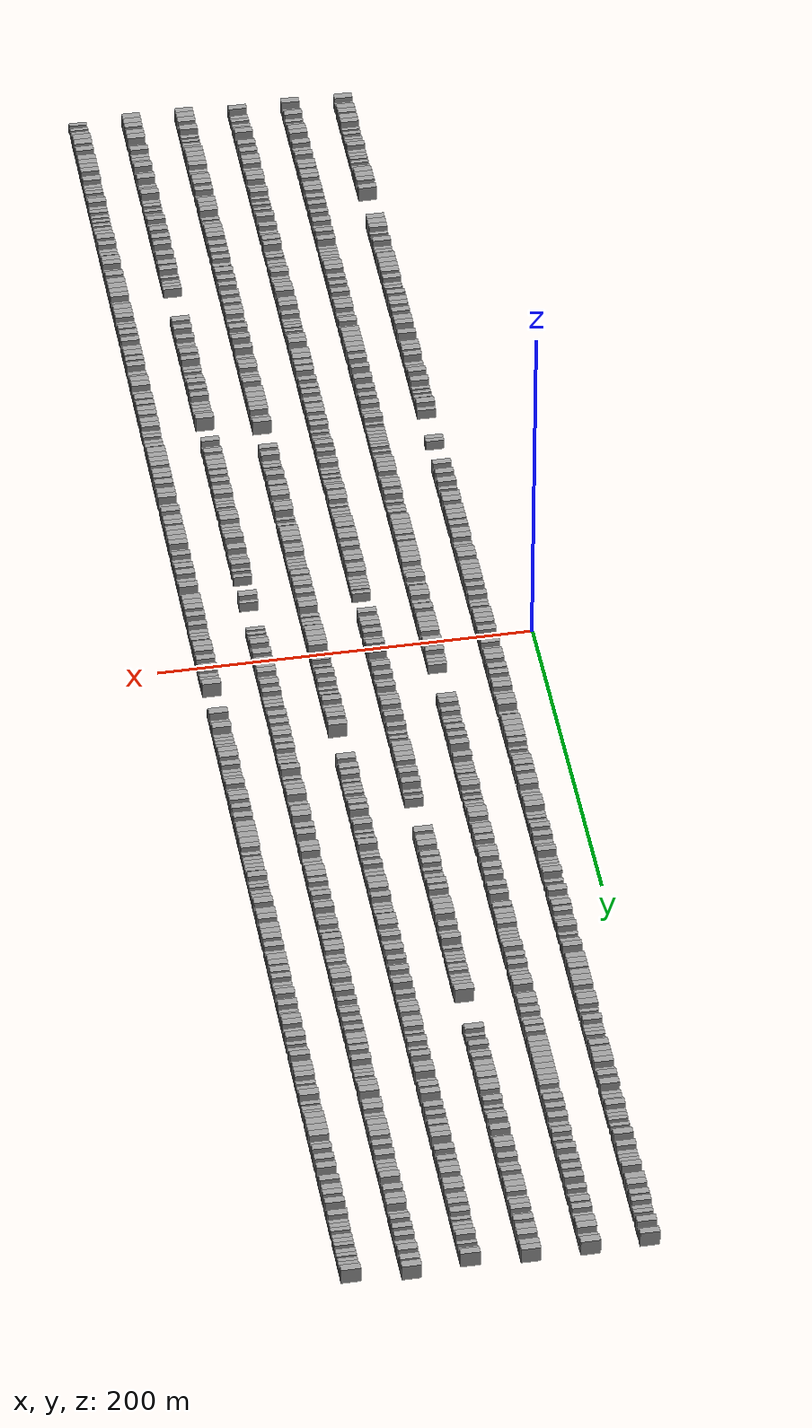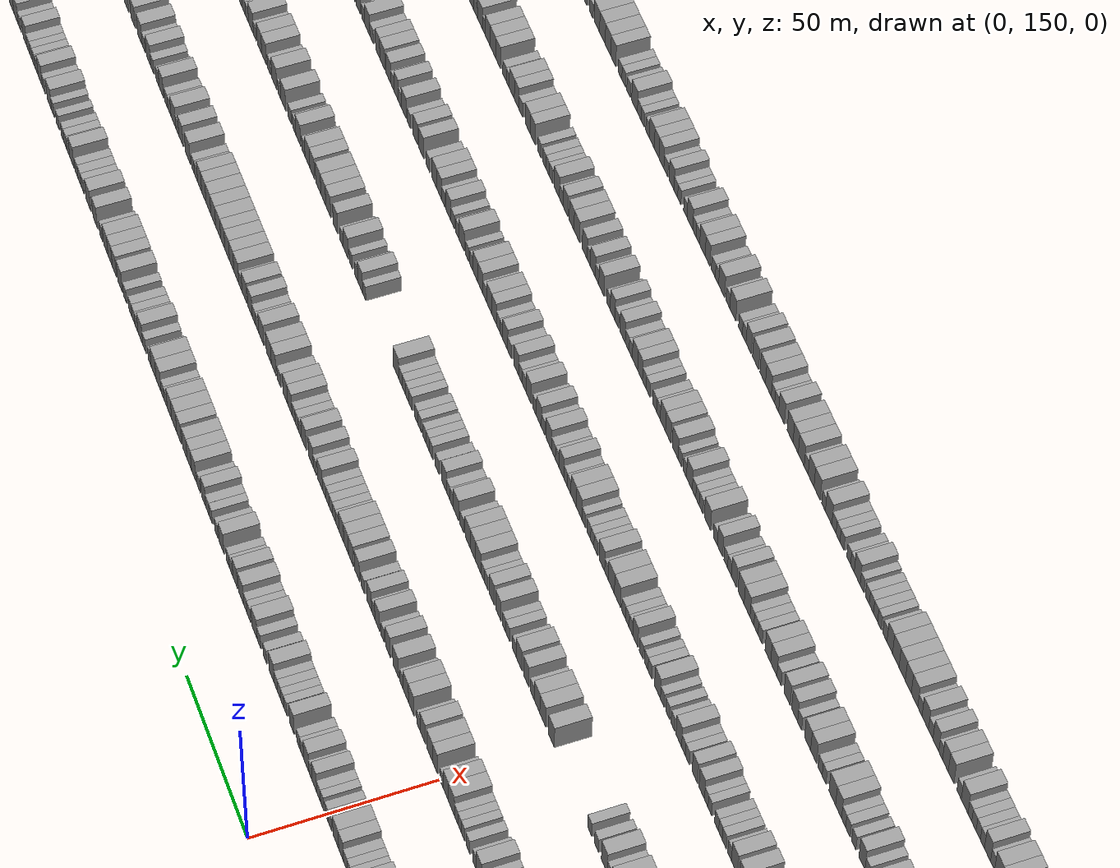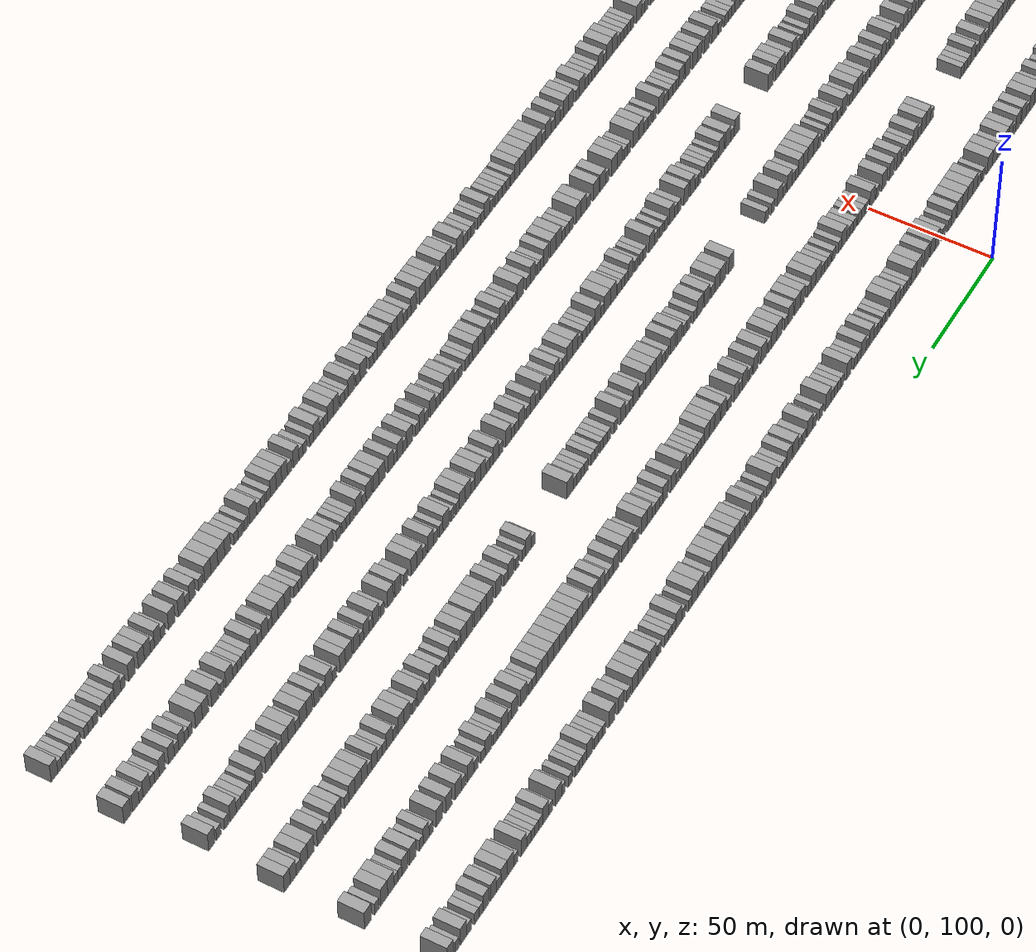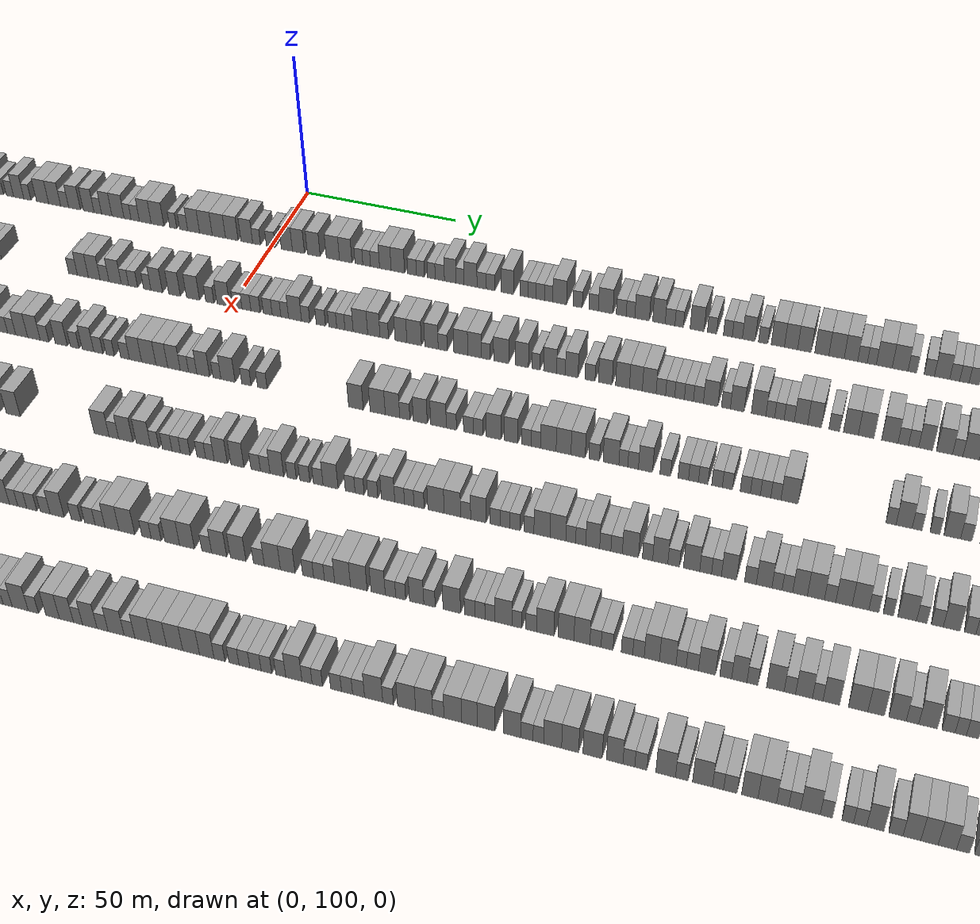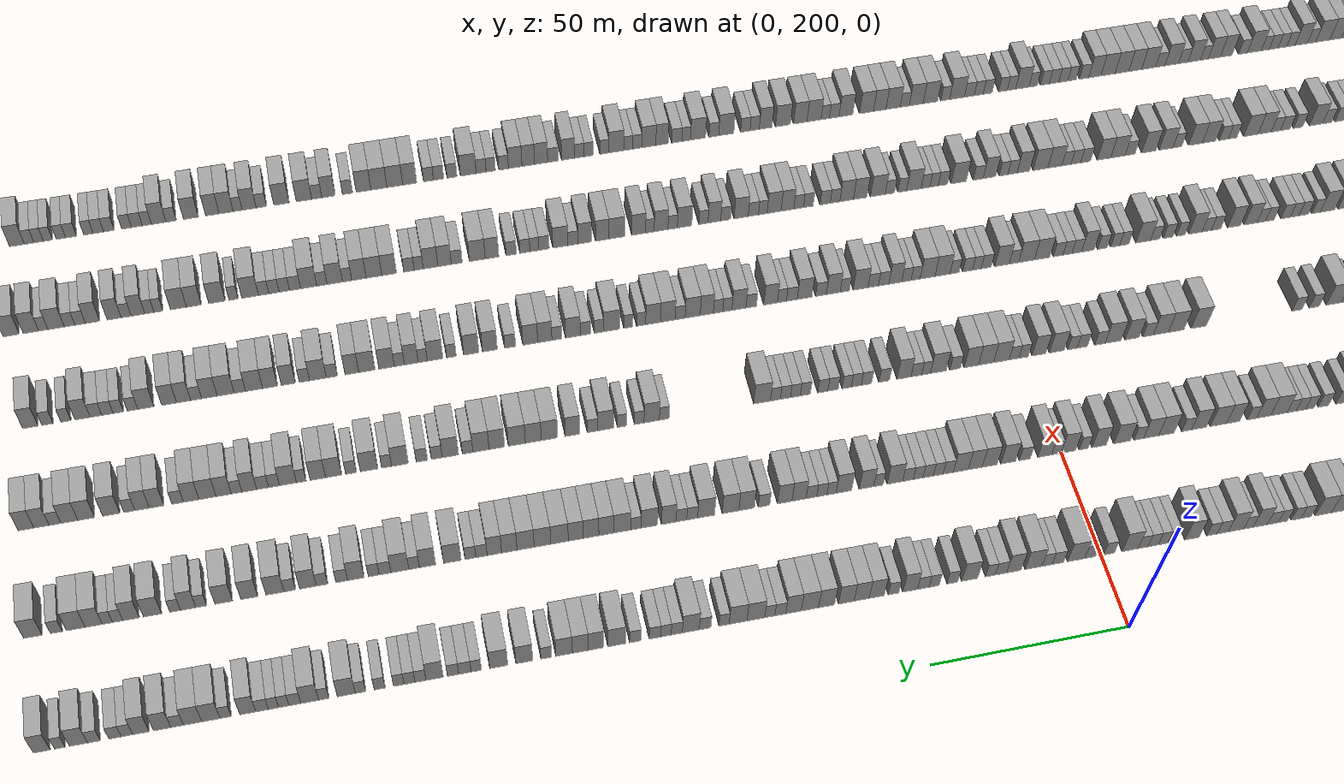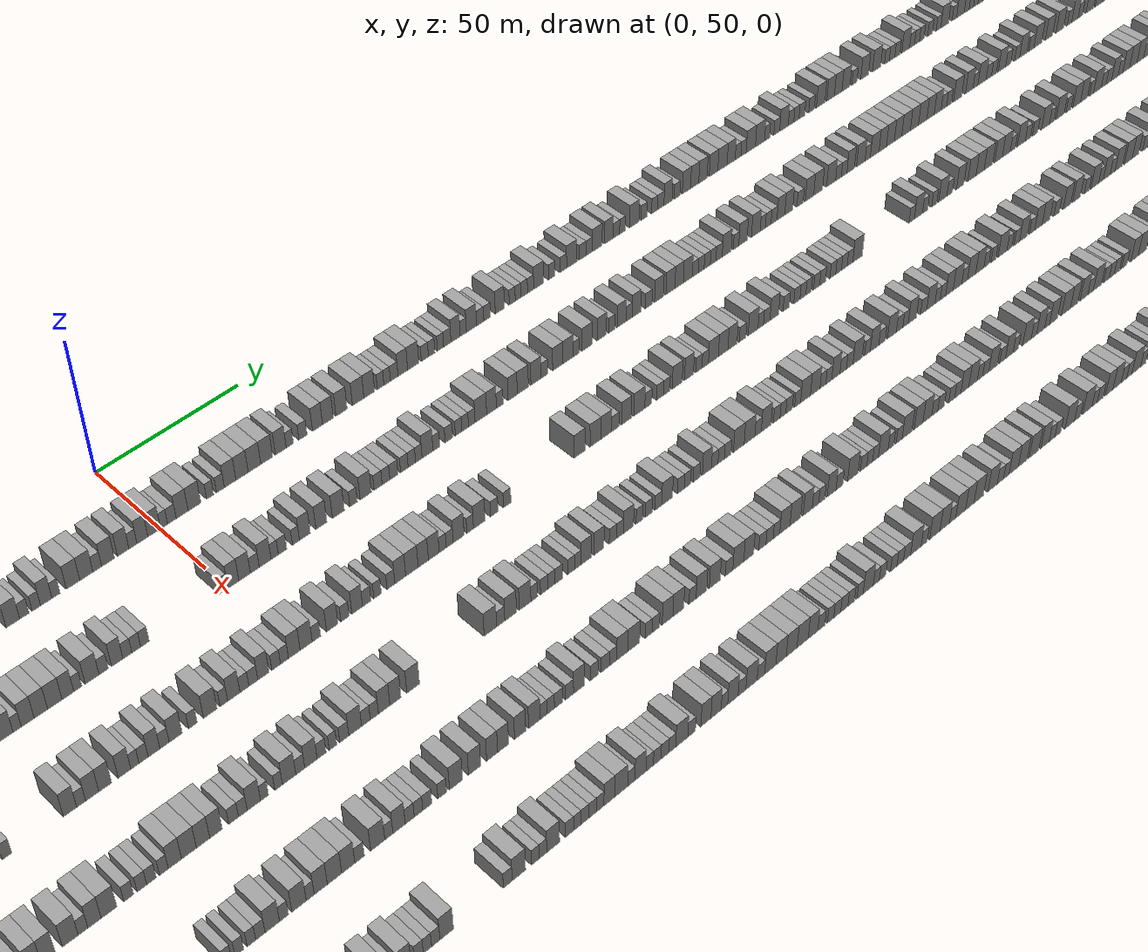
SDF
<sdf version="1.6">
 <world name="default">
  <scene>
   <sky><clouds><speed>12</speed></clouds></sky>
   <ambient>0.4 0.4 0.4 1</ambient>
   <background>0.7 0.7 0.7 1</background>
   <shadows>1</shadows>
  </scene>
  <gravity>0 0 -9.8066</gravity>
  <magnetic_field>6e-06 2.3e-05 -4.2e-05</magnetic_field>
  <physics default="0" name="default_physics" type="ode">
   <ode>
    <solver>
     <type>quick</type>
     <iters>10</iters>
     <sor>1.0</sor>
     <use_dynamic_moi_rescaling>0</use_dynamic_moi_rescaling>
    </solver>
    <constraints>
     <cfm>0</cfm>
     <erp>0.2</erp>
     <contact_max_correcting_vel>100</contact_max_correcting_vel>
     <contact_surface_layer>0.001</contact_surface_layer>
    </constraints>
   </ode>
   <max_step_size>0.004</max_step_size>
   <real_time_factor>1</real_time_factor>
   <real_time_update_rate>250</real_time_update_rate>
  </physics>
  <light name="sun" type="directional">
   <pose>0 0 10 0 0 0</pose>
   <diffuse>0.8 0.8 0.8 1</diffuse>
   <specular>0.2 0.2 0.2 1</specular>
   <attenuation>
    <range>1000</range>
    <constant>0.9</constant>
    <linear>0.01</linear>
    <quadratic>0.001</quadratic>
   </attenuation>
   <direction>-0.5 0.1 -0.9</direction>
  </light>
  <model name="building_1">
   <static>1</static>
   <pose>25.0000 -455.8890 0 0.000000 0.000000 0.000000</pose>
   <link name="link">
    <pose>0 0 4.50 0 0 0</pose>
    <collision name="collision"><geometry><box><size>10.0000 4.2220 9.0000</size></box></geometry></collision>
    <visual name="visual">
     <cast_shadows>0</cast_shadows>
     <geometry><box><size>10.0000 4.2220 9.0000</size></box></geometry>
     <material>
      <script>
       <uri>model://grey_wall/materials/scripts</uri>
       <uri>model://grey_wall/materials/textures</uri>
       <name>vrc/grey_wall</name>
      </script>
     </material>
    </visual>
   </link>
  </model>
  <model name="building_2">
   <static>1</static>
   <pose>25.0000 -452.3694 0 0.000000 0.000000 0.000000</pose>
   <link name="link">
    <pose>0 0 3.00 0 0 0</pose>
    <collision name="collision"><geometry><box><size>10.0000 2.8172 6.0000</size></box></geometry></collision>
    <visual name="visual">
     <cast_shadows>0</cast_shadows>
     <geometry><box><size>10.0000 2.8172 6.0000</size></box></geometry>
     <material>
      <script>
       <uri>model://grey_wall/materials/scripts</uri>
       <uri>model://grey_wall/materials/textures</uri>
       <name>vrc/grey_wall</name>
      </script>
     </material>
    </visual>
   </link>
  </model>
  <model name="building_3">
   <static>1</static>
   <pose>25.0000 -446.8849 0 0.000000 0.000000 0.000000</pose>
   <link name="link">
    <pose>0 0 4.50 0 0 0</pose>
    <collision name="collision"><geometry><box><size>10.0000 4.1517 9.0000</size></box></geometry></collision>
    <visual name="visual">
     <cast_shadows>0</cast_shadows>
     <geometry><box><size>10.0000 4.1517 9.0000</size></box></geometry>
     <material>
      <script>
       <uri>model://grey_wall/materials/scripts</uri>
       <uri>model://grey_wall/materials/textures</uri>
       <name>vrc/grey_wall</name>
      </script>
     </material>
    </visual>
   </link>
  </model>
  <model name="building_4">
   <static>1</static>
   <pose>25.0000 -442.7926 0 0.000000 0.000000 0.000000</pose>
   <link name="link">
    <pose>0 0 4.50 0 0 0</pose>
    <collision name="collision"><geometry><box><size>10.0000 4.0331 9.0000</size></box></geometry></collision>
    <visual name="visual">
     <cast_shadows>0</cast_shadows>
     <geometry><box><size>10.0000 4.0331 9.0000</size></box></geometry>
     <material>
      <script>
       <uri>model://grey_wall/materials/scripts</uri>
       <uri>model://grey_wall/materials/textures</uri>
       <name>vrc/grey_wall</name>
      </script>
     </material>
    </visual>
   </link>
  </model>
  <model name="building_5">
   <static>1</static>
   <pose>25.0000 -437.6723 0 0.000000 0.000000 0.000000</pose>
   <link name="link">
    <pose>0 0 4.50 0 0 0</pose>
    <collision name="collision"><geometry><box><size>10.0000 4.2074 9.0000</size></box></geometry></collision>
    <visual name="visual">
     <cast_shadows>0</cast_shadows>
     <geometry><box><size>10.0000 4.2074 9.0000</size></box></geometry>
     <material>
      <script>
       <uri>model://grey_wall/materials/scripts</uri>
       <uri>model://grey_wall/materials/textures</uri>
       <name>vrc/grey_wall</name>
      </script>
     </material>
    </visual>
   </link>
  </model>
  <model name="building_6">
   <static>1</static>
   <pose>25.0000 -433.7566 0 0.000000 0.000000 0.000000</pose>
   <link name="link">
    <pose>0 0 4.50 0 0 0</pose>
    <collision name="collision"><geometry><box><size>10.0000 3.6240 9.0000</size></box></geometry></collision>
    <visual name="visual">
     <cast_shadows>0</cast_shadows>
     <geometry><box><size>10.0000 3.6240 9.0000</size></box></geometry>
     <material>
      <script>
       <uri>model://grey_wall/materials/scripts</uri>
       <uri>model://grey_wall/materials/textures</uri>
       <name>vrc/grey_wall</name>
      </script>
     </material>
    </visual>
   </link>
  </model>
  <model name="building_7">
   <static>1</static>
   <pose>25.0000 -429.7346 0 0.000000 0.000000 0.000000</pose>
   <link name="link">
    <pose>0 0 3.00 0 0 0</pose>
    <collision name="collision"><geometry><box><size>10.0000 2.4200 6.0000</size></box></geometry></collision>
    <visual name="visual">
     <cast_shadows>0</cast_shadows>
     <geometry><box><size>10.0000 2.4200 6.0000</size></box></geometry>
     <material>
      <script>
       <uri>model://grey_wall/materials/scripts</uri>
       <uri>model://grey_wall/materials/textures</uri>
       <name>vrc/grey_wall</name>
      </script>
     </material>
    </visual>
   </link>
  </model>
  <model name="building_8">
   <static>1</static>
   <pose>25.0000 -426.0421 0 0.000000 0.000000 0.000000</pose>
   <link name="link">
    <pose>0 0 3.00 0 0 0</pose>
    <collision name="collision"><geometry><box><size>10.0000 2.9650 6.0000</size></box></geometry></collision>
    <visual name="visual">
     <cast_shadows>0</cast_shadows>
     <geometry><box><size>10.0000 2.9650 6.0000</size></box></geometry>
     <material>
      <script>
       <uri>model://grey_wall/materials/scripts</uri>
       <uri>model://grey_wall/materials/textures</uri>
       <name>vrc/grey_wall</name>
      </script>
     </material>
    </visual>
   </link>
  </model>
  <model name="building_9">
   <static>1</static>
   <pose>25.0000 -421.3107 0 0.000000 0.000000 0.000000</pose>
   <link name="link">
    <pose>0 0 3.00 0 0 0</pose>
    <collision name="collision"><geometry><box><size>10.0000 2.4979 6.0000</size></box></geometry></collision>
    <visual name="visual">
     <cast_shadows>0</cast_shadows>
     <geometry><box><size>10.0000 2.4979 6.0000</size></box></geometry>
     <material>
      <script>
       <uri>model://grey_wall/materials/scripts</uri>
       <uri>model://grey_wall/materials/textures</uri>
       <name>vrc/grey_wall</name>
      </script>
     </material>
    </visual>
   </link>
  </model>
  <model name="building_10">
   <static>1</static>
   <pose>25.0000 -418.6760 0 0.000000 0.000000 0.000000</pose>
   <link name="link">
    <pose>0 0 3.00 0 0 0</pose>
    <collision name="collision"><geometry><box><size>10.0000 2.7715 6.0000</size></box></geometry></collision>
    <visual name="visual">
     <cast_shadows>0</cast_shadows>
     <geometry><box><size>10.0000 2.7715 6.0000</size></box></geometry>
     <material>
      <script>
       <uri>model://grey_wall/materials/scripts</uri>
       <uri>model://grey_wall/materials/textures</uri>
       <name>vrc/grey_wall</name>
      </script>
     </material>
    </visual>
   </link>
  </model>
  <model name="building_11">
   <static>1</static>
   <pose>25.0000 -415.8218 0 0.000000 0.000000 0.000000</pose>
   <link name="link">
    <pose>0 0 3.00 0 0 0</pose>
    <collision name="collision"><geometry><box><size>10.0000 2.9370 6.0000</size></box></geometry></collision>
    <visual name="visual">
     <cast_shadows>0</cast_shadows>
     <geometry><box><size>10.0000 2.9370 6.0000</size></box></geometry>
     <material>
      <script>
       <uri>model://grey_wall/materials/scripts</uri>
       <uri>model://grey_wall/materials/textures</uri>
       <name>vrc/grey_wall</name>
      </script>
     </material>
    </visual>
   </link>
  </model>
  <model name="building_12">
   <static>1</static>
   <pose>25.0000 -412.4712 0 0.000000 0.000000 0.000000</pose>
   <link name="link">
    <pose>0 0 4.50 0 0 0</pose>
    <collision name="collision"><geometry><box><size>10.0000 3.7641 9.0000</size></box></geometry></collision>
    <visual name="visual">
     <cast_shadows>0</cast_shadows>
     <geometry><box><size>10.0000 3.7641 9.0000</size></box></geometry>
     <material>
      <script>
       <uri>model://grey_wall/materials/scripts</uri>
       <uri>model://grey_wall/materials/textures</uri>
       <name>vrc/grey_wall</name>
      </script>
     </material>
    </visual>
   </link>
  </model>
  <model name="building_13">
   <static>1</static>
   <pose>25.0000 -409.2177 0 0.000000 0.000000 0.000000</pose>
   <link name="link">
    <pose>0 0 3.00 0 0 0</pose>
    <collision name="collision"><geometry><box><size>10.0000 2.7430 6.0000</size></box></geometry></collision>
    <visual name="visual">
     <cast_shadows>0</cast_shadows>
     <geometry><box><size>10.0000 2.7430 6.0000</size></box></geometry>
     <material>
      <script>
       <uri>model://grey_wall/materials/scripts</uri>
       <uri>model://grey_wall/materials/textures</uri>
       <name>vrc/grey_wall</name>
      </script>
     </material>
    </visual>
   </link>
  </model>
  <model name="building_14">
   <static>1</static>
   <pose>25.0000 -406.3590 0 0.000000 0.000000 0.000000</pose>
   <link name="link">
    <pose>0 0 3.00 0 0 0</pose>
    <collision name="collision"><geometry><box><size>10.0000 2.9744 6.0000</size></box></geometry></collision>
    <visual name="visual">
     <cast_shadows>0</cast_shadows>
     <geometry><box><size>10.0000 2.9744 6.0000</size></box></geometry>
     <material>
      <script>
       <uri>model://grey_wall/materials/scripts</uri>
       <uri>model://grey_wall/materials/textures</uri>
       <name>vrc/grey_wall</name>
      </script>
     </material>
    </visual>
   </link>
  </model>
  <model name="building_15">
   <static>1</static>
   <pose>25.0000 -403.5339 0 0.000000 0.000000 0.000000</pose>
   <link name="link">
    <pose>0 0 3.00 0 0 0</pose>
    <collision name="collision"><geometry><box><size>10.0000 2.6758 6.0000</size></box></geometry></collision>
    <visual name="visual">
     <cast_shadows>0</cast_shadows>
     <geometry><box><size>10.0000 2.6758 6.0000</size></box></geometry>
     <material>
      <script>
       <uri>model://grey_wall/materials/scripts</uri>
       <uri>model://grey_wall/materials/textures</uri>
       <name>vrc/grey_wall</name>
      </script>
     </material>
    </visual>
   </link>
  </model>
  <model name="building_16">
   <static>1</static>
   <pose>25.0000 -399.9270 0 0.000000 0.000000 0.000000</pose>
   <link name="link">
    <pose>0 0 3.00 0 0 0</pose>
    <collision name="collision"><geometry><box><size>10.0000 2.5380 6.0000</size></box></geometry></collision>
    <visual name="visual">
     <cast_shadows>0</cast_shadows>
     <geometry><box><size>10.0000 2.5380 6.0000</size></box></geometry>
     <material>
      <script>
       <uri>model://grey_wall/materials/scripts</uri>
       <uri>model://grey_wall/materials/textures</uri>
       <name>vrc/grey_wall</name>
      </script>
     </material>
    </visual>
   </link>
  </model>
  <model name="building_17">
   <static>1</static>
   <pose>25.0000 -395.3176 0 0.000000 0.000000 0.000000</pose>
   <link name="link">
    <pose>0 0 3.00 0 0 0</pose>
    <collision name="collision"><geometry><box><size>10.0000 2.6808 6.0000</size></box></geometry></collision>
    <visual name="visual">
     <cast_shadows>0</cast_shadows>
     <geometry><box><size>10.0000 2.6808 6.0000</size></box></geometry>
     <material>
      <script>
       <uri>model://grey_wall/materials/scripts</uri>
       <uri>model://grey_wall/materials/textures</uri>
       <name>vrc/grey_wall</name>
      </script>
     </material>
    </visual>
   </link>
  </model>
  <model name="building_18">
   <static>1</static>
   <pose>25.0000 -392.7767 0 0.000000 0.000000 0.000000</pose>
   <link name="link">
    <pose>0 0 3.00 0 0 0</pose>
    <collision name="collision"><geometry><box><size>10.0000 2.4010 6.0000</size></box></geometry></collision>
    <visual name="visual">
     <cast_shadows>0</cast_shadows>
     <geometry><box><size>10.0000 2.4010 6.0000</size></box></geometry>
     <material>
      <script>
       <uri>model://grey_wall/materials/scripts</uri>
       <uri>model://grey_wall/materials/textures</uri>
       <name>vrc/grey_wall</name>
      </script>
     </material>
    </visual>
   </link>
  </model>
  <model name="building_19">
   <static>1</static>
   <pose>25.0000 -389.4952 0 0.000000 0.000000 0.000000</pose>
   <link name="link">
    <pose>0 0 4.50 0 0 0</pose>
    <collision name="collision"><geometry><box><size>10.0000 4.1621 9.0000</size></box></geometry></collision>
    <visual name="visual">
     <cast_shadows>0</cast_shadows>
     <geometry><box><size>10.0000 4.1621 9.0000</size></box></geometry>
     <material>
      <script>
       <uri>model://grey_wall/materials/scripts</uri>
       <uri>model://grey_wall/materials/textures</uri>
       <name>vrc/grey_wall</name>
      </script>
     </material>
    </visual>
   </link>
  </model>
  <model name="building_20">
   <static>1</static>
   <pose>25.0000 -385.1823 0 0.000000 0.000000 0.000000</pose>
   <link name="link">
    <pose>0 0 4.50 0 0 0</pose>
    <collision name="collision"><geometry><box><size>10.0000 4.4636 9.0000</size></box></geometry></collision>
    <visual name="visual">
     <cast_shadows>0</cast_shadows>
     <geometry><box><size>10.0000 4.4636 9.0000</size></box></geometry>
     <material>
      <script>
       <uri>model://grey_wall/materials/scripts</uri>
       <uri>model://grey_wall/materials/textures</uri>
       <name>vrc/grey_wall</name>
      </script>
     </material>
    </visual>
   </link>
  </model>
  <model name="building_21">
   <static>1</static>
   <pose>25.0000 -381.0344 0 0.000000 0.000000 0.000000</pose>
   <link name="link">
    <pose>0 0 4.50 0 0 0</pose>
    <collision name="collision"><geometry><box><size>10.0000 3.8322 9.0000</size></box></geometry></collision>
    <visual name="visual">
     <cast_shadows>0</cast_shadows>
     <geometry><box><size>10.0000 3.8322 9.0000</size></box></geometry>
     <material>
      <script>
       <uri>model://grey_wall/materials/scripts</uri>
       <uri>model://grey_wall/materials/textures</uri>
       <name>vrc/grey_wall</name>
      </script>
     </material>
    </visual>
   </link>
  </model>
  <model name="building_22">
   <static>1</static>
   <pose>25.0000 -377.6439 0 0.000000 0.000000 0.000000</pose>
   <link name="link">
    <pose>0 0 3.00 0 0 0</pose>
    <collision name="collision"><geometry><box><size>10.0000 2.9487 6.0000</size></box></geometry></collision>
    <visual name="visual">
     <cast_shadows>0</cast_shadows>
     <geometry><box><size>10.0000 2.9487 6.0000</size></box></geometry>
     <material>
      <script>
       <uri>model://grey_wall/materials/scripts</uri>
       <uri>model://grey_wall/materials/textures</uri>
       <name>vrc/grey_wall</name>
      </script>
     </material>
    </visual>
   </link>
  </model>
  <model name="building_23">
   <static>1</static>
   <pose>25.0000 -374.1753 0 0.000000 0.000000 0.000000</pose>
   <link name="link">
    <pose>0 0 4.50 0 0 0</pose>
    <collision name="collision"><geometry><box><size>10.0000 3.9885 9.0000</size></box></geometry></collision>
    <visual name="visual">
     <cast_shadows>0</cast_shadows>
     <geometry><box><size>10.0000 3.9885 9.0000</size></box></geometry>
     <material>
      <script>
       <uri>model://grey_wall/materials/scripts</uri>
       <uri>model://grey_wall/materials/textures</uri>
       <name>vrc/grey_wall</name>
      </script>
     </material>
    </visual>
   </link>
  </model>
  <model name="building_24">
   <static>1</static>
   <pose>25.0000 -347.3957 0 0.000000 0.000000 0.000000</pose>
   <link name="link">
    <pose>0 0 4.50 0 0 0</pose>
    <collision name="collision"><geometry><box><size>10.0000 3.8569 9.0000</size></box></geometry></collision>
    <visual name="visual">
     <cast_shadows>0</cast_shadows>
     <geometry><box><size>10.0000 3.8569 9.0000</size></box></geometry>
     <material>
      <script>
       <uri>model://grey_wall/materials/scripts</uri>
       <uri>model://grey_wall/materials/textures</uri>
       <name>vrc/grey_wall</name>
      </script>
     </material>
    </visual>
   </link>
  </model>
  <model name="building_25">
   <static>1</static>
   <pose>25.0000 -343.2680 0 0.000000 0.000000 0.000000</pose>
   <link name="link">
    <pose>0 0 4.50 0 0 0</pose>
    <collision name="collision"><geometry><box><size>10.0000 4.3986 9.0000</size></box></geometry></collision>
    <visual name="visual">
     <cast_shadows>0</cast_shadows>
     <geometry><box><size>10.0000 4.3986 9.0000</size></box></geometry>
     <material>
      <script>
       <uri>model://grey_wall/materials/scripts</uri>
       <uri>model://grey_wall/materials/textures</uri>
       <name>vrc/grey_wall</name>
      </script>
     </material>
    </visual>
   </link>
  </model>
  <model name="building_26">
   <static>1</static>
   <pose>25.0000 -339.1380 0 0.000000 0.000000 0.000000</pose>
   <link name="link">
    <pose>0 0 4.50 0 0 0</pose>
    <collision name="collision"><geometry><box><size>10.0000 3.8614 9.0000</size></box></geometry></collision>
    <visual name="visual">
     <cast_shadows>0</cast_shadows>
     <geometry><box><size>10.0000 3.8614 9.0000</size></box></geometry>
     <material>
      <script>
       <uri>model://grey_wall/materials/scripts</uri>
       <uri>model://grey_wall/materials/textures</uri>
       <name>vrc/grey_wall</name>
      </script>
     </material>
    </visual>
   </link>
  </model>
  <model name="building_27">
   <static>1</static>
   <pose>25.0000 -335.9510 0 0.000000 0.000000 0.000000</pose>
   <link name="link">
    <pose>0 0 3.00 0 0 0</pose>
    <collision name="collision"><geometry><box><size>10.0000 2.5128 6.0000</size></box></geometry></collision>
    <visual name="visual">
     <cast_shadows>0</cast_shadows>
     <geometry><box><size>10.0000 2.5128 6.0000</size></box></geometry>
     <material>
      <script>
       <uri>model://grey_wall/materials/scripts</uri>
       <uri>model://grey_wall/materials/textures</uri>
       <name>vrc/grey_wall</name>
      </script>
     </material>
    </visual>
   </link>
  </model>
  <model name="building_28">
   <static>1</static>
   <pose>25.0000 -331.4063 0 0.000000 0.000000 0.000000</pose>
   <link name="link">
    <pose>0 0 3.00 0 0 0</pose>
    <collision name="collision"><geometry><box><size>10.0000 2.5765 6.0000</size></box></geometry></collision>
    <visual name="visual">
     <cast_shadows>0</cast_shadows>
     <geometry><box><size>10.0000 2.5765 6.0000</size></box></geometry>
     <material>
      <script>
       <uri>model://grey_wall/materials/scripts</uri>
       <uri>model://grey_wall/materials/textures</uri>
       <name>vrc/grey_wall</name>
      </script>
     </material>
    </visual>
   </link>
  </model>
  <model name="building_29">
   <static>1</static>
   <pose>25.0000 -327.1324 0 0.000000 0.000000 0.000000</pose>
   <link name="link">
    <pose>0 0 4.50 0 0 0</pose>
    <collision name="collision"><geometry><box><size>10.0000 3.9714 9.0000</size></box></geometry></collision>
    <visual name="visual">
     <cast_shadows>0</cast_shadows>
     <geometry><box><size>10.0000 3.9714 9.0000</size></box></geometry>
     <material>
      <script>
       <uri>model://grey_wall/materials/scripts</uri>
       <uri>model://grey_wall/materials/textures</uri>
       <name>vrc/grey_wall</name>
      </script>
     </material>
    </visual>
   </link>
  </model>
  <model name="building_30">
   <static>1</static>
   <pose>25.0000 -322.8995 0 0.000000 0.000000 0.000000</pose>
   <link name="link">
    <pose>0 0 3.00 0 0 0</pose>
    <collision name="collision"><geometry><box><size>10.0000 2.4942 6.0000</size></box></geometry></collision>
    <visual name="visual">
     <cast_shadows>0</cast_shadows>
     <geometry><box><size>10.0000 2.4942 6.0000</size></box></geometry>
     <material>
      <script>
       <uri>model://grey_wall/materials/scripts</uri>
       <uri>model://grey_wall/materials/textures</uri>
       <name>vrc/grey_wall</name>
      </script>
     </material>
    </visual>
   </link>
  </model>
  <model name="building_31">
   <static>1</static>
   <pose>25.0000 -320.3412 0 0.000000 0.000000 0.000000</pose>
   <link name="link">
    <pose>0 0 3.00 0 0 0</pose>
    <collision name="collision"><geometry><box><size>10.0000 2.6224 6.0000</size></box></geometry></collision>
    <visual name="visual">
     <cast_shadows>0</cast_shadows>
     <geometry><box><size>10.0000 2.6224 6.0000</size></box></geometry>
     <material>
      <script>
       <uri>model://grey_wall/materials/scripts</uri>
       <uri>model://grey_wall/materials/textures</uri>
       <name>vrc/grey_wall</name>
      </script>
     </material>
    </visual>
   </link>
  </model>
  <model name="building_32">
   <static>1</static>
   <pose>25.0000 -317.5554 0 0.000000 0.000000 0.000000</pose>
   <link name="link">
    <pose>0 0 3.00 0 0 0</pose>
    <collision name="collision"><geometry><box><size>10.0000 2.9493 6.0000</size></box></geometry></collision>
    <visual name="visual">
     <cast_shadows>0</cast_shadows>
     <geometry><box><size>10.0000 2.9493 6.0000</size></box></geometry>
     <material>
      <script>
       <uri>model://grey_wall/materials/scripts</uri>
       <uri>model://grey_wall/materials/textures</uri>
       <name>vrc/grey_wall</name>
      </script>
     </material>
    </visual>
   </link>
  </model>
  <model name="building_33">
   <static>1</static>
   <pose>25.0000 -312.8945 0 0.000000 0.000000 0.000000</pose>
   <link name="link">
    <pose>0 0 4.50 0 0 0</pose>
    <collision name="collision"><geometry><box><size>10.0000 4.3726 9.0000</size></box></geometry></collision>
    <visual name="visual">
     <cast_shadows>0</cast_shadows>
     <geometry><box><size>10.0000 4.3726 9.0000</size></box></geometry>
     <material>
      <script>
       <uri>model://grey_wall/materials/scripts</uri>
       <uri>model://grey_wall/materials/textures</uri>
       <name>vrc/grey_wall</name>
      </script>
     </material>
    </visual>
   </link>
  </model>
  <model name="building_34">
   <static>1</static>
   <pose>25.0000 -308.6578 0 0.000000 0.000000 0.000000</pose>
   <link name="link">
    <pose>0 0 4.50 0 0 0</pose>
    <collision name="collision"><geometry><box><size>10.0000 4.1007 9.0000</size></box></geometry></collision>
    <visual name="visual">
     <cast_shadows>0</cast_shadows>
     <geometry><box><size>10.0000 4.1007 9.0000</size></box></geometry>
     <material>
      <script>
       <uri>model://grey_wall/materials/scripts</uri>
       <uri>model://grey_wall/materials/textures</uri>
       <name>vrc/grey_wall</name>
      </script>
     </material>
    </visual>
   </link>
  </model>
  <model name="building_35">
   <static>1</static>
   <pose>25.0000 -304.6056 0 0.000000 0.000000 0.000000</pose>
   <link name="link">
    <pose>0 0 4.50 0 0 0</pose>
    <collision name="collision"><geometry><box><size>10.0000 4.0038 9.0000</size></box></geometry></collision>
    <visual name="visual">
     <cast_shadows>0</cast_shadows>
     <geometry><box><size>10.0000 4.0038 9.0000</size></box></geometry>
     <material>
      <script>
       <uri>model://grey_wall/materials/scripts</uri>
       <uri>model://grey_wall/materials/textures</uri>
       <name>vrc/grey_wall</name>
      </script>
     </material>
    </visual>
   </link>
  </model>
  <model name="building_36">
   <static>1</static>
   <pose>25.0000 -300.4515 0 0.000000 0.000000 0.000000</pose>
   <link name="link">
    <pose>0 0 4.50 0 0 0</pose>
    <collision name="collision"><geometry><box><size>10.0000 4.3042 9.0000</size></box></geometry></collision>
    <visual name="visual">
     <cast_shadows>0</cast_shadows>
     <geometry><box><size>10.0000 4.3042 9.0000</size></box></geometry>
     <material>
      <script>
       <uri>model://grey_wall/materials/scripts</uri>
       <uri>model://grey_wall/materials/textures</uri>
       <name>vrc/grey_wall</name>
      </script>
     </material>
    </visual>
   </link>
  </model>
  <model name="building_37">
   <static>1</static>
   <pose>25.0000 -294.3647 0 0.000000 0.000000 0.000000</pose>
   <link name="link">
    <pose>0 0 4.50 0 0 0</pose>
    <collision name="collision"><geometry><box><size>10.0000 3.8694 9.0000</size></box></geometry></collision>
    <visual name="visual">
     <cast_shadows>0</cast_shadows>
     <geometry><box><size>10.0000 3.8694 9.0000</size></box></geometry>
     <material>
      <script>
       <uri>model://grey_wall/materials/scripts</uri>
       <uri>model://grey_wall/materials/textures</uri>
       <name>vrc/grey_wall</name>
      </script>
     </material>
    </visual>
   </link>
  </model>
  <model name="building_38">
   <static>1</static>
   <pose>25.0000 -291.0987 0 0.000000 0.000000 0.000000</pose>
   <link name="link">
    <pose>0 0 3.00 0 0 0</pose>
    <collision name="collision"><geometry><box><size>10.0000 2.6625 6.0000</size></box></geometry></collision>
    <visual name="visual">
     <cast_shadows>0</cast_shadows>
     <geometry><box><size>10.0000 2.6625 6.0000</size></box></geometry>
     <material>
      <script>
       <uri>model://grey_wall/materials/scripts</uri>
       <uri>model://grey_wall/materials/textures</uri>
       <name>vrc/grey_wall</name>
      </script>
     </material>
    </visual>
   </link>
  </model>
  <model name="building_39">
   <static>1</static>
   <pose>25.0000 -288.4681 0 0.000000 0.000000 0.000000</pose>
   <link name="link">
    <pose>0 0 3.00 0 0 0</pose>
    <collision name="collision"><geometry><box><size>10.0000 2.5986 6.0000</size></box></geometry></collision>
    <visual name="visual">
     <cast_shadows>0</cast_shadows>
     <geometry><box><size>10.0000 2.5986 6.0000</size></box></geometry>
     <material>
      <script>
       <uri>model://grey_wall/materials/scripts</uri>
       <uri>model://grey_wall/materials/textures</uri>
       <name>vrc/grey_wall</name>
      </script>
     </material>
    </visual>
   </link>
  </model>
  <model name="building_40">
   <static>1</static>
   <pose>25.0000 -283.8623 0 0.000000 0.000000 0.000000</pose>
   <link name="link">
    <pose>0 0 3.00 0 0 0</pose>
    <collision name="collision"><geometry><box><size>10.0000 2.6131 6.0000</size></box></geometry></collision>
    <visual name="visual">
     <cast_shadows>0</cast_shadows>
     <geometry><box><size>10.0000 2.6131 6.0000</size></box></geometry>
     <material>
      <script>
       <uri>model://grey_wall/materials/scripts</uri>
       <uri>model://grey_wall/materials/textures</uri>
       <name>vrc/grey_wall</name>
      </script>
     </material>
    </visual>
   </link>
  </model>
  <model name="building_41">
   <static>1</static>
   <pose>25.0000 -280.6888 0 0.000000 0.000000 0.000000</pose>
   <link name="link">
    <pose>0 0 4.50 0 0 0</pose>
    <collision name="collision"><geometry><box><size>10.0000 3.7339 9.0000</size></box></geometry></collision>
    <visual name="visual">
     <cast_shadows>0</cast_shadows>
     <geometry><box><size>10.0000 3.7339 9.0000</size></box></geometry>
     <material>
      <script>
       <uri>model://grey_wall/materials/scripts</uri>
       <uri>model://grey_wall/materials/textures</uri>
       <name>vrc/grey_wall</name>
      </script>
     </material>
    </visual>
   </link>
  </model>
  <model name="building_42">
   <static>1</static>
   <pose>25.0000 -274.8779 0 0.000000 0.000000 0.000000</pose>
   <link name="link">
    <pose>0 0 4.50 0 0 0</pose>
    <collision name="collision"><geometry><box><size>10.0000 3.8879 9.0000</size></box></geometry></collision>
    <visual name="visual">
     <cast_shadows>0</cast_shadows>
     <geometry><box><size>10.0000 3.8879 9.0000</size></box></geometry>
     <material>
      <script>
       <uri>model://grey_wall/materials/scripts</uri>
       <uri>model://grey_wall/materials/textures</uri>
       <name>vrc/grey_wall</name>
      </script>
     </material>
    </visual>
   </link>
  </model>
  <model name="building_43">
   <static>1</static>
   <pose>25.0000 -271.1215 0 0.000000 0.000000 0.000000</pose>
   <link name="link">
    <pose>0 0 4.50 0 0 0</pose>
    <collision name="collision"><geometry><box><size>10.0000 3.6248 9.0000</size></box></geometry></collision>
    <visual name="visual">
     <cast_shadows>0</cast_shadows>
     <geometry><box><size>10.0000 3.6248 9.0000</size></box></geometry>
     <material>
      <script>
       <uri>model://grey_wall/materials/scripts</uri>
       <uri>model://grey_wall/materials/textures</uri>
       <name>vrc/grey_wall</name>
      </script>
     </material>
    </visual>
   </link>
  </model>
  <model name="building_44">
   <static>1</static>
   <pose>25.0000 -265.3323 0 0.000000 0.000000 0.000000</pose>
   <link name="link">
    <pose>0 0 4.50 0 0 0</pose>
    <collision name="collision"><geometry><box><size>10.0000 3.9536 9.0000</size></box></geometry></collision>
    <visual name="visual">
     <cast_shadows>0</cast_shadows>
     <geometry><box><size>10.0000 3.9536 9.0000</size></box></geometry>
     <material>
      <script>
       <uri>model://grey_wall/materials/scripts</uri>
       <uri>model://grey_wall/materials/textures</uri>
       <name>vrc/grey_wall</name>
      </script>
     </material>
    </visual>
   </link>
  </model>
  <model name="building_45">
   <static>1</static>
   <pose>25.0000 -262.1128 0 0.000000 0.000000 0.000000</pose>
   <link name="link">
    <pose>0 0 3.00 0 0 0</pose>
    <collision name="collision"><geometry><box><size>10.0000 2.4854 6.0000</size></box></geometry></collision>
    <visual name="visual">
     <cast_shadows>0</cast_shadows>
     <geometry><box><size>10.0000 2.4854 6.0000</size></box></geometry>
     <material>
      <script>
       <uri>model://grey_wall/materials/scripts</uri>
       <uri>model://grey_wall/materials/textures</uri>
       <name>vrc/grey_wall</name>
      </script>
     </material>
    </visual>
   </link>
  </model>
  <model name="building_46">
   <static>1</static>
   <pose>25.0000 -258.6913 0 0.000000 0.000000 0.000000</pose>
   <link name="link">
    <pose>0 0 4.50 0 0 0</pose>
    <collision name="collision"><geometry><box><size>10.0000 4.3576 9.0000</size></box></geometry></collision>
    <visual name="visual">
     <cast_shadows>0</cast_shadows>
     <geometry><box><size>10.0000 4.3576 9.0000</size></box></geometry>
     <material>
      <script>
       <uri>model://grey_wall/materials/scripts</uri>
       <uri>model://grey_wall/materials/textures</uri>
       <name>vrc/grey_wall</name>
      </script>
     </material>
    </visual>
   </link>
  </model>
  <model name="building_47">
   <static>1</static>
   <pose>25.0000 -254.6119 0 0.000000 0.000000 0.000000</pose>
   <link name="link">
    <pose>0 0 4.50 0 0 0</pose>
    <collision name="collision"><geometry><box><size>10.0000 3.8012 9.0000</size></box></geometry></collision>
    <visual name="visual">
     <cast_shadows>0</cast_shadows>
     <geometry><box><size>10.0000 3.8012 9.0000</size></box></geometry>
     <material>
      <script>
       <uri>model://grey_wall/materials/scripts</uri>
       <uri>model://grey_wall/materials/textures</uri>
       <name>vrc/grey_wall</name>
      </script>
     </material>
    </visual>
   </link>
  </model>
  <model name="building_48">
   <static>1</static>
   <pose>25.0000 -249.4364 0 0.000000 0.000000 0.000000</pose>
   <link name="link">
    <pose>0 0 3.00 0 0 0</pose>
    <collision name="collision"><geometry><box><size>10.0000 2.5499 6.0000</size></box></geometry></collision>
    <visual name="visual">
     <cast_shadows>0</cast_shadows>
     <geometry><box><size>10.0000 2.5499 6.0000</size></box></geometry>
     <material>
      <script>
       <uri>model://grey_wall/materials/scripts</uri>
       <uri>model://grey_wall/materials/textures</uri>
       <name>vrc/grey_wall</name>
      </script>
     </material>
    </visual>
   </link>
  </model>
  <model name="building_49">
   <static>1</static>
   <pose>25.0000 -246.1935 0 0.000000 0.000000 0.000000</pose>
   <link name="link">
    <pose>0 0 4.50 0 0 0</pose>
    <collision name="collision"><geometry><box><size>10.0000 3.9358 9.0000</size></box></geometry></collision>
    <visual name="visual">
     <cast_shadows>0</cast_shadows>
     <geometry><box><size>10.0000 3.9358 9.0000</size></box></geometry>
     <material>
      <script>
       <uri>model://grey_wall/materials/scripts</uri>
       <uri>model://grey_wall/materials/textures</uri>
       <name>vrc/grey_wall</name>
      </script>
     </material>
    </visual>
   </link>
  </model>
  <model name="building_50">
   <static>1</static>
   <pose>25.0000 -240.7367 0 0.000000 0.000000 0.000000</pose>
   <link name="link">
    <pose>0 0 3.00 0 0 0</pose>
    <collision name="collision"><geometry><box><size>10.0000 2.9778 6.0000</size></box></geometry></collision>
    <visual name="visual">
     <cast_shadows>0</cast_shadows>
     <geometry><box><size>10.0000 2.9778 6.0000</size></box></geometry>
     <material>
      <script>
       <uri>model://grey_wall/materials/scripts</uri>
       <uri>model://grey_wall/materials/textures</uri>
       <name>vrc/grey_wall</name>
      </script>
     </material>
    </visual>
   </link>
  </model>
  <model name="building_51">
   <static>1</static>
   <pose>25.0000 -236.4329 0 0.000000 0.000000 0.000000</pose>
   <link name="link">
    <pose>0 0 4.50 0 0 0</pose>
    <collision name="collision"><geometry><box><size>10.0000 3.6297 9.0000</size></box></geometry></collision>
    <visual name="visual">
     <cast_shadows>0</cast_shadows>
     <geometry><box><size>10.0000 3.6297 9.0000</size></box></geometry>
     <material>
      <script>
       <uri>model://grey_wall/materials/scripts</uri>
       <uri>model://grey_wall/materials/textures</uri>
       <name>vrc/grey_wall</name>
      </script>
     </material>
    </visual>
   </link>
  </model>
  <model name="building_52">
   <static>1</static>
   <pose>25.0000 -232.3689 0 0.000000 0.000000 0.000000</pose>
   <link name="link">
    <pose>0 0 4.50 0 0 0</pose>
    <collision name="collision"><geometry><box><size>10.0000 4.4983 9.0000</size></box></geometry></collision>
    <visual name="visual">
     <cast_shadows>0</cast_shadows>
     <geometry><box><size>10.0000 4.4983 9.0000</size></box></geometry>
     <material>
      <script>
       <uri>model://grey_wall/materials/scripts</uri>
       <uri>model://grey_wall/materials/textures</uri>
       <name>vrc/grey_wall</name>
      </script>
     </material>
    </visual>
   </link>
  </model>
  <model name="building_53">
   <static>1</static>
   <pose>25.0000 -227.1894 0 0.000000 0.000000 0.000000</pose>
   <link name="link">
    <pose>0 0 4.50 0 0 0</pose>
    <collision name="collision"><geometry><box><size>10.0000 3.8606 9.0000</size></box></geometry></collision>
    <visual name="visual">
     <cast_shadows>0</cast_shadows>
     <geometry><box><size>10.0000 3.8606 9.0000</size></box></geometry>
     <material>
      <script>
       <uri>model://grey_wall/materials/scripts</uri>
       <uri>model://grey_wall/materials/textures</uri>
       <name>vrc/grey_wall</name>
      </script>
     </material>
    </visual>
   </link>
  </model>
  <model name="building_54">
   <static>1</static>
   <pose>25.0000 -221.8545 0 0.000000 0.000000 0.000000</pose>
   <link name="link">
    <pose>0 0 3.00 0 0 0</pose>
    <collision name="collision"><geometry><box><size>10.0000 2.8092 6.0000</size></box></geometry></collision>
    <visual name="visual">
     <cast_shadows>0</cast_shadows>
     <geometry><box><size>10.0000 2.8092 6.0000</size></box></geometry>
     <material>
      <script>
       <uri>model://grey_wall/materials/scripts</uri>
       <uri>model://grey_wall/materials/textures</uri>
       <name>vrc/grey_wall</name>
      </script>
     </material>
    </visual>
   </link>
  </model>
  <model name="building_55">
   <static>1</static>
   <pose>25.0000 -219.2334 0 0.000000 0.000000 0.000000</pose>
   <link name="link">
    <pose>0 0 3.00 0 0 0</pose>
    <collision name="collision"><geometry><box><size>10.0000 2.4329 6.0000</size></box></geometry></collision>
    <visual name="visual">
     <cast_shadows>0</cast_shadows>
     <geometry><box><size>10.0000 2.4329 6.0000</size></box></geometry>
     <material>
      <script>
       <uri>model://grey_wall/materials/scripts</uri>
       <uri>model://grey_wall/materials/textures</uri>
       <name>vrc/grey_wall</name>
      </script>
     </material>
    </visual>
   </link>
  </model>
  <model name="building_56">
   <static>1</static>
   <pose>25.0000 -216.6322 0 0.000000 0.000000 0.000000</pose>
   <link name="link">
    <pose>0 0 3.00 0 0 0</pose>
    <collision name="collision"><geometry><box><size>10.0000 2.7696 6.0000</size></box></geometry></collision>
    <visual name="visual">
     <cast_shadows>0</cast_shadows>
     <geometry><box><size>10.0000 2.7696 6.0000</size></box></geometry>
     <material>
      <script>
       <uri>model://grey_wall/materials/scripts</uri>
       <uri>model://grey_wall/materials/textures</uri>
       <name>vrc/grey_wall</name>
      </script>
     </material>
    </visual>
   </link>
  </model>
  <model name="building_57">
   <static>1</static>
   <pose>25.0000 -213.2837 0 0.000000 0.000000 0.000000</pose>
   <link name="link">
    <pose>0 0 4.50 0 0 0</pose>
    <collision name="collision"><geometry><box><size>10.0000 3.9273 9.0000</size></box></geometry></collision>
    <visual name="visual">
     <cast_shadows>0</cast_shadows>
     <geometry><box><size>10.0000 3.9273 9.0000</size></box></geometry>
     <material>
      <script>
       <uri>model://grey_wall/materials/scripts</uri>
       <uri>model://grey_wall/materials/textures</uri>
       <name>vrc/grey_wall</name>
      </script>
     </material>
    </visual>
   </link>
  </model>
  <model name="building_58">
   <static>1</static>
   <pose>25.0000 -209.9612 0 0.000000 0.000000 0.000000</pose>
   <link name="link">
    <pose>0 0 3.00 0 0 0</pose>
    <collision name="collision"><geometry><box><size>10.0000 2.7176 6.0000</size></box></geometry></collision>
    <visual name="visual">
     <cast_shadows>0</cast_shadows>
     <geometry><box><size>10.0000 2.7176 6.0000</size></box></geometry>
     <material>
      <script>
       <uri>model://grey_wall/materials/scripts</uri>
       <uri>model://grey_wall/materials/textures</uri>
       <name>vrc/grey_wall</name>
      </script>
     </material>
    </visual>
   </link>
  </model>
  <model name="building_59">
   <static>1</static>
   <pose>25.0000 -205.4459 0 0.000000 0.000000 0.000000</pose>
   <link name="link">
    <pose>0 0 4.50 0 0 0</pose>
    <collision name="collision"><geometry><box><size>10.0000 4.3130 9.0000</size></box></geometry></collision>
    <visual name="visual">
     <cast_shadows>0</cast_shadows>
     <geometry><box><size>10.0000 4.3130 9.0000</size></box></geometry>
     <material>
      <script>
       <uri>model://grey_wall/materials/scripts</uri>
       <uri>model://grey_wall/materials/textures</uri>
       <name>vrc/grey_wall</name>
      </script>
     </material>
    </visual>
   </link>
  </model>
  <model name="building_60">
   <static>1</static>
   <pose>25.0000 -201.0046 0 0.000000 0.000000 0.000000</pose>
   <link name="link">
    <pose>0 0 3.00 0 0 0</pose>
    <collision name="collision"><geometry><box><size>10.0000 2.5697 6.0000</size></box></geometry></collision>
    <visual name="visual">
     <cast_shadows>0</cast_shadows>
     <geometry><box><size>10.0000 2.5697 6.0000</size></box></geometry>
     <material>
      <script>
       <uri>model://grey_wall/materials/scripts</uri>
       <uri>model://grey_wall/materials/textures</uri>
       <name>vrc/grey_wall</name>
      </script>
     </material>
    </visual>
   </link>
  </model>
  <model name="building_61">
   <static>1</static>
   <pose>25.0000 -197.4994 0 0.000000 0.000000 0.000000</pose>
   <link name="link">
    <pose>0 0 3.00 0 0 0</pose>
    <collision name="collision"><geometry><box><size>10.0000 2.4407 6.0000</size></box></geometry></collision>
    <visual name="visual">
     <cast_shadows>0</cast_shadows>
     <geometry><box><size>10.0000 2.4407 6.0000</size></box></geometry>
     <material>
      <script>
       <uri>model://grey_wall/materials/scripts</uri>
       <uri>model://grey_wall/materials/textures</uri>
       <name>vrc/grey_wall</name>
      </script>
     </material>
    </visual>
   </link>
  </model>
  <model name="building_62">
   <static>1</static>
   <pose>25.0000 -193.9862 0 0.000000 0.000000 0.000000</pose>
   <link name="link">
    <pose>0 0 3.00 0 0 0</pose>
    <collision name="collision"><geometry><box><size>10.0000 2.5858 6.0000</size></box></geometry></collision>
    <visual name="visual">
     <cast_shadows>0</cast_shadows>
     <geometry><box><size>10.0000 2.5858 6.0000</size></box></geometry>
     <material>
      <script>
       <uri>model://grey_wall/materials/scripts</uri>
       <uri>model://grey_wall/materials/textures</uri>
       <name>vrc/grey_wall</name>
      </script>
     </material>
    </visual>
   </link>
  </model>
  <model name="building_63">
   <static>1</static>
   <pose>25.0000 -190.2982 0 0.000000 0.000000 0.000000</pose>
   <link name="link">
    <pose>0 0 3.00 0 0 0</pose>
    <collision name="collision"><geometry><box><size>10.0000 2.7902 6.0000</size></box></geometry></collision>
    <visual name="visual">
     <cast_shadows>0</cast_shadows>
     <geometry><box><size>10.0000 2.7902 6.0000</size></box></geometry>
     <material>
      <script>
       <uri>model://grey_wall/materials/scripts</uri>
       <uri>model://grey_wall/materials/textures</uri>
       <name>vrc/grey_wall</name>
      </script>
     </material>
    </visual>
   </link>
  </model>
  <model name="building_64">
   <static>1</static>
   <pose>25.0000 -186.7530 0 0.000000 0.000000 0.000000</pose>
   <link name="link">
    <pose>0 0 4.50 0 0 0</pose>
    <collision name="collision"><geometry><box><size>10.0000 4.3001 9.0000</size></box></geometry></collision>
    <visual name="visual">
     <cast_shadows>0</cast_shadows>
     <geometry><box><size>10.0000 4.3001 9.0000</size></box></geometry>
     <material>
      <script>
       <uri>model://grey_wall/materials/scripts</uri>
       <uri>model://grey_wall/materials/textures</uri>
       <name>vrc/grey_wall</name>
      </script>
     </material>
    </visual>
   </link>
  </model>
  <model name="building_65">
   <static>1</static>
   <pose>25.0000 -183.1248 0 0.000000 0.000000 0.000000</pose>
   <link name="link">
    <pose>0 0 3.00 0 0 0</pose>
    <collision name="collision"><geometry><box><size>10.0000 2.9565 6.0000</size></box></geometry></collision>
    <visual name="visual">
     <cast_shadows>0</cast_shadows>
     <geometry><box><size>10.0000 2.9565 6.0000</size></box></geometry>
     <material>
      <script>
       <uri>model://grey_wall/materials/scripts</uri>
       <uri>model://grey_wall/materials/textures</uri>
       <name>vrc/grey_wall</name>
      </script>
     </material>
    </visual>
   </link>
  </model>
  <model name="building_66">
   <static>1</static>
   <pose>25.0000 -159.3596 0 0.000000 0.000000 0.000000</pose>
   <link name="link">
    <pose>0 0 3.00 0 0 0</pose>
    <collision name="collision"><geometry><box><size>10.0000 2.8580 6.0000</size></box></geometry></collision>
    <visual name="visual">
     <cast_shadows>0</cast_shadows>
     <geometry><box><size>10.0000 2.8580 6.0000</size></box></geometry>
     <material>
      <script>
       <uri>model://grey_wall/materials/scripts</uri>
       <uri>model://grey_wall/materials/textures</uri>
       <name>vrc/grey_wall</name>
      </script>
     </material>
    </visual>
   </link>
  </model>
  <model name="building_67">
   <static>1</static>
   <pose>25.0000 -156.6166 0 0.000000 0.000000 0.000000</pose>
   <link name="link">
    <pose>0 0 3.00 0 0 0</pose>
    <collision name="collision"><geometry><box><size>10.0000 2.6280 6.0000</size></box></geometry></collision>
    <visual name="visual">
     <cast_shadows>0</cast_shadows>
     <geometry><box><size>10.0000 2.6280 6.0000</size></box></geometry>
     <material>
      <script>
       <uri>model://grey_wall/materials/scripts</uri>
       <uri>model://grey_wall/materials/textures</uri>
       <name>vrc/grey_wall</name>
      </script>
     </material>
    </visual>
   </link>
  </model>
  <model name="building_68">
   <static>1</static>
   <pose>25.0000 -134.7074 0 0.000000 0.000000 0.000000</pose>
   <link name="link">
    <pose>0 0 4.50 0 0 0</pose>
    <collision name="collision"><geometry><box><size>10.0000 3.7301 9.0000</size></box></geometry></collision>
    <visual name="visual">
     <cast_shadows>0</cast_shadows>
     <geometry><box><size>10.0000 3.7301 9.0000</size></box></geometry>
     <material>
      <script>
       <uri>model://grey_wall/materials/scripts</uri>
       <uri>model://grey_wall/materials/textures</uri>
       <name>vrc/grey_wall</name>
      </script>
     </material>
    </visual>
   </link>
  </model>
  <model name="building_69">
   <static>1</static>
   <pose>25.0000 -131.4486 0 0.000000 0.000000 0.000000</pose>
   <link name="link">
    <pose>0 0 3.00 0 0 0</pose>
    <collision name="collision"><geometry><box><size>10.0000 2.7873 6.0000</size></box></geometry></collision>
    <visual name="visual">
     <cast_shadows>0</cast_shadows>
     <geometry><box><size>10.0000 2.7873 6.0000</size></box></geometry>
     <material>
      <script>
       <uri>model://grey_wall/materials/scripts</uri>
       <uri>model://grey_wall/materials/textures</uri>
       <name>vrc/grey_wall</name>
      </script>
     </material>
    </visual>
   </link>
  </model>
  <model name="building_70">
   <static>1</static>
   <pose>25.0000 -127.0258 0 0.000000 0.000000 0.000000</pose>
   <link name="link">
    <pose>0 0 4.50 0 0 0</pose>
    <collision name="collision"><geometry><box><size>10.0000 4.0583 9.0000</size></box></geometry></collision>
    <visual name="visual">
     <cast_shadows>0</cast_shadows>
     <geometry><box><size>10.0000 4.0583 9.0000</size></box></geometry>
     <material>
      <script>
       <uri>model://grey_wall/materials/scripts</uri>
       <uri>model://grey_wall/materials/textures</uri>
       <name>vrc/grey_wall</name>
      </script>
     </material>
    </visual>
   </link>
  </model>
  <model name="building_71">
   <static>1</static>
   <pose>25.0000 -123.5500 0 0.000000 0.000000 0.000000</pose>
   <link name="link">
    <pose>0 0 3.00 0 0 0</pose>
    <collision name="collision"><geometry><box><size>10.0000 2.8934 6.0000</size></box></geometry></collision>
    <visual name="visual">
     <cast_shadows>0</cast_shadows>
     <geometry><box><size>10.0000 2.8934 6.0000</size></box></geometry>
     <material>
      <script>
       <uri>model://grey_wall/materials/scripts</uri>
       <uri>model://grey_wall/materials/textures</uri>
       <name>vrc/grey_wall</name>
      </script>
     </material>
    </visual>
   </link>
  </model>
  <model name="building_72">
   <static>1</static>
   <pose>25.0000 -119.9014 0 0.000000 0.000000 0.000000</pose>
   <link name="link">
    <pose>0 0 4.50 0 0 0</pose>
    <collision name="collision"><geometry><box><size>10.0000 4.4038 9.0000</size></box></geometry></collision>
    <visual name="visual">
     <cast_shadows>0</cast_shadows>
     <geometry><box><size>10.0000 4.4038 9.0000</size></box></geometry>
     <material>
      <script>
       <uri>model://grey_wall/materials/scripts</uri>
       <uri>model://grey_wall/materials/textures</uri>
       <name>vrc/grey_wall</name>
      </script>
     </material>
    </visual>
   </link>
  </model>
  <model name="building_73">
   <static>1</static>
   <pose>25.0000 -116.2628 0 0.000000 0.000000 0.000000</pose>
   <link name="link">
    <pose>0 0 3.00 0 0 0</pose>
    <collision name="collision"><geometry><box><size>10.0000 2.8733 6.0000</size></box></geometry></collision>
    <visual name="visual">
     <cast_shadows>0</cast_shadows>
     <geometry><box><size>10.0000 2.8733 6.0000</size></box></geometry>
     <material>
      <script>
       <uri>model://grey_wall/materials/scripts</uri>
       <uri>model://grey_wall/materials/textures</uri>
       <name>vrc/grey_wall</name>
      </script>
     </material>
    </visual>
   </link>
  </model>
  <model name="building_74">
   <static>1</static>
   <pose>25.0000 -111.3329 0 0.000000 0.000000 0.000000</pose>
   <link name="link">
    <pose>0 0 3.00 0 0 0</pose>
    <collision name="collision"><geometry><box><size>10.0000 2.9865 6.0000</size></box></geometry></collision>
    <visual name="visual">
     <cast_shadows>0</cast_shadows>
     <geometry><box><size>10.0000 2.9865 6.0000</size></box></geometry>
     <material>
      <script>
       <uri>model://grey_wall/materials/scripts</uri>
       <uri>model://grey_wall/materials/textures</uri>
       <name>vrc/grey_wall</name>
      </script>
     </material>
    </visual>
   </link>
  </model>
  <model name="building_75">
   <static>1</static>
   <pose>25.0000 -107.9722 0 0.000000 0.000000 0.000000</pose>
   <link name="link">
    <pose>0 0 4.50 0 0 0</pose>
    <collision name="collision"><geometry><box><size>10.0000 3.7350 9.0000</size></box></geometry></collision>
    <visual name="visual">
     <cast_shadows>0</cast_shadows>
     <geometry><box><size>10.0000 3.7350 9.0000</size></box></geometry>
     <material>
      <script>
       <uri>model://grey_wall/materials/scripts</uri>
       <uri>model://grey_wall/materials/textures</uri>
       <name>vrc/grey_wall</name>
      </script>
     </material>
    </visual>
   </link>
  </model>
  <model name="building_76">
   <static>1</static>
   <pose>25.0000 -103.9499 0 0.000000 0.000000 0.000000</pose>
   <link name="link">
    <pose>0 0 4.50 0 0 0</pose>
    <collision name="collision"><geometry><box><size>10.0000 4.3096 9.0000</size></box></geometry></collision>
    <visual name="visual">
     <cast_shadows>0</cast_shadows>
     <geometry><box><size>10.0000 4.3096 9.0000</size></box></geometry>
     <material>
      <script>
       <uri>model://grey_wall/materials/scripts</uri>
       <uri>model://grey_wall/materials/textures</uri>
       <name>vrc/grey_wall</name>
      </script>
     </material>
    </visual>
   </link>
  </model>
  <model name="building_77">
   <static>1</static>
   <pose>25.0000 -100.4356 0 0.000000 0.000000 0.000000</pose>
   <link name="link">
    <pose>0 0 3.00 0 0 0</pose>
    <collision name="collision"><geometry><box><size>10.0000 2.7190 6.0000</size></box></geometry></collision>
    <visual name="visual">
     <cast_shadows>0</cast_shadows>
     <geometry><box><size>10.0000 2.7190 6.0000</size></box></geometry>
     <material>
      <script>
       <uri>model://grey_wall/materials/scripts</uri>
       <uri>model://grey_wall/materials/textures</uri>
       <name>vrc/grey_wall</name>
      </script>
     </material>
    </visual>
   </link>
  </model>
  <model name="building_78">
   <static>1</static>
   <pose>25.0000 -97.0881 0 0.000000 0.000000 0.000000</pose>
   <link name="link">
    <pose>0 0 4.50 0 0 0</pose>
    <collision name="collision"><geometry><box><size>10.0000 3.9760 9.0000</size></box></geometry></collision>
    <visual name="visual">
     <cast_shadows>0</cast_shadows>
     <geometry><box><size>10.0000 3.9760 9.0000</size></box></geometry>
     <material>
      <script>
       <uri>model://grey_wall/materials/scripts</uri>
       <uri>model://grey_wall/materials/textures</uri>
       <name>vrc/grey_wall</name>
      </script>
     </material>
    </visual>
   </link>
  </model>
  <model name="building_79">
   <static>1</static>
   <pose>25.0000 -93.2928 0 0.000000 0.000000 0.000000</pose>
   <link name="link">
    <pose>0 0 4.50 0 0 0</pose>
    <collision name="collision"><geometry><box><size>10.0000 3.6146 9.0000</size></box></geometry></collision>
    <visual name="visual">
     <cast_shadows>0</cast_shadows>
     <geometry><box><size>10.0000 3.6146 9.0000</size></box></geometry>
     <material>
      <script>
       <uri>model://grey_wall/materials/scripts</uri>
       <uri>model://grey_wall/materials/textures</uri>
       <name>vrc/grey_wall</name>
      </script>
     </material>
    </visual>
   </link>
  </model>
  <model name="building_80">
   <static>1</static>
   <pose>25.0000 -89.2456 0 0.000000 0.000000 0.000000</pose>
   <link name="link">
    <pose>0 0 4.50 0 0 0</pose>
    <collision name="collision"><geometry><box><size>10.0000 4.4797 9.0000</size></box></geometry></collision>
    <visual name="visual">
     <cast_shadows>0</cast_shadows>
     <geometry><box><size>10.0000 4.4797 9.0000</size></box></geometry>
     <material>
      <script>
       <uri>model://grey_wall/materials/scripts</uri>
       <uri>model://grey_wall/materials/textures</uri>
       <name>vrc/grey_wall</name>
      </script>
     </material>
    </visual>
   </link>
  </model>
  <model name="building_81">
   <static>1</static>
   <pose>25.0000 -83.9541 0 0.000000 0.000000 0.000000</pose>
   <link name="link">
    <pose>0 0 4.50 0 0 0</pose>
    <collision name="collision"><geometry><box><size>10.0000 4.1032 9.0000</size></box></geometry></collision>
    <visual name="visual">
     <cast_shadows>0</cast_shadows>
     <geometry><box><size>10.0000 4.1032 9.0000</size></box></geometry>
     <material>
      <script>
       <uri>model://grey_wall/materials/scripts</uri>
       <uri>model://grey_wall/materials/textures</uri>
       <name>vrc/grey_wall</name>
      </script>
     </material>
    </visual>
   </link>
  </model>
  <model name="building_82">
   <static>1</static>
   <pose>25.0000 -77.8062 0 0.000000 0.000000 0.000000</pose>
   <link name="link">
    <pose>0 0 4.50 0 0 0</pose>
    <collision name="collision"><geometry><box><size>10.0000 4.1927 9.0000</size></box></geometry></collision>
    <visual name="visual">
     <cast_shadows>0</cast_shadows>
     <geometry><box><size>10.0000 4.1927 9.0000</size></box></geometry>
     <material>
      <script>
       <uri>model://grey_wall/materials/scripts</uri>
       <uri>model://grey_wall/materials/textures</uri>
       <name>vrc/grey_wall</name>
      </script>
     </material>
    </visual>
   </link>
  </model>
  <model name="building_83">
   <static>1</static>
   <pose>25.0000 -73.6190 0 0.000000 0.000000 0.000000</pose>
   <link name="link">
    <pose>0 0 4.50 0 0 0</pose>
    <collision name="collision"><geometry><box><size>10.0000 4.1817 9.0000</size></box></geometry></collision>
    <visual name="visual">
     <cast_shadows>0</cast_shadows>
     <geometry><box><size>10.0000 4.1817 9.0000</size></box></geometry>
     <material>
      <script>
       <uri>model://grey_wall/materials/scripts</uri>
       <uri>model://grey_wall/materials/textures</uri>
       <name>vrc/grey_wall</name>
      </script>
     </material>
    </visual>
   </link>
  </model>
  <model name="building_84">
   <static>1</static>
   <pose>25.0000 -70.2472 0 0.000000 0.000000 0.000000</pose>
   <link name="link">
    <pose>0 0 3.00 0 0 0</pose>
    <collision name="collision"><geometry><box><size>10.0000 2.5617 6.0000</size></box></geometry></collision>
    <visual name="visual">
     <cast_shadows>0</cast_shadows>
     <geometry><box><size>10.0000 2.5617 6.0000</size></box></geometry>
     <material>
      <script>
       <uri>model://grey_wall/materials/scripts</uri>
       <uri>model://grey_wall/materials/textures</uri>
       <name>vrc/grey_wall</name>
      </script>
     </material>
    </visual>
   </link>
  </model>
  <model name="building_85">
   <static>1</static>
   <pose>25.0000 -67.5043 0 0.000000 0.000000 0.000000</pose>
   <link name="link">
    <pose>0 0 3.00 0 0 0</pose>
    <collision name="collision"><geometry><box><size>10.0000 2.9242 6.0000</size></box></geometry></collision>
    <visual name="visual">
     <cast_shadows>0</cast_shadows>
     <geometry><box><size>10.0000 2.9242 6.0000</size></box></geometry>
     <material>
      <script>
       <uri>model://grey_wall/materials/scripts</uri>
       <uri>model://grey_wall/materials/textures</uri>
       <name>vrc/grey_wall</name>
      </script>
     </material>
    </visual>
   </link>
  </model>
  <model name="building_86">
   <static>1</static>
   <pose>25.0000 -62.0273 0 0.000000 0.000000 0.000000</pose>
   <link name="link">
    <pose>0 0 4.50 0 0 0</pose>
    <collision name="collision"><geometry><box><size>10.0000 4.0299 9.0000</size></box></geometry></collision>
    <visual name="visual">
     <cast_shadows>0</cast_shadows>
     <geometry><box><size>10.0000 4.0299 9.0000</size></box></geometry>
     <material>
      <script>
       <uri>model://grey_wall/materials/scripts</uri>
       <uri>model://grey_wall/materials/textures</uri>
       <name>vrc/grey_wall</name>
      </script>
     </material>
    </visual>
   </link>
  </model>
  <model name="building_87">
   <static>1</static>
   <pose>25.0000 -57.8725 0 0.000000 0.000000 0.000000</pose>
   <link name="link">
    <pose>0 0 4.50 0 0 0</pose>
    <collision name="collision"><geometry><box><size>10.0000 4.2796 9.0000</size></box></geometry></collision>
    <visual name="visual">
     <cast_shadows>0</cast_shadows>
     <geometry><box><size>10.0000 4.2796 9.0000</size></box></geometry>
     <material>
      <script>
       <uri>model://grey_wall/materials/scripts</uri>
       <uri>model://grey_wall/materials/textures</uri>
       <name>vrc/grey_wall</name>
      </script>
     </material>
    </visual>
   </link>
  </model>
  <model name="building_88">
   <static>1</static>
   <pose>25.0000 -54.4434 0 0.000000 0.000000 0.000000</pose>
   <link name="link">
    <pose>0 0 3.00 0 0 0</pose>
    <collision name="collision"><geometry><box><size>10.0000 2.5786 6.0000</size></box></geometry></collision>
    <visual name="visual">
     <cast_shadows>0</cast_shadows>
     <geometry><box><size>10.0000 2.5786 6.0000</size></box></geometry>
     <material>
      <script>
       <uri>model://grey_wall/materials/scripts</uri>
       <uri>model://grey_wall/materials/textures</uri>
       <name>vrc/grey_wall</name>
      </script>
     </material>
    </visual>
   </link>
  </model>
  <model name="building_89">
   <static>1</static>
   <pose>25.0000 -51.3265 0 0.000000 0.000000 0.000000</pose>
   <link name="link">
    <pose>0 0 4.50 0 0 0</pose>
    <collision name="collision"><geometry><box><size>10.0000 3.6554 9.0000</size></box></geometry></collision>
    <visual name="visual">
     <cast_shadows>0</cast_shadows>
     <geometry><box><size>10.0000 3.6554 9.0000</size></box></geometry>
     <material>
      <script>
       <uri>model://grey_wall/materials/scripts</uri>
       <uri>model://grey_wall/materials/textures</uri>
       <name>vrc/grey_wall</name>
      </script>
     </material>
    </visual>
   </link>
  </model>
  <model name="building_90">
   <static>1</static>
   <pose>25.0000 -47.4925 0 0.000000 0.000000 0.000000</pose>
   <link name="link">
    <pose>0 0 4.50 0 0 0</pose>
    <collision name="collision"><geometry><box><size>10.0000 4.0127 9.0000</size></box></geometry></collision>
    <visual name="visual">
     <cast_shadows>0</cast_shadows>
     <geometry><box><size>10.0000 4.0127 9.0000</size></box></geometry>
     <material>
      <script>
       <uri>model://grey_wall/materials/scripts</uri>
       <uri>model://grey_wall/materials/textures</uri>
       <name>vrc/grey_wall</name>
      </script>
     </material>
    </visual>
   </link>
  </model>
  <model name="building_91">
   <static>1</static>
   <pose>25.0000 -43.3657 0 0.000000 0.000000 0.000000</pose>
   <link name="link">
    <pose>0 0 4.50 0 0 0</pose>
    <collision name="collision"><geometry><box><size>10.0000 4.2408 9.0000</size></box></geometry></collision>
    <visual name="visual">
     <cast_shadows>0</cast_shadows>
     <geometry><box><size>10.0000 4.2408 9.0000</size></box></geometry>
     <material>
      <script>
       <uri>model://grey_wall/materials/scripts</uri>
       <uri>model://grey_wall/materials/textures</uri>
       <name>vrc/grey_wall</name>
      </script>
     </material>
    </visual>
   </link>
  </model>
  <model name="building_92">
   <static>1</static>
   <pose>25.0000 -39.2170 0 0.000000 0.000000 0.000000</pose>
   <link name="link">
    <pose>0 0 4.50 0 0 0</pose>
    <collision name="collision"><geometry><box><size>10.0000 4.0567 9.0000</size></box></geometry></collision>
    <visual name="visual">
     <cast_shadows>0</cast_shadows>
     <geometry><box><size>10.0000 4.0567 9.0000</size></box></geometry>
     <material>
      <script>
       <uri>model://grey_wall/materials/scripts</uri>
       <uri>model://grey_wall/materials/textures</uri>
       <name>vrc/grey_wall</name>
      </script>
     </material>
    </visual>
   </link>
  </model>
  <model name="building_93">
   <static>1</static>
   <pose>25.0000 -33.2435 0 0.000000 0.000000 0.000000</pose>
   <link name="link">
    <pose>0 0 4.50 0 0 0</pose>
    <collision name="collision"><geometry><box><size>10.0000 3.8904 9.0000</size></box></geometry></collision>
    <visual name="visual">
     <cast_shadows>0</cast_shadows>
     <geometry><box><size>10.0000 3.8904 9.0000</size></box></geometry>
     <material>
      <script>
       <uri>model://grey_wall/materials/scripts</uri>
       <uri>model://grey_wall/materials/textures</uri>
       <name>vrc/grey_wall</name>
      </script>
     </material>
    </visual>
   </link>
  </model>
  <model name="building_94">
   <static>1</static>
   <pose>25.0000 -29.8261 0 0.000000 0.000000 0.000000</pose>
   <link name="link">
    <pose>0 0 3.00 0 0 0</pose>
    <collision name="collision"><geometry><box><size>10.0000 2.9443 6.0000</size></box></geometry></collision>
    <visual name="visual">
     <cast_shadows>0</cast_shadows>
     <geometry><box><size>10.0000 2.9443 6.0000</size></box></geometry>
     <material>
      <script>
       <uri>model://grey_wall/materials/scripts</uri>
       <uri>model://grey_wall/materials/textures</uri>
       <name>vrc/grey_wall</name>
      </script>
     </material>
    </visual>
   </link>
  </model>
  <model name="building_95">
   <static>1</static>
   <pose>25.0000 -26.2282 0 0.000000 0.000000 0.000000</pose>
   <link name="link">
    <pose>0 0 4.50 0 0 0</pose>
    <collision name="collision"><geometry><box><size>10.0000 4.2514 9.0000</size></box></geometry></collision>
    <visual name="visual">
     <cast_shadows>0</cast_shadows>
     <geometry><box><size>10.0000 4.2514 9.0000</size></box></geometry>
     <material>
      <script>
       <uri>model://grey_wall/materials/scripts</uri>
       <uri>model://grey_wall/materials/textures</uri>
       <name>vrc/grey_wall</name>
      </script>
     </material>
    </visual>
   </link>
  </model>
  <model name="building_96">
   <static>1</static>
   <pose>25.0000 -22.7592 0 0.000000 0.000000 0.000000</pose>
   <link name="link">
    <pose>0 0 3.00 0 0 0</pose>
    <collision name="collision"><geometry><box><size>10.0000 2.6866 6.0000</size></box></geometry></collision>
    <visual name="visual">
     <cast_shadows>0</cast_shadows>
     <geometry><box><size>10.0000 2.6866 6.0000</size></box></geometry>
     <material>
      <script>
       <uri>model://grey_wall/materials/scripts</uri>
       <uri>model://grey_wall/materials/textures</uri>
       <name>vrc/grey_wall</name>
      </script>
     </material>
    </visual>
   </link>
  </model>
  <model name="building_97">
   <static>1</static>
   <pose>25.0000 -19.9322 0 0.000000 0.000000 0.000000</pose>
   <link name="link">
    <pose>0 0 3.00 0 0 0</pose>
    <collision name="collision"><geometry><box><size>10.0000 2.9674 6.0000</size></box></geometry></collision>
    <visual name="visual">
     <cast_shadows>0</cast_shadows>
     <geometry><box><size>10.0000 2.9674 6.0000</size></box></geometry>
     <material>
      <script>
       <uri>model://grey_wall/materials/scripts</uri>
       <uri>model://grey_wall/materials/textures</uri>
       <name>vrc/grey_wall</name>
      </script>
     </material>
    </visual>
   </link>
  </model>
  <model name="building_98">
   <static>1</static>
   <pose>25.0000 -15.1394 0 0.000000 0.000000 0.000000</pose>
   <link name="link">
    <pose>0 0 3.00 0 0 0</pose>
    <collision name="collision"><geometry><box><size>10.0000 2.6182 6.0000</size></box></geometry></collision>
    <visual name="visual">
     <cast_shadows>0</cast_shadows>
     <geometry><box><size>10.0000 2.6182 6.0000</size></box></geometry>
     <material>
      <script>
       <uri>model://grey_wall/materials/scripts</uri>
       <uri>model://grey_wall/materials/textures</uri>
       <name>vrc/grey_wall</name>
      </script>
     </material>
    </visual>
   </link>
  </model>
  <model name="building_99">
   <static>1</static>
   <pose>25.0000 -11.8800 0 0.000000 0.000000 0.000000</pose>
   <link name="link">
    <pose>0 0 4.50 0 0 0</pose>
    <collision name="collision"><geometry><box><size>10.0000 3.9005 9.0000</size></box></geometry></collision>
    <visual name="visual">
     <cast_shadows>0</cast_shadows>
     <geometry><box><size>10.0000 3.9005 9.0000</size></box></geometry>
     <material>
      <script>
       <uri>model://grey_wall/materials/scripts</uri>
       <uri>model://grey_wall/materials/textures</uri>
       <name>vrc/grey_wall</name>
      </script>
     </material>
    </visual>
   </link>
  </model>
  <model name="building_100">
   <static>1</static>
   <pose>25.0000 -8.0152 0 0.000000 0.000000 0.000000</pose>
   <link name="link">
    <pose>0 0 4.50 0 0 0</pose>
    <collision name="collision"><geometry><box><size>10.0000 3.8291 9.0000</size></box></geometry></collision>
    <visual name="visual">
     <cast_shadows>0</cast_shadows>
     <geometry><box><size>10.0000 3.8291 9.0000</size></box></geometry>
     <material>
      <script>
       <uri>model://grey_wall/materials/scripts</uri>
       <uri>model://grey_wall/materials/textures</uri>
       <name>vrc/grey_wall</name>
      </script>
     </material>
    </visual>
   </link>
  </model>
  <model name="building_101">
   <static>1</static>
   <pose>25.0000 -4.0634 0 0.000000 0.000000 0.000000</pose>
   <link name="link">
    <pose>0 0 4.50 0 0 0</pose>
    <collision name="collision"><geometry><box><size>10.0000 4.0743 9.0000</size></box></geometry></collision>
    <visual name="visual">
     <cast_shadows>0</cast_shadows>
     <geometry><box><size>10.0000 4.0743 9.0000</size></box></geometry>
     <material>
      <script>
       <uri>model://grey_wall/materials/scripts</uri>
       <uri>model://grey_wall/materials/textures</uri>
       <name>vrc/grey_wall</name>
      </script>
     </material>
    </visual>
   </link>
  </model>
  <model name="building_102">
   <static>1</static>
   <pose>25.0000 2.1044 0 0.000000 0.000000 0.000000</pose>
   <link name="link">
    <pose>0 0 4.50 0 0 0</pose>
    <collision name="collision"><geometry><box><size>10.0000 4.2614 9.0000</size></box></geometry></collision>
    <visual name="visual">
     <cast_shadows>0</cast_shadows>
     <geometry><box><size>10.0000 4.2614 9.0000</size></box></geometry>
     <material>
      <script>
       <uri>model://grey_wall/materials/scripts</uri>
       <uri>model://grey_wall/materials/textures</uri>
       <name>vrc/grey_wall</name>
      </script>
     </material>
    </visual>
   </link>
  </model>
  <model name="building_103">
   <static>1</static>
   <pose>25.0000 5.6907 0 0.000000 0.000000 0.000000</pose>
   <link name="link">
    <pose>0 0 3.00 0 0 0</pose>
    <collision name="collision"><geometry><box><size>10.0000 2.9110 6.0000</size></box></geometry></collision>
    <visual name="visual">
     <cast_shadows>0</cast_shadows>
     <geometry><box><size>10.0000 2.9110 6.0000</size></box></geometry>
     <material>
      <script>
       <uri>model://grey_wall/materials/scripts</uri>
       <uri>model://grey_wall/materials/textures</uri>
       <name>vrc/grey_wall</name>
      </script>
     </material>
    </visual>
   </link>
  </model>
  <model name="building_104">
   <static>1</static>
   <pose>25.0000 9.4594 0 0.000000 0.000000 0.000000</pose>
   <link name="link">
    <pose>0 0 3.00 0 0 0</pose>
    <collision name="collision"><geometry><box><size>10.0000 2.6265 6.0000</size></box></geometry></collision>
    <visual name="visual">
     <cast_shadows>0</cast_shadows>
     <geometry><box><size>10.0000 2.6265 6.0000</size></box></geometry>
     <material>
      <script>
       <uri>model://grey_wall/materials/scripts</uri>
       <uri>model://grey_wall/materials/textures</uri>
       <name>vrc/grey_wall</name>
      </script>
     </material>
    </visual>
   </link>
  </model>
  <model name="building_105">
   <static>1</static>
   <pose>25.0000 12.5987 0 0.000000 0.000000 0.000000</pose>
   <link name="link">
    <pose>0 0 4.50 0 0 0</pose>
    <collision name="collision"><geometry><box><size>10.0000 3.6520 9.0000</size></box></geometry></collision>
    <visual name="visual">
     <cast_shadows>0</cast_shadows>
     <geometry><box><size>10.0000 3.6520 9.0000</size></box></geometry>
     <material>
      <script>
       <uri>model://grey_wall/materials/scripts</uri>
       <uri>model://grey_wall/materials/textures</uri>
       <name>vrc/grey_wall</name>
      </script>
     </material>
    </visual>
   </link>
  </model>
  <model name="building_106">
   <static>1</static>
   <pose>25.0000 15.7078 0 0.000000 0.000000 0.000000</pose>
   <link name="link">
    <pose>0 0 3.00 0 0 0</pose>
    <collision name="collision"><geometry><box><size>10.0000 2.5662 6.0000</size></box></geometry></collision>
    <visual name="visual">
     <cast_shadows>0</cast_shadows>
     <geometry><box><size>10.0000 2.5662 6.0000</size></box></geometry>
     <material>
      <script>
       <uri>model://grey_wall/materials/scripts</uri>
       <uri>model://grey_wall/materials/textures</uri>
       <name>vrc/grey_wall</name>
      </script>
     </material>
    </visual>
   </link>
  </model>
  <model name="building_107">
   <static>1</static>
   <pose>25.0000 21.1686 0 0.000000 0.000000 0.000000</pose>
   <link name="link">
    <pose>0 0 4.50 0 0 0</pose>
    <collision name="collision"><geometry><box><size>10.0000 4.3552 9.0000</size></box></geometry></collision>
    <visual name="visual">
     <cast_shadows>0</cast_shadows>
     <geometry><box><size>10.0000 4.3552 9.0000</size></box></geometry>
     <material>
      <script>
       <uri>model://grey_wall/materials/scripts</uri>
       <uri>model://grey_wall/materials/textures</uri>
       <name>vrc/grey_wall</name>
      </script>
     </material>
    </visual>
   </link>
  </model>
  <model name="building_108">
   <static>1</static>
   <pose>25.0000 25.4719 0 0.000000 0.000000 0.000000</pose>
   <link name="link">
    <pose>0 0 4.50 0 0 0</pose>
    <collision name="collision"><geometry><box><size>10.0000 4.2514 9.0000</size></box></geometry></collision>
    <visual name="visual">
     <cast_shadows>0</cast_shadows>
     <geometry><box><size>10.0000 4.2514 9.0000</size></box></geometry>
     <material>
      <script>
       <uri>model://grey_wall/materials/scripts</uri>
       <uri>model://grey_wall/materials/textures</uri>
       <name>vrc/grey_wall</name>
      </script>
     </material>
    </visual>
   </link>
  </model>
  <model name="building_109">
   <static>1</static>
   <pose>25.0000 29.0185 0 0.000000 0.000000 0.000000</pose>
   <link name="link">
    <pose>0 0 3.00 0 0 0</pose>
    <collision name="collision"><geometry><box><size>10.0000 2.8420 6.0000</size></box></geometry></collision>
    <visual name="visual">
     <cast_shadows>0</cast_shadows>
     <geometry><box><size>10.0000 2.8420 6.0000</size></box></geometry>
     <material>
      <script>
       <uri>model://grey_wall/materials/scripts</uri>
       <uri>model://grey_wall/materials/textures</uri>
       <name>vrc/grey_wall</name>
      </script>
     </material>
    </visual>
   </link>
  </model>
  <model name="building_110">
   <static>1</static>
   <pose>25.0000 32.5424 0 0.000000 0.000000 0.000000</pose>
   <link name="link">
    <pose>0 0 4.50 0 0 0</pose>
    <collision name="collision"><geometry><box><size>10.0000 4.2057 9.0000</size></box></geometry></collision>
    <visual name="visual">
     <cast_shadows>0</cast_shadows>
     <geometry><box><size>10.0000 4.2057 9.0000</size></box></geometry>
     <material>
      <script>
       <uri>model://grey_wall/materials/scripts</uri>
       <uri>model://grey_wall/materials/textures</uri>
       <name>vrc/grey_wall</name>
      </script>
     </material>
    </visual>
   </link>
  </model>
  <model name="building_111">
   <static>1</static>
   <pose>25.0000 37.5344 0 0.000000 0.000000 0.000000</pose>
   <link name="link">
    <pose>0 0 4.50 0 0 0</pose>
    <collision name="collision"><geometry><box><size>10.0000 3.7782 9.0000</size></box></geometry></collision>
    <visual name="visual">
     <cast_shadows>0</cast_shadows>
     <geometry><box><size>10.0000 3.7782 9.0000</size></box></geometry>
     <material>
      <script>
       <uri>model://grey_wall/materials/scripts</uri>
       <uri>model://grey_wall/materials/textures</uri>
       <name>vrc/grey_wall</name>
      </script>
     </material>
    </visual>
   </link>
  </model>
  <model name="building_112">
   <static>1</static>
   <pose>25.0000 40.7543 0 0.000000 0.000000 0.000000</pose>
   <link name="link">
    <pose>0 0 3.00 0 0 0</pose>
    <collision name="collision"><geometry><box><size>10.0000 2.6617 6.0000</size></box></geometry></collision>
    <visual name="visual">
     <cast_shadows>0</cast_shadows>
     <geometry><box><size>10.0000 2.6617 6.0000</size></box></geometry>
     <material>
      <script>
       <uri>model://grey_wall/materials/scripts</uri>
       <uri>model://grey_wall/materials/textures</uri>
       <name>vrc/grey_wall</name>
      </script>
     </material>
    </visual>
   </link>
  </model>
  <model name="building_113">
   <static>1</static>
   <pose>25.0000 43.9038 0 0.000000 0.000000 0.000000</pose>
   <link name="link">
    <pose>0 0 4.50 0 0 0</pose>
    <collision name="collision"><geometry><box><size>10.0000 3.6372 9.0000</size></box></geometry></collision>
    <visual name="visual">
     <cast_shadows>0</cast_shadows>
     <geometry><box><size>10.0000 3.6372 9.0000</size></box></geometry>
     <material>
      <script>
       <uri>model://grey_wall/materials/scripts</uri>
       <uri>model://grey_wall/materials/textures</uri>
       <name>vrc/grey_wall</name>
      </script>
     </material>
    </visual>
   </link>
  </model>
  <model name="building_114">
   <static>1</static>
   <pose>25.0000 47.8524 0 0.000000 0.000000 0.000000</pose>
   <link name="link">
    <pose>0 0 4.50 0 0 0</pose>
    <collision name="collision"><geometry><box><size>10.0000 4.2601 9.0000</size></box></geometry></collision>
    <visual name="visual">
     <cast_shadows>0</cast_shadows>
     <geometry><box><size>10.0000 4.2601 9.0000</size></box></geometry>
     <material>
      <script>
       <uri>model://grey_wall/materials/scripts</uri>
       <uri>model://grey_wall/materials/textures</uri>
       <name>vrc/grey_wall</name>
      </script>
     </material>
    </visual>
   </link>
  </model>
  <model name="building_115">
   <static>1</static>
   <pose>25.0000 51.1911 0 0.000000 0.000000 0.000000</pose>
   <link name="link">
    <pose>0 0 3.00 0 0 0</pose>
    <collision name="collision"><geometry><box><size>10.0000 2.4172 6.0000</size></box></geometry></collision>
    <visual name="visual">
     <cast_shadows>0</cast_shadows>
     <geometry><box><size>10.0000 2.4172 6.0000</size></box></geometry>
     <material>
      <script>
       <uri>model://grey_wall/materials/scripts</uri>
       <uri>model://grey_wall/materials/textures</uri>
       <name>vrc/grey_wall</name>
      </script>
     </material>
    </visual>
   </link>
  </model>
  <model name="building_116">
   <static>1</static>
   <pose>25.0000 53.8487 0 0.000000 0.000000 0.000000</pose>
   <link name="link">
    <pose>0 0 3.00 0 0 0</pose>
    <collision name="collision"><geometry><box><size>10.0000 2.8980 6.0000</size></box></geometry></collision>
    <visual name="visual">
     <cast_shadows>0</cast_shadows>
     <geometry><box><size>10.0000 2.8980 6.0000</size></box></geometry>
     <material>
      <script>
       <uri>model://grey_wall/materials/scripts</uri>
       <uri>model://grey_wall/materials/textures</uri>
       <name>vrc/grey_wall</name>
      </script>
     </material>
    </visual>
   </link>
  </model>
  <model name="building_117">
   <static>1</static>
   <pose>25.0000 57.3358 0 0.000000 0.000000 0.000000</pose>
   <link name="link">
    <pose>0 0 4.50 0 0 0</pose>
    <collision name="collision"><geometry><box><size>10.0000 4.0763 9.0000</size></box></geometry></collision>
    <visual name="visual">
     <cast_shadows>0</cast_shadows>
     <geometry><box><size>10.0000 4.0763 9.0000</size></box></geometry>
     <material>
      <script>
       <uri>model://grey_wall/materials/scripts</uri>
       <uri>model://grey_wall/materials/textures</uri>
       <name>vrc/grey_wall</name>
      </script>
     </material>
    </visual>
   </link>
  </model>
  <model name="building_118">
   <static>1</static>
   <pose>25.0000 61.5736 0 0.000000 0.000000 0.000000</pose>
   <link name="link">
    <pose>0 0 4.50 0 0 0</pose>
    <collision name="collision"><geometry><box><size>10.0000 4.3994 9.0000</size></box></geometry></collision>
    <visual name="visual">
     <cast_shadows>0</cast_shadows>
     <geometry><box><size>10.0000 4.3994 9.0000</size></box></geometry>
     <material>
      <script>
       <uri>model://grey_wall/materials/scripts</uri>
       <uri>model://grey_wall/materials/textures</uri>
       <name>vrc/grey_wall</name>
      </script>
     </material>
    </visual>
   </link>
  </model>
  <model name="building_119">
   <static>1</static>
   <pose>25.0000 66.9908 0 0.000000 0.000000 0.000000</pose>
   <link name="link">
    <pose>0 0 3.00 0 0 0</pose>
    <collision name="collision"><geometry><box><size>10.0000 2.4350 6.0000</size></box></geometry></collision>
    <visual name="visual">
     <cast_shadows>0</cast_shadows>
     <geometry><box><size>10.0000 2.4350 6.0000</size></box></geometry>
     <material>
      <script>
       <uri>model://grey_wall/materials/scripts</uri>
       <uri>model://grey_wall/materials/textures</uri>
       <name>vrc/grey_wall</name>
      </script>
     </material>
    </visual>
   </link>
  </model>
  <model name="building_120">
   <static>1</static>
   <pose>25.0000 70.5809 0 0.000000 0.000000 0.000000</pose>
   <link name="link">
    <pose>0 0 3.00 0 0 0</pose>
    <collision name="collision"><geometry><box><size>10.0000 2.7454 6.0000</size></box></geometry></collision>
    <visual name="visual">
     <cast_shadows>0</cast_shadows>
     <geometry><box><size>10.0000 2.7454 6.0000</size></box></geometry>
     <material>
      <script>
       <uri>model://grey_wall/materials/scripts</uri>
       <uri>model://grey_wall/materials/textures</uri>
       <name>vrc/grey_wall</name>
      </script>
     </material>
    </visual>
   </link>
  </model>
  <model name="building_121">
   <static>1</static>
   <pose>25.0000 73.9779 0 0.000000 0.000000 0.000000</pose>
   <link name="link">
    <pose>0 0 4.50 0 0 0</pose>
    <collision name="collision"><geometry><box><size>10.0000 4.0485 9.0000</size></box></geometry></collision>
    <visual name="visual">
     <cast_shadows>0</cast_shadows>
     <geometry><box><size>10.0000 4.0485 9.0000</size></box></geometry>
     <material>
      <script>
       <uri>model://grey_wall/materials/scripts</uri>
       <uri>model://grey_wall/materials/textures</uri>
       <name>vrc/grey_wall</name>
      </script>
     </material>
    </visual>
   </link>
  </model>
  <model name="building_122">
   <static>1</static>
   <pose>25.0000 78.1676 0 0.000000 0.000000 0.000000</pose>
   <link name="link">
    <pose>0 0 4.50 0 0 0</pose>
    <collision name="collision"><geometry><box><size>10.0000 4.3310 9.0000</size></box></geometry></collision>
    <visual name="visual">
     <cast_shadows>0</cast_shadows>
     <geometry><box><size>10.0000 4.3310 9.0000</size></box></geometry>
     <material>
      <script>
       <uri>model://grey_wall/materials/scripts</uri>
       <uri>model://grey_wall/materials/textures</uri>
       <name>vrc/grey_wall</name>
      </script>
     </material>
    </visual>
   </link>
  </model>
  <model name="building_123">
   <static>1</static>
   <pose>25.0000 82.5753 0 0.000000 0.000000 0.000000</pose>
   <link name="link">
    <pose>0 0 4.50 0 0 0</pose>
    <collision name="collision"><geometry><box><size>10.0000 4.4843 9.0000</size></box></geometry></collision>
    <visual name="visual">
     <cast_shadows>0</cast_shadows>
     <geometry><box><size>10.0000 4.4843 9.0000</size></box></geometry>
     <material>
      <script>
       <uri>model://grey_wall/materials/scripts</uri>
       <uri>model://grey_wall/materials/textures</uri>
       <name>vrc/grey_wall</name>
      </script>
     </material>
    </visual>
   </link>
  </model>
  <model name="building_124">
   <static>1</static>
   <pose>25.0000 86.9409 0 0.000000 0.000000 0.000000</pose>
   <link name="link">
    <pose>0 0 4.50 0 0 0</pose>
    <collision name="collision"><geometry><box><size>10.0000 4.2469 9.0000</size></box></geometry></collision>
    <visual name="visual">
     <cast_shadows>0</cast_shadows>
     <geometry><box><size>10.0000 4.2469 9.0000</size></box></geometry>
     <material>
      <script>
       <uri>model://grey_wall/materials/scripts</uri>
       <uri>model://grey_wall/materials/textures</uri>
       <name>vrc/grey_wall</name>
      </script>
     </material>
    </visual>
   </link>
  </model>
  <model name="building_125">
   <static>1</static>
   <pose>25.0000 92.0173 0 0.000000 0.000000 0.000000</pose>
   <link name="link">
    <pose>0 0 4.50 0 0 0</pose>
    <collision name="collision"><geometry><box><size>10.0000 3.9060 9.0000</size></box></geometry></collision>
    <visual name="visual">
     <cast_shadows>0</cast_shadows>
     <geometry><box><size>10.0000 3.9060 9.0000</size></box></geometry>
     <material>
      <script>
       <uri>model://grey_wall/materials/scripts</uri>
       <uri>model://grey_wall/materials/textures</uri>
       <name>vrc/grey_wall</name>
      </script>
     </material>
    </visual>
   </link>
  </model>
  <model name="building_126">
   <static>1</static>
   <pose>25.0000 95.2764 0 0.000000 0.000000 0.000000</pose>
   <link name="link">
    <pose>0 0 3.00 0 0 0</pose>
    <collision name="collision"><geometry><box><size>10.0000 2.6122 6.0000</size></box></geometry></collision>
    <visual name="visual">
     <cast_shadows>0</cast_shadows>
     <geometry><box><size>10.0000 2.6122 6.0000</size></box></geometry>
     <material>
      <script>
       <uri>model://grey_wall/materials/scripts</uri>
       <uri>model://grey_wall/materials/textures</uri>
       <name>vrc/grey_wall</name>
      </script>
     </material>
    </visual>
   </link>
  </model>
  <model name="building_127">
   <static>1</static>
   <pose>25.0000 100.0725 0 0.000000 0.000000 0.000000</pose>
   <link name="link">
    <pose>0 0 3.00 0 0 0</pose>
    <collision name="collision"><geometry><box><size>10.0000 2.9800 6.0000</size></box></geometry></collision>
    <visual name="visual">
     <cast_shadows>0</cast_shadows>
     <geometry><box><size>10.0000 2.9800 6.0000</size></box></geometry>
     <material>
      <script>
       <uri>model://grey_wall/materials/scripts</uri>
       <uri>model://grey_wall/materials/textures</uri>
       <name>vrc/grey_wall</name>
      </script>
     </material>
    </visual>
   </link>
  </model>
  <model name="building_128">
   <static>1</static>
   <pose>25.0000 105.4045 0 0.000000 0.000000 0.000000</pose>
   <link name="link">
    <pose>0 0 4.50 0 0 0</pose>
    <collision name="collision"><geometry><box><size>10.0000 3.6839 9.0000</size></box></geometry></collision>
    <visual name="visual">
     <cast_shadows>0</cast_shadows>
     <geometry><box><size>10.0000 3.6839 9.0000</size></box></geometry>
     <material>
      <script>
       <uri>model://grey_wall/materials/scripts</uri>
       <uri>model://grey_wall/materials/textures</uri>
       <name>vrc/grey_wall</name>
      </script>
     </material>
    </visual>
   </link>
  </model>
  <model name="building_129">
   <static>1</static>
   <pose>25.0000 109.2406 0 0.000000 0.000000 0.000000</pose>
   <link name="link">
    <pose>0 0 4.50 0 0 0</pose>
    <collision name="collision"><geometry><box><size>10.0000 3.9883 9.0000</size></box></geometry></collision>
    <visual name="visual">
     <cast_shadows>0</cast_shadows>
     <geometry><box><size>10.0000 3.9883 9.0000</size></box></geometry>
     <material>
      <script>
       <uri>model://grey_wall/materials/scripts</uri>
       <uri>model://grey_wall/materials/textures</uri>
       <name>vrc/grey_wall</name>
      </script>
     </material>
    </visual>
   </link>
  </model>
  <model name="building_130">
   <static>1</static>
   <pose>25.0000 114.3292 0 0.000000 0.000000 0.000000</pose>
   <link name="link">
    <pose>0 0 4.50 0 0 0</pose>
    <collision name="collision"><geometry><box><size>10.0000 4.1889 9.0000</size></box></geometry></collision>
    <visual name="visual">
     <cast_shadows>0</cast_shadows>
     <geometry><box><size>10.0000 4.1889 9.0000</size></box></geometry>
     <material>
      <script>
       <uri>model://grey_wall/materials/scripts</uri>
       <uri>model://grey_wall/materials/textures</uri>
       <name>vrc/grey_wall</name>
      </script>
     </material>
    </visual>
   </link>
  </model>
  <model name="building_131">
   <static>1</static>
   <pose>25.0000 120.5879 0 0.000000 0.000000 0.000000</pose>
   <link name="link">
    <pose>0 0 4.50 0 0 0</pose>
    <collision name="collision"><geometry><box><size>10.0000 4.3285 9.0000</size></box></geometry></collision>
    <visual name="visual">
     <cast_shadows>0</cast_shadows>
     <geometry><box><size>10.0000 4.3285 9.0000</size></box></geometry>
     <material>
      <script>
       <uri>model://grey_wall/materials/scripts</uri>
       <uri>model://grey_wall/materials/textures</uri>
       <name>vrc/grey_wall</name>
      </script>
     </material>
    </visual>
   </link>
  </model>
  <model name="building_132">
   <static>1</static>
   <pose>25.0000 124.7905 0 0.000000 0.000000 0.000000</pose>
   <link name="link">
    <pose>0 0 4.50 0 0 0</pose>
    <collision name="collision"><geometry><box><size>10.0000 4.0767 9.0000</size></box></geometry></collision>
    <visual name="visual">
     <cast_shadows>0</cast_shadows>
     <geometry><box><size>10.0000 4.0767 9.0000</size></box></geometry>
     <material>
      <script>
       <uri>model://grey_wall/materials/scripts</uri>
       <uri>model://grey_wall/materials/textures</uri>
       <name>vrc/grey_wall</name>
      </script>
     </material>
    </visual>
   </link>
  </model>
  <model name="building_133">
   <static>1</static>
   <pose>25.0000 129.1010 0 0.000000 0.000000 0.000000</pose>
   <link name="link">
    <pose>0 0 3.00 0 0 0</pose>
    <collision name="collision"><geometry><box><size>10.0000 2.5442 6.0000</size></box></geometry></collision>
    <visual name="visual">
     <cast_shadows>0</cast_shadows>
     <geometry><box><size>10.0000 2.5442 6.0000</size></box></geometry>
     <material>
      <script>
       <uri>model://grey_wall/materials/scripts</uri>
       <uri>model://grey_wall/materials/textures</uri>
       <name>vrc/grey_wall</name>
      </script>
     </material>
    </visual>
   </link>
  </model>
  <model name="building_134">
   <static>1</static>
   <pose>25.0000 131.6292 0 0.000000 0.000000 0.000000</pose>
   <link name="link">
    <pose>0 0 3.00 0 0 0</pose>
    <collision name="collision"><geometry><box><size>10.0000 2.5123 6.0000</size></box></geometry></collision>
    <visual name="visual">
     <cast_shadows>0</cast_shadows>
     <geometry><box><size>10.0000 2.5123 6.0000</size></box></geometry>
     <material>
      <script>
       <uri>model://grey_wall/materials/scripts</uri>
       <uri>model://grey_wall/materials/textures</uri>
       <name>vrc/grey_wall</name>
      </script>
     </material>
    </visual>
   </link>
  </model>
  <model name="building_135">
   <static>1</static>
   <pose>25.0000 134.3430 0 0.000000 0.000000 0.000000</pose>
   <link name="link">
    <pose>0 0 3.00 0 0 0</pose>
    <collision name="collision"><geometry><box><size>10.0000 2.9154 6.0000</size></box></geometry></collision>
    <visual name="visual">
     <cast_shadows>0</cast_shadows>
     <geometry><box><size>10.0000 2.9154 6.0000</size></box></geometry>
     <material>
      <script>
       <uri>model://grey_wall/materials/scripts</uri>
       <uri>model://grey_wall/materials/textures</uri>
       <name>vrc/grey_wall</name>
      </script>
     </material>
    </visual>
   </link>
  </model>
  <model name="building_136">
   <static>1</static>
   <pose>25.0000 137.6763 0 0.000000 0.000000 0.000000</pose>
   <link name="link">
    <pose>0 0 4.50 0 0 0</pose>
    <collision name="collision"><geometry><box><size>10.0000 3.7512 9.0000</size></box></geometry></collision>
    <visual name="visual">
     <cast_shadows>0</cast_shadows>
     <geometry><box><size>10.0000 3.7512 9.0000</size></box></geometry>
     <material>
      <script>
       <uri>model://grey_wall/materials/scripts</uri>
       <uri>model://grey_wall/materials/textures</uri>
       <name>vrc/grey_wall</name>
      </script>
     </material>
    </visual>
   </link>
  </model>
  <model name="building_137">
   <static>1</static>
   <pose>25.0000 141.7162 0 0.000000 0.000000 0.000000</pose>
   <link name="link">
    <pose>0 0 4.50 0 0 0</pose>
    <collision name="collision"><geometry><box><size>10.0000 4.3286 9.0000</size></box></geometry></collision>
    <visual name="visual">
     <cast_shadows>0</cast_shadows>
     <geometry><box><size>10.0000 4.3286 9.0000</size></box></geometry>
     <material>
      <script>
       <uri>model://grey_wall/materials/scripts</uri>
       <uri>model://grey_wall/materials/textures</uri>
       <name>vrc/grey_wall</name>
      </script>
     </material>
    </visual>
   </link>
  </model>
  <model name="building_138">
   <static>1</static>
   <pose>25.0000 146.2720 0 0.000000 0.000000 0.000000</pose>
   <link name="link">
    <pose>0 0 3.00 0 0 0</pose>
    <collision name="collision"><geometry><box><size>10.0000 2.7831 6.0000</size></box></geometry></collision>
    <visual name="visual">
     <cast_shadows>0</cast_shadows>
     <geometry><box><size>10.0000 2.7831 6.0000</size></box></geometry>
     <material>
      <script>
       <uri>model://grey_wall/materials/scripts</uri>
       <uri>model://grey_wall/materials/textures</uri>
       <name>vrc/grey_wall</name>
      </script>
     </material>
    </visual>
   </link>
  </model>
  <model name="building_139">
   <static>1</static>
   <pose>25.0000 148.9371 0 0.000000 0.000000 0.000000</pose>
   <link name="link">
    <pose>0 0 3.00 0 0 0</pose>
    <collision name="collision"><geometry><box><size>10.0000 2.5471 6.0000</size></box></geometry></collision>
    <visual name="visual">
     <cast_shadows>0</cast_shadows>
     <geometry><box><size>10.0000 2.5471 6.0000</size></box></geometry>
     <material>
      <script>
       <uri>model://grey_wall/materials/scripts</uri>
       <uri>model://grey_wall/materials/textures</uri>
       <name>vrc/grey_wall</name>
      </script>
     </material>
    </visual>
   </link>
  </model>
  <model name="building_140">
   <static>1</static>
   <pose>25.0000 152.4462 0 0.000000 0.000000 0.000000</pose>
   <link name="link">
    <pose>0 0 3.00 0 0 0</pose>
    <collision name="collision"><geometry><box><size>10.0000 2.4710 6.0000</size></box></geometry></collision>
    <visual name="visual">
     <cast_shadows>0</cast_shadows>
     <geometry><box><size>10.0000 2.4710 6.0000</size></box></geometry>
     <material>
      <script>
       <uri>model://grey_wall/materials/scripts</uri>
       <uri>model://grey_wall/materials/textures</uri>
       <name>vrc/grey_wall</name>
      </script>
     </material>
    </visual>
   </link>
  </model>
  <model name="building_141">
   <static>1</static>
   <pose>25.0000 155.1417 0 0.000000 0.000000 0.000000</pose>
   <link name="link">
    <pose>0 0 3.00 0 0 0</pose>
    <collision name="collision"><geometry><box><size>10.0000 2.9201 6.0000</size></box></geometry></collision>
    <visual name="visual">
     <cast_shadows>0</cast_shadows>
     <geometry><box><size>10.0000 2.9201 6.0000</size></box></geometry>
     <material>
      <script>
       <uri>model://grey_wall/materials/scripts</uri>
       <uri>model://grey_wall/materials/textures</uri>
       <name>vrc/grey_wall</name>
      </script>
     </material>
    </visual>
   </link>
  </model>
  <model name="building_142">
   <static>1</static>
   <pose>25.0000 158.4589 0 0.000000 0.000000 0.000000</pose>
   <link name="link">
    <pose>0 0 4.50 0 0 0</pose>
    <collision name="collision"><geometry><box><size>10.0000 3.7144 9.0000</size></box></geometry></collision>
    <visual name="visual">
     <cast_shadows>0</cast_shadows>
     <geometry><box><size>10.0000 3.7144 9.0000</size></box></geometry>
     <material>
      <script>
       <uri>model://grey_wall/materials/scripts</uri>
       <uri>model://grey_wall/materials/textures</uri>
       <name>vrc/grey_wall</name>
      </script>
     </material>
    </visual>
   </link>
  </model>
  <model name="building_143">
   <static>1</static>
   <pose>25.0000 161.5515 0 0.000000 0.000000 0.000000</pose>
   <link name="link">
    <pose>0 0 3.00 0 0 0</pose>
    <collision name="collision"><geometry><box><size>10.0000 2.4708 6.0000</size></box></geometry></collision>
    <visual name="visual">
     <cast_shadows>0</cast_shadows>
     <geometry><box><size>10.0000 2.4708 6.0000</size></box></geometry>
     <material>
      <script>
       <uri>model://grey_wall/materials/scripts</uri>
       <uri>model://grey_wall/materials/textures</uri>
       <name>vrc/grey_wall</name>
      </script>
     </material>
    </visual>
   </link>
  </model>
  <model name="building_144">
   <static>1</static>
   <pose>25.0000 164.8458 0 0.000000 0.000000 0.000000</pose>
   <link name="link">
    <pose>0 0 4.50 0 0 0</pose>
    <collision name="collision"><geometry><box><size>10.0000 4.1177 9.0000</size></box></geometry></collision>
    <visual name="visual">
     <cast_shadows>0</cast_shadows>
     <geometry><box><size>10.0000 4.1177 9.0000</size></box></geometry>
     <material>
      <script>
       <uri>model://grey_wall/materials/scripts</uri>
       <uri>model://grey_wall/materials/textures</uri>
       <name>vrc/grey_wall</name>
      </script>
     </material>
    </visual>
   </link>
  </model>
  <model name="building_145">
   <static>1</static>
   <pose>25.0000 168.3712 0 0.000000 0.000000 0.000000</pose>
   <link name="link">
    <pose>0 0 3.00 0 0 0</pose>
    <collision name="collision"><geometry><box><size>10.0000 2.9330 6.0000</size></box></geometry></collision>
    <visual name="visual">
     <cast_shadows>0</cast_shadows>
     <geometry><box><size>10.0000 2.9330 6.0000</size></box></geometry>
     <material>
      <script>
       <uri>model://grey_wall/materials/scripts</uri>
       <uri>model://grey_wall/materials/textures</uri>
       <name>vrc/grey_wall</name>
      </script>
     </material>
    </visual>
   </link>
  </model>
  <model name="building_146">
   <static>1</static>
   <pose>25.0000 171.1891 0 0.000000 0.000000 0.000000</pose>
   <link name="link">
    <pose>0 0 3.00 0 0 0</pose>
    <collision name="collision"><geometry><box><size>10.0000 2.7029 6.0000</size></box></geometry></collision>
    <visual name="visual">
     <cast_shadows>0</cast_shadows>
     <geometry><box><size>10.0000 2.7029 6.0000</size></box></geometry>
     <material>
      <script>
       <uri>model://grey_wall/materials/scripts</uri>
       <uri>model://grey_wall/materials/textures</uri>
       <name>vrc/grey_wall</name>
      </script>
     </material>
    </visual>
   </link>
  </model>
  <model name="building_147">
   <static>1</static>
   <pose>25.0000 176.4141 0 0.000000 0.000000 0.000000</pose>
   <link name="link">
    <pose>0 0 4.50 0 0 0</pose>
    <collision name="collision"><geometry><box><size>10.0000 3.7472 9.0000</size></box></geometry></collision>
    <visual name="visual">
     <cast_shadows>0</cast_shadows>
     <geometry><box><size>10.0000 3.7472 9.0000</size></box></geometry>
     <material>
      <script>
       <uri>model://grey_wall/materials/scripts</uri>
       <uri>model://grey_wall/materials/textures</uri>
       <name>vrc/grey_wall</name>
      </script>
     </material>
    </visual>
   </link>
  </model>
  <model name="building_148">
   <static>1</static>
   <pose>25.0000 181.5297 0 0.000000 0.000000 0.000000</pose>
   <link name="link">
    <pose>0 0 3.00 0 0 0</pose>
    <collision name="collision"><geometry><box><size>10.0000 2.4840 6.0000</size></box></geometry></collision>
    <visual name="visual">
     <cast_shadows>0</cast_shadows>
     <geometry><box><size>10.0000 2.4840 6.0000</size></box></geometry>
     <material>
      <script>
       <uri>model://grey_wall/materials/scripts</uri>
       <uri>model://grey_wall/materials/textures</uri>
       <name>vrc/grey_wall</name>
      </script>
     </material>
    </visual>
   </link>
  </model>
  <model name="building_149">
   <static>1</static>
   <pose>25.0000 183.9895 0 0.000000 0.000000 0.000000</pose>
   <link name="link">
    <pose>0 0 3.00 0 0 0</pose>
    <collision name="collision"><geometry><box><size>10.0000 2.4355 6.0000</size></box></geometry></collision>
    <visual name="visual">
     <cast_shadows>0</cast_shadows>
     <geometry><box><size>10.0000 2.4355 6.0000</size></box></geometry>
     <material>
      <script>
       <uri>model://grey_wall/materials/scripts</uri>
       <uri>model://grey_wall/materials/textures</uri>
       <name>vrc/grey_wall</name>
      </script>
     </material>
    </visual>
   </link>
  </model>
  <model name="building_150">
   <static>1</static>
   <pose>25.0000 186.5406 0 0.000000 0.000000 0.000000</pose>
   <link name="link">
    <pose>0 0 3.00 0 0 0</pose>
    <collision name="collision"><geometry><box><size>10.0000 2.6667 6.0000</size></box></geometry></collision>
    <visual name="visual">
     <cast_shadows>0</cast_shadows>
     <geometry><box><size>10.0000 2.6667 6.0000</size></box></geometry>
     <material>
      <script>
       <uri>model://grey_wall/materials/scripts</uri>
       <uri>model://grey_wall/materials/textures</uri>
       <name>vrc/grey_wall</name>
      </script>
     </material>
    </visual>
   </link>
  </model>
  <model name="building_151">
   <static>1</static>
   <pose>25.0000 189.1612 0 0.000000 0.000000 0.000000</pose>
   <link name="link">
    <pose>0 0 3.00 0 0 0</pose>
    <collision name="collision"><geometry><box><size>10.0000 2.5745 6.0000</size></box></geometry></collision>
    <visual name="visual">
     <cast_shadows>0</cast_shadows>
     <geometry><box><size>10.0000 2.5745 6.0000</size></box></geometry>
     <material>
      <script>
       <uri>model://grey_wall/materials/scripts</uri>
       <uri>model://grey_wall/materials/textures</uri>
       <name>vrc/grey_wall</name>
      </script>
     </material>
    </visual>
   </link>
  </model>
  <model name="building_152">
   <static>1</static>
   <pose>25.0000 192.5682 0 0.000000 0.000000 0.000000</pose>
   <link name="link">
    <pose>0 0 4.50 0 0 0</pose>
    <collision name="collision"><geometry><box><size>10.0000 4.2395 9.0000</size></box></geometry></collision>
    <visual name="visual">
     <cast_shadows>0</cast_shadows>
     <geometry><box><size>10.0000 4.2395 9.0000</size></box></geometry>
     <material>
      <script>
       <uri>model://grey_wall/materials/scripts</uri>
       <uri>model://grey_wall/materials/textures</uri>
       <name>vrc/grey_wall</name>
      </script>
     </material>
    </visual>
   </link>
  </model>
  <model name="building_153">
   <static>1</static>
   <pose>25.0000 198.0959 0 0.000000 0.000000 0.000000</pose>
   <link name="link">
    <pose>0 0 3.00 0 0 0</pose>
    <collision name="collision"><geometry><box><size>10.0000 2.8158 6.0000</size></box></geometry></collision>
    <visual name="visual">
     <cast_shadows>0</cast_shadows>
     <geometry><box><size>10.0000 2.8158 6.0000</size></box></geometry>
     <material>
      <script>
       <uri>model://grey_wall/materials/scripts</uri>
       <uri>model://grey_wall/materials/textures</uri>
       <name>vrc/grey_wall</name>
      </script>
     </material>
    </visual>
   </link>
  </model>
  <model name="building_154">
   <static>1</static>
   <pose>25.0000 202.9562 0 0.000000 0.000000 0.000000</pose>
   <link name="link">
    <pose>0 0 3.00 0 0 0</pose>
    <collision name="collision"><geometry><box><size>10.0000 2.9048 6.0000</size></box></geometry></collision>
    <visual name="visual">
     <cast_shadows>0</cast_shadows>
     <geometry><box><size>10.0000 2.9048 6.0000</size></box></geometry>
     <material>
      <script>
       <uri>model://grey_wall/materials/scripts</uri>
       <uri>model://grey_wall/materials/textures</uri>
       <name>vrc/grey_wall</name>
      </script>
     </material>
    </visual>
   </link>
  </model>
  <model name="building_155">
   <static>1</static>
   <pose>25.0000 206.6301 0 0.000000 0.000000 0.000000</pose>
   <link name="link">
    <pose>0 0 4.50 0 0 0</pose>
    <collision name="collision"><geometry><box><size>10.0000 4.4431 9.0000</size></box></geometry></collision>
    <visual name="visual">
     <cast_shadows>0</cast_shadows>
     <geometry><box><size>10.0000 4.4431 9.0000</size></box></geometry>
     <material>
      <script>
       <uri>model://grey_wall/materials/scripts</uri>
       <uri>model://grey_wall/materials/textures</uri>
       <name>vrc/grey_wall</name>
      </script>
     </material>
    </visual>
   </link>
  </model>
  <model name="building_156">
   <static>1</static>
   <pose>25.0000 211.3444 0 0.000000 0.000000 0.000000</pose>
   <link name="link">
    <pose>0 0 3.00 0 0 0</pose>
    <collision name="collision"><geometry><box><size>10.0000 2.9855 6.0000</size></box></geometry></collision>
    <visual name="visual">
     <cast_shadows>0</cast_shadows>
     <geometry><box><size>10.0000 2.9855 6.0000</size></box></geometry>
     <material>
      <script>
       <uri>model://grey_wall/materials/scripts</uri>
       <uri>model://grey_wall/materials/textures</uri>
       <name>vrc/grey_wall</name>
      </script>
     </material>
    </visual>
   </link>
  </model>
  <model name="building_157">
   <static>1</static>
   <pose>25.0000 214.1447 0 0.000000 0.000000 0.000000</pose>
   <link name="link">
    <pose>0 0 3.00 0 0 0</pose>
    <collision name="collision"><geometry><box><size>10.0000 2.6151 6.0000</size></box></geometry></collision>
    <visual name="visual">
     <cast_shadows>0</cast_shadows>
     <geometry><box><size>10.0000 2.6151 6.0000</size></box></geometry>
     <material>
      <script>
       <uri>model://grey_wall/materials/scripts</uri>
       <uri>model://grey_wall/materials/textures</uri>
       <name>vrc/grey_wall</name>
      </script>
     </material>
    </visual>
   </link>
  </model>
  <model name="building_158">
   <static>1</static>
   <pose>25.0000 217.6254 0 0.000000 0.000000 0.000000</pose>
   <link name="link">
    <pose>0 0 4.50 0 0 0</pose>
    <collision name="collision"><geometry><box><size>10.0000 4.3462 9.0000</size></box></geometry></collision>
    <visual name="visual">
     <cast_shadows>0</cast_shadows>
     <geometry><box><size>10.0000 4.3462 9.0000</size></box></geometry>
     <material>
      <script>
       <uri>model://grey_wall/materials/scripts</uri>
       <uri>model://grey_wall/materials/textures</uri>
       <name>vrc/grey_wall</name>
      </script>
     </material>
    </visual>
   </link>
  </model>
  <model name="building_159">
   <static>1</static>
   <pose>25.0000 222.6767 0 0.000000 0.000000 0.000000</pose>
   <link name="link">
    <pose>0 0 4.50 0 0 0</pose>
    <collision name="collision"><geometry><box><size>10.0000 3.7565 9.0000</size></box></geometry></collision>
    <visual name="visual">
     <cast_shadows>0</cast_shadows>
     <geometry><box><size>10.0000 3.7565 9.0000</size></box></geometry>
     <material>
      <script>
       <uri>model://grey_wall/materials/scripts</uri>
       <uri>model://grey_wall/materials/textures</uri>
       <name>vrc/grey_wall</name>
      </script>
     </material>
    </visual>
   </link>
  </model>
  <model name="building_160">
   <static>1</static>
   <pose>25.0000 226.0055 0 0.000000 0.000000 0.000000</pose>
   <link name="link">
    <pose>0 0 3.00 0 0 0</pose>
    <collision name="collision"><geometry><box><size>10.0000 2.9012 6.0000</size></box></geometry></collision>
    <visual name="visual">
     <cast_shadows>0</cast_shadows>
     <geometry><box><size>10.0000 2.9012 6.0000</size></box></geometry>
     <material>
      <script>
       <uri>model://grey_wall/materials/scripts</uri>
       <uri>model://grey_wall/materials/textures</uri>
       <name>vrc/grey_wall</name>
      </script>
     </material>
    </visual>
   </link>
  </model>
  <model name="building_161">
   <static>1</static>
   <pose>25.0000 228.7055 0 0.000000 0.000000 0.000000</pose>
   <link name="link">
    <pose>0 0 3.00 0 0 0</pose>
    <collision name="collision"><geometry><box><size>10.0000 2.4988 6.0000</size></box></geometry></collision>
    <visual name="visual">
     <cast_shadows>0</cast_shadows>
     <geometry><box><size>10.0000 2.4988 6.0000</size></box></geometry>
     <material>
      <script>
       <uri>model://grey_wall/materials/scripts</uri>
       <uri>model://grey_wall/materials/textures</uri>
       <name>vrc/grey_wall</name>
      </script>
     </material>
    </visual>
   </link>
  </model>
  <model name="building_162">
   <static>1</static>
   <pose>25.0000 234.0125 0 0.000000 0.000000 0.000000</pose>
   <link name="link">
    <pose>0 0 4.50 0 0 0</pose>
    <collision name="collision"><geometry><box><size>10.0000 4.1152 9.0000</size></box></geometry></collision>
    <visual name="visual">
     <cast_shadows>0</cast_shadows>
     <geometry><box><size>10.0000 4.1152 9.0000</size></box></geometry>
     <material>
      <script>
       <uri>model://grey_wall/materials/scripts</uri>
       <uri>model://grey_wall/materials/textures</uri>
       <name>vrc/grey_wall</name>
      </script>
     </material>
    </visual>
   </link>
  </model>
  <model name="building_163">
   <static>1</static>
   <pose>25.0000 238.4279 0 0.000000 0.000000 0.000000</pose>
   <link name="link">
    <pose>0 0 3.00 0 0 0</pose>
    <collision name="collision"><geometry><box><size>10.0000 2.7155 6.0000</size></box></geometry></collision>
    <visual name="visual">
     <cast_shadows>0</cast_shadows>
     <geometry><box><size>10.0000 2.7155 6.0000</size></box></geometry>
     <material>
      <script>
       <uri>model://grey_wall/materials/scripts</uri>
       <uri>model://grey_wall/materials/textures</uri>
       <name>vrc/grey_wall</name>
      </script>
     </material>
    </visual>
   </link>
  </model>
  <model name="building_164">
   <static>1</static>
   <pose>25.0000 243.0914 0 0.000000 0.000000 0.000000</pose>
   <link name="link">
    <pose>0 0 3.00 0 0 0</pose>
    <collision name="collision"><geometry><box><size>10.0000 2.6115 6.0000</size></box></geometry></collision>
    <visual name="visual">
     <cast_shadows>0</cast_shadows>
     <geometry><box><size>10.0000 2.6115 6.0000</size></box></geometry>
     <material>
      <script>
       <uri>model://grey_wall/materials/scripts</uri>
       <uri>model://grey_wall/materials/textures</uri>
       <name>vrc/grey_wall</name>
      </script>
     </material>
    </visual>
   </link>
  </model>
  <model name="building_165">
   <static>1</static>
   <pose>25.0000 245.8708 0 0.000000 0.000000 0.000000</pose>
   <link name="link">
    <pose>0 0 3.00 0 0 0</pose>
    <collision name="collision"><geometry><box><size>10.0000 2.9474 6.0000</size></box></geometry></collision>
    <visual name="visual">
     <cast_shadows>0</cast_shadows>
     <geometry><box><size>10.0000 2.9474 6.0000</size></box></geometry>
     <material>
      <script>
       <uri>model://grey_wall/materials/scripts</uri>
       <uri>model://grey_wall/materials/textures</uri>
       <name>vrc/grey_wall</name>
      </script>
     </material>
    </visual>
   </link>
  </model>
  <model name="building_166">
   <static>1</static>
   <pose>25.0000 249.1885 0 0.000000 0.000000 0.000000</pose>
   <link name="link">
    <pose>0 0 4.50 0 0 0</pose>
    <collision name="collision"><geometry><box><size>10.0000 3.6880 9.0000</size></box></geometry></collision>
    <visual name="visual">
     <cast_shadows>0</cast_shadows>
     <geometry><box><size>10.0000 3.6880 9.0000</size></box></geometry>
     <material>
      <script>
       <uri>model://grey_wall/materials/scripts</uri>
       <uri>model://grey_wall/materials/textures</uri>
       <name>vrc/grey_wall</name>
      </script>
     </material>
    </visual>
   </link>
  </model>
  <model name="building_167">
   <static>1</static>
   <pose>25.0000 253.3828 0 0.000000 0.000000 0.000000</pose>
   <link name="link">
    <pose>0 0 3.00 0 0 0</pose>
    <collision name="collision"><geometry><box><size>10.0000 2.7004 6.0000</size></box></geometry></collision>
    <visual name="visual">
     <cast_shadows>0</cast_shadows>
     <geometry><box><size>10.0000 2.7004 6.0000</size></box></geometry>
     <material>
      <script>
       <uri>model://grey_wall/materials/scripts</uri>
       <uri>model://grey_wall/materials/textures</uri>
       <name>vrc/grey_wall</name>
      </script>
     </material>
    </visual>
   </link>
  </model>
  <model name="building_168">
   <static>1</static>
   <pose>25.0000 257.6468 0 0.000000 0.000000 0.000000</pose>
   <link name="link">
    <pose>0 0 4.50 0 0 0</pose>
    <collision name="collision"><geometry><box><size>10.0000 3.8275 9.0000</size></box></geometry></collision>
    <visual name="visual">
     <cast_shadows>0</cast_shadows>
     <geometry><box><size>10.0000 3.8275 9.0000</size></box></geometry>
     <material>
      <script>
       <uri>model://grey_wall/materials/scripts</uri>
       <uri>model://grey_wall/materials/textures</uri>
       <name>vrc/grey_wall</name>
      </script>
     </material>
    </visual>
   </link>
  </model>
  <model name="building_169">
   <static>1</static>
   <pose>25.0000 261.4607 0 0.000000 0.000000 0.000000</pose>
   <link name="link">
    <pose>0 0 4.50 0 0 0</pose>
    <collision name="collision"><geometry><box><size>10.0000 3.8004 9.0000</size></box></geometry></collision>
    <visual name="visual">
     <cast_shadows>0</cast_shadows>
     <geometry><box><size>10.0000 3.8004 9.0000</size></box></geometry>
     <material>
      <script>
       <uri>model://grey_wall/materials/scripts</uri>
       <uri>model://grey_wall/materials/textures</uri>
       <name>vrc/grey_wall</name>
      </script>
     </material>
    </visual>
   </link>
  </model>
  <model name="building_170">
   <static>1</static>
   <pose>25.0000 265.3131 0 0.000000 0.000000 0.000000</pose>
   <link name="link">
    <pose>0 0 4.50 0 0 0</pose>
    <collision name="collision"><geometry><box><size>10.0000 3.9043 9.0000</size></box></geometry></collision>
    <visual name="visual">
     <cast_shadows>0</cast_shadows>
     <geometry><box><size>10.0000 3.9043 9.0000</size></box></geometry>
     <material>
      <script>
       <uri>model://grey_wall/materials/scripts</uri>
       <uri>model://grey_wall/materials/textures</uri>
       <name>vrc/grey_wall</name>
      </script>
     </material>
    </visual>
   </link>
  </model>
  <model name="building_171">
   <static>1</static>
   <pose>25.0000 270.2822 0 0.000000 0.000000 0.000000</pose>
   <link name="link">
    <pose>0 0 4.50 0 0 0</pose>
    <collision name="collision"><geometry><box><size>10.0000 4.0339 9.0000</size></box></geometry></collision>
    <visual name="visual">
     <cast_shadows>0</cast_shadows>
     <geometry><box><size>10.0000 4.0339 9.0000</size></box></geometry>
     <material>
      <script>
       <uri>model://grey_wall/materials/scripts</uri>
       <uri>model://grey_wall/materials/textures</uri>
       <name>vrc/grey_wall</name>
      </script>
     </material>
    </visual>
   </link>
  </model>
  <model name="building_172">
   <static>1</static>
   <pose>25.0000 274.4832 0 0.000000 0.000000 0.000000</pose>
   <link name="link">
    <pose>0 0 4.50 0 0 0</pose>
    <collision name="collision"><geometry><box><size>10.0000 4.3679 9.0000</size></box></geometry></collision>
    <visual name="visual">
     <cast_shadows>0</cast_shadows>
     <geometry><box><size>10.0000 4.3679 9.0000</size></box></geometry>
     <material>
      <script>
       <uri>model://grey_wall/materials/scripts</uri>
       <uri>model://grey_wall/materials/textures</uri>
       <name>vrc/grey_wall</name>
      </script>
     </material>
    </visual>
   </link>
  </model>
  <model name="building_173">
   <static>1</static>
   <pose>25.0000 278.5855 0 0.000000 0.000000 0.000000</pose>
   <link name="link">
    <pose>0 0 4.50 0 0 0</pose>
    <collision name="collision"><geometry><box><size>10.0000 3.8367 9.0000</size></box></geometry></collision>
    <visual name="visual">
     <cast_shadows>0</cast_shadows>
     <geometry><box><size>10.0000 3.8367 9.0000</size></box></geometry>
     <material>
      <script>
       <uri>model://grey_wall/materials/scripts</uri>
       <uri>model://grey_wall/materials/textures</uri>
       <name>vrc/grey_wall</name>
      </script>
     </material>
    </visual>
   </link>
  </model>
  <model name="building_174">
   <static>1</static>
   <pose>25.0000 281.8658 0 0.000000 0.000000 0.000000</pose>
   <link name="link">
    <pose>0 0 3.00 0 0 0</pose>
    <collision name="collision"><geometry><box><size>10.0000 2.7238 6.0000</size></box></geometry></collision>
    <visual name="visual">
     <cast_shadows>0</cast_shadows>
     <geometry><box><size>10.0000 2.7238 6.0000</size></box></geometry>
     <material>
      <script>
       <uri>model://grey_wall/materials/scripts</uri>
       <uri>model://grey_wall/materials/textures</uri>
       <name>vrc/grey_wall</name>
      </script>
     </material>
    </visual>
   </link>
  </model>
  <model name="building_175">
   <static>1</static>
   <pose>25.0000 284.4926 0 0.000000 0.000000 0.000000</pose>
   <link name="link">
    <pose>0 0 3.00 0 0 0</pose>
    <collision name="collision"><geometry><box><size>10.0000 2.5299 6.0000</size></box></geometry></collision>
    <visual name="visual">
     <cast_shadows>0</cast_shadows>
     <geometry><box><size>10.0000 2.5299 6.0000</size></box></geometry>
     <material>
      <script>
       <uri>model://grey_wall/materials/scripts</uri>
       <uri>model://grey_wall/materials/textures</uri>
       <name>vrc/grey_wall</name>
      </script>
     </material>
    </visual>
   </link>
  </model>
  <model name="building_176">
   <static>1</static>
   <pose>25.0000 287.9889 0 0.000000 0.000000 0.000000</pose>
   <link name="link">
    <pose>0 0 4.50 0 0 0</pose>
    <collision name="collision"><geometry><box><size>10.0000 4.4626 9.0000</size></box></geometry></collision>
    <visual name="visual">
     <cast_shadows>0</cast_shadows>
     <geometry><box><size>10.0000 4.4626 9.0000</size></box></geometry>
     <material>
      <script>
       <uri>model://grey_wall/materials/scripts</uri>
       <uri>model://grey_wall/materials/textures</uri>
       <name>vrc/grey_wall</name>
      </script>
     </material>
    </visual>
   </link>
  </model>
  <model name="building_177">
   <static>1</static>
   <pose>25.0000 292.4340 0 0.000000 0.000000 0.000000</pose>
   <link name="link">
    <pose>0 0 4.50 0 0 0</pose>
    <collision name="collision"><geometry><box><size>10.0000 4.4276 9.0000</size></box></geometry></collision>
    <visual name="visual">
     <cast_shadows>0</cast_shadows>
     <geometry><box><size>10.0000 4.4276 9.0000</size></box></geometry>
     <material>
      <script>
       <uri>model://grey_wall/materials/scripts</uri>
       <uri>model://grey_wall/materials/textures</uri>
       <name>vrc/grey_wall</name>
      </script>
     </material>
    </visual>
   </link>
  </model>
  <model name="building_178">
   <static>1</static>
   <pose>25.0000 295.8996 0 0.000000 0.000000 0.000000</pose>
   <link name="link">
    <pose>0 0 3.00 0 0 0</pose>
    <collision name="collision"><geometry><box><size>10.0000 2.5036 6.0000</size></box></geometry></collision>
    <visual name="visual">
     <cast_shadows>0</cast_shadows>
     <geometry><box><size>10.0000 2.5036 6.0000</size></box></geometry>
     <material>
      <script>
       <uri>model://grey_wall/materials/scripts</uri>
       <uri>model://grey_wall/materials/textures</uri>
       <name>vrc/grey_wall</name>
      </script>
     </material>
    </visual>
   </link>
  </model>
  <model name="building_179">
   <static>1</static>
   <pose>25.0000 300.5767 0 0.000000 0.000000 0.000000</pose>
   <link name="link">
    <pose>0 0 3.00 0 0 0</pose>
    <collision name="collision"><geometry><box><size>10.0000 2.8506 6.0000</size></box></geometry></collision>
    <visual name="visual">
     <cast_shadows>0</cast_shadows>
     <geometry><box><size>10.0000 2.8506 6.0000</size></box></geometry>
     <material>
      <script>
       <uri>model://grey_wall/materials/scripts</uri>
       <uri>model://grey_wall/materials/textures</uri>
       <name>vrc/grey_wall</name>
      </script>
     </material>
    </visual>
   </link>
  </model>
  <model name="building_180">
   <static>1</static>
   <pose>25.0000 304.1181 0 0.000000 0.000000 0.000000</pose>
   <link name="link">
    <pose>0 0 4.50 0 0 0</pose>
    <collision name="collision"><geometry><box><size>10.0000 4.2322 9.0000</size></box></geometry></collision>
    <visual name="visual">
     <cast_shadows>0</cast_shadows>
     <geometry><box><size>10.0000 4.2322 9.0000</size></box></geometry>
     <material>
      <script>
       <uri>model://grey_wall/materials/scripts</uri>
       <uri>model://grey_wall/materials/textures</uri>
       <name>vrc/grey_wall</name>
      </script>
     </material>
    </visual>
   </link>
  </model>
  <model name="building_181">
   <static>1</static>
   <pose>25.0000 307.5990 0 0.000000 0.000000 0.000000</pose>
   <link name="link">
    <pose>0 0 3.00 0 0 0</pose>
    <collision name="collision"><geometry><box><size>10.0000 2.7296 6.0000</size></box></geometry></collision>
    <visual name="visual">
     <cast_shadows>0</cast_shadows>
     <geometry><box><size>10.0000 2.7296 6.0000</size></box></geometry>
     <material>
      <script>
       <uri>model://grey_wall/materials/scripts</uri>
       <uri>model://grey_wall/materials/textures</uri>
       <name>vrc/grey_wall</name>
      </script>
     </material>
    </visual>
   </link>
  </model>
  <model name="building_182">
   <static>1</static>
   <pose>25.0000 310.2514 0 0.000000 0.000000 0.000000</pose>
   <link name="link">
    <pose>0 0 3.00 0 0 0</pose>
    <collision name="collision"><geometry><box><size>10.0000 2.5752 6.0000</size></box></geometry></collision>
    <visual name="visual">
     <cast_shadows>0</cast_shadows>
     <geometry><box><size>10.0000 2.5752 6.0000</size></box></geometry>
     <material>
      <script>
       <uri>model://grey_wall/materials/scripts</uri>
       <uri>model://grey_wall/materials/textures</uri>
       <name>vrc/grey_wall</name>
      </script>
     </material>
    </visual>
   </link>
  </model>
  <model name="building_183">
   <static>1</static>
   <pose>25.0000 312.9703 0 0.000000 0.000000 0.000000</pose>
   <link name="link">
    <pose>0 0 3.00 0 0 0</pose>
    <collision name="collision"><geometry><box><size>10.0000 2.8624 6.0000</size></box></geometry></collision>
    <visual name="visual">
     <cast_shadows>0</cast_shadows>
     <geometry><box><size>10.0000 2.8624 6.0000</size></box></geometry>
     <material>
      <script>
       <uri>model://grey_wall/materials/scripts</uri>
       <uri>model://grey_wall/materials/textures</uri>
       <name>vrc/grey_wall</name>
      </script>
     </material>
    </visual>
   </link>
  </model>
  <model name="building_184">
   <static>1</static>
   <pose>25.0000 317.8100 0 0.000000 0.000000 0.000000</pose>
   <link name="link">
    <pose>0 0 3.00 0 0 0</pose>
    <collision name="collision"><geometry><box><size>10.0000 2.8171 6.0000</size></box></geometry></collision>
    <visual name="visual">
     <cast_shadows>0</cast_shadows>
     <geometry><box><size>10.0000 2.8171 6.0000</size></box></geometry>
     <material>
      <script>
       <uri>model://grey_wall/materials/scripts</uri>
       <uri>model://grey_wall/materials/textures</uri>
       <name>vrc/grey_wall</name>
      </script>
     </material>
    </visual>
   </link>
  </model>
  <model name="building_185">
   <static>1</static>
   <pose>25.0000 322.3802 0 0.000000 0.000000 0.000000</pose>
   <link name="link">
    <pose>0 0 4.50 0 0 0</pose>
    <collision name="collision"><geometry><box><size>10.0000 4.3233 9.0000</size></box></geometry></collision>
    <visual name="visual">
     <cast_shadows>0</cast_shadows>
     <geometry><box><size>10.0000 4.3233 9.0000</size></box></geometry>
     <material>
      <script>
       <uri>model://grey_wall/materials/scripts</uri>
       <uri>model://grey_wall/materials/textures</uri>
       <name>vrc/grey_wall</name>
      </script>
     </material>
    </visual>
   </link>
  </model>
  <model name="building_186">
   <static>1</static>
   <pose>25.0000 327.4414 0 0.000000 0.000000 0.000000</pose>
   <link name="link">
    <pose>0 0 4.50 0 0 0</pose>
    <collision name="collision"><geometry><box><size>10.0000 3.7992 9.0000</size></box></geometry></collision>
    <visual name="visual">
     <cast_shadows>0</cast_shadows>
     <geometry><box><size>10.0000 3.7992 9.0000</size></box></geometry>
     <material>
      <script>
       <uri>model://grey_wall/materials/scripts</uri>
       <uri>model://grey_wall/materials/textures</uri>
       <name>vrc/grey_wall</name>
      </script>
     </material>
    </visual>
   </link>
  </model>
  <model name="building_187">
   <static>1</static>
   <pose>25.0000 331.2803 0 0.000000 0.000000 0.000000</pose>
   <link name="link">
    <pose>0 0 4.50 0 0 0</pose>
    <collision name="collision"><geometry><box><size>10.0000 3.8786 9.0000</size></box></geometry></collision>
    <visual name="visual">
     <cast_shadows>0</cast_shadows>
     <geometry><box><size>10.0000 3.8786 9.0000</size></box></geometry>
     <material>
      <script>
       <uri>model://grey_wall/materials/scripts</uri>
       <uri>model://grey_wall/materials/textures</uri>
       <name>vrc/grey_wall</name>
      </script>
     </material>
    </visual>
   </link>
  </model>
  <model name="building_188">
   <static>1</static>
   <pose>25.0000 335.2355 0 0.000000 0.000000 0.000000</pose>
   <link name="link">
    <pose>0 0 4.50 0 0 0</pose>
    <collision name="collision"><geometry><box><size>10.0000 4.0316 9.0000</size></box></geometry></collision>
    <visual name="visual">
     <cast_shadows>0</cast_shadows>
     <geometry><box><size>10.0000 4.0316 9.0000</size></box></geometry>
     <material>
      <script>
       <uri>model://grey_wall/materials/scripts</uri>
       <uri>model://grey_wall/materials/textures</uri>
       <name>vrc/grey_wall</name>
      </script>
     </material>
    </visual>
   </link>
  </model>
  <model name="building_189">
   <static>1</static>
   <pose>25.0000 339.5626 0 0.000000 0.000000 0.000000</pose>
   <link name="link">
    <pose>0 0 3.00 0 0 0</pose>
    <collision name="collision"><geometry><box><size>10.0000 2.6227 6.0000</size></box></geometry></collision>
    <visual name="visual">
     <cast_shadows>0</cast_shadows>
     <geometry><box><size>10.0000 2.6227 6.0000</size></box></geometry>
     <material>
      <script>
       <uri>model://grey_wall/materials/scripts</uri>
       <uri>model://grey_wall/materials/textures</uri>
       <name>vrc/grey_wall</name>
      </script>
     </material>
    </visual>
   </link>
  </model>
  <model name="building_190">
   <static>1</static>
   <pose>25.0000 344.9053 0 0.000000 0.000000 0.000000</pose>
   <link name="link">
    <pose>0 0 4.50 0 0 0</pose>
    <collision name="collision"><geometry><box><size>10.0000 4.0626 9.0000</size></box></geometry></collision>
    <visual name="visual">
     <cast_shadows>0</cast_shadows>
     <geometry><box><size>10.0000 4.0626 9.0000</size></box></geometry>
     <material>
      <script>
       <uri>model://grey_wall/materials/scripts</uri>
       <uri>model://grey_wall/materials/textures</uri>
       <name>vrc/grey_wall</name>
      </script>
     </material>
    </visual>
   </link>
  </model>
  <model name="building_191">
   <static>1</static>
   <pose>25.0000 351.1098 0 0.000000 0.000000 0.000000</pose>
   <link name="link">
    <pose>0 0 4.50 0 0 0</pose>
    <collision name="collision"><geometry><box><size>10.0000 4.3464 9.0000</size></box></geometry></collision>
    <visual name="visual">
     <cast_shadows>0</cast_shadows>
     <geometry><box><size>10.0000 4.3464 9.0000</size></box></geometry>
     <material>
      <script>
       <uri>model://grey_wall/materials/scripts</uri>
       <uri>model://grey_wall/materials/textures</uri>
       <name>vrc/grey_wall</name>
      </script>
     </material>
    </visual>
   </link>
  </model>
  <model name="building_192">
   <static>1</static>
   <pose>25.0000 356.5357 0 0.000000 0.000000 0.000000</pose>
   <link name="link">
    <pose>0 0 3.00 0 0 0</pose>
    <collision name="collision"><geometry><box><size>10.0000 2.5055 6.0000</size></box></geometry></collision>
    <visual name="visual">
     <cast_shadows>0</cast_shadows>
     <geometry><box><size>10.0000 2.5055 6.0000</size></box></geometry>
     <material>
      <script>
       <uri>model://grey_wall/materials/scripts</uri>
       <uri>model://grey_wall/materials/textures</uri>
       <name>vrc/grey_wall</name>
      </script>
     </material>
    </visual>
   </link>
  </model>
  <model name="building_193">
   <static>1</static>
   <pose>25.0000 359.2709 0 0.000000 0.000000 0.000000</pose>
   <link name="link">
    <pose>0 0 3.00 0 0 0</pose>
    <collision name="collision"><geometry><box><size>10.0000 2.9649 6.0000</size></box></geometry></collision>
    <visual name="visual">
     <cast_shadows>0</cast_shadows>
     <geometry><box><size>10.0000 2.9649 6.0000</size></box></geometry>
     <material>
      <script>
       <uri>model://grey_wall/materials/scripts</uri>
       <uri>model://grey_wall/materials/textures</uri>
       <name>vrc/grey_wall</name>
      </script>
     </material>
    </visual>
   </link>
  </model>
  <model name="building_194">
   <static>1</static>
   <pose>25.0000 362.1143 0 0.000000 0.000000 0.000000</pose>
   <link name="link">
    <pose>0 0 3.00 0 0 0</pose>
    <collision name="collision"><geometry><box><size>10.0000 2.7219 6.0000</size></box></geometry></collision>
    <visual name="visual">
     <cast_shadows>0</cast_shadows>
     <geometry><box><size>10.0000 2.7219 6.0000</size></box></geometry>
     <material>
      <script>
       <uri>model://grey_wall/materials/scripts</uri>
       <uri>model://grey_wall/materials/textures</uri>
       <name>vrc/grey_wall</name>
      </script>
     </material>
    </visual>
   </link>
  </model>
  <model name="building_195">
   <static>1</static>
   <pose>25.0000 366.5426 0 0.000000 0.000000 0.000000</pose>
   <link name="link">
    <pose>0 0 4.50 0 0 0</pose>
    <collision name="collision"><geometry><box><size>10.0000 4.1347 9.0000</size></box></geometry></collision>
    <visual name="visual">
     <cast_shadows>0</cast_shadows>
     <geometry><box><size>10.0000 4.1347 9.0000</size></box></geometry>
     <material>
      <script>
       <uri>model://grey_wall/materials/scripts</uri>
       <uri>model://grey_wall/materials/textures</uri>
       <name>vrc/grey_wall</name>
      </script>
     </material>
    </visual>
   </link>
  </model>
  <model name="building_196">
   <static>1</static>
   <pose>25.0000 369.9377 0 0.000000 0.000000 0.000000</pose>
   <link name="link">
    <pose>0 0 3.00 0 0 0</pose>
    <collision name="collision"><geometry><box><size>10.0000 2.6556 6.0000</size></box></geometry></collision>
    <visual name="visual">
     <cast_shadows>0</cast_shadows>
     <geometry><box><size>10.0000 2.6556 6.0000</size></box></geometry>
     <material>
      <script>
       <uri>model://grey_wall/materials/scripts</uri>
       <uri>model://grey_wall/materials/textures</uri>
       <name>vrc/grey_wall</name>
      </script>
     </material>
    </visual>
   </link>
  </model>
  <model name="building_197">
   <static>1</static>
   <pose>25.0000 372.5712 0 0.000000 0.000000 0.000000</pose>
   <link name="link">
    <pose>0 0 3.00 0 0 0</pose>
    <collision name="collision"><geometry><box><size>10.0000 2.6115 6.0000</size></box></geometry></collision>
    <visual name="visual">
     <cast_shadows>0</cast_shadows>
     <geometry><box><size>10.0000 2.6115 6.0000</size></box></geometry>
     <material>
      <script>
       <uri>model://grey_wall/materials/scripts</uri>
       <uri>model://grey_wall/materials/textures</uri>
       <name>vrc/grey_wall</name>
      </script>
     </material>
    </visual>
   </link>
  </model>
  <model name="building_198">
   <static>1</static>
   <pose>25.0000 375.1311 0 0.000000 0.000000 0.000000</pose>
   <link name="link">
    <pose>0 0 3.00 0 0 0</pose>
    <collision name="collision"><geometry><box><size>10.0000 2.5083 6.0000</size></box></geometry></collision>
    <visual name="visual">
     <cast_shadows>0</cast_shadows>
     <geometry><box><size>10.0000 2.5083 6.0000</size></box></geometry>
     <material>
      <script>
       <uri>model://grey_wall/materials/scripts</uri>
       <uri>model://grey_wall/materials/textures</uri>
       <name>vrc/grey_wall</name>
      </script>
     </material>
    </visual>
   </link>
  </model>
  <model name="building_199">
   <static>1</static>
   <pose>25.0000 379.6912 0 0.000000 0.000000 0.000000</pose>
   <link name="link">
    <pose>0 0 3.00 0 0 0</pose>
    <collision name="collision"><geometry><box><size>10.0000 2.6118 6.0000</size></box></geometry></collision>
    <visual name="visual">
     <cast_shadows>0</cast_shadows>
     <geometry><box><size>10.0000 2.6118 6.0000</size></box></geometry>
     <material>
      <script>
       <uri>model://grey_wall/materials/scripts</uri>
       <uri>model://grey_wall/materials/textures</uri>
       <name>vrc/grey_wall</name>
      </script>
     </material>
    </visual>
   </link>
  </model>
  <model name="building_200">
   <static>1</static>
   <pose>25.0000 384.2509 0 0.000000 0.000000 0.000000</pose>
   <link name="link">
    <pose>0 0 3.00 0 0 0</pose>
    <collision name="collision"><geometry><box><size>10.0000 2.5076 6.0000</size></box></geometry></collision>
    <visual name="visual">
     <cast_shadows>0</cast_shadows>
     <geometry><box><size>10.0000 2.5076 6.0000</size></box></geometry>
     <material>
      <script>
       <uri>model://grey_wall/materials/scripts</uri>
       <uri>model://grey_wall/materials/textures</uri>
       <name>vrc/grey_wall</name>
      </script>
     </material>
    </visual>
   </link>
  </model>
  <model name="building_201">
   <static>1</static>
   <pose>25.0000 387.6377 0 0.000000 0.000000 0.000000</pose>
   <link name="link">
    <pose>0 0 4.50 0 0 0</pose>
    <collision name="collision"><geometry><box><size>10.0000 4.2661 9.0000</size></box></geometry></collision>
    <visual name="visual">
     <cast_shadows>0</cast_shadows>
     <geometry><box><size>10.0000 4.2661 9.0000</size></box></geometry>
     <material>
      <script>
       <uri>model://grey_wall/materials/scripts</uri>
       <uri>model://grey_wall/materials/textures</uri>
       <name>vrc/grey_wall</name>
      </script>
     </material>
    </visual>
   </link>
  </model>
  <model name="building_202">
   <static>1</static>
   <pose>25.0000 393.0002 0 0.000000 0.000000 0.000000</pose>
   <link name="link">
    <pose>0 0 3.00 0 0 0</pose>
    <collision name="collision"><geometry><box><size>10.0000 2.4590 6.0000</size></box></geometry></collision>
    <visual name="visual">
     <cast_shadows>0</cast_shadows>
     <geometry><box><size>10.0000 2.4590 6.0000</size></box></geometry>
     <material>
      <script>
       <uri>model://grey_wall/materials/scripts</uri>
       <uri>model://grey_wall/materials/textures</uri>
       <name>vrc/grey_wall</name>
      </script>
     </material>
    </visual>
   </link>
  </model>
  <model name="building_203">
   <static>1</static>
   <pose>25.0000 396.3231 0 0.000000 0.000000 0.000000</pose>
   <link name="link">
    <pose>0 0 4.50 0 0 0</pose>
    <collision name="collision"><geometry><box><size>10.0000 4.1868 9.0000</size></box></geometry></collision>
    <visual name="visual">
     <cast_shadows>0</cast_shadows>
     <geometry><box><size>10.0000 4.1868 9.0000</size></box></geometry>
     <material>
      <script>
       <uri>model://grey_wall/materials/scripts</uri>
       <uri>model://grey_wall/materials/textures</uri>
       <name>vrc/grey_wall</name>
      </script>
     </material>
    </visual>
   </link>
  </model>
  <model name="building_204">
   <static>1</static>
   <pose>25.0000 399.8107 0 0.000000 0.000000 0.000000</pose>
   <link name="link">
    <pose>0 0 3.00 0 0 0</pose>
    <collision name="collision"><geometry><box><size>10.0000 2.7884 6.0000</size></box></geometry></collision>
    <visual name="visual">
     <cast_shadows>0</cast_shadows>
     <geometry><box><size>10.0000 2.7884 6.0000</size></box></geometry>
     <material>
      <script>
       <uri>model://grey_wall/materials/scripts</uri>
       <uri>model://grey_wall/materials/textures</uri>
       <name>vrc/grey_wall</name>
      </script>
     </material>
    </visual>
   </link>
  </model>
  <model name="building_205">
   <static>1</static>
   <pose>25.0000 402.4339 0 0.000000 0.000000 0.000000</pose>
   <link name="link">
    <pose>0 0 3.00 0 0 0</pose>
    <collision name="collision"><geometry><box><size>10.0000 2.4579 6.0000</size></box></geometry></collision>
    <visual name="visual">
     <cast_shadows>0</cast_shadows>
     <geometry><box><size>10.0000 2.4579 6.0000</size></box></geometry>
     <material>
      <script>
       <uri>model://grey_wall/materials/scripts</uri>
       <uri>model://grey_wall/materials/textures</uri>
       <name>vrc/grey_wall</name>
      </script>
     </material>
    </visual>
   </link>
  </model>
  <model name="building_206">
   <static>1</static>
   <pose>25.0000 404.8747 0 0.000000 0.000000 0.000000</pose>
   <link name="link">
    <pose>0 0 3.00 0 0 0</pose>
    <collision name="collision"><geometry><box><size>10.0000 2.4238 6.0000</size></box></geometry></collision>
    <visual name="visual">
     <cast_shadows>0</cast_shadows>
     <geometry><box><size>10.0000 2.4238 6.0000</size></box></geometry>
     <material>
      <script>
       <uri>model://grey_wall/materials/scripts</uri>
       <uri>model://grey_wall/materials/textures</uri>
       <name>vrc/grey_wall</name>
      </script>
     </material>
    </visual>
   </link>
  </model>
  <model name="building_207">
   <static>1</static>
   <pose>25.0000 407.5808 0 0.000000 0.000000 0.000000</pose>
   <link name="link">
    <pose>0 0 3.00 0 0 0</pose>
    <collision name="collision"><geometry><box><size>10.0000 2.9883 6.0000</size></box></geometry></collision>
    <visual name="visual">
     <cast_shadows>0</cast_shadows>
     <geometry><box><size>10.0000 2.9883 6.0000</size></box></geometry>
     <material>
      <script>
       <uri>model://grey_wall/materials/scripts</uri>
       <uri>model://grey_wall/materials/textures</uri>
       <name>vrc/grey_wall</name>
      </script>
     </material>
    </visual>
   </link>
  </model>
  <model name="building_208">
   <static>1</static>
   <pose>25.0000 410.9459 0 0.000000 0.000000 0.000000</pose>
   <link name="link">
    <pose>0 0 4.50 0 0 0</pose>
    <collision name="collision"><geometry><box><size>10.0000 3.7419 9.0000</size></box></geometry></collision>
    <visual name="visual">
     <cast_shadows>0</cast_shadows>
     <geometry><box><size>10.0000 3.7419 9.0000</size></box></geometry>
     <material>
      <script>
       <uri>model://grey_wall/materials/scripts</uri>
       <uri>model://grey_wall/materials/textures</uri>
       <name>vrc/grey_wall</name>
      </script>
     </material>
    </visual>
   </link>
  </model>
  <model name="building_209">
   <static>1</static>
   <pose>25.0000 416.1337 0 0.000000 0.000000 0.000000</pose>
   <link name="link">
    <pose>0 0 3.00 0 0 0</pose>
    <collision name="collision"><geometry><box><size>10.0000 2.6339 6.0000</size></box></geometry></collision>
    <visual name="visual">
     <cast_shadows>0</cast_shadows>
     <geometry><box><size>10.0000 2.6339 6.0000</size></box></geometry>
     <material>
      <script>
       <uri>model://grey_wall/materials/scripts</uri>
       <uri>model://grey_wall/materials/textures</uri>
       <name>vrc/grey_wall</name>
      </script>
     </material>
    </visual>
   </link>
  </model>
  <model name="building_210">
   <static>1</static>
   <pose>25.0000 419.5902 0 0.000000 0.000000 0.000000</pose>
   <link name="link">
    <pose>0 0 4.50 0 0 0</pose>
    <collision name="collision"><geometry><box><size>10.0000 4.2791 9.0000</size></box></geometry></collision>
    <visual name="visual">
     <cast_shadows>0</cast_shadows>
     <geometry><box><size>10.0000 4.2791 9.0000</size></box></geometry>
     <material>
      <script>
       <uri>model://grey_wall/materials/scripts</uri>
       <uri>model://grey_wall/materials/textures</uri>
       <name>vrc/grey_wall</name>
      </script>
     </material>
    </visual>
   </link>
  </model>
  <model name="building_211">
   <static>1</static>
   <pose>25.0000 423.8549 0 0.000000 0.000000 0.000000</pose>
   <link name="link">
    <pose>0 0 4.50 0 0 0</pose>
    <collision name="collision"><geometry><box><size>10.0000 4.2503 9.0000</size></box></geometry></collision>
    <visual name="visual">
     <cast_shadows>0</cast_shadows>
     <geometry><box><size>10.0000 4.2503 9.0000</size></box></geometry>
     <material>
      <script>
       <uri>model://grey_wall/materials/scripts</uri>
       <uri>model://grey_wall/materials/textures</uri>
       <name>vrc/grey_wall</name>
      </script>
     </material>
    </visual>
   </link>
  </model>
  <model name="building_212">
   <static>1</static>
   <pose>25.0000 427.4736 0 0.000000 0.000000 0.000000</pose>
   <link name="link">
    <pose>0 0 3.00 0 0 0</pose>
    <collision name="collision"><geometry><box><size>10.0000 2.9870 6.0000</size></box></geometry></collision>
    <visual name="visual">
     <cast_shadows>0</cast_shadows>
     <geometry><box><size>10.0000 2.9870 6.0000</size></box></geometry>
     <material>
      <script>
       <uri>model://grey_wall/materials/scripts</uri>
       <uri>model://grey_wall/materials/textures</uri>
       <name>vrc/grey_wall</name>
      </script>
     </material>
    </visual>
   </link>
  </model>
  <model name="building_213">
   <static>1</static>
   <pose>25.0000 430.9642 0 0.000000 0.000000 0.000000</pose>
   <link name="link">
    <pose>0 0 4.50 0 0 0</pose>
    <collision name="collision"><geometry><box><size>10.0000 3.9942 9.0000</size></box></geometry></collision>
    <visual name="visual">
     <cast_shadows>0</cast_shadows>
     <geometry><box><size>10.0000 3.9942 9.0000</size></box></geometry>
     <material>
      <script>
       <uri>model://grey_wall/materials/scripts</uri>
       <uri>model://grey_wall/materials/textures</uri>
       <name>vrc/grey_wall</name>
      </script>
     </material>
    </visual>
   </link>
  </model>
  <model name="building_214">
   <static>1</static>
   <pose>25.0000 435.8755 0 0.000000 0.000000 0.000000</pose>
   <link name="link">
    <pose>0 0 4.50 0 0 0</pose>
    <collision name="collision"><geometry><box><size>10.0000 3.8285 9.0000</size></box></geometry></collision>
    <visual name="visual">
     <cast_shadows>0</cast_shadows>
     <geometry><box><size>10.0000 3.8285 9.0000</size></box></geometry>
     <material>
      <script>
       <uri>model://grey_wall/materials/scripts</uri>
       <uri>model://grey_wall/materials/textures</uri>
       <name>vrc/grey_wall</name>
      </script>
     </material>
    </visual>
   </link>
  </model>
  <model name="building_215">
   <static>1</static>
   <pose>25.0000 439.1296 0 0.000000 0.000000 0.000000</pose>
   <link name="link">
    <pose>0 0 3.00 0 0 0</pose>
    <collision name="collision"><geometry><box><size>10.0000 2.6798 6.0000</size></box></geometry></collision>
    <visual name="visual">
     <cast_shadows>0</cast_shadows>
     <geometry><box><size>10.0000 2.6798 6.0000</size></box></geometry>
     <material>
      <script>
       <uri>model://grey_wall/materials/scripts</uri>
       <uri>model://grey_wall/materials/textures</uri>
       <name>vrc/grey_wall</name>
      </script>
     </material>
    </visual>
   </link>
  </model>
  <model name="building_216">
   <static>1</static>
   <pose>25.0000 441.9095 0 0.000000 0.000000 0.000000</pose>
   <link name="link">
    <pose>0 0 3.00 0 0 0</pose>
    <collision name="collision"><geometry><box><size>10.0000 2.8800 6.0000</size></box></geometry></collision>
    <visual name="visual">
     <cast_shadows>0</cast_shadows>
     <geometry><box><size>10.0000 2.8800 6.0000</size></box></geometry>
     <material>
      <script>
       <uri>model://grey_wall/materials/scripts</uri>
       <uri>model://grey_wall/materials/textures</uri>
       <name>vrc/grey_wall</name>
      </script>
     </material>
    </visual>
   </link>
  </model>
  <model name="building_217">
   <static>1</static>
   <pose>25.0000 446.8076 0 0.000000 0.000000 0.000000</pose>
   <link name="link">
    <pose>0 0 3.00 0 0 0</pose>
    <collision name="collision"><geometry><box><size>10.0000 2.9163 6.0000</size></box></geometry></collision>
    <visual name="visual">
     <cast_shadows>0</cast_shadows>
     <geometry><box><size>10.0000 2.9163 6.0000</size></box></geometry>
     <material>
      <script>
       <uri>model://grey_wall/materials/scripts</uri>
       <uri>model://grey_wall/materials/textures</uri>
       <name>vrc/grey_wall</name>
      </script>
     </material>
    </visual>
   </link>
  </model>
  <model name="building_218">
   <static>1</static>
   <pose>25.0000 450.3537 0 0.000000 0.000000 0.000000</pose>
   <link name="link">
    <pose>0 0 4.50 0 0 0</pose>
    <collision name="collision"><geometry><box><size>10.0000 4.1758 9.0000</size></box></geometry></collision>
    <visual name="visual">
     <cast_shadows>0</cast_shadows>
     <geometry><box><size>10.0000 4.1758 9.0000</size></box></geometry>
     <material>
      <script>
       <uri>model://grey_wall/materials/scripts</uri>
       <uri>model://grey_wall/materials/textures</uri>
       <name>vrc/grey_wall</name>
      </script>
     </material>
    </visual>
   </link>
  </model>
  <model name="building_219">
   <static>1</static>
   <pose>25.0000 454.6615 0 0.000000 0.000000 0.000000</pose>
   <link name="link">
    <pose>0 0 3.00 0 0 0</pose>
    <collision name="collision"><geometry><box><size>10.0000 2.4398 6.0000</size></box></geometry></collision>
    <visual name="visual">
     <cast_shadows>0</cast_shadows>
     <geometry><box><size>10.0000 2.4398 6.0000</size></box></geometry>
     <material>
      <script>
       <uri>model://grey_wall/materials/scripts</uri>
       <uri>model://grey_wall/materials/textures</uri>
       <name>vrc/grey_wall</name>
      </script>
     </material>
    </visual>
   </link>
  </model>
  <model name="building_220">
   <static>1</static>
   <pose>25.0000 458.8216 0 0.000000 0.000000 0.000000</pose>
   <link name="link">
    <pose>0 0 4.50 0 0 0</pose>
    <collision name="collision"><geometry><box><size>10.0000 3.8805 9.0000</size></box></geometry></collision>
    <visual name="visual">
     <cast_shadows>0</cast_shadows>
     <geometry><box><size>10.0000 3.8805 9.0000</size></box></geometry>
     <material>
      <script>
       <uri>model://grey_wall/materials/scripts</uri>
       <uri>model://grey_wall/materials/textures</uri>
       <name>vrc/grey_wall</name>
      </script>
     </material>
    </visual>
   </link>
  </model>
  <model name="building_221">
   <static>1</static>
   <pose>55.0000 -456.9193 0 0.000000 0.000000 0.000000</pose>
   <link name="link">
    <pose>0 0 4.50 0 0 0</pose>
    <collision name="collision"><geometry><box><size>10.0000 4.1615 9.0000</size></box></geometry></collision>
    <visual name="visual">
     <cast_shadows>0</cast_shadows>
     <geometry><box><size>10.0000 4.1615 9.0000</size></box></geometry>
     <material>
      <script>
       <uri>model://grey_wall/materials/scripts</uri>
       <uri>model://grey_wall/materials/textures</uri>
       <name>vrc/grey_wall</name>
      </script>
     </material>
    </visual>
   </link>
  </model>
  <model name="building_222">
   <static>1</static>
   <pose>55.0000 -451.4368 0 0.000000 0.000000 0.000000</pose>
   <link name="link">
    <pose>0 0 3.00 0 0 0</pose>
    <collision name="collision"><geometry><box><size>10.0000 2.8035 6.0000</size></box></geometry></collision>
    <visual name="visual">
     <cast_shadows>0</cast_shadows>
     <geometry><box><size>10.0000 2.8035 6.0000</size></box></geometry>
     <material>
      <script>
       <uri>model://grey_wall/materials/scripts</uri>
       <uri>model://grey_wall/materials/textures</uri>
       <name>vrc/grey_wall</name>
      </script>
     </material>
    </visual>
   </link>
  </model>
  <model name="building_223">
   <static>1</static>
   <pose>55.0000 -445.9340 0 0.000000 0.000000 0.000000</pose>
   <link name="link">
    <pose>0 0 4.50 0 0 0</pose>
    <collision name="collision"><geometry><box><size>10.0000 4.2020 9.0000</size></box></geometry></collision>
    <visual name="visual">
     <cast_shadows>0</cast_shadows>
     <geometry><box><size>10.0000 4.2020 9.0000</size></box></geometry>
     <material>
      <script>
       <uri>model://grey_wall/materials/scripts</uri>
       <uri>model://grey_wall/materials/textures</uri>
       <name>vrc/grey_wall</name>
      </script>
     </material>
    </visual>
   </link>
  </model>
  <model name="building_224">
   <static>1</static>
   <pose>55.0000 -442.3796 0 0.000000 0.000000 0.000000</pose>
   <link name="link">
    <pose>0 0 3.00 0 0 0</pose>
    <collision name="collision"><geometry><box><size>10.0000 2.9067 6.0000</size></box></geometry></collision>
    <visual name="visual">
     <cast_shadows>0</cast_shadows>
     <geometry><box><size>10.0000 2.9067 6.0000</size></box></geometry>
     <material>
      <script>
       <uri>model://grey_wall/materials/scripts</uri>
       <uri>model://grey_wall/materials/textures</uri>
       <name>vrc/grey_wall</name>
      </script>
     </material>
    </visual>
   </link>
  </model>
  <model name="building_225">
   <static>1</static>
   <pose>55.0000 -438.6999 0 0.000000 0.000000 0.000000</pose>
   <link name="link">
    <pose>0 0 3.00 0 0 0</pose>
    <collision name="collision"><geometry><box><size>10.0000 2.4529 6.0000</size></box></geometry></collision>
    <visual name="visual">
     <cast_shadows>0</cast_shadows>
     <geometry><box><size>10.0000 2.4529 6.0000</size></box></geometry>
     <material>
      <script>
       <uri>model://grey_wall/materials/scripts</uri>
       <uri>model://grey_wall/materials/textures</uri>
       <name>vrc/grey_wall</name>
      </script>
     </material>
    </visual>
   </link>
  </model>
  <model name="building_226">
   <static>1</static>
   <pose>55.0000 -436.1670 0 0.000000 0.000000 0.000000</pose>
   <link name="link">
    <pose>0 0 3.00 0 0 0</pose>
    <collision name="collision"><geometry><box><size>10.0000 2.6129 6.0000</size></box></geometry></collision>
    <visual name="visual">
     <cast_shadows>0</cast_shadows>
     <geometry><box><size>10.0000 2.6129 6.0000</size></box></geometry>
     <material>
      <script>
       <uri>model://grey_wall/materials/scripts</uri>
       <uri>model://grey_wall/materials/textures</uri>
       <name>vrc/grey_wall</name>
      </script>
     </material>
    </visual>
   </link>
  </model>
  <model name="building_227">
   <static>1</static>
   <pose>55.0000 -432.7892 0 0.000000 0.000000 0.000000</pose>
   <link name="link">
    <pose>0 0 4.50 0 0 0</pose>
    <collision name="collision"><geometry><box><size>10.0000 4.1426 9.0000</size></box></geometry></collision>
    <visual name="visual">
     <cast_shadows>0</cast_shadows>
     <geometry><box><size>10.0000 4.1426 9.0000</size></box></geometry>
     <material>
      <script>
       <uri>model://grey_wall/materials/scripts</uri>
       <uri>model://grey_wall/materials/textures</uri>
       <name>vrc/grey_wall</name>
      </script>
     </material>
    </visual>
   </link>
  </model>
  <model name="building_228">
   <static>1</static>
   <pose>55.0000 -428.7722 0 0.000000 0.000000 0.000000</pose>
   <link name="link">
    <pose>0 0 4.50 0 0 0</pose>
    <collision name="collision"><geometry><box><size>10.0000 3.8914 9.0000</size></box></geometry></collision>
    <visual name="visual">
     <cast_shadows>0</cast_shadows>
     <geometry><box><size>10.0000 3.8914 9.0000</size></box></geometry>
     <material>
      <script>
       <uri>model://grey_wall/materials/scripts</uri>
       <uri>model://grey_wall/materials/textures</uri>
       <name>vrc/grey_wall</name>
      </script>
     </material>
    </visual>
   </link>
  </model>
  <model name="building_229">
   <static>1</static>
   <pose>55.0000 -424.3291 0 0.000000 0.000000 0.000000</pose>
   <link name="link">
    <pose>0 0 3.00 0 0 0</pose>
    <collision name="collision"><geometry><box><size>10.0000 2.9947 6.0000</size></box></geometry></collision>
    <visual name="visual">
     <cast_shadows>0</cast_shadows>
     <geometry><box><size>10.0000 2.9947 6.0000</size></box></geometry>
     <material>
      <script>
       <uri>model://grey_wall/materials/scripts</uri>
       <uri>model://grey_wall/materials/textures</uri>
       <name>vrc/grey_wall</name>
      </script>
     </material>
    </visual>
   </link>
  </model>
  <model name="building_230">
   <static>1</static>
   <pose>55.0000 -419.6788 0 0.000000 0.000000 0.000000</pose>
   <link name="link">
    <pose>0 0 4.50 0 0 0</pose>
    <collision name="collision"><geometry><box><size>10.0000 4.3059 9.0000</size></box></geometry></collision>
    <visual name="visual">
     <cast_shadows>0</cast_shadows>
     <geometry><box><size>10.0000 4.3059 9.0000</size></box></geometry>
     <material>
      <script>
       <uri>model://grey_wall/materials/scripts</uri>
       <uri>model://grey_wall/materials/textures</uri>
       <name>vrc/grey_wall</name>
      </script>
     </material>
    </visual>
   </link>
  </model>
  <model name="building_231">
   <static>1</static>
   <pose>55.0000 -416.1944 0 0.000000 0.000000 0.000000</pose>
   <link name="link">
    <pose>0 0 3.00 0 0 0</pose>
    <collision name="collision"><geometry><box><size>10.0000 2.6628 6.0000</size></box></geometry></collision>
    <visual name="visual">
     <cast_shadows>0</cast_shadows>
     <geometry><box><size>10.0000 2.6628 6.0000</size></box></geometry>
     <material>
      <script>
       <uri>model://grey_wall/materials/scripts</uri>
       <uri>model://grey_wall/materials/textures</uri>
       <name>vrc/grey_wall</name>
      </script>
     </material>
    </visual>
   </link>
  </model>
  <model name="building_232">
   <static>1</static>
   <pose>55.0000 -412.4832 0 0.000000 0.000000 0.000000</pose>
   <link name="link">
    <pose>0 0 3.00 0 0 0</pose>
    <collision name="collision"><geometry><box><size>10.0000 2.7597 6.0000</size></box></geometry></collision>
    <visual name="visual">
     <cast_shadows>0</cast_shadows>
     <geometry><box><size>10.0000 2.7597 6.0000</size></box></geometry>
     <material>
      <script>
       <uri>model://grey_wall/materials/scripts</uri>
       <uri>model://grey_wall/materials/textures</uri>
       <name>vrc/grey_wall</name>
      </script>
     </material>
    </visual>
   </link>
  </model>
  <model name="building_233">
   <static>1</static>
   <pose>55.0000 -409.2207 0 0.000000 0.000000 0.000000</pose>
   <link name="link">
    <pose>0 0 4.50 0 0 0</pose>
    <collision name="collision"><geometry><box><size>10.0000 3.7652 9.0000</size></box></geometry></collision>
    <visual name="visual">
     <cast_shadows>0</cast_shadows>
     <geometry><box><size>10.0000 3.7652 9.0000</size></box></geometry>
     <material>
      <script>
       <uri>model://grey_wall/materials/scripts</uri>
       <uri>model://grey_wall/materials/textures</uri>
       <name>vrc/grey_wall</name>
      </script>
     </material>
    </visual>
   </link>
  </model>
  <model name="building_234">
   <static>1</static>
   <pose>55.0000 -405.8837 0 0.000000 0.000000 0.000000</pose>
   <link name="link">
    <pose>0 0 3.00 0 0 0</pose>
    <collision name="collision"><geometry><box><size>10.0000 2.9087 6.0000</size></box></geometry></collision>
    <visual name="visual">
     <cast_shadows>0</cast_shadows>
     <geometry><box><size>10.0000 2.9087 6.0000</size></box></geometry>
     <material>
      <script>
       <uri>model://grey_wall/materials/scripts</uri>
       <uri>model://grey_wall/materials/textures</uri>
       <name>vrc/grey_wall</name>
      </script>
     </material>
    </visual>
   </link>
  </model>
  <model name="building_235">
   <static>1</static>
   <pose>55.0000 -401.3225 0 0.000000 0.000000 0.000000</pose>
   <link name="link">
    <pose>0 0 4.50 0 0 0</pose>
    <collision name="collision"><geometry><box><size>10.0000 4.2138 9.0000</size></box></geometry></collision>
    <visual name="visual">
     <cast_shadows>0</cast_shadows>
     <geometry><box><size>10.0000 4.2138 9.0000</size></box></geometry>
     <material>
      <script>
       <uri>model://grey_wall/materials/scripts</uri>
       <uri>model://grey_wall/materials/textures</uri>
       <name>vrc/grey_wall</name>
      </script>
     </material>
    </visual>
   </link>
  </model>
  <model name="building_236">
   <static>1</static>
   <pose>55.0000 -397.3807 0 0.000000 0.000000 0.000000</pose>
   <link name="link">
    <pose>0 0 4.50 0 0 0</pose>
    <collision name="collision"><geometry><box><size>10.0000 3.6699 9.0000</size></box></geometry></collision>
    <visual name="visual">
     <cast_shadows>0</cast_shadows>
     <geometry><box><size>10.0000 3.6699 9.0000</size></box></geometry>
     <material>
      <script>
       <uri>model://grey_wall/materials/scripts</uri>
       <uri>model://grey_wall/materials/textures</uri>
       <name>vrc/grey_wall</name>
      </script>
     </material>
    </visual>
   </link>
  </model>
  <model name="building_237">
   <static>1</static>
   <pose>55.0000 -392.3970 0 0.000000 0.000000 0.000000</pose>
   <link name="link">
    <pose>0 0 4.50 0 0 0</pose>
    <collision name="collision"><geometry><box><size>10.0000 4.2975 9.0000</size></box></geometry></collision>
    <visual name="visual">
     <cast_shadows>0</cast_shadows>
     <geometry><box><size>10.0000 4.2975 9.0000</size></box></geometry>
     <material>
      <script>
       <uri>model://grey_wall/materials/scripts</uri>
       <uri>model://grey_wall/materials/textures</uri>
       <name>vrc/grey_wall</name>
      </script>
     </material>
    </visual>
   </link>
  </model>
  <model name="building_238">
   <static>1</static>
   <pose>55.0000 -388.4258 0 0.000000 0.000000 0.000000</pose>
   <link name="link">
    <pose>0 0 4.50 0 0 0</pose>
    <collision name="collision"><geometry><box><size>10.0000 3.6450 9.0000</size></box></geometry></collision>
    <visual name="visual">
     <cast_shadows>0</cast_shadows>
     <geometry><box><size>10.0000 3.6450 9.0000</size></box></geometry>
     <material>
      <script>
       <uri>model://grey_wall/materials/scripts</uri>
       <uri>model://grey_wall/materials/textures</uri>
       <name>vrc/grey_wall</name>
      </script>
     </material>
    </visual>
   </link>
  </model>
  <model name="building_239">
   <static>1</static>
   <pose>55.0000 -385.1523 0 0.000000 0.000000 0.000000</pose>
   <link name="link">
    <pose>0 0 3.00 0 0 0</pose>
    <collision name="collision"><geometry><box><size>10.0000 2.9019 6.0000</size></box></geometry></collision>
    <visual name="visual">
     <cast_shadows>0</cast_shadows>
     <geometry><box><size>10.0000 2.9019 6.0000</size></box></geometry>
     <material>
      <script>
       <uri>model://grey_wall/materials/scripts</uri>
       <uri>model://grey_wall/materials/textures</uri>
       <name>vrc/grey_wall</name>
      </script>
     </material>
    </visual>
   </link>
  </model>
  <model name="building_240">
   <static>1</static>
   <pose>55.0000 -381.6279 0 0.000000 0.000000 0.000000</pose>
   <link name="link">
    <pose>0 0 4.50 0 0 0</pose>
    <collision name="collision"><geometry><box><size>10.0000 4.1470 9.0000</size></box></geometry></collision>
    <visual name="visual">
     <cast_shadows>0</cast_shadows>
     <geometry><box><size>10.0000 4.1470 9.0000</size></box></geometry>
     <material>
      <script>
       <uri>model://grey_wall/materials/scripts</uri>
       <uri>model://grey_wall/materials/textures</uri>
       <name>vrc/grey_wall</name>
      </script>
     </material>
    </visual>
   </link>
  </model>
  <model name="building_241">
   <static>1</static>
   <pose>55.0000 -377.3873 0 0.000000 0.000000 0.000000</pose>
   <link name="link">
    <pose>0 0 4.50 0 0 0</pose>
    <collision name="collision"><geometry><box><size>10.0000 4.3341 9.0000</size></box></geometry></collision>
    <visual name="visual">
     <cast_shadows>0</cast_shadows>
     <geometry><box><size>10.0000 4.3341 9.0000</size></box></geometry>
     <material>
      <script>
       <uri>model://grey_wall/materials/scripts</uri>
       <uri>model://grey_wall/materials/textures</uri>
       <name>vrc/grey_wall</name>
      </script>
     </material>
    </visual>
   </link>
  </model>
  <model name="building_242">
   <static>1</static>
   <pose>55.0000 -373.9273 0 0.000000 0.000000 0.000000</pose>
   <link name="link">
    <pose>0 0 3.00 0 0 0</pose>
    <collision name="collision"><geometry><box><size>10.0000 2.5858 6.0000</size></box></geometry></collision>
    <visual name="visual">
     <cast_shadows>0</cast_shadows>
     <geometry><box><size>10.0000 2.5858 6.0000</size></box></geometry>
     <material>
      <script>
       <uri>model://grey_wall/materials/scripts</uri>
       <uri>model://grey_wall/materials/textures</uri>
       <name>vrc/grey_wall</name>
      </script>
     </material>
    </visual>
   </link>
  </model>
  <model name="building_243">
   <static>1</static>
   <pose>55.0000 -370.6702 0 0.000000 0.000000 0.000000</pose>
   <link name="link">
    <pose>0 0 4.50 0 0 0</pose>
    <collision name="collision"><geometry><box><size>10.0000 3.9283 9.0000</size></box></geometry></collision>
    <visual name="visual">
     <cast_shadows>0</cast_shadows>
     <geometry><box><size>10.0000 3.9283 9.0000</size></box></geometry>
     <material>
      <script>
       <uri>model://grey_wall/materials/scripts</uri>
       <uri>model://grey_wall/materials/textures</uri>
       <name>vrc/grey_wall</name>
      </script>
     </material>
    </visual>
   </link>
  </model>
  <model name="building_244">
   <static>1</static>
   <pose>55.0000 -364.7616 0 0.000000 0.000000 0.000000</pose>
   <link name="link">
    <pose>0 0 4.50 0 0 0</pose>
    <collision name="collision"><geometry><box><size>10.0000 3.8888 9.0000</size></box></geometry></collision>
    <visual name="visual">
     <cast_shadows>0</cast_shadows>
     <geometry><box><size>10.0000 3.8888 9.0000</size></box></geometry>
     <material>
      <script>
       <uri>model://grey_wall/materials/scripts</uri>
       <uri>model://grey_wall/materials/textures</uri>
       <name>vrc/grey_wall</name>
      </script>
     </material>
    </visual>
   </link>
  </model>
  <model name="building_245">
   <static>1</static>
   <pose>55.0000 -361.4739 0 0.000000 0.000000 0.000000</pose>
   <link name="link">
    <pose>0 0 3.00 0 0 0</pose>
    <collision name="collision"><geometry><box><size>10.0000 2.6866 6.0000</size></box></geometry></collision>
    <visual name="visual">
     <cast_shadows>0</cast_shadows>
     <geometry><box><size>10.0000 2.6866 6.0000</size></box></geometry>
     <material>
      <script>
       <uri>model://grey_wall/materials/scripts</uri>
       <uri>model://grey_wall/materials/textures</uri>
       <name>vrc/grey_wall</name>
      </script>
     </material>
    </visual>
   </link>
  </model>
  <model name="building_246">
   <static>1</static>
   <pose>55.0000 -357.2918 0 0.000000 0.000000 0.000000</pose>
   <link name="link">
    <pose>0 0 4.50 0 0 0</pose>
    <collision name="collision"><geometry><box><size>10.0000 3.6776 9.0000</size></box></geometry></collision>
    <visual name="visual">
     <cast_shadows>0</cast_shadows>
     <geometry><box><size>10.0000 3.6776 9.0000</size></box></geometry>
     <material>
      <script>
       <uri>model://grey_wall/materials/scripts</uri>
       <uri>model://grey_wall/materials/textures</uri>
       <name>vrc/grey_wall</name>
      </script>
     </material>
    </visual>
   </link>
  </model>
  <model name="building_247">
   <static>1</static>
   <pose>55.0000 -353.2321 0 0.000000 0.000000 0.000000</pose>
   <link name="link">
    <pose>0 0 3.00 0 0 0</pose>
    <collision name="collision"><geometry><box><size>10.0000 2.4418 6.0000</size></box></geometry></collision>
    <visual name="visual">
     <cast_shadows>0</cast_shadows>
     <geometry><box><size>10.0000 2.4418 6.0000</size></box></geometry>
     <material>
      <script>
       <uri>model://grey_wall/materials/scripts</uri>
       <uri>model://grey_wall/materials/textures</uri>
       <name>vrc/grey_wall</name>
      </script>
     </material>
    </visual>
   </link>
  </model>
  <model name="building_248">
   <static>1</static>
   <pose>55.0000 -349.7843 0 0.000000 0.000000 0.000000</pose>
   <link name="link">
    <pose>0 0 4.50 0 0 0</pose>
    <collision name="collision"><geometry><box><size>10.0000 4.4538 9.0000</size></box></geometry></collision>
    <visual name="visual">
     <cast_shadows>0</cast_shadows>
     <geometry><box><size>10.0000 4.4538 9.0000</size></box></geometry>
     <material>
      <script>
       <uri>model://grey_wall/materials/scripts</uri>
       <uri>model://grey_wall/materials/textures</uri>
       <name>vrc/grey_wall</name>
      </script>
     </material>
    </visual>
   </link>
  </model>
  <model name="building_249">
   <static>1</static>
   <pose>55.0000 -346.1826 0 0.000000 0.000000 0.000000</pose>
   <link name="link">
    <pose>0 0 3.00 0 0 0</pose>
    <collision name="collision"><geometry><box><size>10.0000 2.7496 6.0000</size></box></geometry></collision>
    <visual name="visual">
     <cast_shadows>0</cast_shadows>
     <geometry><box><size>10.0000 2.7496 6.0000</size></box></geometry>
     <material>
      <script>
       <uri>model://grey_wall/materials/scripts</uri>
       <uri>model://grey_wall/materials/textures</uri>
       <name>vrc/grey_wall</name>
      </script>
     </material>
    </visual>
   </link>
  </model>
  <model name="building_250">
   <static>1</static>
   <pose>55.0000 -343.4748 0 0.000000 0.000000 0.000000</pose>
   <link name="link">
    <pose>0 0 3.00 0 0 0</pose>
    <collision name="collision"><geometry><box><size>10.0000 2.6660 6.0000</size></box></geometry></collision>
    <visual name="visual">
     <cast_shadows>0</cast_shadows>
     <geometry><box><size>10.0000 2.6660 6.0000</size></box></geometry>
     <material>
      <script>
       <uri>model://grey_wall/materials/scripts</uri>
       <uri>model://grey_wall/materials/textures</uri>
       <name>vrc/grey_wall</name>
      </script>
     </material>
    </visual>
   </link>
  </model>
  <model name="building_251">
   <static>1</static>
   <pose>55.0000 -340.2932 0 0.000000 0.000000 0.000000</pose>
   <link name="link">
    <pose>0 0 4.50 0 0 0</pose>
    <collision name="collision"><geometry><box><size>10.0000 3.6972 9.0000</size></box></geometry></collision>
    <visual name="visual">
     <cast_shadows>0</cast_shadows>
     <geometry><box><size>10.0000 3.6972 9.0000</size></box></geometry>
     <material>
      <script>
       <uri>model://grey_wall/materials/scripts</uri>
       <uri>model://grey_wall/materials/textures</uri>
       <name>vrc/grey_wall</name>
      </script>
     </material>
    </visual>
   </link>
  </model>
  <model name="building_252">
   <static>1</static>
   <pose>55.0000 -336.9794 0 0.000000 0.000000 0.000000</pose>
   <link name="link">
    <pose>0 0 3.00 0 0 0</pose>
    <collision name="collision"><geometry><box><size>10.0000 2.9304 6.0000</size></box></geometry></collision>
    <visual name="visual">
     <cast_shadows>0</cast_shadows>
     <geometry><box><size>10.0000 2.9304 6.0000</size></box></geometry>
     <material>
      <script>
       <uri>model://grey_wall/materials/scripts</uri>
       <uri>model://grey_wall/materials/textures</uri>
       <name>vrc/grey_wall</name>
      </script>
     </material>
    </visual>
   </link>
  </model>
  <model name="building_253">
   <static>1</static>
   <pose>55.0000 -333.4476 0 0.000000 0.000000 0.000000</pose>
   <link name="link">
    <pose>0 0 4.50 0 0 0</pose>
    <collision name="collision"><geometry><box><size>10.0000 4.1332 9.0000</size></box></geometry></collision>
    <visual name="visual">
     <cast_shadows>0</cast_shadows>
     <geometry><box><size>10.0000 4.1332 9.0000</size></box></geometry>
     <material>
      <script>
       <uri>model://grey_wall/materials/scripts</uri>
       <uri>model://grey_wall/materials/textures</uri>
       <name>vrc/grey_wall</name>
      </script>
     </material>
    </visual>
   </link>
  </model>
  <model name="building_254">
   <static>1</static>
   <pose>55.0000 -328.1668 0 0.000000 0.000000 0.000000</pose>
   <link name="link">
    <pose>0 0 3.00 0 0 0</pose>
    <collision name="collision"><geometry><box><size>10.0000 2.4283 6.0000</size></box></geometry></collision>
    <visual name="visual">
     <cast_shadows>0</cast_shadows>
     <geometry><box><size>10.0000 2.4283 6.0000</size></box></geometry>
     <material>
      <script>
       <uri>model://grey_wall/materials/scripts</uri>
       <uri>model://grey_wall/materials/textures</uri>
       <name>vrc/grey_wall</name>
      </script>
     </material>
    </visual>
   </link>
  </model>
  <model name="building_255">
   <static>1</static>
   <pose>55.0000 -325.5497 0 0.000000 0.000000 0.000000</pose>
   <link name="link">
    <pose>0 0 3.00 0 0 0</pose>
    <collision name="collision"><geometry><box><size>10.0000 2.8059 6.0000</size></box></geometry></collision>
    <visual name="visual">
     <cast_shadows>0</cast_shadows>
     <geometry><box><size>10.0000 2.8059 6.0000</size></box></geometry>
     <material>
      <script>
       <uri>model://grey_wall/materials/scripts</uri>
       <uri>model://grey_wall/materials/textures</uri>
       <name>vrc/grey_wall</name>
      </script>
     </material>
    </visual>
   </link>
  </model>
  <model name="building_256">
   <static>1</static>
   <pose>55.0000 -322.7046 0 0.000000 0.000000 0.000000</pose>
   <link name="link">
    <pose>0 0 3.00 0 0 0</pose>
    <collision name="collision"><geometry><box><size>10.0000 2.8844 6.0000</size></box></geometry></collision>
    <visual name="visual">
     <cast_shadows>0</cast_shadows>
     <geometry><box><size>10.0000 2.8844 6.0000</size></box></geometry>
     <material>
      <script>
       <uri>model://grey_wall/materials/scripts</uri>
       <uri>model://grey_wall/materials/textures</uri>
       <name>vrc/grey_wall</name>
      </script>
     </material>
    </visual>
   </link>
  </model>
  <model name="building_257">
   <static>1</static>
   <pose>55.0000 -320.0494 0 0.000000 0.000000 0.000000</pose>
   <link name="link">
    <pose>0 0 3.00 0 0 0</pose>
    <collision name="collision"><geometry><box><size>10.0000 2.4260 6.0000</size></box></geometry></collision>
    <visual name="visual">
     <cast_shadows>0</cast_shadows>
     <geometry><box><size>10.0000 2.4260 6.0000</size></box></geometry>
     <material>
      <script>
       <uri>model://grey_wall/materials/scripts</uri>
       <uri>model://grey_wall/materials/textures</uri>
       <name>vrc/grey_wall</name>
      </script>
     </material>
    </visual>
   </link>
  </model>
  <model name="building_258">
   <static>1</static>
   <pose>55.0000 -317.4178 0 0.000000 0.000000 0.000000</pose>
   <link name="link">
    <pose>0 0 3.00 0 0 0</pose>
    <collision name="collision"><geometry><box><size>10.0000 2.8371 6.0000</size></box></geometry></collision>
    <visual name="visual">
     <cast_shadows>0</cast_shadows>
     <geometry><box><size>10.0000 2.8371 6.0000</size></box></geometry>
     <material>
      <script>
       <uri>model://grey_wall/materials/scripts</uri>
       <uri>model://grey_wall/materials/textures</uri>
       <name>vrc/grey_wall</name>
      </script>
     </material>
    </visual>
   </link>
  </model>
  <model name="building_259">
   <static>1</static>
   <pose>55.0000 -314.5992 0 0.000000 0.000000 0.000000</pose>
   <link name="link">
    <pose>0 0 3.00 0 0 0</pose>
    <collision name="collision"><geometry><box><size>10.0000 2.8001 6.0000</size></box></geometry></collision>
    <visual name="visual">
     <cast_shadows>0</cast_shadows>
     <geometry><box><size>10.0000 2.8001 6.0000</size></box></geometry>
     <material>
      <script>
       <uri>model://grey_wall/materials/scripts</uri>
       <uri>model://grey_wall/materials/textures</uri>
       <name>vrc/grey_wall</name>
      </script>
     </material>
    </visual>
   </link>
  </model>
  <model name="building_260">
   <static>1</static>
   <pose>55.0000 -311.2375 0 0.000000 0.000000 0.000000</pose>
   <link name="link">
    <pose>0 0 4.50 0 0 0</pose>
    <collision name="collision"><geometry><box><size>10.0000 3.9233 9.0000</size></box></geometry></collision>
    <visual name="visual">
     <cast_shadows>0</cast_shadows>
     <geometry><box><size>10.0000 3.9233 9.0000</size></box></geometry>
     <material>
      <script>
       <uri>model://grey_wall/materials/scripts</uri>
       <uri>model://grey_wall/materials/textures</uri>
       <name>vrc/grey_wall</name>
      </script>
     </material>
    </visual>
   </link>
  </model>
  <model name="building_261">
   <static>1</static>
   <pose>55.0000 -307.2327 0 0.000000 0.000000 0.000000</pose>
   <link name="link">
    <pose>0 0 4.50 0 0 0</pose>
    <collision name="collision"><geometry><box><size>10.0000 4.0862 9.0000</size></box></geometry></collision>
    <visual name="visual">
     <cast_shadows>0</cast_shadows>
     <geometry><box><size>10.0000 4.0862 9.0000</size></box></geometry>
     <material>
      <script>
       <uri>model://grey_wall/materials/scripts</uri>
       <uri>model://grey_wall/materials/textures</uri>
       <name>vrc/grey_wall</name>
      </script>
     </material>
    </visual>
   </link>
  </model>
  <model name="building_262">
   <static>1</static>
   <pose>55.0000 -303.9327 0 0.000000 0.000000 0.000000</pose>
   <link name="link">
    <pose>0 0 3.00 0 0 0</pose>
    <collision name="collision"><geometry><box><size>10.0000 2.5137 6.0000</size></box></geometry></collision>
    <visual name="visual">
     <cast_shadows>0</cast_shadows>
     <geometry><box><size>10.0000 2.5137 6.0000</size></box></geometry>
     <material>
      <script>
       <uri>model://grey_wall/materials/scripts</uri>
       <uri>model://grey_wall/materials/textures</uri>
       <name>vrc/grey_wall</name>
      </script>
     </material>
    </visual>
   </link>
  </model>
  <model name="building_263">
   <static>1</static>
   <pose>55.0000 -299.6352 0 0.000000 0.000000 0.000000</pose>
   <link name="link">
    <pose>0 0 4.50 0 0 0</pose>
    <collision name="collision"><geometry><box><size>10.0000 4.0812 9.0000</size></box></geometry></collision>
    <visual name="visual">
     <cast_shadows>0</cast_shadows>
     <geometry><box><size>10.0000 4.0812 9.0000</size></box></geometry>
     <material>
      <script>
       <uri>model://grey_wall/materials/scripts</uri>
       <uri>model://grey_wall/materials/textures</uri>
       <name>vrc/grey_wall</name>
      </script>
     </material>
    </visual>
   </link>
  </model>
  <model name="building_264">
   <static>1</static>
   <pose>55.0000 -293.7382 0 0.000000 0.000000 0.000000</pose>
   <link name="link">
    <pose>0 0 4.50 0 0 0</pose>
    <collision name="collision"><geometry><box><size>10.0000 3.7128 9.0000</size></box></geometry></collision>
    <visual name="visual">
     <cast_shadows>0</cast_shadows>
     <geometry><box><size>10.0000 3.7128 9.0000</size></box></geometry>
     <material>
      <script>
       <uri>model://grey_wall/materials/scripts</uri>
       <uri>model://grey_wall/materials/textures</uri>
       <name>vrc/grey_wall</name>
      </script>
     </material>
    </visual>
   </link>
  </model>
  <model name="building_265">
   <static>1</static>
   <pose>55.0000 -290.6128 0 0.000000 0.000000 0.000000</pose>
   <link name="link">
    <pose>0 0 3.00 0 0 0</pose>
    <collision name="collision"><geometry><box><size>10.0000 2.5380 6.0000</size></box></geometry></collision>
    <visual name="visual">
     <cast_shadows>0</cast_shadows>
     <geometry><box><size>10.0000 2.5380 6.0000</size></box></geometry>
     <material>
      <script>
       <uri>model://grey_wall/materials/scripts</uri>
       <uri>model://grey_wall/materials/textures</uri>
       <name>vrc/grey_wall</name>
      </script>
     </material>
    </visual>
   </link>
  </model>
  <model name="building_266">
   <static>1</static>
   <pose>55.0000 -287.2276 0 0.000000 0.000000 0.000000</pose>
   <link name="link">
    <pose>0 0 4.50 0 0 0</pose>
    <collision name="collision"><geometry><box><size>10.0000 4.2324 9.0000</size></box></geometry></collision>
    <visual name="visual">
     <cast_shadows>0</cast_shadows>
     <geometry><box><size>10.0000 4.2324 9.0000</size></box></geometry>
     <material>
      <script>
       <uri>model://grey_wall/materials/scripts</uri>
       <uri>model://grey_wall/materials/textures</uri>
       <name>vrc/grey_wall</name>
      </script>
     </material>
    </visual>
   </link>
  </model>
  <model name="building_267">
   <static>1</static>
   <pose>55.0000 -283.6279 0 0.000000 0.000000 0.000000</pose>
   <link name="link">
    <pose>0 0 3.00 0 0 0</pose>
    <collision name="collision"><geometry><box><size>10.0000 2.9670 6.0000</size></box></geometry></collision>
    <visual name="visual">
     <cast_shadows>0</cast_shadows>
     <geometry><box><size>10.0000 2.9670 6.0000</size></box></geometry>
     <material>
      <script>
       <uri>model://grey_wall/materials/scripts</uri>
       <uri>model://grey_wall/materials/textures</uri>
       <name>vrc/grey_wall</name>
      </script>
     </material>
    </visual>
   </link>
  </model>
  <model name="building_268">
   <static>1</static>
   <pose>55.0000 -280.7452 0 0.000000 0.000000 0.000000</pose>
   <link name="link">
    <pose>0 0 3.00 0 0 0</pose>
    <collision name="collision"><geometry><box><size>10.0000 2.7983 6.0000</size></box></geometry></collision>
    <visual name="visual">
     <cast_shadows>0</cast_shadows>
     <geometry><box><size>10.0000 2.7983 6.0000</size></box></geometry>
     <material>
      <script>
       <uri>model://grey_wall/materials/scripts</uri>
       <uri>model://grey_wall/materials/textures</uri>
       <name>vrc/grey_wall</name>
      </script>
     </material>
    </visual>
   </link>
  </model>
  <model name="building_269">
   <static>1</static>
   <pose>55.0000 -277.2276 0 0.000000 0.000000 0.000000</pose>
   <link name="link">
    <pose>0 0 4.50 0 0 0</pose>
    <collision name="collision"><geometry><box><size>10.0000 4.2370 9.0000</size></box></geometry></collision>
    <visual name="visual">
     <cast_shadows>0</cast_shadows>
     <geometry><box><size>10.0000 4.2370 9.0000</size></box></geometry>
     <material>
      <script>
       <uri>model://grey_wall/materials/scripts</uri>
       <uri>model://grey_wall/materials/textures</uri>
       <name>vrc/grey_wall</name>
      </script>
     </material>
    </visual>
   </link>
  </model>
  <model name="building_270">
   <static>1</static>
   <pose>55.0000 -273.1291 0 0.000000 0.000000 0.000000</pose>
   <link name="link">
    <pose>0 0 4.50 0 0 0</pose>
    <collision name="collision"><geometry><box><size>10.0000 3.9600 9.0000</size></box></geometry></collision>
    <visual name="visual">
     <cast_shadows>0</cast_shadows>
     <geometry><box><size>10.0000 3.9600 9.0000</size></box></geometry>
     <material>
      <script>
       <uri>model://grey_wall/materials/scripts</uri>
       <uri>model://grey_wall/materials/textures</uri>
       <name>vrc/grey_wall</name>
      </script>
     </material>
    </visual>
   </link>
  </model>
  <model name="building_271">
   <static>1</static>
   <pose>55.0000 -269.7967 0 0.000000 0.000000 0.000000</pose>
   <link name="link">
    <pose>0 0 3.00 0 0 0</pose>
    <collision name="collision"><geometry><box><size>10.0000 2.7049 6.0000</size></box></geometry></collision>
    <visual name="visual">
     <cast_shadows>0</cast_shadows>
     <geometry><box><size>10.0000 2.7049 6.0000</size></box></geometry>
     <material>
      <script>
       <uri>model://grey_wall/materials/scripts</uri>
       <uri>model://grey_wall/materials/textures</uri>
       <name>vrc/grey_wall</name>
      </script>
     </material>
    </visual>
   </link>
  </model>
  <model name="building_272">
   <static>1</static>
   <pose>55.0000 -267.0567 0 0.000000 0.000000 0.000000</pose>
   <link name="link">
    <pose>0 0 3.00 0 0 0</pose>
    <collision name="collision"><geometry><box><size>10.0000 2.7749 6.0000</size></box></geometry></collision>
    <visual name="visual">
     <cast_shadows>0</cast_shadows>
     <geometry><box><size>10.0000 2.7749 6.0000</size></box></geometry>
     <material>
      <script>
       <uri>model://grey_wall/materials/scripts</uri>
       <uri>model://grey_wall/materials/textures</uri>
       <name>vrc/grey_wall</name>
      </script>
     </material>
    </visual>
   </link>
  </model>
  <model name="building_273">
   <static>1</static>
   <pose>55.0000 -261.5980 0 0.000000 0.000000 0.000000</pose>
   <link name="link">
    <pose>0 0 4.50 0 0 0</pose>
    <collision name="collision"><geometry><box><size>10.0000 4.1426 9.0000</size></box></geometry></collision>
    <visual name="visual">
     <cast_shadows>0</cast_shadows>
     <geometry><box><size>10.0000 4.1426 9.0000</size></box></geometry>
     <material>
      <script>
       <uri>model://grey_wall/materials/scripts</uri>
       <uri>model://grey_wall/materials/textures</uri>
       <name>vrc/grey_wall</name>
      </script>
     </material>
    </visual>
   </link>
  </model>
  <model name="building_274">
   <static>1</static>
   <pose>55.0000 -258.2585 0 0.000000 0.000000 0.000000</pose>
   <link name="link">
    <pose>0 0 3.00 0 0 0</pose>
    <collision name="collision"><geometry><box><size>10.0000 2.5364 6.0000</size></box></geometry></collision>
    <visual name="visual">
     <cast_shadows>0</cast_shadows>
     <geometry><box><size>10.0000 2.5364 6.0000</size></box></geometry>
     <material>
      <script>
       <uri>model://grey_wall/materials/scripts</uri>
       <uri>model://grey_wall/materials/textures</uri>
       <name>vrc/grey_wall</name>
      </script>
     </material>
    </visual>
   </link>
  </model>
  <model name="building_275">
   <static>1</static>
   <pose>55.0000 -253.0090 0 0.000000 0.000000 0.000000</pose>
   <link name="link">
    <pose>0 0 4.50 0 0 0</pose>
    <collision name="collision"><geometry><box><size>10.0000 3.9625 9.0000</size></box></geometry></collision>
    <visual name="visual">
     <cast_shadows>0</cast_shadows>
     <geometry><box><size>10.0000 3.9625 9.0000</size></box></geometry>
     <material>
      <script>
       <uri>model://grey_wall/materials/scripts</uri>
       <uri>model://grey_wall/materials/textures</uri>
       <name>vrc/grey_wall</name>
      </script>
     </material>
    </visual>
   </link>
  </model>
  <model name="building_276">
   <static>1</static>
   <pose>55.0000 -248.8674 0 0.000000 0.000000 0.000000</pose>
   <link name="link">
    <pose>0 0 4.50 0 0 0</pose>
    <collision name="collision"><geometry><box><size>10.0000 4.3207 9.0000</size></box></geometry></collision>
    <visual name="visual">
     <cast_shadows>0</cast_shadows>
     <geometry><box><size>10.0000 4.3207 9.0000</size></box></geometry>
     <material>
      <script>
       <uri>model://grey_wall/materials/scripts</uri>
       <uri>model://grey_wall/materials/textures</uri>
       <name>vrc/grey_wall</name>
      </script>
     </material>
    </visual>
   </link>
  </model>
  <model name="building_277">
   <static>1</static>
   <pose>55.0000 -244.4660 0 0.000000 0.000000 0.000000</pose>
   <link name="link">
    <pose>0 0 4.50 0 0 0</pose>
    <collision name="collision"><geometry><box><size>10.0000 4.4821 9.0000</size></box></geometry></collision>
    <visual name="visual">
     <cast_shadows>0</cast_shadows>
     <geometry><box><size>10.0000 4.4821 9.0000</size></box></geometry>
     <material>
      <script>
       <uri>model://grey_wall/materials/scripts</uri>
       <uri>model://grey_wall/materials/textures</uri>
       <name>vrc/grey_wall</name>
      </script>
     </material>
    </visual>
   </link>
  </model>
  <model name="building_278">
   <static>1</static>
   <pose>55.0000 -240.1419 0 0.000000 0.000000 0.000000</pose>
   <link name="link">
    <pose>0 0 4.50 0 0 0</pose>
    <collision name="collision"><geometry><box><size>10.0000 4.1661 9.0000</size></box></geometry></collision>
    <visual name="visual">
     <cast_shadows>0</cast_shadows>
     <geometry><box><size>10.0000 4.1661 9.0000</size></box></geometry>
     <material>
      <script>
       <uri>model://grey_wall/materials/scripts</uri>
       <uri>model://grey_wall/materials/textures</uri>
       <name>vrc/grey_wall</name>
      </script>
     </material>
    </visual>
   </link>
  </model>
  <model name="building_279">
   <static>1</static>
   <pose>55.0000 -235.8365 0 0.000000 0.000000 0.000000</pose>
   <link name="link">
    <pose>0 0 4.50 0 0 0</pose>
    <collision name="collision"><geometry><box><size>10.0000 4.4446 9.0000</size></box></geometry></collision>
    <visual name="visual">
     <cast_shadows>0</cast_shadows>
     <geometry><box><size>10.0000 4.4446 9.0000</size></box></geometry>
     <material>
      <script>
       <uri>model://grey_wall/materials/scripts</uri>
       <uri>model://grey_wall/materials/textures</uri>
       <name>vrc/grey_wall</name>
      </script>
     </material>
    </visual>
   </link>
  </model>
  <model name="building_280">
   <static>1</static>
   <pose>55.0000 -229.4129 0 0.000000 0.000000 0.000000</pose>
   <link name="link">
    <pose>0 0 4.50 0 0 0</pose>
    <collision name="collision"><geometry><box><size>10.0000 4.4026 9.0000</size></box></geometry></collision>
    <visual name="visual">
     <cast_shadows>0</cast_shadows>
     <geometry><box><size>10.0000 4.4026 9.0000</size></box></geometry>
     <material>
      <script>
       <uri>model://grey_wall/materials/scripts</uri>
       <uri>model://grey_wall/materials/textures</uri>
       <name>vrc/grey_wall</name>
      </script>
     </material>
    </visual>
   </link>
  </model>
  <model name="building_281">
   <static>1</static>
   <pose>55.0000 -224.7786 0 0.000000 0.000000 0.000000</pose>
   <link name="link">
    <pose>0 0 3.00 0 0 0</pose>
    <collision name="collision"><geometry><box><size>10.0000 2.8658 6.0000</size></box></geometry></collision>
    <visual name="visual">
     <cast_shadows>0</cast_shadows>
     <geometry><box><size>10.0000 2.8658 6.0000</size></box></geometry>
     <material>
      <script>
       <uri>model://grey_wall/materials/scripts</uri>
       <uri>model://grey_wall/materials/textures</uri>
       <name>vrc/grey_wall</name>
      </script>
     </material>
    </visual>
   </link>
  </model>
  <model name="building_282">
   <static>1</static>
   <pose>55.0000 -221.5113 0 0.000000 0.000000 0.000000</pose>
   <link name="link">
    <pose>0 0 4.50 0 0 0</pose>
    <collision name="collision"><geometry><box><size>10.0000 3.6690 9.0000</size></box></geometry></collision>
    <visual name="visual">
     <cast_shadows>0</cast_shadows>
     <geometry><box><size>10.0000 3.6690 9.0000</size></box></geometry>
     <material>
      <script>
       <uri>model://grey_wall/materials/scripts</uri>
       <uri>model://grey_wall/materials/textures</uri>
       <name>vrc/grey_wall</name>
      </script>
     </material>
    </visual>
   </link>
  </model>
  <model name="building_283">
   <static>1</static>
   <pose>55.0000 -216.2841 0 0.000000 0.000000 0.000000</pose>
   <link name="link">
    <pose>0 0 3.00 0 0 0</pose>
    <collision name="collision"><geometry><box><size>10.0000 2.7854 6.0000</size></box></geometry></collision>
    <visual name="visual">
     <cast_shadows>0</cast_shadows>
     <geometry><box><size>10.0000 2.7854 6.0000</size></box></geometry>
     <material>
      <script>
       <uri>model://grey_wall/materials/scripts</uri>
       <uri>model://grey_wall/materials/textures</uri>
       <name>vrc/grey_wall</name>
      </script>
     </material>
    </visual>
   </link>
  </model>
  <model name="building_284">
   <static>1</static>
   <pose>55.0000 -212.6791 0 0.000000 0.000000 0.000000</pose>
   <link name="link">
    <pose>0 0 4.50 0 0 0</pose>
    <collision name="collision"><geometry><box><size>10.0000 4.4247 9.0000</size></box></geometry></collision>
    <visual name="visual">
     <cast_shadows>0</cast_shadows>
     <geometry><box><size>10.0000 4.4247 9.0000</size></box></geometry>
     <material>
      <script>
       <uri>model://grey_wall/materials/scripts</uri>
       <uri>model://grey_wall/materials/textures</uri>
       <name>vrc/grey_wall</name>
      </script>
     </material>
    </visual>
   </link>
  </model>
  <model name="building_285">
   <static>1</static>
   <pose>55.0000 -207.1613 0 0.000000 0.000000 0.000000</pose>
   <link name="link">
    <pose>0 0 3.00 0 0 0</pose>
    <collision name="collision"><geometry><box><size>10.0000 2.6110 6.0000</size></box></geometry></collision>
    <visual name="visual">
     <cast_shadows>0</cast_shadows>
     <geometry><box><size>10.0000 2.6110 6.0000</size></box></geometry>
     <material>
      <script>
       <uri>model://grey_wall/materials/scripts</uri>
       <uri>model://grey_wall/materials/textures</uri>
       <name>vrc/grey_wall</name>
      </script>
     </material>
    </visual>
   </link>
  </model>
  <model name="building_286">
   <static>1</static>
   <pose>55.0000 -203.7713 0 0.000000 0.000000 0.000000</pose>
   <link name="link">
    <pose>0 0 4.50 0 0 0</pose>
    <collision name="collision"><geometry><box><size>10.0000 4.1690 9.0000</size></box></geometry></collision>
    <visual name="visual">
     <cast_shadows>0</cast_shadows>
     <geometry><box><size>10.0000 4.1690 9.0000</size></box></geometry>
     <material>
      <script>
       <uri>model://grey_wall/materials/scripts</uri>
       <uri>model://grey_wall/materials/textures</uri>
       <name>vrc/grey_wall</name>
      </script>
     </material>
    </visual>
   </link>
  </model>
  <model name="building_287">
   <static>1</static>
   <pose>55.0000 -200.2810 0 0.000000 0.000000 0.000000</pose>
   <link name="link">
    <pose>0 0 3.00 0 0 0</pose>
    <collision name="collision"><geometry><box><size>10.0000 2.8117 6.0000</size></box></geometry></collision>
    <visual name="visual">
     <cast_shadows>0</cast_shadows>
     <geometry><box><size>10.0000 2.8117 6.0000</size></box></geometry>
     <material>
      <script>
       <uri>model://grey_wall/materials/scripts</uri>
       <uri>model://grey_wall/materials/textures</uri>
       <name>vrc/grey_wall</name>
      </script>
     </material>
    </visual>
   </link>
  </model>
  <model name="building_288">
   <static>1</static>
   <pose>55.0000 -196.9755 0 0.000000 0.000000 0.000000</pose>
   <link name="link">
    <pose>0 0 4.50 0 0 0</pose>
    <collision name="collision"><geometry><box><size>10.0000 3.7993 9.0000</size></box></geometry></collision>
    <visual name="visual">
     <cast_shadows>0</cast_shadows>
     <geometry><box><size>10.0000 3.7993 9.0000</size></box></geometry>
     <material>
      <script>
       <uri>model://grey_wall/materials/scripts</uri>
       <uri>model://grey_wall/materials/textures</uri>
       <name>vrc/grey_wall</name>
      </script>
     </material>
    </visual>
   </link>
  </model>
  <model name="building_289">
   <static>1</static>
   <pose>55.0000 -193.7954 0 0.000000 0.000000 0.000000</pose>
   <link name="link">
    <pose>0 0 3.00 0 0 0</pose>
    <collision name="collision"><geometry><box><size>10.0000 2.5610 6.0000</size></box></geometry></collision>
    <visual name="visual">
     <cast_shadows>0</cast_shadows>
     <geometry><box><size>10.0000 2.5610 6.0000</size></box></geometry>
     <material>
      <script>
       <uri>model://grey_wall/materials/scripts</uri>
       <uri>model://grey_wall/materials/textures</uri>
       <name>vrc/grey_wall</name>
      </script>
     </material>
    </visual>
   </link>
  </model>
  <model name="building_290">
   <static>1</static>
   <pose>55.0000 -190.5140 0 0.000000 0.000000 0.000000</pose>
   <link name="link">
    <pose>0 0 4.50 0 0 0</pose>
    <collision name="collision"><geometry><box><size>10.0000 4.0018 9.0000</size></box></geometry></collision>
    <visual name="visual">
     <cast_shadows>0</cast_shadows>
     <geometry><box><size>10.0000 4.0018 9.0000</size></box></geometry>
     <material>
      <script>
       <uri>model://grey_wall/materials/scripts</uri>
       <uri>model://grey_wall/materials/textures</uri>
       <name>vrc/grey_wall</name>
      </script>
     </material>
    </visual>
   </link>
  </model>
  <model name="building_291">
   <static>1</static>
   <pose>55.0000 -187.2517 0 0.000000 0.000000 0.000000</pose>
   <link name="link">
    <pose>0 0 3.00 0 0 0</pose>
    <collision name="collision"><geometry><box><size>10.0000 2.5227 6.0000</size></box></geometry></collision>
    <visual name="visual">
     <cast_shadows>0</cast_shadows>
     <geometry><box><size>10.0000 2.5227 6.0000</size></box></geometry>
     <material>
      <script>
       <uri>model://grey_wall/materials/scripts</uri>
       <uri>model://grey_wall/materials/textures</uri>
       <name>vrc/grey_wall</name>
      </script>
     </material>
    </visual>
   </link>
  </model>
  <model name="building_292">
   <static>1</static>
   <pose>55.0000 -184.6021 0 0.000000 0.000000 0.000000</pose>
   <link name="link">
    <pose>0 0 3.00 0 0 0</pose>
    <collision name="collision"><geometry><box><size>10.0000 2.7766 6.0000</size></box></geometry></collision>
    <visual name="visual">
     <cast_shadows>0</cast_shadows>
     <geometry><box><size>10.0000 2.7766 6.0000</size></box></geometry>
     <material>
      <script>
       <uri>model://grey_wall/materials/scripts</uri>
       <uri>model://grey_wall/materials/textures</uri>
       <name>vrc/grey_wall</name>
      </script>
     </material>
    </visual>
   </link>
  </model>
  <model name="building_293">
   <static>1</static>
   <pose>55.0000 -181.8649 0 0.000000 0.000000 0.000000</pose>
   <link name="link">
    <pose>0 0 3.00 0 0 0</pose>
    <collision name="collision"><geometry><box><size>10.0000 2.6977 6.0000</size></box></geometry></collision>
    <visual name="visual">
     <cast_shadows>0</cast_shadows>
     <geometry><box><size>10.0000 2.6977 6.0000</size></box></geometry>
     <material>
      <script>
       <uri>model://grey_wall/materials/scripts</uri>
       <uri>model://grey_wall/materials/textures</uri>
       <name>vrc/grey_wall</name>
      </script>
     </material>
    </visual>
   </link>
  </model>
  <model name="building_294">
   <static>1</static>
   <pose>55.0000 -178.5905 0 0.000000 0.000000 0.000000</pose>
   <link name="link">
    <pose>0 0 4.50 0 0 0</pose>
    <collision name="collision"><geometry><box><size>10.0000 3.8512 9.0000</size></box></geometry></collision>
    <visual name="visual">
     <cast_shadows>0</cast_shadows>
     <geometry><box><size>10.0000 3.8512 9.0000</size></box></geometry>
     <material>
      <script>
       <uri>model://grey_wall/materials/scripts</uri>
       <uri>model://grey_wall/materials/textures</uri>
       <name>vrc/grey_wall</name>
      </script>
     </material>
    </visual>
   </link>
  </model>
  <model name="building_295">
   <static>1</static>
   <pose>55.0000 -175.3719 0 0.000000 0.000000 0.000000</pose>
   <link name="link">
    <pose>0 0 3.00 0 0 0</pose>
    <collision name="collision"><geometry><box><size>10.0000 2.5860 6.0000</size></box></geometry></collision>
    <visual name="visual">
     <cast_shadows>0</cast_shadows>
     <geometry><box><size>10.0000 2.5860 6.0000</size></box></geometry>
     <material>
      <script>
       <uri>model://grey_wall/materials/scripts</uri>
       <uri>model://grey_wall/materials/textures</uri>
       <name>vrc/grey_wall</name>
      </script>
     </material>
    </visual>
   </link>
  </model>
  <model name="building_296">
   <static>1</static>
   <pose>55.0000 -170.5999 0 0.000000 0.000000 0.000000</pose>
   <link name="link">
    <pose>0 0 3.00 0 0 0</pose>
    <collision name="collision"><geometry><box><size>10.0000 2.9580 6.0000</size></box></geometry></collision>
    <visual name="visual">
     <cast_shadows>0</cast_shadows>
     <geometry><box><size>10.0000 2.9580 6.0000</size></box></geometry>
     <material>
      <script>
       <uri>model://grey_wall/materials/scripts</uri>
       <uri>model://grey_wall/materials/textures</uri>
       <name>vrc/grey_wall</name>
      </script>
     </material>
    </visual>
   </link>
  </model>
  <model name="building_297">
   <static>1</static>
   <pose>55.0000 -167.6947 0 0.000000 0.000000 0.000000</pose>
   <link name="link">
    <pose>0 0 3.00 0 0 0</pose>
    <collision name="collision"><geometry><box><size>10.0000 2.8525 6.0000</size></box></geometry></collision>
    <visual name="visual">
     <cast_shadows>0</cast_shadows>
     <geometry><box><size>10.0000 2.8525 6.0000</size></box></geometry>
     <material>
      <script>
       <uri>model://grey_wall/materials/scripts</uri>
       <uri>model://grey_wall/materials/textures</uri>
       <name>vrc/grey_wall</name>
      </script>
     </material>
    </visual>
   </link>
  </model>
  <model name="building_298">
   <static>1</static>
   <pose>55.0000 -164.9405 0 0.000000 0.000000 0.000000</pose>
   <link name="link">
    <pose>0 0 3.00 0 0 0</pose>
    <collision name="collision"><geometry><box><size>10.0000 2.6560 6.0000</size></box></geometry></collision>
    <visual name="visual">
     <cast_shadows>0</cast_shadows>
     <geometry><box><size>10.0000 2.6560 6.0000</size></box></geometry>
     <material>
      <script>
       <uri>model://grey_wall/materials/scripts</uri>
       <uri>model://grey_wall/materials/textures</uri>
       <name>vrc/grey_wall</name>
      </script>
     </material>
    </visual>
   </link>
  </model>
  <model name="building_299">
   <static>1</static>
   <pose>55.0000 -162.1643 0 0.000000 0.000000 0.000000</pose>
   <link name="link">
    <pose>0 0 3.00 0 0 0</pose>
    <collision name="collision"><geometry><box><size>10.0000 2.8964 6.0000</size></box></geometry></collision>
    <visual name="visual">
     <cast_shadows>0</cast_shadows>
     <geometry><box><size>10.0000 2.8964 6.0000</size></box></geometry>
     <material>
      <script>
       <uri>model://grey_wall/materials/scripts</uri>
       <uri>model://grey_wall/materials/textures</uri>
       <name>vrc/grey_wall</name>
      </script>
     </material>
    </visual>
   </link>
  </model>
  <model name="building_300">
   <static>1</static>
   <pose>55.0000 -159.4904 0 0.000000 0.000000 0.000000</pose>
   <link name="link">
    <pose>0 0 3.00 0 0 0</pose>
    <collision name="collision"><geometry><box><size>10.0000 2.4514 6.0000</size></box></geometry></collision>
    <visual name="visual">
     <cast_shadows>0</cast_shadows>
     <geometry><box><size>10.0000 2.4514 6.0000</size></box></geometry>
     <material>
      <script>
       <uri>model://grey_wall/materials/scripts</uri>
       <uri>model://grey_wall/materials/textures</uri>
       <name>vrc/grey_wall</name>
      </script>
     </material>
    </visual>
   </link>
  </model>
  <model name="building_301">
   <static>1</static>
   <pose>55.0000 -156.9581 0 0.000000 0.000000 0.000000</pose>
   <link name="link">
    <pose>0 0 3.00 0 0 0</pose>
    <collision name="collision"><geometry><box><size>10.0000 2.6132 6.0000</size></box></geometry></collision>
    <visual name="visual">
     <cast_shadows>0</cast_shadows>
     <geometry><box><size>10.0000 2.6132 6.0000</size></box></geometry>
     <material>
      <script>
       <uri>model://grey_wall/materials/scripts</uri>
       <uri>model://grey_wall/materials/textures</uri>
       <name>vrc/grey_wall</name>
      </script>
     </material>
    </visual>
   </link>
  </model>
  <model name="building_302">
   <static>1</static>
   <pose>55.0000 -152.3976 0 0.000000 0.000000 0.000000</pose>
   <link name="link">
    <pose>0 0 3.00 0 0 0</pose>
    <collision name="collision"><geometry><box><size>10.0000 2.5078 6.0000</size></box></geometry></collision>
    <visual name="visual">
     <cast_shadows>0</cast_shadows>
     <geometry><box><size>10.0000 2.5078 6.0000</size></box></geometry>
     <material>
      <script>
       <uri>model://grey_wall/materials/scripts</uri>
       <uri>model://grey_wall/materials/textures</uri>
       <name>vrc/grey_wall</name>
      </script>
     </material>
    </visual>
   </link>
  </model>
  <model name="building_303">
   <static>1</static>
   <pose>55.0000 -147.6664 0 0.000000 0.000000 0.000000</pose>
   <link name="link">
    <pose>0 0 3.00 0 0 0</pose>
    <collision name="collision"><geometry><box><size>10.0000 2.9547 6.0000</size></box></geometry></collision>
    <visual name="visual">
     <cast_shadows>0</cast_shadows>
     <geometry><box><size>10.0000 2.9547 6.0000</size></box></geometry>
     <material>
      <script>
       <uri>model://grey_wall/materials/scripts</uri>
       <uri>model://grey_wall/materials/textures</uri>
       <name>vrc/grey_wall</name>
      </script>
     </material>
    </visual>
   </link>
  </model>
  <model name="building_304">
   <static>1</static>
   <pose>55.0000 -144.7800 0 0.000000 0.000000 0.000000</pose>
   <link name="link">
    <pose>0 0 3.00 0 0 0</pose>
    <collision name="collision"><geometry><box><size>10.0000 2.8181 6.0000</size></box></geometry></collision>
    <visual name="visual">
     <cast_shadows>0</cast_shadows>
     <geometry><box><size>10.0000 2.8181 6.0000</size></box></geometry>
     <material>
      <script>
       <uri>model://grey_wall/materials/scripts</uri>
       <uri>model://grey_wall/materials/textures</uri>
       <name>vrc/grey_wall</name>
      </script>
     </material>
    </visual>
   </link>
  </model>
  <model name="building_305">
   <static>1</static>
   <pose>55.0000 -141.3882 0 0.000000 0.000000 0.000000</pose>
   <link name="link">
    <pose>0 0 4.50 0 0 0</pose>
    <collision name="collision"><geometry><box><size>10.0000 3.9655 9.0000</size></box></geometry></collision>
    <visual name="visual">
     <cast_shadows>0</cast_shadows>
     <geometry><box><size>10.0000 3.9655 9.0000</size></box></geometry>
     <material>
      <script>
       <uri>model://grey_wall/materials/scripts</uri>
       <uri>model://grey_wall/materials/textures</uri>
       <name>vrc/grey_wall</name>
      </script>
     </material>
    </visual>
   </link>
  </model>
  <model name="building_306">
   <static>1</static>
   <pose>55.0000 -137.5795 0 0.000000 0.000000 0.000000</pose>
   <link name="link">
    <pose>0 0 4.50 0 0 0</pose>
    <collision name="collision"><geometry><box><size>10.0000 3.6520 9.0000</size></box></geometry></collision>
    <visual name="visual">
     <cast_shadows>0</cast_shadows>
     <geometry><box><size>10.0000 3.6520 9.0000</size></box></geometry>
     <material>
      <script>
       <uri>model://grey_wall/materials/scripts</uri>
       <uri>model://grey_wall/materials/textures</uri>
       <name>vrc/grey_wall</name>
      </script>
     </material>
    </visual>
   </link>
  </model>
  <model name="building_307">
   <static>1</static>
   <pose>55.0000 -133.5691 0 0.000000 0.000000 0.000000</pose>
   <link name="link">
    <pose>0 0 4.50 0 0 0</pose>
    <collision name="collision"><geometry><box><size>10.0000 4.3687 9.0000</size></box></geometry></collision>
    <visual name="visual">
     <cast_shadows>0</cast_shadows>
     <geometry><box><size>10.0000 4.3687 9.0000</size></box></geometry>
     <material>
      <script>
       <uri>model://grey_wall/materials/scripts</uri>
       <uri>model://grey_wall/materials/textures</uri>
       <name>vrc/grey_wall</name>
      </script>
     </material>
    </visual>
   </link>
  </model>
  <model name="building_308">
   <static>1</static>
   <pose>55.0000 -129.9648 0 0.000000 0.000000 0.000000</pose>
   <link name="link">
    <pose>0 0 3.00 0 0 0</pose>
    <collision name="collision"><geometry><box><size>10.0000 2.8400 6.0000</size></box></geometry></collision>
    <visual name="visual">
     <cast_shadows>0</cast_shadows>
     <geometry><box><size>10.0000 2.8400 6.0000</size></box></geometry>
     <material>
      <script>
       <uri>model://grey_wall/materials/scripts</uri>
       <uri>model://grey_wall/materials/textures</uri>
       <name>vrc/grey_wall</name>
      </script>
     </material>
    </visual>
   </link>
  </model>
  <model name="building_309">
   <static>1</static>
   <pose>55.0000 -127.3156 0 0.000000 0.000000 0.000000</pose>
   <link name="link">
    <pose>0 0 3.00 0 0 0</pose>
    <collision name="collision"><geometry><box><size>10.0000 2.4582 6.0000</size></box></geometry></collision>
    <visual name="visual">
     <cast_shadows>0</cast_shadows>
     <geometry><box><size>10.0000 2.4582 6.0000</size></box></geometry>
     <material>
      <script>
       <uri>model://grey_wall/materials/scripts</uri>
       <uri>model://grey_wall/materials/textures</uri>
       <name>vrc/grey_wall</name>
      </script>
     </material>
    </visual>
   </link>
  </model>
  <model name="building_310">
   <static>1</static>
   <pose>55.0000 -124.2713 0 0.000000 0.000000 0.000000</pose>
   <link name="link">
    <pose>0 0 4.50 0 0 0</pose>
    <collision name="collision"><geometry><box><size>10.0000 3.6304 9.0000</size></box></geometry></collision>
    <visual name="visual">
     <cast_shadows>0</cast_shadows>
     <geometry><box><size>10.0000 3.6304 9.0000</size></box></geometry>
     <material>
      <script>
       <uri>model://grey_wall/materials/scripts</uri>
       <uri>model://grey_wall/materials/textures</uri>
       <name>vrc/grey_wall</name>
      </script>
     </material>
    </visual>
   </link>
  </model>
  <model name="building_311">
   <static>1</static>
   <pose>55.0000 -120.4664 0 0.000000 0.000000 0.000000</pose>
   <link name="link">
    <pose>0 0 4.50 0 0 0</pose>
    <collision name="collision"><geometry><box><size>10.0000 3.9793 9.0000</size></box></geometry></collision>
    <visual name="visual">
     <cast_shadows>0</cast_shadows>
     <geometry><box><size>10.0000 3.9793 9.0000</size></box></geometry>
     <material>
      <script>
       <uri>model://grey_wall/materials/scripts</uri>
       <uri>model://grey_wall/materials/textures</uri>
       <name>vrc/grey_wall</name>
      </script>
     </material>
    </visual>
   </link>
  </model>
  <model name="building_312">
   <static>1</static>
   <pose>55.0000 -114.4891 0 0.000000 0.000000 0.000000</pose>
   <link name="link">
    <pose>0 0 4.50 0 0 0</pose>
    <collision name="collision"><geometry><box><size>10.0000 3.9755 9.0000</size></box></geometry></collision>
    <visual name="visual">
     <cast_shadows>0</cast_shadows>
     <geometry><box><size>10.0000 3.9755 9.0000</size></box></geometry>
     <material>
      <script>
       <uri>model://grey_wall/materials/scripts</uri>
       <uri>model://grey_wall/materials/textures</uri>
       <name>vrc/grey_wall</name>
      </script>
     </material>
    </visual>
   </link>
  </model>
  <model name="building_313">
   <static>1</static>
   <pose>55.0000 -110.0973 0 0.000000 0.000000 0.000000</pose>
   <link name="link">
    <pose>0 0 3.00 0 0 0</pose>
    <collision name="collision"><geometry><box><size>10.0000 2.8081 6.0000</size></box></geometry></collision>
    <visual name="visual">
     <cast_shadows>0</cast_shadows>
     <geometry><box><size>10.0000 2.8081 6.0000</size></box></geometry>
     <material>
      <script>
       <uri>model://grey_wall/materials/scripts</uri>
       <uri>model://grey_wall/materials/textures</uri>
       <name>vrc/grey_wall</name>
      </script>
     </material>
    </visual>
   </link>
  </model>
  <model name="building_314">
   <static>1</static>
   <pose>55.0000 -105.2622 0 0.000000 0.000000 0.000000</pose>
   <link name="link">
    <pose>0 0 3.00 0 0 0</pose>
    <collision name="collision"><geometry><box><size>10.0000 2.8620 6.0000</size></box></geometry></collision>
    <visual name="visual">
     <cast_shadows>0</cast_shadows>
     <geometry><box><size>10.0000 2.8620 6.0000</size></box></geometry>
     <material>
      <script>
       <uri>model://grey_wall/materials/scripts</uri>
       <uri>model://grey_wall/materials/textures</uri>
       <name>vrc/grey_wall</name>
      </script>
     </material>
    </visual>
   </link>
  </model>
  <model name="building_315">
   <static>1</static>
   <pose>55.0000 -102.3670 0 0.000000 0.000000 0.000000</pose>
   <link name="link">
    <pose>0 0 3.00 0 0 0</pose>
    <collision name="collision"><geometry><box><size>10.0000 2.9283 6.0000</size></box></geometry></collision>
    <visual name="visual">
     <cast_shadows>0</cast_shadows>
     <geometry><box><size>10.0000 2.9283 6.0000</size></box></geometry>
     <material>
      <script>
       <uri>model://grey_wall/materials/scripts</uri>
       <uri>model://grey_wall/materials/textures</uri>
       <name>vrc/grey_wall</name>
      </script>
     </material>
    </visual>
   </link>
  </model>
  <model name="building_316">
   <static>1</static>
   <pose>55.0000 -97.4725 0 0.000000 0.000000 0.000000</pose>
   <link name="link">
    <pose>0 0 3.00 0 0 0</pose>
    <collision name="collision"><geometry><box><size>10.0000 2.8606 6.0000</size></box></geometry></collision>
    <visual name="visual">
     <cast_shadows>0</cast_shadows>
     <geometry><box><size>10.0000 2.8606 6.0000</size></box></geometry>
     <material>
      <script>
       <uri>model://grey_wall/materials/scripts</uri>
       <uri>model://grey_wall/materials/textures</uri>
       <name>vrc/grey_wall</name>
      </script>
     </material>
    </visual>
   </link>
  </model>
  <model name="building_317">
   <static>1</static>
   <pose>55.0000 -93.7926 0 0.000000 0.000000 0.000000</pose>
   <link name="link">
    <pose>0 0 4.50 0 0 0</pose>
    <collision name="collision"><geometry><box><size>10.0000 4.4993 9.0000</size></box></geometry></collision>
    <visual name="visual">
     <cast_shadows>0</cast_shadows>
     <geometry><box><size>10.0000 4.4993 9.0000</size></box></geometry>
     <material>
      <script>
       <uri>model://grey_wall/materials/scripts</uri>
       <uri>model://grey_wall/materials/textures</uri>
       <name>vrc/grey_wall</name>
      </script>
     </material>
    </visual>
   </link>
  </model>
  <model name="building_318">
   <static>1</static>
   <pose>55.0000 -89.5281 0 0.000000 0.000000 0.000000</pose>
   <link name="link">
    <pose>0 0 4.50 0 0 0</pose>
    <collision name="collision"><geometry><box><size>10.0000 4.0297 9.0000</size></box></geometry></collision>
    <visual name="visual">
     <cast_shadows>0</cast_shadows>
     <geometry><box><size>10.0000 4.0297 9.0000</size></box></geometry>
     <material>
      <script>
       <uri>model://grey_wall/materials/scripts</uri>
       <uri>model://grey_wall/materials/textures</uri>
       <name>vrc/grey_wall</name>
      </script>
     </material>
    </visual>
   </link>
  </model>
  <model name="building_319">
   <static>1</static>
   <pose>55.0000 -85.3846 0 0.000000 0.000000 0.000000</pose>
   <link name="link">
    <pose>0 0 4.50 0 0 0</pose>
    <collision name="collision"><geometry><box><size>10.0000 4.2573 9.0000</size></box></geometry></collision>
    <visual name="visual">
     <cast_shadows>0</cast_shadows>
     <geometry><box><size>10.0000 4.2573 9.0000</size></box></geometry>
     <material>
      <script>
       <uri>model://grey_wall/materials/scripts</uri>
       <uri>model://grey_wall/materials/textures</uri>
       <name>vrc/grey_wall</name>
      </script>
     </material>
    </visual>
   </link>
  </model>
  <model name="building_320">
   <static>1</static>
   <pose>55.0000 -81.2257 0 0.000000 0.000000 0.000000</pose>
   <link name="link">
    <pose>0 0 4.50 0 0 0</pose>
    <collision name="collision"><geometry><box><size>10.0000 4.0604 9.0000</size></box></geometry></collision>
    <visual name="visual">
     <cast_shadows>0</cast_shadows>
     <geometry><box><size>10.0000 4.0604 9.0000</size></box></geometry>
     <material>
      <script>
       <uri>model://grey_wall/materials/scripts</uri>
       <uri>model://grey_wall/materials/textures</uri>
       <name>vrc/grey_wall</name>
      </script>
     </material>
    </visual>
   </link>
  </model>
  <model name="building_321">
   <static>1</static>
   <pose>55.0000 -76.3016 0 0.000000 0.000000 0.000000</pose>
   <link name="link">
    <pose>0 0 4.50 0 0 0</pose>
    <collision name="collision"><geometry><box><size>10.0000 3.7878 9.0000</size></box></geometry></collision>
    <visual name="visual">
     <cast_shadows>0</cast_shadows>
     <geometry><box><size>10.0000 3.7878 9.0000</size></box></geometry>
     <material>
      <script>
       <uri>model://grey_wall/materials/scripts</uri>
       <uri>model://grey_wall/materials/textures</uri>
       <name>vrc/grey_wall</name>
      </script>
     </material>
    </visual>
   </link>
  </model>
  <model name="building_322">
   <static>1</static>
   <pose>55.0000 -71.3012 0 0.000000 0.000000 0.000000</pose>
   <link name="link">
    <pose>0 0 4.50 0 0 0</pose>
    <collision name="collision"><geometry><box><size>10.0000 4.2131 9.0000</size></box></geometry></collision>
    <visual name="visual">
     <cast_shadows>0</cast_shadows>
     <geometry><box><size>10.0000 4.2131 9.0000</size></box></geometry>
     <material>
      <script>
       <uri>model://grey_wall/materials/scripts</uri>
       <uri>model://grey_wall/materials/textures</uri>
       <name>vrc/grey_wall</name>
      </script>
     </material>
    </visual>
   </link>
  </model>
  <model name="building_323">
   <static>1</static>
   <pose>55.0000 -67.1192 0 0.000000 0.000000 0.000000</pose>
   <link name="link">
    <pose>0 0 4.50 0 0 0</pose>
    <collision name="collision"><geometry><box><size>10.0000 4.1510 9.0000</size></box></geometry></collision>
    <visual name="visual">
     <cast_shadows>0</cast_shadows>
     <geometry><box><size>10.0000 4.1510 9.0000</size></box></geometry>
     <material>
      <script>
       <uri>model://grey_wall/materials/scripts</uri>
       <uri>model://grey_wall/materials/textures</uri>
       <name>vrc/grey_wall</name>
      </script>
     </material>
    </visual>
   </link>
  </model>
  <model name="building_324">
   <static>1</static>
   <pose>55.0000 -62.9147 0 0.000000 0.000000 0.000000</pose>
   <link name="link">
    <pose>0 0 4.50 0 0 0</pose>
    <collision name="collision"><geometry><box><size>10.0000 4.2581 9.0000</size></box></geometry></collision>
    <visual name="visual">
     <cast_shadows>0</cast_shadows>
     <geometry><box><size>10.0000 4.2581 9.0000</size></box></geometry>
     <material>
      <script>
       <uri>model://grey_wall/materials/scripts</uri>
       <uri>model://grey_wall/materials/textures</uri>
       <name>vrc/grey_wall</name>
      </script>
     </material>
    </visual>
   </link>
  </model>
  <model name="building_325">
   <static>1</static>
   <pose>55.0000 -58.5797 0 0.000000 0.000000 0.000000</pose>
   <link name="link">
    <pose>0 0 4.50 0 0 0</pose>
    <collision name="collision"><geometry><box><size>10.0000 4.4118 9.0000</size></box></geometry></collision>
    <visual name="visual">
     <cast_shadows>0</cast_shadows>
     <geometry><box><size>10.0000 4.4118 9.0000</size></box></geometry>
     <material>
      <script>
       <uri>model://grey_wall/materials/scripts</uri>
       <uri>model://grey_wall/materials/textures</uri>
       <name>vrc/grey_wall</name>
      </script>
     </material>
    </visual>
   </link>
  </model>
  <model name="building_326">
   <static>1</static>
   <pose>55.0000 -54.8756 0 0.000000 0.000000 0.000000</pose>
   <link name="link">
    <pose>0 0 3.00 0 0 0</pose>
    <collision name="collision"><geometry><box><size>10.0000 2.9965 6.0000</size></box></geometry></collision>
    <visual name="visual">
     <cast_shadows>0</cast_shadows>
     <geometry><box><size>10.0000 2.9965 6.0000</size></box></geometry>
     <material>
      <script>
       <uri>model://grey_wall/materials/scripts</uri>
       <uri>model://grey_wall/materials/textures</uri>
       <name>vrc/grey_wall</name>
      </script>
     </material>
    </visual>
   </link>
  </model>
  <model name="building_327">
   <static>1</static>
   <pose>55.0000 -52.0185 0 0.000000 0.000000 0.000000</pose>
   <link name="link">
    <pose>0 0 3.00 0 0 0</pose>
    <collision name="collision"><geometry><box><size>10.0000 2.7176 6.0000</size></box></geometry></collision>
    <visual name="visual">
     <cast_shadows>0</cast_shadows>
     <geometry><box><size>10.0000 2.7176 6.0000</size></box></geometry>
     <material>
      <script>
       <uri>model://grey_wall/materials/scripts</uri>
       <uri>model://grey_wall/materials/textures</uri>
       <name>vrc/grey_wall</name>
      </script>
     </material>
    </visual>
   </link>
  </model>
  <model name="building_328">
   <static>1</static>
   <pose>55.0000 -49.2804 0 0.000000 0.000000 0.000000</pose>
   <link name="link">
    <pose>0 0 3.00 0 0 0</pose>
    <collision name="collision"><geometry><box><size>10.0000 2.7587 6.0000</size></box></geometry></collision>
    <visual name="visual">
     <cast_shadows>0</cast_shadows>
     <geometry><box><size>10.0000 2.7587 6.0000</size></box></geometry>
     <material>
      <script>
       <uri>model://grey_wall/materials/scripts</uri>
       <uri>model://grey_wall/materials/textures</uri>
       <name>vrc/grey_wall</name>
      </script>
     </material>
    </visual>
   </link>
  </model>
  <model name="building_329">
   <static>1</static>
   <pose>55.0000 -45.7320 0 0.000000 0.000000 0.000000</pose>
   <link name="link">
    <pose>0 0 4.50 0 0 0</pose>
    <collision name="collision"><geometry><box><size>10.0000 4.3379 9.0000</size></box></geometry></collision>
    <visual name="visual">
     <cast_shadows>0</cast_shadows>
     <geometry><box><size>10.0000 4.3379 9.0000</size></box></geometry>
     <material>
      <script>
       <uri>model://grey_wall/materials/scripts</uri>
       <uri>model://grey_wall/materials/textures</uri>
       <name>vrc/grey_wall</name>
      </script>
     </material>
    </visual>
   </link>
  </model>
  <model name="building_330">
   <static>1</static>
   <pose>55.0000 -42.3521 0 0.000000 0.000000 0.000000</pose>
   <link name="link">
    <pose>0 0 3.00 0 0 0</pose>
    <collision name="collision"><geometry><box><size>10.0000 2.4221 6.0000</size></box></geometry></collision>
    <visual name="visual">
     <cast_shadows>0</cast_shadows>
     <geometry><box><size>10.0000 2.4221 6.0000</size></box></geometry>
     <material>
      <script>
       <uri>model://grey_wall/materials/scripts</uri>
       <uri>model://grey_wall/materials/textures</uri>
       <name>vrc/grey_wall</name>
      </script>
     </material>
    </visual>
   </link>
  </model>
  <model name="building_331">
   <static>1</static>
   <pose>55.0000 -38.6806 0 0.000000 0.000000 0.000000</pose>
   <link name="link">
    <pose>0 0 3.00 0 0 0</pose>
    <collision name="collision"><geometry><box><size>10.0000 2.9208 6.0000</size></box></geometry></collision>
    <visual name="visual">
     <cast_shadows>0</cast_shadows>
     <geometry><box><size>10.0000 2.9208 6.0000</size></box></geometry>
     <material>
      <script>
       <uri>model://grey_wall/materials/scripts</uri>
       <uri>model://grey_wall/materials/textures</uri>
       <name>vrc/grey_wall</name>
      </script>
     </material>
    </visual>
   </link>
  </model>
  <model name="building_332">
   <static>1</static>
   <pose>55.0000 -35.2567 0 0.000000 0.000000 0.000000</pose>
   <link name="link">
    <pose>0 0 4.50 0 0 0</pose>
    <collision name="collision"><geometry><box><size>10.0000 3.9270 9.0000</size></box></geometry></collision>
    <visual name="visual">
     <cast_shadows>0</cast_shadows>
     <geometry><box><size>10.0000 3.9270 9.0000</size></box></geometry>
     <material>
      <script>
       <uri>model://grey_wall/materials/scripts</uri>
       <uri>model://grey_wall/materials/textures</uri>
       <name>vrc/grey_wall</name>
      </script>
     </material>
    </visual>
   </link>
  </model>
  <model name="building_333">
   <static>1</static>
   <pose>55.0000 -31.0950 0 0.000000 0.000000 0.000000</pose>
   <link name="link">
    <pose>0 0 4.50 0 0 0</pose>
    <collision name="collision"><geometry><box><size>10.0000 4.3965 9.0000</size></box></geometry></collision>
    <visual name="visual">
     <cast_shadows>0</cast_shadows>
     <geometry><box><size>10.0000 4.3965 9.0000</size></box></geometry>
     <material>
      <script>
       <uri>model://grey_wall/materials/scripts</uri>
       <uri>model://grey_wall/materials/textures</uri>
       <name>vrc/grey_wall</name>
      </script>
     </material>
    </visual>
   </link>
  </model>
  <model name="building_334">
   <static>1</static>
   <pose>55.0000 -27.5015 0 0.000000 0.000000 0.000000</pose>
   <link name="link">
    <pose>0 0 3.00 0 0 0</pose>
    <collision name="collision"><geometry><box><size>10.0000 2.7905 6.0000</size></box></geometry></collision>
    <visual name="visual">
     <cast_shadows>0</cast_shadows>
     <geometry><box><size>10.0000 2.7905 6.0000</size></box></geometry>
     <material>
      <script>
       <uri>model://grey_wall/materials/scripts</uri>
       <uri>model://grey_wall/materials/textures</uri>
       <name>vrc/grey_wall</name>
      </script>
     </material>
    </visual>
   </link>
  </model>
  <model name="building_335">
   <static>1</static>
   <pose>55.0000 -23.7873 0 0.000000 0.000000 0.000000</pose>
   <link name="link">
    <pose>0 0 3.00 0 0 0</pose>
    <collision name="collision"><geometry><box><size>10.0000 2.6379 6.0000</size></box></geometry></collision>
    <visual name="visual">
     <cast_shadows>0</cast_shadows>
     <geometry><box><size>10.0000 2.6379 6.0000</size></box></geometry>
     <material>
      <script>
       <uri>model://grey_wall/materials/scripts</uri>
       <uri>model://grey_wall/materials/textures</uri>
       <name>vrc/grey_wall</name>
      </script>
     </material>
    </visual>
   </link>
  </model>
  <model name="building_336">
   <static>1</static>
   <pose>55.0000 -20.2865 0 0.000000 0.000000 0.000000</pose>
   <link name="link">
    <pose>0 0 4.50 0 0 0</pose>
    <collision name="collision"><geometry><box><size>10.0000 4.3637 9.0000</size></box></geometry></collision>
    <visual name="visual">
     <cast_shadows>0</cast_shadows>
     <geometry><box><size>10.0000 4.3637 9.0000</size></box></geometry>
     <material>
      <script>
       <uri>model://grey_wall/materials/scripts</uri>
       <uri>model://grey_wall/materials/textures</uri>
       <name>vrc/grey_wall</name>
      </script>
     </material>
    </visual>
   </link>
  </model>
  <model name="building_337">
   <static>1</static>
   <pose>55.0000 -16.8804 0 0.000000 0.000000 0.000000</pose>
   <link name="link">
    <pose>0 0 3.00 0 0 0</pose>
    <collision name="collision"><geometry><box><size>10.0000 2.4484 6.0000</size></box></geometry></collision>
    <visual name="visual">
     <cast_shadows>0</cast_shadows>
     <geometry><box><size>10.0000 2.4484 6.0000</size></box></geometry>
     <material>
      <script>
       <uri>model://grey_wall/materials/scripts</uri>
       <uri>model://grey_wall/materials/textures</uri>
       <name>vrc/grey_wall</name>
      </script>
     </material>
    </visual>
   </link>
  </model>
  <model name="building_338">
   <static>1</static>
   <pose>55.0000 -13.7168 0 0.000000 0.000000 0.000000</pose>
   <link name="link">
    <pose>0 0 4.50 0 0 0</pose>
    <collision name="collision"><geometry><box><size>10.0000 3.8787 9.0000</size></box></geometry></collision>
    <visual name="visual">
     <cast_shadows>0</cast_shadows>
     <geometry><box><size>10.0000 3.8787 9.0000</size></box></geometry>
     <material>
      <script>
       <uri>model://grey_wall/materials/scripts</uri>
       <uri>model://grey_wall/materials/textures</uri>
       <name>vrc/grey_wall</name>
      </script>
     </material>
    </visual>
   </link>
  </model>
  <model name="building_339">
   <static>1</static>
   <pose>55.0000 -9.7505 0 0.000000 0.000000 0.000000</pose>
   <link name="link">
    <pose>0 0 4.50 0 0 0</pose>
    <collision name="collision"><geometry><box><size>10.0000 4.0540 9.0000</size></box></geometry></collision>
    <visual name="visual">
     <cast_shadows>0</cast_shadows>
     <geometry><box><size>10.0000 4.0540 9.0000</size></box></geometry>
     <material>
      <script>
       <uri>model://grey_wall/materials/scripts</uri>
       <uri>model://grey_wall/materials/textures</uri>
       <name>vrc/grey_wall</name>
      </script>
     </material>
    </visual>
   </link>
  </model>
  <model name="building_340">
   <static>1</static>
   <pose>55.0000 -5.5214 0 0.000000 0.000000 0.000000</pose>
   <link name="link">
    <pose>0 0 4.50 0 0 0</pose>
    <collision name="collision"><geometry><box><size>10.0000 4.4042 9.0000</size></box></geometry></collision>
    <visual name="visual">
     <cast_shadows>0</cast_shadows>
     <geometry><box><size>10.0000 4.4042 9.0000</size></box></geometry>
     <material>
      <script>
       <uri>model://grey_wall/materials/scripts</uri>
       <uri>model://grey_wall/materials/textures</uri>
       <name>vrc/grey_wall</name>
      </script>
     </material>
    </visual>
   </link>
  </model>
  <model name="building_341">
   <static>1</static>
   <pose>55.0000 -1.5178 0 0.000000 0.000000 0.000000</pose>
   <link name="link">
    <pose>0 0 4.50 0 0 0</pose>
    <collision name="collision"><geometry><box><size>10.0000 3.6029 9.0000</size></box></geometry></collision>
    <visual name="visual">
     <cast_shadows>0</cast_shadows>
     <geometry><box><size>10.0000 3.6029 9.0000</size></box></geometry>
     <material>
      <script>
       <uri>model://grey_wall/materials/scripts</uri>
       <uri>model://grey_wall/materials/textures</uri>
       <name>vrc/grey_wall</name>
      </script>
     </material>
    </visual>
   </link>
  </model>
  <model name="building_342">
   <static>1</static>
   <pose>55.0000 1.5349 0 0.000000 0.000000 0.000000</pose>
   <link name="link">
    <pose>0 0 3.00 0 0 0</pose>
    <collision name="collision"><geometry><box><size>10.0000 2.5025 6.0000</size></box></geometry></collision>
    <visual name="visual">
     <cast_shadows>0</cast_shadows>
     <geometry><box><size>10.0000 2.5025 6.0000</size></box></geometry>
     <material>
      <script>
       <uri>model://grey_wall/materials/scripts</uri>
       <uri>model://grey_wall/materials/textures</uri>
       <name>vrc/grey_wall</name>
      </script>
     </material>
    </visual>
   </link>
  </model>
  <model name="building_343">
   <static>1</static>
   <pose>55.0000 5.9550 0 0.000000 0.000000 0.000000</pose>
   <link name="link">
    <pose>0 0 4.50 0 0 0</pose>
    <collision name="collision"><geometry><box><size>10.0000 4.3378 9.0000</size></box></geometry></collision>
    <visual name="visual">
     <cast_shadows>0</cast_shadows>
     <geometry><box><size>10.0000 4.3378 9.0000</size></box></geometry>
     <material>
      <script>
       <uri>model://grey_wall/materials/scripts</uri>
       <uri>model://grey_wall/materials/textures</uri>
       <name>vrc/grey_wall</name>
      </script>
     </material>
    </visual>
   </link>
  </model>
  <model name="building_344">
   <static>1</static>
   <pose>55.0000 9.5655 0 0.000000 0.000000 0.000000</pose>
   <link name="link">
    <pose>0 0 3.00 0 0 0</pose>
    <collision name="collision"><geometry><box><size>10.0000 2.8831 6.0000</size></box></geometry></collision>
    <visual name="visual">
     <cast_shadows>0</cast_shadows>
     <geometry><box><size>10.0000 2.8831 6.0000</size></box></geometry>
     <material>
      <script>
       <uri>model://grey_wall/materials/scripts</uri>
       <uri>model://grey_wall/materials/textures</uri>
       <name>vrc/grey_wall</name>
      </script>
     </material>
    </visual>
   </link>
  </model>
  <model name="building_345">
   <static>1</static>
   <pose>55.0000 13.8133 0 0.000000 0.000000 0.000000</pose>
   <link name="link">
    <pose>0 0 4.50 0 0 0</pose>
    <collision name="collision"><geometry><box><size>10.0000 3.6126 9.0000</size></box></geometry></collision>
    <visual name="visual">
     <cast_shadows>0</cast_shadows>
     <geometry><box><size>10.0000 3.6126 9.0000</size></box></geometry>
     <material>
      <script>
       <uri>model://grey_wall/materials/scripts</uri>
       <uri>model://grey_wall/materials/textures</uri>
       <name>vrc/grey_wall</name>
      </script>
     </material>
    </visual>
   </link>
  </model>
  <model name="building_346">
   <static>1</static>
   <pose>55.0000 17.0398 0 0.000000 0.000000 0.000000</pose>
   <link name="link">
    <pose>0 0 3.00 0 0 0</pose>
    <collision name="collision"><geometry><box><size>10.0000 2.8403 6.0000</size></box></geometry></collision>
    <visual name="visual">
     <cast_shadows>0</cast_shadows>
     <geometry><box><size>10.0000 2.8403 6.0000</size></box></geometry>
     <material>
      <script>
       <uri>model://grey_wall/materials/scripts</uri>
       <uri>model://grey_wall/materials/textures</uri>
       <name>vrc/grey_wall</name>
      </script>
     </material>
    </visual>
   </link>
  </model>
  <model name="building_347">
   <static>1</static>
   <pose>55.0000 19.8677 0 0.000000 0.000000 0.000000</pose>
   <link name="link">
    <pose>0 0 3.00 0 0 0</pose>
    <collision name="collision"><geometry><box><size>10.0000 2.8155 6.0000</size></box></geometry></collision>
    <visual name="visual">
     <cast_shadows>0</cast_shadows>
     <geometry><box><size>10.0000 2.8155 6.0000</size></box></geometry>
     <material>
      <script>
       <uri>model://grey_wall/materials/scripts</uri>
       <uri>model://grey_wall/materials/textures</uri>
       <name>vrc/grey_wall</name>
      </script>
     </material>
    </visual>
   </link>
  </model>
  <model name="building_348">
   <static>1</static>
   <pose>55.0000 22.6367 0 0.000000 0.000000 0.000000</pose>
   <link name="link">
    <pose>0 0 3.00 0 0 0</pose>
    <collision name="collision"><geometry><box><size>10.0000 2.7226 6.0000</size></box></geometry></collision>
    <visual name="visual">
     <cast_shadows>0</cast_shadows>
     <geometry><box><size>10.0000 2.7226 6.0000</size></box></geometry>
     <material>
      <script>
       <uri>model://grey_wall/materials/scripts</uri>
       <uri>model://grey_wall/materials/textures</uri>
       <name>vrc/grey_wall</name>
      </script>
     </material>
    </visual>
   </link>
  </model>
  <model name="building_349">
   <static>1</static>
   <pose>55.0000 48.3704 0 0.000000 0.000000 0.000000</pose>
   <link name="link">
    <pose>0 0 3.00 0 0 0</pose>
    <collision name="collision"><geometry><box><size>10.0000 2.9149 6.0000</size></box></geometry></collision>
    <visual name="visual">
     <cast_shadows>0</cast_shadows>
     <geometry><box><size>10.0000 2.9149 6.0000</size></box></geometry>
     <material>
      <script>
       <uri>model://grey_wall/materials/scripts</uri>
       <uri>model://grey_wall/materials/textures</uri>
       <name>vrc/grey_wall</name>
      </script>
     </material>
    </visual>
   </link>
  </model>
  <model name="building_350">
   <static>1</static>
   <pose>55.0000 51.6687 0 0.000000 0.000000 0.000000</pose>
   <link name="link">
    <pose>0 0 4.50 0 0 0</pose>
    <collision name="collision"><geometry><box><size>10.0000 3.6815 9.0000</size></box></geometry></collision>
    <visual name="visual">
     <cast_shadows>0</cast_shadows>
     <geometry><box><size>10.0000 3.6815 9.0000</size></box></geometry>
     <material>
      <script>
       <uri>model://grey_wall/materials/scripts</uri>
       <uri>model://grey_wall/materials/textures</uri>
       <name>vrc/grey_wall</name>
      </script>
     </material>
    </visual>
   </link>
  </model>
  <model name="building_351">
   <static>1</static>
   <pose>55.0000 55.4789 0 0.000000 0.000000 0.000000</pose>
   <link name="link">
    <pose>0 0 4.50 0 0 0</pose>
    <collision name="collision"><geometry><box><size>10.0000 3.9389 9.0000</size></box></geometry></collision>
    <visual name="visual">
     <cast_shadows>0</cast_shadows>
     <geometry><box><size>10.0000 3.9389 9.0000</size></box></geometry>
     <material>
      <script>
       <uri>model://grey_wall/materials/scripts</uri>
       <uri>model://grey_wall/materials/textures</uri>
       <name>vrc/grey_wall</name>
      </script>
     </material>
    </visual>
   </link>
  </model>
  <model name="building_352">
   <static>1</static>
   <pose>55.0000 58.9424 0 0.000000 0.000000 0.000000</pose>
   <link name="link">
    <pose>0 0 3.00 0 0 0</pose>
    <collision name="collision"><geometry><box><size>10.0000 2.9882 6.0000</size></box></geometry></collision>
    <visual name="visual">
     <cast_shadows>0</cast_shadows>
     <geometry><box><size>10.0000 2.9882 6.0000</size></box></geometry>
     <material>
      <script>
       <uri>model://grey_wall/materials/scripts</uri>
       <uri>model://grey_wall/materials/textures</uri>
       <name>vrc/grey_wall</name>
      </script>
     </material>
    </visual>
   </link>
  </model>
  <model name="building_353">
   <static>1</static>
   <pose>55.0000 62.4725 0 0.000000 0.000000 0.000000</pose>
   <link name="link">
    <pose>0 0 4.50 0 0 0</pose>
    <collision name="collision"><geometry><box><size>10.0000 4.0721 9.0000</size></box></geometry></collision>
    <visual name="visual">
     <cast_shadows>0</cast_shadows>
     <geometry><box><size>10.0000 4.0721 9.0000</size></box></geometry>
     <material>
      <script>
       <uri>model://grey_wall/materials/scripts</uri>
       <uri>model://grey_wall/materials/textures</uri>
       <name>vrc/grey_wall</name>
      </script>
     </material>
    </visual>
   </link>
  </model>
  <model name="building_354">
   <static>1</static>
   <pose>55.0000 65.7419 0 0.000000 0.000000 0.000000</pose>
   <link name="link">
    <pose>0 0 3.00 0 0 0</pose>
    <collision name="collision"><geometry><box><size>10.0000 2.4668 6.0000</size></box></geometry></collision>
    <visual name="visual">
     <cast_shadows>0</cast_shadows>
     <geometry><box><size>10.0000 2.4668 6.0000</size></box></geometry>
     <material>
      <script>
       <uri>model://grey_wall/materials/scripts</uri>
       <uri>model://grey_wall/materials/textures</uri>
       <name>vrc/grey_wall</name>
      </script>
     </material>
    </visual>
   </link>
  </model>
  <model name="building_355">
   <static>1</static>
   <pose>55.0000 68.4376 0 0.000000 0.000000 0.000000</pose>
   <link name="link">
    <pose>0 0 3.00 0 0 0</pose>
    <collision name="collision"><geometry><box><size>10.0000 2.9246 6.0000</size></box></geometry></collision>
    <visual name="visual">
     <cast_shadows>0</cast_shadows>
     <geometry><box><size>10.0000 2.9246 6.0000</size></box></geometry>
     <material>
      <script>
       <uri>model://grey_wall/materials/scripts</uri>
       <uri>model://grey_wall/materials/textures</uri>
       <name>vrc/grey_wall</name>
      </script>
     </material>
    </visual>
   </link>
  </model>
  <model name="building_356">
   <static>1</static>
   <pose>55.0000 73.1202 0 0.000000 0.000000 0.000000</pose>
   <link name="link">
    <pose>0 0 3.00 0 0 0</pose>
    <collision name="collision"><geometry><box><size>10.0000 2.4405 6.0000</size></box></geometry></collision>
    <visual name="visual">
     <cast_shadows>0</cast_shadows>
     <geometry><box><size>10.0000 2.4405 6.0000</size></box></geometry>
     <material>
      <script>
       <uri>model://grey_wall/materials/scripts</uri>
       <uri>model://grey_wall/materials/textures</uri>
       <name>vrc/grey_wall</name>
      </script>
     </material>
    </visual>
   </link>
  </model>
  <model name="building_357">
   <static>1</static>
   <pose>55.0000 76.2314 0 0.000000 0.000000 0.000000</pose>
   <link name="link">
    <pose>0 0 4.50 0 0 0</pose>
    <collision name="collision"><geometry><box><size>10.0000 3.7820 9.0000</size></box></geometry></collision>
    <visual name="visual">
     <cast_shadows>0</cast_shadows>
     <geometry><box><size>10.0000 3.7820 9.0000</size></box></geometry>
     <material>
      <script>
       <uri>model://grey_wall/materials/scripts</uri>
       <uri>model://grey_wall/materials/textures</uri>
       <name>vrc/grey_wall</name>
      </script>
     </material>
    </visual>
   </link>
  </model>
  <model name="building_358">
   <static>1</static>
   <pose>55.0000 82.0408 0 0.000000 0.000000 0.000000</pose>
   <link name="link">
    <pose>0 0 4.50 0 0 0</pose>
    <collision name="collision"><geometry><box><size>10.0000 3.8368 9.0000</size></box></geometry></collision>
    <visual name="visual">
     <cast_shadows>0</cast_shadows>
     <geometry><box><size>10.0000 3.8368 9.0000</size></box></geometry>
     <material>
      <script>
       <uri>model://grey_wall/materials/scripts</uri>
       <uri>model://grey_wall/materials/textures</uri>
       <name>vrc/grey_wall</name>
      </script>
     </material>
    </visual>
   </link>
  </model>
  <model name="building_359">
   <static>1</static>
   <pose>55.0000 88.0770 0 0.000000 0.000000 0.000000</pose>
   <link name="link">
    <pose>0 0 4.50 0 0 0</pose>
    <collision name="collision"><geometry><box><size>10.0000 4.2356 9.0000</size></box></geometry></collision>
    <visual name="visual">
     <cast_shadows>0</cast_shadows>
     <geometry><box><size>10.0000 4.2356 9.0000</size></box></geometry>
     <material>
      <script>
       <uri>model://grey_wall/materials/scripts</uri>
       <uri>model://grey_wall/materials/textures</uri>
       <name>vrc/grey_wall</name>
      </script>
     </material>
    </visual>
   </link>
  </model>
  <model name="building_360">
   <static>1</static>
   <pose>55.0000 93.5333 0 0.000000 0.000000 0.000000</pose>
   <link name="link">
    <pose>0 0 3.00 0 0 0</pose>
    <collision name="collision"><geometry><box><size>10.0000 2.6772 6.0000</size></box></geometry></collision>
    <visual name="visual">
     <cast_shadows>0</cast_shadows>
     <geometry><box><size>10.0000 2.6772 6.0000</size></box></geometry>
     <material>
      <script>
       <uri>model://grey_wall/materials/scripts</uri>
       <uri>model://grey_wall/materials/textures</uri>
       <name>vrc/grey_wall</name>
      </script>
     </material>
    </visual>
   </link>
  </model>
  <model name="building_361">
   <static>1</static>
   <pose>55.0000 97.9180 0 0.000000 0.000000 0.000000</pose>
   <link name="link">
    <pose>0 0 4.50 0 0 0</pose>
    <collision name="collision"><geometry><box><size>10.0000 4.0922 9.0000</size></box></geometry></collision>
    <visual name="visual">
     <cast_shadows>0</cast_shadows>
     <geometry><box><size>10.0000 4.0922 9.0000</size></box></geometry>
     <material>
      <script>
       <uri>model://grey_wall/materials/scripts</uri>
       <uri>model://grey_wall/materials/textures</uri>
       <name>vrc/grey_wall</name>
      </script>
     </material>
    </visual>
   </link>
  </model>
  <model name="building_362">
   <static>1</static>
   <pose>55.0000 102.4336 0 0.000000 0.000000 0.000000</pose>
   <link name="link">
    <pose>0 0 3.00 0 0 0</pose>
    <collision name="collision"><geometry><box><size>10.0000 2.9390 6.0000</size></box></geometry></collision>
    <visual name="visual">
     <cast_shadows>0</cast_shadows>
     <geometry><box><size>10.0000 2.9390 6.0000</size></box></geometry>
     <material>
      <script>
       <uri>model://grey_wall/materials/scripts</uri>
       <uri>model://grey_wall/materials/textures</uri>
       <name>vrc/grey_wall</name>
      </script>
     </material>
    </visual>
   </link>
  </model>
  <model name="building_363">
   <static>1</static>
   <pose>55.0000 105.3279 0 0.000000 0.000000 0.000000</pose>
   <link name="link">
    <pose>0 0 3.00 0 0 0</pose>
    <collision name="collision"><geometry><box><size>10.0000 2.8496 6.0000</size></box></geometry></collision>
    <visual name="visual">
     <cast_shadows>0</cast_shadows>
     <geometry><box><size>10.0000 2.8496 6.0000</size></box></geometry>
     <material>
      <script>
       <uri>model://grey_wall/materials/scripts</uri>
       <uri>model://grey_wall/materials/textures</uri>
       <name>vrc/grey_wall</name>
      </script>
     </material>
    </visual>
   </link>
  </model>
  <model name="building_364">
   <static>1</static>
   <pose>55.0000 108.2409 0 0.000000 0.000000 0.000000</pose>
   <link name="link">
    <pose>0 0 3.00 0 0 0</pose>
    <collision name="collision"><geometry><box><size>10.0000 2.9765 6.0000</size></box></geometry></collision>
    <visual name="visual">
     <cast_shadows>0</cast_shadows>
     <geometry><box><size>10.0000 2.9765 6.0000</size></box></geometry>
     <material>
      <script>
       <uri>model://grey_wall/materials/scripts</uri>
       <uri>model://grey_wall/materials/textures</uri>
       <name>vrc/grey_wall</name>
      </script>
     </material>
    </visual>
   </link>
  </model>
  <model name="building_365">
   <static>1</static>
   <pose>55.0000 112.1297 0 0.000000 0.000000 0.000000</pose>
   <link name="link">
    <pose>0 0 3.00 0 0 0</pose>
    <collision name="collision"><geometry><box><size>10.0000 2.8011 6.0000</size></box></geometry></collision>
    <visual name="visual">
     <cast_shadows>0</cast_shadows>
     <geometry><box><size>10.0000 2.8011 6.0000</size></box></geometry>
     <material>
      <script>
       <uri>model://grey_wall/materials/scripts</uri>
       <uri>model://grey_wall/materials/textures</uri>
       <name>vrc/grey_wall</name>
      </script>
     </material>
    </visual>
   </link>
  </model>
  <model name="building_366">
   <static>1</static>
   <pose>55.0000 114.9094 0 0.000000 0.000000 0.000000</pose>
   <link name="link">
    <pose>0 0 3.00 0 0 0</pose>
    <collision name="collision"><geometry><box><size>10.0000 2.7583 6.0000</size></box></geometry></collision>
    <visual name="visual">
     <cast_shadows>0</cast_shadows>
     <geometry><box><size>10.0000 2.7583 6.0000</size></box></geometry>
     <material>
      <script>
       <uri>model://grey_wall/materials/scripts</uri>
       <uri>model://grey_wall/materials/textures</uri>
       <name>vrc/grey_wall</name>
      </script>
     </material>
    </visual>
   </link>
  </model>
  <model name="building_367">
   <static>1</static>
   <pose>55.0000 117.5058 0 0.000000 0.000000 0.000000</pose>
   <link name="link">
    <pose>0 0 3.00 0 0 0</pose>
    <collision name="collision"><geometry><box><size>10.0000 2.4347 6.0000</size></box></geometry></collision>
    <visual name="visual">
     <cast_shadows>0</cast_shadows>
     <geometry><box><size>10.0000 2.4347 6.0000</size></box></geometry>
     <material>
      <script>
       <uri>model://grey_wall/materials/scripts</uri>
       <uri>model://grey_wall/materials/textures</uri>
       <name>vrc/grey_wall</name>
      </script>
     </material>
    </visual>
   </link>
  </model>
  <model name="building_368">
   <static>1</static>
   <pose>55.0000 120.7725 0 0.000000 0.000000 0.000000</pose>
   <link name="link">
    <pose>0 0 4.50 0 0 0</pose>
    <collision name="collision"><geometry><box><size>10.0000 4.0986 9.0000</size></box></geometry></collision>
    <visual name="visual">
     <cast_shadows>0</cast_shadows>
     <geometry><box><size>10.0000 4.0986 9.0000</size></box></geometry>
     <material>
      <script>
       <uri>model://grey_wall/materials/scripts</uri>
       <uri>model://grey_wall/materials/textures</uri>
       <name>vrc/grey_wall</name>
      </script>
     </material>
    </visual>
   </link>
  </model>
  <model name="building_369">
   <static>1</static>
   <pose>55.0000 124.1245 0 0.000000 0.000000 0.000000</pose>
   <link name="link">
    <pose>0 0 3.00 0 0 0</pose>
    <collision name="collision"><geometry><box><size>10.0000 2.6054 6.0000</size></box></geometry></collision>
    <visual name="visual">
     <cast_shadows>0</cast_shadows>
     <geometry><box><size>10.0000 2.6054 6.0000</size></box></geometry>
     <material>
      <script>
       <uri>model://grey_wall/materials/scripts</uri>
       <uri>model://grey_wall/materials/textures</uri>
       <name>vrc/grey_wall</name>
      </script>
     </material>
    </visual>
   </link>
  </model>
  <model name="building_370">
   <static>1</static>
   <pose>55.0000 128.8809 0 0.000000 0.000000 0.000000</pose>
   <link name="link">
    <pose>0 0 3.00 0 0 0</pose>
    <collision name="collision"><geometry><box><size>10.0000 2.9073 6.0000</size></box></geometry></collision>
    <visual name="visual">
     <cast_shadows>0</cast_shadows>
     <geometry><box><size>10.0000 2.9073 6.0000</size></box></geometry>
     <material>
      <script>
       <uri>model://grey_wall/materials/scripts</uri>
       <uri>model://grey_wall/materials/textures</uri>
       <name>vrc/grey_wall</name>
      </script>
     </material>
    </visual>
   </link>
  </model>
  <model name="building_371">
   <static>1</static>
   <pose>55.0000 132.5844 0 0.000000 0.000000 0.000000</pose>
   <link name="link">
    <pose>0 0 3.00 0 0 0</pose>
    <collision name="collision"><geometry><box><size>10.0000 2.4999 6.0000</size></box></geometry></collision>
    <visual name="visual">
     <cast_shadows>0</cast_shadows>
     <geometry><box><size>10.0000 2.4999 6.0000</size></box></geometry>
     <material>
      <script>
       <uri>model://grey_wall/materials/scripts</uri>
       <uri>model://grey_wall/materials/textures</uri>
       <name>vrc/grey_wall</name>
      </script>
     </material>
    </visual>
   </link>
  </model>
  <model name="building_372">
   <static>1</static>
   <pose>55.0000 135.1158 0 0.000000 0.000000 0.000000</pose>
   <link name="link">
    <pose>0 0 3.00 0 0 0</pose>
    <collision name="collision"><geometry><box><size>10.0000 2.5628 6.0000</size></box></geometry></collision>
    <visual name="visual">
     <cast_shadows>0</cast_shadows>
     <geometry><box><size>10.0000 2.5628 6.0000</size></box></geometry>
     <material>
      <script>
       <uri>model://grey_wall/materials/scripts</uri>
       <uri>model://grey_wall/materials/textures</uri>
       <name>vrc/grey_wall</name>
      </script>
     </material>
    </visual>
   </link>
  </model>
  <model name="building_373">
   <static>1</static>
   <pose>55.0000 137.6689 0 0.000000 0.000000 0.000000</pose>
   <link name="link">
    <pose>0 0 3.00 0 0 0</pose>
    <collision name="collision"><geometry><box><size>10.0000 2.5434 6.0000</size></box></geometry></collision>
    <visual name="visual">
     <cast_shadows>0</cast_shadows>
     <geometry><box><size>10.0000 2.5434 6.0000</size></box></geometry>
     <material>
      <script>
       <uri>model://grey_wall/materials/scripts</uri>
       <uri>model://grey_wall/materials/textures</uri>
       <name>vrc/grey_wall</name>
      </script>
     </material>
    </visual>
   </link>
  </model>
  <model name="building_374">
   <static>1</static>
   <pose>55.0000 141.1893 0 0.000000 0.000000 0.000000</pose>
   <link name="link">
    <pose>0 0 4.50 0 0 0</pose>
    <collision name="collision"><geometry><box><size>10.0000 4.4974 9.0000</size></box></geometry></collision>
    <visual name="visual">
     <cast_shadows>0</cast_shadows>
     <geometry><box><size>10.0000 4.4974 9.0000</size></box></geometry>
     <material>
      <script>
       <uri>model://grey_wall/materials/scripts</uri>
       <uri>model://grey_wall/materials/textures</uri>
       <name>vrc/grey_wall</name>
      </script>
     </material>
    </visual>
   </link>
  </model>
  <model name="building_375">
   <static>1</static>
   <pose>55.0000 145.3423 0 0.000000 0.000000 0.000000</pose>
   <link name="link">
    <pose>0 0 4.50 0 0 0</pose>
    <collision name="collision"><geometry><box><size>10.0000 3.8087 9.0000</size></box></geometry></collision>
    <visual name="visual">
     <cast_shadows>0</cast_shadows>
     <geometry><box><size>10.0000 3.8087 9.0000</size></box></geometry>
     <material>
      <script>
       <uri>model://grey_wall/materials/scripts</uri>
       <uri>model://grey_wall/materials/textures</uri>
       <name>vrc/grey_wall</name>
      </script>
     </material>
    </visual>
   </link>
  </model>
  <model name="building_376">
   <static>1</static>
   <pose>55.0000 148.5592 0 0.000000 0.000000 0.000000</pose>
   <link name="link">
    <pose>0 0 3.00 0 0 0</pose>
    <collision name="collision"><geometry><box><size>10.0000 2.6253 6.0000</size></box></geometry></collision>
    <visual name="visual">
     <cast_shadows>0</cast_shadows>
     <geometry><box><size>10.0000 2.6253 6.0000</size></box></geometry>
     <material>
      <script>
       <uri>model://grey_wall/materials/scripts</uri>
       <uri>model://grey_wall/materials/textures</uri>
       <name>vrc/grey_wall</name>
      </script>
     </material>
    </visual>
   </link>
  </model>
  <model name="building_377">
   <static>1</static>
   <pose>55.0000 153.6795 0 0.000000 0.000000 0.000000</pose>
   <link name="link">
    <pose>0 0 4.50 0 0 0</pose>
    <collision name="collision"><geometry><box><size>10.0000 3.6152 9.0000</size></box></geometry></collision>
    <visual name="visual">
     <cast_shadows>0</cast_shadows>
     <geometry><box><size>10.0000 3.6152 9.0000</size></box></geometry>
     <material>
      <script>
       <uri>model://grey_wall/materials/scripts</uri>
       <uri>model://grey_wall/materials/textures</uri>
       <name>vrc/grey_wall</name>
      </script>
     </material>
    </visual>
   </link>
  </model>
  <model name="building_378">
   <static>1</static>
   <pose>55.0000 157.7050 0 0.000000 0.000000 0.000000</pose>
   <link name="link">
    <pose>0 0 4.50 0 0 0</pose>
    <collision name="collision"><geometry><box><size>10.0000 4.4358 9.0000</size></box></geometry></collision>
    <visual name="visual">
     <cast_shadows>0</cast_shadows>
     <geometry><box><size>10.0000 4.4358 9.0000</size></box></geometry>
     <material>
      <script>
       <uri>model://grey_wall/materials/scripts</uri>
       <uri>model://grey_wall/materials/textures</uri>
       <name>vrc/grey_wall</name>
      </script>
     </material>
    </visual>
   </link>
  </model>
  <model name="building_379">
   <static>1</static>
   <pose>55.0000 162.9648 0 0.000000 0.000000 0.000000</pose>
   <link name="link">
    <pose>0 0 4.50 0 0 0</pose>
    <collision name="collision"><geometry><box><size>10.0000 4.0837 9.0000</size></box></geometry></collision>
    <visual name="visual">
     <cast_shadows>0</cast_shadows>
     <geometry><box><size>10.0000 4.0837 9.0000</size></box></geometry>
     <material>
      <script>
       <uri>model://grey_wall/materials/scripts</uri>
       <uri>model://grey_wall/materials/textures</uri>
       <name>vrc/grey_wall</name>
      </script>
     </material>
    </visual>
   </link>
  </model>
  <model name="building_380">
   <static>1</static>
   <pose>55.0000 166.3618 0 0.000000 0.000000 0.000000</pose>
   <link name="link">
    <pose>0 0 3.00 0 0 0</pose>
    <collision name="collision"><geometry><box><size>10.0000 2.7104 6.0000</size></box></geometry></collision>
    <visual name="visual">
     <cast_shadows>0</cast_shadows>
     <geometry><box><size>10.0000 2.7104 6.0000</size></box></geometry>
     <material>
      <script>
       <uri>model://grey_wall/materials/scripts</uri>
       <uri>model://grey_wall/materials/textures</uri>
       <name>vrc/grey_wall</name>
      </script>
     </material>
    </visual>
   </link>
  </model>
  <model name="building_381">
   <static>1</static>
   <pose>55.0000 171.8228 0 0.000000 0.000000 0.000000</pose>
   <link name="link">
    <pose>0 0 4.50 0 0 0</pose>
    <collision name="collision"><geometry><box><size>10.0000 4.2116 9.0000</size></box></geometry></collision>
    <visual name="visual">
     <cast_shadows>0</cast_shadows>
     <geometry><box><size>10.0000 4.2116 9.0000</size></box></geometry>
     <material>
      <script>
       <uri>model://grey_wall/materials/scripts</uri>
       <uri>model://grey_wall/materials/textures</uri>
       <name>vrc/grey_wall</name>
      </script>
     </material>
    </visual>
   </link>
  </model>
  <model name="building_382">
   <static>1</static>
   <pose>55.0000 175.9862 0 0.000000 0.000000 0.000000</pose>
   <link name="link">
    <pose>0 0 4.50 0 0 0</pose>
    <collision name="collision"><geometry><box><size>10.0000 4.1153 9.0000</size></box></geometry></collision>
    <visual name="visual">
     <cast_shadows>0</cast_shadows>
     <geometry><box><size>10.0000 4.1153 9.0000</size></box></geometry>
     <material>
      <script>
       <uri>model://grey_wall/materials/scripts</uri>
       <uri>model://grey_wall/materials/textures</uri>
       <name>vrc/grey_wall</name>
      </script>
     </material>
    </visual>
   </link>
  </model>
  <model name="building_383">
   <static>1</static>
   <pose>55.0000 179.3423 0 0.000000 0.000000 0.000000</pose>
   <link name="link">
    <pose>0 0 3.00 0 0 0</pose>
    <collision name="collision"><geometry><box><size>10.0000 2.5969 6.0000</size></box></geometry></collision>
    <visual name="visual">
     <cast_shadows>0</cast_shadows>
     <geometry><box><size>10.0000 2.5969 6.0000</size></box></geometry>
     <material>
      <script>
       <uri>model://grey_wall/materials/scripts</uri>
       <uri>model://grey_wall/materials/textures</uri>
       <name>vrc/grey_wall</name>
      </script>
     </material>
    </visual>
   </link>
  </model>
  <model name="building_384">
   <static>1</static>
   <pose>55.0000 183.8821 0 0.000000 0.000000 0.000000</pose>
   <link name="link">
    <pose>0 0 4.50 0 0 0</pose>
    <collision name="collision"><geometry><box><size>10.0000 4.4827 9.0000</size></box></geometry></collision>
    <visual name="visual">
     <cast_shadows>0</cast_shadows>
     <geometry><box><size>10.0000 4.4827 9.0000</size></box></geometry>
     <material>
      <script>
       <uri>model://grey_wall/materials/scripts</uri>
       <uri>model://grey_wall/materials/textures</uri>
       <name>vrc/grey_wall</name>
      </script>
     </material>
    </visual>
   </link>
  </model>
  <model name="building_385">
   <static>1</static>
   <pose>55.0000 190.0354 0 0.000000 0.000000 0.000000</pose>
   <link name="link">
    <pose>0 0 4.50 0 0 0</pose>
    <collision name="collision"><geometry><box><size>10.0000 3.8239 9.0000</size></box></geometry></collision>
    <visual name="visual">
     <cast_shadows>0</cast_shadows>
     <geometry><box><size>10.0000 3.8239 9.0000</size></box></geometry>
     <material>
      <script>
       <uri>model://grey_wall/materials/scripts</uri>
       <uri>model://grey_wall/materials/textures</uri>
       <name>vrc/grey_wall</name>
      </script>
     </material>
    </visual>
   </link>
  </model>
  <model name="building_386">
   <static>1</static>
   <pose>55.0000 194.1712 0 0.000000 0.000000 0.000000</pose>
   <link name="link">
    <pose>0 0 3.00 0 0 0</pose>
    <collision name="collision"><geometry><box><size>10.0000 2.4477 6.0000</size></box></geometry></collision>
    <visual name="visual">
     <cast_shadows>0</cast_shadows>
     <geometry><box><size>10.0000 2.4477 6.0000</size></box></geometry>
     <material>
      <script>
       <uri>model://grey_wall/materials/scripts</uri>
       <uri>model://grey_wall/materials/textures</uri>
       <name>vrc/grey_wall</name>
      </script>
     </material>
    </visual>
   </link>
  </model>
  <model name="building_387">
   <static>1</static>
   <pose>55.0000 198.3220 0 0.000000 0.000000 0.000000</pose>
   <link name="link">
    <pose>0 0 4.50 0 0 0</pose>
    <collision name="collision"><geometry><box><size>10.0000 3.8539 9.0000</size></box></geometry></collision>
    <visual name="visual">
     <cast_shadows>0</cast_shadows>
     <geometry><box><size>10.0000 3.8539 9.0000</size></box></geometry>
     <material>
      <script>
       <uri>model://grey_wall/materials/scripts</uri>
       <uri>model://grey_wall/materials/textures</uri>
       <name>vrc/grey_wall</name>
      </script>
     </material>
    </visual>
   </link>
  </model>
  <model name="building_388">
   <static>1</static>
   <pose>55.0000 201.5134 0 0.000000 0.000000 0.000000</pose>
   <link name="link">
    <pose>0 0 3.00 0 0 0</pose>
    <collision name="collision"><geometry><box><size>10.0000 2.5289 6.0000</size></box></geometry></collision>
    <visual name="visual">
     <cast_shadows>0</cast_shadows>
     <geometry><box><size>10.0000 2.5289 6.0000</size></box></geometry>
     <material>
      <script>
       <uri>model://grey_wall/materials/scripts</uri>
       <uri>model://grey_wall/materials/textures</uri>
       <name>vrc/grey_wall</name>
      </script>
     </material>
    </visual>
   </link>
  </model>
  <model name="building_389">
   <static>1</static>
   <pose>55.0000 204.6260 0 0.000000 0.000000 0.000000</pose>
   <link name="link">
    <pose>0 0 4.50 0 0 0</pose>
    <collision name="collision"><geometry><box><size>10.0000 3.6962 9.0000</size></box></geometry></collision>
    <visual name="visual">
     <cast_shadows>0</cast_shadows>
     <geometry><box><size>10.0000 3.6962 9.0000</size></box></geometry>
     <material>
      <script>
       <uri>model://grey_wall/materials/scripts</uri>
       <uri>model://grey_wall/materials/textures</uri>
       <name>vrc/grey_wall</name>
      </script>
     </material>
    </visual>
   </link>
  </model>
  <model name="building_390">
   <static>1</static>
   <pose>55.0000 209.9328 0 0.000000 0.000000 0.000000</pose>
   <link name="link">
    <pose>0 0 3.00 0 0 0</pose>
    <collision name="collision"><geometry><box><size>10.0000 2.9174 6.0000</size></box></geometry></collision>
    <visual name="visual">
     <cast_shadows>0</cast_shadows>
     <geometry><box><size>10.0000 2.9174 6.0000</size></box></geometry>
     <material>
      <script>
       <uri>model://grey_wall/materials/scripts</uri>
       <uri>model://grey_wall/materials/textures</uri>
       <name>vrc/grey_wall</name>
      </script>
     </material>
    </visual>
   </link>
  </model>
  <model name="building_391">
   <static>1</static>
   <pose>55.0000 214.3644 0 0.000000 0.000000 0.000000</pose>
   <link name="link">
    <pose>0 0 4.50 0 0 0</pose>
    <collision name="collision"><geometry><box><size>10.0000 3.9459 9.0000</size></box></geometry></collision>
    <visual name="visual">
     <cast_shadows>0</cast_shadows>
     <geometry><box><size>10.0000 3.9459 9.0000</size></box></geometry>
     <material>
      <script>
       <uri>model://grey_wall/materials/scripts</uri>
       <uri>model://grey_wall/materials/textures</uri>
       <name>vrc/grey_wall</name>
      </script>
     </material>
    </visual>
   </link>
  </model>
  <model name="building_392">
   <static>1</static>
   <pose>55.0000 219.3227 0 0.000000 0.000000 0.000000</pose>
   <link name="link">
    <pose>0 0 4.50 0 0 0</pose>
    <collision name="collision"><geometry><box><size>10.0000 3.9707 9.0000</size></box></geometry></collision>
    <visual name="visual">
     <cast_shadows>0</cast_shadows>
     <geometry><box><size>10.0000 3.9707 9.0000</size></box></geometry>
     <material>
      <script>
       <uri>model://grey_wall/materials/scripts</uri>
       <uri>model://grey_wall/materials/textures</uri>
       <name>vrc/grey_wall</name>
      </script>
     </material>
    </visual>
   </link>
  </model>
  <model name="building_393">
   <static>1</static>
   <pose>55.0000 223.1584 0 0.000000 0.000000 0.000000</pose>
   <link name="link">
    <pose>0 0 4.50 0 0 0</pose>
    <collision name="collision"><geometry><box><size>10.0000 3.7008 9.0000</size></box></geometry></collision>
    <visual name="visual">
     <cast_shadows>0</cast_shadows>
     <geometry><box><size>10.0000 3.7008 9.0000</size></box></geometry>
     <material>
      <script>
       <uri>model://grey_wall/materials/scripts</uri>
       <uri>model://grey_wall/materials/textures</uri>
       <name>vrc/grey_wall</name>
      </script>
     </material>
    </visual>
   </link>
  </model>
  <model name="building_394">
   <static>1</static>
   <pose>55.0000 226.9714 0 0.000000 0.000000 0.000000</pose>
   <link name="link">
    <pose>0 0 4.50 0 0 0</pose>
    <collision name="collision"><geometry><box><size>10.0000 3.9252 9.0000</size></box></geometry></collision>
    <visual name="visual">
     <cast_shadows>0</cast_shadows>
     <geometry><box><size>10.0000 3.9252 9.0000</size></box></geometry>
     <material>
      <script>
       <uri>model://grey_wall/materials/scripts</uri>
       <uri>model://grey_wall/materials/textures</uri>
       <name>vrc/grey_wall</name>
      </script>
     </material>
    </visual>
   </link>
  </model>
  <model name="building_395">
   <static>1</static>
   <pose>55.0000 230.2919 0 0.000000 0.000000 0.000000</pose>
   <link name="link">
    <pose>0 0 3.00 0 0 0</pose>
    <collision name="collision"><geometry><box><size>10.0000 2.7157 6.0000</size></box></geometry></collision>
    <visual name="visual">
     <cast_shadows>0</cast_shadows>
     <geometry><box><size>10.0000 2.7157 6.0000</size></box></geometry>
     <material>
      <script>
       <uri>model://grey_wall/materials/scripts</uri>
       <uri>model://grey_wall/materials/textures</uri>
       <name>vrc/grey_wall</name>
      </script>
     </material>
    </visual>
   </link>
  </model>
  <model name="building_396">
   <static>1</static>
   <pose>55.0000 232.9294 0 0.000000 0.000000 0.000000</pose>
   <link name="link">
    <pose>0 0 3.00 0 0 0</pose>
    <collision name="collision"><geometry><box><size>10.0000 2.5594 6.0000</size></box></geometry></collision>
    <visual name="visual">
     <cast_shadows>0</cast_shadows>
     <geometry><box><size>10.0000 2.5594 6.0000</size></box></geometry>
     <material>
      <script>
       <uri>model://grey_wall/materials/scripts</uri>
       <uri>model://grey_wall/materials/textures</uri>
       <name>vrc/grey_wall</name>
      </script>
     </material>
    </visual>
   </link>
  </model>
  <model name="building_397">
   <static>1</static>
   <pose>55.0000 235.5806 0 0.000000 0.000000 0.000000</pose>
   <link name="link">
    <pose>0 0 3.00 0 0 0</pose>
    <collision name="collision"><geometry><box><size>10.0000 2.7430 6.0000</size></box></geometry></collision>
    <visual name="visual">
     <cast_shadows>0</cast_shadows>
     <geometry><box><size>10.0000 2.7430 6.0000</size></box></geometry>
     <material>
      <script>
       <uri>model://grey_wall/materials/scripts</uri>
       <uri>model://grey_wall/materials/textures</uri>
       <name>vrc/grey_wall</name>
      </script>
     </material>
    </visual>
   </link>
  </model>
  <model name="building_398">
   <static>1</static>
   <pose>55.0000 238.2325 0 0.000000 0.000000 0.000000</pose>
   <link name="link">
    <pose>0 0 3.00 0 0 0</pose>
    <collision name="collision"><geometry><box><size>10.0000 2.5609 6.0000</size></box></geometry></collision>
    <visual name="visual">
     <cast_shadows>0</cast_shadows>
     <geometry><box><size>10.0000 2.5609 6.0000</size></box></geometry>
     <material>
      <script>
       <uri>model://grey_wall/materials/scripts</uri>
       <uri>model://grey_wall/materials/textures</uri>
       <name>vrc/grey_wall</name>
      </script>
     </material>
    </visual>
   </link>
  </model>
  <model name="building_399">
   <static>1</static>
   <pose>55.0000 240.9088 0 0.000000 0.000000 0.000000</pose>
   <link name="link">
    <pose>0 0 3.00 0 0 0</pose>
    <collision name="collision"><geometry><box><size>10.0000 2.7916 6.0000</size></box></geometry></collision>
    <visual name="visual">
     <cast_shadows>0</cast_shadows>
     <geometry><box><size>10.0000 2.7916 6.0000</size></box></geometry>
     <material>
      <script>
       <uri>model://grey_wall/materials/scripts</uri>
       <uri>model://grey_wall/materials/textures</uri>
       <name>vrc/grey_wall</name>
      </script>
     </material>
    </visual>
   </link>
  </model>
  <model name="building_400">
   <static>1</static>
   <pose>55.0000 244.3410 0 0.000000 0.000000 0.000000</pose>
   <link name="link">
    <pose>0 0 4.50 0 0 0</pose>
    <collision name="collision"><geometry><box><size>10.0000 4.0728 9.0000</size></box></geometry></collision>
    <visual name="visual">
     <cast_shadows>0</cast_shadows>
     <geometry><box><size>10.0000 4.0728 9.0000</size></box></geometry>
     <material>
      <script>
       <uri>model://grey_wall/materials/scripts</uri>
       <uri>model://grey_wall/materials/textures</uri>
       <name>vrc/grey_wall</name>
      </script>
     </material>
    </visual>
   </link>
  </model>
  <model name="building_401">
   <static>1</static>
   <pose>55.0000 248.6175 0 0.000000 0.000000 0.000000</pose>
   <link name="link">
    <pose>0 0 3.00 0 0 0</pose>
    <collision name="collision"><geometry><box><size>10.0000 2.4803 6.0000</size></box></geometry></collision>
    <visual name="visual">
     <cast_shadows>0</cast_shadows>
     <geometry><box><size>10.0000 2.4803 6.0000</size></box></geometry>
     <material>
      <script>
       <uri>model://grey_wall/materials/scripts</uri>
       <uri>model://grey_wall/materials/textures</uri>
       <name>vrc/grey_wall</name>
      </script>
     </material>
    </visual>
   </link>
  </model>
  <model name="building_402">
   <static>1</static>
   <pose>55.0000 251.7710 0 0.000000 0.000000 0.000000</pose>
   <link name="link">
    <pose>0 0 4.50 0 0 0</pose>
    <collision name="collision"><geometry><box><size>10.0000 3.8267 9.0000</size></box></geometry></collision>
    <visual name="visual">
     <cast_shadows>0</cast_shadows>
     <geometry><box><size>10.0000 3.8267 9.0000</size></box></geometry>
     <material>
      <script>
       <uri>model://grey_wall/materials/scripts</uri>
       <uri>model://grey_wall/materials/textures</uri>
       <name>vrc/grey_wall</name>
      </script>
     </material>
    </visual>
   </link>
  </model>
  <model name="building_403">
   <static>1</static>
   <pose>55.0000 257.7013 0 0.000000 0.000000 0.000000</pose>
   <link name="link">
    <pose>0 0 4.50 0 0 0</pose>
    <collision name="collision"><geometry><box><size>10.0000 4.0338 9.0000</size></box></geometry></collision>
    <visual name="visual">
     <cast_shadows>0</cast_shadows>
     <geometry><box><size>10.0000 4.0338 9.0000</size></box></geometry>
     <material>
      <script>
       <uri>model://grey_wall/materials/scripts</uri>
       <uri>model://grey_wall/materials/textures</uri>
       <name>vrc/grey_wall</name>
      </script>
     </material>
    </visual>
   </link>
  </model>
  <model name="building_404">
   <static>1</static>
   <pose>55.0000 260.9278 0 0.000000 0.000000 0.000000</pose>
   <link name="link">
    <pose>0 0 3.00 0 0 0</pose>
    <collision name="collision"><geometry><box><size>10.0000 2.4193 6.0000</size></box></geometry></collision>
    <visual name="visual">
     <cast_shadows>0</cast_shadows>
     <geometry><box><size>10.0000 2.4193 6.0000</size></box></geometry>
     <material>
      <script>
       <uri>model://grey_wall/materials/scripts</uri>
       <uri>model://grey_wall/materials/textures</uri>
       <name>vrc/grey_wall</name>
      </script>
     </material>
    </visual>
   </link>
  </model>
  <model name="building_405">
   <static>1</static>
   <pose>55.0000 263.4477 0 0.000000 0.000000 0.000000</pose>
   <link name="link">
    <pose>0 0 3.00 0 0 0</pose>
    <collision name="collision"><geometry><box><size>10.0000 2.6205 6.0000</size></box></geometry></collision>
    <visual name="visual">
     <cast_shadows>0</cast_shadows>
     <geometry><box><size>10.0000 2.6205 6.0000</size></box></geometry>
     <material>
      <script>
       <uri>model://grey_wall/materials/scripts</uri>
       <uri>model://grey_wall/materials/textures</uri>
       <name>vrc/grey_wall</name>
      </script>
     </material>
    </visual>
   </link>
  </model>
  <model name="building_406">
   <static>1</static>
   <pose>55.0000 266.1512 0 0.000000 0.000000 0.000000</pose>
   <link name="link">
    <pose>0 0 3.00 0 0 0</pose>
    <collision name="collision"><geometry><box><size>10.0000 2.7865 6.0000</size></box></geometry></collision>
    <visual name="visual">
     <cast_shadows>0</cast_shadows>
     <geometry><box><size>10.0000 2.7865 6.0000</size></box></geometry>
     <material>
      <script>
       <uri>model://grey_wall/materials/scripts</uri>
       <uri>model://grey_wall/materials/textures</uri>
       <name>vrc/grey_wall</name>
      </script>
     </material>
    </visual>
   </link>
  </model>
  <model name="building_407">
   <static>1</static>
   <pose>55.0000 269.3727 0 0.000000 0.000000 0.000000</pose>
   <link name="link">
    <pose>0 0 4.50 0 0 0</pose>
    <collision name="collision"><geometry><box><size>10.0000 3.6564 9.0000</size></box></geometry></collision>
    <visual name="visual">
     <cast_shadows>0</cast_shadows>
     <geometry><box><size>10.0000 3.6564 9.0000</size></box></geometry>
     <material>
      <script>
       <uri>model://grey_wall/materials/scripts</uri>
       <uri>model://grey_wall/materials/textures</uri>
       <name>vrc/grey_wall</name>
      </script>
     </material>
    </visual>
   </link>
  </model>
  <model name="building_408">
   <static>1</static>
   <pose>55.0000 273.0823 0 0.000000 0.000000 0.000000</pose>
   <link name="link">
    <pose>0 0 4.50 0 0 0</pose>
    <collision name="collision"><geometry><box><size>10.0000 3.7629 9.0000</size></box></geometry></collision>
    <visual name="visual">
     <cast_shadows>0</cast_shadows>
     <geometry><box><size>10.0000 3.7629 9.0000</size></box></geometry>
     <material>
      <script>
       <uri>model://grey_wall/materials/scripts</uri>
       <uri>model://grey_wall/materials/textures</uri>
       <name>vrc/grey_wall</name>
      </script>
     </material>
    </visual>
   </link>
  </model>
  <model name="building_409">
   <static>1</static>
   <pose>55.0000 278.4408 0 0.000000 0.000000 0.000000</pose>
   <link name="link">
    <pose>0 0 3.00 0 0 0</pose>
    <collision name="collision"><geometry><box><size>10.0000 2.9542 6.0000</size></box></geometry></collision>
    <visual name="visual">
     <cast_shadows>0</cast_shadows>
     <geometry><box><size>10.0000 2.9542 6.0000</size></box></geometry>
     <material>
      <script>
       <uri>model://grey_wall/materials/scripts</uri>
       <uri>model://grey_wall/materials/textures</uri>
       <name>vrc/grey_wall</name>
      </script>
     </material>
    </visual>
   </link>
  </model>
  <model name="building_410">
   <static>1</static>
   <pose>55.0000 282.9300 0 0.000000 0.000000 0.000000</pose>
   <link name="link">
    <pose>0 0 4.50 0 0 0</pose>
    <collision name="collision"><geometry><box><size>10.0000 4.0242 9.0000</size></box></geometry></collision>
    <visual name="visual">
     <cast_shadows>0</cast_shadows>
     <geometry><box><size>10.0000 4.0242 9.0000</size></box></geometry>
     <material>
      <script>
       <uri>model://grey_wall/materials/scripts</uri>
       <uri>model://grey_wall/materials/textures</uri>
       <name>vrc/grey_wall</name>
      </script>
     </material>
    </visual>
   </link>
  </model>
  <model name="building_411">
   <static>1</static>
   <pose>55.0000 287.0703 0 0.000000 0.000000 0.000000</pose>
   <link name="link">
    <pose>0 0 4.50 0 0 0</pose>
    <collision name="collision"><geometry><box><size>10.0000 4.2565 9.0000</size></box></geometry></collision>
    <visual name="visual">
     <cast_shadows>0</cast_shadows>
     <geometry><box><size>10.0000 4.2565 9.0000</size></box></geometry>
     <material>
      <script>
       <uri>model://grey_wall/materials/scripts</uri>
       <uri>model://grey_wall/materials/textures</uri>
       <name>vrc/grey_wall</name>
      </script>
     </material>
    </visual>
   </link>
  </model>
  <model name="building_412">
   <static>1</static>
   <pose>55.0000 293.3801 0 0.000000 0.000000 0.000000</pose>
   <link name="link">
    <pose>0 0 4.50 0 0 0</pose>
    <collision name="collision"><geometry><box><size>10.0000 4.3631 9.0000</size></box></geometry></collision>
    <visual name="visual">
     <cast_shadows>0</cast_shadows>
     <geometry><box><size>10.0000 4.3631 9.0000</size></box></geometry>
     <material>
      <script>
       <uri>model://grey_wall/materials/scripts</uri>
       <uri>model://grey_wall/materials/textures</uri>
       <name>vrc/grey_wall</name>
      </script>
     </material>
    </visual>
   </link>
  </model>
  <model name="building_413">
   <static>1</static>
   <pose>55.0000 296.9565 0 0.000000 0.000000 0.000000</pose>
   <link name="link">
    <pose>0 0 3.00 0 0 0</pose>
    <collision name="collision"><geometry><box><size>10.0000 2.7897 6.0000</size></box></geometry></collision>
    <visual name="visual">
     <cast_shadows>0</cast_shadows>
     <geometry><box><size>10.0000 2.7897 6.0000</size></box></geometry>
     <material>
      <script>
       <uri>model://grey_wall/materials/scripts</uri>
       <uri>model://grey_wall/materials/textures</uri>
       <name>vrc/grey_wall</name>
      </script>
     </material>
    </visual>
   </link>
  </model>
  <model name="building_414">
   <static>1</static>
   <pose>55.0000 299.7056 0 0.000000 0.000000 0.000000</pose>
   <link name="link">
    <pose>0 0 3.00 0 0 0</pose>
    <collision name="collision"><geometry><box><size>10.0000 2.7084 6.0000</size></box></geometry></collision>
    <visual name="visual">
     <cast_shadows>0</cast_shadows>
     <geometry><box><size>10.0000 2.7084 6.0000</size></box></geometry>
     <material>
      <script>
       <uri>model://grey_wall/materials/scripts</uri>
       <uri>model://grey_wall/materials/textures</uri>
       <name>vrc/grey_wall</name>
      </script>
     </material>
    </visual>
   </link>
  </model>
  <model name="building_415">
   <static>1</static>
   <pose>55.0000 302.9279 0 0.000000 0.000000 0.000000</pose>
   <link name="link">
    <pose>0 0 4.50 0 0 0</pose>
    <collision name="collision"><geometry><box><size>10.0000 3.7362 9.0000</size></box></geometry></collision>
    <visual name="visual">
     <cast_shadows>0</cast_shadows>
     <geometry><box><size>10.0000 3.7362 9.0000</size></box></geometry>
     <material>
      <script>
       <uri>model://grey_wall/materials/scripts</uri>
       <uri>model://grey_wall/materials/textures</uri>
       <name>vrc/grey_wall</name>
      </script>
     </material>
    </visual>
   </link>
  </model>
  <model name="building_416">
   <static>1</static>
   <pose>55.0000 307.8935 0 0.000000 0.000000 0.000000</pose>
   <link name="link">
    <pose>0 0 4.50 0 0 0</pose>
    <collision name="collision"><geometry><box><size>10.0000 4.1949 9.0000</size></box></geometry></collision>
    <visual name="visual">
     <cast_shadows>0</cast_shadows>
     <geometry><box><size>10.0000 4.1949 9.0000</size></box></geometry>
     <material>
      <script>
       <uri>model://grey_wall/materials/scripts</uri>
       <uri>model://grey_wall/materials/textures</uri>
       <name>vrc/grey_wall</name>
      </script>
     </material>
    </visual>
   </link>
  </model>
  <model name="building_417">
   <static>1</static>
   <pose>55.0000 311.3385 0 0.000000 0.000000 0.000000</pose>
   <link name="link">
    <pose>0 0 3.00 0 0 0</pose>
    <collision name="collision"><geometry><box><size>10.0000 2.6950 6.0000</size></box></geometry></collision>
    <visual name="visual">
     <cast_shadows>0</cast_shadows>
     <geometry><box><size>10.0000 2.6950 6.0000</size></box></geometry>
     <material>
      <script>
       <uri>model://grey_wall/materials/scripts</uri>
       <uri>model://grey_wall/materials/textures</uri>
       <name>vrc/grey_wall</name>
      </script>
     </material>
    </visual>
   </link>
  </model>
  <model name="building_418">
   <static>1</static>
   <pose>55.0000 314.8472 0 0.000000 0.000000 0.000000</pose>
   <link name="link">
    <pose>0 0 4.50 0 0 0</pose>
    <collision name="collision"><geometry><box><size>10.0000 4.3226 9.0000</size></box></geometry></collision>
    <visual name="visual">
     <cast_shadows>0</cast_shadows>
     <geometry><box><size>10.0000 4.3226 9.0000</size></box></geometry>
     <material>
      <script>
       <uri>model://grey_wall/materials/scripts</uri>
       <uri>model://grey_wall/materials/textures</uri>
       <name>vrc/grey_wall</name>
      </script>
     </material>
    </visual>
   </link>
  </model>
  <model name="building_419">
   <static>1</static>
   <pose>55.0000 318.8748 0 0.000000 0.000000 0.000000</pose>
   <link name="link">
    <pose>0 0 4.50 0 0 0</pose>
    <collision name="collision"><geometry><box><size>10.0000 3.7324 9.0000</size></box></geometry></collision>
    <visual name="visual">
     <cast_shadows>0</cast_shadows>
     <geometry><box><size>10.0000 3.7324 9.0000</size></box></geometry>
     <material>
      <script>
       <uri>model://grey_wall/materials/scripts</uri>
       <uri>model://grey_wall/materials/textures</uri>
       <name>vrc/grey_wall</name>
      </script>
     </material>
    </visual>
   </link>
  </model>
  <model name="building_420">
   <static>1</static>
   <pose>55.0000 322.7543 0 0.000000 0.000000 0.000000</pose>
   <link name="link">
    <pose>0 0 4.50 0 0 0</pose>
    <collision name="collision"><geometry><box><size>10.0000 4.0267 9.0000</size></box></geometry></collision>
    <visual name="visual">
     <cast_shadows>0</cast_shadows>
     <geometry><box><size>10.0000 4.0267 9.0000</size></box></geometry>
     <material>
      <script>
       <uri>model://grey_wall/materials/scripts</uri>
       <uri>model://grey_wall/materials/textures</uri>
       <name>vrc/grey_wall</name>
      </script>
     </material>
    </visual>
   </link>
  </model>
  <model name="building_421">
   <static>1</static>
   <pose>55.0000 326.6200 0 0.000000 0.000000 0.000000</pose>
   <link name="link">
    <pose>0 0 4.50 0 0 0</pose>
    <collision name="collision"><geometry><box><size>10.0000 3.7048 9.0000</size></box></geometry></collision>
    <visual name="visual">
     <cast_shadows>0</cast_shadows>
     <geometry><box><size>10.0000 3.7048 9.0000</size></box></geometry>
     <material>
      <script>
       <uri>model://grey_wall/materials/scripts</uri>
       <uri>model://grey_wall/materials/textures</uri>
       <name>vrc/grey_wall</name>
      </script>
     </material>
    </visual>
   </link>
  </model>
  <model name="building_422">
   <static>1</static>
   <pose>55.0000 330.6899 0 0.000000 0.000000 0.000000</pose>
   <link name="link">
    <pose>0 0 4.50 0 0 0</pose>
    <collision name="collision"><geometry><box><size>10.0000 4.4349 9.0000</size></box></geometry></collision>
    <visual name="visual">
     <cast_shadows>0</cast_shadows>
     <geometry><box><size>10.0000 4.4349 9.0000</size></box></geometry>
     <material>
      <script>
       <uri>model://grey_wall/materials/scripts</uri>
       <uri>model://grey_wall/materials/textures</uri>
       <name>vrc/grey_wall</name>
      </script>
     </material>
    </visual>
   </link>
  </model>
  <model name="building_423">
   <static>1</static>
   <pose>55.0000 334.9963 0 0.000000 0.000000 0.000000</pose>
   <link name="link">
    <pose>0 0 4.50 0 0 0</pose>
    <collision name="collision"><geometry><box><size>10.0000 4.1779 9.0000</size></box></geometry></collision>
    <visual name="visual">
     <cast_shadows>0</cast_shadows>
     <geometry><box><size>10.0000 4.1779 9.0000</size></box></geometry>
     <material>
      <script>
       <uri>model://grey_wall/materials/scripts</uri>
       <uri>model://grey_wall/materials/textures</uri>
       <name>vrc/grey_wall</name>
      </script>
     </material>
    </visual>
   </link>
  </model>
  <model name="building_424">
   <static>1</static>
   <pose>55.0000 339.2430 0 0.000000 0.000000 0.000000</pose>
   <link name="link">
    <pose>0 0 4.50 0 0 0</pose>
    <collision name="collision"><geometry><box><size>10.0000 4.3155 9.0000</size></box></geometry></collision>
    <visual name="visual">
     <cast_shadows>0</cast_shadows>
     <geometry><box><size>10.0000 4.3155 9.0000</size></box></geometry>
     <material>
      <script>
       <uri>model://grey_wall/materials/scripts</uri>
       <uri>model://grey_wall/materials/textures</uri>
       <name>vrc/grey_wall</name>
      </script>
     </material>
    </visual>
   </link>
  </model>
  <model name="building_425">
   <static>1</static>
   <pose>55.0000 343.3285 0 0.000000 0.000000 0.000000</pose>
   <link name="link">
    <pose>0 0 4.50 0 0 0</pose>
    <collision name="collision"><geometry><box><size>10.0000 3.8555 9.0000</size></box></geometry></collision>
    <visual name="visual">
     <cast_shadows>0</cast_shadows>
     <geometry><box><size>10.0000 3.8555 9.0000</size></box></geometry>
     <material>
      <script>
       <uri>model://grey_wall/materials/scripts</uri>
       <uri>model://grey_wall/materials/textures</uri>
       <name>vrc/grey_wall</name>
      </script>
     </material>
    </visual>
   </link>
  </model>
  <model name="building_426">
   <static>1</static>
   <pose>55.0000 347.0705 0 0.000000 0.000000 0.000000</pose>
   <link name="link">
    <pose>0 0 4.50 0 0 0</pose>
    <collision name="collision"><geometry><box><size>10.0000 3.6286 9.0000</size></box></geometry></collision>
    <visual name="visual">
     <cast_shadows>0</cast_shadows>
     <geometry><box><size>10.0000 3.6286 9.0000</size></box></geometry>
     <material>
      <script>
       <uri>model://grey_wall/materials/scripts</uri>
       <uri>model://grey_wall/materials/textures</uri>
       <name>vrc/grey_wall</name>
      </script>
     </material>
    </visual>
   </link>
  </model>
  <model name="building_427">
   <static>1</static>
   <pose>55.0000 350.3137 0 0.000000 0.000000 0.000000</pose>
   <link name="link">
    <pose>0 0 3.00 0 0 0</pose>
    <collision name="collision"><geometry><box><size>10.0000 2.8578 6.0000</size></box></geometry></collision>
    <visual name="visual">
     <cast_shadows>0</cast_shadows>
     <geometry><box><size>10.0000 2.8578 6.0000</size></box></geometry>
     <material>
      <script>
       <uri>model://grey_wall/materials/scripts</uri>
       <uri>model://grey_wall/materials/textures</uri>
       <name>vrc/grey_wall</name>
      </script>
     </material>
    </visual>
   </link>
  </model>
  <model name="building_428">
   <static>1</static>
   <pose>55.0000 353.0625 0 0.000000 0.000000 0.000000</pose>
   <link name="link">
    <pose>0 0 3.00 0 0 0</pose>
    <collision name="collision"><geometry><box><size>10.0000 2.6397 6.0000</size></box></geometry></collision>
    <visual name="visual">
     <cast_shadows>0</cast_shadows>
     <geometry><box><size>10.0000 2.6397 6.0000</size></box></geometry>
     <material>
      <script>
       <uri>model://grey_wall/materials/scripts</uri>
       <uri>model://grey_wall/materials/textures</uri>
       <name>vrc/grey_wall</name>
      </script>
     </material>
    </visual>
   </link>
  </model>
  <model name="building_429">
   <static>1</static>
   <pose>55.0000 357.5604 0 0.000000 0.000000 0.000000</pose>
   <link name="link">
    <pose>0 0 4.50 0 0 0</pose>
    <collision name="collision"><geometry><box><size>10.0000 4.3562 9.0000</size></box></geometry></collision>
    <visual name="visual">
     <cast_shadows>0</cast_shadows>
     <geometry><box><size>10.0000 4.3562 9.0000</size></box></geometry>
     <material>
      <script>
       <uri>model://grey_wall/materials/scripts</uri>
       <uri>model://grey_wall/materials/textures</uri>
       <name>vrc/grey_wall</name>
      </script>
     </material>
    </visual>
   </link>
  </model>
  <model name="building_430">
   <static>1</static>
   <pose>55.0000 363.7625 0 0.000000 0.000000 0.000000</pose>
   <link name="link">
    <pose>0 0 4.50 0 0 0</pose>
    <collision name="collision"><geometry><box><size>10.0000 4.0480 9.0000</size></box></geometry></collision>
    <visual name="visual">
     <cast_shadows>0</cast_shadows>
     <geometry><box><size>10.0000 4.0480 9.0000</size></box></geometry>
     <material>
      <script>
       <uri>model://grey_wall/materials/scripts</uri>
       <uri>model://grey_wall/materials/textures</uri>
       <name>vrc/grey_wall</name>
      </script>
     </material>
    </visual>
   </link>
  </model>
  <model name="building_431">
   <static>1</static>
   <pose>55.0000 367.0962 0 0.000000 0.000000 0.000000</pose>
   <link name="link">
    <pose>0 0 3.00 0 0 0</pose>
    <collision name="collision"><geometry><box><size>10.0000 2.6195 6.0000</size></box></geometry></collision>
    <visual name="visual">
     <cast_shadows>0</cast_shadows>
     <geometry><box><size>10.0000 2.6195 6.0000</size></box></geometry>
     <material>
      <script>
       <uri>model://grey_wall/materials/scripts</uri>
       <uri>model://grey_wall/materials/textures</uri>
       <name>vrc/grey_wall</name>
      </script>
     </material>
    </visual>
   </link>
  </model>
  <model name="building_432">
   <static>1</static>
   <pose>55.0000 370.6301 0 0.000000 0.000000 0.000000</pose>
   <link name="link">
    <pose>0 0 4.50 0 0 0</pose>
    <collision name="collision"><geometry><box><size>10.0000 4.4482 9.0000</size></box></geometry></collision>
    <visual name="visual">
     <cast_shadows>0</cast_shadows>
     <geometry><box><size>10.0000 4.4482 9.0000</size></box></geometry>
     <material>
      <script>
       <uri>model://grey_wall/materials/scripts</uri>
       <uri>model://grey_wall/materials/textures</uri>
       <name>vrc/grey_wall</name>
      </script>
     </material>
    </visual>
   </link>
  </model>
  <model name="building_433">
   <static>1</static>
   <pose>55.0000 374.2970 0 0.000000 0.000000 0.000000</pose>
   <link name="link">
    <pose>0 0 3.00 0 0 0</pose>
    <collision name="collision"><geometry><box><size>10.0000 2.8857 6.0000</size></box></geometry></collision>
    <visual name="visual">
     <cast_shadows>0</cast_shadows>
     <geometry><box><size>10.0000 2.8857 6.0000</size></box></geometry>
     <material>
      <script>
       <uri>model://grey_wall/materials/scripts</uri>
       <uri>model://grey_wall/materials/textures</uri>
       <name>vrc/grey_wall</name>
      </script>
     </material>
    </visual>
   </link>
  </model>
  <model name="building_434">
   <static>1</static>
   <pose>55.0000 377.0927 0 0.000000 0.000000 0.000000</pose>
   <link name="link">
    <pose>0 0 3.00 0 0 0</pose>
    <collision name="collision"><geometry><box><size>10.0000 2.7057 6.0000</size></box></geometry></collision>
    <visual name="visual">
     <cast_shadows>0</cast_shadows>
     <geometry><box><size>10.0000 2.7057 6.0000</size></box></geometry>
     <material>
      <script>
       <uri>model://grey_wall/materials/scripts</uri>
       <uri>model://grey_wall/materials/textures</uri>
       <name>vrc/grey_wall</name>
      </script>
     </material>
    </visual>
   </link>
  </model>
  <model name="building_435">
   <static>1</static>
   <pose>55.0000 381.4916 0 0.000000 0.000000 0.000000</pose>
   <link name="link">
    <pose>0 0 4.50 0 0 0</pose>
    <collision name="collision"><geometry><box><size>10.0000 4.0921 9.0000</size></box></geometry></collision>
    <visual name="visual">
     <cast_shadows>0</cast_shadows>
     <geometry><box><size>10.0000 4.0921 9.0000</size></box></geometry>
     <material>
      <script>
       <uri>model://grey_wall/materials/scripts</uri>
       <uri>model://grey_wall/materials/textures</uri>
       <name>vrc/grey_wall</name>
      </script>
     </material>
    </visual>
   </link>
  </model>
  <model name="building_436">
   <static>1</static>
   <pose>55.0000 384.9758 0 0.000000 0.000000 0.000000</pose>
   <link name="link">
    <pose>0 0 3.00 0 0 0</pose>
    <collision name="collision"><geometry><box><size>10.0000 2.8764 6.0000</size></box></geometry></collision>
    <visual name="visual">
     <cast_shadows>0</cast_shadows>
     <geometry><box><size>10.0000 2.8764 6.0000</size></box></geometry>
     <material>
      <script>
       <uri>model://grey_wall/materials/scripts</uri>
       <uri>model://grey_wall/materials/textures</uri>
       <name>vrc/grey_wall</name>
      </script>
     </material>
    </visual>
   </link>
  </model>
  <model name="building_437">
   <static>1</static>
   <pose>55.0000 389.8126 0 0.000000 0.000000 0.000000</pose>
   <link name="link">
    <pose>0 0 3.00 0 0 0</pose>
    <collision name="collision"><geometry><box><size>10.0000 2.7971 6.0000</size></box></geometry></collision>
    <visual name="visual">
     <cast_shadows>0</cast_shadows>
     <geometry><box><size>10.0000 2.7971 6.0000</size></box></geometry>
     <material>
      <script>
       <uri>model://grey_wall/materials/scripts</uri>
       <uri>model://grey_wall/materials/textures</uri>
       <name>vrc/grey_wall</name>
      </script>
     </material>
    </visual>
   </link>
  </model>
  <model name="building_438">
   <static>1</static>
   <pose>55.0000 393.2690 0 0.000000 0.000000 0.000000</pose>
   <link name="link">
    <pose>0 0 4.50 0 0 0</pose>
    <collision name="collision"><geometry><box><size>10.0000 4.1158 9.0000</size></box></geometry></collision>
    <visual name="visual">
     <cast_shadows>0</cast_shadows>
     <geometry><box><size>10.0000 4.1158 9.0000</size></box></geometry>
     <material>
      <script>
       <uri>model://grey_wall/materials/scripts</uri>
       <uri>model://grey_wall/materials/textures</uri>
       <name>vrc/grey_wall</name>
      </script>
     </material>
    </visual>
   </link>
  </model>
  <model name="building_439">
   <static>1</static>
   <pose>55.0000 397.7477 0 0.000000 0.000000 0.000000</pose>
   <link name="link">
    <pose>0 0 3.00 0 0 0</pose>
    <collision name="collision"><geometry><box><size>10.0000 2.8415 6.0000</size></box></geometry></collision>
    <visual name="visual">
     <cast_shadows>0</cast_shadows>
     <geometry><box><size>10.0000 2.8415 6.0000</size></box></geometry>
     <material>
      <script>
       <uri>model://grey_wall/materials/scripts</uri>
       <uri>model://grey_wall/materials/textures</uri>
       <name>vrc/grey_wall</name>
      </script>
     </material>
    </visual>
   </link>
  </model>
  <model name="building_440">
   <static>1</static>
   <pose>55.0000 401.3731 0 0.000000 0.000000 0.000000</pose>
   <link name="link">
    <pose>0 0 4.50 0 0 0</pose>
    <collision name="collision"><geometry><box><size>10.0000 4.4095 9.0000</size></box></geometry></collision>
    <visual name="visual">
     <cast_shadows>0</cast_shadows>
     <geometry><box><size>10.0000 4.4095 9.0000</size></box></geometry>
     <material>
      <script>
       <uri>model://grey_wall/materials/scripts</uri>
       <uri>model://grey_wall/materials/textures</uri>
       <name>vrc/grey_wall</name>
      </script>
     </material>
    </visual>
   </link>
  </model>
  <model name="building_441">
   <static>1</static>
   <pose>55.0000 407.6455 0 0.000000 0.000000 0.000000</pose>
   <link name="link">
    <pose>0 0 4.50 0 0 0</pose>
    <collision name="collision"><geometry><box><size>10.0000 4.1353 9.0000</size></box></geometry></collision>
    <visual name="visual">
     <cast_shadows>0</cast_shadows>
     <geometry><box><size>10.0000 4.1353 9.0000</size></box></geometry>
     <material>
      <script>
       <uri>model://grey_wall/materials/scripts</uri>
       <uri>model://grey_wall/materials/textures</uri>
       <name>vrc/grey_wall</name>
      </script>
     </material>
    </visual>
   </link>
  </model>
  <model name="building_442">
   <static>1</static>
   <pose>55.0000 413.8670 0 0.000000 0.000000 0.000000</pose>
   <link name="link">
    <pose>0 0 4.50 0 0 0</pose>
    <collision name="collision"><geometry><box><size>10.0000 4.3076 9.0000</size></box></geometry></collision>
    <visual name="visual">
     <cast_shadows>0</cast_shadows>
     <geometry><box><size>10.0000 4.3076 9.0000</size></box></geometry>
     <material>
      <script>
       <uri>model://grey_wall/materials/scripts</uri>
       <uri>model://grey_wall/materials/textures</uri>
       <name>vrc/grey_wall</name>
      </script>
     </material>
    </visual>
   </link>
  </model>
  <model name="building_443">
   <static>1</static>
   <pose>55.0000 419.3128 0 0.000000 0.000000 0.000000</pose>
   <link name="link">
    <pose>0 0 3.00 0 0 0</pose>
    <collision name="collision"><geometry><box><size>10.0000 2.5841 6.0000</size></box></geometry></collision>
    <visual name="visual">
     <cast_shadows>0</cast_shadows>
     <geometry><box><size>10.0000 2.5841 6.0000</size></box></geometry>
     <material>
      <script>
       <uri>model://grey_wall/materials/scripts</uri>
       <uri>model://grey_wall/materials/textures</uri>
       <name>vrc/grey_wall</name>
      </script>
     </material>
    </visual>
   </link>
  </model>
  <model name="building_444">
   <static>1</static>
   <pose>55.0000 422.4714 0 0.000000 0.000000 0.000000</pose>
   <link name="link">
    <pose>0 0 4.50 0 0 0</pose>
    <collision name="collision"><geometry><box><size>10.0000 3.7331 9.0000</size></box></geometry></collision>
    <visual name="visual">
     <cast_shadows>0</cast_shadows>
     <geometry><box><size>10.0000 3.7331 9.0000</size></box></geometry>
     <material>
      <script>
       <uri>model://grey_wall/materials/scripts</uri>
       <uri>model://grey_wall/materials/textures</uri>
       <name>vrc/grey_wall</name>
      </script>
     </material>
    </visual>
   </link>
  </model>
  <model name="building_445">
   <static>1</static>
   <pose>55.0000 425.6263 0 0.000000 0.000000 0.000000</pose>
   <link name="link">
    <pose>0 0 3.00 0 0 0</pose>
    <collision name="collision"><geometry><box><size>10.0000 2.5768 6.0000</size></box></geometry></collision>
    <visual name="visual">
     <cast_shadows>0</cast_shadows>
     <geometry><box><size>10.0000 2.5768 6.0000</size></box></geometry>
     <material>
      <script>
       <uri>model://grey_wall/materials/scripts</uri>
       <uri>model://grey_wall/materials/textures</uri>
       <name>vrc/grey_wall</name>
      </script>
     </material>
    </visual>
   </link>
  </model>
  <model name="building_446">
   <static>1</static>
   <pose>55.0000 431.1003 0 0.000000 0.000000 0.000000</pose>
   <link name="link">
    <pose>0 0 4.50 0 0 0</pose>
    <collision name="collision"><geometry><box><size>10.0000 4.3711 9.0000</size></box></geometry></collision>
    <visual name="visual">
     <cast_shadows>0</cast_shadows>
     <geometry><box><size>10.0000 4.3711 9.0000</size></box></geometry>
     <material>
      <script>
       <uri>model://grey_wall/materials/scripts</uri>
       <uri>model://grey_wall/materials/textures</uri>
       <name>vrc/grey_wall</name>
      </script>
     </material>
    </visual>
   </link>
  </model>
  <model name="building_447">
   <static>1</static>
   <pose>55.0000 436.2661 0 0.000000 0.000000 0.000000</pose>
   <link name="link">
    <pose>0 0 4.50 0 0 0</pose>
    <collision name="collision"><geometry><box><size>10.0000 3.9604 9.0000</size></box></geometry></collision>
    <visual name="visual">
     <cast_shadows>0</cast_shadows>
     <geometry><box><size>10.0000 3.9604 9.0000</size></box></geometry>
     <material>
      <script>
       <uri>model://grey_wall/materials/scripts</uri>
       <uri>model://grey_wall/materials/textures</uri>
       <name>vrc/grey_wall</name>
      </script>
     </material>
    </visual>
   </link>
  </model>
  <model name="building_448">
   <static>1</static>
   <pose>55.0000 439.4802 0 0.000000 0.000000 0.000000</pose>
   <link name="link">
    <pose>0 0 3.00 0 0 0</pose>
    <collision name="collision"><geometry><box><size>10.0000 2.4678 6.0000</size></box></geometry></collision>
    <visual name="visual">
     <cast_shadows>0</cast_shadows>
     <geometry><box><size>10.0000 2.4678 6.0000</size></box></geometry>
     <material>
      <script>
       <uri>model://grey_wall/materials/scripts</uri>
       <uri>model://grey_wall/materials/textures</uri>
       <name>vrc/grey_wall</name>
      </script>
     </material>
    </visual>
   </link>
  </model>
  <model name="building_449">
   <static>1</static>
   <pose>55.0000 441.9225 0 0.000000 0.000000 0.000000</pose>
   <link name="link">
    <pose>0 0 3.00 0 0 0</pose>
    <collision name="collision"><geometry><box><size>10.0000 2.4168 6.0000</size></box></geometry></collision>
    <visual name="visual">
     <cast_shadows>0</cast_shadows>
     <geometry><box><size>10.0000 2.4168 6.0000</size></box></geometry>
     <material>
      <script>
       <uri>model://grey_wall/materials/scripts</uri>
       <uri>model://grey_wall/materials/textures</uri>
       <name>vrc/grey_wall</name>
      </script>
     </material>
    </visual>
   </link>
  </model>
  <model name="building_450">
   <static>1</static>
   <pose>55.0000 445.2013 0 0.000000 0.000000 0.000000</pose>
   <link name="link">
    <pose>0 0 4.50 0 0 0</pose>
    <collision name="collision"><geometry><box><size>10.0000 4.1409 9.0000</size></box></geometry></collision>
    <visual name="visual">
     <cast_shadows>0</cast_shadows>
     <geometry><box><size>10.0000 4.1409 9.0000</size></box></geometry>
     <material>
      <script>
       <uri>model://grey_wall/materials/scripts</uri>
       <uri>model://grey_wall/materials/textures</uri>
       <name>vrc/grey_wall</name>
      </script>
     </material>
    </visual>
   </link>
  </model>
  <model name="building_451">
   <static>1</static>
   <pose>55.0000 449.5080 0 0.000000 0.000000 0.000000</pose>
   <link name="link">
    <pose>0 0 4.50 0 0 0</pose>
    <collision name="collision"><geometry><box><size>10.0000 4.4725 9.0000</size></box></geometry></collision>
    <visual name="visual">
     <cast_shadows>0</cast_shadows>
     <geometry><box><size>10.0000 4.4725 9.0000</size></box></geometry>
     <material>
      <script>
       <uri>model://grey_wall/materials/scripts</uri>
       <uri>model://grey_wall/materials/textures</uri>
       <name>vrc/grey_wall</name>
      </script>
     </material>
    </visual>
   </link>
  </model>
  <model name="building_452">
   <static>1</static>
   <pose>55.0000 454.1510 0 0.000000 0.000000 0.000000</pose>
   <link name="link">
    <pose>0 0 3.00 0 0 0</pose>
    <collision name="collision"><geometry><box><size>10.0000 2.8134 6.0000</size></box></geometry></collision>
    <visual name="visual">
     <cast_shadows>0</cast_shadows>
     <geometry><box><size>10.0000 2.8134 6.0000</size></box></geometry>
     <material>
      <script>
       <uri>model://grey_wall/materials/scripts</uri>
       <uri>model://grey_wall/materials/textures</uri>
       <name>vrc/grey_wall</name>
      </script>
     </material>
    </visual>
   </link>
  </model>
  <model name="building_453">
   <static>1</static>
   <pose>55.0000 459.7597 0 0.000000 0.000000 0.000000</pose>
   <link name="link">
    <pose>0 0 4.50 0 0 0</pose>
    <collision name="collision"><geometry><box><size>10.0000 4.4041 9.0000</size></box></geometry></collision>
    <visual name="visual">
     <cast_shadows>0</cast_shadows>
     <geometry><box><size>10.0000 4.4041 9.0000</size></box></geometry>
     <material>
      <script>
       <uri>model://grey_wall/materials/scripts</uri>
       <uri>model://grey_wall/materials/textures</uri>
       <name>vrc/grey_wall</name>
      </script>
     </material>
    </visual>
   </link>
  </model>
  <model name="building_454">
   <static>1</static>
   <pose>85.0000 -458.7617 0 0.000000 0.000000 0.000000</pose>
   <link name="link">
    <pose>0 0 3.00 0 0 0</pose>
    <collision name="collision"><geometry><box><size>10.0000 2.4766 6.0000</size></box></geometry></collision>
    <visual name="visual">
     <cast_shadows>0</cast_shadows>
     <geometry><box><size>10.0000 2.4766 6.0000</size></box></geometry>
     <material>
      <script>
       <uri>model://grey_wall/materials/scripts</uri>
       <uri>model://grey_wall/materials/textures</uri>
       <name>vrc/grey_wall</name>
      </script>
     </material>
    </visual>
   </link>
  </model>
  <model name="building_455">
   <static>1</static>
   <pose>85.0000 -455.6741 0 0.000000 0.000000 0.000000</pose>
   <link name="link">
    <pose>0 0 4.50 0 0 0</pose>
    <collision name="collision"><geometry><box><size>10.0000 3.6985 9.0000</size></box></geometry></collision>
    <visual name="visual">
     <cast_shadows>0</cast_shadows>
     <geometry><box><size>10.0000 3.6985 9.0000</size></box></geometry>
     <material>
      <script>
       <uri>model://grey_wall/materials/scripts</uri>
       <uri>model://grey_wall/materials/textures</uri>
       <name>vrc/grey_wall</name>
      </script>
     </material>
    </visual>
   </link>
  </model>
  <model name="building_456">
   <static>1</static>
   <pose>85.0000 -450.4075 0 0.000000 0.000000 0.000000</pose>
   <link name="link">
    <pose>0 0 3.00 0 0 0</pose>
    <collision name="collision"><geometry><box><size>10.0000 2.8347 6.0000</size></box></geometry></collision>
    <visual name="visual">
     <cast_shadows>0</cast_shadows>
     <geometry><box><size>10.0000 2.8347 6.0000</size></box></geometry>
     <material>
      <script>
       <uri>model://grey_wall/materials/scripts</uri>
       <uri>model://grey_wall/materials/textures</uri>
       <name>vrc/grey_wall</name>
      </script>
     </material>
    </visual>
   </link>
  </model>
  <model name="building_457">
   <static>1</static>
   <pose>85.0000 -447.5774 0 0.000000 0.000000 0.000000</pose>
   <link name="link">
    <pose>0 0 3.00 0 0 0</pose>
    <collision name="collision"><geometry><box><size>10.0000 2.8254 6.0000</size></box></geometry></collision>
    <visual name="visual">
     <cast_shadows>0</cast_shadows>
     <geometry><box><size>10.0000 2.8254 6.0000</size></box></geometry>
     <material>
      <script>
       <uri>model://grey_wall/materials/scripts</uri>
       <uri>model://grey_wall/materials/textures</uri>
       <name>vrc/grey_wall</name>
      </script>
     </material>
    </visual>
   </link>
  </model>
  <model name="building_458">
   <static>1</static>
   <pose>85.0000 -442.9022 0 0.000000 0.000000 0.000000</pose>
   <link name="link">
    <pose>0 0 3.00 0 0 0</pose>
    <collision name="collision"><geometry><box><size>10.0000 2.5251 6.0000</size></box></geometry></collision>
    <visual name="visual">
     <cast_shadows>0</cast_shadows>
     <geometry><box><size>10.0000 2.5251 6.0000</size></box></geometry>
     <material>
      <script>
       <uri>model://grey_wall/materials/scripts</uri>
       <uri>model://grey_wall/materials/textures</uri>
       <name>vrc/grey_wall</name>
      </script>
     </material>
    </visual>
   </link>
  </model>
  <model name="building_459">
   <static>1</static>
   <pose>85.0000 -440.2230 0 0.000000 0.000000 0.000000</pose>
   <link name="link">
    <pose>0 0 3.00 0 0 0</pose>
    <collision name="collision"><geometry><box><size>10.0000 2.8334 6.0000</size></box></geometry></collision>
    <visual name="visual">
     <cast_shadows>0</cast_shadows>
     <geometry><box><size>10.0000 2.8334 6.0000</size></box></geometry>
     <material>
      <script>
       <uri>model://grey_wall/materials/scripts</uri>
       <uri>model://grey_wall/materials/textures</uri>
       <name>vrc/grey_wall</name>
      </script>
     </material>
    </visual>
   </link>
  </model>
  <model name="building_460">
   <static>1</static>
   <pose>85.0000 -434.7252 0 0.000000 0.000000 0.000000</pose>
   <link name="link">
    <pose>0 0 4.50 0 0 0</pose>
    <collision name="collision"><geometry><box><size>10.0000 4.1620 9.0000</size></box></geometry></collision>
    <visual name="visual">
     <cast_shadows>0</cast_shadows>
     <geometry><box><size>10.0000 4.1620 9.0000</size></box></geometry>
     <material>
      <script>
       <uri>model://grey_wall/materials/scripts</uri>
       <uri>model://grey_wall/materials/textures</uri>
       <name>vrc/grey_wall</name>
      </script>
     </material>
    </visual>
   </link>
  </model>
  <model name="building_461">
   <static>1</static>
   <pose>85.0000 -429.4417 0 0.000000 0.000000 0.000000</pose>
   <link name="link">
    <pose>0 0 3.00 0 0 0</pose>
    <collision name="collision"><geometry><box><size>10.0000 2.4050 6.0000</size></box></geometry></collision>
    <visual name="visual">
     <cast_shadows>0</cast_shadows>
     <geometry><box><size>10.0000 2.4050 6.0000</size></box></geometry>
     <material>
      <script>
       <uri>model://grey_wall/materials/scripts</uri>
       <uri>model://grey_wall/materials/textures</uri>
       <name>vrc/grey_wall</name>
      </script>
     </material>
    </visual>
   </link>
  </model>
  <model name="building_462">
   <static>1</static>
   <pose>85.0000 -424.1467 0 0.000000 0.000000 0.000000</pose>
   <link name="link">
    <pose>0 0 4.50 0 0 0</pose>
    <collision name="collision"><geometry><box><size>10.0000 4.1852 9.0000</size></box></geometry></collision>
    <visual name="visual">
     <cast_shadows>0</cast_shadows>
     <geometry><box><size>10.0000 4.1852 9.0000</size></box></geometry>
     <material>
      <script>
       <uri>model://grey_wall/materials/scripts</uri>
       <uri>model://grey_wall/materials/textures</uri>
       <name>vrc/grey_wall</name>
      </script>
     </material>
    </visual>
   </link>
  </model>
  <model name="building_463">
   <static>1</static>
   <pose>85.0000 -420.7326 0 0.000000 0.000000 0.000000</pose>
   <link name="link">
    <pose>0 0 3.00 0 0 0</pose>
    <collision name="collision"><geometry><box><size>10.0000 2.6429 6.0000</size></box></geometry></collision>
    <visual name="visual">
     <cast_shadows>0</cast_shadows>
     <geometry><box><size>10.0000 2.6429 6.0000</size></box></geometry>
     <material>
      <script>
       <uri>model://grey_wall/materials/scripts</uri>
       <uri>model://grey_wall/materials/textures</uri>
       <name>vrc/grey_wall</name>
      </script>
     </material>
    </visual>
   </link>
  </model>
  <model name="building_464">
   <static>1</static>
   <pose>85.0000 -417.3429 0 0.000000 0.000000 0.000000</pose>
   <link name="link">
    <pose>0 0 4.50 0 0 0</pose>
    <collision name="collision"><geometry><box><size>10.0000 4.1366 9.0000</size></box></geometry></collision>
    <visual name="visual">
     <cast_shadows>0</cast_shadows>
     <geometry><box><size>10.0000 4.1366 9.0000</size></box></geometry>
     <material>
      <script>
       <uri>model://grey_wall/materials/scripts</uri>
       <uri>model://grey_wall/materials/textures</uri>
       <name>vrc/grey_wall</name>
      </script>
     </material>
    </visual>
   </link>
  </model>
  <model name="building_465">
   <static>1</static>
   <pose>85.0000 -414.0177 0 0.000000 0.000000 0.000000</pose>
   <link name="link">
    <pose>0 0 3.00 0 0 0</pose>
    <collision name="collision"><geometry><box><size>10.0000 2.5138 6.0000</size></box></geometry></collision>
    <visual name="visual">
     <cast_shadows>0</cast_shadows>
     <geometry><box><size>10.0000 2.5138 6.0000</size></box></geometry>
     <material>
      <script>
       <uri>model://grey_wall/materials/scripts</uri>
       <uri>model://grey_wall/materials/textures</uri>
       <name>vrc/grey_wall</name>
      </script>
     </material>
    </visual>
   </link>
  </model>
  <model name="building_466">
   <static>1</static>
   <pose>85.0000 -410.5834 0 0.000000 0.000000 0.000000</pose>
   <link name="link">
    <pose>0 0 4.50 0 0 0</pose>
    <collision name="collision"><geometry><box><size>10.0000 4.3547 9.0000</size></box></geometry></collision>
    <visual name="visual">
     <cast_shadows>0</cast_shadows>
     <geometry><box><size>10.0000 4.3547 9.0000</size></box></geometry>
     <material>
      <script>
       <uri>model://grey_wall/materials/scripts</uri>
       <uri>model://grey_wall/materials/textures</uri>
       <name>vrc/grey_wall</name>
      </script>
     </material>
    </visual>
   </link>
  </model>
  <model name="building_467">
   <static>1</static>
   <pose>85.0000 -406.2741 0 0.000000 0.000000 0.000000</pose>
   <link name="link">
    <pose>0 0 4.50 0 0 0</pose>
    <collision name="collision"><geometry><box><size>10.0000 4.2638 9.0000</size></box></geometry></collision>
    <visual name="visual">
     <cast_shadows>0</cast_shadows>
     <geometry><box><size>10.0000 4.2638 9.0000</size></box></geometry>
     <material>
      <script>
       <uri>model://grey_wall/materials/scripts</uri>
       <uri>model://grey_wall/materials/textures</uri>
       <name>vrc/grey_wall</name>
      </script>
     </material>
    </visual>
   </link>
  </model>
  <model name="building_468">
   <static>1</static>
   <pose>85.0000 -402.7149 0 0.000000 0.000000 0.000000</pose>
   <link name="link">
    <pose>0 0 3.00 0 0 0</pose>
    <collision name="collision"><geometry><box><size>10.0000 2.8546 6.0000</size></box></geometry></collision>
    <visual name="visual">
     <cast_shadows>0</cast_shadows>
     <geometry><box><size>10.0000 2.8546 6.0000</size></box></geometry>
     <material>
      <script>
       <uri>model://grey_wall/materials/scripts</uri>
       <uri>model://grey_wall/materials/textures</uri>
       <name>vrc/grey_wall</name>
      </script>
     </material>
    </visual>
   </link>
  </model>
  <model name="building_469">
   <static>1</static>
   <pose>85.0000 -399.7925 0 0.000000 0.000000 0.000000</pose>
   <link name="link">
    <pose>0 0 3.00 0 0 0</pose>
    <collision name="collision"><geometry><box><size>10.0000 2.9901 6.0000</size></box></geometry></collision>
    <visual name="visual">
     <cast_shadows>0</cast_shadows>
     <geometry><box><size>10.0000 2.9901 6.0000</size></box></geometry>
     <material>
      <script>
       <uri>model://grey_wall/materials/scripts</uri>
       <uri>model://grey_wall/materials/textures</uri>
       <name>vrc/grey_wall</name>
      </script>
     </material>
    </visual>
   </link>
  </model>
  <model name="building_470">
   <static>1</static>
   <pose>85.0000 -396.1970 0 0.000000 0.000000 0.000000</pose>
   <link name="link">
    <pose>0 0 4.50 0 0 0</pose>
    <collision name="collision"><geometry><box><size>10.0000 4.2009 9.0000</size></box></geometry></collision>
    <visual name="visual">
     <cast_shadows>0</cast_shadows>
     <geometry><box><size>10.0000 4.2009 9.0000</size></box></geometry>
     <material>
      <script>
       <uri>model://grey_wall/materials/scripts</uri>
       <uri>model://grey_wall/materials/textures</uri>
       <name>vrc/grey_wall</name>
      </script>
     </material>
    </visual>
   </link>
  </model>
  <model name="building_471">
   <static>1</static>
   <pose>85.0000 -392.0049 0 0.000000 0.000000 0.000000</pose>
   <link name="link">
    <pose>0 0 4.50 0 0 0</pose>
    <collision name="collision"><geometry><box><size>10.0000 4.1835 9.0000</size></box></geometry></collision>
    <visual name="visual">
     <cast_shadows>0</cast_shadows>
     <geometry><box><size>10.0000 4.1835 9.0000</size></box></geometry>
     <material>
      <script>
       <uri>model://grey_wall/materials/scripts</uri>
       <uri>model://grey_wall/materials/textures</uri>
       <name>vrc/grey_wall</name>
      </script>
     </material>
    </visual>
   </link>
  </model>
  <model name="building_472">
   <static>1</static>
   <pose>85.0000 -387.6857 0 0.000000 0.000000 0.000000</pose>
   <link name="link">
    <pose>0 0 3.00 0 0 0</pose>
    <collision name="collision"><geometry><box><size>10.0000 2.4549 6.0000</size></box></geometry></collision>
    <visual name="visual">
     <cast_shadows>0</cast_shadows>
     <geometry><box><size>10.0000 2.4549 6.0000</size></box></geometry>
     <material>
      <script>
       <uri>model://grey_wall/materials/scripts</uri>
       <uri>model://grey_wall/materials/textures</uri>
       <name>vrc/grey_wall</name>
      </script>
     </material>
    </visual>
   </link>
  </model>
  <model name="building_473">
   <static>1</static>
   <pose>85.0000 -384.1531 0 0.000000 0.000000 0.000000</pose>
   <link name="link">
    <pose>0 0 3.00 0 0 0</pose>
    <collision name="collision"><geometry><box><size>10.0000 2.6103 6.0000</size></box></geometry></collision>
    <visual name="visual">
     <cast_shadows>0</cast_shadows>
     <geometry><box><size>10.0000 2.6103 6.0000</size></box></geometry>
     <material>
      <script>
       <uri>model://grey_wall/materials/scripts</uri>
       <uri>model://grey_wall/materials/textures</uri>
       <name>vrc/grey_wall</name>
      </script>
     </material>
    </visual>
   </link>
  </model>
  <model name="building_474">
   <static>1</static>
   <pose>85.0000 -380.7615 0 0.000000 0.000000 0.000000</pose>
   <link name="link">
    <pose>0 0 4.50 0 0 0</pose>
    <collision name="collision"><geometry><box><size>10.0000 4.1731 9.0000</size></box></geometry></collision>
    <visual name="visual">
     <cast_shadows>0</cast_shadows>
     <geometry><box><size>10.0000 4.1731 9.0000</size></box></geometry>
     <material>
      <script>
       <uri>model://grey_wall/materials/scripts</uri>
       <uri>model://grey_wall/materials/textures</uri>
       <name>vrc/grey_wall</name>
      </script>
     </material>
    </visual>
   </link>
  </model>
  <model name="building_475">
   <static>1</static>
   <pose>85.0000 -377.2927 0 0.000000 0.000000 0.000000</pose>
   <link name="link">
    <pose>0 0 3.00 0 0 0</pose>
    <collision name="collision"><geometry><box><size>10.0000 2.7644 6.0000</size></box></geometry></collision>
    <visual name="visual">
     <cast_shadows>0</cast_shadows>
     <geometry><box><size>10.0000 2.7644 6.0000</size></box></geometry>
     <material>
      <script>
       <uri>model://grey_wall/materials/scripts</uri>
       <uri>model://grey_wall/materials/textures</uri>
       <name>vrc/grey_wall</name>
      </script>
     </material>
    </visual>
   </link>
  </model>
  <model name="building_476">
   <static>1</static>
   <pose>85.0000 -372.4863 0 0.000000 0.000000 0.000000</pose>
   <link name="link">
    <pose>0 0 3.00 0 0 0</pose>
    <collision name="collision"><geometry><box><size>10.0000 2.8483 6.0000</size></box></geometry></collision>
    <visual name="visual">
     <cast_shadows>0</cast_shadows>
     <geometry><box><size>10.0000 2.8483 6.0000</size></box></geometry>
     <material>
      <script>
       <uri>model://grey_wall/materials/scripts</uri>
       <uri>model://grey_wall/materials/textures</uri>
       <name>vrc/grey_wall</name>
      </script>
     </material>
    </visual>
   </link>
  </model>
  <model name="building_477">
   <static>1</static>
   <pose>85.0000 -367.7506 0 0.000000 0.000000 0.000000</pose>
   <link name="link">
    <pose>0 0 3.00 0 0 0</pose>
    <collision name="collision"><geometry><box><size>10.0000 2.6231 6.0000</size></box></geometry></collision>
    <visual name="visual">
     <cast_shadows>0</cast_shadows>
     <geometry><box><size>10.0000 2.6231 6.0000</size></box></geometry>
     <material>
      <script>
       <uri>model://grey_wall/materials/scripts</uri>
       <uri>model://grey_wall/materials/textures</uri>
       <name>vrc/grey_wall</name>
      </script>
     </material>
    </visual>
   </link>
  </model>
  <model name="building_478">
   <static>1</static>
   <pose>85.0000 -364.2377 0 0.000000 0.000000 0.000000</pose>
   <link name="link">
    <pose>0 0 3.00 0 0 0</pose>
    <collision name="collision"><geometry><box><size>10.0000 2.4028 6.0000</size></box></geometry></collision>
    <visual name="visual">
     <cast_shadows>0</cast_shadows>
     <geometry><box><size>10.0000 2.4028 6.0000</size></box></geometry>
     <material>
      <script>
       <uri>model://grey_wall/materials/scripts</uri>
       <uri>model://grey_wall/materials/textures</uri>
       <name>vrc/grey_wall</name>
      </script>
     </material>
    </visual>
   </link>
  </model>
  <model name="building_479">
   <static>1</static>
   <pose>85.0000 -358.9906 0 0.000000 0.000000 0.000000</pose>
   <link name="link">
    <pose>0 0 4.50 0 0 0</pose>
    <collision name="collision"><geometry><box><size>10.0000 4.0914 9.0000</size></box></geometry></collision>
    <visual name="visual">
     <cast_shadows>0</cast_shadows>
     <geometry><box><size>10.0000 4.0914 9.0000</size></box></geometry>
     <material>
      <script>
       <uri>model://grey_wall/materials/scripts</uri>
       <uri>model://grey_wall/materials/textures</uri>
       <name>vrc/grey_wall</name>
      </script>
     </material>
    </visual>
   </link>
  </model>
  <model name="building_480">
   <static>1</static>
   <pose>85.0000 -353.5237 0 0.000000 0.000000 0.000000</pose>
   <link name="link">
    <pose>0 0 3.00 0 0 0</pose>
    <collision name="collision"><geometry><box><size>10.0000 2.8424 6.0000</size></box></geometry></collision>
    <visual name="visual">
     <cast_shadows>0</cast_shadows>
     <geometry><box><size>10.0000 2.8424 6.0000</size></box></geometry>
     <material>
      <script>
       <uri>model://grey_wall/materials/scripts</uri>
       <uri>model://grey_wall/materials/textures</uri>
       <name>vrc/grey_wall</name>
      </script>
     </material>
    </visual>
   </link>
  </model>
  <model name="building_481">
   <static>1</static>
   <pose>85.0000 -350.0919 0 0.000000 0.000000 0.000000</pose>
   <link name="link">
    <pose>0 0 4.50 0 0 0</pose>
    <collision name="collision"><geometry><box><size>10.0000 4.0212 9.0000</size></box></geometry></collision>
    <visual name="visual">
     <cast_shadows>0</cast_shadows>
     <geometry><box><size>10.0000 4.0212 9.0000</size></box></geometry>
     <material>
      <script>
       <uri>model://grey_wall/materials/scripts</uri>
       <uri>model://grey_wall/materials/textures</uri>
       <name>vrc/grey_wall</name>
      </script>
     </material>
    </visual>
   </link>
  </model>
  <model name="building_482">
   <static>1</static>
   <pose>85.0000 -346.7862 0 0.000000 0.000000 0.000000</pose>
   <link name="link">
    <pose>0 0 3.00 0 0 0</pose>
    <collision name="collision"><geometry><box><size>10.0000 2.5903 6.0000</size></box></geometry></collision>
    <visual name="visual">
     <cast_shadows>0</cast_shadows>
     <geometry><box><size>10.0000 2.5903 6.0000</size></box></geometry>
     <material>
      <script>
       <uri>model://grey_wall/materials/scripts</uri>
       <uri>model://grey_wall/materials/textures</uri>
       <name>vrc/grey_wall</name>
      </script>
     </material>
    </visual>
   </link>
  </model>
  <model name="building_483">
   <static>1</static>
   <pose>85.0000 -344.0669 0 0.000000 0.000000 0.000000</pose>
   <link name="link">
    <pose>0 0 3.00 0 0 0</pose>
    <collision name="collision"><geometry><box><size>10.0000 2.8482 6.0000</size></box></geometry></collision>
    <visual name="visual">
     <cast_shadows>0</cast_shadows>
     <geometry><box><size>10.0000 2.8482 6.0000</size></box></geometry>
     <material>
      <script>
       <uri>model://grey_wall/materials/scripts</uri>
       <uri>model://grey_wall/materials/textures</uri>
       <name>vrc/grey_wall</name>
      </script>
     </material>
    </visual>
   </link>
  </model>
  <model name="building_484">
   <static>1</static>
   <pose>85.0000 -338.6194 0 0.000000 0.000000 0.000000</pose>
   <link name="link">
    <pose>0 0 4.50 0 0 0</pose>
    <collision name="collision"><geometry><box><size>10.0000 4.0468 9.0000</size></box></geometry></collision>
    <visual name="visual">
     <cast_shadows>0</cast_shadows>
     <geometry><box><size>10.0000 4.0468 9.0000</size></box></geometry>
     <material>
      <script>
       <uri>model://grey_wall/materials/scripts</uri>
       <uri>model://grey_wall/materials/textures</uri>
       <name>vrc/grey_wall</name>
      </script>
     </material>
    </visual>
   </link>
  </model>
  <model name="building_485">
   <static>1</static>
   <pose>85.0000 -333.7106 0 0.000000 0.000000 0.000000</pose>
   <link name="link">
    <pose>0 0 4.50 0 0 0</pose>
    <collision name="collision"><geometry><box><size>10.0000 3.7709 9.0000</size></box></geometry></collision>
    <visual name="visual">
     <cast_shadows>0</cast_shadows>
     <geometry><box><size>10.0000 3.7709 9.0000</size></box></geometry>
     <material>
      <script>
       <uri>model://grey_wall/materials/scripts</uri>
       <uri>model://grey_wall/materials/textures</uri>
       <name>vrc/grey_wall</name>
      </script>
     </material>
    </visual>
   </link>
  </model>
  <model name="building_486">
   <static>1</static>
   <pose>85.0000 -328.3863 0 0.000000 0.000000 0.000000</pose>
   <link name="link">
    <pose>0 0 3.00 0 0 0</pose>
    <collision name="collision"><geometry><box><size>10.0000 2.8776 6.0000</size></box></geometry></collision>
    <visual name="visual">
     <cast_shadows>0</cast_shadows>
     <geometry><box><size>10.0000 2.8776 6.0000</size></box></geometry>
     <material>
      <script>
       <uri>model://grey_wall/materials/scripts</uri>
       <uri>model://grey_wall/materials/textures</uri>
       <name>vrc/grey_wall</name>
      </script>
     </material>
    </visual>
   </link>
  </model>
  <model name="building_487">
   <static>1</static>
   <pose>85.0000 -325.5387 0 0.000000 0.000000 0.000000</pose>
   <link name="link">
    <pose>0 0 3.00 0 0 0</pose>
    <collision name="collision"><geometry><box><size>10.0000 2.8176 6.0000</size></box></geometry></collision>
    <visual name="visual">
     <cast_shadows>0</cast_shadows>
     <geometry><box><size>10.0000 2.8176 6.0000</size></box></geometry>
     <material>
      <script>
       <uri>model://grey_wall/materials/scripts</uri>
       <uri>model://grey_wall/materials/textures</uri>
       <name>vrc/grey_wall</name>
      </script>
     </material>
    </visual>
   </link>
  </model>
  <model name="building_488">
   <static>1</static>
   <pose>85.0000 -320.6425 0 0.000000 0.000000 0.000000</pose>
   <link name="link">
    <pose>0 0 3.00 0 0 0</pose>
    <collision name="collision"><geometry><box><size>10.0000 2.9749 6.0000</size></box></geometry></collision>
    <visual name="visual">
     <cast_shadows>0</cast_shadows>
     <geometry><box><size>10.0000 2.9749 6.0000</size></box></geometry>
     <material>
      <script>
       <uri>model://grey_wall/materials/scripts</uri>
       <uri>model://grey_wall/materials/textures</uri>
       <name>vrc/grey_wall</name>
      </script>
     </material>
    </visual>
   </link>
  </model>
  <model name="building_489">
   <static>1</static>
   <pose>85.0000 -317.8701 0 0.000000 0.000000 0.000000</pose>
   <link name="link">
    <pose>0 0 3.00 0 0 0</pose>
    <collision name="collision"><geometry><box><size>10.0000 2.5700 6.0000</size></box></geometry></collision>
    <visual name="visual">
     <cast_shadows>0</cast_shadows>
     <geometry><box><size>10.0000 2.5700 6.0000</size></box></geometry>
     <material>
      <script>
       <uri>model://grey_wall/materials/scripts</uri>
       <uri>model://grey_wall/materials/textures</uri>
       <name>vrc/grey_wall</name>
      </script>
     </material>
    </visual>
   </link>
  </model>
  <model name="building_490">
   <static>1</static>
   <pose>85.0000 -315.2621 0 0.000000 0.000000 0.000000</pose>
   <link name="link">
    <pose>0 0 3.00 0 0 0</pose>
    <collision name="collision"><geometry><box><size>10.0000 2.6458 6.0000</size></box></geometry></collision>
    <visual name="visual">
     <cast_shadows>0</cast_shadows>
     <geometry><box><size>10.0000 2.6458 6.0000</size></box></geometry>
     <material>
      <script>
       <uri>model://grey_wall/materials/scripts</uri>
       <uri>model://grey_wall/materials/textures</uri>
       <name>vrc/grey_wall</name>
      </script>
     </material>
    </visual>
   </link>
  </model>
  <model name="building_491">
   <static>1</static>
   <pose>85.0000 -309.7935 0 0.000000 0.000000 0.000000</pose>
   <link name="link">
    <pose>0 0 4.50 0 0 0</pose>
    <collision name="collision"><geometry><box><size>10.0000 4.2915 9.0000</size></box></geometry></collision>
    <visual name="visual">
     <cast_shadows>0</cast_shadows>
     <geometry><box><size>10.0000 4.2915 9.0000</size></box></geometry>
     <material>
      <script>
       <uri>model://grey_wall/materials/scripts</uri>
       <uri>model://grey_wall/materials/textures</uri>
       <name>vrc/grey_wall</name>
      </script>
     </material>
    </visual>
   </link>
  </model>
  <model name="building_492">
   <static>1</static>
   <pose>85.0000 -306.2677 0 0.000000 0.000000 0.000000</pose>
   <link name="link">
    <pose>0 0 3.00 0 0 0</pose>
    <collision name="collision"><geometry><box><size>10.0000 2.7601 6.0000</size></box></geometry></collision>
    <visual name="visual">
     <cast_shadows>0</cast_shadows>
     <geometry><box><size>10.0000 2.7601 6.0000</size></box></geometry>
     <material>
      <script>
       <uri>model://grey_wall/materials/scripts</uri>
       <uri>model://grey_wall/materials/textures</uri>
       <name>vrc/grey_wall</name>
      </script>
     </material>
    </visual>
   </link>
  </model>
  <model name="building_493">
   <static>1</static>
   <pose>85.0000 -303.6514 0 0.000000 0.000000 0.000000</pose>
   <link name="link">
    <pose>0 0 3.00 0 0 0</pose>
    <collision name="collision"><geometry><box><size>10.0000 2.4724 6.0000</size></box></geometry></collision>
    <visual name="visual">
     <cast_shadows>0</cast_shadows>
     <geometry><box><size>10.0000 2.4724 6.0000</size></box></geometry>
     <material>
      <script>
       <uri>model://grey_wall/materials/scripts</uri>
       <uri>model://grey_wall/materials/textures</uri>
       <name>vrc/grey_wall</name>
      </script>
     </material>
    </visual>
   </link>
  </model>
  <model name="building_494">
   <static>1</static>
   <pose>85.0000 -300.1820 0 0.000000 0.000000 0.000000</pose>
   <link name="link">
    <pose>0 0 3.00 0 0 0</pose>
    <collision name="collision"><geometry><box><size>10.0000 2.4664 6.0000</size></box></geometry></collision>
    <visual name="visual">
     <cast_shadows>0</cast_shadows>
     <geometry><box><size>10.0000 2.4664 6.0000</size></box></geometry>
     <material>
      <script>
       <uri>model://grey_wall/materials/scripts</uri>
       <uri>model://grey_wall/materials/textures</uri>
       <name>vrc/grey_wall</name>
      </script>
     </material>
    </visual>
   </link>
  </model>
  <model name="building_495">
   <static>1</static>
   <pose>85.0000 -297.0068 0 0.000000 0.000000 0.000000</pose>
   <link name="link">
    <pose>0 0 4.50 0 0 0</pose>
    <collision name="collision"><geometry><box><size>10.0000 3.8839 9.0000</size></box></geometry></collision>
    <visual name="visual">
     <cast_shadows>0</cast_shadows>
     <geometry><box><size>10.0000 3.8839 9.0000</size></box></geometry>
     <material>
      <script>
       <uri>model://grey_wall/materials/scripts</uri>
       <uri>model://grey_wall/materials/textures</uri>
       <name>vrc/grey_wall</name>
      </script>
     </material>
    </visual>
   </link>
  </model>
  <model name="building_496">
   <static>1</static>
   <pose>85.0000 -293.0962 0 0.000000 0.000000 0.000000</pose>
   <link name="link">
    <pose>0 0 4.50 0 0 0</pose>
    <collision name="collision"><geometry><box><size>10.0000 3.9373 9.0000</size></box></geometry></collision>
    <visual name="visual">
     <cast_shadows>0</cast_shadows>
     <geometry><box><size>10.0000 3.9373 9.0000</size></box></geometry>
     <material>
      <script>
       <uri>model://grey_wall/materials/scripts</uri>
       <uri>model://grey_wall/materials/textures</uri>
       <name>vrc/grey_wall</name>
      </script>
     </material>
    </visual>
   </link>
  </model>
  <model name="building_497">
   <static>1</static>
   <pose>85.0000 -287.6409 0 0.000000 0.000000 0.000000</pose>
   <link name="link">
    <pose>0 0 3.00 0 0 0</pose>
    <collision name="collision"><geometry><box><size>10.0000 2.9732 6.0000</size></box></geometry></collision>
    <visual name="visual">
     <cast_shadows>0</cast_shadows>
     <geometry><box><size>10.0000 2.9732 6.0000</size></box></geometry>
     <material>
      <script>
       <uri>model://grey_wall/materials/scripts</uri>
       <uri>model://grey_wall/materials/textures</uri>
       <name>vrc/grey_wall</name>
      </script>
     </material>
    </visual>
   </link>
  </model>
  <model name="building_498">
   <static>1</static>
   <pose>85.0000 -284.2087 0 0.000000 0.000000 0.000000</pose>
   <link name="link">
    <pose>0 0 4.50 0 0 0</pose>
    <collision name="collision"><geometry><box><size>10.0000 3.8912 9.0000</size></box></geometry></collision>
    <visual name="visual">
     <cast_shadows>0</cast_shadows>
     <geometry><box><size>10.0000 3.8912 9.0000</size></box></geometry>
     <material>
      <script>
       <uri>model://grey_wall/materials/scripts</uri>
       <uri>model://grey_wall/materials/textures</uri>
       <name>vrc/grey_wall</name>
      </script>
     </material>
    </visual>
   </link>
  </model>
  <model name="building_499">
   <static>1</static>
   <pose>85.0000 -280.3174 0 0.000000 0.000000 0.000000</pose>
   <link name="link">
    <pose>0 0 4.50 0 0 0</pose>
    <collision name="collision"><geometry><box><size>10.0000 3.8913 9.0000</size></box></geometry></collision>
    <visual name="visual">
     <cast_shadows>0</cast_shadows>
     <geometry><box><size>10.0000 3.8913 9.0000</size></box></geometry>
     <material>
      <script>
       <uri>model://grey_wall/materials/scripts</uri>
       <uri>model://grey_wall/materials/textures</uri>
       <name>vrc/grey_wall</name>
      </script>
     </material>
    </visual>
   </link>
  </model>
  <model name="building_500">
   <static>1</static>
   <pose>85.0000 -276.9354 0 0.000000 0.000000 0.000000</pose>
   <link name="link">
    <pose>0 0 3.00 0 0 0</pose>
    <collision name="collision"><geometry><box><size>10.0000 2.8728 6.0000</size></box></geometry></collision>
    <visual name="visual">
     <cast_shadows>0</cast_shadows>
     <geometry><box><size>10.0000 2.8728 6.0000</size></box></geometry>
     <material>
      <script>
       <uri>model://grey_wall/materials/scripts</uri>
       <uri>model://grey_wall/materials/textures</uri>
       <name>vrc/grey_wall</name>
      </script>
     </material>
    </visual>
   </link>
  </model>
  <model name="building_501">
   <static>1</static>
   <pose>85.0000 -272.5114 0 0.000000 0.000000 0.000000</pose>
   <link name="link">
    <pose>0 0 4.50 0 0 0</pose>
    <collision name="collision"><geometry><box><size>10.0000 3.9751 9.0000</size></box></geometry></collision>
    <visual name="visual">
     <cast_shadows>0</cast_shadows>
     <geometry><box><size>10.0000 3.9751 9.0000</size></box></geometry>
     <material>
      <script>
       <uri>model://grey_wall/materials/scripts</uri>
       <uri>model://grey_wall/materials/textures</uri>
       <name>vrc/grey_wall</name>
      </script>
     </material>
    </visual>
   </link>
  </model>
  <model name="building_502">
   <static>1</static>
   <pose>85.0000 -269.2441 0 0.000000 0.000000 0.000000</pose>
   <link name="link">
    <pose>0 0 3.00 0 0 0</pose>
    <collision name="collision"><geometry><box><size>10.0000 2.5595 6.0000</size></box></geometry></collision>
    <visual name="visual">
     <cast_shadows>0</cast_shadows>
     <geometry><box><size>10.0000 2.5595 6.0000</size></box></geometry>
     <material>
      <script>
       <uri>model://grey_wall/materials/scripts</uri>
       <uri>model://grey_wall/materials/textures</uri>
       <name>vrc/grey_wall</name>
      </script>
     </material>
    </visual>
   </link>
  </model>
  <model name="building_503">
   <static>1</static>
   <pose>85.0000 -266.7356 0 0.000000 0.000000 0.000000</pose>
   <link name="link">
    <pose>0 0 3.00 0 0 0</pose>
    <collision name="collision"><geometry><box><size>10.0000 2.4575 6.0000</size></box></geometry></collision>
    <visual name="visual">
     <cast_shadows>0</cast_shadows>
     <geometry><box><size>10.0000 2.4575 6.0000</size></box></geometry>
     <material>
      <script>
       <uri>model://grey_wall/materials/scripts</uri>
       <uri>model://grey_wall/materials/textures</uri>
       <name>vrc/grey_wall</name>
      </script>
     </material>
    </visual>
   </link>
  </model>
  <model name="building_504">
   <static>1</static>
   <pose>85.0000 -264.2029 0 0.000000 0.000000 0.000000</pose>
   <link name="link">
    <pose>0 0 3.00 0 0 0</pose>
    <collision name="collision"><geometry><box><size>10.0000 2.6078 6.0000</size></box></geometry></collision>
    <visual name="visual">
     <cast_shadows>0</cast_shadows>
     <geometry><box><size>10.0000 2.6078 6.0000</size></box></geometry>
     <material>
      <script>
       <uri>model://grey_wall/materials/scripts</uri>
       <uri>model://grey_wall/materials/textures</uri>
       <name>vrc/grey_wall</name>
      </script>
     </material>
    </visual>
   </link>
  </model>
  <model name="building_505">
   <static>1</static>
   <pose>85.0000 -260.6933 0 0.000000 0.000000 0.000000</pose>
   <link name="link">
    <pose>0 0 3.00 0 0 0</pose>
    <collision name="collision"><geometry><box><size>10.0000 2.4114 6.0000</size></box></geometry></collision>
    <visual name="visual">
     <cast_shadows>0</cast_shadows>
     <geometry><box><size>10.0000 2.4114 6.0000</size></box></geometry>
     <material>
      <script>
       <uri>model://grey_wall/materials/scripts</uri>
       <uri>model://grey_wall/materials/textures</uri>
       <name>vrc/grey_wall</name>
      </script>
     </material>
    </visual>
   </link>
  </model>
  <model name="building_506">
   <static>1</static>
   <pose>85.0000 -257.2569 0 0.000000 0.000000 0.000000</pose>
   <link name="link">
    <pose>0 0 3.00 0 0 0</pose>
    <collision name="collision"><geometry><box><size>10.0000 2.4614 6.0000</size></box></geometry></collision>
    <visual name="visual">
     <cast_shadows>0</cast_shadows>
     <geometry><box><size>10.0000 2.4614 6.0000</size></box></geometry>
     <material>
      <script>
       <uri>model://grey_wall/materials/scripts</uri>
       <uri>model://grey_wall/materials/textures</uri>
       <name>vrc/grey_wall</name>
      </script>
     </material>
    </visual>
   </link>
  </model>
  <model name="building_507">
   <static>1</static>
   <pose>85.0000 -252.1188 0 0.000000 0.000000 0.000000</pose>
   <link name="link">
    <pose>0 0 4.50 0 0 0</pose>
    <collision name="collision"><geometry><box><size>10.0000 3.8149 9.0000</size></box></geometry></collision>
    <visual name="visual">
     <cast_shadows>0</cast_shadows>
     <geometry><box><size>10.0000 3.8149 9.0000</size></box></geometry>
     <material>
      <script>
       <uri>model://grey_wall/materials/scripts</uri>
       <uri>model://grey_wall/materials/textures</uri>
       <name>vrc/grey_wall</name>
      </script>
     </material>
    </visual>
   </link>
  </model>
  <model name="building_508">
   <static>1</static>
   <pose>85.0000 -248.3513 0 0.000000 0.000000 0.000000</pose>
   <link name="link">
    <pose>0 0 4.50 0 0 0</pose>
    <collision name="collision"><geometry><box><size>10.0000 3.7202 9.0000</size></box></geometry></collision>
    <visual name="visual">
     <cast_shadows>0</cast_shadows>
     <geometry><box><size>10.0000 3.7202 9.0000</size></box></geometry>
     <material>
      <script>
       <uri>model://grey_wall/materials/scripts</uri>
       <uri>model://grey_wall/materials/textures</uri>
       <name>vrc/grey_wall</name>
      </script>
     </material>
    </visual>
   </link>
  </model>
  <model name="building_509">
   <static>1</static>
   <pose>85.0000 -244.0579 0 0.000000 0.000000 0.000000</pose>
   <link name="link">
    <pose>0 0 3.00 0 0 0</pose>
    <collision name="collision"><geometry><box><size>10.0000 2.8666 6.0000</size></box></geometry></collision>
    <visual name="visual">
     <cast_shadows>0</cast_shadows>
     <geometry><box><size>10.0000 2.8666 6.0000</size></box></geometry>
     <material>
      <script>
       <uri>model://grey_wall/materials/scripts</uri>
       <uri>model://grey_wall/materials/textures</uri>
       <name>vrc/grey_wall</name>
      </script>
     </material>
    </visual>
   </link>
  </model>
  <model name="building_510">
   <static>1</static>
   <pose>85.0000 -239.4318 0 0.000000 0.000000 0.000000</pose>
   <link name="link">
    <pose>0 0 4.50 0 0 0</pose>
    <collision name="collision"><geometry><box><size>10.0000 4.3855 9.0000</size></box></geometry></collision>
    <visual name="visual">
     <cast_shadows>0</cast_shadows>
     <geometry><box><size>10.0000 4.3855 9.0000</size></box></geometry>
     <material>
      <script>
       <uri>model://grey_wall/materials/scripts</uri>
       <uri>model://grey_wall/materials/textures</uri>
       <name>vrc/grey_wall</name>
      </script>
     </material>
    </visual>
   </link>
  </model>
  <model name="building_511">
   <static>1</static>
   <pose>85.0000 -234.9895 0 0.000000 0.000000 0.000000</pose>
   <link name="link">
    <pose>0 0 4.50 0 0 0</pose>
    <collision name="collision"><geometry><box><size>10.0000 4.4991 9.0000</size></box></geometry></collision>
    <visual name="visual">
     <cast_shadows>0</cast_shadows>
     <geometry><box><size>10.0000 4.4991 9.0000</size></box></geometry>
     <material>
      <script>
       <uri>model://grey_wall/materials/scripts</uri>
       <uri>model://grey_wall/materials/textures</uri>
       <name>vrc/grey_wall</name>
      </script>
     </material>
    </visual>
   </link>
  </model>
  <model name="building_512">
   <static>1</static>
   <pose>85.0000 -229.5887 0 0.000000 0.000000 0.000000</pose>
   <link name="link">
    <pose>0 0 4.50 0 0 0</pose>
    <collision name="collision"><geometry><box><size>10.0000 4.3026 9.0000</size></box></geometry></collision>
    <visual name="visual">
     <cast_shadows>0</cast_shadows>
     <geometry><box><size>10.0000 4.3026 9.0000</size></box></geometry>
     <material>
      <script>
       <uri>model://grey_wall/materials/scripts</uri>
       <uri>model://grey_wall/materials/textures</uri>
       <name>vrc/grey_wall</name>
      </script>
     </material>
    </visual>
   </link>
  </model>
  <model name="building_513">
   <static>1</static>
   <pose>85.0000 -224.2256 0 0.000000 0.000000 0.000000</pose>
   <link name="link">
    <pose>0 0 4.50 0 0 0</pose>
    <collision name="collision"><geometry><box><size>10.0000 4.4237 9.0000</size></box></geometry></collision>
    <visual name="visual">
     <cast_shadows>0</cast_shadows>
     <geometry><box><size>10.0000 4.4237 9.0000</size></box></geometry>
     <material>
      <script>
       <uri>model://grey_wall/materials/scripts</uri>
       <uri>model://grey_wall/materials/textures</uri>
       <name>vrc/grey_wall</name>
      </script>
     </material>
    </visual>
   </link>
  </model>
  <model name="building_514">
   <static>1</static>
   <pose>85.0000 -218.8041 0 0.000000 0.000000 0.000000</pose>
   <link name="link">
    <pose>0 0 3.00 0 0 0</pose>
    <collision name="collision"><geometry><box><size>10.0000 2.4193 6.0000</size></box></geometry></collision>
    <visual name="visual">
     <cast_shadows>0</cast_shadows>
     <geometry><box><size>10.0000 2.4193 6.0000</size></box></geometry>
     <material>
      <script>
       <uri>model://grey_wall/materials/scripts</uri>
       <uri>model://grey_wall/materials/textures</uri>
       <name>vrc/grey_wall</name>
      </script>
     </material>
    </visual>
   </link>
  </model>
  <model name="building_515">
   <static>1</static>
   <pose>85.0000 -215.7647 0 0.000000 0.000000 0.000000</pose>
   <link name="link">
    <pose>0 0 4.50 0 0 0</pose>
    <collision name="collision"><geometry><box><size>10.0000 3.6595 9.0000</size></box></geometry></collision>
    <visual name="visual">
     <cast_shadows>0</cast_shadows>
     <geometry><box><size>10.0000 3.6595 9.0000</size></box></geometry>
     <material>
      <script>
       <uri>model://grey_wall/materials/scripts</uri>
       <uri>model://grey_wall/materials/textures</uri>
       <name>vrc/grey_wall</name>
      </script>
     </material>
    </visual>
   </link>
  </model>
  <model name="building_516">
   <static>1</static>
   <pose>85.0000 -212.5555 0 0.000000 0.000000 0.000000</pose>
   <link name="link">
    <pose>0 0 3.00 0 0 0</pose>
    <collision name="collision"><geometry><box><size>10.0000 2.7590 6.0000</size></box></geometry></collision>
    <visual name="visual">
     <cast_shadows>0</cast_shadows>
     <geometry><box><size>10.0000 2.7590 6.0000</size></box></geometry>
     <material>
      <script>
       <uri>model://grey_wall/materials/scripts</uri>
       <uri>model://grey_wall/materials/textures</uri>
       <name>vrc/grey_wall</name>
      </script>
     </material>
    </visual>
   </link>
  </model>
  <model name="building_517">
   <static>1</static>
   <pose>85.0000 -209.3126 0 0.000000 0.000000 0.000000</pose>
   <link name="link">
    <pose>0 0 4.50 0 0 0</pose>
    <collision name="collision"><geometry><box><size>10.0000 3.7267 9.0000</size></box></geometry></collision>
    <visual name="visual">
     <cast_shadows>0</cast_shadows>
     <geometry><box><size>10.0000 3.7267 9.0000</size></box></geometry>
     <material>
      <script>
       <uri>model://grey_wall/materials/scripts</uri>
       <uri>model://grey_wall/materials/textures</uri>
       <name>vrc/grey_wall</name>
      </script>
     </material>
    </visual>
   </link>
  </model>
  <model name="building_518">
   <static>1</static>
   <pose>85.0000 -204.4893 0 0.000000 0.000000 0.000000</pose>
   <link name="link">
    <pose>0 0 4.50 0 0 0</pose>
    <collision name="collision"><geometry><box><size>10.0000 3.9199 9.0000</size></box></geometry></collision>
    <visual name="visual">
     <cast_shadows>0</cast_shadows>
     <geometry><box><size>10.0000 3.9199 9.0000</size></box></geometry>
     <material>
      <script>
       <uri>model://grey_wall/materials/scripts</uri>
       <uri>model://grey_wall/materials/textures</uri>
       <name>vrc/grey_wall</name>
      </script>
     </material>
    </visual>
   </link>
  </model>
  <model name="building_519">
   <static>1</static>
   <pose>85.0000 -201.1602 0 0.000000 0.000000 0.000000</pose>
   <link name="link">
    <pose>0 0 3.00 0 0 0</pose>
    <collision name="collision"><geometry><box><size>10.0000 2.7383 6.0000</size></box></geometry></collision>
    <visual name="visual">
     <cast_shadows>0</cast_shadows>
     <geometry><box><size>10.0000 2.7383 6.0000</size></box></geometry>
     <material>
      <script>
       <uri>model://grey_wall/materials/scripts</uri>
       <uri>model://grey_wall/materials/textures</uri>
       <name>vrc/grey_wall</name>
      </script>
     </material>
    </visual>
   </link>
  </model>
  <model name="building_520">
   <static>1</static>
   <pose>85.0000 -197.5549 0 0.000000 0.000000 0.000000</pose>
   <link name="link">
    <pose>0 0 4.50 0 0 0</pose>
    <collision name="collision"><geometry><box><size>10.0000 4.4722 9.0000</size></box></geometry></collision>
    <visual name="visual">
     <cast_shadows>0</cast_shadows>
     <geometry><box><size>10.0000 4.4722 9.0000</size></box></geometry>
     <material>
      <script>
       <uri>model://grey_wall/materials/scripts</uri>
       <uri>model://grey_wall/materials/textures</uri>
       <name>vrc/grey_wall</name>
      </script>
     </material>
    </visual>
   </link>
  </model>
  <model name="building_521">
   <static>1</static>
   <pose>85.0000 -192.3955 0 0.000000 0.000000 0.000000</pose>
   <link name="link">
    <pose>0 0 4.50 0 0 0</pose>
    <collision name="collision"><geometry><box><size>10.0000 3.8466 9.0000</size></box></geometry></collision>
    <visual name="visual">
     <cast_shadows>0</cast_shadows>
     <geometry><box><size>10.0000 3.8466 9.0000</size></box></geometry>
     <material>
      <script>
       <uri>model://grey_wall/materials/scripts</uri>
       <uri>model://grey_wall/materials/textures</uri>
       <name>vrc/grey_wall</name>
      </script>
     </material>
    </visual>
   </link>
  </model>
  <model name="building_522">
   <static>1</static>
   <pose>85.0000 -188.4565 0 0.000000 0.000000 0.000000</pose>
   <link name="link">
    <pose>0 0 4.50 0 0 0</pose>
    <collision name="collision"><geometry><box><size>10.0000 4.0315 9.0000</size></box></geometry></collision>
    <visual name="visual">
     <cast_shadows>0</cast_shadows>
     <geometry><box><size>10.0000 4.0315 9.0000</size></box></geometry>
     <material>
      <script>
       <uri>model://grey_wall/materials/scripts</uri>
       <uri>model://grey_wall/materials/textures</uri>
       <name>vrc/grey_wall</name>
      </script>
     </material>
    </visual>
   </link>
  </model>
  <model name="building_523">
   <static>1</static>
   <pose>85.0000 -185.2407 0 0.000000 0.000000 0.000000</pose>
   <link name="link">
    <pose>0 0 3.00 0 0 0</pose>
    <collision name="collision"><geometry><box><size>10.0000 2.4001 6.0000</size></box></geometry></collision>
    <visual name="visual">
     <cast_shadows>0</cast_shadows>
     <geometry><box><size>10.0000 2.4001 6.0000</size></box></geometry>
     <material>
      <script>
       <uri>model://grey_wall/materials/scripts</uri>
       <uri>model://grey_wall/materials/textures</uri>
       <name>vrc/grey_wall</name>
      </script>
     </material>
    </visual>
   </link>
  </model>
  <model name="building_524">
   <static>1</static>
   <pose>85.0000 -182.0953 0 0.000000 0.000000 0.000000</pose>
   <link name="link">
    <pose>0 0 4.50 0 0 0</pose>
    <collision name="collision"><geometry><box><size>10.0000 3.8906 9.0000</size></box></geometry></collision>
    <visual name="visual">
     <cast_shadows>0</cast_shadows>
     <geometry><box><size>10.0000 3.8906 9.0000</size></box></geometry>
     <material>
      <script>
       <uri>model://grey_wall/materials/scripts</uri>
       <uri>model://grey_wall/materials/textures</uri>
       <name>vrc/grey_wall</name>
      </script>
     </material>
    </visual>
   </link>
  </model>
  <model name="building_525">
   <static>1</static>
   <pose>85.0000 -177.2246 0 0.000000 0.000000 0.000000</pose>
   <link name="link">
    <pose>0 0 4.50 0 0 0</pose>
    <collision name="collision"><geometry><box><size>10.0000 3.8507 9.0000</size></box></geometry></collision>
    <visual name="visual">
     <cast_shadows>0</cast_shadows>
     <geometry><box><size>10.0000 3.8507 9.0000</size></box></geometry>
     <material>
      <script>
       <uri>model://grey_wall/materials/scripts</uri>
       <uri>model://grey_wall/materials/textures</uri>
       <name>vrc/grey_wall</name>
      </script>
     </material>
    </visual>
   </link>
  </model>
  <model name="building_526">
   <static>1</static>
   <pose>85.0000 -173.9169 0 0.000000 0.000000 0.000000</pose>
   <link name="link">
    <pose>0 0 3.00 0 0 0</pose>
    <collision name="collision"><geometry><box><size>10.0000 2.7648 6.0000</size></box></geometry></collision>
    <visual name="visual">
     <cast_shadows>0</cast_shadows>
     <geometry><box><size>10.0000 2.7648 6.0000</size></box></geometry>
     <material>
      <script>
       <uri>model://grey_wall/materials/scripts</uri>
       <uri>model://grey_wall/materials/textures</uri>
       <name>vrc/grey_wall</name>
      </script>
     </material>
    </visual>
   </link>
  </model>
  <model name="building_527">
   <static>1</static>
   <pose>85.0000 -169.3215 0 0.000000 0.000000 0.000000</pose>
   <link name="link">
    <pose>0 0 3.00 0 0 0</pose>
    <collision name="collision"><geometry><box><size>10.0000 2.4261 6.0000</size></box></geometry></collision>
    <visual name="visual">
     <cast_shadows>0</cast_shadows>
     <geometry><box><size>10.0000 2.4261 6.0000</size></box></geometry>
     <material>
      <script>
       <uri>model://grey_wall/materials/scripts</uri>
       <uri>model://grey_wall/materials/textures</uri>
       <name>vrc/grey_wall</name>
      </script>
     </material>
    </visual>
   </link>
  </model>
  <model name="building_528">
   <static>1</static>
   <pose>85.0000 -166.7647 0 0.000000 0.000000 0.000000</pose>
   <link name="link">
    <pose>0 0 3.00 0 0 0</pose>
    <collision name="collision"><geometry><box><size>10.0000 2.6875 6.0000</size></box></geometry></collision>
    <visual name="visual">
     <cast_shadows>0</cast_shadows>
     <geometry><box><size>10.0000 2.6875 6.0000</size></box></geometry>
     <material>
      <script>
       <uri>model://grey_wall/materials/scripts</uri>
       <uri>model://grey_wall/materials/textures</uri>
       <name>vrc/grey_wall</name>
      </script>
     </material>
    </visual>
   </link>
  </model>
  <model name="building_529">
   <static>1</static>
   <pose>85.0000 -161.4632 0 0.000000 0.000000 0.000000</pose>
   <link name="link">
    <pose>0 0 4.50 0 0 0</pose>
    <collision name="collision"><geometry><box><size>10.0000 3.9154 9.0000</size></box></geometry></collision>
    <visual name="visual">
     <cast_shadows>0</cast_shadows>
     <geometry><box><size>10.0000 3.9154 9.0000</size></box></geometry>
     <material>
      <script>
       <uri>model://grey_wall/materials/scripts</uri>
       <uri>model://grey_wall/materials/textures</uri>
       <name>vrc/grey_wall</name>
      </script>
     </material>
    </visual>
   </link>
  </model>
  <model name="building_530">
   <static>1</static>
   <pose>85.0000 -158.1720 0 0.000000 0.000000 0.000000</pose>
   <link name="link">
    <pose>0 0 3.00 0 0 0</pose>
    <collision name="collision"><geometry><box><size>10.0000 2.6670 6.0000</size></box></geometry></collision>
    <visual name="visual">
     <cast_shadows>0</cast_shadows>
     <geometry><box><size>10.0000 2.6670 6.0000</size></box></geometry>
     <material>
      <script>
       <uri>model://grey_wall/materials/scripts</uri>
       <uri>model://grey_wall/materials/textures</uri>
       <name>vrc/grey_wall</name>
      </script>
     </material>
    </visual>
   </link>
  </model>
  <model name="building_531">
   <static>1</static>
   <pose>85.0000 -154.9737 0 0.000000 0.000000 0.000000</pose>
   <link name="link">
    <pose>0 0 4.50 0 0 0</pose>
    <collision name="collision"><geometry><box><size>10.0000 3.7295 9.0000</size></box></geometry></collision>
    <visual name="visual">
     <cast_shadows>0</cast_shadows>
     <geometry><box><size>10.0000 3.7295 9.0000</size></box></geometry>
     <material>
      <script>
       <uri>model://grey_wall/materials/scripts</uri>
       <uri>model://grey_wall/materials/textures</uri>
       <name>vrc/grey_wall</name>
      </script>
     </material>
    </visual>
   </link>
  </model>
  <model name="building_532">
   <static>1</static>
   <pose>85.0000 -151.7923 0 0.000000 0.000000 0.000000</pose>
   <link name="link">
    <pose>0 0 3.00 0 0 0</pose>
    <collision name="collision"><geometry><box><size>10.0000 2.6333 6.0000</size></box></geometry></collision>
    <visual name="visual">
     <cast_shadows>0</cast_shadows>
     <geometry><box><size>10.0000 2.6333 6.0000</size></box></geometry>
     <material>
      <script>
       <uri>model://grey_wall/materials/scripts</uri>
       <uri>model://grey_wall/materials/textures</uri>
       <name>vrc/grey_wall</name>
      </script>
     </material>
    </visual>
   </link>
  </model>
  <model name="building_533">
   <static>1</static>
   <pose>85.0000 -149.0375 0 0.000000 0.000000 0.000000</pose>
   <link name="link">
    <pose>0 0 3.00 0 0 0</pose>
    <collision name="collision"><geometry><box><size>10.0000 2.8764 6.0000</size></box></geometry></collision>
    <visual name="visual">
     <cast_shadows>0</cast_shadows>
     <geometry><box><size>10.0000 2.8764 6.0000</size></box></geometry>
     <material>
      <script>
       <uri>model://grey_wall/materials/scripts</uri>
       <uri>model://grey_wall/materials/textures</uri>
       <name>vrc/grey_wall</name>
      </script>
     </material>
    </visual>
   </link>
  </model>
  <model name="building_534">
   <static>1</static>
   <pose>85.0000 -145.5074 0 0.000000 0.000000 0.000000</pose>
   <link name="link">
    <pose>0 0 4.50 0 0 0</pose>
    <collision name="collision"><geometry><box><size>10.0000 4.1836 9.0000</size></box></geometry></collision>
    <visual name="visual">
     <cast_shadows>0</cast_shadows>
     <geometry><box><size>10.0000 4.1836 9.0000</size></box></geometry>
     <material>
      <script>
       <uri>model://grey_wall/materials/scripts</uri>
       <uri>model://grey_wall/materials/textures</uri>
       <name>vrc/grey_wall</name>
      </script>
     </material>
    </visual>
   </link>
  </model>
  <model name="building_535">
   <static>1</static>
   <pose>85.0000 -142.1148 0 0.000000 0.000000 0.000000</pose>
   <link name="link">
    <pose>0 0 3.00 0 0 0</pose>
    <collision name="collision"><geometry><box><size>10.0000 2.6017 6.0000</size></box></geometry></collision>
    <visual name="visual">
     <cast_shadows>0</cast_shadows>
     <geometry><box><size>10.0000 2.6017 6.0000</size></box></geometry>
     <material>
      <script>
       <uri>model://grey_wall/materials/scripts</uri>
       <uri>model://grey_wall/materials/textures</uri>
       <name>vrc/grey_wall</name>
      </script>
     </material>
    </visual>
   </link>
  </model>
  <model name="building_536">
   <static>1</static>
   <pose>85.0000 -139.4069 0 0.000000 0.000000 0.000000</pose>
   <link name="link">
    <pose>0 0 3.00 0 0 0</pose>
    <collision name="collision"><geometry><box><size>10.0000 2.8141 6.0000</size></box></geometry></collision>
    <visual name="visual">
     <cast_shadows>0</cast_shadows>
     <geometry><box><size>10.0000 2.8141 6.0000</size></box></geometry>
     <material>
      <script>
       <uri>model://grey_wall/materials/scripts</uri>
       <uri>model://grey_wall/materials/textures</uri>
       <name>vrc/grey_wall</name>
      </script>
     </material>
    </visual>
   </link>
  </model>
  <model name="building_537">
   <static>1</static>
   <pose>85.0000 -135.6538 0 0.000000 0.000000 0.000000</pose>
   <link name="link">
    <pose>0 0 3.00 0 0 0</pose>
    <collision name="collision"><geometry><box><size>10.0000 2.6921 6.0000</size></box></geometry></collision>
    <visual name="visual">
     <cast_shadows>0</cast_shadows>
     <geometry><box><size>10.0000 2.6921 6.0000</size></box></geometry>
     <material>
      <script>
       <uri>model://grey_wall/materials/scripts</uri>
       <uri>model://grey_wall/materials/textures</uri>
       <name>vrc/grey_wall</name>
      </script>
     </material>
    </visual>
   </link>
  </model>
  <model name="building_538">
   <static>1</static>
   <pose>85.0000 -132.0599 0 0.000000 0.000000 0.000000</pose>
   <link name="link">
    <pose>0 0 3.00 0 0 0</pose>
    <collision name="collision"><geometry><box><size>10.0000 2.4957 6.0000</size></box></geometry></collision>
    <visual name="visual">
     <cast_shadows>0</cast_shadows>
     <geometry><box><size>10.0000 2.4957 6.0000</size></box></geometry>
     <material>
      <script>
       <uri>model://grey_wall/materials/scripts</uri>
       <uri>model://grey_wall/materials/textures</uri>
       <name>vrc/grey_wall</name>
      </script>
     </material>
    </visual>
   </link>
  </model>
  <model name="building_539">
   <static>1</static>
   <pose>85.0000 -129.3679 0 0.000000 0.000000 0.000000</pose>
   <link name="link">
    <pose>0 0 3.00 0 0 0</pose>
    <collision name="collision"><geometry><box><size>10.0000 2.8884 6.0000</size></box></geometry></collision>
    <visual name="visual">
     <cast_shadows>0</cast_shadows>
     <geometry><box><size>10.0000 2.8884 6.0000</size></box></geometry>
     <material>
      <script>
       <uri>model://grey_wall/materials/scripts</uri>
       <uri>model://grey_wall/materials/textures</uri>
       <name>vrc/grey_wall</name>
      </script>
     </material>
    </visual>
   </link>
  </model>
  <model name="building_540">
   <static>1</static>
   <pose>85.0000 -123.9166 0 0.000000 0.000000 0.000000</pose>
   <link name="link">
    <pose>0 0 4.50 0 0 0</pose>
    <collision name="collision"><geometry><box><size>10.0000 4.0141 9.0000</size></box></geometry></collision>
    <visual name="visual">
     <cast_shadows>0</cast_shadows>
     <geometry><box><size>10.0000 4.0141 9.0000</size></box></geometry>
     <material>
      <script>
       <uri>model://grey_wall/materials/scripts</uri>
       <uri>model://grey_wall/materials/textures</uri>
       <name>vrc/grey_wall</name>
      </script>
     </material>
    </visual>
   </link>
  </model>
  <model name="building_541">
   <static>1</static>
   <pose>85.0000 -118.9790 0 0.000000 0.000000 0.000000</pose>
   <link name="link">
    <pose>0 0 4.50 0 0 0</pose>
    <collision name="collision"><geometry><box><size>10.0000 3.8611 9.0000</size></box></geometry></collision>
    <visual name="visual">
     <cast_shadows>0</cast_shadows>
     <geometry><box><size>10.0000 3.8611 9.0000</size></box></geometry>
     <material>
      <script>
       <uri>model://grey_wall/materials/scripts</uri>
       <uri>model://grey_wall/materials/textures</uri>
       <name>vrc/grey_wall</name>
      </script>
     </material>
    </visual>
   </link>
  </model>
  <model name="building_542">
   <static>1</static>
   <pose>85.0000 -115.0706 0 0.000000 0.000000 0.000000</pose>
   <link name="link">
    <pose>0 0 4.50 0 0 0</pose>
    <collision name="collision"><geometry><box><size>10.0000 3.9558 9.0000</size></box></geometry></collision>
    <visual name="visual">
     <cast_shadows>0</cast_shadows>
     <geometry><box><size>10.0000 3.9558 9.0000</size></box></geometry>
     <material>
      <script>
       <uri>model://grey_wall/materials/scripts</uri>
       <uri>model://grey_wall/materials/textures</uri>
       <name>vrc/grey_wall</name>
      </script>
     </material>
    </visual>
   </link>
  </model>
  <model name="building_543">
   <static>1</static>
   <pose>85.0000 -111.7297 0 0.000000 0.000000 0.000000</pose>
   <link name="link">
    <pose>0 0 3.00 0 0 0</pose>
    <collision name="collision"><geometry><box><size>10.0000 2.7260 6.0000</size></box></geometry></collision>
    <visual name="visual">
     <cast_shadows>0</cast_shadows>
     <geometry><box><size>10.0000 2.7260 6.0000</size></box></geometry>
     <material>
      <script>
       <uri>model://grey_wall/materials/scripts</uri>
       <uri>model://grey_wall/materials/textures</uri>
       <name>vrc/grey_wall</name>
      </script>
     </material>
    </visual>
   </link>
  </model>
  <model name="building_544">
   <static>1</static>
   <pose>85.0000 -107.9745 0 0.000000 0.000000 0.000000</pose>
   <link name="link">
    <pose>0 0 3.00 0 0 0</pose>
    <collision name="collision"><geometry><box><size>10.0000 2.7844 6.0000</size></box></geometry></collision>
    <visual name="visual">
     <cast_shadows>0</cast_shadows>
     <geometry><box><size>10.0000 2.7844 6.0000</size></box></geometry>
     <material>
      <script>
       <uri>model://grey_wall/materials/scripts</uri>
       <uri>model://grey_wall/materials/textures</uri>
       <name>vrc/grey_wall</name>
      </script>
     </material>
    </visual>
   </link>
  </model>
  <model name="building_545">
   <static>1</static>
   <pose>85.0000 -105.2541 0 0.000000 0.000000 0.000000</pose>
   <link name="link">
    <pose>0 0 3.00 0 0 0</pose>
    <collision name="collision"><geometry><box><size>10.0000 2.6563 6.0000</size></box></geometry></collision>
    <visual name="visual">
     <cast_shadows>0</cast_shadows>
     <geometry><box><size>10.0000 2.6563 6.0000</size></box></geometry>
     <material>
      <script>
       <uri>model://grey_wall/materials/scripts</uri>
       <uri>model://grey_wall/materials/textures</uri>
       <name>vrc/grey_wall</name>
      </script>
     </material>
    </visual>
   </link>
  </model>
  <model name="building_546">
   <static>1</static>
   <pose>85.0000 -102.6638 0 0.000000 0.000000 0.000000</pose>
   <link name="link">
    <pose>0 0 3.00 0 0 0</pose>
    <collision name="collision"><geometry><box><size>10.0000 2.5244 6.0000</size></box></geometry></collision>
    <visual name="visual">
     <cast_shadows>0</cast_shadows>
     <geometry><box><size>10.0000 2.5244 6.0000</size></box></geometry>
     <material>
      <script>
       <uri>model://grey_wall/materials/scripts</uri>
       <uri>model://grey_wall/materials/textures</uri>
       <name>vrc/grey_wall</name>
      </script>
     </material>
    </visual>
   </link>
  </model>
  <model name="building_547">
   <static>1</static>
   <pose>85.0000 -100.0275 0 0.000000 0.000000 0.000000</pose>
   <link name="link">
    <pose>0 0 3.00 0 0 0</pose>
    <collision name="collision"><geometry><box><size>10.0000 2.7480 6.0000</size></box></geometry></collision>
    <visual name="visual">
     <cast_shadows>0</cast_shadows>
     <geometry><box><size>10.0000 2.7480 6.0000</size></box></geometry>
     <material>
      <script>
       <uri>model://grey_wall/materials/scripts</uri>
       <uri>model://grey_wall/materials/textures</uri>
       <name>vrc/grey_wall</name>
      </script>
     </material>
    </visual>
   </link>
  </model>
  <model name="building_548">
   <static>1</static>
   <pose>85.0000 -96.4922 0 0.000000 0.000000 0.000000</pose>
   <link name="link">
    <pose>0 0 4.50 0 0 0</pose>
    <collision name="collision"><geometry><box><size>10.0000 4.3225 9.0000</size></box></geometry></collision>
    <visual name="visual">
     <cast_shadows>0</cast_shadows>
     <geometry><box><size>10.0000 4.3225 9.0000</size></box></geometry>
     <material>
      <script>
       <uri>model://grey_wall/materials/scripts</uri>
       <uri>model://grey_wall/materials/textures</uri>
       <name>vrc/grey_wall</name>
      </script>
     </material>
    </visual>
   </link>
  </model>
  <model name="building_549">
   <static>1</static>
   <pose>85.0000 -92.3695 0 0.000000 0.000000 0.000000</pose>
   <link name="link">
    <pose>0 0 4.50 0 0 0</pose>
    <collision name="collision"><geometry><box><size>10.0000 3.9229 9.0000</size></box></geometry></collision>
    <visual name="visual">
     <cast_shadows>0</cast_shadows>
     <geometry><box><size>10.0000 3.9229 9.0000</size></box></geometry>
     <material>
      <script>
       <uri>model://grey_wall/materials/scripts</uri>
       <uri>model://grey_wall/materials/textures</uri>
       <name>vrc/grey_wall</name>
      </script>
     </material>
    </visual>
   </link>
  </model>
  <model name="building_550">
   <static>1</static>
   <pose>85.0000 -87.4269 0 0.000000 0.000000 0.000000</pose>
   <link name="link">
    <pose>0 0 4.50 0 0 0</pose>
    <collision name="collision"><geometry><box><size>10.0000 3.9623 9.0000</size></box></geometry></collision>
    <visual name="visual">
     <cast_shadows>0</cast_shadows>
     <geometry><box><size>10.0000 3.9623 9.0000</size></box></geometry>
     <material>
      <script>
       <uri>model://grey_wall/materials/scripts</uri>
       <uri>model://grey_wall/materials/textures</uri>
       <name>vrc/grey_wall</name>
      </script>
     </material>
    </visual>
   </link>
  </model>
  <model name="building_551">
   <static>1</static>
   <pose>85.0000 -83.2422 0 0.000000 0.000000 0.000000</pose>
   <link name="link">
    <pose>0 0 4.50 0 0 0</pose>
    <collision name="collision"><geometry><box><size>10.0000 4.4071 9.0000</size></box></geometry></collision>
    <visual name="visual">
     <cast_shadows>0</cast_shadows>
     <geometry><box><size>10.0000 4.4071 9.0000</size></box></geometry>
     <material>
      <script>
       <uri>model://grey_wall/materials/scripts</uri>
       <uri>model://grey_wall/materials/textures</uri>
       <name>vrc/grey_wall</name>
      </script>
     </material>
    </visual>
   </link>
  </model>
  <model name="building_552">
   <static>1</static>
   <pose>85.0000 -79.8215 0 0.000000 0.000000 0.000000</pose>
   <link name="link">
    <pose>0 0 3.00 0 0 0</pose>
    <collision name="collision"><geometry><box><size>10.0000 2.4341 6.0000</size></box></geometry></collision>
    <visual name="visual">
     <cast_shadows>0</cast_shadows>
     <geometry><box><size>10.0000 2.4341 6.0000</size></box></geometry>
     <material>
      <script>
       <uri>model://grey_wall/materials/scripts</uri>
       <uri>model://grey_wall/materials/textures</uri>
       <name>vrc/grey_wall</name>
      </script>
     </material>
    </visual>
   </link>
  </model>
  <model name="building_553">
   <static>1</static>
   <pose>85.0000 -76.4082 0 0.000000 0.000000 0.000000</pose>
   <link name="link">
    <pose>0 0 4.50 0 0 0</pose>
    <collision name="collision"><geometry><box><size>10.0000 4.3925 9.0000</size></box></geometry></collision>
    <visual name="visual">
     <cast_shadows>0</cast_shadows>
     <geometry><box><size>10.0000 4.3925 9.0000</size></box></geometry>
     <material>
      <script>
       <uri>model://grey_wall/materials/scripts</uri>
       <uri>model://grey_wall/materials/textures</uri>
       <name>vrc/grey_wall</name>
      </script>
     </material>
    </visual>
   </link>
  </model>
  <model name="building_554">
   <static>1</static>
   <pose>85.0000 -72.7127 0 0.000000 0.000000 0.000000</pose>
   <link name="link">
    <pose>0 0 3.00 0 0 0</pose>
    <collision name="collision"><geometry><box><size>10.0000 2.9986 6.0000</size></box></geometry></collision>
    <visual name="visual">
     <cast_shadows>0</cast_shadows>
     <geometry><box><size>10.0000 2.9986 6.0000</size></box></geometry>
     <material>
      <script>
       <uri>model://grey_wall/materials/scripts</uri>
       <uri>model://grey_wall/materials/textures</uri>
       <name>vrc/grey_wall</name>
      </script>
     </material>
    </visual>
   </link>
  </model>
  <model name="building_555">
   <static>1</static>
   <pose>85.0000 -69.0909 0 0.000000 0.000000 0.000000</pose>
   <link name="link">
    <pose>0 0 4.50 0 0 0</pose>
    <collision name="collision"><geometry><box><size>10.0000 4.2450 9.0000</size></box></geometry></collision>
    <visual name="visual">
     <cast_shadows>0</cast_shadows>
     <geometry><box><size>10.0000 4.2450 9.0000</size></box></geometry>
     <material>
      <script>
       <uri>model://grey_wall/materials/scripts</uri>
       <uri>model://grey_wall/materials/textures</uri>
       <name>vrc/grey_wall</name>
      </script>
     </material>
    </visual>
   </link>
  </model>
  <model name="building_556">
   <static>1</static>
   <pose>85.0000 -64.9209 0 0.000000 0.000000 0.000000</pose>
   <link name="link">
    <pose>0 0 4.50 0 0 0</pose>
    <collision name="collision"><geometry><box><size>10.0000 4.0949 9.0000</size></box></geometry></collision>
    <visual name="visual">
     <cast_shadows>0</cast_shadows>
     <geometry><box><size>10.0000 4.0949 9.0000</size></box></geometry>
     <material>
      <script>
       <uri>model://grey_wall/materials/scripts</uri>
       <uri>model://grey_wall/materials/textures</uri>
       <name>vrc/grey_wall</name>
      </script>
     </material>
    </visual>
   </link>
  </model>
  <model name="building_557">
   <static>1</static>
   <pose>85.0000 -58.8725 0 0.000000 0.000000 0.000000</pose>
   <link name="link">
    <pose>0 0 4.50 0 0 0</pose>
    <collision name="collision"><geometry><box><size>10.0000 4.0019 9.0000</size></box></geometry></collision>
    <visual name="visual">
     <cast_shadows>0</cast_shadows>
     <geometry><box><size>10.0000 4.0019 9.0000</size></box></geometry>
     <material>
      <script>
       <uri>model://grey_wall/materials/scripts</uri>
       <uri>model://grey_wall/materials/textures</uri>
       <name>vrc/grey_wall</name>
      </script>
     </material>
    </visual>
   </link>
  </model>
  <model name="building_558">
   <static>1</static>
   <pose>85.0000 -55.0321 0 0.000000 0.000000 0.000000</pose>
   <link name="link">
    <pose>0 0 4.50 0 0 0</pose>
    <collision name="collision"><geometry><box><size>10.0000 3.6789 9.0000</size></box></geometry></collision>
    <visual name="visual">
     <cast_shadows>0</cast_shadows>
     <geometry><box><size>10.0000 3.6789 9.0000</size></box></geometry>
     <material>
      <script>
       <uri>model://grey_wall/materials/scripts</uri>
       <uri>model://grey_wall/materials/textures</uri>
       <name>vrc/grey_wall</name>
      </script>
     </material>
    </visual>
   </link>
  </model>
  <model name="building_559">
   <static>1</static>
   <pose>85.0000 -51.8158 0 0.000000 0.000000 0.000000</pose>
   <link name="link">
    <pose>0 0 3.00 0 0 0</pose>
    <collision name="collision"><geometry><box><size>10.0000 2.7536 6.0000</size></box></geometry></collision>
    <visual name="visual">
     <cast_shadows>0</cast_shadows>
     <geometry><box><size>10.0000 2.7536 6.0000</size></box></geometry>
     <material>
      <script>
       <uri>model://grey_wall/materials/scripts</uri>
       <uri>model://grey_wall/materials/textures</uri>
       <name>vrc/grey_wall</name>
      </script>
     </material>
    </visual>
   </link>
  </model>
  <model name="building_560">
   <static>1</static>
   <pose>85.0000 -48.9514 0 0.000000 0.000000 0.000000</pose>
   <link name="link">
    <pose>0 0 3.00 0 0 0</pose>
    <collision name="collision"><geometry><box><size>10.0000 2.9752 6.0000</size></box></geometry></collision>
    <visual name="visual">
     <cast_shadows>0</cast_shadows>
     <geometry><box><size>10.0000 2.9752 6.0000</size></box></geometry>
     <material>
      <script>
       <uri>model://grey_wall/materials/scripts</uri>
       <uri>model://grey_wall/materials/textures</uri>
       <name>vrc/grey_wall</name>
      </script>
     </material>
    </visual>
   </link>
  </model>
  <model name="building_561">
   <static>1</static>
   <pose>85.0000 -46.1761 0 0.000000 0.000000 0.000000</pose>
   <link name="link">
    <pose>0 0 3.00 0 0 0</pose>
    <collision name="collision"><geometry><box><size>10.0000 2.5754 6.0000</size></box></geometry></collision>
    <visual name="visual">
     <cast_shadows>0</cast_shadows>
     <geometry><box><size>10.0000 2.5754 6.0000</size></box></geometry>
     <material>
      <script>
       <uri>model://grey_wall/materials/scripts</uri>
       <uri>model://grey_wall/materials/textures</uri>
       <name>vrc/grey_wall</name>
      </script>
     </material>
    </visual>
   </link>
  </model>
  <model name="building_562">
   <static>1</static>
   <pose>85.0000 -43.6844 0 0.000000 0.000000 0.000000</pose>
   <link name="link">
    <pose>0 0 3.00 0 0 0</pose>
    <collision name="collision"><geometry><box><size>10.0000 2.4079 6.0000</size></box></geometry></collision>
    <visual name="visual">
     <cast_shadows>0</cast_shadows>
     <geometry><box><size>10.0000 2.4079 6.0000</size></box></geometry>
     <material>
      <script>
       <uri>model://grey_wall/materials/scripts</uri>
       <uri>model://grey_wall/materials/textures</uri>
       <name>vrc/grey_wall</name>
      </script>
     </material>
    </visual>
   </link>
  </model>
  <model name="building_563">
   <static>1</static>
   <pose>85.0000 -40.1378 0 0.000000 0.000000 0.000000</pose>
   <link name="link">
    <pose>0 0 3.00 0 0 0</pose>
    <collision name="collision"><geometry><box><size>10.0000 2.6854 6.0000</size></box></geometry></collision>
    <visual name="visual">
     <cast_shadows>0</cast_shadows>
     <geometry><box><size>10.0000 2.6854 6.0000</size></box></geometry>
     <material>
      <script>
       <uri>model://grey_wall/materials/scripts</uri>
       <uri>model://grey_wall/materials/textures</uri>
       <name>vrc/grey_wall</name>
      </script>
     </material>
    </visual>
   </link>
  </model>
  <model name="building_564">
   <static>1</static>
   <pose>85.0000 -21.9432 0 0.000000 0.000000 0.000000</pose>
   <link name="link">
    <pose>0 0 4.50 0 0 0</pose>
    <collision name="collision"><geometry><box><size>10.0000 3.9012 9.0000</size></box></geometry></collision>
    <visual name="visual">
     <cast_shadows>0</cast_shadows>
     <geometry><box><size>10.0000 3.9012 9.0000</size></box></geometry>
     <material>
      <script>
       <uri>model://grey_wall/materials/scripts</uri>
       <uri>model://grey_wall/materials/textures</uri>
       <name>vrc/grey_wall</name>
      </script>
     </material>
    </visual>
   </link>
  </model>
  <model name="building_565">
   <static>1</static>
   <pose>85.0000 -18.6676 0 0.000000 0.000000 0.000000</pose>
   <link name="link">
    <pose>0 0 3.00 0 0 0</pose>
    <collision name="collision"><geometry><box><size>10.0000 2.6501 6.0000</size></box></geometry></collision>
    <visual name="visual">
     <cast_shadows>0</cast_shadows>
     <geometry><box><size>10.0000 2.6501 6.0000</size></box></geometry>
     <material>
      <script>
       <uri>model://grey_wall/materials/scripts</uri>
       <uri>model://grey_wall/materials/textures</uri>
       <name>vrc/grey_wall</name>
      </script>
     </material>
    </visual>
   </link>
  </model>
  <model name="building_566">
   <static>1</static>
   <pose>85.0000 -15.3752 0 0.000000 0.000000 0.000000</pose>
   <link name="link">
    <pose>0 0 4.50 0 0 0</pose>
    <collision name="collision"><geometry><box><size>10.0000 3.9347 9.0000</size></box></geometry></collision>
    <visual name="visual">
     <cast_shadows>0</cast_shadows>
     <geometry><box><size>10.0000 3.9347 9.0000</size></box></geometry>
     <material>
      <script>
       <uri>model://grey_wall/materials/scripts</uri>
       <uri>model://grey_wall/materials/textures</uri>
       <name>vrc/grey_wall</name>
      </script>
     </material>
    </visual>
   </link>
  </model>
  <model name="building_567">
   <static>1</static>
   <pose>85.0000 -11.4988 0 0.000000 0.000000 0.000000</pose>
   <link name="link">
    <pose>0 0 4.50 0 0 0</pose>
    <collision name="collision"><geometry><box><size>10.0000 3.8180 9.0000</size></box></geometry></collision>
    <visual name="visual">
     <cast_shadows>0</cast_shadows>
     <geometry><box><size>10.0000 3.8180 9.0000</size></box></geometry>
     <material>
      <script>
       <uri>model://grey_wall/materials/scripts</uri>
       <uri>model://grey_wall/materials/textures</uri>
       <name>vrc/grey_wall</name>
      </script>
     </material>
    </visual>
   </link>
  </model>
  <model name="building_568">
   <static>1</static>
   <pose>85.0000 -5.6913 0 0.000000 0.000000 0.000000</pose>
   <link name="link">
    <pose>0 0 4.50 0 0 0</pose>
    <collision name="collision"><geometry><box><size>10.0000 3.7970 9.0000</size></box></geometry></collision>
    <visual name="visual">
     <cast_shadows>0</cast_shadows>
     <geometry><box><size>10.0000 3.7970 9.0000</size></box></geometry>
     <material>
      <script>
       <uri>model://grey_wall/materials/scripts</uri>
       <uri>model://grey_wall/materials/textures</uri>
       <name>vrc/grey_wall</name>
      </script>
     </material>
    </visual>
   </link>
  </model>
  <model name="building_569">
   <static>1</static>
   <pose>85.0000 -2.5363 0 0.000000 0.000000 0.000000</pose>
   <link name="link">
    <pose>0 0 3.00 0 0 0</pose>
    <collision name="collision"><geometry><box><size>10.0000 2.5130 6.0000</size></box></geometry></collision>
    <visual name="visual">
     <cast_shadows>0</cast_shadows>
     <geometry><box><size>10.0000 2.5130 6.0000</size></box></geometry>
     <material>
      <script>
       <uri>model://grey_wall/materials/scripts</uri>
       <uri>model://grey_wall/materials/textures</uri>
       <name>vrc/grey_wall</name>
      </script>
     </material>
    </visual>
   </link>
  </model>
  <model name="building_570">
   <static>1</static>
   <pose>85.0000 0.1137 0 0.000000 0.000000 0.000000</pose>
   <link name="link">
    <pose>0 0 3.00 0 0 0</pose>
    <collision name="collision"><geometry><box><size>10.0000 2.7870 6.0000</size></box></geometry></collision>
    <visual name="visual">
     <cast_shadows>0</cast_shadows>
     <geometry><box><size>10.0000 2.7870 6.0000</size></box></geometry>
     <material>
      <script>
       <uri>model://grey_wall/materials/scripts</uri>
       <uri>model://grey_wall/materials/textures</uri>
       <name>vrc/grey_wall</name>
      </script>
     </material>
    </visual>
   </link>
  </model>
  <model name="building_571">
   <static>1</static>
   <pose>85.0000 3.3120 0 0.000000 0.000000 0.000000</pose>
   <link name="link">
    <pose>0 0 4.50 0 0 0</pose>
    <collision name="collision"><geometry><box><size>10.0000 3.6097 9.0000</size></box></geometry></collision>
    <visual name="visual">
     <cast_shadows>0</cast_shadows>
     <geometry><box><size>10.0000 3.6097 9.0000</size></box></geometry>
     <material>
      <script>
       <uri>model://grey_wall/materials/scripts</uri>
       <uri>model://grey_wall/materials/textures</uri>
       <name>vrc/grey_wall</name>
      </script>
     </material>
    </visual>
   </link>
  </model>
  <model name="building_572">
   <static>1</static>
   <pose>85.0000 6.5601 0 0.000000 0.000000 0.000000</pose>
   <link name="link">
    <pose>0 0 3.00 0 0 0</pose>
    <collision name="collision"><geometry><box><size>10.0000 2.8865 6.0000</size></box></geometry></collision>
    <visual name="visual">
     <cast_shadows>0</cast_shadows>
     <geometry><box><size>10.0000 2.8865 6.0000</size></box></geometry>
     <material>
      <script>
       <uri>model://grey_wall/materials/scripts</uri>
       <uri>model://grey_wall/materials/textures</uri>
       <name>vrc/grey_wall</name>
      </script>
     </material>
    </visual>
   </link>
  </model>
  <model name="building_573">
   <static>1</static>
   <pose>85.0000 10.0147 0 0.000000 0.000000 0.000000</pose>
   <link name="link">
    <pose>0 0 4.50 0 0 0</pose>
    <collision name="collision"><geometry><box><size>10.0000 4.0227 9.0000</size></box></geometry></collision>
    <visual name="visual">
     <cast_shadows>0</cast_shadows>
     <geometry><box><size>10.0000 4.0227 9.0000</size></box></geometry>
     <material>
      <script>
       <uri>model://grey_wall/materials/scripts</uri>
       <uri>model://grey_wall/materials/textures</uri>
       <name>vrc/grey_wall</name>
      </script>
     </material>
    </visual>
   </link>
  </model>
  <model name="building_574">
   <static>1</static>
   <pose>85.0000 15.3799 0 0.000000 0.000000 0.000000</pose>
   <link name="link">
    <pose>0 0 3.00 0 0 0</pose>
    <collision name="collision"><geometry><box><size>10.0000 2.7077 6.0000</size></box></geometry></collision>
    <visual name="visual">
     <cast_shadows>0</cast_shadows>
     <geometry><box><size>10.0000 2.7077 6.0000</size></box></geometry>
     <material>
      <script>
       <uri>model://grey_wall/materials/scripts</uri>
       <uri>model://grey_wall/materials/textures</uri>
       <name>vrc/grey_wall</name>
      </script>
     </material>
    </visual>
   </link>
  </model>
  <model name="building_575">
   <static>1</static>
   <pose>85.0000 20.8634 0 0.000000 0.000000 0.000000</pose>
   <link name="link">
    <pose>0 0 4.50 0 0 0</pose>
    <collision name="collision"><geometry><box><size>10.0000 4.2592 9.0000</size></box></geometry></collision>
    <visual name="visual">
     <cast_shadows>0</cast_shadows>
     <geometry><box><size>10.0000 4.2592 9.0000</size></box></geometry>
     <material>
      <script>
       <uri>model://grey_wall/materials/scripts</uri>
       <uri>model://grey_wall/materials/textures</uri>
       <name>vrc/grey_wall</name>
      </script>
     </material>
    </visual>
   </link>
  </model>
  <model name="building_576">
   <static>1</static>
   <pose>85.0000 25.2092 0 0.000000 0.000000 0.000000</pose>
   <link name="link">
    <pose>0 0 3.00 0 0 0</pose>
    <collision name="collision"><geometry><box><size>10.0000 2.4323 6.0000</size></box></geometry></collision>
    <visual name="visual">
     <cast_shadows>0</cast_shadows>
     <geometry><box><size>10.0000 2.4323 6.0000</size></box></geometry>
     <material>
      <script>
       <uri>model://grey_wall/materials/scripts</uri>
       <uri>model://grey_wall/materials/textures</uri>
       <name>vrc/grey_wall</name>
      </script>
     </material>
    </visual>
   </link>
  </model>
  <model name="building_577">
   <static>1</static>
   <pose>85.0000 28.4054 0 0.000000 0.000000 0.000000</pose>
   <link name="link">
    <pose>0 0 4.50 0 0 0</pose>
    <collision name="collision"><geometry><box><size>10.0000 3.9601 9.0000</size></box></geometry></collision>
    <visual name="visual">
     <cast_shadows>0</cast_shadows>
     <geometry><box><size>10.0000 3.9601 9.0000</size></box></geometry>
     <material>
      <script>
       <uri>model://grey_wall/materials/scripts</uri>
       <uri>model://grey_wall/materials/textures</uri>
       <name>vrc/grey_wall</name>
      </script>
     </material>
    </visual>
   </link>
  </model>
  <model name="building_578">
   <static>1</static>
   <pose>85.0000 31.8237 0 0.000000 0.000000 0.000000</pose>
   <link name="link">
    <pose>0 0 3.00 0 0 0</pose>
    <collision name="collision"><geometry><box><size>10.0000 2.8764 6.0000</size></box></geometry></collision>
    <visual name="visual">
     <cast_shadows>0</cast_shadows>
     <geometry><box><size>10.0000 2.8764 6.0000</size></box></geometry>
     <material>
      <script>
       <uri>model://grey_wall/materials/scripts</uri>
       <uri>model://grey_wall/materials/textures</uri>
       <name>vrc/grey_wall</name>
      </script>
     </material>
    </visual>
   </link>
  </model>
  <model name="building_579">
   <static>1</static>
   <pose>85.0000 34.7096 0 0.000000 0.000000 0.000000</pose>
   <link name="link">
    <pose>0 0 3.00 0 0 0</pose>
    <collision name="collision"><geometry><box><size>10.0000 2.8956 6.0000</size></box></geometry></collision>
    <visual name="visual">
     <cast_shadows>0</cast_shadows>
     <geometry><box><size>10.0000 2.8956 6.0000</size></box></geometry>
     <material>
      <script>
       <uri>model://grey_wall/materials/scripts</uri>
       <uri>model://grey_wall/materials/textures</uri>
       <name>vrc/grey_wall</name>
      </script>
     </material>
    </visual>
   </link>
  </model>
  <model name="building_580">
   <static>1</static>
   <pose>85.0000 37.9664 0 0.000000 0.000000 0.000000</pose>
   <link name="link">
    <pose>0 0 4.50 0 0 0</pose>
    <collision name="collision"><geometry><box><size>10.0000 3.6180 9.0000</size></box></geometry></collision>
    <visual name="visual">
     <cast_shadows>0</cast_shadows>
     <geometry><box><size>10.0000 3.6180 9.0000</size></box></geometry>
     <material>
      <script>
       <uri>model://grey_wall/materials/scripts</uri>
       <uri>model://grey_wall/materials/textures</uri>
       <name>vrc/grey_wall</name>
      </script>
     </material>
    </visual>
   </link>
  </model>
  <model name="building_581">
   <static>1</static>
   <pose>85.0000 42.1871 0 0.000000 0.000000 0.000000</pose>
   <link name="link">
    <pose>0 0 3.00 0 0 0</pose>
    <collision name="collision"><geometry><box><size>10.0000 2.8234 6.0000</size></box></geometry></collision>
    <visual name="visual">
     <cast_shadows>0</cast_shadows>
     <geometry><box><size>10.0000 2.8234 6.0000</size></box></geometry>
     <material>
      <script>
       <uri>model://grey_wall/materials/scripts</uri>
       <uri>model://grey_wall/materials/textures</uri>
       <name>vrc/grey_wall</name>
      </script>
     </material>
    </visual>
   </link>
  </model>
  <model name="building_582">
   <static>1</static>
   <pose>85.0000 44.9126 0 0.000000 0.000000 0.000000</pose>
   <link name="link">
    <pose>0 0 3.00 0 0 0</pose>
    <collision name="collision"><geometry><box><size>10.0000 2.6275 6.0000</size></box></geometry></collision>
    <visual name="visual">
     <cast_shadows>0</cast_shadows>
     <geometry><box><size>10.0000 2.6275 6.0000</size></box></geometry>
     <material>
      <script>
       <uri>model://grey_wall/materials/scripts</uri>
       <uri>model://grey_wall/materials/textures</uri>
       <name>vrc/grey_wall</name>
      </script>
     </material>
    </visual>
   </link>
  </model>
  <model name="building_583">
   <static>1</static>
   <pose>85.0000 48.1649 0 0.000000 0.000000 0.000000</pose>
   <link name="link">
    <pose>0 0 4.50 0 0 0</pose>
    <collision name="collision"><geometry><box><size>10.0000 3.8770 9.0000</size></box></geometry></collision>
    <visual name="visual">
     <cast_shadows>0</cast_shadows>
     <geometry><box><size>10.0000 3.8770 9.0000</size></box></geometry>
     <material>
      <script>
       <uri>model://grey_wall/materials/scripts</uri>
       <uri>model://grey_wall/materials/textures</uri>
       <name>vrc/grey_wall</name>
      </script>
     </material>
    </visual>
   </link>
  </model>
  <model name="building_584">
   <static>1</static>
   <pose>85.0000 52.1365 0 0.000000 0.000000 0.000000</pose>
   <link name="link">
    <pose>0 0 4.50 0 0 0</pose>
    <collision name="collision"><geometry><box><size>10.0000 4.0663 9.0000</size></box></geometry></collision>
    <visual name="visual">
     <cast_shadows>0</cast_shadows>
     <geometry><box><size>10.0000 4.0663 9.0000</size></box></geometry>
     <material>
      <script>
       <uri>model://grey_wall/materials/scripts</uri>
       <uri>model://grey_wall/materials/textures</uri>
       <name>vrc/grey_wall</name>
      </script>
     </material>
    </visual>
   </link>
  </model>
  <model name="building_585">
   <static>1</static>
   <pose>85.0000 55.5890 0 0.000000 0.000000 0.000000</pose>
   <link name="link">
    <pose>0 0 3.00 0 0 0</pose>
    <collision name="collision"><geometry><box><size>10.0000 2.8387 6.0000</size></box></geometry></collision>
    <visual name="visual">
     <cast_shadows>0</cast_shadows>
     <geometry><box><size>10.0000 2.8387 6.0000</size></box></geometry>
     <material>
      <script>
       <uri>model://grey_wall/materials/scripts</uri>
       <uri>model://grey_wall/materials/textures</uri>
       <name>vrc/grey_wall</name>
      </script>
     </material>
    </visual>
   </link>
  </model>
  <model name="building_586">
   <static>1</static>
   <pose>85.0000 60.9475 0 0.000000 0.000000 0.000000</pose>
   <link name="link">
    <pose>0 0 4.50 0 0 0</pose>
    <collision name="collision"><geometry><box><size>10.0000 3.8781 9.0000</size></box></geometry></collision>
    <visual name="visual">
     <cast_shadows>0</cast_shadows>
     <geometry><box><size>10.0000 3.8781 9.0000</size></box></geometry>
     <material>
      <script>
       <uri>model://grey_wall/materials/scripts</uri>
       <uri>model://grey_wall/materials/textures</uri>
       <name>vrc/grey_wall</name>
      </script>
     </material>
    </visual>
   </link>
  </model>
  <model name="building_587">
   <static>1</static>
   <pose>85.0000 65.2691 0 0.000000 0.000000 0.000000</pose>
   <link name="link">
    <pose>0 0 3.00 0 0 0</pose>
    <collision name="collision"><geometry><box><size>10.0000 2.7651 6.0000</size></box></geometry></collision>
    <visual name="visual">
     <cast_shadows>0</cast_shadows>
     <geometry><box><size>10.0000 2.7651 6.0000</size></box></geometry>
     <material>
      <script>
       <uri>model://grey_wall/materials/scripts</uri>
       <uri>model://grey_wall/materials/textures</uri>
       <name>vrc/grey_wall</name>
      </script>
     </material>
    </visual>
   </link>
  </model>
  <model name="building_588">
   <static>1</static>
   <pose>85.0000 69.4931 0 0.000000 0.000000 0.000000</pose>
   <link name="link">
    <pose>0 0 4.50 0 0 0</pose>
    <collision name="collision"><geometry><box><size>10.0000 3.6829 9.0000</size></box></geometry></collision>
    <visual name="visual">
     <cast_shadows>0</cast_shadows>
     <geometry><box><size>10.0000 3.6829 9.0000</size></box></geometry>
     <material>
      <script>
       <uri>model://grey_wall/materials/scripts</uri>
       <uri>model://grey_wall/materials/textures</uri>
       <name>vrc/grey_wall</name>
      </script>
     </material>
    </visual>
   </link>
  </model>
  <model name="building_589">
   <static>1</static>
   <pose>85.0000 72.7877 0 0.000000 0.000000 0.000000</pose>
   <link name="link">
    <pose>0 0 3.00 0 0 0</pose>
    <collision name="collision"><geometry><box><size>10.0000 2.9061 6.0000</size></box></geometry></collision>
    <visual name="visual">
     <cast_shadows>0</cast_shadows>
     <geometry><box><size>10.0000 2.9061 6.0000</size></box></geometry>
     <material>
      <script>
       <uri>model://grey_wall/materials/scripts</uri>
       <uri>model://grey_wall/materials/textures</uri>
       <name>vrc/grey_wall</name>
      </script>
     </material>
    </visual>
   </link>
  </model>
  <model name="building_590">
   <static>1</static>
   <pose>85.0000 76.5427 0 0.000000 0.000000 0.000000</pose>
   <link name="link">
    <pose>0 0 3.00 0 0 0</pose>
    <collision name="collision"><geometry><box><size>10.0000 2.6040 6.0000</size></box></geometry></collision>
    <visual name="visual">
     <cast_shadows>0</cast_shadows>
     <geometry><box><size>10.0000 2.6040 6.0000</size></box></geometry>
     <material>
      <script>
       <uri>model://grey_wall/materials/scripts</uri>
       <uri>model://grey_wall/materials/textures</uri>
       <name>vrc/grey_wall</name>
      </script>
     </material>
    </visual>
   </link>
  </model>
  <model name="building_591">
   <static>1</static>
   <pose>85.0000 81.2288 0 0.000000 0.000000 0.000000</pose>
   <link name="link">
    <pose>0 0 3.00 0 0 0</pose>
    <collision name="collision"><geometry><box><size>10.0000 2.7682 6.0000</size></box></geometry></collision>
    <visual name="visual">
     <cast_shadows>0</cast_shadows>
     <geometry><box><size>10.0000 2.7682 6.0000</size></box></geometry>
     <material>
      <script>
       <uri>model://grey_wall/materials/scripts</uri>
       <uri>model://grey_wall/materials/textures</uri>
       <name>vrc/grey_wall</name>
      </script>
     </material>
    </visual>
   </link>
  </model>
  <model name="building_592">
   <static>1</static>
   <pose>85.0000 84.5222 0 0.000000 0.000000 0.000000</pose>
   <link name="link">
    <pose>0 0 4.50 0 0 0</pose>
    <collision name="collision"><geometry><box><size>10.0000 3.8186 9.0000</size></box></geometry></collision>
    <visual name="visual">
     <cast_shadows>0</cast_shadows>
     <geometry><box><size>10.0000 3.8186 9.0000</size></box></geometry>
     <material>
      <script>
       <uri>model://grey_wall/materials/scripts</uri>
       <uri>model://grey_wall/materials/textures</uri>
       <name>vrc/grey_wall</name>
      </script>
     </material>
    </visual>
   </link>
  </model>
  <model name="building_593">
   <static>1</static>
   <pose>85.0000 88.6629 0 0.000000 0.000000 0.000000</pose>
   <link name="link">
    <pose>0 0 4.50 0 0 0</pose>
    <collision name="collision"><geometry><box><size>10.0000 4.4627 9.0000</size></box></geometry></collision>
    <visual name="visual">
     <cast_shadows>0</cast_shadows>
     <geometry><box><size>10.0000 4.4627 9.0000</size></box></geometry>
     <material>
      <script>
       <uri>model://grey_wall/materials/scripts</uri>
       <uri>model://grey_wall/materials/textures</uri>
       <name>vrc/grey_wall</name>
      </script>
     </material>
    </visual>
   </link>
  </model>
  <model name="building_594">
   <static>1</static>
   <pose>85.0000 92.7208 0 0.000000 0.000000 0.000000</pose>
   <link name="link">
    <pose>0 0 4.50 0 0 0</pose>
    <collision name="collision"><geometry><box><size>10.0000 3.6532 9.0000</size></box></geometry></collision>
    <visual name="visual">
     <cast_shadows>0</cast_shadows>
     <geometry><box><size>10.0000 3.6532 9.0000</size></box></geometry>
     <material>
      <script>
       <uri>model://grey_wall/materials/scripts</uri>
       <uri>model://grey_wall/materials/textures</uri>
       <name>vrc/grey_wall</name>
      </script>
     </material>
    </visual>
   </link>
  </model>
  <model name="building_595">
   <static>1</static>
   <pose>85.0000 96.4983 0 0.000000 0.000000 0.000000</pose>
   <link name="link">
    <pose>0 0 4.50 0 0 0</pose>
    <collision name="collision"><geometry><box><size>10.0000 3.9016 9.0000</size></box></geometry></collision>
    <visual name="visual">
     <cast_shadows>0</cast_shadows>
     <geometry><box><size>10.0000 3.9016 9.0000</size></box></geometry>
     <material>
      <script>
       <uri>model://grey_wall/materials/scripts</uri>
       <uri>model://grey_wall/materials/textures</uri>
       <name>vrc/grey_wall</name>
      </script>
     </material>
    </visual>
   </link>
  </model>
  <model name="building_596">
   <static>1</static>
   <pose>85.0000 99.7285 0 0.000000 0.000000 0.000000</pose>
   <link name="link">
    <pose>0 0 3.00 0 0 0</pose>
    <collision name="collision"><geometry><box><size>10.0000 2.5588 6.0000</size></box></geometry></collision>
    <visual name="visual">
     <cast_shadows>0</cast_shadows>
     <geometry><box><size>10.0000 2.5588 6.0000</size></box></geometry>
     <material>
      <script>
       <uri>model://grey_wall/materials/scripts</uri>
       <uri>model://grey_wall/materials/textures</uri>
       <name>vrc/grey_wall</name>
      </script>
     </material>
    </visual>
   </link>
  </model>
  <model name="building_597">
   <static>1</static>
   <pose>85.0000 102.2807 0 0.000000 0.000000 0.000000</pose>
   <link name="link">
    <pose>0 0 3.00 0 0 0</pose>
    <collision name="collision"><geometry><box><size>10.0000 2.5457 6.0000</size></box></geometry></collision>
    <visual name="visual">
     <cast_shadows>0</cast_shadows>
     <geometry><box><size>10.0000 2.5457 6.0000</size></box></geometry>
     <material>
      <script>
       <uri>model://grey_wall/materials/scripts</uri>
       <uri>model://grey_wall/materials/textures</uri>
       <name>vrc/grey_wall</name>
      </script>
     </material>
    </visual>
   </link>
  </model>
  <model name="building_598">
   <static>1</static>
   <pose>85.0000 105.5483 0 0.000000 0.000000 0.000000</pose>
   <link name="link">
    <pose>0 0 4.50 0 0 0</pose>
    <collision name="collision"><geometry><box><size>10.0000 3.9896 9.0000</size></box></geometry></collision>
    <visual name="visual">
     <cast_shadows>0</cast_shadows>
     <geometry><box><size>10.0000 3.9896 9.0000</size></box></geometry>
     <material>
      <script>
       <uri>model://grey_wall/materials/scripts</uri>
       <uri>model://grey_wall/materials/textures</uri>
       <name>vrc/grey_wall</name>
      </script>
     </material>
    </visual>
   </link>
  </model>
  <model name="building_599">
   <static>1</static>
   <pose>85.0000 109.7626 0 0.000000 0.000000 0.000000</pose>
   <link name="link">
    <pose>0 0 3.00 0 0 0</pose>
    <collision name="collision"><geometry><box><size>10.0000 2.4389 6.0000</size></box></geometry></collision>
    <visual name="visual">
     <cast_shadows>0</cast_shadows>
     <geometry><box><size>10.0000 2.4389 6.0000</size></box></geometry>
     <material>
      <script>
       <uri>model://grey_wall/materials/scripts</uri>
       <uri>model://grey_wall/materials/textures</uri>
       <name>vrc/grey_wall</name>
      </script>
     </material>
    </visual>
   </link>
  </model>
  <model name="building_600">
   <static>1</static>
   <pose>85.0000 113.1440 0 0.000000 0.000000 0.000000</pose>
   <link name="link">
    <pose>0 0 4.50 0 0 0</pose>
    <collision name="collision"><geometry><box><size>10.0000 4.3240 9.0000</size></box></geometry></collision>
    <visual name="visual">
     <cast_shadows>0</cast_shadows>
     <geometry><box><size>10.0000 4.3240 9.0000</size></box></geometry>
     <material>
      <script>
       <uri>model://grey_wall/materials/scripts</uri>
       <uri>model://grey_wall/materials/textures</uri>
       <name>vrc/grey_wall</name>
      </script>
     </material>
    </visual>
   </link>
  </model>
  <model name="building_601">
   <static>1</static>
   <pose>85.0000 118.7270 0 0.000000 0.000000 0.000000</pose>
   <link name="link">
    <pose>0 0 3.00 0 0 0</pose>
    <collision name="collision"><geometry><box><size>10.0000 2.8420 6.0000</size></box></geometry></collision>
    <visual name="visual">
     <cast_shadows>0</cast_shadows>
     <geometry><box><size>10.0000 2.8420 6.0000</size></box></geometry>
     <material>
      <script>
       <uri>model://grey_wall/materials/scripts</uri>
       <uri>model://grey_wall/materials/textures</uri>
       <name>vrc/grey_wall</name>
      </script>
     </material>
    </visual>
   </link>
  </model>
  <model name="building_602">
   <static>1</static>
   <pose>85.0000 123.5786 0 0.000000 0.000000 0.000000</pose>
   <link name="link">
    <pose>0 0 3.00 0 0 0</pose>
    <collision name="collision"><geometry><box><size>10.0000 2.8612 6.0000</size></box></geometry></collision>
    <visual name="visual">
     <cast_shadows>0</cast_shadows>
     <geometry><box><size>10.0000 2.8612 6.0000</size></box></geometry>
     <material>
      <script>
       <uri>model://grey_wall/materials/scripts</uri>
       <uri>model://grey_wall/materials/textures</uri>
       <name>vrc/grey_wall</name>
      </script>
     </material>
    </visual>
   </link>
  </model>
  <model name="building_603">
   <static>1</static>
   <pose>85.0000 151.4827 0 0.000000 0.000000 0.000000</pose>
   <link name="link">
    <pose>0 0 4.50 0 0 0</pose>
    <collision name="collision"><geometry><box><size>10.0000 4.3156 9.0000</size></box></geometry></collision>
    <visual name="visual">
     <cast_shadows>0</cast_shadows>
     <geometry><box><size>10.0000 4.3156 9.0000</size></box></geometry>
     <material>
      <script>
       <uri>model://grey_wall/materials/scripts</uri>
       <uri>model://grey_wall/materials/textures</uri>
       <name>vrc/grey_wall</name>
      </script>
     </material>
    </visual>
   </link>
  </model>
  <model name="building_604">
   <static>1</static>
   <pose>85.0000 157.8528 0 0.000000 0.000000 0.000000</pose>
   <link name="link">
    <pose>0 0 4.50 0 0 0</pose>
    <collision name="collision"><geometry><box><size>10.0000 4.4247 9.0000</size></box></geometry></collision>
    <visual name="visual">
     <cast_shadows>0</cast_shadows>
     <geometry><box><size>10.0000 4.4247 9.0000</size></box></geometry>
     <material>
      <script>
       <uri>model://grey_wall/materials/scripts</uri>
       <uri>model://grey_wall/materials/textures</uri>
       <name>vrc/grey_wall</name>
      </script>
     </material>
    </visual>
   </link>
  </model>
  <model name="building_605">
   <static>1</static>
   <pose>85.0000 162.1666 0 0.000000 0.000000 0.000000</pose>
   <link name="link">
    <pose>0 0 4.50 0 0 0</pose>
    <collision name="collision"><geometry><box><size>10.0000 4.2029 9.0000</size></box></geometry></collision>
    <visual name="visual">
     <cast_shadows>0</cast_shadows>
     <geometry><box><size>10.0000 4.2029 9.0000</size></box></geometry>
     <material>
      <script>
       <uri>model://grey_wall/materials/scripts</uri>
       <uri>model://grey_wall/materials/textures</uri>
       <name>vrc/grey_wall</name>
      </script>
     </material>
    </visual>
   </link>
  </model>
  <model name="building_606">
   <static>1</static>
   <pose>85.0000 165.7432 0 0.000000 0.000000 0.000000</pose>
   <link name="link">
    <pose>0 0 3.00 0 0 0</pose>
    <collision name="collision"><geometry><box><size>10.0000 2.9503 6.0000</size></box></geometry></collision>
    <visual name="visual">
     <cast_shadows>0</cast_shadows>
     <geometry><box><size>10.0000 2.9503 6.0000</size></box></geometry>
     <material>
      <script>
       <uri>model://grey_wall/materials/scripts</uri>
       <uri>model://grey_wall/materials/textures</uri>
       <name>vrc/grey_wall</name>
      </script>
     </material>
    </visual>
   </link>
  </model>
  <model name="building_607">
   <static>1</static>
   <pose>85.0000 170.2305 0 0.000000 0.000000 0.000000</pose>
   <link name="link">
    <pose>0 0 4.50 0 0 0</pose>
    <collision name="collision"><geometry><box><size>10.0000 4.0242 9.0000</size></box></geometry></collision>
    <visual name="visual">
     <cast_shadows>0</cast_shadows>
     <geometry><box><size>10.0000 4.0242 9.0000</size></box></geometry>
     <material>
      <script>
       <uri>model://grey_wall/materials/scripts</uri>
       <uri>model://grey_wall/materials/textures</uri>
       <name>vrc/grey_wall</name>
      </script>
     </material>
    </visual>
   </link>
  </model>
  <model name="building_608">
   <static>1</static>
   <pose>85.0000 175.4877 0 0.000000 0.000000 0.000000</pose>
   <link name="link">
    <pose>0 0 4.50 0 0 0</pose>
    <collision name="collision"><geometry><box><size>10.0000 4.4902 9.0000</size></box></geometry></collision>
    <visual name="visual">
     <cast_shadows>0</cast_shadows>
     <geometry><box><size>10.0000 4.4902 9.0000</size></box></geometry>
     <material>
      <script>
       <uri>model://grey_wall/materials/scripts</uri>
       <uri>model://grey_wall/materials/textures</uri>
       <name>vrc/grey_wall</name>
      </script>
     </material>
    </visual>
   </link>
  </model>
  <model name="building_609">
   <static>1</static>
   <pose>85.0000 179.1829 0 0.000000 0.000000 0.000000</pose>
   <link name="link">
    <pose>0 0 3.00 0 0 0</pose>
    <collision name="collision"><geometry><box><size>10.0000 2.9001 6.0000</size></box></geometry></collision>
    <visual name="visual">
     <cast_shadows>0</cast_shadows>
     <geometry><box><size>10.0000 2.9001 6.0000</size></box></geometry>
     <material>
      <script>
       <uri>model://grey_wall/materials/scripts</uri>
       <uri>model://grey_wall/materials/textures</uri>
       <name>vrc/grey_wall</name>
      </script>
     </material>
    </visual>
   </link>
  </model>
  <model name="building_610">
   <static>1</static>
   <pose>85.0000 184.0726 0 0.000000 0.000000 0.000000</pose>
   <link name="link">
    <pose>0 0 3.00 0 0 0</pose>
    <collision name="collision"><geometry><box><size>10.0000 2.8794 6.0000</size></box></geometry></collision>
    <visual name="visual">
     <cast_shadows>0</cast_shadows>
     <geometry><box><size>10.0000 2.8794 6.0000</size></box></geometry>
     <material>
      <script>
       <uri>model://grey_wall/materials/scripts</uri>
       <uri>model://grey_wall/materials/textures</uri>
       <name>vrc/grey_wall</name>
      </script>
     </material>
    </visual>
   </link>
  </model>
  <model name="building_611">
   <static>1</static>
   <pose>85.0000 186.8120 0 0.000000 0.000000 0.000000</pose>
   <link name="link">
    <pose>0 0 3.00 0 0 0</pose>
    <collision name="collision"><geometry><box><size>10.0000 2.5993 6.0000</size></box></geometry></collision>
    <visual name="visual">
     <cast_shadows>0</cast_shadows>
     <geometry><box><size>10.0000 2.5993 6.0000</size></box></geometry>
     <material>
      <script>
       <uri>model://grey_wall/materials/scripts</uri>
       <uri>model://grey_wall/materials/textures</uri>
       <name>vrc/grey_wall</name>
      </script>
     </material>
    </visual>
   </link>
  </model>
  <model name="building_612">
   <static>1</static>
   <pose>85.0000 191.1783 0 0.000000 0.000000 0.000000</pose>
   <link name="link">
    <pose>0 0 4.50 0 0 0</pose>
    <collision name="collision"><geometry><box><size>10.0000 4.1332 9.0000</size></box></geometry></collision>
    <visual name="visual">
     <cast_shadows>0</cast_shadows>
     <geometry><box><size>10.0000 4.1332 9.0000</size></box></geometry>
     <material>
      <script>
       <uri>model://grey_wall/materials/scripts</uri>
       <uri>model://grey_wall/materials/textures</uri>
       <name>vrc/grey_wall</name>
      </script>
     </material>
    </visual>
   </link>
  </model>
  <model name="building_613">
   <static>1</static>
   <pose>85.0000 196.1357 0 0.000000 0.000000 0.000000</pose>
   <link name="link">
    <pose>0 0 4.50 0 0 0</pose>
    <collision name="collision"><geometry><box><size>10.0000 3.7818 9.0000</size></box></geometry></collision>
    <visual name="visual">
     <cast_shadows>0</cast_shadows>
     <geometry><box><size>10.0000 3.7818 9.0000</size></box></geometry>
     <material>
      <script>
       <uri>model://grey_wall/materials/scripts</uri>
       <uri>model://grey_wall/materials/textures</uri>
       <name>vrc/grey_wall</name>
      </script>
     </material>
    </visual>
   </link>
  </model>
  <model name="building_614">
   <static>1</static>
   <pose>85.0000 200.3365 0 0.000000 0.000000 0.000000</pose>
   <link name="link">
    <pose>0 0 3.00 0 0 0</pose>
    <collision name="collision"><geometry><box><size>10.0000 2.6197 6.0000</size></box></geometry></collision>
    <visual name="visual">
     <cast_shadows>0</cast_shadows>
     <geometry><box><size>10.0000 2.6197 6.0000</size></box></geometry>
     <material>
      <script>
       <uri>model://grey_wall/materials/scripts</uri>
       <uri>model://grey_wall/materials/textures</uri>
       <name>vrc/grey_wall</name>
      </script>
     </material>
    </visual>
   </link>
  </model>
  <model name="building_615">
   <static>1</static>
   <pose>85.0000 203.0154 0 0.000000 0.000000 0.000000</pose>
   <link name="link">
    <pose>0 0 3.00 0 0 0</pose>
    <collision name="collision"><geometry><box><size>10.0000 2.7382 6.0000</size></box></geometry></collision>
    <visual name="visual">
     <cast_shadows>0</cast_shadows>
     <geometry><box><size>10.0000 2.7382 6.0000</size></box></geometry>
     <material>
      <script>
       <uri>model://grey_wall/materials/scripts</uri>
       <uri>model://grey_wall/materials/textures</uri>
       <name>vrc/grey_wall</name>
      </script>
     </material>
    </visual>
   </link>
  </model>
  <model name="building_616">
   <static>1</static>
   <pose>85.0000 206.5257 0 0.000000 0.000000 0.000000</pose>
   <link name="link">
    <pose>0 0 4.50 0 0 0</pose>
    <collision name="collision"><geometry><box><size>10.0000 4.2824 9.0000</size></box></geometry></collision>
    <visual name="visual">
     <cast_shadows>0</cast_shadows>
     <geometry><box><size>10.0000 4.2824 9.0000</size></box></geometry>
     <material>
      <script>
       <uri>model://grey_wall/materials/scripts</uri>
       <uri>model://grey_wall/materials/textures</uri>
       <name>vrc/grey_wall</name>
      </script>
     </material>
    </visual>
   </link>
  </model>
  <model name="building_617">
   <static>1</static>
   <pose>85.0000 210.7302 0 0.000000 0.000000 0.000000</pose>
   <link name="link">
    <pose>0 0 4.50 0 0 0</pose>
    <collision name="collision"><geometry><box><size>10.0000 4.1267 9.0000</size></box></geometry></collision>
    <visual name="visual">
     <cast_shadows>0</cast_shadows>
     <geometry><box><size>10.0000 4.1267 9.0000</size></box></geometry>
     <material>
      <script>
       <uri>model://grey_wall/materials/scripts</uri>
       <uri>model://grey_wall/materials/textures</uri>
       <name>vrc/grey_wall</name>
      </script>
     </material>
    </visual>
   </link>
  </model>
  <model name="building_618">
   <static>1</static>
   <pose>85.0000 214.7539 0 0.000000 0.000000 0.000000</pose>
   <link name="link">
    <pose>0 0 4.50 0 0 0</pose>
    <collision name="collision"><geometry><box><size>10.0000 3.9207 9.0000</size></box></geometry></collision>
    <visual name="visual">
     <cast_shadows>0</cast_shadows>
     <geometry><box><size>10.0000 3.9207 9.0000</size></box></geometry>
     <material>
      <script>
       <uri>model://grey_wall/materials/scripts</uri>
       <uri>model://grey_wall/materials/textures</uri>
       <name>vrc/grey_wall</name>
      </script>
     </material>
    </visual>
   </link>
  </model>
  <model name="building_619">
   <static>1</static>
   <pose>85.0000 219.1729 0 0.000000 0.000000 0.000000</pose>
   <link name="link">
    <pose>0 0 3.00 0 0 0</pose>
    <collision name="collision"><geometry><box><size>10.0000 2.9173 6.0000</size></box></geometry></collision>
    <visual name="visual">
     <cast_shadows>0</cast_shadows>
     <geometry><box><size>10.0000 2.9173 6.0000</size></box></geometry>
     <material>
      <script>
       <uri>model://grey_wall/materials/scripts</uri>
       <uri>model://grey_wall/materials/textures</uri>
       <name>vrc/grey_wall</name>
      </script>
     </material>
    </visual>
   </link>
  </model>
  <model name="building_620">
   <static>1</static>
   <pose>85.0000 223.7916 0 0.000000 0.000000 0.000000</pose>
   <link name="link">
    <pose>0 0 4.50 0 0 0</pose>
    <collision name="collision"><geometry><box><size>10.0000 4.3200 9.0000</size></box></geometry></collision>
    <visual name="visual">
     <cast_shadows>0</cast_shadows>
     <geometry><box><size>10.0000 4.3200 9.0000</size></box></geometry>
     <material>
      <script>
       <uri>model://grey_wall/materials/scripts</uri>
       <uri>model://grey_wall/materials/textures</uri>
       <name>vrc/grey_wall</name>
      </script>
     </material>
    </visual>
   </link>
  </model>
  <model name="building_621">
   <static>1</static>
   <pose>85.0000 227.1658 0 0.000000 0.000000 0.000000</pose>
   <link name="link">
    <pose>0 0 3.00 0 0 0</pose>
    <collision name="collision"><geometry><box><size>10.0000 2.4284 6.0000</size></box></geometry></collision>
    <visual name="visual">
     <cast_shadows>0</cast_shadows>
     <geometry><box><size>10.0000 2.4284 6.0000</size></box></geometry>
     <material>
      <script>
       <uri>model://grey_wall/materials/scripts</uri>
       <uri>model://grey_wall/materials/textures</uri>
       <name>vrc/grey_wall</name>
      </script>
     </material>
    </visual>
   </link>
  </model>
  <model name="building_622">
   <static>1</static>
   <pose>85.0000 229.8219 0 0.000000 0.000000 0.000000</pose>
   <link name="link">
    <pose>0 0 3.00 0 0 0</pose>
    <collision name="collision"><geometry><box><size>10.0000 2.8839 6.0000</size></box></geometry></collision>
    <visual name="visual">
     <cast_shadows>0</cast_shadows>
     <geometry><box><size>10.0000 2.8839 6.0000</size></box></geometry>
     <material>
      <script>
       <uri>model://grey_wall/materials/scripts</uri>
       <uri>model://grey_wall/materials/textures</uri>
       <name>vrc/grey_wall</name>
      </script>
     </material>
    </visual>
   </link>
  </model>
  <model name="building_623">
   <static>1</static>
   <pose>85.0000 233.1774 0 0.000000 0.000000 0.000000</pose>
   <link name="link">
    <pose>0 0 4.50 0 0 0</pose>
    <collision name="collision"><geometry><box><size>10.0000 3.8270 9.0000</size></box></geometry></collision>
    <visual name="visual">
     <cast_shadows>0</cast_shadows>
     <geometry><box><size>10.0000 3.8270 9.0000</size></box></geometry>
     <material>
      <script>
       <uri>model://grey_wall/materials/scripts</uri>
       <uri>model://grey_wall/materials/textures</uri>
       <name>vrc/grey_wall</name>
      </script>
     </material>
    </visual>
   </link>
  </model>
  <model name="building_624">
   <static>1</static>
   <pose>85.0000 238.5281 0 0.000000 0.000000 0.000000</pose>
   <link name="link">
    <pose>0 0 3.00 0 0 0</pose>
    <collision name="collision"><geometry><box><size>10.0000 2.8745 6.0000</size></box></geometry></collision>
    <visual name="visual">
     <cast_shadows>0</cast_shadows>
     <geometry><box><size>10.0000 2.8745 6.0000</size></box></geometry>
     <material>
      <script>
       <uri>model://grey_wall/materials/scripts</uri>
       <uri>model://grey_wall/materials/textures</uri>
       <name>vrc/grey_wall</name>
      </script>
     </material>
    </visual>
   </link>
  </model>
  <model name="building_625">
   <static>1</static>
   <pose>85.0000 243.3661 0 0.000000 0.000000 0.000000</pose>
   <link name="link">
    <pose>0 0 3.00 0 0 0</pose>
    <collision name="collision"><geometry><box><size>10.0000 2.8015 6.0000</size></box></geometry></collision>
    <visual name="visual">
     <cast_shadows>0</cast_shadows>
     <geometry><box><size>10.0000 2.8015 6.0000</size></box></geometry>
     <material>
      <script>
       <uri>model://grey_wall/materials/scripts</uri>
       <uri>model://grey_wall/materials/textures</uri>
       <name>vrc/grey_wall</name>
      </script>
     </material>
    </visual>
   </link>
  </model>
  <model name="building_626">
   <static>1</static>
   <pose>85.0000 246.1010 0 0.000000 0.000000 0.000000</pose>
   <link name="link">
    <pose>0 0 3.00 0 0 0</pose>
    <collision name="collision"><geometry><box><size>10.0000 2.6684 6.0000</size></box></geometry></collision>
    <visual name="visual">
     <cast_shadows>0</cast_shadows>
     <geometry><box><size>10.0000 2.6684 6.0000</size></box></geometry>
     <material>
      <script>
       <uri>model://grey_wall/materials/scripts</uri>
       <uri>model://grey_wall/materials/textures</uri>
       <name>vrc/grey_wall</name>
      </script>
     </material>
    </visual>
   </link>
  </model>
  <model name="building_627">
   <static>1</static>
   <pose>85.0000 248.6982 0 0.000000 0.000000 0.000000</pose>
   <link name="link">
    <pose>0 0 3.00 0 0 0</pose>
    <collision name="collision"><geometry><box><size>10.0000 2.5260 6.0000</size></box></geometry></collision>
    <visual name="visual">
     <cast_shadows>0</cast_shadows>
     <geometry><box><size>10.0000 2.5260 6.0000</size></box></geometry>
     <material>
      <script>
       <uri>model://grey_wall/materials/scripts</uri>
       <uri>model://grey_wall/materials/textures</uri>
       <name>vrc/grey_wall</name>
      </script>
     </material>
    </visual>
   </link>
  </model>
  <model name="building_628">
   <static>1</static>
   <pose>85.0000 252.3730 0 0.000000 0.000000 0.000000</pose>
   <link name="link">
    <pose>0 0 3.00 0 0 0</pose>
    <collision name="collision"><geometry><box><size>10.0000 2.8237 6.0000</size></box></geometry></collision>
    <visual name="visual">
     <cast_shadows>0</cast_shadows>
     <geometry><box><size>10.0000 2.8237 6.0000</size></box></geometry>
     <material>
      <script>
       <uri>model://grey_wall/materials/scripts</uri>
       <uri>model://grey_wall/materials/textures</uri>
       <name>vrc/grey_wall</name>
      </script>
     </material>
    </visual>
   </link>
  </model>
  <model name="building_629">
   <static>1</static>
   <pose>85.0000 255.1433 0 0.000000 0.000000 0.000000</pose>
   <link name="link">
    <pose>0 0 3.00 0 0 0</pose>
    <collision name="collision"><geometry><box><size>10.0000 2.7170 6.0000</size></box></geometry></collision>
    <visual name="visual">
     <cast_shadows>0</cast_shadows>
     <geometry><box><size>10.0000 2.7170 6.0000</size></box></geometry>
     <material>
      <script>
       <uri>model://grey_wall/materials/scripts</uri>
       <uri>model://grey_wall/materials/textures</uri>
       <name>vrc/grey_wall</name>
      </script>
     </material>
    </visual>
   </link>
  </model>
  <model name="building_630">
   <static>1</static>
   <pose>85.0000 259.8585 0 0.000000 0.000000 0.000000</pose>
   <link name="link">
    <pose>0 0 3.00 0 0 0</pose>
    <collision name="collision"><geometry><box><size>10.0000 2.7134 6.0000</size></box></geometry></collision>
    <visual name="visual">
     <cast_shadows>0</cast_shadows>
     <geometry><box><size>10.0000 2.7134 6.0000</size></box></geometry>
     <material>
      <script>
       <uri>model://grey_wall/materials/scripts</uri>
       <uri>model://grey_wall/materials/textures</uri>
       <name>vrc/grey_wall</name>
      </script>
     </material>
    </visual>
   </link>
  </model>
  <model name="building_631">
   <static>1</static>
   <pose>85.0000 262.5240 0 0.000000 0.000000 0.000000</pose>
   <link name="link">
    <pose>0 0 3.00 0 0 0</pose>
    <collision name="collision"><geometry><box><size>10.0000 2.6176 6.0000</size></box></geometry></collision>
    <visual name="visual">
     <cast_shadows>0</cast_shadows>
     <geometry><box><size>10.0000 2.6176 6.0000</size></box></geometry>
     <material>
      <script>
       <uri>model://grey_wall/materials/scripts</uri>
       <uri>model://grey_wall/materials/textures</uri>
       <name>vrc/grey_wall</name>
      </script>
     </material>
    </visual>
   </link>
  </model>
  <model name="building_632">
   <static>1</static>
   <pose>85.0000 265.1942 0 0.000000 0.000000 0.000000</pose>
   <link name="link">
    <pose>0 0 3.00 0 0 0</pose>
    <collision name="collision"><geometry><box><size>10.0000 2.7227 6.0000</size></box></geometry></collision>
    <visual name="visual">
     <cast_shadows>0</cast_shadows>
     <geometry><box><size>10.0000 2.7227 6.0000</size></box></geometry>
     <material>
      <script>
       <uri>model://grey_wall/materials/scripts</uri>
       <uri>model://grey_wall/materials/textures</uri>
       <name>vrc/grey_wall</name>
      </script>
     </material>
    </visual>
   </link>
  </model>
  <model name="building_633">
   <static>1</static>
   <pose>85.0000 267.8768 0 0.000000 0.000000 0.000000</pose>
   <link name="link">
    <pose>0 0 3.00 0 0 0</pose>
    <collision name="collision"><geometry><box><size>10.0000 2.6424 6.0000</size></box></geometry></collision>
    <visual name="visual">
     <cast_shadows>0</cast_shadows>
     <geometry><box><size>10.0000 2.6424 6.0000</size></box></geometry>
     <material>
      <script>
       <uri>model://grey_wall/materials/scripts</uri>
       <uri>model://grey_wall/materials/textures</uri>
       <name>vrc/grey_wall</name>
      </script>
     </material>
    </visual>
   </link>
  </model>
  <model name="building_634">
   <static>1</static>
   <pose>85.0000 271.4464 0 0.000000 0.000000 0.000000</pose>
   <link name="link">
    <pose>0 0 4.50 0 0 0</pose>
    <collision name="collision"><geometry><box><size>10.0000 4.4969 9.0000</size></box></geometry></collision>
    <visual name="visual">
     <cast_shadows>0</cast_shadows>
     <geometry><box><size>10.0000 4.4969 9.0000</size></box></geometry>
     <material>
      <script>
       <uri>model://grey_wall/materials/scripts</uri>
       <uri>model://grey_wall/materials/textures</uri>
       <name>vrc/grey_wall</name>
      </script>
     </material>
    </visual>
   </link>
  </model>
  <model name="building_635">
   <static>1</static>
   <pose>85.0000 297.5131 0 0.000000 0.000000 0.000000</pose>
   <link name="link">
    <pose>0 0 3.00 0 0 0</pose>
    <collision name="collision"><geometry><box><size>10.0000 2.5455 6.0000</size></box></geometry></collision>
    <visual name="visual">
     <cast_shadows>0</cast_shadows>
     <geometry><box><size>10.0000 2.5455 6.0000</size></box></geometry>
     <material>
      <script>
       <uri>model://grey_wall/materials/scripts</uri>
       <uri>model://grey_wall/materials/textures</uri>
       <name>vrc/grey_wall</name>
      </script>
     </material>
    </visual>
   </link>
  </model>
  <model name="building_636">
   <static>1</static>
   <pose>85.0000 300.8111 0 0.000000 0.000000 0.000000</pose>
   <link name="link">
    <pose>0 0 4.50 0 0 0</pose>
    <collision name="collision"><geometry><box><size>10.0000 4.0504 9.0000</size></box></geometry></collision>
    <visual name="visual">
     <cast_shadows>0</cast_shadows>
     <geometry><box><size>10.0000 4.0504 9.0000</size></box></geometry>
     <material>
      <script>
       <uri>model://grey_wall/materials/scripts</uri>
       <uri>model://grey_wall/materials/textures</uri>
       <name>vrc/grey_wall</name>
      </script>
     </material>
    </visual>
   </link>
  </model>
  <model name="building_637">
   <static>1</static>
   <pose>85.0000 304.1069 0 0.000000 0.000000 0.000000</pose>
   <link name="link">
    <pose>0 0 3.00 0 0 0</pose>
    <collision name="collision"><geometry><box><size>10.0000 2.5413 6.0000</size></box></geometry></collision>
    <visual name="visual">
     <cast_shadows>0</cast_shadows>
     <geometry><box><size>10.0000 2.5413 6.0000</size></box></geometry>
     <material>
      <script>
       <uri>model://grey_wall/materials/scripts</uri>
       <uri>model://grey_wall/materials/textures</uri>
       <name>vrc/grey_wall</name>
      </script>
     </material>
    </visual>
   </link>
  </model>
  <model name="building_638">
   <static>1</static>
   <pose>85.0000 308.6190 0 0.000000 0.000000 0.000000</pose>
   <link name="link">
    <pose>0 0 3.00 0 0 0</pose>
    <collision name="collision"><geometry><box><size>10.0000 2.4829 6.0000</size></box></geometry></collision>
    <visual name="visual">
     <cast_shadows>0</cast_shadows>
     <geometry><box><size>10.0000 2.4829 6.0000</size></box></geometry>
     <material>
      <script>
       <uri>model://grey_wall/materials/scripts</uri>
       <uri>model://grey_wall/materials/textures</uri>
       <name>vrc/grey_wall</name>
      </script>
     </material>
    </visual>
   </link>
  </model>
  <model name="building_639">
   <static>1</static>
   <pose>85.0000 312.9109 0 0.000000 0.000000 0.000000</pose>
   <link name="link">
    <pose>0 0 4.50 0 0 0</pose>
    <collision name="collision"><geometry><box><size>10.0000 4.1008 9.0000</size></box></geometry></collision>
    <visual name="visual">
     <cast_shadows>0</cast_shadows>
     <geometry><box><size>10.0000 4.1008 9.0000</size></box></geometry>
     <material>
      <script>
       <uri>model://grey_wall/materials/scripts</uri>
       <uri>model://grey_wall/materials/textures</uri>
       <name>vrc/grey_wall</name>
      </script>
     </material>
    </visual>
   </link>
  </model>
  <model name="building_640">
   <static>1</static>
   <pose>85.0000 316.3762 0 0.000000 0.000000 0.000000</pose>
   <link name="link">
    <pose>0 0 3.00 0 0 0</pose>
    <collision name="collision"><geometry><box><size>10.0000 2.8298 6.0000</size></box></geometry></collision>
    <visual name="visual">
     <cast_shadows>0</cast_shadows>
     <geometry><box><size>10.0000 2.8298 6.0000</size></box></geometry>
     <material>
      <script>
       <uri>model://grey_wall/materials/scripts</uri>
       <uri>model://grey_wall/materials/textures</uri>
       <name>vrc/grey_wall</name>
      </script>
     </material>
    </visual>
   </link>
  </model>
  <model name="building_641">
   <static>1</static>
   <pose>85.0000 321.6715 0 0.000000 0.000000 0.000000</pose>
   <link name="link">
    <pose>0 0 4.50 0 0 0</pose>
    <collision name="collision"><geometry><box><size>10.0000 3.7608 9.0000</size></box></geometry></collision>
    <visual name="visual">
     <cast_shadows>0</cast_shadows>
     <geometry><box><size>10.0000 3.7608 9.0000</size></box></geometry>
     <material>
      <script>
       <uri>model://grey_wall/materials/scripts</uri>
       <uri>model://grey_wall/materials/textures</uri>
       <name>vrc/grey_wall</name>
      </script>
     </material>
    </visual>
   </link>
  </model>
  <model name="building_642">
   <static>1</static>
   <pose>85.0000 327.6714 0 0.000000 0.000000 0.000000</pose>
   <link name="link">
    <pose>0 0 4.50 0 0 0</pose>
    <collision name="collision"><geometry><box><size>10.0000 4.2390 9.0000</size></box></geometry></collision>
    <visual name="visual">
     <cast_shadows>0</cast_shadows>
     <geometry><box><size>10.0000 4.2390 9.0000</size></box></geometry>
     <material>
      <script>
       <uri>model://grey_wall/materials/scripts</uri>
       <uri>model://grey_wall/materials/textures</uri>
       <name>vrc/grey_wall</name>
      </script>
     </material>
    </visual>
   </link>
  </model>
  <model name="building_643">
   <static>1</static>
   <pose>85.0000 331.8644 0 0.000000 0.000000 0.000000</pose>
   <link name="link">
    <pose>0 0 4.50 0 0 0</pose>
    <collision name="collision"><geometry><box><size>10.0000 4.1471 9.0000</size></box></geometry></collision>
    <visual name="visual">
     <cast_shadows>0</cast_shadows>
     <geometry><box><size>10.0000 4.1471 9.0000</size></box></geometry>
     <material>
      <script>
       <uri>model://grey_wall/materials/scripts</uri>
       <uri>model://grey_wall/materials/textures</uri>
       <name>vrc/grey_wall</name>
      </script>
     </material>
    </visual>
   </link>
  </model>
  <model name="building_644">
   <static>1</static>
   <pose>85.0000 336.1434 0 0.000000 0.000000 0.000000</pose>
   <link name="link">
    <pose>0 0 4.50 0 0 0</pose>
    <collision name="collision"><geometry><box><size>10.0000 4.4108 9.0000</size></box></geometry></collision>
    <visual name="visual">
     <cast_shadows>0</cast_shadows>
     <geometry><box><size>10.0000 4.4108 9.0000</size></box></geometry>
     <material>
      <script>
       <uri>model://grey_wall/materials/scripts</uri>
       <uri>model://grey_wall/materials/textures</uri>
       <name>vrc/grey_wall</name>
      </script>
     </material>
    </visual>
   </link>
  </model>
  <model name="building_645">
   <static>1</static>
   <pose>85.0000 341.3689 0 0.000000 0.000000 0.000000</pose>
   <link name="link">
    <pose>0 0 4.50 0 0 0</pose>
    <collision name="collision"><geometry><box><size>10.0000 4.0402 9.0000</size></box></geometry></collision>
    <visual name="visual">
     <cast_shadows>0</cast_shadows>
     <geometry><box><size>10.0000 4.0402 9.0000</size></box></geometry>
     <material>
      <script>
       <uri>model://grey_wall/materials/scripts</uri>
       <uri>model://grey_wall/materials/textures</uri>
       <name>vrc/grey_wall</name>
      </script>
     </material>
    </visual>
   </link>
  </model>
  <model name="building_646">
   <static>1</static>
   <pose>85.0000 345.4758 0 0.000000 0.000000 0.000000</pose>
   <link name="link">
    <pose>0 0 4.50 0 0 0</pose>
    <collision name="collision"><geometry><box><size>10.0000 4.1735 9.0000</size></box></geometry></collision>
    <visual name="visual">
     <cast_shadows>0</cast_shadows>
     <geometry><box><size>10.0000 4.1735 9.0000</size></box></geometry>
     <material>
      <script>
       <uri>model://grey_wall/materials/scripts</uri>
       <uri>model://grey_wall/materials/textures</uri>
       <name>vrc/grey_wall</name>
      </script>
     </material>
    </visual>
   </link>
  </model>
  <model name="building_647">
   <static>1</static>
   <pose>85.0000 348.9197 0 0.000000 0.000000 0.000000</pose>
   <link name="link">
    <pose>0 0 3.00 0 0 0</pose>
    <collision name="collision"><geometry><box><size>10.0000 2.7143 6.0000</size></box></geometry></collision>
    <visual name="visual">
     <cast_shadows>0</cast_shadows>
     <geometry><box><size>10.0000 2.7143 6.0000</size></box></geometry>
     <material>
      <script>
       <uri>model://grey_wall/materials/scripts</uri>
       <uri>model://grey_wall/materials/textures</uri>
       <name>vrc/grey_wall</name>
      </script>
     </material>
    </visual>
   </link>
  </model>
  <model name="building_648">
   <static>1</static>
   <pose>85.0000 353.3825 0 0.000000 0.000000 0.000000</pose>
   <link name="link">
    <pose>0 0 4.50 0 0 0</pose>
    <collision name="collision"><geometry><box><size>10.0000 4.2113 9.0000</size></box></geometry></collision>
    <visual name="visual">
     <cast_shadows>0</cast_shadows>
     <geometry><box><size>10.0000 4.2113 9.0000</size></box></geometry>
     <material>
      <script>
       <uri>model://grey_wall/materials/scripts</uri>
       <uri>model://grey_wall/materials/textures</uri>
       <name>vrc/grey_wall</name>
      </script>
     </material>
    </visual>
   </link>
  </model>
  <model name="building_649">
   <static>1</static>
   <pose>85.0000 356.8796 0 0.000000 0.000000 0.000000</pose>
   <link name="link">
    <pose>0 0 3.00 0 0 0</pose>
    <collision name="collision"><geometry><box><size>10.0000 2.7830 6.0000</size></box></geometry></collision>
    <visual name="visual">
     <cast_shadows>0</cast_shadows>
     <geometry><box><size>10.0000 2.7830 6.0000</size></box></geometry>
     <material>
      <script>
       <uri>model://grey_wall/materials/scripts</uri>
       <uri>model://grey_wall/materials/textures</uri>
       <name>vrc/grey_wall</name>
      </script>
     </material>
    </visual>
   </link>
  </model>
  <model name="building_650">
   <static>1</static>
   <pose>85.0000 360.7243 0 0.000000 0.000000 0.000000</pose>
   <link name="link">
    <pose>0 0 3.00 0 0 0</pose>
    <collision name="collision"><geometry><box><size>10.0000 2.9064 6.0000</size></box></geometry></collision>
    <visual name="visual">
     <cast_shadows>0</cast_shadows>
     <geometry><box><size>10.0000 2.9064 6.0000</size></box></geometry>
     <material>
      <script>
       <uri>model://grey_wall/materials/scripts</uri>
       <uri>model://grey_wall/materials/textures</uri>
       <name>vrc/grey_wall</name>
      </script>
     </material>
    </visual>
   </link>
  </model>
  <model name="building_651">
   <static>1</static>
   <pose>85.0000 366.3313 0 0.000000 0.000000 0.000000</pose>
   <link name="link">
    <pose>0 0 4.50 0 0 0</pose>
    <collision name="collision"><geometry><box><size>10.0000 4.3076 9.0000</size></box></geometry></collision>
    <visual name="visual">
     <cast_shadows>0</cast_shadows>
     <geometry><box><size>10.0000 4.3076 9.0000</size></box></geometry>
     <material>
      <script>
       <uri>model://grey_wall/materials/scripts</uri>
       <uri>model://grey_wall/materials/textures</uri>
       <name>vrc/grey_wall</name>
      </script>
     </material>
    </visual>
   </link>
  </model>
  <model name="building_652">
   <static>1</static>
   <pose>85.0000 369.7632 0 0.000000 0.000000 0.000000</pose>
   <link name="link">
    <pose>0 0 3.00 0 0 0</pose>
    <collision name="collision"><geometry><box><size>10.0000 2.5561 6.0000</size></box></geometry></collision>
    <visual name="visual">
     <cast_shadows>0</cast_shadows>
     <geometry><box><size>10.0000 2.5561 6.0000</size></box></geometry>
     <material>
      <script>
       <uri>model://grey_wall/materials/scripts</uri>
       <uri>model://grey_wall/materials/textures</uri>
       <name>vrc/grey_wall</name>
      </script>
     </material>
    </visual>
   </link>
  </model>
  <model name="building_653">
   <static>1</static>
   <pose>85.0000 374.2751 0 0.000000 0.000000 0.000000</pose>
   <link name="link">
    <pose>0 0 4.50 0 0 0</pose>
    <collision name="collision"><geometry><box><size>10.0000 4.4677 9.0000</size></box></geometry></collision>
    <visual name="visual">
     <cast_shadows>0</cast_shadows>
     <geometry><box><size>10.0000 4.4677 9.0000</size></box></geometry>
     <material>
      <script>
       <uri>model://grey_wall/materials/scripts</uri>
       <uri>model://grey_wall/materials/textures</uri>
       <name>vrc/grey_wall</name>
      </script>
     </material>
    </visual>
   </link>
  </model>
  <model name="building_654">
   <static>1</static>
   <pose>85.0000 378.8842 0 0.000000 0.000000 0.000000</pose>
   <link name="link">
    <pose>0 0 3.00 0 0 0</pose>
    <collision name="collision"><geometry><box><size>10.0000 2.7506 6.0000</size></box></geometry></collision>
    <visual name="visual">
     <cast_shadows>0</cast_shadows>
     <geometry><box><size>10.0000 2.7506 6.0000</size></box></geometry>
     <material>
      <script>
       <uri>model://grey_wall/materials/scripts</uri>
       <uri>model://grey_wall/materials/textures</uri>
       <name>vrc/grey_wall</name>
      </script>
     </material>
    </visual>
   </link>
  </model>
  <model name="building_655">
   <static>1</static>
   <pose>85.0000 383.3092 0 0.000000 0.000000 0.000000</pose>
   <link name="link">
    <pose>0 0 4.50 0 0 0</pose>
    <collision name="collision"><geometry><box><size>10.0000 4.0993 9.0000</size></box></geometry></collision>
    <visual name="visual">
     <cast_shadows>0</cast_shadows>
     <geometry><box><size>10.0000 4.0993 9.0000</size></box></geometry>
     <material>
      <script>
       <uri>model://grey_wall/materials/scripts</uri>
       <uri>model://grey_wall/materials/textures</uri>
       <name>vrc/grey_wall</name>
      </script>
     </material>
    </visual>
   </link>
  </model>
  <model name="building_656">
   <static>1</static>
   <pose>85.0000 387.3315 0 0.000000 0.000000 0.000000</pose>
   <link name="link">
    <pose>0 0 4.50 0 0 0</pose>
    <collision name="collision"><geometry><box><size>10.0000 3.9455 9.0000</size></box></geometry></collision>
    <visual name="visual">
     <cast_shadows>0</cast_shadows>
     <geometry><box><size>10.0000 3.9455 9.0000</size></box></geometry>
     <material>
      <script>
       <uri>model://grey_wall/materials/scripts</uri>
       <uri>model://grey_wall/materials/textures</uri>
       <name>vrc/grey_wall</name>
      </script>
     </material>
    </visual>
   </link>
  </model>
  <model name="building_657">
   <static>1</static>
   <pose>85.0000 391.5290 0 0.000000 0.000000 0.000000</pose>
   <link name="link">
    <pose>0 0 3.00 0 0 0</pose>
    <collision name="collision"><geometry><box><size>10.0000 2.4494 6.0000</size></box></geometry></collision>
    <visual name="visual">
     <cast_shadows>0</cast_shadows>
     <geometry><box><size>10.0000 2.4494 6.0000</size></box></geometry>
     <material>
      <script>
       <uri>model://grey_wall/materials/scripts</uri>
       <uri>model://grey_wall/materials/textures</uri>
       <name>vrc/grey_wall</name>
      </script>
     </material>
    </visual>
   </link>
  </model>
  <model name="building_658">
   <static>1</static>
   <pose>85.0000 394.9011 0 0.000000 0.000000 0.000000</pose>
   <link name="link">
    <pose>0 0 4.50 0 0 0</pose>
    <collision name="collision"><geometry><box><size>10.0000 4.2949 9.0000</size></box></geometry></collision>
    <visual name="visual">
     <cast_shadows>0</cast_shadows>
     <geometry><box><size>10.0000 4.2949 9.0000</size></box></geometry>
     <material>
      <script>
       <uri>model://grey_wall/materials/scripts</uri>
       <uri>model://grey_wall/materials/textures</uri>
       <name>vrc/grey_wall</name>
      </script>
     </material>
    </visual>
   </link>
  </model>
  <model name="building_659">
   <static>1</static>
   <pose>85.0000 398.4289 0 0.000000 0.000000 0.000000</pose>
   <link name="link">
    <pose>0 0 3.00 0 0 0</pose>
    <collision name="collision"><geometry><box><size>10.0000 2.7607 6.0000</size></box></geometry></collision>
    <visual name="visual">
     <cast_shadows>0</cast_shadows>
     <geometry><box><size>10.0000 2.7607 6.0000</size></box></geometry>
     <material>
      <script>
       <uri>model://grey_wall/materials/scripts</uri>
       <uri>model://grey_wall/materials/textures</uri>
       <name>vrc/grey_wall</name>
      </script>
     </material>
    </visual>
   </link>
  </model>
  <model name="building_660">
   <static>1</static>
   <pose>85.0000 401.3017 0 0.000000 0.000000 0.000000</pose>
   <link name="link">
    <pose>0 0 3.00 0 0 0</pose>
    <collision name="collision"><geometry><box><size>10.0000 2.9851 6.0000</size></box></geometry></collision>
    <visual name="visual">
     <cast_shadows>0</cast_shadows>
     <geometry><box><size>10.0000 2.9851 6.0000</size></box></geometry>
     <material>
      <script>
       <uri>model://grey_wall/materials/scripts</uri>
       <uri>model://grey_wall/materials/textures</uri>
       <name>vrc/grey_wall</name>
      </script>
     </material>
    </visual>
   </link>
  </model>
  <model name="building_661">
   <static>1</static>
   <pose>85.0000 404.6617 0 0.000000 0.000000 0.000000</pose>
   <link name="link">
    <pose>0 0 4.50 0 0 0</pose>
    <collision name="collision"><geometry><box><size>10.0000 3.7349 9.0000</size></box></geometry></collision>
    <visual name="visual">
     <cast_shadows>0</cast_shadows>
     <geometry><box><size>10.0000 3.7349 9.0000</size></box></geometry>
     <material>
      <script>
       <uri>model://grey_wall/materials/scripts</uri>
       <uri>model://grey_wall/materials/textures</uri>
       <name>vrc/grey_wall</name>
      </script>
     </material>
    </visual>
   </link>
  </model>
  <model name="building_662">
   <static>1</static>
   <pose>85.0000 407.8750 0 0.000000 0.000000 0.000000</pose>
   <link name="link">
    <pose>0 0 3.00 0 0 0</pose>
    <collision name="collision"><geometry><box><size>10.0000 2.6916 6.0000</size></box></geometry></collision>
    <visual name="visual">
     <cast_shadows>0</cast_shadows>
     <geometry><box><size>10.0000 2.6916 6.0000</size></box></geometry>
     <material>
      <script>
       <uri>model://grey_wall/materials/scripts</uri>
       <uri>model://grey_wall/materials/textures</uri>
       <name>vrc/grey_wall</name>
      </script>
     </material>
    </visual>
   </link>
  </model>
  <model name="building_663">
   <static>1</static>
   <pose>85.0000 411.1546 0 0.000000 0.000000 0.000000</pose>
   <link name="link">
    <pose>0 0 4.50 0 0 0</pose>
    <collision name="collision"><geometry><box><size>10.0000 3.8677 9.0000</size></box></geometry></collision>
    <visual name="visual">
     <cast_shadows>0</cast_shadows>
     <geometry><box><size>10.0000 3.8677 9.0000</size></box></geometry>
     <material>
      <script>
       <uri>model://grey_wall/materials/scripts</uri>
       <uri>model://grey_wall/materials/textures</uri>
       <name>vrc/grey_wall</name>
      </script>
     </material>
    </visual>
   </link>
  </model>
  <model name="building_664">
   <static>1</static>
   <pose>85.0000 415.2196 0 0.000000 0.000000 0.000000</pose>
   <link name="link">
    <pose>0 0 4.50 0 0 0</pose>
    <collision name="collision"><geometry><box><size>10.0000 4.2622 9.0000</size></box></geometry></collision>
    <visual name="visual">
     <cast_shadows>0</cast_shadows>
     <geometry><box><size>10.0000 4.2622 9.0000</size></box></geometry>
     <material>
      <script>
       <uri>model://grey_wall/materials/scripts</uri>
       <uri>model://grey_wall/materials/textures</uri>
       <name>vrc/grey_wall</name>
      </script>
     </material>
    </visual>
   </link>
  </model>
  <model name="building_665">
   <static>1</static>
   <pose>85.0000 419.2878 0 0.000000 0.000000 0.000000</pose>
   <link name="link">
    <pose>0 0 4.50 0 0 0</pose>
    <collision name="collision"><geometry><box><size>10.0000 3.8742 9.0000</size></box></geometry></collision>
    <visual name="visual">
     <cast_shadows>0</cast_shadows>
     <geometry><box><size>10.0000 3.8742 9.0000</size></box></geometry>
     <material>
      <script>
       <uri>model://grey_wall/materials/scripts</uri>
       <uri>model://grey_wall/materials/textures</uri>
       <name>vrc/grey_wall</name>
      </script>
     </material>
    </visual>
   </link>
  </model>
  <model name="building_666">
   <static>1</static>
   <pose>85.0000 422.6826 0 0.000000 0.000000 0.000000</pose>
   <link name="link">
    <pose>0 0 3.00 0 0 0</pose>
    <collision name="collision"><geometry><box><size>10.0000 2.9153 6.0000</size></box></geometry></collision>
    <visual name="visual">
     <cast_shadows>0</cast_shadows>
     <geometry><box><size>10.0000 2.9153 6.0000</size></box></geometry>
     <material>
      <script>
       <uri>model://grey_wall/materials/scripts</uri>
       <uri>model://grey_wall/materials/textures</uri>
       <name>vrc/grey_wall</name>
      </script>
     </material>
    </visual>
   </link>
  </model>
  <model name="building_667">
   <static>1</static>
   <pose>85.0000 427.9639 0 0.000000 0.000000 0.000000</pose>
   <link name="link">
    <pose>0 0 4.50 0 0 0</pose>
    <collision name="collision"><geometry><box><size>10.0000 3.6474 9.0000</size></box></geometry></collision>
    <visual name="visual">
     <cast_shadows>0</cast_shadows>
     <geometry><box><size>10.0000 3.6474 9.0000</size></box></geometry>
     <material>
      <script>
       <uri>model://grey_wall/materials/scripts</uri>
       <uri>model://grey_wall/materials/textures</uri>
       <name>vrc/grey_wall</name>
      </script>
     </material>
    </visual>
   </link>
  </model>
  <model name="building_668">
   <static>1</static>
   <pose>85.0000 431.5891 0 0.000000 0.000000 0.000000</pose>
   <link name="link">
    <pose>0 0 4.50 0 0 0</pose>
    <collision name="collision"><geometry><box><size>10.0000 3.6031 9.0000</size></box></geometry></collision>
    <visual name="visual">
     <cast_shadows>0</cast_shadows>
     <geometry><box><size>10.0000 3.6031 9.0000</size></box></geometry>
     <material>
      <script>
       <uri>model://grey_wall/materials/scripts</uri>
       <uri>model://grey_wall/materials/textures</uri>
       <name>vrc/grey_wall</name>
      </script>
     </material>
    </visual>
   </link>
  </model>
  <model name="building_669">
   <static>1</static>
   <pose>85.0000 434.7558 0 0.000000 0.000000 0.000000</pose>
   <link name="link">
    <pose>0 0 3.00 0 0 0</pose>
    <collision name="collision"><geometry><box><size>10.0000 2.7303 6.0000</size></box></geometry></collision>
    <visual name="visual">
     <cast_shadows>0</cast_shadows>
     <geometry><box><size>10.0000 2.7303 6.0000</size></box></geometry>
     <material>
      <script>
       <uri>model://grey_wall/materials/scripts</uri>
       <uri>model://grey_wall/materials/textures</uri>
       <name>vrc/grey_wall</name>
      </script>
     </material>
    </visual>
   </link>
  </model>
  <model name="building_670">
   <static>1</static>
   <pose>85.0000 439.2550 0 0.000000 0.000000 0.000000</pose>
   <link name="link">
    <pose>0 0 4.50 0 0 0</pose>
    <collision name="collision"><geometry><box><size>10.0000 4.2680 9.0000</size></box></geometry></collision>
    <visual name="visual">
     <cast_shadows>0</cast_shadows>
     <geometry><box><size>10.0000 4.2680 9.0000</size></box></geometry>
     <material>
      <script>
       <uri>model://grey_wall/materials/scripts</uri>
       <uri>model://grey_wall/materials/textures</uri>
       <name>vrc/grey_wall</name>
      </script>
     </material>
    </visual>
   </link>
  </model>
  <model name="building_671">
   <static>1</static>
   <pose>85.0000 445.4514 0 0.000000 0.000000 0.000000</pose>
   <link name="link">
    <pose>0 0 4.50 0 0 0</pose>
    <collision name="collision"><geometry><box><size>10.0000 4.1249 9.0000</size></box></geometry></collision>
    <visual name="visual">
     <cast_shadows>0</cast_shadows>
     <geometry><box><size>10.0000 4.1249 9.0000</size></box></geometry>
     <material>
      <script>
       <uri>model://grey_wall/materials/scripts</uri>
       <uri>model://grey_wall/materials/textures</uri>
       <name>vrc/grey_wall</name>
      </script>
     </material>
    </visual>
   </link>
  </model>
  <model name="building_672">
   <static>1</static>
   <pose>85.0000 449.6112 0 0.000000 0.000000 0.000000</pose>
   <link name="link">
    <pose>0 0 4.50 0 0 0</pose>
    <collision name="collision"><geometry><box><size>10.0000 4.1947 9.0000</size></box></geometry></collision>
    <visual name="visual">
     <cast_shadows>0</cast_shadows>
     <geometry><box><size>10.0000 4.1947 9.0000</size></box></geometry>
     <material>
      <script>
       <uri>model://grey_wall/materials/scripts</uri>
       <uri>model://grey_wall/materials/textures</uri>
       <name>vrc/grey_wall</name>
      </script>
     </material>
    </visual>
   </link>
  </model>
  <model name="building_673">
   <static>1</static>
   <pose>85.0000 453.1889 0 0.000000 0.000000 0.000000</pose>
   <link name="link">
    <pose>0 0 3.00 0 0 0</pose>
    <collision name="collision"><geometry><box><size>10.0000 2.9608 6.0000</size></box></geometry></collision>
    <visual name="visual">
     <cast_shadows>0</cast_shadows>
     <geometry><box><size>10.0000 2.9608 6.0000</size></box></geometry>
     <material>
      <script>
       <uri>model://grey_wall/materials/scripts</uri>
       <uri>model://grey_wall/materials/textures</uri>
       <name>vrc/grey_wall</name>
      </script>
     </material>
    </visual>
   </link>
  </model>
  <model name="building_674">
   <static>1</static>
   <pose>85.0000 456.5412 0 0.000000 0.000000 0.000000</pose>
   <link name="link">
    <pose>0 0 4.50 0 0 0</pose>
    <collision name="collision"><geometry><box><size>10.0000 3.7436 9.0000</size></box></geometry></collision>
    <visual name="visual">
     <cast_shadows>0</cast_shadows>
     <geometry><box><size>10.0000 3.7436 9.0000</size></box></geometry>
     <material>
      <script>
       <uri>model://grey_wall/materials/scripts</uri>
       <uri>model://grey_wall/materials/textures</uri>
       <name>vrc/grey_wall</name>
      </script>
     </material>
    </visual>
   </link>
  </model>
  <model name="building_675">
   <static>1</static>
   <pose>85.0000 460.3382 0 0.000000 0.000000 0.000000</pose>
   <link name="link">
    <pose>0 0 4.50 0 0 0</pose>
    <collision name="collision"><geometry><box><size>10.0000 3.8504 9.0000</size></box></geometry></collision>
    <visual name="visual">
     <cast_shadows>0</cast_shadows>
     <geometry><box><size>10.0000 3.8504 9.0000</size></box></geometry>
     <material>
      <script>
       <uri>model://grey_wall/materials/scripts</uri>
       <uri>model://grey_wall/materials/textures</uri>
       <name>vrc/grey_wall</name>
      </script>
     </material>
    </visual>
   </link>
  </model>
  <model name="building_676">
   <static>1</static>
   <pose>115.0000 -458.1864 0 0.000000 0.000000 0.000000</pose>
   <link name="link">
    <pose>0 0 4.50 0 0 0</pose>
    <collision name="collision"><geometry><box><size>10.0000 3.6271 9.0000</size></box></geometry></collision>
    <visual name="visual">
     <cast_shadows>0</cast_shadows>
     <geometry><box><size>10.0000 3.6271 9.0000</size></box></geometry>
     <material>
      <script>
       <uri>model://grey_wall/materials/scripts</uri>
       <uri>model://grey_wall/materials/textures</uri>
       <name>vrc/grey_wall</name>
      </script>
     </material>
    </visual>
   </link>
  </model>
  <model name="building_677">
   <static>1</static>
   <pose>115.0000 -454.1561 0 0.000000 0.000000 0.000000</pose>
   <link name="link">
    <pose>0 0 4.50 0 0 0</pose>
    <collision name="collision"><geometry><box><size>10.0000 4.4336 9.0000</size></box></geometry></collision>
    <visual name="visual">
     <cast_shadows>0</cast_shadows>
     <geometry><box><size>10.0000 4.4336 9.0000</size></box></geometry>
     <material>
      <script>
       <uri>model://grey_wall/materials/scripts</uri>
       <uri>model://grey_wall/materials/textures</uri>
       <name>vrc/grey_wall</name>
      </script>
     </material>
    </visual>
   </link>
  </model>
  <model name="building_678">
   <static>1</static>
   <pose>115.0000 -449.6989 0 0.000000 0.000000 0.000000</pose>
   <link name="link">
    <pose>0 0 4.50 0 0 0</pose>
    <collision name="collision"><geometry><box><size>10.0000 4.4808 9.0000</size></box></geometry></collision>
    <visual name="visual">
     <cast_shadows>0</cast_shadows>
     <geometry><box><size>10.0000 4.4808 9.0000</size></box></geometry>
     <material>
      <script>
       <uri>model://grey_wall/materials/scripts</uri>
       <uri>model://grey_wall/materials/textures</uri>
       <name>vrc/grey_wall</name>
      </script>
     </material>
    </visual>
   </link>
  </model>
  <model name="building_679">
   <static>1</static>
   <pose>115.0000 -446.1261 0 0.000000 0.000000 0.000000</pose>
   <link name="link">
    <pose>0 0 3.00 0 0 0</pose>
    <collision name="collision"><geometry><box><size>10.0000 2.6648 6.0000</size></box></geometry></collision>
    <visual name="visual">
     <cast_shadows>0</cast_shadows>
     <geometry><box><size>10.0000 2.6648 6.0000</size></box></geometry>
     <material>
      <script>
       <uri>model://grey_wall/materials/scripts</uri>
       <uri>model://grey_wall/materials/textures</uri>
       <name>vrc/grey_wall</name>
      </script>
     </material>
    </visual>
   </link>
  </model>
  <model name="building_680">
   <static>1</static>
   <pose>115.0000 -442.5485 0 0.000000 0.000000 0.000000</pose>
   <link name="link">
    <pose>0 0 4.50 0 0 0</pose>
    <collision name="collision"><geometry><box><size>10.0000 4.4905 9.0000</size></box></geometry></collision>
    <visual name="visual">
     <cast_shadows>0</cast_shadows>
     <geometry><box><size>10.0000 4.4905 9.0000</size></box></geometry>
     <material>
      <script>
       <uri>model://grey_wall/materials/scripts</uri>
       <uri>model://grey_wall/materials/textures</uri>
       <name>vrc/grey_wall</name>
      </script>
     </material>
    </visual>
   </link>
  </model>
  <model name="building_681">
   <static>1</static>
   <pose>115.0000 -437.8097 0 0.000000 0.000000 0.000000</pose>
   <link name="link">
    <pose>0 0 3.00 0 0 0</pose>
    <collision name="collision"><geometry><box><size>10.0000 2.9871 6.0000</size></box></geometry></collision>
    <visual name="visual">
     <cast_shadows>0</cast_shadows>
     <geometry><box><size>10.0000 2.9871 6.0000</size></box></geometry>
     <material>
      <script>
       <uri>model://grey_wall/materials/scripts</uri>
       <uri>model://grey_wall/materials/textures</uri>
       <name>vrc/grey_wall</name>
      </script>
     </material>
    </visual>
   </link>
  </model>
  <model name="building_682">
   <static>1</static>
   <pose>115.0000 -434.1128 0 0.000000 0.000000 0.000000</pose>
   <link name="link">
    <pose>0 0 3.00 0 0 0</pose>
    <collision name="collision"><geometry><box><size>10.0000 2.4067 6.0000</size></box></geometry></collision>
    <visual name="visual">
     <cast_shadows>0</cast_shadows>
     <geometry><box><size>10.0000 2.4067 6.0000</size></box></geometry>
     <material>
      <script>
       <uri>model://grey_wall/materials/scripts</uri>
       <uri>model://grey_wall/materials/textures</uri>
       <name>vrc/grey_wall</name>
      </script>
     </material>
    </visual>
   </link>
  </model>
  <model name="building_683">
   <static>1</static>
   <pose>115.0000 -430.6416 0 0.000000 0.000000 0.000000</pose>
   <link name="link">
    <pose>0 0 3.00 0 0 0</pose>
    <collision name="collision"><geometry><box><size>10.0000 2.5355 6.0000</size></box></geometry></collision>
    <visual name="visual">
     <cast_shadows>0</cast_shadows>
     <geometry><box><size>10.0000 2.5355 6.0000</size></box></geometry>
     <material>
      <script>
       <uri>model://grey_wall/materials/scripts</uri>
       <uri>model://grey_wall/materials/textures</uri>
       <name>vrc/grey_wall</name>
      </script>
     </material>
    </visual>
   </link>
  </model>
  <model name="building_684">
   <static>1</static>
   <pose>115.0000 -428.0606 0 0.000000 0.000000 0.000000</pose>
   <link name="link">
    <pose>0 0 3.00 0 0 0</pose>
    <collision name="collision"><geometry><box><size>10.0000 2.6265 6.0000</size></box></geometry></collision>
    <visual name="visual">
     <cast_shadows>0</cast_shadows>
     <geometry><box><size>10.0000 2.6265 6.0000</size></box></geometry>
     <material>
      <script>
       <uri>model://grey_wall/materials/scripts</uri>
       <uri>model://grey_wall/materials/textures</uri>
       <name>vrc/grey_wall</name>
      </script>
     </material>
    </visual>
   </link>
  </model>
  <model name="building_685">
   <static>1</static>
   <pose>115.0000 -425.4323 0 0.000000 0.000000 0.000000</pose>
   <link name="link">
    <pose>0 0 3.00 0 0 0</pose>
    <collision name="collision"><geometry><box><size>10.0000 2.6303 6.0000</size></box></geometry></collision>
    <visual name="visual">
     <cast_shadows>0</cast_shadows>
     <geometry><box><size>10.0000 2.6303 6.0000</size></box></geometry>
     <material>
      <script>
       <uri>model://grey_wall/materials/scripts</uri>
       <uri>model://grey_wall/materials/textures</uri>
       <name>vrc/grey_wall</name>
      </script>
     </material>
    </visual>
   </link>
  </model>
  <model name="building_686">
   <static>1</static>
   <pose>115.0000 -422.2817 0 0.000000 0.000000 0.000000</pose>
   <link name="link">
    <pose>0 0 4.50 0 0 0</pose>
    <collision name="collision"><geometry><box><size>10.0000 3.6708 9.0000</size></box></geometry></collision>
    <visual name="visual">
     <cast_shadows>0</cast_shadows>
     <geometry><box><size>10.0000 3.6708 9.0000</size></box></geometry>
     <material>
      <script>
       <uri>model://grey_wall/materials/scripts</uri>
       <uri>model://grey_wall/materials/textures</uri>
       <name>vrc/grey_wall</name>
      </script>
     </material>
    </visual>
   </link>
  </model>
  <model name="building_687">
   <static>1</static>
   <pose>115.0000 -418.3024 0 0.000000 0.000000 0.000000</pose>
   <link name="link">
    <pose>0 0 4.50 0 0 0</pose>
    <collision name="collision"><geometry><box><size>10.0000 4.2877 9.0000</size></box></geometry></collision>
    <visual name="visual">
     <cast_shadows>0</cast_shadows>
     <geometry><box><size>10.0000 4.2877 9.0000</size></box></geometry>
     <material>
      <script>
       <uri>model://grey_wall/materials/scripts</uri>
       <uri>model://grey_wall/materials/textures</uri>
       <name>vrc/grey_wall</name>
      </script>
     </material>
    </visual>
   </link>
  </model>
  <model name="building_688">
   <static>1</static>
   <pose>115.0000 -413.9341 0 0.000000 0.000000 0.000000</pose>
   <link name="link">
    <pose>0 0 4.50 0 0 0</pose>
    <collision name="collision"><geometry><box><size>10.0000 4.4489 9.0000</size></box></geometry></collision>
    <visual name="visual">
     <cast_shadows>0</cast_shadows>
     <geometry><box><size>10.0000 4.4489 9.0000</size></box></geometry>
     <material>
      <script>
       <uri>model://grey_wall/materials/scripts</uri>
       <uri>model://grey_wall/materials/textures</uri>
       <name>vrc/grey_wall</name>
      </script>
     </material>
    </visual>
   </link>
  </model>
  <model name="building_689">
   <static>1</static>
   <pose>115.0000 -409.7602 0 0.000000 0.000000 0.000000</pose>
   <link name="link">
    <pose>0 0 4.50 0 0 0</pose>
    <collision name="collision"><geometry><box><size>10.0000 3.8989 9.0000</size></box></geometry></collision>
    <visual name="visual">
     <cast_shadows>0</cast_shadows>
     <geometry><box><size>10.0000 3.8989 9.0000</size></box></geometry>
     <material>
      <script>
       <uri>model://grey_wall/materials/scripts</uri>
       <uri>model://grey_wall/materials/textures</uri>
       <name>vrc/grey_wall</name>
      </script>
     </material>
    </visual>
   </link>
  </model>
  <model name="building_690">
   <static>1</static>
   <pose>115.0000 -406.4546 0 0.000000 0.000000 0.000000</pose>
   <link name="link">
    <pose>0 0 3.00 0 0 0</pose>
    <collision name="collision"><geometry><box><size>10.0000 2.7122 6.0000</size></box></geometry></collision>
    <visual name="visual">
     <cast_shadows>0</cast_shadows>
     <geometry><box><size>10.0000 2.7122 6.0000</size></box></geometry>
     <material>
      <script>
       <uri>model://grey_wall/materials/scripts</uri>
       <uri>model://grey_wall/materials/textures</uri>
       <name>vrc/grey_wall</name>
      </script>
     </material>
    </visual>
   </link>
  </model>
  <model name="building_691">
   <static>1</static>
   <pose>115.0000 -403.8282 0 0.000000 0.000000 0.000000</pose>
   <link name="link">
    <pose>0 0 3.00 0 0 0</pose>
    <collision name="collision"><geometry><box><size>10.0000 2.5408 6.0000</size></box></geometry></collision>
    <visual name="visual">
     <cast_shadows>0</cast_shadows>
     <geometry><box><size>10.0000 2.5408 6.0000</size></box></geometry>
     <material>
      <script>
       <uri>model://grey_wall/materials/scripts</uri>
       <uri>model://grey_wall/materials/textures</uri>
       <name>vrc/grey_wall</name>
      </script>
     </material>
    </visual>
   </link>
  </model>
  <model name="building_692">
   <static>1</static>
   <pose>115.0000 -401.2970 0 0.000000 0.000000 0.000000</pose>
   <link name="link">
    <pose>0 0 3.00 0 0 0</pose>
    <collision name="collision"><geometry><box><size>10.0000 2.5216 6.0000</size></box></geometry></collision>
    <visual name="visual">
     <cast_shadows>0</cast_shadows>
     <geometry><box><size>10.0000 2.5216 6.0000</size></box></geometry>
     <material>
      <script>
       <uri>model://grey_wall/materials/scripts</uri>
       <uri>model://grey_wall/materials/textures</uri>
       <name>vrc/grey_wall</name>
      </script>
     </material>
    </visual>
   </link>
  </model>
  <model name="building_693">
   <static>1</static>
   <pose>115.0000 -397.8549 0 0.000000 0.000000 0.000000</pose>
   <link name="link">
    <pose>0 0 4.50 0 0 0</pose>
    <collision name="collision"><geometry><box><size>10.0000 4.3626 9.0000</size></box></geometry></collision>
    <visual name="visual">
     <cast_shadows>0</cast_shadows>
     <geometry><box><size>10.0000 4.3626 9.0000</size></box></geometry>
     <material>
      <script>
       <uri>model://grey_wall/materials/scripts</uri>
       <uri>model://grey_wall/materials/textures</uri>
       <name>vrc/grey_wall</name>
      </script>
     </material>
    </visual>
   </link>
  </model>
  <model name="building_694">
   <static>1</static>
   <pose>115.0000 -393.5508 0 0.000000 0.000000 0.000000</pose>
   <link name="link">
    <pose>0 0 4.50 0 0 0</pose>
    <collision name="collision"><geometry><box><size>10.0000 4.2455 9.0000</size></box></geometry></collision>
    <visual name="visual">
     <cast_shadows>0</cast_shadows>
     <geometry><box><size>10.0000 4.2455 9.0000</size></box></geometry>
     <material>
      <script>
       <uri>model://grey_wall/materials/scripts</uri>
       <uri>model://grey_wall/materials/textures</uri>
       <name>vrc/grey_wall</name>
      </script>
     </material>
    </visual>
   </link>
  </model>
  <model name="building_695">
   <static>1</static>
   <pose>115.0000 -387.3820 0 0.000000 0.000000 0.000000</pose>
   <link name="link">
    <pose>0 0 4.50 0 0 0</pose>
    <collision name="collision"><geometry><box><size>10.0000 4.0922 9.0000</size></box></geometry></collision>
    <visual name="visual">
     <cast_shadows>0</cast_shadows>
     <geometry><box><size>10.0000 4.0922 9.0000</size></box></geometry>
     <material>
      <script>
       <uri>model://grey_wall/materials/scripts</uri>
       <uri>model://grey_wall/materials/textures</uri>
       <name>vrc/grey_wall</name>
      </script>
     </material>
    </visual>
   </link>
  </model>
  <model name="building_696">
   <static>1</static>
   <pose>115.0000 -382.8612 0 0.000000 0.000000 0.000000</pose>
   <link name="link">
    <pose>0 0 3.00 0 0 0</pose>
    <collision name="collision"><geometry><box><size>10.0000 2.9493 6.0000</size></box></geometry></collision>
    <visual name="visual">
     <cast_shadows>0</cast_shadows>
     <geometry><box><size>10.0000 2.9493 6.0000</size></box></geometry>
     <material>
      <script>
       <uri>model://grey_wall/materials/scripts</uri>
       <uri>model://grey_wall/materials/textures</uri>
       <name>vrc/grey_wall</name>
      </script>
     </material>
    </visual>
   </link>
  </model>
  <model name="building_697">
   <static>1</static>
   <pose>115.0000 -377.2071 0 0.000000 0.000000 0.000000</pose>
   <link name="link">
    <pose>0 0 4.50 0 0 0</pose>
    <collision name="collision"><geometry><box><size>10.0000 4.3589 9.0000</size></box></geometry></collision>
    <visual name="visual">
     <cast_shadows>0</cast_shadows>
     <geometry><box><size>10.0000 4.3589 9.0000</size></box></geometry>
     <material>
      <script>
       <uri>model://grey_wall/materials/scripts</uri>
       <uri>model://grey_wall/materials/textures</uri>
       <name>vrc/grey_wall</name>
      </script>
     </material>
    </visual>
   </link>
  </model>
  <model name="building_698">
   <static>1</static>
   <pose>115.0000 -373.1776 0 0.000000 0.000000 0.000000</pose>
   <link name="link">
    <pose>0 0 4.50 0 0 0</pose>
    <collision name="collision"><geometry><box><size>10.0000 3.7001 9.0000</size></box></geometry></collision>
    <visual name="visual">
     <cast_shadows>0</cast_shadows>
     <geometry><box><size>10.0000 3.7001 9.0000</size></box></geometry>
     <material>
      <script>
       <uri>model://grey_wall/materials/scripts</uri>
       <uri>model://grey_wall/materials/textures</uri>
       <name>vrc/grey_wall</name>
      </script>
     </material>
    </visual>
   </link>
  </model>
  <model name="building_699">
   <static>1</static>
   <pose>115.0000 -369.2862 0 0.000000 0.000000 0.000000</pose>
   <link name="link">
    <pose>0 0 4.50 0 0 0</pose>
    <collision name="collision"><geometry><box><size>10.0000 4.0827 9.0000</size></box></geometry></collision>
    <visual name="visual">
     <cast_shadows>0</cast_shadows>
     <geometry><box><size>10.0000 4.0827 9.0000</size></box></geometry>
     <material>
      <script>
       <uri>model://grey_wall/materials/scripts</uri>
       <uri>model://grey_wall/materials/textures</uri>
       <name>vrc/grey_wall</name>
      </script>
     </material>
    </visual>
   </link>
  </model>
  <model name="building_700">
   <static>1</static>
   <pose>115.0000 -363.8164 0 0.000000 0.000000 0.000000</pose>
   <link name="link">
    <pose>0 0 3.00 0 0 0</pose>
    <collision name="collision"><geometry><box><size>10.0000 2.8569 6.0000</size></box></geometry></collision>
    <visual name="visual">
     <cast_shadows>0</cast_shadows>
     <geometry><box><size>10.0000 2.8569 6.0000</size></box></geometry>
     <material>
      <script>
       <uri>model://grey_wall/materials/scripts</uri>
       <uri>model://grey_wall/materials/textures</uri>
       <name>vrc/grey_wall</name>
      </script>
     </material>
    </visual>
   </link>
  </model>
  <model name="building_701">
   <static>1</static>
   <pose>115.0000 -359.9608 0 0.000000 0.000000 0.000000</pose>
   <link name="link">
    <pose>0 0 3.00 0 0 0</pose>
    <collision name="collision"><geometry><box><size>10.0000 2.8542 6.0000</size></box></geometry></collision>
    <visual name="visual">
     <cast_shadows>0</cast_shadows>
     <geometry><box><size>10.0000 2.8542 6.0000</size></box></geometry>
     <material>
      <script>
       <uri>model://grey_wall/materials/scripts</uri>
       <uri>model://grey_wall/materials/textures</uri>
       <name>vrc/grey_wall</name>
      </script>
     </material>
    </visual>
   </link>
  </model>
  <model name="building_702">
   <static>1</static>
   <pose>115.0000 -357.0542 0 0.000000 0.000000 0.000000</pose>
   <link name="link">
    <pose>0 0 3.00 0 0 0</pose>
    <collision name="collision"><geometry><box><size>10.0000 2.9592 6.0000</size></box></geometry></collision>
    <visual name="visual">
     <cast_shadows>0</cast_shadows>
     <geometry><box><size>10.0000 2.9592 6.0000</size></box></geometry>
     <material>
      <script>
       <uri>model://grey_wall/materials/scripts</uri>
       <uri>model://grey_wall/materials/textures</uri>
       <name>vrc/grey_wall</name>
      </script>
     </material>
    </visual>
   </link>
  </model>
  <model name="building_703">
   <static>1</static>
   <pose>115.0000 -353.7580 0 0.000000 0.000000 0.000000</pose>
   <link name="link">
    <pose>0 0 4.50 0 0 0</pose>
    <collision name="collision"><geometry><box><size>10.0000 3.6331 9.0000</size></box></geometry></collision>
    <visual name="visual">
     <cast_shadows>0</cast_shadows>
     <geometry><box><size>10.0000 3.6331 9.0000</size></box></geometry>
     <material>
      <script>
       <uri>model://grey_wall/materials/scripts</uri>
       <uri>model://grey_wall/materials/textures</uri>
       <name>vrc/grey_wall</name>
      </script>
     </material>
    </visual>
   </link>
  </model>
  <model name="building_704">
   <static>1</static>
   <pose>115.0000 -350.0227 0 0.000000 0.000000 0.000000</pose>
   <link name="link">
    <pose>0 0 4.50 0 0 0</pose>
    <collision name="collision"><geometry><box><size>10.0000 3.8375 9.0000</size></box></geometry></collision>
    <visual name="visual">
     <cast_shadows>0</cast_shadows>
     <geometry><box><size>10.0000 3.8375 9.0000</size></box></geometry>
     <material>
      <script>
       <uri>model://grey_wall/materials/scripts</uri>
       <uri>model://grey_wall/materials/textures</uri>
       <name>vrc/grey_wall</name>
      </script>
     </material>
    </visual>
   </link>
  </model>
  <model name="building_705">
   <static>1</static>
   <pose>115.0000 -346.0353 0 0.000000 0.000000 0.000000</pose>
   <link name="link">
    <pose>0 0 4.50 0 0 0</pose>
    <collision name="collision"><geometry><box><size>10.0000 4.1374 9.0000</size></box></geometry></collision>
    <visual name="visual">
     <cast_shadows>0</cast_shadows>
     <geometry><box><size>10.0000 4.1374 9.0000</size></box></geometry>
     <material>
      <script>
       <uri>model://grey_wall/materials/scripts</uri>
       <uri>model://grey_wall/materials/textures</uri>
       <name>vrc/grey_wall</name>
      </script>
     </material>
    </visual>
   </link>
  </model>
  <model name="building_706">
   <static>1</static>
   <pose>115.0000 -342.5532 0 0.000000 0.000000 0.000000</pose>
   <link name="link">
    <pose>0 0 3.00 0 0 0</pose>
    <collision name="collision"><geometry><box><size>10.0000 2.8268 6.0000</size></box></geometry></collision>
    <visual name="visual">
     <cast_shadows>0</cast_shadows>
     <geometry><box><size>10.0000 2.8268 6.0000</size></box></geometry>
     <material>
      <script>
       <uri>model://grey_wall/materials/scripts</uri>
       <uri>model://grey_wall/materials/textures</uri>
       <name>vrc/grey_wall</name>
      </script>
     </material>
    </visual>
   </link>
  </model>
  <model name="building_707">
   <static>1</static>
   <pose>115.0000 -338.9180 0 0.000000 0.000000 0.000000</pose>
   <link name="link">
    <pose>0 0 4.50 0 0 0</pose>
    <collision name="collision"><geometry><box><size>10.0000 4.4434 9.0000</size></box></geometry></collision>
    <visual name="visual">
     <cast_shadows>0</cast_shadows>
     <geometry><box><size>10.0000 4.4434 9.0000</size></box></geometry>
     <material>
      <script>
       <uri>model://grey_wall/materials/scripts</uri>
       <uri>model://grey_wall/materials/textures</uri>
       <name>vrc/grey_wall</name>
      </script>
     </material>
    </visual>
   </link>
  </model>
  <model name="building_708">
   <static>1</static>
   <pose>115.0000 -332.5225 0 0.000000 0.000000 0.000000</pose>
   <link name="link">
    <pose>0 0 4.50 0 0 0</pose>
    <collision name="collision"><geometry><box><size>10.0000 4.3476 9.0000</size></box></geometry></collision>
    <visual name="visual">
     <cast_shadows>0</cast_shadows>
     <geometry><box><size>10.0000 4.3476 9.0000</size></box></geometry>
     <material>
      <script>
       <uri>model://grey_wall/materials/scripts</uri>
       <uri>model://grey_wall/materials/textures</uri>
       <name>vrc/grey_wall</name>
      </script>
     </material>
    </visual>
   </link>
  </model>
  <model name="building_709">
   <static>1</static>
   <pose>115.0000 -326.3558 0 0.000000 0.000000 0.000000</pose>
   <link name="link">
    <pose>0 0 4.50 0 0 0</pose>
    <collision name="collision"><geometry><box><size>10.0000 3.9858 9.0000</size></box></geometry></collision>
    <visual name="visual">
     <cast_shadows>0</cast_shadows>
     <geometry><box><size>10.0000 3.9858 9.0000</size></box></geometry>
     <material>
      <script>
       <uri>model://grey_wall/materials/scripts</uri>
       <uri>model://grey_wall/materials/textures</uri>
       <name>vrc/grey_wall</name>
      </script>
     </material>
    </visual>
   </link>
  </model>
  <model name="building_710">
   <static>1</static>
   <pose>115.0000 -322.8643 0 0.000000 0.000000 0.000000</pose>
   <link name="link">
    <pose>0 0 3.00 0 0 0</pose>
    <collision name="collision"><geometry><box><size>10.0000 2.9972 6.0000</size></box></geometry></collision>
    <visual name="visual">
     <cast_shadows>0</cast_shadows>
     <geometry><box><size>10.0000 2.9972 6.0000</size></box></geometry>
     <material>
      <script>
       <uri>model://grey_wall/materials/scripts</uri>
       <uri>model://grey_wall/materials/textures</uri>
       <name>vrc/grey_wall</name>
      </script>
     </material>
    </visual>
   </link>
  </model>
  <model name="building_711">
   <static>1</static>
   <pose>115.0000 -318.8786 0 0.000000 0.000000 0.000000</pose>
   <link name="link">
    <pose>0 0 3.00 0 0 0</pose>
    <collision name="collision"><geometry><box><size>10.0000 2.9743 6.0000</size></box></geometry></collision>
    <visual name="visual">
     <cast_shadows>0</cast_shadows>
     <geometry><box><size>10.0000 2.9743 6.0000</size></box></geometry>
     <material>
      <script>
       <uri>model://grey_wall/materials/scripts</uri>
       <uri>model://grey_wall/materials/textures</uri>
       <name>vrc/grey_wall</name>
      </script>
     </material>
    </visual>
   </link>
  </model>
  <model name="building_712">
   <static>1</static>
   <pose>115.0000 -315.2527 0 0.000000 0.000000 0.000000</pose>
   <link name="link">
    <pose>0 0 4.50 0 0 0</pose>
    <collision name="collision"><geometry><box><size>10.0000 4.2775 9.0000</size></box></geometry></collision>
    <visual name="visual">
     <cast_shadows>0</cast_shadows>
     <geometry><box><size>10.0000 4.2775 9.0000</size></box></geometry>
     <material>
      <script>
       <uri>model://grey_wall/materials/scripts</uri>
       <uri>model://grey_wall/materials/textures</uri>
       <name>vrc/grey_wall</name>
      </script>
     </material>
    </visual>
   </link>
  </model>
  <model name="building_713">
   <static>1</static>
   <pose>115.0000 -311.8958 0 0.000000 0.000000 0.000000</pose>
   <link name="link">
    <pose>0 0 3.00 0 0 0</pose>
    <collision name="collision"><geometry><box><size>10.0000 2.4363 6.0000</size></box></geometry></collision>
    <visual name="visual">
     <cast_shadows>0</cast_shadows>
     <geometry><box><size>10.0000 2.4363 6.0000</size></box></geometry>
     <material>
      <script>
       <uri>model://grey_wall/materials/scripts</uri>
       <uri>model://grey_wall/materials/textures</uri>
       <name>vrc/grey_wall</name>
      </script>
     </material>
    </visual>
   </link>
  </model>
  <model name="building_714">
   <static>1</static>
   <pose>115.0000 -308.5693 0 0.000000 0.000000 0.000000</pose>
   <link name="link">
    <pose>0 0 4.50 0 0 0</pose>
    <collision name="collision"><geometry><box><size>10.0000 4.2165 9.0000</size></box></geometry></collision>
    <visual name="visual">
     <cast_shadows>0</cast_shadows>
     <geometry><box><size>10.0000 4.2165 9.0000</size></box></geometry>
     <material>
      <script>
       <uri>model://grey_wall/materials/scripts</uri>
       <uri>model://grey_wall/materials/textures</uri>
       <name>vrc/grey_wall</name>
      </script>
     </material>
    </visual>
   </link>
  </model>
  <model name="building_715">
   <static>1</static>
   <pose>115.0000 -302.6362 0 0.000000 0.000000 0.000000</pose>
   <link name="link">
    <pose>0 0 4.50 0 0 0</pose>
    <collision name="collision"><geometry><box><size>10.0000 3.6497 9.0000</size></box></geometry></collision>
    <visual name="visual">
     <cast_shadows>0</cast_shadows>
     <geometry><box><size>10.0000 3.6497 9.0000</size></box></geometry>
     <material>
      <script>
       <uri>model://grey_wall/materials/scripts</uri>
       <uri>model://grey_wall/materials/textures</uri>
       <name>vrc/grey_wall</name>
      </script>
     </material>
    </visual>
   </link>
  </model>
  <model name="building_716">
   <static>1</static>
   <pose>115.0000 -299.3735 0 0.000000 0.000000 0.000000</pose>
   <link name="link">
    <pose>0 0 3.00 0 0 0</pose>
    <collision name="collision"><geometry><box><size>10.0000 2.8758 6.0000</size></box></geometry></collision>
    <visual name="visual">
     <cast_shadows>0</cast_shadows>
     <geometry><box><size>10.0000 2.8758 6.0000</size></box></geometry>
     <material>
      <script>
       <uri>model://grey_wall/materials/scripts</uri>
       <uri>model://grey_wall/materials/textures</uri>
       <name>vrc/grey_wall</name>
      </script>
     </material>
    </visual>
   </link>
  </model>
  <model name="building_717">
   <static>1</static>
   <pose>115.0000 -294.8065 0 0.000000 0.000000 0.000000</pose>
   <link name="link">
    <pose>0 0 4.50 0 0 0</pose>
    <collision name="collision"><geometry><box><size>10.0000 4.2581 9.0000</size></box></geometry></collision>
    <visual name="visual">
     <cast_shadows>0</cast_shadows>
     <geometry><box><size>10.0000 4.2581 9.0000</size></box></geometry>
     <material>
      <script>
       <uri>model://grey_wall/materials/scripts</uri>
       <uri>model://grey_wall/materials/textures</uri>
       <name>vrc/grey_wall</name>
      </script>
     </material>
    </visual>
   </link>
  </model>
  <model name="building_718">
   <static>1</static>
   <pose>115.0000 -291.4422 0 0.000000 0.000000 0.000000</pose>
   <link name="link">
    <pose>0 0 3.00 0 0 0</pose>
    <collision name="collision"><geometry><box><size>10.0000 2.4704 6.0000</size></box></geometry></collision>
    <visual name="visual">
     <cast_shadows>0</cast_shadows>
     <geometry><box><size>10.0000 2.4704 6.0000</size></box></geometry>
     <material>
      <script>
       <uri>model://grey_wall/materials/scripts</uri>
       <uri>model://grey_wall/materials/textures</uri>
       <name>vrc/grey_wall</name>
      </script>
     </material>
    </visual>
   </link>
  </model>
  <model name="building_719">
   <static>1</static>
   <pose>115.0000 -287.9984 0 0.000000 0.000000 0.000000</pose>
   <link name="link">
    <pose>0 0 4.50 0 0 0</pose>
    <collision name="collision"><geometry><box><size>10.0000 4.4172 9.0000</size></box></geometry></collision>
    <visual name="visual">
     <cast_shadows>0</cast_shadows>
     <geometry><box><size>10.0000 4.4172 9.0000</size></box></geometry>
     <material>
      <script>
       <uri>model://grey_wall/materials/scripts</uri>
       <uri>model://grey_wall/materials/textures</uri>
       <name>vrc/grey_wall</name>
      </script>
     </material>
    </visual>
   </link>
  </model>
  <model name="building_720">
   <static>1</static>
   <pose>115.0000 -281.8726 0 0.000000 0.000000 0.000000</pose>
   <link name="link">
    <pose>0 0 4.50 0 0 0</pose>
    <collision name="collision"><geometry><box><size>10.0000 3.8344 9.0000</size></box></geometry></collision>
    <visual name="visual">
     <cast_shadows>0</cast_shadows>
     <geometry><box><size>10.0000 3.8344 9.0000</size></box></geometry>
     <material>
      <script>
       <uri>model://grey_wall/materials/scripts</uri>
       <uri>model://grey_wall/materials/textures</uri>
       <name>vrc/grey_wall</name>
      </script>
     </material>
    </visual>
   </link>
  </model>
  <model name="building_721">
   <static>1</static>
   <pose>115.0000 -277.8661 0 0.000000 0.000000 0.000000</pose>
   <link name="link">
    <pose>0 0 4.50 0 0 0</pose>
    <collision name="collision"><geometry><box><size>10.0000 4.1784 9.0000</size></box></geometry></collision>
    <visual name="visual">
     <cast_shadows>0</cast_shadows>
     <geometry><box><size>10.0000 4.1784 9.0000</size></box></geometry>
     <material>
      <script>
       <uri>model://grey_wall/materials/scripts</uri>
       <uri>model://grey_wall/materials/textures</uri>
       <name>vrc/grey_wall</name>
      </script>
     </material>
    </visual>
   </link>
  </model>
  <model name="building_722">
   <static>1</static>
   <pose>115.0000 -274.3183 0 0.000000 0.000000 0.000000</pose>
   <link name="link">
    <pose>0 0 3.00 0 0 0</pose>
    <collision name="collision"><geometry><box><size>10.0000 2.9173 6.0000</size></box></geometry></collision>
    <visual name="visual">
     <cast_shadows>0</cast_shadows>
     <geometry><box><size>10.0000 2.9173 6.0000</size></box></geometry>
     <material>
      <script>
       <uri>model://grey_wall/materials/scripts</uri>
       <uri>model://grey_wall/materials/textures</uri>
       <name>vrc/grey_wall</name>
      </script>
     </material>
    </visual>
   </link>
  </model>
  <model name="building_723">
   <static>1</static>
   <pose>115.0000 -269.4431 0 0.000000 0.000000 0.000000</pose>
   <link name="link">
    <pose>0 0 3.00 0 0 0</pose>
    <collision name="collision"><geometry><box><size>10.0000 2.8330 6.0000</size></box></geometry></collision>
    <visual name="visual">
     <cast_shadows>0</cast_shadows>
     <geometry><box><size>10.0000 2.8330 6.0000</size></box></geometry>
     <material>
      <script>
       <uri>model://grey_wall/materials/scripts</uri>
       <uri>model://grey_wall/materials/textures</uri>
       <name>vrc/grey_wall</name>
      </script>
     </material>
    </visual>
   </link>
  </model>
  <model name="building_724">
   <static>1</static>
   <pose>115.0000 -265.9324 0 0.000000 0.000000 0.000000</pose>
   <link name="link">
    <pose>0 0 4.50 0 0 0</pose>
    <collision name="collision"><geometry><box><size>10.0000 4.1883 9.0000</size></box></geometry></collision>
    <visual name="visual">
     <cast_shadows>0</cast_shadows>
     <geometry><box><size>10.0000 4.1883 9.0000</size></box></geometry>
     <material>
      <script>
       <uri>model://grey_wall/materials/scripts</uri>
       <uri>model://grey_wall/materials/textures</uri>
       <name>vrc/grey_wall</name>
      </script>
     </material>
    </visual>
   </link>
  </model>
  <model name="building_725">
   <static>1</static>
   <pose>115.0000 -262.6102 0 0.000000 0.000000 0.000000</pose>
   <link name="link">
    <pose>0 0 3.00 0 0 0</pose>
    <collision name="collision"><geometry><box><size>10.0000 2.4560 6.0000</size></box></geometry></collision>
    <visual name="visual">
     <cast_shadows>0</cast_shadows>
     <geometry><box><size>10.0000 2.4560 6.0000</size></box></geometry>
     <material>
      <script>
       <uri>model://grey_wall/materials/scripts</uri>
       <uri>model://grey_wall/materials/textures</uri>
       <name>vrc/grey_wall</name>
      </script>
     </material>
    </visual>
   </link>
  </model>
  <model name="building_726">
   <static>1</static>
   <pose>115.0000 -260.1638 0 0.000000 0.000000 0.000000</pose>
   <link name="link">
    <pose>0 0 3.00 0 0 0</pose>
    <collision name="collision"><geometry><box><size>10.0000 2.4369 6.0000</size></box></geometry></collision>
    <visual name="visual">
     <cast_shadows>0</cast_shadows>
     <geometry><box><size>10.0000 2.4369 6.0000</size></box></geometry>
     <material>
      <script>
       <uri>model://grey_wall/materials/scripts</uri>
       <uri>model://grey_wall/materials/textures</uri>
       <name>vrc/grey_wall</name>
      </script>
     </material>
    </visual>
   </link>
  </model>
  <model name="building_727">
   <static>1</static>
   <pose>115.0000 -256.9767 0 0.000000 0.000000 0.000000</pose>
   <link name="link">
    <pose>0 0 4.50 0 0 0</pose>
    <collision name="collision"><geometry><box><size>10.0000 3.9372 9.0000</size></box></geometry></collision>
    <visual name="visual">
     <cast_shadows>0</cast_shadows>
     <geometry><box><size>10.0000 3.9372 9.0000</size></box></geometry>
     <material>
      <script>
       <uri>model://grey_wall/materials/scripts</uri>
       <uri>model://grey_wall/materials/textures</uri>
       <name>vrc/grey_wall</name>
      </script>
     </material>
    </visual>
   </link>
  </model>
  <model name="building_728">
   <static>1</static>
   <pose>115.0000 -251.6101 0 0.000000 0.000000 0.000000</pose>
   <link name="link">
    <pose>0 0 3.00 0 0 0</pose>
    <collision name="collision"><geometry><box><size>10.0000 2.7960 6.0000</size></box></geometry></collision>
    <visual name="visual">
     <cast_shadows>0</cast_shadows>
     <geometry><box><size>10.0000 2.7960 6.0000</size></box></geometry>
     <material>
      <script>
       <uri>model://grey_wall/materials/scripts</uri>
       <uri>model://grey_wall/materials/textures</uri>
       <name>vrc/grey_wall</name>
      </script>
     </material>
    </visual>
   </link>
  </model>
  <model name="building_729">
   <static>1</static>
   <pose>115.0000 -248.2658 0 0.000000 0.000000 0.000000</pose>
   <link name="link">
    <pose>0 0 4.50 0 0 0</pose>
    <collision name="collision"><geometry><box><size>10.0000 3.8927 9.0000</size></box></geometry></collision>
    <visual name="visual">
     <cast_shadows>0</cast_shadows>
     <geometry><box><size>10.0000 3.8927 9.0000</size></box></geometry>
     <material>
      <script>
       <uri>model://grey_wall/materials/scripts</uri>
       <uri>model://grey_wall/materials/textures</uri>
       <name>vrc/grey_wall</name>
      </script>
     </material>
    </visual>
   </link>
  </model>
  <model name="building_730">
   <static>1</static>
   <pose>115.0000 -242.9862 0 0.000000 0.000000 0.000000</pose>
   <link name="link">
    <pose>0 0 3.00 0 0 0</pose>
    <collision name="collision"><geometry><box><size>10.0000 2.6665 6.0000</size></box></geometry></collision>
    <visual name="visual">
     <cast_shadows>0</cast_shadows>
     <geometry><box><size>10.0000 2.6665 6.0000</size></box></geometry>
     <material>
      <script>
       <uri>model://grey_wall/materials/scripts</uri>
       <uri>model://grey_wall/materials/textures</uri>
       <name>vrc/grey_wall</name>
      </script>
     </material>
    </visual>
   </link>
  </model>
  <model name="building_731">
   <static>1</static>
   <pose>115.0000 -240.2621 0 0.000000 0.000000 0.000000</pose>
   <link name="link">
    <pose>0 0 3.00 0 0 0</pose>
    <collision name="collision"><geometry><box><size>10.0000 2.7818 6.0000</size></box></geometry></collision>
    <visual name="visual">
     <cast_shadows>0</cast_shadows>
     <geometry><box><size>10.0000 2.7818 6.0000</size></box></geometry>
     <material>
      <script>
       <uri>model://grey_wall/materials/scripts</uri>
       <uri>model://grey_wall/materials/textures</uri>
       <name>vrc/grey_wall</name>
      </script>
     </material>
    </visual>
   </link>
  </model>
  <model name="building_732">
   <static>1</static>
   <pose>115.0000 -235.0175 0 0.000000 0.000000 0.000000</pose>
   <link name="link">
    <pose>0 0 4.50 0 0 0</pose>
    <collision name="collision"><geometry><box><size>10.0000 3.7075 9.0000</size></box></geometry></collision>
    <visual name="visual">
     <cast_shadows>0</cast_shadows>
     <geometry><box><size>10.0000 3.7075 9.0000</size></box></geometry>
     <material>
      <script>
       <uri>model://grey_wall/materials/scripts</uri>
       <uri>model://grey_wall/materials/textures</uri>
       <name>vrc/grey_wall</name>
      </script>
     </material>
    </visual>
   </link>
  </model>
  <model name="building_733">
   <static>1</static>
   <pose>115.0000 -231.2043 0 0.000000 0.000000 0.000000</pose>
   <link name="link">
    <pose>0 0 4.50 0 0 0</pose>
    <collision name="collision"><geometry><box><size>10.0000 3.9188 9.0000</size></box></geometry></collision>
    <visual name="visual">
     <cast_shadows>0</cast_shadows>
     <geometry><box><size>10.0000 3.9188 9.0000</size></box></geometry>
     <material>
      <script>
       <uri>model://grey_wall/materials/scripts</uri>
       <uri>model://grey_wall/materials/textures</uri>
       <name>vrc/grey_wall</name>
      </script>
     </material>
    </visual>
   </link>
  </model>
  <model name="building_734">
   <static>1</static>
   <pose>115.0000 -227.9117 0 0.000000 0.000000 0.000000</pose>
   <link name="link">
    <pose>0 0 3.00 0 0 0</pose>
    <collision name="collision"><geometry><box><size>10.0000 2.6663 6.0000</size></box></geometry></collision>
    <visual name="visual">
     <cast_shadows>0</cast_shadows>
     <geometry><box><size>10.0000 2.6663 6.0000</size></box></geometry>
     <material>
      <script>
       <uri>model://grey_wall/materials/scripts</uri>
       <uri>model://grey_wall/materials/textures</uri>
       <name>vrc/grey_wall</name>
      </script>
     </material>
    </visual>
   </link>
  </model>
  <model name="building_735">
   <static>1</static>
   <pose>115.0000 -225.3449 0 0.000000 0.000000 0.000000</pose>
   <link name="link">
    <pose>0 0 3.00 0 0 0</pose>
    <collision name="collision"><geometry><box><size>10.0000 2.4672 6.0000</size></box></geometry></collision>
    <visual name="visual">
     <cast_shadows>0</cast_shadows>
     <geometry><box><size>10.0000 2.4672 6.0000</size></box></geometry>
     <material>
      <script>
       <uri>model://grey_wall/materials/scripts</uri>
       <uri>model://grey_wall/materials/textures</uri>
       <name>vrc/grey_wall</name>
      </script>
     </material>
    </visual>
   </link>
  </model>
  <model name="building_736">
   <static>1</static>
   <pose>115.0000 -222.7430 0 0.000000 0.000000 0.000000</pose>
   <link name="link">
    <pose>0 0 3.00 0 0 0</pose>
    <collision name="collision"><geometry><box><size>10.0000 2.7367 6.0000</size></box></geometry></collision>
    <visual name="visual">
     <cast_shadows>0</cast_shadows>
     <geometry><box><size>10.0000 2.7367 6.0000</size></box></geometry>
     <material>
      <script>
       <uri>model://grey_wall/materials/scripts</uri>
       <uri>model://grey_wall/materials/textures</uri>
       <name>vrc/grey_wall</name>
      </script>
     </material>
    </visual>
   </link>
  </model>
  <model name="building_737">
   <static>1</static>
   <pose>115.0000 -219.3869 0 0.000000 0.000000 0.000000</pose>
   <link name="link">
    <pose>0 0 4.50 0 0 0</pose>
    <collision name="collision"><geometry><box><size>10.0000 3.9753 9.0000</size></box></geometry></collision>
    <visual name="visual">
     <cast_shadows>0</cast_shadows>
     <geometry><box><size>10.0000 3.9753 9.0000</size></box></geometry>
     <material>
      <script>
       <uri>model://grey_wall/materials/scripts</uri>
       <uri>model://grey_wall/materials/textures</uri>
       <name>vrc/grey_wall</name>
      </script>
     </material>
    </visual>
   </link>
  </model>
  <model name="building_738">
   <static>1</static>
   <pose>115.0000 -214.9243 0 0.000000 0.000000 0.000000</pose>
   <link name="link">
    <pose>0 0 3.00 0 0 0</pose>
    <collision name="collision"><geometry><box><size>10.0000 2.9499 6.0000</size></box></geometry></collision>
    <visual name="visual">
     <cast_shadows>0</cast_shadows>
     <geometry><box><size>10.0000 2.9499 6.0000</size></box></geometry>
     <material>
      <script>
       <uri>model://grey_wall/materials/scripts</uri>
       <uri>model://grey_wall/materials/textures</uri>
       <name>vrc/grey_wall</name>
      </script>
     </material>
    </visual>
   </link>
  </model>
  <model name="building_739">
   <static>1</static>
   <pose>115.0000 -211.2343 0 0.000000 0.000000 0.000000</pose>
   <link name="link">
    <pose>0 0 4.50 0 0 0</pose>
    <collision name="collision"><geometry><box><size>10.0000 4.4302 9.0000</size></box></geometry></collision>
    <visual name="visual">
     <cast_shadows>0</cast_shadows>
     <geometry><box><size>10.0000 4.4302 9.0000</size></box></geometry>
     <material>
      <script>
       <uri>model://grey_wall/materials/scripts</uri>
       <uri>model://grey_wall/materials/textures</uri>
       <name>vrc/grey_wall</name>
      </script>
     </material>
    </visual>
   </link>
  </model>
  <model name="building_740">
   <static>1</static>
   <pose>115.0000 -206.8130 0 0.000000 0.000000 0.000000</pose>
   <link name="link">
    <pose>0 0 4.50 0 0 0</pose>
    <collision name="collision"><geometry><box><size>10.0000 4.4124 9.0000</size></box></geometry></collision>
    <visual name="visual">
     <cast_shadows>0</cast_shadows>
     <geometry><box><size>10.0000 4.4124 9.0000</size></box></geometry>
     <material>
      <script>
       <uri>model://grey_wall/materials/scripts</uri>
       <uri>model://grey_wall/materials/textures</uri>
       <name>vrc/grey_wall</name>
      </script>
     </material>
    </visual>
   </link>
  </model>
  <model name="building_741">
   <static>1</static>
   <pose>115.0000 -202.8065 0 0.000000 0.000000 0.000000</pose>
   <link name="link">
    <pose>0 0 4.50 0 0 0</pose>
    <collision name="collision"><geometry><box><size>10.0000 3.6007 9.0000</size></box></geometry></collision>
    <visual name="visual">
     <cast_shadows>0</cast_shadows>
     <geometry><box><size>10.0000 3.6007 9.0000</size></box></geometry>
     <material>
      <script>
       <uri>model://grey_wall/materials/scripts</uri>
       <uri>model://grey_wall/materials/textures</uri>
       <name>vrc/grey_wall</name>
      </script>
     </material>
    </visual>
   </link>
  </model>
  <model name="building_742">
   <static>1</static>
   <pose>115.0000 -199.0777 0 0.000000 0.000000 0.000000</pose>
   <link name="link">
    <pose>0 0 4.50 0 0 0</pose>
    <collision name="collision"><geometry><box><size>10.0000 3.8569 9.0000</size></box></geometry></collision>
    <visual name="visual">
     <cast_shadows>0</cast_shadows>
     <geometry><box><size>10.0000 3.8569 9.0000</size></box></geometry>
     <material>
      <script>
       <uri>model://grey_wall/materials/scripts</uri>
       <uri>model://grey_wall/materials/textures</uri>
       <name>vrc/grey_wall</name>
      </script>
     </material>
    </visual>
   </link>
  </model>
  <model name="building_743">
   <static>1</static>
   <pose>115.0000 -195.3265 0 0.000000 0.000000 0.000000</pose>
   <link name="link">
    <pose>0 0 4.50 0 0 0</pose>
    <collision name="collision"><geometry><box><size>10.0000 3.6454 9.0000</size></box></geometry></collision>
    <visual name="visual">
     <cast_shadows>0</cast_shadows>
     <geometry><box><size>10.0000 3.6454 9.0000</size></box></geometry>
     <material>
      <script>
       <uri>model://grey_wall/materials/scripts</uri>
       <uri>model://grey_wall/materials/textures</uri>
       <name>vrc/grey_wall</name>
      </script>
     </material>
    </visual>
   </link>
  </model>
  <model name="building_744">
   <static>1</static>
   <pose>115.0000 -191.2518 0 0.000000 0.000000 0.000000</pose>
   <link name="link">
    <pose>0 0 3.00 0 0 0</pose>
    <collision name="collision"><geometry><box><size>10.0000 2.5040 6.0000</size></box></geometry></collision>
    <visual name="visual">
     <cast_shadows>0</cast_shadows>
     <geometry><box><size>10.0000 2.5040 6.0000</size></box></geometry>
     <material>
      <script>
       <uri>model://grey_wall/materials/scripts</uri>
       <uri>model://grey_wall/materials/textures</uri>
       <name>vrc/grey_wall</name>
      </script>
     </material>
    </visual>
   </link>
  </model>
  <model name="building_745">
   <static>1</static>
   <pose>115.0000 -188.5878 0 0.000000 0.000000 0.000000</pose>
   <link name="link">
    <pose>0 0 3.00 0 0 0</pose>
    <collision name="collision"><geometry><box><size>10.0000 2.8239 6.0000</size></box></geometry></collision>
    <visual name="visual">
     <cast_shadows>0</cast_shadows>
     <geometry><box><size>10.0000 2.8239 6.0000</size></box></geometry>
     <material>
      <script>
       <uri>model://grey_wall/materials/scripts</uri>
       <uri>model://grey_wall/materials/textures</uri>
       <name>vrc/grey_wall</name>
      </script>
     </material>
    </visual>
   </link>
  </model>
  <model name="building_746">
   <static>1</static>
   <pose>115.0000 -185.2563 0 0.000000 0.000000 0.000000</pose>
   <link name="link">
    <pose>0 0 4.50 0 0 0</pose>
    <collision name="collision"><geometry><box><size>10.0000 3.8390 9.0000</size></box></geometry></collision>
    <visual name="visual">
     <cast_shadows>0</cast_shadows>
     <geometry><box><size>10.0000 3.8390 9.0000</size></box></geometry>
     <material>
      <script>
       <uri>model://grey_wall/materials/scripts</uri>
       <uri>model://grey_wall/materials/textures</uri>
       <name>vrc/grey_wall</name>
      </script>
     </material>
    </visual>
   </link>
  </model>
  <model name="building_747">
   <static>1</static>
   <pose>115.0000 -162.8658 0 0.000000 0.000000 0.000000</pose>
   <link name="link">
    <pose>0 0 4.50 0 0 0</pose>
    <collision name="collision"><geometry><box><size>10.0000 3.6473 9.0000</size></box></geometry></collision>
    <visual name="visual">
     <cast_shadows>0</cast_shadows>
     <geometry><box><size>10.0000 3.6473 9.0000</size></box></geometry>
     <material>
      <script>
       <uri>model://grey_wall/materials/scripts</uri>
       <uri>model://grey_wall/materials/textures</uri>
       <name>vrc/grey_wall</name>
      </script>
     </material>
    </visual>
   </link>
  </model>
  <model name="building_748">
   <static>1</static>
   <pose>115.0000 -157.0064 0 0.000000 0.000000 0.000000</pose>
   <link name="link">
    <pose>0 0 4.50 0 0 0</pose>
    <collision name="collision"><geometry><box><size>10.0000 4.0716 9.0000</size></box></geometry></collision>
    <visual name="visual">
     <cast_shadows>0</cast_shadows>
     <geometry><box><size>10.0000 4.0716 9.0000</size></box></geometry>
     <material>
      <script>
       <uri>model://grey_wall/materials/scripts</uri>
       <uri>model://grey_wall/materials/textures</uri>
       <name>vrc/grey_wall</name>
      </script>
     </material>
    </visual>
   </link>
  </model>
  <model name="building_749">
   <static>1</static>
   <pose>115.0000 -152.5481 0 0.000000 0.000000 0.000000</pose>
   <link name="link">
    <pose>0 0 3.00 0 0 0</pose>
    <collision name="collision"><geometry><box><size>10.0000 2.8449 6.0000</size></box></geometry></collision>
    <visual name="visual">
     <cast_shadows>0</cast_shadows>
     <geometry><box><size>10.0000 2.8449 6.0000</size></box></geometry>
     <material>
      <script>
       <uri>model://grey_wall/materials/scripts</uri>
       <uri>model://grey_wall/materials/textures</uri>
       <name>vrc/grey_wall</name>
      </script>
     </material>
    </visual>
   </link>
  </model>
  <model name="building_750">
   <static>1</static>
   <pose>115.0000 -149.7210 0 0.000000 0.000000 0.000000</pose>
   <link name="link">
    <pose>0 0 3.00 0 0 0</pose>
    <collision name="collision"><geometry><box><size>10.0000 2.8092 6.0000</size></box></geometry></collision>
    <visual name="visual">
     <cast_shadows>0</cast_shadows>
     <geometry><box><size>10.0000 2.8092 6.0000</size></box></geometry>
     <material>
      <script>
       <uri>model://grey_wall/materials/scripts</uri>
       <uri>model://grey_wall/materials/textures</uri>
       <name>vrc/grey_wall</name>
      </script>
     </material>
    </visual>
   </link>
  </model>
  <model name="building_751">
   <static>1</static>
   <pose>115.0000 -145.9831 0 0.000000 0.000000 0.000000</pose>
   <link name="link">
    <pose>0 0 3.00 0 0 0</pose>
    <collision name="collision"><geometry><box><size>10.0000 2.6666 6.0000</size></box></geometry></collision>
    <visual name="visual">
     <cast_shadows>0</cast_shadows>
     <geometry><box><size>10.0000 2.6666 6.0000</size></box></geometry>
     <material>
      <script>
       <uri>model://grey_wall/materials/scripts</uri>
       <uri>model://grey_wall/materials/textures</uri>
       <name>vrc/grey_wall</name>
      </script>
     </material>
    </visual>
   </link>
  </model>
  <model name="building_752">
   <static>1</static>
   <pose>115.0000 -140.5491 0 0.000000 0.000000 0.000000</pose>
   <link name="link">
    <pose>0 0 4.50 0 0 0</pose>
    <collision name="collision"><geometry><box><size>10.0000 4.2014 9.0000</size></box></geometry></collision>
    <visual name="visual">
     <cast_shadows>0</cast_shadows>
     <geometry><box><size>10.0000 4.2014 9.0000</size></box></geometry>
     <material>
      <script>
       <uri>model://grey_wall/materials/scripts</uri>
       <uri>model://grey_wall/materials/textures</uri>
       <name>vrc/grey_wall</name>
      </script>
     </material>
    </visual>
   </link>
  </model>
  <model name="building_753">
   <static>1</static>
   <pose>115.0000 -137.0379 0 0.000000 0.000000 0.000000</pose>
   <link name="link">
    <pose>0 0 3.00 0 0 0</pose>
    <collision name="collision"><geometry><box><size>10.0000 2.8211 6.0000</size></box></geometry></collision>
    <visual name="visual">
     <cast_shadows>0</cast_shadows>
     <geometry><box><size>10.0000 2.8211 6.0000</size></box></geometry>
     <material>
      <script>
       <uri>model://grey_wall/materials/scripts</uri>
       <uri>model://grey_wall/materials/textures</uri>
       <name>vrc/grey_wall</name>
      </script>
     </material>
    </visual>
   </link>
  </model>
  <model name="building_754">
   <static>1</static>
   <pose>115.0000 -132.5451 0 0.000000 0.000000 0.000000</pose>
   <link name="link">
    <pose>0 0 4.50 0 0 0</pose>
    <collision name="collision"><geometry><box><size>10.0000 4.1646 9.0000</size></box></geometry></collision>
    <visual name="visual">
     <cast_shadows>0</cast_shadows>
     <geometry><box><size>10.0000 4.1646 9.0000</size></box></geometry>
     <material>
      <script>
       <uri>model://grey_wall/materials/scripts</uri>
       <uri>model://grey_wall/materials/textures</uri>
       <name>vrc/grey_wall</name>
      </script>
     </material>
    </visual>
   </link>
  </model>
  <model name="building_755">
   <static>1</static>
   <pose>115.0000 -127.5293 0 0.000000 0.000000 0.000000</pose>
   <link name="link">
    <pose>0 0 4.50 0 0 0</pose>
    <collision name="collision"><geometry><box><size>10.0000 3.8669 9.0000</size></box></geometry></collision>
    <visual name="visual">
     <cast_shadows>0</cast_shadows>
     <geometry><box><size>10.0000 3.8669 9.0000</size></box></geometry>
     <material>
      <script>
       <uri>model://grey_wall/materials/scripts</uri>
       <uri>model://grey_wall/materials/textures</uri>
       <name>vrc/grey_wall</name>
      </script>
     </material>
    </visual>
   </link>
  </model>
  <model name="building_756">
   <static>1</static>
   <pose>115.0000 -123.5208 0 0.000000 0.000000 0.000000</pose>
   <link name="link">
    <pose>0 0 4.50 0 0 0</pose>
    <collision name="collision"><geometry><box><size>10.0000 4.1502 9.0000</size></box></geometry></collision>
    <visual name="visual">
     <cast_shadows>0</cast_shadows>
     <geometry><box><size>10.0000 4.1502 9.0000</size></box></geometry>
     <material>
      <script>
       <uri>model://grey_wall/materials/scripts</uri>
       <uri>model://grey_wall/materials/textures</uri>
       <name>vrc/grey_wall</name>
      </script>
     </material>
    </visual>
   </link>
  </model>
  <model name="building_757">
   <static>1</static>
   <pose>115.0000 -120.0770 0 0.000000 0.000000 0.000000</pose>
   <link name="link">
    <pose>0 0 3.00 0 0 0</pose>
    <collision name="collision"><geometry><box><size>10.0000 2.7372 6.0000</size></box></geometry></collision>
    <visual name="visual">
     <cast_shadows>0</cast_shadows>
     <geometry><box><size>10.0000 2.7372 6.0000</size></box></geometry>
     <material>
      <script>
       <uri>model://grey_wall/materials/scripts</uri>
       <uri>model://grey_wall/materials/textures</uri>
       <name>vrc/grey_wall</name>
      </script>
     </material>
    </visual>
   </link>
  </model>
  <model name="building_758">
   <static>1</static>
   <pose>115.0000 -114.6228 0 0.000000 0.000000 0.000000</pose>
   <link name="link">
    <pose>0 0 4.50 0 0 0</pose>
    <collision name="collision"><geometry><box><size>10.0000 4.1712 9.0000</size></box></geometry></collision>
    <visual name="visual">
     <cast_shadows>0</cast_shadows>
     <geometry><box><size>10.0000 4.1712 9.0000</size></box></geometry>
     <material>
      <script>
       <uri>model://grey_wall/materials/scripts</uri>
       <uri>model://grey_wall/materials/textures</uri>
       <name>vrc/grey_wall</name>
      </script>
     </material>
    </visual>
   </link>
  </model>
  <model name="building_759">
   <static>1</static>
   <pose>115.0000 -110.7370 0 0.000000 0.000000 0.000000</pose>
   <link name="link">
    <pose>0 0 4.50 0 0 0</pose>
    <collision name="collision"><geometry><box><size>10.0000 3.6004 9.0000</size></box></geometry></collision>
    <visual name="visual">
     <cast_shadows>0</cast_shadows>
     <geometry><box><size>10.0000 3.6004 9.0000</size></box></geometry>
     <material>
      <script>
       <uri>model://grey_wall/materials/scripts</uri>
       <uri>model://grey_wall/materials/textures</uri>
       <name>vrc/grey_wall</name>
      </script>
     </material>
    </visual>
   </link>
  </model>
  <model name="building_760">
   <static>1</static>
   <pose>115.0000 -105.6089 0 0.000000 0.000000 0.000000</pose>
   <link name="link">
    <pose>0 0 3.00 0 0 0</pose>
    <collision name="collision"><geometry><box><size>10.0000 2.6559 6.0000</size></box></geometry></collision>
    <visual name="visual">
     <cast_shadows>0</cast_shadows>
     <geometry><box><size>10.0000 2.6559 6.0000</size></box></geometry>
     <material>
      <script>
       <uri>model://grey_wall/materials/scripts</uri>
       <uri>model://grey_wall/materials/textures</uri>
       <name>vrc/grey_wall</name>
      </script>
     </material>
    </visual>
   </link>
  </model>
  <model name="building_761">
   <static>1</static>
   <pose>115.0000 -101.0777 0 0.000000 0.000000 0.000000</pose>
   <link name="link">
    <pose>0 0 3.00 0 0 0</pose>
    <collision name="collision"><geometry><box><size>10.0000 2.4064 6.0000</size></box></geometry></collision>
    <visual name="visual">
     <cast_shadows>0</cast_shadows>
     <geometry><box><size>10.0000 2.4064 6.0000</size></box></geometry>
     <material>
      <script>
       <uri>model://grey_wall/materials/scripts</uri>
       <uri>model://grey_wall/materials/textures</uri>
       <name>vrc/grey_wall</name>
      </script>
     </material>
    </visual>
   </link>
  </model>
  <model name="building_762">
   <static>1</static>
   <pose>115.0000 -97.4797 0 0.000000 0.000000 0.000000</pose>
   <link name="link">
    <pose>0 0 3.00 0 0 0</pose>
    <collision name="collision"><geometry><box><size>10.0000 2.7895 6.0000</size></box></geometry></collision>
    <visual name="visual">
     <cast_shadows>0</cast_shadows>
     <geometry><box><size>10.0000 2.7895 6.0000</size></box></geometry>
     <material>
      <script>
       <uri>model://grey_wall/materials/scripts</uri>
       <uri>model://grey_wall/materials/textures</uri>
       <name>vrc/grey_wall</name>
      </script>
     </material>
    </visual>
   </link>
  </model>
  <model name="building_763">
   <static>1</static>
   <pose>115.0000 -94.0664 0 0.000000 0.000000 0.000000</pose>
   <link name="link">
    <pose>0 0 4.50 0 0 0</pose>
    <collision name="collision"><geometry><box><size>10.0000 4.0373 9.0000</size></box></geometry></collision>
    <visual name="visual">
     <cast_shadows>0</cast_shadows>
     <geometry><box><size>10.0000 4.0373 9.0000</size></box></geometry>
     <material>
      <script>
       <uri>model://grey_wall/materials/scripts</uri>
       <uri>model://grey_wall/materials/textures</uri>
       <name>vrc/grey_wall</name>
      </script>
     </material>
    </visual>
   </link>
  </model>
  <model name="building_764">
   <static>1</static>
   <pose>115.0000 -89.8012 0 0.000000 0.000000 0.000000</pose>
   <link name="link">
    <pose>0 0 4.50 0 0 0</pose>
    <collision name="collision"><geometry><box><size>10.0000 4.4929 9.0000</size></box></geometry></collision>
    <visual name="visual">
     <cast_shadows>0</cast_shadows>
     <geometry><box><size>10.0000 4.4929 9.0000</size></box></geometry>
     <material>
      <script>
       <uri>model://grey_wall/materials/scripts</uri>
       <uri>model://grey_wall/materials/textures</uri>
       <name>vrc/grey_wall</name>
      </script>
     </material>
    </visual>
   </link>
  </model>
  <model name="building_765">
   <static>1</static>
   <pose>115.0000 -85.6684 0 0.000000 0.000000 0.000000</pose>
   <link name="link">
    <pose>0 0 4.50 0 0 0</pose>
    <collision name="collision"><geometry><box><size>10.0000 3.7727 9.0000</size></box></geometry></collision>
    <visual name="visual">
     <cast_shadows>0</cast_shadows>
     <geometry><box><size>10.0000 3.7727 9.0000</size></box></geometry>
     <material>
      <script>
       <uri>model://grey_wall/materials/scripts</uri>
       <uri>model://grey_wall/materials/textures</uri>
       <name>vrc/grey_wall</name>
      </script>
     </material>
    </visual>
   </link>
  </model>
  <model name="building_766">
   <static>1</static>
   <pose>115.0000 -79.9655 0 0.000000 0.000000 0.000000</pose>
   <link name="link">
    <pose>0 0 4.50 0 0 0</pose>
    <collision name="collision"><geometry><box><size>10.0000 3.6332 9.0000</size></box></geometry></collision>
    <visual name="visual">
     <cast_shadows>0</cast_shadows>
     <geometry><box><size>10.0000 3.6332 9.0000</size></box></geometry>
     <material>
      <script>
       <uri>model://grey_wall/materials/scripts</uri>
       <uri>model://grey_wall/materials/textures</uri>
       <name>vrc/grey_wall</name>
      </script>
     </material>
    </visual>
   </link>
  </model>
  <model name="building_767">
   <static>1</static>
   <pose>115.0000 -76.2328 0 0.000000 0.000000 0.000000</pose>
   <link name="link">
    <pose>0 0 4.50 0 0 0</pose>
    <collision name="collision"><geometry><box><size>10.0000 3.8322 9.0000</size></box></geometry></collision>
    <visual name="visual">
     <cast_shadows>0</cast_shadows>
     <geometry><box><size>10.0000 3.8322 9.0000</size></box></geometry>
     <material>
      <script>
       <uri>model://grey_wall/materials/scripts</uri>
       <uri>model://grey_wall/materials/textures</uri>
       <name>vrc/grey_wall</name>
      </script>
     </material>
    </visual>
   </link>
  </model>
  <model name="building_768">
   <static>1</static>
   <pose>115.0000 -73.0733 0 0.000000 0.000000 0.000000</pose>
   <link name="link">
    <pose>0 0 3.00 0 0 0</pose>
    <collision name="collision"><geometry><box><size>10.0000 2.4868 6.0000</size></box></geometry></collision>
    <visual name="visual">
     <cast_shadows>0</cast_shadows>
     <geometry><box><size>10.0000 2.4868 6.0000</size></box></geometry>
     <material>
      <script>
       <uri>model://grey_wall/materials/scripts</uri>
       <uri>model://grey_wall/materials/textures</uri>
       <name>vrc/grey_wall</name>
      </script>
     </material>
    </visual>
   </link>
  </model>
  <model name="building_769">
   <static>1</static>
   <pose>115.0000 -70.5914 0 0.000000 0.000000 0.000000</pose>
   <link name="link">
    <pose>0 0 3.00 0 0 0</pose>
    <collision name="collision"><geometry><box><size>10.0000 2.4769 6.0000</size></box></geometry></collision>
    <visual name="visual">
     <cast_shadows>0</cast_shadows>
     <geometry><box><size>10.0000 2.4769 6.0000</size></box></geometry>
     <material>
      <script>
       <uri>model://grey_wall/materials/scripts</uri>
       <uri>model://grey_wall/materials/textures</uri>
       <name>vrc/grey_wall</name>
      </script>
     </material>
    </visual>
   </link>
  </model>
  <model name="building_770">
   <static>1</static>
   <pose>115.0000 -67.9478 0 0.000000 0.000000 0.000000</pose>
   <link name="link">
    <pose>0 0 3.00 0 0 0</pose>
    <collision name="collision"><geometry><box><size>10.0000 2.8102 6.0000</size></box></geometry></collision>
    <visual name="visual">
     <cast_shadows>0</cast_shadows>
     <geometry><box><size>10.0000 2.8102 6.0000</size></box></geometry>
     <material>
      <script>
       <uri>model://grey_wall/materials/scripts</uri>
       <uri>model://grey_wall/materials/textures</uri>
       <name>vrc/grey_wall</name>
      </script>
     </material>
    </visual>
   </link>
  </model>
  <model name="building_771">
   <static>1</static>
   <pose>115.0000 -65.3256 0 0.000000 0.000000 0.000000</pose>
   <link name="link">
    <pose>0 0 3.00 0 0 0</pose>
    <collision name="collision"><geometry><box><size>10.0000 2.4344 6.0000</size></box></geometry></collision>
    <visual name="visual">
     <cast_shadows>0</cast_shadows>
     <geometry><box><size>10.0000 2.4344 6.0000</size></box></geometry>
     <material>
      <script>
       <uri>model://grey_wall/materials/scripts</uri>
       <uri>model://grey_wall/materials/textures</uri>
       <name>vrc/grey_wall</name>
      </script>
     </material>
    </visual>
   </link>
  </model>
  <model name="building_772">
   <static>1</static>
   <pose>115.0000 -62.6103 0 0.000000 0.000000 0.000000</pose>
   <link name="link">
    <pose>0 0 3.00 0 0 0</pose>
    <collision name="collision"><geometry><box><size>10.0000 2.9961 6.0000</size></box></geometry></collision>
    <visual name="visual">
     <cast_shadows>0</cast_shadows>
     <geometry><box><size>10.0000 2.9961 6.0000</size></box></geometry>
     <material>
      <script>
       <uri>model://grey_wall/materials/scripts</uri>
       <uri>model://grey_wall/materials/textures</uri>
       <name>vrc/grey_wall</name>
      </script>
     </material>
    </visual>
   </link>
  </model>
  <model name="building_773">
   <static>1</static>
   <pose>115.0000 -58.0011 0 0.000000 0.000000 0.000000</pose>
   <link name="link">
    <pose>0 0 4.50 0 0 0</pose>
    <collision name="collision"><geometry><box><size>10.0000 4.2223 9.0000</size></box></geometry></collision>
    <visual name="visual">
     <cast_shadows>0</cast_shadows>
     <geometry><box><size>10.0000 4.2223 9.0000</size></box></geometry>
     <material>
      <script>
       <uri>model://grey_wall/materials/scripts</uri>
       <uri>model://grey_wall/materials/textures</uri>
       <name>vrc/grey_wall</name>
      </script>
     </material>
    </visual>
   </link>
  </model>
  <model name="building_774">
   <static>1</static>
   <pose>115.0000 -52.9648 0 0.000000 0.000000 0.000000</pose>
   <link name="link">
    <pose>0 0 4.50 0 0 0</pose>
    <collision name="collision"><geometry><box><size>10.0000 3.8503 9.0000</size></box></geometry></collision>
    <visual name="visual">
     <cast_shadows>0</cast_shadows>
     <geometry><box><size>10.0000 3.8503 9.0000</size></box></geometry>
     <material>
      <script>
       <uri>model://grey_wall/materials/scripts</uri>
       <uri>model://grey_wall/materials/textures</uri>
       <name>vrc/grey_wall</name>
      </script>
     </material>
    </visual>
   </link>
  </model>
  <model name="building_775">
   <static>1</static>
   <pose>115.0000 -49.0856 0 0.000000 0.000000 0.000000</pose>
   <link name="link">
    <pose>0 0 4.50 0 0 0</pose>
    <collision name="collision"><geometry><box><size>10.0000 3.9083 9.0000</size></box></geometry></collision>
    <visual name="visual">
     <cast_shadows>0</cast_shadows>
     <geometry><box><size>10.0000 3.9083 9.0000</size></box></geometry>
     <material>
      <script>
       <uri>model://grey_wall/materials/scripts</uri>
       <uri>model://grey_wall/materials/textures</uri>
       <name>vrc/grey_wall</name>
      </script>
     </material>
    </visual>
   </link>
  </model>
  <model name="building_776">
   <static>1</static>
   <pose>115.0000 -42.9092 0 0.000000 0.000000 0.000000</pose>
   <link name="link">
    <pose>0 0 4.50 0 0 0</pose>
    <collision name="collision"><geometry><box><size>10.0000 4.4445 9.0000</size></box></geometry></collision>
    <visual name="visual">
     <cast_shadows>0</cast_shadows>
     <geometry><box><size>10.0000 4.4445 9.0000</size></box></geometry>
     <material>
      <script>
       <uri>model://grey_wall/materials/scripts</uri>
       <uri>model://grey_wall/materials/textures</uri>
       <name>vrc/grey_wall</name>
      </script>
     </material>
    </visual>
   </link>
  </model>
  <model name="building_777">
   <static>1</static>
   <pose>115.0000 -39.3309 0 0.000000 0.000000 0.000000</pose>
   <link name="link">
    <pose>0 0 3.00 0 0 0</pose>
    <collision name="collision"><geometry><box><size>10.0000 2.7121 6.0000</size></box></geometry></collision>
    <visual name="visual">
     <cast_shadows>0</cast_shadows>
     <geometry><box><size>10.0000 2.7121 6.0000</size></box></geometry>
     <material>
      <script>
       <uri>model://grey_wall/materials/scripts</uri>
       <uri>model://grey_wall/materials/textures</uri>
       <name>vrc/grey_wall</name>
      </script>
     </material>
    </visual>
   </link>
  </model>
  <model name="building_778">
   <static>1</static>
   <pose>115.0000 -36.1022 0 0.000000 0.000000 0.000000</pose>
   <link name="link">
    <pose>0 0 4.50 0 0 0</pose>
    <collision name="collision"><geometry><box><size>10.0000 3.7453 9.0000</size></box></geometry></collision>
    <visual name="visual">
     <cast_shadows>0</cast_shadows>
     <geometry><box><size>10.0000 3.7453 9.0000</size></box></geometry>
     <material>
      <script>
       <uri>model://grey_wall/materials/scripts</uri>
       <uri>model://grey_wall/materials/textures</uri>
       <name>vrc/grey_wall</name>
      </script>
     </material>
    </visual>
   </link>
  </model>
  <model name="building_779">
   <static>1</static>
   <pose>115.0000 -31.9839 0 0.000000 0.000000 0.000000</pose>
   <link name="link">
    <pose>0 0 4.50 0 0 0</pose>
    <collision name="collision"><geometry><box><size>10.0000 4.4913 9.0000</size></box></geometry></collision>
    <visual name="visual">
     <cast_shadows>0</cast_shadows>
     <geometry><box><size>10.0000 4.4913 9.0000</size></box></geometry>
     <material>
      <script>
       <uri>model://grey_wall/materials/scripts</uri>
       <uri>model://grey_wall/materials/textures</uri>
       <name>vrc/grey_wall</name>
      </script>
     </material>
    </visual>
   </link>
  </model>
  <model name="building_780">
   <static>1</static>
   <pose>115.0000 -26.3123 0 0.000000 0.000000 0.000000</pose>
   <link name="link">
    <pose>0 0 3.00 0 0 0</pose>
    <collision name="collision"><geometry><box><size>10.0000 2.8518 6.0000</size></box></geometry></collision>
    <visual name="visual">
     <cast_shadows>0</cast_shadows>
     <geometry><box><size>10.0000 2.8518 6.0000</size></box></geometry>
     <material>
      <script>
       <uri>model://grey_wall/materials/scripts</uri>
       <uri>model://grey_wall/materials/textures</uri>
       <name>vrc/grey_wall</name>
      </script>
     </material>
    </visual>
   </link>
  </model>
  <model name="building_781">
   <static>1</static>
   <pose>115.0000 -22.4826 0 0.000000 0.000000 0.000000</pose>
   <link name="link">
    <pose>0 0 3.00 0 0 0</pose>
    <collision name="collision"><geometry><box><size>10.0000 2.8076 6.0000</size></box></geometry></collision>
    <visual name="visual">
     <cast_shadows>0</cast_shadows>
     <geometry><box><size>10.0000 2.8076 6.0000</size></box></geometry>
     <material>
      <script>
       <uri>model://grey_wall/materials/scripts</uri>
       <uri>model://grey_wall/materials/textures</uri>
       <name>vrc/grey_wall</name>
      </script>
     </material>
    </visual>
   </link>
  </model>
  <model name="building_782">
   <static>1</static>
   <pose>115.0000 -19.6987 0 0.000000 0.000000 0.000000</pose>
   <link name="link">
    <pose>0 0 3.00 0 0 0</pose>
    <collision name="collision"><geometry><box><size>10.0000 2.7603 6.0000</size></box></geometry></collision>
    <visual name="visual">
     <cast_shadows>0</cast_shadows>
     <geometry><box><size>10.0000 2.7603 6.0000</size></box></geometry>
     <material>
      <script>
       <uri>model://grey_wall/materials/scripts</uri>
       <uri>model://grey_wall/materials/textures</uri>
       <name>vrc/grey_wall</name>
      </script>
     </material>
    </visual>
   </link>
  </model>
  <model name="building_783">
   <static>1</static>
   <pose>115.0000 -16.0367 0 0.000000 0.000000 0.000000</pose>
   <link name="link">
    <pose>0 0 3.00 0 0 0</pose>
    <collision name="collision"><geometry><box><size>10.0000 2.5637 6.0000</size></box></geometry></collision>
    <visual name="visual">
     <cast_shadows>0</cast_shadows>
     <geometry><box><size>10.0000 2.5637 6.0000</size></box></geometry>
     <material>
      <script>
       <uri>model://grey_wall/materials/scripts</uri>
       <uri>model://grey_wall/materials/textures</uri>
       <name>vrc/grey_wall</name>
      </script>
     </material>
    </visual>
   </link>
  </model>
  <model name="building_784">
   <static>1</static>
   <pose>115.0000 -12.7891 0 0.000000 0.000000 0.000000</pose>
   <link name="link">
    <pose>0 0 4.50 0 0 0</pose>
    <collision name="collision"><geometry><box><size>10.0000 3.9314 9.0000</size></box></geometry></collision>
    <visual name="visual">
     <cast_shadows>0</cast_shadows>
     <geometry><box><size>10.0000 3.9314 9.0000</size></box></geometry>
     <material>
      <script>
       <uri>model://grey_wall/materials/scripts</uri>
       <uri>model://grey_wall/materials/textures</uri>
       <name>vrc/grey_wall</name>
      </script>
     </material>
    </visual>
   </link>
  </model>
  <model name="building_785">
   <static>1</static>
   <pose>115.0000 -8.5978 0 0.000000 0.000000 0.000000</pose>
   <link name="link">
    <pose>0 0 4.50 0 0 0</pose>
    <collision name="collision"><geometry><box><size>10.0000 4.4512 9.0000</size></box></geometry></collision>
    <visual name="visual">
     <cast_shadows>0</cast_shadows>
     <geometry><box><size>10.0000 4.4512 9.0000</size></box></geometry>
     <material>
      <script>
       <uri>model://grey_wall/materials/scripts</uri>
       <uri>model://grey_wall/materials/textures</uri>
       <name>vrc/grey_wall</name>
      </script>
     </material>
    </visual>
   </link>
  </model>
  <model name="building_786">
   <static>1</static>
   <pose>115.0000 -4.3621 0 0.000000 0.000000 0.000000</pose>
   <link name="link">
    <pose>0 0 4.50 0 0 0</pose>
    <collision name="collision"><geometry><box><size>10.0000 4.0202 9.0000</size></box></geometry></collision>
    <visual name="visual">
     <cast_shadows>0</cast_shadows>
     <geometry><box><size>10.0000 4.0202 9.0000</size></box></geometry>
     <material>
      <script>
       <uri>model://grey_wall/materials/scripts</uri>
       <uri>model://grey_wall/materials/textures</uri>
       <name>vrc/grey_wall</name>
      </script>
     </material>
    </visual>
   </link>
  </model>
  <model name="building_787">
   <static>1</static>
   <pose>115.0000 -0.4600 0 0.000000 0.000000 0.000000</pose>
   <link name="link">
    <pose>0 0 4.50 0 0 0</pose>
    <collision name="collision"><geometry><box><size>10.0000 3.7840 9.0000</size></box></geometry></collision>
    <visual name="visual">
     <cast_shadows>0</cast_shadows>
     <geometry><box><size>10.0000 3.7840 9.0000</size></box></geometry>
     <material>
      <script>
       <uri>model://grey_wall/materials/scripts</uri>
       <uri>model://grey_wall/materials/textures</uri>
       <name>vrc/grey_wall</name>
      </script>
     </material>
    </visual>
   </link>
  </model>
  <model name="building_788">
   <static>1</static>
   <pose>115.0000 4.9110 0 0.000000 0.000000 0.000000</pose>
   <link name="link">
    <pose>0 0 3.00 0 0 0</pose>
    <collision name="collision"><geometry><box><size>10.0000 2.9580 6.0000</size></box></geometry></collision>
    <visual name="visual">
     <cast_shadows>0</cast_shadows>
     <geometry><box><size>10.0000 2.9580 6.0000</size></box></geometry>
     <material>
      <script>
       <uri>model://grey_wall/materials/scripts</uri>
       <uri>model://grey_wall/materials/textures</uri>
       <name>vrc/grey_wall</name>
      </script>
     </material>
    </visual>
   </link>
  </model>
  <model name="building_789">
   <static>1</static>
   <pose>115.0000 7.7374 0 0.000000 0.000000 0.000000</pose>
   <link name="link">
    <pose>0 0 3.00 0 0 0</pose>
    <collision name="collision"><geometry><box><size>10.0000 2.6948 6.0000</size></box></geometry></collision>
    <visual name="visual">
     <cast_shadows>0</cast_shadows>
     <geometry><box><size>10.0000 2.6948 6.0000</size></box></geometry>
     <material>
      <script>
       <uri>model://grey_wall/materials/scripts</uri>
       <uri>model://grey_wall/materials/textures</uri>
       <name>vrc/grey_wall</name>
      </script>
     </material>
    </visual>
   </link>
  </model>
  <model name="building_790">
   <static>1</static>
   <pose>115.0000 11.1507 0 0.000000 0.000000 0.000000</pose>
   <link name="link">
    <pose>0 0 4.50 0 0 0</pose>
    <collision name="collision"><geometry><box><size>10.0000 4.1317 9.0000</size></box></geometry></collision>
    <visual name="visual">
     <cast_shadows>0</cast_shadows>
     <geometry><box><size>10.0000 4.1317 9.0000</size></box></geometry>
     <material>
      <script>
       <uri>model://grey_wall/materials/scripts</uri>
       <uri>model://grey_wall/materials/textures</uri>
       <name>vrc/grey_wall</name>
      </script>
     </material>
    </visual>
   </link>
  </model>
  <model name="building_791">
   <static>1</static>
   <pose>115.0000 14.4430 0 0.000000 0.000000 0.000000</pose>
   <link name="link">
    <pose>0 0 3.00 0 0 0</pose>
    <collision name="collision"><geometry><box><size>10.0000 2.4531 6.0000</size></box></geometry></collision>
    <visual name="visual">
     <cast_shadows>0</cast_shadows>
     <geometry><box><size>10.0000 2.4531 6.0000</size></box></geometry>
     <material>
      <script>
       <uri>model://grey_wall/materials/scripts</uri>
       <uri>model://grey_wall/materials/textures</uri>
       <name>vrc/grey_wall</name>
      </script>
     </material>
    </visual>
   </link>
  </model>
  <model name="building_792">
   <static>1</static>
   <pose>115.0000 18.8707 0 0.000000 0.000000 0.000000</pose>
   <link name="link">
    <pose>0 0 3.00 0 0 0</pose>
    <collision name="collision"><geometry><box><size>10.0000 2.4021 6.0000</size></box></geometry></collision>
    <visual name="visual">
     <cast_shadows>0</cast_shadows>
     <geometry><box><size>10.0000 2.4021 6.0000</size></box></geometry>
     <material>
      <script>
       <uri>model://grey_wall/materials/scripts</uri>
       <uri>model://grey_wall/materials/textures</uri>
       <name>vrc/grey_wall</name>
      </script>
     </material>
    </visual>
   </link>
  </model>
  <model name="building_793">
   <static>1</static>
   <pose>115.0000 22.1770 0 0.000000 0.000000 0.000000</pose>
   <link name="link">
    <pose>0 0 4.50 0 0 0</pose>
    <collision name="collision"><geometry><box><size>10.0000 4.2106 9.0000</size></box></geometry></collision>
    <visual name="visual">
     <cast_shadows>0</cast_shadows>
     <geometry><box><size>10.0000 4.2106 9.0000</size></box></geometry>
     <material>
      <script>
       <uri>model://grey_wall/materials/scripts</uri>
       <uri>model://grey_wall/materials/textures</uri>
       <name>vrc/grey_wall</name>
      </script>
     </material>
    </visual>
   </link>
  </model>
  <model name="building_794">
   <static>1</static>
   <pose>115.0000 25.7119 0 0.000000 0.000000 0.000000</pose>
   <link name="link">
    <pose>0 0 3.00 0 0 0</pose>
    <collision name="collision"><geometry><box><size>10.0000 2.8591 6.0000</size></box></geometry></collision>
    <visual name="visual">
     <cast_shadows>0</cast_shadows>
     <geometry><box><size>10.0000 2.8591 6.0000</size></box></geometry>
     <material>
      <script>
       <uri>model://grey_wall/materials/scripts</uri>
       <uri>model://grey_wall/materials/textures</uri>
       <name>vrc/grey_wall</name>
      </script>
     </material>
    </visual>
   </link>
  </model>
  <model name="building_795">
   <static>1</static>
   <pose>115.0000 29.1222 0 0.000000 0.000000 0.000000</pose>
   <link name="link">
    <pose>0 0 4.50 0 0 0</pose>
    <collision name="collision"><geometry><box><size>10.0000 3.9615 9.0000</size></box></geometry></collision>
    <visual name="visual">
     <cast_shadows>0</cast_shadows>
     <geometry><box><size>10.0000 3.9615 9.0000</size></box></geometry>
     <material>
      <script>
       <uri>model://grey_wall/materials/scripts</uri>
       <uri>model://grey_wall/materials/textures</uri>
       <name>vrc/grey_wall</name>
      </script>
     </material>
    </visual>
   </link>
  </model>
  <model name="building_796">
   <static>1</static>
   <pose>115.0000 32.5412 0 0.000000 0.000000 0.000000</pose>
   <link name="link">
    <pose>0 0 3.00 0 0 0</pose>
    <collision name="collision"><geometry><box><size>10.0000 2.8765 6.0000</size></box></geometry></collision>
    <visual name="visual">
     <cast_shadows>0</cast_shadows>
     <geometry><box><size>10.0000 2.8765 6.0000</size></box></geometry>
     <material>
      <script>
       <uri>model://grey_wall/materials/scripts</uri>
       <uri>model://grey_wall/materials/textures</uri>
       <name>vrc/grey_wall</name>
      </script>
     </material>
    </visual>
   </link>
  </model>
  <model name="building_797">
   <static>1</static>
   <pose>115.0000 36.1989 0 0.000000 0.000000 0.000000</pose>
   <link name="link">
    <pose>0 0 3.00 0 0 0</pose>
    <collision name="collision"><geometry><box><size>10.0000 2.4388 6.0000</size></box></geometry></collision>
    <visual name="visual">
     <cast_shadows>0</cast_shadows>
     <geometry><box><size>10.0000 2.4388 6.0000</size></box></geometry>
     <material>
      <script>
       <uri>model://grey_wall/materials/scripts</uri>
       <uri>model://grey_wall/materials/textures</uri>
       <name>vrc/grey_wall</name>
      </script>
     </material>
    </visual>
   </link>
  </model>
  <model name="building_798">
   <static>1</static>
   <pose>115.0000 39.8829 0 0.000000 0.000000 0.000000</pose>
   <link name="link">
    <pose>0 0 3.00 0 0 0</pose>
    <collision name="collision"><geometry><box><size>10.0000 2.9293 6.0000</size></box></geometry></collision>
    <visual name="visual">
     <cast_shadows>0</cast_shadows>
     <geometry><box><size>10.0000 2.9293 6.0000</size></box></geometry>
     <material>
      <script>
       <uri>model://grey_wall/materials/scripts</uri>
       <uri>model://grey_wall/materials/textures</uri>
       <name>vrc/grey_wall</name>
      </script>
     </material>
    </visual>
   </link>
  </model>
  <model name="building_799">
   <static>1</static>
   <pose>115.0000 43.4470 0 0.000000 0.000000 0.000000</pose>
   <link name="link">
    <pose>0 0 4.50 0 0 0</pose>
    <collision name="collision"><geometry><box><size>10.0000 4.1988 9.0000</size></box></geometry></collision>
    <visual name="visual">
     <cast_shadows>0</cast_shadows>
     <geometry><box><size>10.0000 4.1988 9.0000</size></box></geometry>
     <material>
      <script>
       <uri>model://grey_wall/materials/scripts</uri>
       <uri>model://grey_wall/materials/textures</uri>
       <name>vrc/grey_wall</name>
      </script>
     </material>
    </visual>
   </link>
  </model>
  <model name="building_800">
   <static>1</static>
   <pose>115.0000 47.0000 0 0.000000 0.000000 0.000000</pose>
   <link name="link">
    <pose>0 0 3.00 0 0 0</pose>
    <collision name="collision"><geometry><box><size>10.0000 2.9072 6.0000</size></box></geometry></collision>
    <visual name="visual">
     <cast_shadows>0</cast_shadows>
     <geometry><box><size>10.0000 2.9072 6.0000</size></box></geometry>
     <material>
      <script>
       <uri>model://grey_wall/materials/scripts</uri>
       <uri>model://grey_wall/materials/textures</uri>
       <name>vrc/grey_wall</name>
      </script>
     </material>
    </visual>
   </link>
  </model>
  <model name="building_801">
   <static>1</static>
   <pose>115.0000 49.7979 0 0.000000 0.000000 0.000000</pose>
   <link name="link">
    <pose>0 0 3.00 0 0 0</pose>
    <collision name="collision"><geometry><box><size>10.0000 2.6886 6.0000</size></box></geometry></collision>
    <visual name="visual">
     <cast_shadows>0</cast_shadows>
     <geometry><box><size>10.0000 2.6886 6.0000</size></box></geometry>
     <material>
      <script>
       <uri>model://grey_wall/materials/scripts</uri>
       <uri>model://grey_wall/materials/textures</uri>
       <name>vrc/grey_wall</name>
      </script>
     </material>
    </visual>
   </link>
  </model>
  <model name="building_802">
   <static>1</static>
   <pose>115.0000 53.0472 0 0.000000 0.000000 0.000000</pose>
   <link name="link">
    <pose>0 0 4.50 0 0 0</pose>
    <collision name="collision"><geometry><box><size>10.0000 3.8099 9.0000</size></box></geometry></collision>
    <visual name="visual">
     <cast_shadows>0</cast_shadows>
     <geometry><box><size>10.0000 3.8099 9.0000</size></box></geometry>
     <material>
      <script>
       <uri>model://grey_wall/materials/scripts</uri>
       <uri>model://grey_wall/materials/textures</uri>
       <name>vrc/grey_wall</name>
      </script>
     </material>
    </visual>
   </link>
  </model>
  <model name="building_803">
   <static>1</static>
   <pose>115.0000 56.8012 0 0.000000 0.000000 0.000000</pose>
   <link name="link">
    <pose>0 0 4.50 0 0 0</pose>
    <collision name="collision"><geometry><box><size>10.0000 3.6981 9.0000</size></box></geometry></collision>
    <visual name="visual">
     <cast_shadows>0</cast_shadows>
     <geometry><box><size>10.0000 3.6981 9.0000</size></box></geometry>
     <material>
      <script>
       <uri>model://grey_wall/materials/scripts</uri>
       <uri>model://grey_wall/materials/textures</uri>
       <name>vrc/grey_wall</name>
      </script>
     </material>
    </visual>
   </link>
  </model>
  <model name="building_804">
   <static>1</static>
   <pose>115.0000 62.7987 0 0.000000 0.000000 0.000000</pose>
   <link name="link">
    <pose>0 0 4.50 0 0 0</pose>
    <collision name="collision"><geometry><box><size>10.0000 4.2968 9.0000</size></box></geometry></collision>
    <visual name="visual">
     <cast_shadows>0</cast_shadows>
     <geometry><box><size>10.0000 4.2968 9.0000</size></box></geometry>
     <material>
      <script>
       <uri>model://grey_wall/materials/scripts</uri>
       <uri>model://grey_wall/materials/textures</uri>
       <name>vrc/grey_wall</name>
      </script>
     </material>
    </visual>
   </link>
  </model>
  <model name="building_805">
   <static>1</static>
   <pose>115.0000 89.6405 0 0.000000 0.000000 0.000000</pose>
   <link name="link">
    <pose>0 0 4.50 0 0 0</pose>
    <collision name="collision"><geometry><box><size>10.0000 4.4623 9.0000</size></box></geometry></collision>
    <visual name="visual">
     <cast_shadows>0</cast_shadows>
     <geometry><box><size>10.0000 4.4623 9.0000</size></box></geometry>
     <material>
      <script>
       <uri>model://grey_wall/materials/scripts</uri>
       <uri>model://grey_wall/materials/textures</uri>
       <name>vrc/grey_wall</name>
      </script>
     </material>
    </visual>
   </link>
  </model>
  <model name="building_806">
   <static>1</static>
   <pose>115.0000 93.3172 0 0.000000 0.000000 0.000000</pose>
   <link name="link">
    <pose>0 0 3.00 0 0 0</pose>
    <collision name="collision"><geometry><box><size>10.0000 2.8911 6.0000</size></box></geometry></collision>
    <visual name="visual">
     <cast_shadows>0</cast_shadows>
     <geometry><box><size>10.0000 2.8911 6.0000</size></box></geometry>
     <material>
      <script>
       <uri>model://grey_wall/materials/scripts</uri>
       <uri>model://grey_wall/materials/textures</uri>
       <name>vrc/grey_wall</name>
      </script>
     </material>
    </visual>
   </link>
  </model>
  <model name="building_807">
   <static>1</static>
   <pose>115.0000 96.8798 0 0.000000 0.000000 0.000000</pose>
   <link name="link">
    <pose>0 0 4.50 0 0 0</pose>
    <collision name="collision"><geometry><box><size>10.0000 4.2341 9.0000</size></box></geometry></collision>
    <visual name="visual">
     <cast_shadows>0</cast_shadows>
     <geometry><box><size>10.0000 4.2341 9.0000</size></box></geometry>
     <material>
      <script>
       <uri>model://grey_wall/materials/scripts</uri>
       <uri>model://grey_wall/materials/textures</uri>
       <name>vrc/grey_wall</name>
      </script>
     </material>
    </visual>
   </link>
  </model>
  <model name="building_808">
   <static>1</static>
   <pose>115.0000 102.1178 0 0.000000 0.000000 0.000000</pose>
   <link name="link">
    <pose>0 0 4.50 0 0 0</pose>
    <collision name="collision"><geometry><box><size>10.0000 4.2420 9.0000</size></box></geometry></collision>
    <visual name="visual">
     <cast_shadows>0</cast_shadows>
     <geometry><box><size>10.0000 4.2420 9.0000</size></box></geometry>
     <material>
      <script>
       <uri>model://grey_wall/materials/scripts</uri>
       <uri>model://grey_wall/materials/textures</uri>
       <name>vrc/grey_wall</name>
      </script>
     </material>
    </visual>
   </link>
  </model>
  <model name="building_809">
   <static>1</static>
   <pose>115.0000 105.4895 0 0.000000 0.000000 0.000000</pose>
   <link name="link">
    <pose>0 0 3.00 0 0 0</pose>
    <collision name="collision"><geometry><box><size>10.0000 2.5015 6.0000</size></box></geometry></collision>
    <visual name="visual">
     <cast_shadows>0</cast_shadows>
     <geometry><box><size>10.0000 2.5015 6.0000</size></box></geometry>
     <material>
      <script>
       <uri>model://grey_wall/materials/scripts</uri>
       <uri>model://grey_wall/materials/textures</uri>
       <name>vrc/grey_wall</name>
      </script>
     </material>
    </visual>
   </link>
  </model>
  <model name="building_810">
   <static>1</static>
   <pose>115.0000 109.1490 0 0.000000 0.000000 0.000000</pose>
   <link name="link">
    <pose>0 0 3.00 0 0 0</pose>
    <collision name="collision"><geometry><box><size>10.0000 2.8173 6.0000</size></box></geometry></collision>
    <visual name="visual">
     <cast_shadows>0</cast_shadows>
     <geometry><box><size>10.0000 2.8173 6.0000</size></box></geometry>
     <material>
      <script>
       <uri>model://grey_wall/materials/scripts</uri>
       <uri>model://grey_wall/materials/textures</uri>
       <name>vrc/grey_wall</name>
      </script>
     </material>
    </visual>
   </link>
  </model>
  <model name="building_811">
   <static>1</static>
   <pose>115.0000 111.8205 0 0.000000 0.000000 0.000000</pose>
   <link name="link">
    <pose>0 0 3.00 0 0 0</pose>
    <collision name="collision"><geometry><box><size>10.0000 2.5257 6.0000</size></box></geometry></collision>
    <visual name="visual">
     <cast_shadows>0</cast_shadows>
     <geometry><box><size>10.0000 2.5257 6.0000</size></box></geometry>
     <material>
      <script>
       <uri>model://grey_wall/materials/scripts</uri>
       <uri>model://grey_wall/materials/textures</uri>
       <name>vrc/grey_wall</name>
      </script>
     </material>
    </visual>
   </link>
  </model>
  <model name="building_812">
   <static>1</static>
   <pose>115.0000 114.4711 0 0.000000 0.000000 0.000000</pose>
   <link name="link">
    <pose>0 0 3.00 0 0 0</pose>
    <collision name="collision"><geometry><box><size>10.0000 2.7755 6.0000</size></box></geometry></collision>
    <visual name="visual">
     <cast_shadows>0</cast_shadows>
     <geometry><box><size>10.0000 2.7755 6.0000</size></box></geometry>
     <material>
      <script>
       <uri>model://grey_wall/materials/scripts</uri>
       <uri>model://grey_wall/materials/textures</uri>
       <name>vrc/grey_wall</name>
      </script>
     </material>
    </visual>
   </link>
  </model>
  <model name="building_813">
   <static>1</static>
   <pose>115.0000 119.1285 0 0.000000 0.000000 0.000000</pose>
   <link name="link">
    <pose>0 0 3.00 0 0 0</pose>
    <collision name="collision"><geometry><box><size>10.0000 2.5393 6.0000</size></box></geometry></collision>
    <visual name="visual">
     <cast_shadows>0</cast_shadows>
     <geometry><box><size>10.0000 2.5393 6.0000</size></box></geometry>
     <material>
      <script>
       <uri>model://grey_wall/materials/scripts</uri>
       <uri>model://grey_wall/materials/textures</uri>
       <name>vrc/grey_wall</name>
      </script>
     </material>
    </visual>
   </link>
  </model>
  <model name="building_814">
   <static>1</static>
   <pose>115.0000 121.6326 0 0.000000 0.000000 0.000000</pose>
   <link name="link">
    <pose>0 0 3.00 0 0 0</pose>
    <collision name="collision"><geometry><box><size>10.0000 2.4688 6.0000</size></box></geometry></collision>
    <visual name="visual">
     <cast_shadows>0</cast_shadows>
     <geometry><box><size>10.0000 2.4688 6.0000</size></box></geometry>
     <material>
      <script>
       <uri>model://grey_wall/materials/scripts</uri>
       <uri>model://grey_wall/materials/textures</uri>
       <name>vrc/grey_wall</name>
      </script>
     </material>
    </visual>
   </link>
  </model>
  <model name="building_815">
   <static>1</static>
   <pose>115.0000 124.7837 0 0.000000 0.000000 0.000000</pose>
   <link name="link">
    <pose>0 0 4.50 0 0 0</pose>
    <collision name="collision"><geometry><box><size>10.0000 3.8334 9.0000</size></box></geometry></collision>
    <visual name="visual">
     <cast_shadows>0</cast_shadows>
     <geometry><box><size>10.0000 3.8334 9.0000</size></box></geometry>
     <material>
      <script>
       <uri>model://grey_wall/materials/scripts</uri>
       <uri>model://grey_wall/materials/textures</uri>
       <name>vrc/grey_wall</name>
      </script>
     </material>
    </visual>
   </link>
  </model>
  <model name="building_816">
   <static>1</static>
   <pose>115.0000 129.5883 0 0.000000 0.000000 0.000000</pose>
   <link name="link">
    <pose>0 0 4.50 0 0 0</pose>
    <collision name="collision"><geometry><box><size>10.0000 3.7759 9.0000</size></box></geometry></collision>
    <visual name="visual">
     <cast_shadows>0</cast_shadows>
     <geometry><box><size>10.0000 3.7759 9.0000</size></box></geometry>
     <material>
      <script>
       <uri>model://grey_wall/materials/scripts</uri>
       <uri>model://grey_wall/materials/textures</uri>
       <name>vrc/grey_wall</name>
      </script>
     </material>
    </visual>
   </link>
  </model>
  <model name="building_817">
   <static>1</static>
   <pose>115.0000 134.8515 0 0.000000 0.000000 0.000000</pose>
   <link name="link">
    <pose>0 0 3.00 0 0 0</pose>
    <collision name="collision"><geometry><box><size>10.0000 2.7505 6.0000</size></box></geometry></collision>
    <visual name="visual">
     <cast_shadows>0</cast_shadows>
     <geometry><box><size>10.0000 2.7505 6.0000</size></box></geometry>
     <material>
      <script>
       <uri>model://grey_wall/materials/scripts</uri>
       <uri>model://grey_wall/materials/textures</uri>
       <name>vrc/grey_wall</name>
      </script>
     </material>
    </visual>
   </link>
  </model>
  <model name="building_818">
   <static>1</static>
   <pose>115.0000 137.5805 0 0.000000 0.000000 0.000000</pose>
   <link name="link">
    <pose>0 0 3.00 0 0 0</pose>
    <collision name="collision"><geometry><box><size>10.0000 2.7075 6.0000</size></box></geometry></collision>
    <visual name="visual">
     <cast_shadows>0</cast_shadows>
     <geometry><box><size>10.0000 2.7075 6.0000</size></box></geometry>
     <material>
      <script>
       <uri>model://grey_wall/materials/scripts</uri>
       <uri>model://grey_wall/materials/textures</uri>
       <name>vrc/grey_wall</name>
      </script>
     </material>
    </visual>
   </link>
  </model>
  <model name="building_819">
   <static>1</static>
   <pose>115.0000 140.8945 0 0.000000 0.000000 0.000000</pose>
   <link name="link">
    <pose>0 0 4.50 0 0 0</pose>
    <collision name="collision"><geometry><box><size>10.0000 3.9205 9.0000</size></box></geometry></collision>
    <visual name="visual">
     <cast_shadows>0</cast_shadows>
     <geometry><box><size>10.0000 3.9205 9.0000</size></box></geometry>
     <material>
      <script>
       <uri>model://grey_wall/materials/scripts</uri>
       <uri>model://grey_wall/materials/textures</uri>
       <name>vrc/grey_wall</name>
      </script>
     </material>
    </visual>
   </link>
  </model>
  <model name="building_820">
   <static>1</static>
   <pose>115.0000 145.1359 0 0.000000 0.000000 0.000000</pose>
   <link name="link">
    <pose>0 0 3.00 0 0 0</pose>
    <collision name="collision"><geometry><box><size>10.0000 2.5624 6.0000</size></box></geometry></collision>
    <visual name="visual">
     <cast_shadows>0</cast_shadows>
     <geometry><box><size>10.0000 2.5624 6.0000</size></box></geometry>
     <material>
      <script>
       <uri>model://grey_wall/materials/scripts</uri>
       <uri>model://grey_wall/materials/textures</uri>
       <name>vrc/grey_wall</name>
      </script>
     </material>
    </visual>
   </link>
  </model>
  <model name="building_821">
   <static>1</static>
   <pose>115.0000 148.8288 0 0.000000 0.000000 0.000000</pose>
   <link name="link">
    <pose>0 0 3.00 0 0 0</pose>
    <collision name="collision"><geometry><box><size>10.0000 2.8233 6.0000</size></box></geometry></collision>
    <visual name="visual">
     <cast_shadows>0</cast_shadows>
     <geometry><box><size>10.0000 2.8233 6.0000</size></box></geometry>
     <material>
      <script>
       <uri>model://grey_wall/materials/scripts</uri>
       <uri>model://grey_wall/materials/textures</uri>
       <name>vrc/grey_wall</name>
      </script>
     </material>
    </visual>
   </link>
  </model>
  <model name="building_822">
   <static>1</static>
   <pose>115.0000 152.5946 0 0.000000 0.000000 0.000000</pose>
   <link name="link">
    <pose>0 0 3.00 0 0 0</pose>
    <collision name="collision"><geometry><box><size>10.0000 2.7085 6.0000</size></box></geometry></collision>
    <visual name="visual">
     <cast_shadows>0</cast_shadows>
     <geometry><box><size>10.0000 2.7085 6.0000</size></box></geometry>
     <material>
      <script>
       <uri>model://grey_wall/materials/scripts</uri>
       <uri>model://grey_wall/materials/textures</uri>
       <name>vrc/grey_wall</name>
      </script>
     </material>
    </visual>
   </link>
  </model>
  <model name="building_823">
   <static>1</static>
   <pose>115.0000 156.0665 0 0.000000 0.000000 0.000000</pose>
   <link name="link">
    <pose>0 0 4.50 0 0 0</pose>
    <collision name="collision"><geometry><box><size>10.0000 4.2352 9.0000</size></box></geometry></collision>
    <visual name="visual">
     <cast_shadows>0</cast_shadows>
     <geometry><box><size>10.0000 4.2352 9.0000</size></box></geometry>
     <material>
      <script>
       <uri>model://grey_wall/materials/scripts</uri>
       <uri>model://grey_wall/materials/textures</uri>
       <name>vrc/grey_wall</name>
      </script>
     </material>
    </visual>
   </link>
  </model>
  <model name="building_824">
   <static>1</static>
   <pose>115.0000 161.5474 0 0.000000 0.000000 0.000000</pose>
   <link name="link">
    <pose>0 0 3.00 0 0 0</pose>
    <collision name="collision"><geometry><box><size>10.0000 2.7266 6.0000</size></box></geometry></collision>
    <visual name="visual">
     <cast_shadows>0</cast_shadows>
     <geometry><box><size>10.0000 2.7266 6.0000</size></box></geometry>
     <material>
      <script>
       <uri>model://grey_wall/materials/scripts</uri>
       <uri>model://grey_wall/materials/textures</uri>
       <name>vrc/grey_wall</name>
      </script>
     </material>
    </visual>
   </link>
  </model>
  <model name="building_825">
   <static>1</static>
   <pose>115.0000 164.1774 0 0.000000 0.000000 0.000000</pose>
   <link name="link">
    <pose>0 0 3.00 0 0 0</pose>
    <collision name="collision"><geometry><box><size>10.0000 2.5332 6.0000</size></box></geometry></collision>
    <visual name="visual">
     <cast_shadows>0</cast_shadows>
     <geometry><box><size>10.0000 2.5332 6.0000</size></box></geometry>
     <material>
      <script>
       <uri>model://grey_wall/materials/scripts</uri>
       <uri>model://grey_wall/materials/textures</uri>
       <name>vrc/grey_wall</name>
      </script>
     </material>
    </visual>
   </link>
  </model>
  <model name="building_826">
   <static>1</static>
   <pose>115.0000 167.8308 0 0.000000 0.000000 0.000000</pose>
   <link name="link">
    <pose>0 0 3.00 0 0 0</pose>
    <collision name="collision"><geometry><box><size>10.0000 2.7736 6.0000</size></box></geometry></collision>
    <visual name="visual">
     <cast_shadows>0</cast_shadows>
     <geometry><box><size>10.0000 2.7736 6.0000</size></box></geometry>
     <material>
      <script>
       <uri>model://grey_wall/materials/scripts</uri>
       <uri>model://grey_wall/materials/textures</uri>
       <name>vrc/grey_wall</name>
      </script>
     </material>
    </visual>
   </link>
  </model>
  <model name="building_827">
   <static>1</static>
   <pose>115.0000 172.0556 0 0.000000 0.000000 0.000000</pose>
   <link name="link">
    <pose>0 0 4.50 0 0 0</pose>
    <collision name="collision"><geometry><box><size>10.0000 3.6760 9.0000</size></box></geometry></collision>
    <visual name="visual">
     <cast_shadows>0</cast_shadows>
     <geometry><box><size>10.0000 3.6760 9.0000</size></box></geometry>
     <material>
      <script>
       <uri>model://grey_wall/materials/scripts</uri>
       <uri>model://grey_wall/materials/textures</uri>
       <name>vrc/grey_wall</name>
      </script>
     </material>
    </visual>
   </link>
  </model>
  <model name="building_828">
   <static>1</static>
   <pose>115.0000 175.2334 0 0.000000 0.000000 0.000000</pose>
   <link name="link">
    <pose>0 0 3.00 0 0 0</pose>
    <collision name="collision"><geometry><box><size>10.0000 2.6795 6.0000</size></box></geometry></collision>
    <visual name="visual">
     <cast_shadows>0</cast_shadows>
     <geometry><box><size>10.0000 2.6795 6.0000</size></box></geometry>
     <material>
      <script>
       <uri>model://grey_wall/materials/scripts</uri>
       <uri>model://grey_wall/materials/textures</uri>
       <name>vrc/grey_wall</name>
      </script>
     </material>
    </visual>
   </link>
  </model>
  <model name="building_829">
   <static>1</static>
   <pose>115.0000 177.8731 0 0.000000 0.000000 0.000000</pose>
   <link name="link">
    <pose>0 0 3.00 0 0 0</pose>
    <collision name="collision"><geometry><box><size>10.0000 2.5999 6.0000</size></box></geometry></collision>
    <visual name="visual">
     <cast_shadows>0</cast_shadows>
     <geometry><box><size>10.0000 2.5999 6.0000</size></box></geometry>
     <material>
      <script>
       <uri>model://grey_wall/materials/scripts</uri>
       <uri>model://grey_wall/materials/textures</uri>
       <name>vrc/grey_wall</name>
      </script>
     </material>
    </visual>
   </link>
  </model>
  <model name="building_830">
   <static>1</static>
   <pose>115.0000 180.5639 0 0.000000 0.000000 0.000000</pose>
   <link name="link">
    <pose>0 0 3.00 0 0 0</pose>
    <collision name="collision"><geometry><box><size>10.0000 2.7818 6.0000</size></box></geometry></collision>
    <visual name="visual">
     <cast_shadows>0</cast_shadows>
     <geometry><box><size>10.0000 2.7818 6.0000</size></box></geometry>
     <material>
      <script>
       <uri>model://grey_wall/materials/scripts</uri>
       <uri>model://grey_wall/materials/textures</uri>
       <name>vrc/grey_wall</name>
      </script>
     </material>
    </visual>
   </link>
  </model>
  <model name="building_831">
   <static>1</static>
   <pose>115.0000 185.1797 0 0.000000 0.000000 0.000000</pose>
   <link name="link">
    <pose>0 0 4.50 0 0 0</pose>
    <collision name="collision"><geometry><box><size>10.0000 4.4497 9.0000</size></box></geometry></collision>
    <visual name="visual">
     <cast_shadows>0</cast_shadows>
     <geometry><box><size>10.0000 4.4497 9.0000</size></box></geometry>
     <material>
      <script>
       <uri>model://grey_wall/materials/scripts</uri>
       <uri>model://grey_wall/materials/textures</uri>
       <name>vrc/grey_wall</name>
      </script>
     </material>
    </visual>
   </link>
  </model>
  <model name="building_832">
   <static>1</static>
   <pose>115.0000 189.6412 0 0.000000 0.000000 0.000000</pose>
   <link name="link">
    <pose>0 0 4.50 0 0 0</pose>
    <collision name="collision"><geometry><box><size>10.0000 4.4733 9.0000</size></box></geometry></collision>
    <visual name="visual">
     <cast_shadows>0</cast_shadows>
     <geometry><box><size>10.0000 4.4733 9.0000</size></box></geometry>
     <material>
      <script>
       <uri>model://grey_wall/materials/scripts</uri>
       <uri>model://grey_wall/materials/textures</uri>
       <name>vrc/grey_wall</name>
      </script>
     </material>
    </visual>
   </link>
  </model>
  <model name="building_833">
   <static>1</static>
   <pose>115.0000 193.2187 0 0.000000 0.000000 0.000000</pose>
   <link name="link">
    <pose>0 0 3.00 0 0 0</pose>
    <collision name="collision"><geometry><box><size>10.0000 2.6816 6.0000</size></box></geometry></collision>
    <visual name="visual">
     <cast_shadows>0</cast_shadows>
     <geometry><box><size>10.0000 2.6816 6.0000</size></box></geometry>
     <material>
      <script>
       <uri>model://grey_wall/materials/scripts</uri>
       <uri>model://grey_wall/materials/textures</uri>
       <name>vrc/grey_wall</name>
      </script>
     </material>
    </visual>
   </link>
  </model>
  <model name="building_834">
   <static>1</static>
   <pose>115.0000 196.6290 0 0.000000 0.000000 0.000000</pose>
   <link name="link">
    <pose>0 0 4.50 0 0 0</pose>
    <collision name="collision"><geometry><box><size>10.0000 4.1389 9.0000</size></box></geometry></collision>
    <visual name="visual">
     <cast_shadows>0</cast_shadows>
     <geometry><box><size>10.0000 4.1389 9.0000</size></box></geometry>
     <material>
      <script>
       <uri>model://grey_wall/materials/scripts</uri>
       <uri>model://grey_wall/materials/textures</uri>
       <name>vrc/grey_wall</name>
      </script>
     </material>
    </visual>
   </link>
  </model>
  <model name="building_835">
   <static>1</static>
   <pose>115.0000 201.1109 0 0.000000 0.000000 0.000000</pose>
   <link name="link">
    <pose>0 0 3.00 0 0 0</pose>
    <collision name="collision"><geometry><box><size>10.0000 2.8248 6.0000</size></box></geometry></collision>
    <visual name="visual">
     <cast_shadows>0</cast_shadows>
     <geometry><box><size>10.0000 2.8248 6.0000</size></box></geometry>
     <material>
      <script>
       <uri>model://grey_wall/materials/scripts</uri>
       <uri>model://grey_wall/materials/textures</uri>
       <name>vrc/grey_wall</name>
      </script>
     </material>
    </visual>
   </link>
  </model>
  <model name="building_836">
   <static>1</static>
   <pose>115.0000 203.7615 0 0.000000 0.000000 0.000000</pose>
   <link name="link">
    <pose>0 0 3.00 0 0 0</pose>
    <collision name="collision"><geometry><box><size>10.0000 2.4764 6.0000</size></box></geometry></collision>
    <visual name="visual">
     <cast_shadows>0</cast_shadows>
     <geometry><box><size>10.0000 2.4764 6.0000</size></box></geometry>
     <material>
      <script>
       <uri>model://grey_wall/materials/scripts</uri>
       <uri>model://grey_wall/materials/textures</uri>
       <name>vrc/grey_wall</name>
      </script>
     </material>
    </visual>
   </link>
  </model>
  <model name="building_837">
   <static>1</static>
   <pose>115.0000 206.4011 0 0.000000 0.000000 0.000000</pose>
   <link name="link">
    <pose>0 0 3.00 0 0 0</pose>
    <collision name="collision"><geometry><box><size>10.0000 2.8028 6.0000</size></box></geometry></collision>
    <visual name="visual">
     <cast_shadows>0</cast_shadows>
     <geometry><box><size>10.0000 2.8028 6.0000</size></box></geometry>
     <material>
      <script>
       <uri>model://grey_wall/materials/scripts</uri>
       <uri>model://grey_wall/materials/textures</uri>
       <name>vrc/grey_wall</name>
      </script>
     </material>
    </visual>
   </link>
  </model>
  <model name="building_838">
   <static>1</static>
   <pose>115.0000 210.1084 0 0.000000 0.000000 0.000000</pose>
   <link name="link">
    <pose>0 0 3.00 0 0 0</pose>
    <collision name="collision"><geometry><box><size>10.0000 2.6118 6.0000</size></box></geometry></collision>
    <visual name="visual">
     <cast_shadows>0</cast_shadows>
     <geometry><box><size>10.0000 2.6118 6.0000</size></box></geometry>
     <material>
      <script>
       <uri>model://grey_wall/materials/scripts</uri>
       <uri>model://grey_wall/materials/textures</uri>
       <name>vrc/grey_wall</name>
      </script>
     </material>
    </visual>
   </link>
  </model>
  <model name="building_839">
   <static>1</static>
   <pose>115.0000 213.5273 0 0.000000 0.000000 0.000000</pose>
   <link name="link">
    <pose>0 0 4.50 0 0 0</pose>
    <collision name="collision"><geometry><box><size>10.0000 4.2261 9.0000</size></box></geometry></collision>
    <visual name="visual">
     <cast_shadows>0</cast_shadows>
     <geometry><box><size>10.0000 4.2261 9.0000</size></box></geometry>
     <material>
      <script>
       <uri>model://grey_wall/materials/scripts</uri>
       <uri>model://grey_wall/materials/textures</uri>
       <name>vrc/grey_wall</name>
      </script>
     </material>
    </visual>
   </link>
  </model>
  <model name="building_840">
   <static>1</static>
   <pose>115.0000 217.7419 0 0.000000 0.000000 0.000000</pose>
   <link name="link">
    <pose>0 0 4.50 0 0 0</pose>
    <collision name="collision"><geometry><box><size>10.0000 4.2031 9.0000</size></box></geometry></collision>
    <visual name="visual">
     <cast_shadows>0</cast_shadows>
     <geometry><box><size>10.0000 4.2031 9.0000</size></box></geometry>
     <material>
      <script>
       <uri>model://grey_wall/materials/scripts</uri>
       <uri>model://grey_wall/materials/textures</uri>
       <name>vrc/grey_wall</name>
      </script>
     </material>
    </visual>
   </link>
  </model>
  <model name="building_841">
   <static>1</static>
   <pose>115.0000 221.1110 0 0.000000 0.000000 0.000000</pose>
   <link name="link">
    <pose>0 0 3.00 0 0 0</pose>
    <collision name="collision"><geometry><box><size>10.0000 2.5350 6.0000</size></box></geometry></collision>
    <visual name="visual">
     <cast_shadows>0</cast_shadows>
     <geometry><box><size>10.0000 2.5350 6.0000</size></box></geometry>
     <material>
      <script>
       <uri>model://grey_wall/materials/scripts</uri>
       <uri>model://grey_wall/materials/textures</uri>
       <name>vrc/grey_wall</name>
      </script>
     </material>
    </visual>
   </link>
  </model>
  <model name="building_842">
   <static>1</static>
   <pose>115.0000 223.7000 0 0.000000 0.000000 0.000000</pose>
   <link name="link">
    <pose>0 0 3.00 0 0 0</pose>
    <collision name="collision"><geometry><box><size>10.0000 2.6429 6.0000</size></box></geometry></collision>
    <visual name="visual">
     <cast_shadows>0</cast_shadows>
     <geometry><box><size>10.0000 2.6429 6.0000</size></box></geometry>
     <material>
      <script>
       <uri>model://grey_wall/materials/scripts</uri>
       <uri>model://grey_wall/materials/textures</uri>
       <name>vrc/grey_wall</name>
      </script>
     </material>
    </visual>
   </link>
  </model>
  <model name="building_843">
   <static>1</static>
   <pose>115.0000 226.8285 0 0.000000 0.000000 0.000000</pose>
   <link name="link">
    <pose>0 0 4.50 0 0 0</pose>
    <collision name="collision"><geometry><box><size>10.0000 3.6141 9.0000</size></box></geometry></collision>
    <visual name="visual">
     <cast_shadows>0</cast_shadows>
     <geometry><box><size>10.0000 3.6141 9.0000</size></box></geometry>
     <material>
      <script>
       <uri>model://grey_wall/materials/scripts</uri>
       <uri>model://grey_wall/materials/textures</uri>
       <name>vrc/grey_wall</name>
      </script>
     </material>
    </visual>
   </link>
  </model>
  <model name="building_844">
   <static>1</static>
   <pose>115.0000 230.0917 0 0.000000 0.000000 0.000000</pose>
   <link name="link">
    <pose>0 0 3.00 0 0 0</pose>
    <collision name="collision"><geometry><box><size>10.0000 2.9124 6.0000</size></box></geometry></collision>
    <visual name="visual">
     <cast_shadows>0</cast_shadows>
     <geometry><box><size>10.0000 2.9124 6.0000</size></box></geometry>
     <material>
      <script>
       <uri>model://grey_wall/materials/scripts</uri>
       <uri>model://grey_wall/materials/textures</uri>
       <name>vrc/grey_wall</name>
      </script>
     </material>
    </visual>
   </link>
  </model>
  <model name="building_845">
   <static>1</static>
   <pose>115.0000 233.0186 0 0.000000 0.000000 0.000000</pose>
   <link name="link">
    <pose>0 0 3.00 0 0 0</pose>
    <collision name="collision"><geometry><box><size>10.0000 2.9415 6.0000</size></box></geometry></collision>
    <visual name="visual">
     <cast_shadows>0</cast_shadows>
     <geometry><box><size>10.0000 2.9415 6.0000</size></box></geometry>
     <material>
      <script>
       <uri>model://grey_wall/materials/scripts</uri>
       <uri>model://grey_wall/materials/textures</uri>
       <name>vrc/grey_wall</name>
      </script>
     </material>
    </visual>
   </link>
  </model>
  <model name="building_846">
   <static>1</static>
   <pose>115.0000 236.5706 0 0.000000 0.000000 0.000000</pose>
   <link name="link">
    <pose>0 0 4.50 0 0 0</pose>
    <collision name="collision"><geometry><box><size>10.0000 4.1624 9.0000</size></box></geometry></collision>
    <visual name="visual">
     <cast_shadows>0</cast_shadows>
     <geometry><box><size>10.0000 4.1624 9.0000</size></box></geometry>
     <material>
      <script>
       <uri>model://grey_wall/materials/scripts</uri>
       <uri>model://grey_wall/materials/textures</uri>
       <name>vrc/grey_wall</name>
      </script>
     </material>
    </visual>
   </link>
  </model>
  <model name="building_847">
   <static>1</static>
   <pose>115.0000 240.9667 0 0.000000 0.000000 0.000000</pose>
   <link name="link">
    <pose>0 0 3.00 0 0 0</pose>
    <collision name="collision"><geometry><box><size>10.0000 2.6299 6.0000</size></box></geometry></collision>
    <visual name="visual">
     <cast_shadows>0</cast_shadows>
     <geometry><box><size>10.0000 2.6299 6.0000</size></box></geometry>
     <material>
      <script>
       <uri>model://grey_wall/materials/scripts</uri>
       <uri>model://grey_wall/materials/textures</uri>
       <name>vrc/grey_wall</name>
      </script>
     </material>
    </visual>
   </link>
  </model>
  <model name="building_848">
   <static>1</static>
   <pose>115.0000 244.2207 0 0.000000 0.000000 0.000000</pose>
   <link name="link">
    <pose>0 0 4.50 0 0 0</pose>
    <collision name="collision"><geometry><box><size>10.0000 3.8782 9.0000</size></box></geometry></collision>
    <visual name="visual">
     <cast_shadows>0</cast_shadows>
     <geometry><box><size>10.0000 3.8782 9.0000</size></box></geometry>
     <material>
      <script>
       <uri>model://grey_wall/materials/scripts</uri>
       <uri>model://grey_wall/materials/textures</uri>
       <name>vrc/grey_wall</name>
      </script>
     </material>
    </visual>
   </link>
  </model>
  <model name="building_849">
   <static>1</static>
   <pose>115.0000 247.6461 0 0.000000 0.000000 0.000000</pose>
   <link name="link">
    <pose>0 0 3.00 0 0 0</pose>
    <collision name="collision"><geometry><box><size>10.0000 2.9726 6.0000</size></box></geometry></collision>
    <visual name="visual">
     <cast_shadows>0</cast_shadows>
     <geometry><box><size>10.0000 2.9726 6.0000</size></box></geometry>
     <material>
      <script>
       <uri>model://grey_wall/materials/scripts</uri>
       <uri>model://grey_wall/materials/textures</uri>
       <name>vrc/grey_wall</name>
      </script>
     </material>
    </visual>
   </link>
  </model>
  <model name="building_850">
   <static>1</static>
   <pose>115.0000 252.1877 0 0.000000 0.000000 0.000000</pose>
   <link name="link">
    <pose>0 0 4.50 0 0 0</pose>
    <collision name="collision"><geometry><box><size>10.0000 4.1106 9.0000</size></box></geometry></collision>
    <visual name="visual">
     <cast_shadows>0</cast_shadows>
     <geometry><box><size>10.0000 4.1106 9.0000</size></box></geometry>
     <material>
      <script>
       <uri>model://grey_wall/materials/scripts</uri>
       <uri>model://grey_wall/materials/textures</uri>
       <name>vrc/grey_wall</name>
      </script>
     </material>
    </visual>
   </link>
  </model>
  <model name="building_851">
   <static>1</static>
   <pose>115.0000 255.7371 0 0.000000 0.000000 0.000000</pose>
   <link name="link">
    <pose>0 0 3.00 0 0 0</pose>
    <collision name="collision"><geometry><box><size>10.0000 2.9881 6.0000</size></box></geometry></collision>
    <visual name="visual">
     <cast_shadows>0</cast_shadows>
     <geometry><box><size>10.0000 2.9881 6.0000</size></box></geometry>
     <material>
      <script>
       <uri>model://grey_wall/materials/scripts</uri>
       <uri>model://grey_wall/materials/textures</uri>
       <name>vrc/grey_wall</name>
      </script>
     </material>
    </visual>
   </link>
  </model>
  <model name="building_852">
   <static>1</static>
   <pose>115.0000 258.4723 0 0.000000 0.000000 0.000000</pose>
   <link name="link">
    <pose>0 0 3.00 0 0 0</pose>
    <collision name="collision"><geometry><box><size>10.0000 2.4824 6.0000</size></box></geometry></collision>
    <visual name="visual">
     <cast_shadows>0</cast_shadows>
     <geometry><box><size>10.0000 2.4824 6.0000</size></box></geometry>
     <material>
      <script>
       <uri>model://grey_wall/materials/scripts</uri>
       <uri>model://grey_wall/materials/textures</uri>
       <name>vrc/grey_wall</name>
      </script>
     </material>
    </visual>
   </link>
  </model>
  <model name="building_853">
   <static>1</static>
   <pose>115.0000 261.6163 0 0.000000 0.000000 0.000000</pose>
   <link name="link">
    <pose>0 0 4.50 0 0 0</pose>
    <collision name="collision"><geometry><box><size>10.0000 3.8056 9.0000</size></box></geometry></collision>
    <visual name="visual">
     <cast_shadows>0</cast_shadows>
     <geometry><box><size>10.0000 3.8056 9.0000</size></box></geometry>
     <material>
      <script>
       <uri>model://grey_wall/materials/scripts</uri>
       <uri>model://grey_wall/materials/textures</uri>
       <name>vrc/grey_wall</name>
      </script>
     </material>
    </visual>
   </link>
  </model>
  <model name="building_854">
   <static>1</static>
   <pose>115.0000 266.9778 0 0.000000 0.000000 0.000000</pose>
   <link name="link">
    <pose>0 0 3.00 0 0 0</pose>
    <collision name="collision"><geometry><box><size>10.0000 2.9174 6.0000</size></box></geometry></collision>
    <visual name="visual">
     <cast_shadows>0</cast_shadows>
     <geometry><box><size>10.0000 2.9174 6.0000</size></box></geometry>
     <material>
      <script>
       <uri>model://grey_wall/materials/scripts</uri>
       <uri>model://grey_wall/materials/textures</uri>
       <name>vrc/grey_wall</name>
      </script>
     </material>
    </visual>
   </link>
  </model>
  <model name="building_855">
   <static>1</static>
   <pose>115.0000 270.3739 0 0.000000 0.000000 0.000000</pose>
   <link name="link">
    <pose>0 0 4.50 0 0 0</pose>
    <collision name="collision"><geometry><box><size>10.0000 3.8749 9.0000</size></box></geometry></collision>
    <visual name="visual">
     <cast_shadows>0</cast_shadows>
     <geometry><box><size>10.0000 3.8749 9.0000</size></box></geometry>
     <material>
      <script>
       <uri>model://grey_wall/materials/scripts</uri>
       <uri>model://grey_wall/materials/textures</uri>
       <name>vrc/grey_wall</name>
      </script>
     </material>
    </visual>
   </link>
  </model>
  <model name="building_856">
   <static>1</static>
   <pose>115.0000 273.5692 0 0.000000 0.000000 0.000000</pose>
   <link name="link">
    <pose>0 0 3.00 0 0 0</pose>
    <collision name="collision"><geometry><box><size>10.0000 2.5157 6.0000</size></box></geometry></collision>
    <visual name="visual">
     <cast_shadows>0</cast_shadows>
     <geometry><box><size>10.0000 2.5157 6.0000</size></box></geometry>
     <material>
      <script>
       <uri>model://grey_wall/materials/scripts</uri>
       <uri>model://grey_wall/materials/textures</uri>
       <name>vrc/grey_wall</name>
      </script>
     </material>
    </visual>
   </link>
  </model>
  <model name="building_857">
   <static>1</static>
   <pose>115.0000 276.1276 0 0.000000 0.000000 0.000000</pose>
   <link name="link">
    <pose>0 0 3.00 0 0 0</pose>
    <collision name="collision"><geometry><box><size>10.0000 2.6011 6.0000</size></box></geometry></collision>
    <visual name="visual">
     <cast_shadows>0</cast_shadows>
     <geometry><box><size>10.0000 2.6011 6.0000</size></box></geometry>
     <material>
      <script>
       <uri>model://grey_wall/materials/scripts</uri>
       <uri>model://grey_wall/materials/textures</uri>
       <name>vrc/grey_wall</name>
      </script>
     </material>
    </visual>
   </link>
  </model>
  <model name="building_858">
   <static>1</static>
   <pose>115.0000 279.2333 0 0.000000 0.000000 0.000000</pose>
   <link name="link">
    <pose>0 0 4.50 0 0 0</pose>
    <collision name="collision"><geometry><box><size>10.0000 3.6104 9.0000</size></box></geometry></collision>
    <visual name="visual">
     <cast_shadows>0</cast_shadows>
     <geometry><box><size>10.0000 3.6104 9.0000</size></box></geometry>
     <material>
      <script>
       <uri>model://grey_wall/materials/scripts</uri>
       <uri>model://grey_wall/materials/textures</uri>
       <name>vrc/grey_wall</name>
      </script>
     </material>
    </visual>
   </link>
  </model>
  <model name="building_859">
   <static>1</static>
   <pose>115.0000 283.1141 0 0.000000 0.000000 0.000000</pose>
   <link name="link">
    <pose>0 0 4.50 0 0 0</pose>
    <collision name="collision"><geometry><box><size>10.0000 4.1512 9.0000</size></box></geometry></collision>
    <visual name="visual">
     <cast_shadows>0</cast_shadows>
     <geometry><box><size>10.0000 4.1512 9.0000</size></box></geometry>
     <material>
      <script>
       <uri>model://grey_wall/materials/scripts</uri>
       <uri>model://grey_wall/materials/textures</uri>
       <name>vrc/grey_wall</name>
      </script>
     </material>
    </visual>
   </link>
  </model>
  <model name="building_860">
   <static>1</static>
   <pose>115.0000 286.5682 0 0.000000 0.000000 0.000000</pose>
   <link name="link">
    <pose>0 0 3.00 0 0 0</pose>
    <collision name="collision"><geometry><box><size>10.0000 2.7570 6.0000</size></box></geometry></collision>
    <visual name="visual">
     <cast_shadows>0</cast_shadows>
     <geometry><box><size>10.0000 2.7570 6.0000</size></box></geometry>
     <material>
      <script>
       <uri>model://grey_wall/materials/scripts</uri>
       <uri>model://grey_wall/materials/textures</uri>
       <name>vrc/grey_wall</name>
      </script>
     </material>
    </visual>
   </link>
  </model>
  <model name="building_861">
   <static>1</static>
   <pose>115.0000 289.9339 0 0.000000 0.000000 0.000000</pose>
   <link name="link">
    <pose>0 0 4.50 0 0 0</pose>
    <collision name="collision"><geometry><box><size>10.0000 3.9745 9.0000</size></box></geometry></collision>
    <visual name="visual">
     <cast_shadows>0</cast_shadows>
     <geometry><box><size>10.0000 3.9745 9.0000</size></box></geometry>
     <material>
      <script>
       <uri>model://grey_wall/materials/scripts</uri>
       <uri>model://grey_wall/materials/textures</uri>
       <name>vrc/grey_wall</name>
      </script>
     </material>
    </visual>
   </link>
  </model>
  <model name="building_862">
   <static>1</static>
   <pose>115.0000 293.9550 0 0.000000 0.000000 0.000000</pose>
   <link name="link">
    <pose>0 0 4.50 0 0 0</pose>
    <collision name="collision"><geometry><box><size>10.0000 4.0678 9.0000</size></box></geometry></collision>
    <visual name="visual">
     <cast_shadows>0</cast_shadows>
     <geometry><box><size>10.0000 4.0678 9.0000</size></box></geometry>
     <material>
      <script>
       <uri>model://grey_wall/materials/scripts</uri>
       <uri>model://grey_wall/materials/textures</uri>
       <name>vrc/grey_wall</name>
      </script>
     </material>
    </visual>
   </link>
  </model>
  <model name="building_863">
   <static>1</static>
   <pose>115.0000 297.2234 0 0.000000 0.000000 0.000000</pose>
   <link name="link">
    <pose>0 0 3.00 0 0 0</pose>
    <collision name="collision"><geometry><box><size>10.0000 2.4688 6.0000</size></box></geometry></collision>
    <visual name="visual">
     <cast_shadows>0</cast_shadows>
     <geometry><box><size>10.0000 2.4688 6.0000</size></box></geometry>
     <material>
      <script>
       <uri>model://grey_wall/materials/scripts</uri>
       <uri>model://grey_wall/materials/textures</uri>
       <name>vrc/grey_wall</name>
      </script>
     </material>
    </visual>
   </link>
  </model>
  <model name="building_864">
   <static>1</static>
   <pose>115.0000 300.7084 0 0.000000 0.000000 0.000000</pose>
   <link name="link">
    <pose>0 0 3.00 0 0 0</pose>
    <collision name="collision"><geometry><box><size>10.0000 2.5013 6.0000</size></box></geometry></collision>
    <visual name="visual">
     <cast_shadows>0</cast_shadows>
     <geometry><box><size>10.0000 2.5013 6.0000</size></box></geometry>
     <material>
      <script>
       <uri>model://grey_wall/materials/scripts</uri>
       <uri>model://grey_wall/materials/textures</uri>
       <name>vrc/grey_wall</name>
      </script>
     </material>
    </visual>
   </link>
  </model>
  <model name="building_865">
   <static>1</static>
   <pose>115.0000 305.1834 0 0.000000 0.000000 0.000000</pose>
   <link name="link">
    <pose>0 0 4.50 0 0 0</pose>
    <collision name="collision"><geometry><box><size>10.0000 4.4486 9.0000</size></box></geometry></collision>
    <visual name="visual">
     <cast_shadows>0</cast_shadows>
     <geometry><box><size>10.0000 4.4486 9.0000</size></box></geometry>
     <material>
      <script>
       <uri>model://grey_wall/materials/scripts</uri>
       <uri>model://grey_wall/materials/textures</uri>
       <name>vrc/grey_wall</name>
      </script>
     </material>
    </visual>
   </link>
  </model>
  <model name="building_866">
   <static>1</static>
   <pose>115.0000 308.6751 0 0.000000 0.000000 0.000000</pose>
   <link name="link">
    <pose>0 0 3.00 0 0 0</pose>
    <collision name="collision"><geometry><box><size>10.0000 2.5350 6.0000</size></box></geometry></collision>
    <visual name="visual">
     <cast_shadows>0</cast_shadows>
     <geometry><box><size>10.0000 2.5350 6.0000</size></box></geometry>
     <material>
      <script>
       <uri>model://grey_wall/materials/scripts</uri>
       <uri>model://grey_wall/materials/textures</uri>
       <name>vrc/grey_wall</name>
      </script>
     </material>
    </visual>
   </link>
  </model>
  <model name="building_867">
   <static>1</static>
   <pose>115.0000 312.3474 0 0.000000 0.000000 0.000000</pose>
   <link name="link">
    <pose>0 0 3.00 0 0 0</pose>
    <collision name="collision"><geometry><box><size>10.0000 2.8095 6.0000</size></box></geometry></collision>
    <visual name="visual">
     <cast_shadows>0</cast_shadows>
     <geometry><box><size>10.0000 2.8095 6.0000</size></box></geometry>
     <material>
      <script>
       <uri>model://grey_wall/materials/scripts</uri>
       <uri>model://grey_wall/materials/textures</uri>
       <name>vrc/grey_wall</name>
      </script>
     </material>
    </visual>
   </link>
  </model>
  <model name="building_868">
   <static>1</static>
   <pose>115.0000 315.7511 0 0.000000 0.000000 0.000000</pose>
   <link name="link">
    <pose>0 0 4.50 0 0 0</pose>
    <collision name="collision"><geometry><box><size>10.0000 3.9978 9.0000</size></box></geometry></collision>
    <visual name="visual">
     <cast_shadows>0</cast_shadows>
     <geometry><box><size>10.0000 3.9978 9.0000</size></box></geometry>
     <material>
      <script>
       <uri>model://grey_wall/materials/scripts</uri>
       <uri>model://grey_wall/materials/textures</uri>
       <name>vrc/grey_wall</name>
      </script>
     </material>
    </visual>
   </link>
  </model>
  <model name="building_869">
   <static>1</static>
   <pose>115.0000 320.0880 0 0.000000 0.000000 0.000000</pose>
   <link name="link">
    <pose>0 0 3.00 0 0 0</pose>
    <collision name="collision"><geometry><box><size>10.0000 2.6761 6.0000</size></box></geometry></collision>
    <visual name="visual">
     <cast_shadows>0</cast_shadows>
     <geometry><box><size>10.0000 2.6761 6.0000</size></box></geometry>
     <material>
      <script>
       <uri>model://grey_wall/materials/scripts</uri>
       <uri>model://grey_wall/materials/textures</uri>
       <name>vrc/grey_wall</name>
      </script>
     </material>
    </visual>
   </link>
  </model>
  <model name="building_870">
   <static>1</static>
   <pose>115.0000 323.3387 0 0.000000 0.000000 0.000000</pose>
   <link name="link">
    <pose>0 0 4.50 0 0 0</pose>
    <collision name="collision"><geometry><box><size>10.0000 3.8252 9.0000</size></box></geometry></collision>
    <visual name="visual">
     <cast_shadows>0</cast_shadows>
     <geometry><box><size>10.0000 3.8252 9.0000</size></box></geometry>
     <material>
      <script>
       <uri>model://grey_wall/materials/scripts</uri>
       <uri>model://grey_wall/materials/textures</uri>
       <name>vrc/grey_wall</name>
      </script>
     </material>
    </visual>
   </link>
  </model>
  <model name="building_871">
   <static>1</static>
   <pose>115.0000 327.2474 0 0.000000 0.000000 0.000000</pose>
   <link name="link">
    <pose>0 0 4.50 0 0 0</pose>
    <collision name="collision"><geometry><box><size>10.0000 3.9922 9.0000</size></box></geometry></collision>
    <visual name="visual">
     <cast_shadows>0</cast_shadows>
     <geometry><box><size>10.0000 3.9922 9.0000</size></box></geometry>
     <material>
      <script>
       <uri>model://grey_wall/materials/scripts</uri>
       <uri>model://grey_wall/materials/textures</uri>
       <name>vrc/grey_wall</name>
      </script>
     </material>
    </visual>
   </link>
  </model>
  <model name="building_872">
   <static>1</static>
   <pose>115.0000 332.6953 0 0.000000 0.000000 0.000000</pose>
   <link name="link">
    <pose>0 0 3.00 0 0 0</pose>
    <collision name="collision"><geometry><box><size>10.0000 2.9035 6.0000</size></box></geometry></collision>
    <visual name="visual">
     <cast_shadows>0</cast_shadows>
     <geometry><box><size>10.0000 2.9035 6.0000</size></box></geometry>
     <material>
      <script>
       <uri>model://grey_wall/materials/scripts</uri>
       <uri>model://grey_wall/materials/textures</uri>
       <name>vrc/grey_wall</name>
      </script>
     </material>
    </visual>
   </link>
  </model>
  <model name="building_873">
   <static>1</static>
   <pose>115.0000 338.1138 0 0.000000 0.000000 0.000000</pose>
   <link name="link">
    <pose>0 0 4.50 0 0 0</pose>
    <collision name="collision"><geometry><box><size>10.0000 3.9336 9.0000</size></box></geometry></collision>
    <visual name="visual">
     <cast_shadows>0</cast_shadows>
     <geometry><box><size>10.0000 3.9336 9.0000</size></box></geometry>
     <material>
      <script>
       <uri>model://grey_wall/materials/scripts</uri>
       <uri>model://grey_wall/materials/textures</uri>
       <name>vrc/grey_wall</name>
      </script>
     </material>
    </visual>
   </link>
  </model>
  <model name="building_874">
   <static>1</static>
   <pose>115.0000 343.1038 0 0.000000 0.000000 0.000000</pose>
   <link name="link">
    <pose>0 0 4.50 0 0 0</pose>
    <collision name="collision"><geometry><box><size>10.0000 4.0465 9.0000</size></box></geometry></collision>
    <visual name="visual">
     <cast_shadows>0</cast_shadows>
     <geometry><box><size>10.0000 4.0465 9.0000</size></box></geometry>
     <material>
      <script>
       <uri>model://grey_wall/materials/scripts</uri>
       <uri>model://grey_wall/materials/textures</uri>
       <name>vrc/grey_wall</name>
      </script>
     </material>
    </visual>
   </link>
  </model>
  <model name="building_875">
   <static>1</static>
   <pose>115.0000 348.4108 0 0.000000 0.000000 0.000000</pose>
   <link name="link">
    <pose>0 0 3.00 0 0 0</pose>
    <collision name="collision"><geometry><box><size>10.0000 2.5675 6.0000</size></box></geometry></collision>
    <visual name="visual">
     <cast_shadows>0</cast_shadows>
     <geometry><box><size>10.0000 2.5675 6.0000</size></box></geometry>
     <material>
      <script>
       <uri>model://grey_wall/materials/scripts</uri>
       <uri>model://grey_wall/materials/textures</uri>
       <name>vrc/grey_wall</name>
      </script>
     </material>
    </visual>
   </link>
  </model>
  <model name="building_876">
   <static>1</static>
   <pose>115.0000 352.7620 0 0.000000 0.000000 0.000000</pose>
   <link name="link">
    <pose>0 0 4.50 0 0 0</pose>
    <collision name="collision"><geometry><box><size>10.0000 4.1349 9.0000</size></box></geometry></collision>
    <visual name="visual">
     <cast_shadows>0</cast_shadows>
     <geometry><box><size>10.0000 4.1349 9.0000</size></box></geometry>
     <material>
      <script>
       <uri>model://grey_wall/materials/scripts</uri>
       <uri>model://grey_wall/materials/textures</uri>
       <name>vrc/grey_wall</name>
      </script>
     </material>
    </visual>
   </link>
  </model>
  <model name="building_877">
   <static>1</static>
   <pose>115.0000 356.0509 0 0.000000 0.000000 0.000000</pose>
   <link name="link">
    <pose>0 0 3.00 0 0 0</pose>
    <collision name="collision"><geometry><box><size>10.0000 2.4429 6.0000</size></box></geometry></collision>
    <visual name="visual">
     <cast_shadows>0</cast_shadows>
     <geometry><box><size>10.0000 2.4429 6.0000</size></box></geometry>
     <material>
      <script>
       <uri>model://grey_wall/materials/scripts</uri>
       <uri>model://grey_wall/materials/textures</uri>
       <name>vrc/grey_wall</name>
      </script>
     </material>
    </visual>
   </link>
  </model>
  <model name="building_878">
   <static>1</static>
   <pose>115.0000 359.1070 0 0.000000 0.000000 0.000000</pose>
   <link name="link">
    <pose>0 0 4.50 0 0 0</pose>
    <collision name="collision"><geometry><box><size>10.0000 3.6692 9.0000</size></box></geometry></collision>
    <visual name="visual">
     <cast_shadows>0</cast_shadows>
     <geometry><box><size>10.0000 3.6692 9.0000</size></box></geometry>
     <material>
      <script>
       <uri>model://grey_wall/materials/scripts</uri>
       <uri>model://grey_wall/materials/textures</uri>
       <name>vrc/grey_wall</name>
      </script>
     </material>
    </visual>
   </link>
  </model>
  <model name="building_879">
   <static>1</static>
   <pose>115.0000 362.2668 0 0.000000 0.000000 0.000000</pose>
   <link name="link">
    <pose>0 0 3.00 0 0 0</pose>
    <collision name="collision"><geometry><box><size>10.0000 2.6504 6.0000</size></box></geometry></collision>
    <visual name="visual">
     <cast_shadows>0</cast_shadows>
     <geometry><box><size>10.0000 2.6504 6.0000</size></box></geometry>
     <material>
      <script>
       <uri>model://grey_wall/materials/scripts</uri>
       <uri>model://grey_wall/materials/textures</uri>
       <name>vrc/grey_wall</name>
      </script>
     </material>
    </visual>
   </link>
  </model>
  <model name="building_880">
   <static>1</static>
   <pose>115.0000 365.6425 0 0.000000 0.000000 0.000000</pose>
   <link name="link">
    <pose>0 0 4.50 0 0 0</pose>
    <collision name="collision"><geometry><box><size>10.0000 4.1010 9.0000</size></box></geometry></collision>
    <visual name="visual">
     <cast_shadows>0</cast_shadows>
     <geometry><box><size>10.0000 4.1010 9.0000</size></box></geometry>
     <material>
      <script>
       <uri>model://grey_wall/materials/scripts</uri>
       <uri>model://grey_wall/materials/textures</uri>
       <name>vrc/grey_wall</name>
      </script>
     </material>
    </visual>
   </link>
  </model>
  <model name="building_881">
   <static>1</static>
   <pose>115.0000 370.8526 0 0.000000 0.000000 0.000000</pose>
   <link name="link">
    <pose>0 0 4.50 0 0 0</pose>
    <collision name="collision"><geometry><box><size>10.0000 4.3191 9.0000</size></box></geometry></collision>
    <visual name="visual">
     <cast_shadows>0</cast_shadows>
     <geometry><box><size>10.0000 4.3191 9.0000</size></box></geometry>
     <material>
      <script>
       <uri>model://grey_wall/materials/scripts</uri>
       <uri>model://grey_wall/materials/textures</uri>
       <name>vrc/grey_wall</name>
      </script>
     </material>
    </visual>
   </link>
  </model>
  <model name="building_882">
   <static>1</static>
   <pose>115.0000 374.8183 0 0.000000 0.000000 0.000000</pose>
   <link name="link">
    <pose>0 0 4.50 0 0 0</pose>
    <collision name="collision"><geometry><box><size>10.0000 3.6123 9.0000</size></box></geometry></collision>
    <visual name="visual">
     <cast_shadows>0</cast_shadows>
     <geometry><box><size>10.0000 3.6123 9.0000</size></box></geometry>
     <material>
      <script>
       <uri>model://grey_wall/materials/scripts</uri>
       <uri>model://grey_wall/materials/textures</uri>
       <name>vrc/grey_wall</name>
      </script>
     </material>
    </visual>
   </link>
  </model>
  <model name="building_883">
   <static>1</static>
   <pose>115.0000 380.0928 0 0.000000 0.000000 0.000000</pose>
   <link name="link">
    <pose>0 0 3.00 0 0 0</pose>
    <collision name="collision"><geometry><box><size>10.0000 2.9368 6.0000</size></box></geometry></collision>
    <visual name="visual">
     <cast_shadows>0</cast_shadows>
     <geometry><box><size>10.0000 2.9368 6.0000</size></box></geometry>
     <material>
      <script>
       <uri>model://grey_wall/materials/scripts</uri>
       <uri>model://grey_wall/materials/textures</uri>
       <name>vrc/grey_wall</name>
      </script>
     </material>
    </visual>
   </link>
  </model>
  <model name="building_884">
   <static>1</static>
   <pose>115.0000 383.7743 0 0.000000 0.000000 0.000000</pose>
   <link name="link">
    <pose>0 0 4.50 0 0 0</pose>
    <collision name="collision"><geometry><box><size>10.0000 4.4262 9.0000</size></box></geometry></collision>
    <visual name="visual">
     <cast_shadows>0</cast_shadows>
     <geometry><box><size>10.0000 4.4262 9.0000</size></box></geometry>
     <material>
      <script>
       <uri>model://grey_wall/materials/scripts</uri>
       <uri>model://grey_wall/materials/textures</uri>
       <name>vrc/grey_wall</name>
      </script>
     </material>
    </visual>
   </link>
  </model>
  <model name="building_885">
   <static>1</static>
   <pose>115.0000 387.3258 0 0.000000 0.000000 0.000000</pose>
   <link name="link">
    <pose>0 0 3.00 0 0 0</pose>
    <collision name="collision"><geometry><box><size>10.0000 2.6768 6.0000</size></box></geometry></collision>
    <visual name="visual">
     <cast_shadows>0</cast_shadows>
     <geometry><box><size>10.0000 2.6768 6.0000</size></box></geometry>
     <material>
      <script>
       <uri>model://grey_wall/materials/scripts</uri>
       <uri>model://grey_wall/materials/textures</uri>
       <name>vrc/grey_wall</name>
      </script>
     </material>
    </visual>
   </link>
  </model>
  <model name="building_886">
   <static>1</static>
   <pose>115.0000 391.5172 0 0.000000 0.000000 0.000000</pose>
   <link name="link">
    <pose>0 0 4.50 0 0 0</pose>
    <collision name="collision"><geometry><box><size>10.0000 3.7060 9.0000</size></box></geometry></collision>
    <visual name="visual">
     <cast_shadows>0</cast_shadows>
     <geometry><box><size>10.0000 3.7060 9.0000</size></box></geometry>
     <material>
      <script>
       <uri>model://grey_wall/materials/scripts</uri>
       <uri>model://grey_wall/materials/textures</uri>
       <name>vrc/grey_wall</name>
      </script>
     </material>
    </visual>
   </link>
  </model>
  <model name="building_887">
   <static>1</static>
   <pose>115.0000 396.3090 0 0.000000 0.000000 0.000000</pose>
   <link name="link">
    <pose>0 0 4.50 0 0 0</pose>
    <collision name="collision"><geometry><box><size>10.0000 3.8778 9.0000</size></box></geometry></collision>
    <visual name="visual">
     <cast_shadows>0</cast_shadows>
     <geometry><box><size>10.0000 3.8778 9.0000</size></box></geometry>
     <material>
      <script>
       <uri>model://grey_wall/materials/scripts</uri>
       <uri>model://grey_wall/materials/textures</uri>
       <name>vrc/grey_wall</name>
      </script>
     </material>
    </visual>
   </link>
  </model>
  <model name="building_888">
   <static>1</static>
   <pose>115.0000 400.4696 0 0.000000 0.000000 0.000000</pose>
   <link name="link">
    <pose>0 0 4.50 0 0 0</pose>
    <collision name="collision"><geometry><box><size>10.0000 4.4434 9.0000</size></box></geometry></collision>
    <visual name="visual">
     <cast_shadows>0</cast_shadows>
     <geometry><box><size>10.0000 4.4434 9.0000</size></box></geometry>
     <material>
      <script>
       <uri>model://grey_wall/materials/scripts</uri>
       <uri>model://grey_wall/materials/textures</uri>
       <name>vrc/grey_wall</name>
      </script>
     </material>
    </visual>
   </link>
  </model>
  <model name="building_889">
   <static>1</static>
   <pose>115.0000 404.1871 0 0.000000 0.000000 0.000000</pose>
   <link name="link">
    <pose>0 0 3.00 0 0 0</pose>
    <collision name="collision"><geometry><box><size>10.0000 2.9917 6.0000</size></box></geometry></collision>
    <visual name="visual">
     <cast_shadows>0</cast_shadows>
     <geometry><box><size>10.0000 2.9917 6.0000</size></box></geometry>
     <material>
      <script>
       <uri>model://grey_wall/materials/scripts</uri>
       <uri>model://grey_wall/materials/textures</uri>
       <name>vrc/grey_wall</name>
      </script>
     </material>
    </visual>
   </link>
  </model>
  <model name="building_890">
   <static>1</static>
   <pose>115.0000 407.8905 0 0.000000 0.000000 0.000000</pose>
   <link name="link">
    <pose>0 0 4.50 0 0 0</pose>
    <collision name="collision"><geometry><box><size>10.0000 4.4149 9.0000</size></box></geometry></collision>
    <visual name="visual">
     <cast_shadows>0</cast_shadows>
     <geometry><box><size>10.0000 4.4149 9.0000</size></box></geometry>
     <material>
      <script>
       <uri>model://grey_wall/materials/scripts</uri>
       <uri>model://grey_wall/materials/textures</uri>
       <name>vrc/grey_wall</name>
      </script>
     </material>
    </visual>
   </link>
  </model>
  <model name="building_891">
   <static>1</static>
   <pose>115.0000 412.0976 0 0.000000 0.000000 0.000000</pose>
   <link name="link">
    <pose>0 0 4.50 0 0 0</pose>
    <collision name="collision"><geometry><box><size>10.0000 3.9994 9.0000</size></box></geometry></collision>
    <visual name="visual">
     <cast_shadows>0</cast_shadows>
     <geometry><box><size>10.0000 3.9994 9.0000</size></box></geometry>
     <material>
      <script>
       <uri>model://grey_wall/materials/scripts</uri>
       <uri>model://grey_wall/materials/textures</uri>
       <name>vrc/grey_wall</name>
      </script>
     </material>
    </visual>
   </link>
  </model>
  <model name="building_892">
   <static>1</static>
   <pose>115.0000 415.5208 0 0.000000 0.000000 0.000000</pose>
   <link name="link">
    <pose>0 0 3.00 0 0 0</pose>
    <collision name="collision"><geometry><box><size>10.0000 2.8470 6.0000</size></box></geometry></collision>
    <visual name="visual">
     <cast_shadows>0</cast_shadows>
     <geometry><box><size>10.0000 2.8470 6.0000</size></box></geometry>
     <material>
      <script>
       <uri>model://grey_wall/materials/scripts</uri>
       <uri>model://grey_wall/materials/textures</uri>
       <name>vrc/grey_wall</name>
      </script>
     </material>
    </visual>
   </link>
  </model>
  <model name="building_893">
   <static>1</static>
   <pose>115.0000 418.7851 0 0.000000 0.000000 0.000000</pose>
   <link name="link">
    <pose>0 0 4.50 0 0 0</pose>
    <collision name="collision"><geometry><box><size>10.0000 3.6815 9.0000</size></box></geometry></collision>
    <visual name="visual">
     <cast_shadows>0</cast_shadows>
     <geometry><box><size>10.0000 3.6815 9.0000</size></box></geometry>
     <material>
      <script>
       <uri>model://grey_wall/materials/scripts</uri>
       <uri>model://grey_wall/materials/textures</uri>
       <name>vrc/grey_wall</name>
      </script>
     </material>
    </visual>
   </link>
  </model>
  <model name="building_894">
   <static>1</static>
   <pose>115.0000 422.5538 0 0.000000 0.000000 0.000000</pose>
   <link name="link">
    <pose>0 0 4.50 0 0 0</pose>
    <collision name="collision"><geometry><box><size>10.0000 3.8559 9.0000</size></box></geometry></collision>
    <visual name="visual">
     <cast_shadows>0</cast_shadows>
     <geometry><box><size>10.0000 3.8559 9.0000</size></box></geometry>
     <material>
      <script>
       <uri>model://grey_wall/materials/scripts</uri>
       <uri>model://grey_wall/materials/textures</uri>
       <name>vrc/grey_wall</name>
      </script>
     </material>
    </visual>
   </link>
  </model>
  <model name="building_895">
   <static>1</static>
   <pose>115.0000 428.5721 0 0.000000 0.000000 0.000000</pose>
   <link name="link">
    <pose>0 0 4.50 0 0 0</pose>
    <collision name="collision"><geometry><box><size>10.0000 4.1807 9.0000</size></box></geometry></collision>
    <visual name="visual">
     <cast_shadows>0</cast_shadows>
     <geometry><box><size>10.0000 4.1807 9.0000</size></box></geometry>
     <material>
      <script>
       <uri>model://grey_wall/materials/scripts</uri>
       <uri>model://grey_wall/materials/textures</uri>
       <name>vrc/grey_wall</name>
      </script>
     </material>
    </visual>
   </link>
  </model>
  <model name="building_896">
   <static>1</static>
   <pose>115.0000 432.0067 0 0.000000 0.000000 0.000000</pose>
   <link name="link">
    <pose>0 0 3.00 0 0 0</pose>
    <collision name="collision"><geometry><box><size>10.0000 2.6884 6.0000</size></box></geometry></collision>
    <visual name="visual">
     <cast_shadows>0</cast_shadows>
     <geometry><box><size>10.0000 2.6884 6.0000</size></box></geometry>
     <material>
      <script>
       <uri>model://grey_wall/materials/scripts</uri>
       <uri>model://grey_wall/materials/textures</uri>
       <name>vrc/grey_wall</name>
      </script>
     </material>
    </visual>
   </link>
  </model>
  <model name="building_897">
   <static>1</static>
   <pose>115.0000 435.6770 0 0.000000 0.000000 0.000000</pose>
   <link name="link">
    <pose>0 0 3.00 0 0 0</pose>
    <collision name="collision"><geometry><box><size>10.0000 2.6522 6.0000</size></box></geometry></collision>
    <visual name="visual">
     <cast_shadows>0</cast_shadows>
     <geometry><box><size>10.0000 2.6522 6.0000</size></box></geometry>
     <material>
      <script>
       <uri>model://grey_wall/materials/scripts</uri>
       <uri>model://grey_wall/materials/textures</uri>
       <name>vrc/grey_wall</name>
      </script>
     </material>
    </visual>
   </link>
  </model>
  <model name="building_898">
   <static>1</static>
   <pose>115.0000 438.4623 0 0.000000 0.000000 0.000000</pose>
   <link name="link">
    <pose>0 0 3.00 0 0 0</pose>
    <collision name="collision"><geometry><box><size>10.0000 2.9184 6.0000</size></box></geometry></collision>
    <visual name="visual">
     <cast_shadows>0</cast_shadows>
     <geometry><box><size>10.0000 2.9184 6.0000</size></box></geometry>
     <material>
      <script>
       <uri>model://grey_wall/materials/scripts</uri>
       <uri>model://grey_wall/materials/textures</uri>
       <name>vrc/grey_wall</name>
      </script>
     </material>
    </visual>
   </link>
  </model>
  <model name="building_899">
   <static>1</static>
   <pose>115.0000 441.4171 0 0.000000 0.000000 0.000000</pose>
   <link name="link">
    <pose>0 0 3.00 0 0 0</pose>
    <collision name="collision"><geometry><box><size>10.0000 2.9913 6.0000</size></box></geometry></collision>
    <visual name="visual">
     <cast_shadows>0</cast_shadows>
     <geometry><box><size>10.0000 2.9913 6.0000</size></box></geometry>
     <material>
      <script>
       <uri>model://grey_wall/materials/scripts</uri>
       <uri>model://grey_wall/materials/textures</uri>
       <name>vrc/grey_wall</name>
      </script>
     </material>
    </visual>
   </link>
  </model>
  <model name="building_900">
   <static>1</static>
   <pose>115.0000 444.8661 0 0.000000 0.000000 0.000000</pose>
   <link name="link">
    <pose>0 0 4.50 0 0 0</pose>
    <collision name="collision"><geometry><box><size>10.0000 3.9066 9.0000</size></box></geometry></collision>
    <visual name="visual">
     <cast_shadows>0</cast_shadows>
     <geometry><box><size>10.0000 3.9066 9.0000</size></box></geometry>
     <material>
      <script>
       <uri>model://grey_wall/materials/scripts</uri>
       <uri>model://grey_wall/materials/textures</uri>
       <name>vrc/grey_wall</name>
      </script>
     </material>
    </visual>
   </link>
  </model>
  <model name="building_901">
   <static>1</static>
   <pose>115.0000 449.1017 0 0.000000 0.000000 0.000000</pose>
   <link name="link">
    <pose>0 0 3.00 0 0 0</pose>
    <collision name="collision"><geometry><box><size>10.0000 2.5647 6.0000</size></box></geometry></collision>
    <visual name="visual">
     <cast_shadows>0</cast_shadows>
     <geometry><box><size>10.0000 2.5647 6.0000</size></box></geometry>
     <material>
      <script>
       <uri>model://grey_wall/materials/scripts</uri>
       <uri>model://grey_wall/materials/textures</uri>
       <name>vrc/grey_wall</name>
      </script>
     </material>
    </visual>
   </link>
  </model>
  <model name="building_902">
   <static>1</static>
   <pose>115.0000 453.8075 0 0.000000 0.000000 0.000000</pose>
   <link name="link">
    <pose>0 0 3.00 0 0 0</pose>
    <collision name="collision"><geometry><box><size>10.0000 2.8468 6.0000</size></box></geometry></collision>
    <visual name="visual">
     <cast_shadows>0</cast_shadows>
     <geometry><box><size>10.0000 2.8468 6.0000</size></box></geometry>
     <material>
      <script>
       <uri>model://grey_wall/materials/scripts</uri>
       <uri>model://grey_wall/materials/textures</uri>
       <name>vrc/grey_wall</name>
      </script>
     </material>
    </visual>
   </link>
  </model>
  <model name="building_903">
   <static>1</static>
   <pose>115.0000 458.1854 0 0.000000 0.000000 0.000000</pose>
   <link name="link">
    <pose>0 0 4.50 0 0 0</pose>
    <collision name="collision"><geometry><box><size>10.0000 3.9090 9.0000</size></box></geometry></collision>
    <visual name="visual">
     <cast_shadows>0</cast_shadows>
     <geometry><box><size>10.0000 3.9090 9.0000</size></box></geometry>
     <material>
      <script>
       <uri>model://grey_wall/materials/scripts</uri>
       <uri>model://grey_wall/materials/textures</uri>
       <name>vrc/grey_wall</name>
      </script>
     </material>
    </visual>
   </link>
  </model>
  <model name="building_904">
   <static>1</static>
   <pose>145.0000 -457.9238 0 0.000000 0.000000 0.000000</pose>
   <link name="link">
    <pose>0 0 4.50 0 0 0</pose>
    <collision name="collision"><geometry><box><size>10.0000 4.1524 9.0000</size></box></geometry></collision>
    <visual name="visual">
     <cast_shadows>0</cast_shadows>
     <geometry><box><size>10.0000 4.1524 9.0000</size></box></geometry>
     <material>
      <script>
       <uri>model://grey_wall/materials/scripts</uri>
       <uri>model://grey_wall/materials/textures</uri>
       <name>vrc/grey_wall</name>
      </script>
     </material>
    </visual>
   </link>
  </model>
  <model name="building_905">
   <static>1</static>
   <pose>145.0000 -453.6871 0 0.000000 0.000000 0.000000</pose>
   <link name="link">
    <pose>0 0 4.50 0 0 0</pose>
    <collision name="collision"><geometry><box><size>10.0000 4.3208 9.0000</size></box></geometry></collision>
    <visual name="visual">
     <cast_shadows>0</cast_shadows>
     <geometry><box><size>10.0000 4.3208 9.0000</size></box></geometry>
     <material>
      <script>
       <uri>model://grey_wall/materials/scripts</uri>
       <uri>model://grey_wall/materials/textures</uri>
       <name>vrc/grey_wall</name>
      </script>
     </material>
    </visual>
   </link>
  </model>
  <model name="building_906">
   <static>1</static>
   <pose>145.0000 -449.5275 0 0.000000 0.000000 0.000000</pose>
   <link name="link">
    <pose>0 0 4.50 0 0 0</pose>
    <collision name="collision"><geometry><box><size>10.0000 3.9984 9.0000</size></box></geometry></collision>
    <visual name="visual">
     <cast_shadows>0</cast_shadows>
     <geometry><box><size>10.0000 3.9984 9.0000</size></box></geometry>
     <material>
      <script>
       <uri>model://grey_wall/materials/scripts</uri>
       <uri>model://grey_wall/materials/textures</uri>
       <name>vrc/grey_wall</name>
      </script>
     </material>
    </visual>
   </link>
  </model>
  <model name="building_907">
   <static>1</static>
   <pose>145.0000 -443.6498 0 0.000000 0.000000 0.000000</pose>
   <link name="link">
    <pose>0 0 4.50 0 0 0</pose>
    <collision name="collision"><geometry><box><size>10.0000 3.7570 9.0000</size></box></geometry></collision>
    <visual name="visual">
     <cast_shadows>0</cast_shadows>
     <geometry><box><size>10.0000 3.7570 9.0000</size></box></geometry>
     <material>
      <script>
       <uri>model://grey_wall/materials/scripts</uri>
       <uri>model://grey_wall/materials/textures</uri>
       <name>vrc/grey_wall</name>
      </script>
     </material>
    </visual>
   </link>
  </model>
  <model name="building_908">
   <static>1</static>
   <pose>145.0000 -439.5537 0 0.000000 0.000000 0.000000</pose>
   <link name="link">
    <pose>0 0 4.50 0 0 0</pose>
    <collision name="collision"><geometry><box><size>10.0000 4.4352 9.0000</size></box></geometry></collision>
    <visual name="visual">
     <cast_shadows>0</cast_shadows>
     <geometry><box><size>10.0000 4.4352 9.0000</size></box></geometry>
     <material>
      <script>
       <uri>model://grey_wall/materials/scripts</uri>
       <uri>model://grey_wall/materials/textures</uri>
       <name>vrc/grey_wall</name>
      </script>
     </material>
    </visual>
   </link>
  </model>
  <model name="building_909">
   <static>1</static>
   <pose>145.0000 -434.0340 0 0.000000 0.000000 0.000000</pose>
   <link name="link">
    <pose>0 0 3.00 0 0 0</pose>
    <collision name="collision"><geometry><box><size>10.0000 2.6040 6.0000</size></box></geometry></collision>
    <visual name="visual">
     <cast_shadows>0</cast_shadows>
     <geometry><box><size>10.0000 2.6040 6.0000</size></box></geometry>
     <material>
      <script>
       <uri>model://grey_wall/materials/scripts</uri>
       <uri>model://grey_wall/materials/textures</uri>
       <name>vrc/grey_wall</name>
      </script>
     </material>
    </visual>
   </link>
  </model>
  <model name="building_910">
   <static>1</static>
   <pose>145.0000 -428.6419 0 0.000000 0.000000 0.000000</pose>
   <link name="link">
    <pose>0 0 4.50 0 0 0</pose>
    <collision name="collision"><geometry><box><size>10.0000 4.1803 9.0000</size></box></geometry></collision>
    <visual name="visual">
     <cast_shadows>0</cast_shadows>
     <geometry><box><size>10.0000 4.1803 9.0000</size></box></geometry>
     <material>
      <script>
       <uri>model://grey_wall/materials/scripts</uri>
       <uri>model://grey_wall/materials/textures</uri>
       <name>vrc/grey_wall</name>
      </script>
     </material>
    </visual>
   </link>
  </model>
  <model name="building_911">
   <static>1</static>
   <pose>145.0000 -425.0823 0 0.000000 0.000000 0.000000</pose>
   <link name="link">
    <pose>0 0 3.00 0 0 0</pose>
    <collision name="collision"><geometry><box><size>10.0000 2.9387 6.0000</size></box></geometry></collision>
    <visual name="visual">
     <cast_shadows>0</cast_shadows>
     <geometry><box><size>10.0000 2.9387 6.0000</size></box></geometry>
     <material>
      <script>
       <uri>model://grey_wall/materials/scripts</uri>
       <uri>model://grey_wall/materials/textures</uri>
       <name>vrc/grey_wall</name>
      </script>
     </material>
    </visual>
   </link>
  </model>
  <model name="building_912">
   <static>1</static>
   <pose>145.0000 -422.2434 0 0.000000 0.000000 0.000000</pose>
   <link name="link">
    <pose>0 0 3.00 0 0 0</pose>
    <collision name="collision"><geometry><box><size>10.0000 2.7391 6.0000</size></box></geometry></collision>
    <visual name="visual">
     <cast_shadows>0</cast_shadows>
     <geometry><box><size>10.0000 2.7391 6.0000</size></box></geometry>
     <material>
      <script>
       <uri>model://grey_wall/materials/scripts</uri>
       <uri>model://grey_wall/materials/textures</uri>
       <name>vrc/grey_wall</name>
      </script>
     </material>
    </visual>
   </link>
  </model>
  <model name="building_913">
   <static>1</static>
   <pose>145.0000 -419.6566 0 0.000000 0.000000 0.000000</pose>
   <link name="link">
    <pose>0 0 3.00 0 0 0</pose>
    <collision name="collision"><geometry><box><size>10.0000 2.4344 6.0000</size></box></geometry></collision>
    <visual name="visual">
     <cast_shadows>0</cast_shadows>
     <geometry><box><size>10.0000 2.4344 6.0000</size></box></geometry>
     <material>
      <script>
       <uri>model://grey_wall/materials/scripts</uri>
       <uri>model://grey_wall/materials/textures</uri>
       <name>vrc/grey_wall</name>
      </script>
     </material>
    </visual>
   </link>
  </model>
  <model name="building_914">
   <static>1</static>
   <pose>145.0000 -417.1963 0 0.000000 0.000000 0.000000</pose>
   <link name="link">
    <pose>0 0 3.00 0 0 0</pose>
    <collision name="collision"><geometry><box><size>10.0000 2.4862 6.0000</size></box></geometry></collision>
    <visual name="visual">
     <cast_shadows>0</cast_shadows>
     <geometry><box><size>10.0000 2.4862 6.0000</size></box></geometry>
     <material>
      <script>
       <uri>model://grey_wall/materials/scripts</uri>
       <uri>model://grey_wall/materials/textures</uri>
       <name>vrc/grey_wall</name>
      </script>
     </material>
    </visual>
   </link>
  </model>
  <model name="building_915">
   <static>1</static>
   <pose>145.0000 -413.7742 0 0.000000 0.000000 0.000000</pose>
   <link name="link">
    <pose>0 0 4.50 0 0 0</pose>
    <collision name="collision"><geometry><box><size>10.0000 4.3580 9.0000</size></box></geometry></collision>
    <visual name="visual">
     <cast_shadows>0</cast_shadows>
     <geometry><box><size>10.0000 4.3580 9.0000</size></box></geometry>
     <material>
      <script>
       <uri>model://grey_wall/materials/scripts</uri>
       <uri>model://grey_wall/materials/textures</uri>
       <name>vrc/grey_wall</name>
      </script>
     </material>
    </visual>
   </link>
  </model>
  <model name="building_916">
   <static>1</static>
   <pose>145.0000 -409.1860 0 0.000000 0.000000 0.000000</pose>
   <link name="link">
    <pose>0 0 3.00 0 0 0</pose>
    <collision name="collision"><geometry><box><size>10.0000 2.8185 6.0000</size></box></geometry></collision>
    <visual name="visual">
     <cast_shadows>0</cast_shadows>
     <geometry><box><size>10.0000 2.8185 6.0000</size></box></geometry>
     <material>
      <script>
       <uri>model://grey_wall/materials/scripts</uri>
       <uri>model://grey_wall/materials/textures</uri>
       <name>vrc/grey_wall</name>
      </script>
     </material>
    </visual>
   </link>
  </model>
  <model name="building_917">
   <static>1</static>
   <pose>145.0000 -403.5467 0 0.000000 0.000000 0.000000</pose>
   <link name="link">
    <pose>0 0 4.50 0 0 0</pose>
    <collision name="collision"><geometry><box><size>10.0000 4.4602 9.0000</size></box></geometry></collision>
    <visual name="visual">
     <cast_shadows>0</cast_shadows>
     <geometry><box><size>10.0000 4.4602 9.0000</size></box></geometry>
     <material>
      <script>
       <uri>model://grey_wall/materials/scripts</uri>
       <uri>model://grey_wall/materials/textures</uri>
       <name>vrc/grey_wall</name>
      </script>
     </material>
    </visual>
   </link>
  </model>
  <model name="building_918">
   <static>1</static>
   <pose>145.0000 -398.0712 0 0.000000 0.000000 0.000000</pose>
   <link name="link">
    <pose>0 0 3.00 0 0 0</pose>
    <collision name="collision"><geometry><box><size>10.0000 2.4908 6.0000</size></box></geometry></collision>
    <visual name="visual">
     <cast_shadows>0</cast_shadows>
     <geometry><box><size>10.0000 2.4908 6.0000</size></box></geometry>
     <material>
      <script>
       <uri>model://grey_wall/materials/scripts</uri>
       <uri>model://grey_wall/materials/textures</uri>
       <name>vrc/grey_wall</name>
      </script>
     </material>
    </visual>
   </link>
  </model>
  <model name="building_919">
   <static>1</static>
   <pose>145.0000 -395.4843 0 0.000000 0.000000 0.000000</pose>
   <link name="link">
    <pose>0 0 3.00 0 0 0</pose>
    <collision name="collision"><geometry><box><size>10.0000 2.6829 6.0000</size></box></geometry></collision>
    <visual name="visual">
     <cast_shadows>0</cast_shadows>
     <geometry><box><size>10.0000 2.6829 6.0000</size></box></geometry>
     <material>
      <script>
       <uri>model://grey_wall/materials/scripts</uri>
       <uri>model://grey_wall/materials/textures</uri>
       <name>vrc/grey_wall</name>
      </script>
     </material>
    </visual>
   </link>
  </model>
  <model name="building_920">
   <static>1</static>
   <pose>145.0000 -392.9195 0 0.000000 0.000000 0.000000</pose>
   <link name="link">
    <pose>0 0 3.00 0 0 0</pose>
    <collision name="collision"><geometry><box><size>10.0000 2.4467 6.0000</size></box></geometry></collision>
    <visual name="visual">
     <cast_shadows>0</cast_shadows>
     <geometry><box><size>10.0000 2.4467 6.0000</size></box></geometry>
     <material>
      <script>
       <uri>model://grey_wall/materials/scripts</uri>
       <uri>model://grey_wall/materials/textures</uri>
       <name>vrc/grey_wall</name>
      </script>
     </material>
    </visual>
   </link>
  </model>
  <model name="building_921">
   <static>1</static>
   <pose>145.0000 -389.5043 0 0.000000 0.000000 0.000000</pose>
   <link name="link">
    <pose>0 0 4.50 0 0 0</pose>
    <collision name="collision"><geometry><box><size>10.0000 4.3836 9.0000</size></box></geometry></collision>
    <visual name="visual">
     <cast_shadows>0</cast_shadows>
     <geometry><box><size>10.0000 4.3836 9.0000</size></box></geometry>
     <material>
      <script>
       <uri>model://grey_wall/materials/scripts</uri>
       <uri>model://grey_wall/materials/textures</uri>
       <name>vrc/grey_wall</name>
      </script>
     </material>
    </visual>
   </link>
  </model>
  <model name="building_922">
   <static>1</static>
   <pose>145.0000 -383.9293 0 0.000000 0.000000 0.000000</pose>
   <link name="link">
    <pose>0 0 3.00 0 0 0</pose>
    <collision name="collision"><geometry><box><size>10.0000 2.7663 6.0000</size></box></geometry></collision>
    <visual name="visual">
     <cast_shadows>0</cast_shadows>
     <geometry><box><size>10.0000 2.7663 6.0000</size></box></geometry>
     <material>
      <script>
       <uri>model://grey_wall/materials/scripts</uri>
       <uri>model://grey_wall/materials/textures</uri>
       <name>vrc/grey_wall</name>
      </script>
     </material>
    </visual>
   </link>
  </model>
  <model name="building_923">
   <static>1</static>
   <pose>145.0000 -381.0926 0 0.000000 0.000000 0.000000</pose>
   <link name="link">
    <pose>0 0 3.00 0 0 0</pose>
    <collision name="collision"><geometry><box><size>10.0000 2.9071 6.0000</size></box></geometry></collision>
    <visual name="visual">
     <cast_shadows>0</cast_shadows>
     <geometry><box><size>10.0000 2.9071 6.0000</size></box></geometry>
     <material>
      <script>
       <uri>model://grey_wall/materials/scripts</uri>
       <uri>model://grey_wall/materials/textures</uri>
       <name>vrc/grey_wall</name>
      </script>
     </material>
    </visual>
   </link>
  </model>
  <model name="building_924">
   <static>1</static>
   <pose>145.0000 -376.4182 0 0.000000 0.000000 0.000000</pose>
   <link name="link">
    <pose>0 0 3.00 0 0 0</pose>
    <collision name="collision"><geometry><box><size>10.0000 2.4418 6.0000</size></box></geometry></collision>
    <visual name="visual">
     <cast_shadows>0</cast_shadows>
     <geometry><box><size>10.0000 2.4418 6.0000</size></box></geometry>
     <material>
      <script>
       <uri>model://grey_wall/materials/scripts</uri>
       <uri>model://grey_wall/materials/textures</uri>
       <name>vrc/grey_wall</name>
      </script>
     </material>
    </visual>
   </link>
  </model>
  <model name="building_925">
   <static>1</static>
   <pose>145.0000 -371.7977 0 0.000000 0.000000 0.000000</pose>
   <link name="link">
    <pose>0 0 3.00 0 0 0</pose>
    <collision name="collision"><geometry><box><size>10.0000 2.7991 6.0000</size></box></geometry></collision>
    <visual name="visual">
     <cast_shadows>0</cast_shadows>
     <geometry><box><size>10.0000 2.7991 6.0000</size></box></geometry>
     <material>
      <script>
       <uri>model://grey_wall/materials/scripts</uri>
       <uri>model://grey_wall/materials/textures</uri>
       <name>vrc/grey_wall</name>
      </script>
     </material>
    </visual>
   </link>
  </model>
  <model name="building_926">
   <static>1</static>
   <pose>145.0000 -369.1200 0 0.000000 0.000000 0.000000</pose>
   <link name="link">
    <pose>0 0 3.00 0 0 0</pose>
    <collision name="collision"><geometry><box><size>10.0000 2.5564 6.0000</size></box></geometry></collision>
    <visual name="visual">
     <cast_shadows>0</cast_shadows>
     <geometry><box><size>10.0000 2.5564 6.0000</size></box></geometry>
     <material>
      <script>
       <uri>model://grey_wall/materials/scripts</uri>
       <uri>model://grey_wall/materials/textures</uri>
       <name>vrc/grey_wall</name>
      </script>
     </material>
    </visual>
   </link>
  </model>
  <model name="building_927">
   <static>1</static>
   <pose>145.0000 -365.9656 0 0.000000 0.000000 0.000000</pose>
   <link name="link">
    <pose>0 0 4.50 0 0 0</pose>
    <collision name="collision"><geometry><box><size>10.0000 3.7524 9.0000</size></box></geometry></collision>
    <visual name="visual">
     <cast_shadows>0</cast_shadows>
     <geometry><box><size>10.0000 3.7524 9.0000</size></box></geometry>
     <material>
      <script>
       <uri>model://grey_wall/materials/scripts</uri>
       <uri>model://grey_wall/materials/textures</uri>
       <name>vrc/grey_wall</name>
      </script>
     </material>
    </visual>
   </link>
  </model>
  <model name="building_928">
   <static>1</static>
   <pose>145.0000 -362.6678 0 0.000000 0.000000 0.000000</pose>
   <link name="link">
    <pose>0 0 3.00 0 0 0</pose>
    <collision name="collision"><geometry><box><size>10.0000 2.8432 6.0000</size></box></geometry></collision>
    <visual name="visual">
     <cast_shadows>0</cast_shadows>
     <geometry><box><size>10.0000 2.8432 6.0000</size></box></geometry>
     <material>
      <script>
       <uri>model://grey_wall/materials/scripts</uri>
       <uri>model://grey_wall/materials/textures</uri>
       <name>vrc/grey_wall</name>
      </script>
     </material>
    </visual>
   </link>
  </model>
  <model name="building_929">
   <static>1</static>
   <pose>145.0000 -360.0122 0 0.000000 0.000000 0.000000</pose>
   <link name="link">
    <pose>0 0 3.00 0 0 0</pose>
    <collision name="collision"><geometry><box><size>10.0000 2.4680 6.0000</size></box></geometry></collision>
    <visual name="visual">
     <cast_shadows>0</cast_shadows>
     <geometry><box><size>10.0000 2.4680 6.0000</size></box></geometry>
     <material>
      <script>
       <uri>model://grey_wall/materials/scripts</uri>
       <uri>model://grey_wall/materials/textures</uri>
       <name>vrc/grey_wall</name>
      </script>
     </material>
    </visual>
   </link>
  </model>
  <model name="building_930">
   <static>1</static>
   <pose>145.0000 -356.7858 0 0.000000 0.000000 0.000000</pose>
   <link name="link">
    <pose>0 0 4.50 0 0 0</pose>
    <collision name="collision"><geometry><box><size>10.0000 3.9849 9.0000</size></box></geometry></collision>
    <visual name="visual">
     <cast_shadows>0</cast_shadows>
     <geometry><box><size>10.0000 3.9849 9.0000</size></box></geometry>
     <material>
      <script>
       <uri>model://grey_wall/materials/scripts</uri>
       <uri>model://grey_wall/materials/textures</uri>
       <name>vrc/grey_wall</name>
      </script>
     </material>
    </visual>
   </link>
  </model>
  <model name="building_931">
   <static>1</static>
   <pose>145.0000 -353.4271 0 0.000000 0.000000 0.000000</pose>
   <link name="link">
    <pose>0 0 3.00 0 0 0</pose>
    <collision name="collision"><geometry><box><size>10.0000 2.7325 6.0000</size></box></geometry></collision>
    <visual name="visual">
     <cast_shadows>0</cast_shadows>
     <geometry><box><size>10.0000 2.7325 6.0000</size></box></geometry>
     <material>
      <script>
       <uri>model://grey_wall/materials/scripts</uri>
       <uri>model://grey_wall/materials/textures</uri>
       <name>vrc/grey_wall</name>
      </script>
     </material>
    </visual>
   </link>
  </model>
  <model name="building_932">
   <static>1</static>
   <pose>145.0000 -350.0572 0 0.000000 0.000000 0.000000</pose>
   <link name="link">
    <pose>0 0 4.50 0 0 0</pose>
    <collision name="collision"><geometry><box><size>10.0000 4.0073 9.0000</size></box></geometry></collision>
    <visual name="visual">
     <cast_shadows>0</cast_shadows>
     <geometry><box><size>10.0000 4.0073 9.0000</size></box></geometry>
     <material>
      <script>
       <uri>model://grey_wall/materials/scripts</uri>
       <uri>model://grey_wall/materials/textures</uri>
       <name>vrc/grey_wall</name>
      </script>
     </material>
    </visual>
   </link>
  </model>
  <model name="building_933">
   <static>1</static>
   <pose>145.0000 -344.0308 0 0.000000 0.000000 0.000000</pose>
   <link name="link">
    <pose>0 0 4.50 0 0 0</pose>
    <collision name="collision"><geometry><box><size>10.0000 4.0456 9.0000</size></box></geometry></collision>
    <visual name="visual">
     <cast_shadows>0</cast_shadows>
     <geometry><box><size>10.0000 4.0456 9.0000</size></box></geometry>
     <material>
      <script>
       <uri>model://grey_wall/materials/scripts</uri>
       <uri>model://grey_wall/materials/textures</uri>
       <name>vrc/grey_wall</name>
      </script>
     </material>
    </visual>
   </link>
  </model>
  <model name="building_934">
   <static>1</static>
   <pose>145.0000 -338.5738 0 0.000000 0.000000 0.000000</pose>
   <link name="link">
    <pose>0 0 3.00 0 0 0</pose>
    <collision name="collision"><geometry><box><size>10.0000 2.8684 6.0000</size></box></geometry></collision>
    <visual name="visual">
     <cast_shadows>0</cast_shadows>
     <geometry><box><size>10.0000 2.8684 6.0000</size></box></geometry>
     <material>
      <script>
       <uri>model://grey_wall/materials/scripts</uri>
       <uri>model://grey_wall/materials/textures</uri>
       <name>vrc/grey_wall</name>
      </script>
     </material>
    </visual>
   </link>
  </model>
  <model name="building_935">
   <static>1</static>
   <pose>145.0000 -334.9520 0 0.000000 0.000000 0.000000</pose>
   <link name="link">
    <pose>0 0 4.50 0 0 0</pose>
    <collision name="collision"><geometry><box><size>10.0000 4.3752 9.0000</size></box></geometry></collision>
    <visual name="visual">
     <cast_shadows>0</cast_shadows>
     <geometry><box><size>10.0000 4.3752 9.0000</size></box></geometry>
     <material>
      <script>
       <uri>model://grey_wall/materials/scripts</uri>
       <uri>model://grey_wall/materials/textures</uri>
       <name>vrc/grey_wall</name>
      </script>
     </material>
    </visual>
   </link>
  </model>
  <model name="building_936">
   <static>1</static>
   <pose>145.0000 -330.3703 0 0.000000 0.000000 0.000000</pose>
   <link name="link">
    <pose>0 0 3.00 0 0 0</pose>
    <collision name="collision"><geometry><box><size>10.0000 2.7881 6.0000</size></box></geometry></collision>
    <visual name="visual">
     <cast_shadows>0</cast_shadows>
     <geometry><box><size>10.0000 2.7881 6.0000</size></box></geometry>
     <material>
      <script>
       <uri>model://grey_wall/materials/scripts</uri>
       <uri>model://grey_wall/materials/textures</uri>
       <name>vrc/grey_wall</name>
      </script>
     </material>
    </visual>
   </link>
  </model>
  <model name="building_937">
   <static>1</static>
   <pose>145.0000 -326.9026 0 0.000000 0.000000 0.000000</pose>
   <link name="link">
    <pose>0 0 4.50 0 0 0</pose>
    <collision name="collision"><geometry><box><size>10.0000 4.1473 9.0000</size></box></geometry></collision>
    <visual name="visual">
     <cast_shadows>0</cast_shadows>
     <geometry><box><size>10.0000 4.1473 9.0000</size></box></geometry>
     <material>
      <script>
       <uri>model://grey_wall/materials/scripts</uri>
       <uri>model://grey_wall/materials/textures</uri>
       <name>vrc/grey_wall</name>
      </script>
     </material>
    </visual>
   </link>
  </model>
  <model name="building_938">
   <static>1</static>
   <pose>145.0000 -321.8026 0 0.000000 0.000000 0.000000</pose>
   <link name="link">
    <pose>0 0 4.50 0 0 0</pose>
    <collision name="collision"><geometry><box><size>10.0000 4.0528 9.0000</size></box></geometry></collision>
    <visual name="visual">
     <cast_shadows>0</cast_shadows>
     <geometry><box><size>10.0000 4.0528 9.0000</size></box></geometry>
     <material>
      <script>
       <uri>model://grey_wall/materials/scripts</uri>
       <uri>model://grey_wall/materials/textures</uri>
       <name>vrc/grey_wall</name>
      </script>
     </material>
    </visual>
   </link>
  </model>
  <model name="building_939">
   <static>1</static>
   <pose>145.0000 -317.4437 0 0.000000 0.000000 0.000000</pose>
   <link name="link">
    <pose>0 0 3.00 0 0 0</pose>
    <collision name="collision"><geometry><box><size>10.0000 2.6650 6.0000</size></box></geometry></collision>
    <visual name="visual">
     <cast_shadows>0</cast_shadows>
     <geometry><box><size>10.0000 2.6650 6.0000</size></box></geometry>
     <material>
      <script>
       <uri>model://grey_wall/materials/scripts</uri>
       <uri>model://grey_wall/materials/textures</uri>
       <name>vrc/grey_wall</name>
      </script>
     </material>
    </visual>
   </link>
  </model>
  <model name="building_940">
   <static>1</static>
   <pose>145.0000 -312.9005 0 0.000000 0.000000 0.000000</pose>
   <link name="link">
    <pose>0 0 3.00 0 0 0</pose>
    <collision name="collision"><geometry><box><size>10.0000 2.4215 6.0000</size></box></geometry></collision>
    <visual name="visual">
     <cast_shadows>0</cast_shadows>
     <geometry><box><size>10.0000 2.4215 6.0000</size></box></geometry>
     <material>
      <script>
       <uri>model://grey_wall/materials/scripts</uri>
       <uri>model://grey_wall/materials/textures</uri>
       <name>vrc/grey_wall</name>
      </script>
     </material>
    </visual>
   </link>
  </model>
  <model name="building_941">
   <static>1</static>
   <pose>145.0000 -310.3034 0 0.000000 0.000000 0.000000</pose>
   <link name="link">
    <pose>0 0 3.00 0 0 0</pose>
    <collision name="collision"><geometry><box><size>10.0000 2.7726 6.0000</size></box></geometry></collision>
    <visual name="visual">
     <cast_shadows>0</cast_shadows>
     <geometry><box><size>10.0000 2.7726 6.0000</size></box></geometry>
     <material>
      <script>
       <uri>model://grey_wall/materials/scripts</uri>
       <uri>model://grey_wall/materials/textures</uri>
       <name>vrc/grey_wall</name>
      </script>
     </material>
    </visual>
   </link>
  </model>
  <model name="building_942">
   <static>1</static>
   <pose>145.0000 -307.6429 0 0.000000 0.000000 0.000000</pose>
   <link name="link">
    <pose>0 0 3.00 0 0 0</pose>
    <collision name="collision"><geometry><box><size>10.0000 2.5485 6.0000</size></box></geometry></collision>
    <visual name="visual">
     <cast_shadows>0</cast_shadows>
     <geometry><box><size>10.0000 2.5485 6.0000</size></box></geometry>
     <material>
      <script>
       <uri>model://grey_wall/materials/scripts</uri>
       <uri>model://grey_wall/materials/textures</uri>
       <name>vrc/grey_wall</name>
      </script>
     </material>
    </visual>
   </link>
  </model>
  <model name="building_943">
   <static>1</static>
   <pose>145.0000 -281.5471 0 0.000000 0.000000 0.000000</pose>
   <link name="link">
    <pose>0 0 3.00 0 0 0</pose>
    <collision name="collision"><geometry><box><size>10.0000 2.5477 6.0000</size></box></geometry></collision>
    <visual name="visual">
     <cast_shadows>0</cast_shadows>
     <geometry><box><size>10.0000 2.5477 6.0000</size></box></geometry>
     <material>
      <script>
       <uri>model://grey_wall/materials/scripts</uri>
       <uri>model://grey_wall/materials/textures</uri>
       <name>vrc/grey_wall</name>
      </script>
     </material>
    </visual>
   </link>
  </model>
  <model name="building_944">
   <static>1</static>
   <pose>145.0000 -277.1665 0 0.000000 0.000000 0.000000</pose>
   <link name="link">
    <pose>0 0 4.50 0 0 0</pose>
    <collision name="collision"><geometry><box><size>10.0000 4.2136 9.0000</size></box></geometry></collision>
    <visual name="visual">
     <cast_shadows>0</cast_shadows>
     <geometry><box><size>10.0000 4.2136 9.0000</size></box></geometry>
     <material>
      <script>
       <uri>model://grey_wall/materials/scripts</uri>
       <uri>model://grey_wall/materials/textures</uri>
       <name>vrc/grey_wall</name>
      </script>
     </material>
    </visual>
   </link>
  </model>
  <model name="building_945">
   <static>1</static>
   <pose>145.0000 -273.6630 0 0.000000 0.000000 0.000000</pose>
   <link name="link">
    <pose>0 0 3.00 0 0 0</pose>
    <collision name="collision"><geometry><box><size>10.0000 2.7933 6.0000</size></box></geometry></collision>
    <visual name="visual">
     <cast_shadows>0</cast_shadows>
     <geometry><box><size>10.0000 2.7933 6.0000</size></box></geometry>
     <material>
      <script>
       <uri>model://grey_wall/materials/scripts</uri>
       <uri>model://grey_wall/materials/textures</uri>
       <name>vrc/grey_wall</name>
      </script>
     </material>
    </visual>
   </link>
  </model>
  <model name="building_946">
   <static>1</static>
   <pose>145.0000 -270.2484 0 0.000000 0.000000 0.000000</pose>
   <link name="link">
    <pose>0 0 4.50 0 0 0</pose>
    <collision name="collision"><geometry><box><size>10.0000 4.0358 9.0000</size></box></geometry></collision>
    <visual name="visual">
     <cast_shadows>0</cast_shadows>
     <geometry><box><size>10.0000 4.0358 9.0000</size></box></geometry>
     <material>
      <script>
       <uri>model://grey_wall/materials/scripts</uri>
       <uri>model://grey_wall/materials/textures</uri>
       <name>vrc/grey_wall</name>
      </script>
     </material>
    </visual>
   </link>
  </model>
  <model name="building_947">
   <static>1</static>
   <pose>145.0000 -265.0138 0 0.000000 0.000000 0.000000</pose>
   <link name="link">
    <pose>0 0 3.00 0 0 0</pose>
    <collision name="collision"><geometry><box><size>10.0000 2.4333 6.0000</size></box></geometry></collision>
    <visual name="visual">
     <cast_shadows>0</cast_shadows>
     <geometry><box><size>10.0000 2.4333 6.0000</size></box></geometry>
     <material>
      <script>
       <uri>model://grey_wall/materials/scripts</uri>
       <uri>model://grey_wall/materials/textures</uri>
       <name>vrc/grey_wall</name>
      </script>
     </material>
    </visual>
   </link>
  </model>
  <model name="building_948">
   <static>1</static>
   <pose>145.0000 -261.7648 0 0.000000 0.000000 0.000000</pose>
   <link name="link">
    <pose>0 0 4.50 0 0 0</pose>
    <collision name="collision"><geometry><box><size>10.0000 4.0647 9.0000</size></box></geometry></collision>
    <visual name="visual">
     <cast_shadows>0</cast_shadows>
     <geometry><box><size>10.0000 4.0647 9.0000</size></box></geometry>
     <material>
      <script>
       <uri>model://grey_wall/materials/scripts</uri>
       <uri>model://grey_wall/materials/textures</uri>
       <name>vrc/grey_wall</name>
      </script>
     </material>
    </visual>
   </link>
  </model>
  <model name="building_949">
   <static>1</static>
   <pose>145.0000 -258.2551 0 0.000000 0.000000 0.000000</pose>
   <link name="link">
    <pose>0 0 3.00 0 0 0</pose>
    <collision name="collision"><geometry><box><size>10.0000 2.9548 6.0000</size></box></geometry></collision>
    <visual name="visual">
     <cast_shadows>0</cast_shadows>
     <geometry><box><size>10.0000 2.9548 6.0000</size></box></geometry>
     <material>
      <script>
       <uri>model://grey_wall/materials/scripts</uri>
       <uri>model://grey_wall/materials/textures</uri>
       <name>vrc/grey_wall</name>
      </script>
     </material>
    </visual>
   </link>
  </model>
  <model name="building_950">
   <static>1</static>
   <pose>145.0000 -255.5319 0 0.000000 0.000000 0.000000</pose>
   <link name="link">
    <pose>0 0 3.00 0 0 0</pose>
    <collision name="collision"><geometry><box><size>10.0000 2.4915 6.0000</size></box></geometry></collision>
    <visual name="visual">
     <cast_shadows>0</cast_shadows>
     <geometry><box><size>10.0000 2.4915 6.0000</size></box></geometry>
     <material>
      <script>
       <uri>model://grey_wall/materials/scripts</uri>
       <uri>model://grey_wall/materials/textures</uri>
       <name>vrc/grey_wall</name>
      </script>
     </material>
    </visual>
   </link>
  </model>
  <model name="building_951">
   <static>1</static>
   <pose>145.0000 -252.9989 0 0.000000 0.000000 0.000000</pose>
   <link name="link">
    <pose>0 0 3.00 0 0 0</pose>
    <collision name="collision"><geometry><box><size>10.0000 2.5747 6.0000</size></box></geometry></collision>
    <visual name="visual">
     <cast_shadows>0</cast_shadows>
     <geometry><box><size>10.0000 2.5747 6.0000</size></box></geometry>
     <material>
      <script>
       <uri>model://grey_wall/materials/scripts</uri>
       <uri>model://grey_wall/materials/textures</uri>
       <name>vrc/grey_wall</name>
      </script>
     </material>
    </visual>
   </link>
  </model>
  <model name="building_952">
   <static>1</static>
   <pose>145.0000 -249.4823 0 0.000000 0.000000 0.000000</pose>
   <link name="link">
    <pose>0 0 4.50 0 0 0</pose>
    <collision name="collision"><geometry><box><size>10.0000 4.4585 9.0000</size></box></geometry></collision>
    <visual name="visual">
     <cast_shadows>0</cast_shadows>
     <geometry><box><size>10.0000 4.4585 9.0000</size></box></geometry>
     <material>
      <script>
       <uri>model://grey_wall/materials/scripts</uri>
       <uri>model://grey_wall/materials/textures</uri>
       <name>vrc/grey_wall</name>
      </script>
     </material>
    </visual>
   </link>
  </model>
  <model name="building_953">
   <static>1</static>
   <pose>145.0000 -243.4203 0 0.000000 0.000000 0.000000</pose>
   <link name="link">
    <pose>0 0 4.50 0 0 0</pose>
    <collision name="collision"><geometry><box><size>10.0000 3.6656 9.0000</size></box></geometry></collision>
    <visual name="visual">
     <cast_shadows>0</cast_shadows>
     <geometry><box><size>10.0000 3.6656 9.0000</size></box></geometry>
     <material>
      <script>
       <uri>model://grey_wall/materials/scripts</uri>
       <uri>model://grey_wall/materials/textures</uri>
       <name>vrc/grey_wall</name>
      </script>
     </material>
    </visual>
   </link>
  </model>
  <model name="building_954">
   <static>1</static>
   <pose>145.0000 -238.1877 0 0.000000 0.000000 0.000000</pose>
   <link name="link">
    <pose>0 0 3.00 0 0 0</pose>
    <collision name="collision"><geometry><box><size>10.0000 2.7996 6.0000</size></box></geometry></collision>
    <visual name="visual">
     <cast_shadows>0</cast_shadows>
     <geometry><box><size>10.0000 2.7996 6.0000</size></box></geometry>
     <material>
      <script>
       <uri>model://grey_wall/materials/scripts</uri>
       <uri>model://grey_wall/materials/textures</uri>
       <name>vrc/grey_wall</name>
      </script>
     </material>
    </visual>
   </link>
  </model>
  <model name="building_955">
   <static>1</static>
   <pose>145.0000 -235.4723 0 0.000000 0.000000 0.000000</pose>
   <link name="link">
    <pose>0 0 3.00 0 0 0</pose>
    <collision name="collision"><geometry><box><size>10.0000 2.6311 6.0000</size></box></geometry></collision>
    <visual name="visual">
     <cast_shadows>0</cast_shadows>
     <geometry><box><size>10.0000 2.6311 6.0000</size></box></geometry>
     <material>
      <script>
       <uri>model://grey_wall/materials/scripts</uri>
       <uri>model://grey_wall/materials/textures</uri>
       <name>vrc/grey_wall</name>
      </script>
     </material>
    </visual>
   </link>
  </model>
  <model name="building_956">
   <static>1</static>
   <pose>145.0000 -230.7157 0 0.000000 0.000000 0.000000</pose>
   <link name="link">
    <pose>0 0 3.00 0 0 0</pose>
    <collision name="collision"><geometry><box><size>10.0000 2.8822 6.0000</size></box></geometry></collision>
    <visual name="visual">
     <cast_shadows>0</cast_shadows>
     <geometry><box><size>10.0000 2.8822 6.0000</size></box></geometry>
     <material>
      <script>
       <uri>model://grey_wall/materials/scripts</uri>
       <uri>model://grey_wall/materials/textures</uri>
       <name>vrc/grey_wall</name>
      </script>
     </material>
    </visual>
   </link>
  </model>
  <model name="building_957">
   <static>1</static>
   <pose>145.0000 -226.9113 0 0.000000 0.000000 0.000000</pose>
   <link name="link">
    <pose>0 0 3.00 0 0 0</pose>
    <collision name="collision"><geometry><box><size>10.0000 2.7265 6.0000</size></box></geometry></collision>
    <visual name="visual">
     <cast_shadows>0</cast_shadows>
     <geometry><box><size>10.0000 2.7265 6.0000</size></box></geometry>
     <material>
      <script>
       <uri>model://grey_wall/materials/scripts</uri>
       <uri>model://grey_wall/materials/textures</uri>
       <name>vrc/grey_wall</name>
      </script>
     </material>
    </visual>
   </link>
  </model>
  <model name="building_958">
   <static>1</static>
   <pose>145.0000 -223.7003 0 0.000000 0.000000 0.000000</pose>
   <link name="link">
    <pose>0 0 4.50 0 0 0</pose>
    <collision name="collision"><geometry><box><size>10.0000 3.6956 9.0000</size></box></geometry></collision>
    <visual name="visual">
     <cast_shadows>0</cast_shadows>
     <geometry><box><size>10.0000 3.6956 9.0000</size></box></geometry>
     <material>
      <script>
       <uri>model://grey_wall/materials/scripts</uri>
       <uri>model://grey_wall/materials/textures</uri>
       <name>vrc/grey_wall</name>
      </script>
     </material>
    </visual>
   </link>
  </model>
  <model name="building_959">
   <static>1</static>
   <pose>145.0000 -217.9725 0 0.000000 0.000000 0.000000</pose>
   <link name="link">
    <pose>0 0 4.50 0 0 0</pose>
    <collision name="collision"><geometry><box><size>10.0000 3.7600 9.0000</size></box></geometry></collision>
    <visual name="visual">
     <cast_shadows>0</cast_shadows>
     <geometry><box><size>10.0000 3.7600 9.0000</size></box></geometry>
     <material>
      <script>
       <uri>model://grey_wall/materials/scripts</uri>
       <uri>model://grey_wall/materials/textures</uri>
       <name>vrc/grey_wall</name>
      </script>
     </material>
    </visual>
   </link>
  </model>
  <model name="building_960">
   <static>1</static>
   <pose>145.0000 -212.1271 0 0.000000 0.000000 0.000000</pose>
   <link name="link">
    <pose>0 0 4.50 0 0 0</pose>
    <collision name="collision"><geometry><box><size>10.0000 3.9308 9.0000</size></box></geometry></collision>
    <visual name="visual">
     <cast_shadows>0</cast_shadows>
     <geometry><box><size>10.0000 3.9308 9.0000</size></box></geometry>
     <material>
      <script>
       <uri>model://grey_wall/materials/scripts</uri>
       <uri>model://grey_wall/materials/textures</uri>
       <name>vrc/grey_wall</name>
      </script>
     </material>
    </visual>
   </link>
  </model>
  <model name="building_961">
   <static>1</static>
   <pose>145.0000 -207.8095 0 0.000000 0.000000 0.000000</pose>
   <link name="link">
    <pose>0 0 3.00 0 0 0</pose>
    <collision name="collision"><geometry><box><size>10.0000 2.7043 6.0000</size></box></geometry></collision>
    <visual name="visual">
     <cast_shadows>0</cast_shadows>
     <geometry><box><size>10.0000 2.7043 6.0000</size></box></geometry>
     <material>
      <script>
       <uri>model://grey_wall/materials/scripts</uri>
       <uri>model://grey_wall/materials/textures</uri>
       <name>vrc/grey_wall</name>
      </script>
     </material>
    </visual>
   </link>
  </model>
  <model name="building_962">
   <static>1</static>
   <pose>145.0000 -204.9913 0 0.000000 0.000000 0.000000</pose>
   <link name="link">
    <pose>0 0 3.00 0 0 0</pose>
    <collision name="collision"><geometry><box><size>10.0000 2.9323 6.0000</size></box></geometry></collision>
    <visual name="visual">
     <cast_shadows>0</cast_shadows>
     <geometry><box><size>10.0000 2.9323 6.0000</size></box></geometry>
     <material>
      <script>
       <uri>model://grey_wall/materials/scripts</uri>
       <uri>model://grey_wall/materials/textures</uri>
       <name>vrc/grey_wall</name>
      </script>
     </material>
    </visual>
   </link>
  </model>
  <model name="building_963">
   <static>1</static>
   <pose>145.0000 -202.1834 0 0.000000 0.000000 0.000000</pose>
   <link name="link">
    <pose>0 0 3.00 0 0 0</pose>
    <collision name="collision"><geometry><box><size>10.0000 2.6835 6.0000</size></box></geometry></collision>
    <visual name="visual">
     <cast_shadows>0</cast_shadows>
     <geometry><box><size>10.0000 2.6835 6.0000</size></box></geometry>
     <material>
      <script>
       <uri>model://grey_wall/materials/scripts</uri>
       <uri>model://grey_wall/materials/textures</uri>
       <name>vrc/grey_wall</name>
      </script>
     </material>
    </visual>
   </link>
  </model>
  <model name="building_964">
   <static>1</static>
   <pose>145.0000 -199.3575 0 0.000000 0.000000 0.000000</pose>
   <link name="link">
    <pose>0 0 3.00 0 0 0</pose>
    <collision name="collision"><geometry><box><size>10.0000 2.9682 6.0000</size></box></geometry></collision>
    <visual name="visual">
     <cast_shadows>0</cast_shadows>
     <geometry><box><size>10.0000 2.9682 6.0000</size></box></geometry>
     <material>
      <script>
       <uri>model://grey_wall/materials/scripts</uri>
       <uri>model://grey_wall/materials/textures</uri>
       <name>vrc/grey_wall</name>
      </script>
     </material>
    </visual>
   </link>
  </model>
  <model name="building_965">
   <static>1</static>
   <pose>145.0000 -193.6341 0 0.000000 0.000000 0.000000</pose>
   <link name="link">
    <pose>0 0 4.50 0 0 0</pose>
    <collision name="collision"><geometry><box><size>10.0000 4.4787 9.0000</size></box></geometry></collision>
    <visual name="visual">
     <cast_shadows>0</cast_shadows>
     <geometry><box><size>10.0000 4.4787 9.0000</size></box></geometry>
     <material>
      <script>
       <uri>model://grey_wall/materials/scripts</uri>
       <uri>model://grey_wall/materials/textures</uri>
       <name>vrc/grey_wall</name>
      </script>
     </material>
    </visual>
   </link>
  </model>
  <model name="building_966">
   <static>1</static>
   <pose>145.0000 -173.8406 0 0.000000 0.000000 0.000000</pose>
   <link name="link">
    <pose>0 0 4.50 0 0 0</pose>
    <collision name="collision"><geometry><box><size>10.0000 3.7028 9.0000</size></box></geometry></collision>
    <visual name="visual">
     <cast_shadows>0</cast_shadows>
     <geometry><box><size>10.0000 3.7028 9.0000</size></box></geometry>
     <material>
      <script>
       <uri>model://grey_wall/materials/scripts</uri>
       <uri>model://grey_wall/materials/textures</uri>
       <name>vrc/grey_wall</name>
      </script>
     </material>
    </visual>
   </link>
  </model>
  <model name="building_967">
   <static>1</static>
   <pose>145.0000 -169.6714 0 0.000000 0.000000 0.000000</pose>
   <link name="link">
    <pose>0 0 3.00 0 0 0</pose>
    <collision name="collision"><geometry><box><size>10.0000 2.6356 6.0000</size></box></geometry></collision>
    <visual name="visual">
     <cast_shadows>0</cast_shadows>
     <geometry><box><size>10.0000 2.6356 6.0000</size></box></geometry>
     <material>
      <script>
       <uri>model://grey_wall/materials/scripts</uri>
       <uri>model://grey_wall/materials/textures</uri>
       <name>vrc/grey_wall</name>
      </script>
     </material>
    </visual>
   </link>
  </model>
  <model name="building_968">
   <static>1</static>
   <pose>145.0000 -164.4012 0 0.000000 0.000000 0.000000</pose>
   <link name="link">
    <pose>0 0 4.50 0 0 0</pose>
    <collision name="collision"><geometry><box><size>10.0000 3.9048 9.0000</size></box></geometry></collision>
    <visual name="visual">
     <cast_shadows>0</cast_shadows>
     <geometry><box><size>10.0000 3.9048 9.0000</size></box></geometry>
     <material>
      <script>
       <uri>model://grey_wall/materials/scripts</uri>
       <uri>model://grey_wall/materials/textures</uri>
       <name>vrc/grey_wall</name>
      </script>
     </material>
    </visual>
   </link>
  </model>
  <model name="building_969">
   <static>1</static>
   <pose>145.0000 -158.5375 0 0.000000 0.000000 0.000000</pose>
   <link name="link">
    <pose>0 0 4.50 0 0 0</pose>
    <collision name="collision"><geometry><box><size>10.0000 3.8225 9.0000</size></box></geometry></collision>
    <visual name="visual">
     <cast_shadows>0</cast_shadows>
     <geometry><box><size>10.0000 3.8225 9.0000</size></box></geometry>
     <material>
      <script>
       <uri>model://grey_wall/materials/scripts</uri>
       <uri>model://grey_wall/materials/textures</uri>
       <name>vrc/grey_wall</name>
      </script>
     </material>
    </visual>
   </link>
  </model>
  <model name="building_970">
   <static>1</static>
   <pose>145.0000 -154.4945 0 0.000000 0.000000 0.000000</pose>
   <link name="link">
    <pose>0 0 4.50 0 0 0</pose>
    <collision name="collision"><geometry><box><size>10.0000 4.2635 9.0000</size></box></geometry></collision>
    <visual name="visual">
     <cast_shadows>0</cast_shadows>
     <geometry><box><size>10.0000 4.2635 9.0000</size></box></geometry>
     <material>
      <script>
       <uri>model://grey_wall/materials/scripts</uri>
       <uri>model://grey_wall/materials/textures</uri>
       <name>vrc/grey_wall</name>
      </script>
     </material>
    </visual>
   </link>
  </model>
  <model name="building_971">
   <static>1</static>
   <pose>145.0000 -150.5561 0 0.000000 0.000000 0.000000</pose>
   <link name="link">
    <pose>0 0 4.50 0 0 0</pose>
    <collision name="collision"><geometry><box><size>10.0000 3.6132 9.0000</size></box></geometry></collision>
    <visual name="visual">
     <cast_shadows>0</cast_shadows>
     <geometry><box><size>10.0000 3.6132 9.0000</size></box></geometry>
     <material>
      <script>
       <uri>model://grey_wall/materials/scripts</uri>
       <uri>model://grey_wall/materials/textures</uri>
       <name>vrc/grey_wall</name>
      </script>
     </material>
    </visual>
   </link>
  </model>
  <model name="building_972">
   <static>1</static>
   <pose>145.0000 -145.6980 0 0.000000 0.000000 0.000000</pose>
   <link name="link">
    <pose>0 0 4.50 0 0 0</pose>
    <collision name="collision"><geometry><box><size>10.0000 4.1030 9.0000</size></box></geometry></collision>
    <visual name="visual">
     <cast_shadows>0</cast_shadows>
     <geometry><box><size>10.0000 4.1030 9.0000</size></box></geometry>
     <material>
      <script>
       <uri>model://grey_wall/materials/scripts</uri>
       <uri>model://grey_wall/materials/textures</uri>
       <name>vrc/grey_wall</name>
      </script>
     </material>
    </visual>
   </link>
  </model>
  <model name="building_973">
   <static>1</static>
   <pose>145.0000 -139.7237 0 0.000000 0.000000 0.000000</pose>
   <link name="link">
    <pose>0 0 4.50 0 0 0</pose>
    <collision name="collision"><geometry><box><size>10.0000 3.8456 9.0000</size></box></geometry></collision>
    <visual name="visual">
     <cast_shadows>0</cast_shadows>
     <geometry><box><size>10.0000 3.8456 9.0000</size></box></geometry>
     <material>
      <script>
       <uri>model://grey_wall/materials/scripts</uri>
       <uri>model://grey_wall/materials/textures</uri>
       <name>vrc/grey_wall</name>
      </script>
     </material>
    </visual>
   </link>
  </model>
  <model name="building_974">
   <static>1</static>
   <pose>145.0000 -136.5314 0 0.000000 0.000000 0.000000</pose>
   <link name="link">
    <pose>0 0 3.00 0 0 0</pose>
    <collision name="collision"><geometry><box><size>10.0000 2.5390 6.0000</size></box></geometry></collision>
    <visual name="visual">
     <cast_shadows>0</cast_shadows>
     <geometry><box><size>10.0000 2.5390 6.0000</size></box></geometry>
     <material>
      <script>
       <uri>model://grey_wall/materials/scripts</uri>
       <uri>model://grey_wall/materials/textures</uri>
       <name>vrc/grey_wall</name>
      </script>
     </material>
    </visual>
   </link>
  </model>
  <model name="building_975">
   <static>1</static>
   <pose>145.0000 -133.4529 0 0.000000 0.000000 0.000000</pose>
   <link name="link">
    <pose>0 0 4.50 0 0 0</pose>
    <collision name="collision"><geometry><box><size>10.0000 3.6180 9.0000</size></box></geometry></collision>
    <visual name="visual">
     <cast_shadows>0</cast_shadows>
     <geometry><box><size>10.0000 3.6180 9.0000</size></box></geometry>
     <material>
      <script>
       <uri>model://grey_wall/materials/scripts</uri>
       <uri>model://grey_wall/materials/textures</uri>
       <name>vrc/grey_wall</name>
      </script>
     </material>
    </visual>
   </link>
  </model>
  <model name="building_976">
   <static>1</static>
   <pose>145.0000 -129.6791 0 0.000000 0.000000 0.000000</pose>
   <link name="link">
    <pose>0 0 4.50 0 0 0</pose>
    <collision name="collision"><geometry><box><size>10.0000 3.9295 9.0000</size></box></geometry></collision>
    <visual name="visual">
     <cast_shadows>0</cast_shadows>
     <geometry><box><size>10.0000 3.9295 9.0000</size></box></geometry>
     <material>
      <script>
       <uri>model://grey_wall/materials/scripts</uri>
       <uri>model://grey_wall/materials/textures</uri>
       <name>vrc/grey_wall</name>
      </script>
     </material>
    </visual>
   </link>
  </model>
  <model name="building_977">
   <static>1</static>
   <pose>145.0000 -126.4162 0 0.000000 0.000000 0.000000</pose>
   <link name="link">
    <pose>0 0 3.00 0 0 0</pose>
    <collision name="collision"><geometry><box><size>10.0000 2.5963 6.0000</size></box></geometry></collision>
    <visual name="visual">
     <cast_shadows>0</cast_shadows>
     <geometry><box><size>10.0000 2.5963 6.0000</size></box></geometry>
     <material>
      <script>
       <uri>model://grey_wall/materials/scripts</uri>
       <uri>model://grey_wall/materials/textures</uri>
       <name>vrc/grey_wall</name>
      </script>
     </material>
    </visual>
   </link>
  </model>
  <model name="building_978">
   <static>1</static>
   <pose>145.0000 -123.8875 0 0.000000 0.000000 0.000000</pose>
   <link name="link">
    <pose>0 0 3.00 0 0 0</pose>
    <collision name="collision"><geometry><box><size>10.0000 2.4611 6.0000</size></box></geometry></collision>
    <visual name="visual">
     <cast_shadows>0</cast_shadows>
     <geometry><box><size>10.0000 2.4611 6.0000</size></box></geometry>
     <material>
      <script>
       <uri>model://grey_wall/materials/scripts</uri>
       <uri>model://grey_wall/materials/textures</uri>
       <name>vrc/grey_wall</name>
      </script>
     </material>
    </visual>
   </link>
  </model>
  <model name="building_979">
   <static>1</static>
   <pose>145.0000 -121.3171 0 0.000000 0.000000 0.000000</pose>
   <link name="link">
    <pose>0 0 3.00 0 0 0</pose>
    <collision name="collision"><geometry><box><size>10.0000 2.6798 6.0000</size></box></geometry></collision>
    <visual name="visual">
     <cast_shadows>0</cast_shadows>
     <geometry><box><size>10.0000 2.6798 6.0000</size></box></geometry>
     <material>
      <script>
       <uri>model://grey_wall/materials/scripts</uri>
       <uri>model://grey_wall/materials/textures</uri>
       <name>vrc/grey_wall</name>
      </script>
     </material>
    </visual>
   </link>
  </model>
  <model name="building_980">
   <static>1</static>
   <pose>145.0000 -117.4890 0 0.000000 0.000000 0.000000</pose>
   <link name="link">
    <pose>0 0 3.00 0 0 0</pose>
    <collision name="collision"><geometry><box><size>10.0000 2.9762 6.0000</size></box></geometry></collision>
    <visual name="visual">
     <cast_shadows>0</cast_shadows>
     <geometry><box><size>10.0000 2.9762 6.0000</size></box></geometry>
     <material>
      <script>
       <uri>model://grey_wall/materials/scripts</uri>
       <uri>model://grey_wall/materials/textures</uri>
       <name>vrc/grey_wall</name>
      </script>
     </material>
    </visual>
   </link>
  </model>
  <model name="building_981">
   <static>1</static>
   <pose>145.0000 -112.0385 0 0.000000 0.000000 0.000000</pose>
   <link name="link">
    <pose>0 0 4.50 0 0 0</pose>
    <collision name="collision"><geometry><box><size>10.0000 3.9248 9.0000</size></box></geometry></collision>
    <visual name="visual">
     <cast_shadows>0</cast_shadows>
     <geometry><box><size>10.0000 3.9248 9.0000</size></box></geometry>
     <material>
      <script>
       <uri>model://grey_wall/materials/scripts</uri>
       <uri>model://grey_wall/materials/textures</uri>
       <name>vrc/grey_wall</name>
      </script>
     </material>
    </visual>
   </link>
  </model>
  <model name="building_982">
   <static>1</static>
   <pose>145.0000 -108.1846 0 0.000000 0.000000 0.000000</pose>
   <link name="link">
    <pose>0 0 4.50 0 0 0</pose>
    <collision name="collision"><geometry><box><size>10.0000 3.7831 9.0000</size></box></geometry></collision>
    <visual name="visual">
     <cast_shadows>0</cast_shadows>
     <geometry><box><size>10.0000 3.7831 9.0000</size></box></geometry>
     <material>
      <script>
       <uri>model://grey_wall/materials/scripts</uri>
       <uri>model://grey_wall/materials/textures</uri>
       <name>vrc/grey_wall</name>
      </script>
     </material>
    </visual>
   </link>
  </model>
  <model name="building_983">
   <static>1</static>
   <pose>145.0000 -104.8648 0 0.000000 0.000000 0.000000</pose>
   <link name="link">
    <pose>0 0 3.00 0 0 0</pose>
    <collision name="collision"><geometry><box><size>10.0000 2.8564 6.0000</size></box></geometry></collision>
    <visual name="visual">
     <cast_shadows>0</cast_shadows>
     <geometry><box><size>10.0000 2.8564 6.0000</size></box></geometry>
     <material>
      <script>
       <uri>model://grey_wall/materials/scripts</uri>
       <uri>model://grey_wall/materials/textures</uri>
       <name>vrc/grey_wall</name>
      </script>
     </material>
    </visual>
   </link>
  </model>
  <model name="building_984">
   <static>1</static>
   <pose>145.0000 -102.1376 0 0.000000 0.000000 0.000000</pose>
   <link name="link">
    <pose>0 0 3.00 0 0 0</pose>
    <collision name="collision"><geometry><box><size>10.0000 2.5980 6.0000</size></box></geometry></collision>
    <visual name="visual">
     <cast_shadows>0</cast_shadows>
     <geometry><box><size>10.0000 2.5980 6.0000</size></box></geometry>
     <material>
      <script>
       <uri>model://grey_wall/materials/scripts</uri>
       <uri>model://grey_wall/materials/textures</uri>
       <name>vrc/grey_wall</name>
      </script>
     </material>
    </visual>
   </link>
  </model>
  <model name="building_985">
   <static>1</static>
   <pose>145.0000 -99.4336 0 0.000000 0.000000 0.000000</pose>
   <link name="link">
    <pose>0 0 3.00 0 0 0</pose>
    <collision name="collision"><geometry><box><size>10.0000 2.8101 6.0000</size></box></geometry></collision>
    <visual name="visual">
     <cast_shadows>0</cast_shadows>
     <geometry><box><size>10.0000 2.8101 6.0000</size></box></geometry>
     <material>
      <script>
       <uri>model://grey_wall/materials/scripts</uri>
       <uri>model://grey_wall/materials/textures</uri>
       <name>vrc/grey_wall</name>
      </script>
     </material>
    </visual>
   </link>
  </model>
  <model name="building_986">
   <static>1</static>
   <pose>145.0000 -96.6657 0 0.000000 0.000000 0.000000</pose>
   <link name="link">
    <pose>0 0 3.00 0 0 0</pose>
    <collision name="collision"><geometry><box><size>10.0000 2.7257 6.0000</size></box></geometry></collision>
    <visual name="visual">
     <cast_shadows>0</cast_shadows>
     <geometry><box><size>10.0000 2.7257 6.0000</size></box></geometry>
     <material>
      <script>
       <uri>model://grey_wall/materials/scripts</uri>
       <uri>model://grey_wall/materials/textures</uri>
       <name>vrc/grey_wall</name>
      </script>
     </material>
    </visual>
   </link>
  </model>
  <model name="building_987">
   <static>1</static>
   <pose>145.0000 -93.2163 0 0.000000 0.000000 0.000000</pose>
   <link name="link">
    <pose>0 0 4.50 0 0 0</pose>
    <collision name="collision"><geometry><box><size>10.0000 4.1732 9.0000</size></box></geometry></collision>
    <visual name="visual">
     <cast_shadows>0</cast_shadows>
     <geometry><box><size>10.0000 4.1732 9.0000</size></box></geometry>
     <material>
      <script>
       <uri>model://grey_wall/materials/scripts</uri>
       <uri>model://grey_wall/materials/textures</uri>
       <name>vrc/grey_wall</name>
      </script>
     </material>
    </visual>
   </link>
  </model>
  <model name="building_988">
   <static>1</static>
   <pose>145.0000 -87.8620 0 0.000000 0.000000 0.000000</pose>
   <link name="link">
    <pose>0 0 3.00 0 0 0</pose>
    <collision name="collision"><geometry><box><size>10.0000 2.5354 6.0000</size></box></geometry></collision>
    <visual name="visual">
     <cast_shadows>0</cast_shadows>
     <geometry><box><size>10.0000 2.5354 6.0000</size></box></geometry>
     <material>
      <script>
       <uri>model://grey_wall/materials/scripts</uri>
       <uri>model://grey_wall/materials/textures</uri>
       <name>vrc/grey_wall</name>
      </script>
     </material>
    </visual>
   </link>
  </model>
  <model name="building_989">
   <static>1</static>
   <pose>145.0000 -84.3568 0 0.000000 0.000000 0.000000</pose>
   <link name="link">
    <pose>0 0 4.50 0 0 0</pose>
    <collision name="collision"><geometry><box><size>10.0000 4.4751 9.0000</size></box></geometry></collision>
    <visual name="visual">
     <cast_shadows>0</cast_shadows>
     <geometry><box><size>10.0000 4.4751 9.0000</size></box></geometry>
     <material>
      <script>
       <uri>model://grey_wall/materials/scripts</uri>
       <uri>model://grey_wall/materials/textures</uri>
       <name>vrc/grey_wall</name>
      </script>
     </material>
    </visual>
   </link>
  </model>
  <model name="building_990">
   <static>1</static>
   <pose>145.0000 -79.6704 0 0.000000 0.000000 0.000000</pose>
   <link name="link">
    <pose>0 0 3.00 0 0 0</pose>
    <collision name="collision"><geometry><box><size>10.0000 2.8977 6.0000</size></box></geometry></collision>
    <visual name="visual">
     <cast_shadows>0</cast_shadows>
     <geometry><box><size>10.0000 2.8977 6.0000</size></box></geometry>
     <material>
      <script>
       <uri>model://grey_wall/materials/scripts</uri>
       <uri>model://grey_wall/materials/textures</uri>
       <name>vrc/grey_wall</name>
      </script>
     </material>
    </visual>
   </link>
  </model>
  <model name="building_991">
   <static>1</static>
   <pose>145.0000 -76.8493 0 0.000000 0.000000 0.000000</pose>
   <link name="link">
    <pose>0 0 3.00 0 0 0</pose>
    <collision name="collision"><geometry><box><size>10.0000 2.7444 6.0000</size></box></geometry></collision>
    <visual name="visual">
     <cast_shadows>0</cast_shadows>
     <geometry><box><size>10.0000 2.7444 6.0000</size></box></geometry>
     <material>
      <script>
       <uri>model://grey_wall/materials/scripts</uri>
       <uri>model://grey_wall/materials/textures</uri>
       <name>vrc/grey_wall</name>
      </script>
     </material>
    </visual>
   </link>
  </model>
  <model name="building_992">
   <static>1</static>
   <pose>145.0000 -71.4989 0 0.000000 0.000000 0.000000</pose>
   <link name="link">
    <pose>0 0 4.50 0 0 0</pose>
    <collision name="collision"><geometry><box><size>10.0000 3.9564 9.0000</size></box></geometry></collision>
    <visual name="visual">
     <cast_shadows>0</cast_shadows>
     <geometry><box><size>10.0000 3.9564 9.0000</size></box></geometry>
     <material>
      <script>
       <uri>model://grey_wall/materials/scripts</uri>
       <uri>model://grey_wall/materials/textures</uri>
       <name>vrc/grey_wall</name>
      </script>
     </material>
    </visual>
   </link>
  </model>
  <model name="building_993">
   <static>1</static>
   <pose>145.0000 -68.3089 0 0.000000 0.000000 0.000000</pose>
   <link name="link">
    <pose>0 0 3.00 0 0 0</pose>
    <collision name="collision"><geometry><box><size>10.0000 2.4236 6.0000</size></box></geometry></collision>
    <visual name="visual">
     <cast_shadows>0</cast_shadows>
     <geometry><box><size>10.0000 2.4236 6.0000</size></box></geometry>
     <material>
      <script>
       <uri>model://grey_wall/materials/scripts</uri>
       <uri>model://grey_wall/materials/textures</uri>
       <name>vrc/grey_wall</name>
      </script>
     </material>
    </visual>
   </link>
  </model>
  <model name="building_994">
   <static>1</static>
   <pose>145.0000 -63.6092 0 0.000000 0.000000 0.000000</pose>
   <link name="link">
    <pose>0 0 3.00 0 0 0</pose>
    <collision name="collision"><geometry><box><size>10.0000 2.9759 6.0000</size></box></geometry></collision>
    <visual name="visual">
     <cast_shadows>0</cast_shadows>
     <geometry><box><size>10.0000 2.9759 6.0000</size></box></geometry>
     <material>
      <script>
       <uri>model://grey_wall/materials/scripts</uri>
       <uri>model://grey_wall/materials/textures</uri>
       <name>vrc/grey_wall</name>
      </script>
     </material>
    </visual>
   </link>
  </model>
  <model name="building_995">
   <static>1</static>
   <pose>145.0000 -45.7806 0 0.000000 0.000000 0.000000</pose>
   <link name="link">
    <pose>0 0 4.50 0 0 0</pose>
    <collision name="collision"><geometry><box><size>10.0000 4.2271 9.0000</size></box></geometry></collision>
    <visual name="visual">
     <cast_shadows>0</cast_shadows>
     <geometry><box><size>10.0000 4.2271 9.0000</size></box></geometry>
     <material>
      <script>
       <uri>model://grey_wall/materials/scripts</uri>
       <uri>model://grey_wall/materials/textures</uri>
       <name>vrc/grey_wall</name>
      </script>
     </material>
    </visual>
   </link>
  </model>
  <model name="building_996">
   <static>1</static>
   <pose>145.0000 -42.4492 0 0.000000 0.000000 0.000000</pose>
   <link name="link">
    <pose>0 0 3.00 0 0 0</pose>
    <collision name="collision"><geometry><box><size>10.0000 2.4359 6.0000</size></box></geometry></collision>
    <visual name="visual">
     <cast_shadows>0</cast_shadows>
     <geometry><box><size>10.0000 2.4359 6.0000</size></box></geometry>
     <material>
      <script>
       <uri>model://grey_wall/materials/scripts</uri>
       <uri>model://grey_wall/materials/textures</uri>
       <name>vrc/grey_wall</name>
      </script>
     </material>
    </visual>
   </link>
  </model>
  <model name="building_997">
   <static>1</static>
   <pose>145.0000 -20.4070 0 0.000000 0.000000 0.000000</pose>
   <link name="link">
    <pose>0 0 3.00 0 0 0</pose>
    <collision name="collision"><geometry><box><size>10.0000 2.5495 6.0000</size></box></geometry></collision>
    <visual name="visual">
     <cast_shadows>0</cast_shadows>
     <geometry><box><size>10.0000 2.5495 6.0000</size></box></geometry>
     <material>
      <script>
       <uri>model://grey_wall/materials/scripts</uri>
       <uri>model://grey_wall/materials/textures</uri>
       <name>vrc/grey_wall</name>
      </script>
     </material>
    </visual>
   </link>
  </model>
  <model name="building_998">
   <static>1</static>
   <pose>145.0000 -16.8567 0 0.000000 0.000000 0.000000</pose>
   <link name="link">
    <pose>0 0 3.00 0 0 0</pose>
    <collision name="collision"><geometry><box><size>10.0000 2.5511 6.0000</size></box></geometry></collision>
    <visual name="visual">
     <cast_shadows>0</cast_shadows>
     <geometry><box><size>10.0000 2.5511 6.0000</size></box></geometry>
     <material>
      <script>
       <uri>model://grey_wall/materials/scripts</uri>
       <uri>model://grey_wall/materials/textures</uri>
       <name>vrc/grey_wall</name>
      </script>
     </material>
    </visual>
   </link>
  </model>
  <model name="building_999">
   <static>1</static>
   <pose>145.0000 -13.3081 0 0.000000 0.000000 0.000000</pose>
   <link name="link">
    <pose>0 0 3.00 0 0 0</pose>
    <collision name="collision"><geometry><box><size>10.0000 2.5460 6.0000</size></box></geometry></collision>
    <visual name="visual">
     <cast_shadows>0</cast_shadows>
     <geometry><box><size>10.0000 2.5460 6.0000</size></box></geometry>
     <material>
      <script>
       <uri>model://grey_wall/materials/scripts</uri>
       <uri>model://grey_wall/materials/textures</uri>
       <name>vrc/grey_wall</name>
      </script>
     </material>
    </visual>
   </link>
  </model>
  <model name="building_1000">
   <static>1</static>
   <pose>145.0000 -10.6587 0 0.000000 0.000000 0.000000</pose>
   <link name="link">
    <pose>0 0 3.00 0 0 0</pose>
    <collision name="collision"><geometry><box><size>10.0000 2.7526 6.0000</size></box></geometry></collision>
    <visual name="visual">
     <cast_shadows>0</cast_shadows>
     <geometry><box><size>10.0000 2.7526 6.0000</size></box></geometry>
     <material>
      <script>
       <uri>model://grey_wall/materials/scripts</uri>
       <uri>model://grey_wall/materials/textures</uri>
       <name>vrc/grey_wall</name>
      </script>
     </material>
    </visual>
   </link>
  </model>
  <model name="building_1001">
   <static>1</static>
   <pose>145.0000 -7.1356 0 0.000000 0.000000 0.000000</pose>
   <link name="link">
    <pose>0 0 4.50 0 0 0</pose>
    <collision name="collision"><geometry><box><size>10.0000 4.2936 9.0000</size></box></geometry></collision>
    <visual name="visual">
     <cast_shadows>0</cast_shadows>
     <geometry><box><size>10.0000 4.2936 9.0000</size></box></geometry>
     <material>
      <script>
       <uri>model://grey_wall/materials/scripts</uri>
       <uri>model://grey_wall/materials/textures</uri>
       <name>vrc/grey_wall</name>
      </script>
     </material>
    </visual>
   </link>
  </model>
  <model name="building_1002">
   <static>1</static>
   <pose>145.0000 -3.6409 0 0.000000 0.000000 0.000000</pose>
   <link name="link">
    <pose>0 0 3.00 0 0 0</pose>
    <collision name="collision"><geometry><box><size>10.0000 2.6959 6.0000</size></box></geometry></collision>
    <visual name="visual">
     <cast_shadows>0</cast_shadows>
     <geometry><box><size>10.0000 2.6959 6.0000</size></box></geometry>
     <material>
      <script>
       <uri>model://grey_wall/materials/scripts</uri>
       <uri>model://grey_wall/materials/textures</uri>
       <name>vrc/grey_wall</name>
      </script>
     </material>
    </visual>
   </link>
  </model>
  <model name="building_1003">
   <static>1</static>
   <pose>145.0000 0.8790 0 0.000000 0.000000 0.000000</pose>
   <link name="link">
    <pose>0 0 4.50 0 0 0</pose>
    <collision name="collision"><geometry><box><size>10.0000 4.3438 9.0000</size></box></geometry></collision>
    <visual name="visual">
     <cast_shadows>0</cast_shadows>
     <geometry><box><size>10.0000 4.3438 9.0000</size></box></geometry>
     <material>
      <script>
       <uri>model://grey_wall/materials/scripts</uri>
       <uri>model://grey_wall/materials/textures</uri>
       <name>vrc/grey_wall</name>
      </script>
     </material>
    </visual>
   </link>
  </model>
  <model name="building_1004">
   <static>1</static>
   <pose>145.0000 4.2576 0 0.000000 0.000000 0.000000</pose>
   <link name="link">
    <pose>0 0 3.00 0 0 0</pose>
    <collision name="collision"><geometry><box><size>10.0000 2.4135 6.0000</size></box></geometry></collision>
    <visual name="visual">
     <cast_shadows>0</cast_shadows>
     <geometry><box><size>10.0000 2.4135 6.0000</size></box></geometry>
     <material>
      <script>
       <uri>model://grey_wall/materials/scripts</uri>
       <uri>model://grey_wall/materials/textures</uri>
       <name>vrc/grey_wall</name>
      </script>
     </material>
    </visual>
   </link>
  </model>
  <model name="building_1005">
   <static>1</static>
   <pose>145.0000 7.4766 0 0.000000 0.000000 0.000000</pose>
   <link name="link">
    <pose>0 0 4.50 0 0 0</pose>
    <collision name="collision"><geometry><box><size>10.0000 4.0245 9.0000</size></box></geometry></collision>
    <visual name="visual">
     <cast_shadows>0</cast_shadows>
     <geometry><box><size>10.0000 4.0245 9.0000</size></box></geometry>
     <material>
      <script>
       <uri>model://grey_wall/materials/scripts</uri>
       <uri>model://grey_wall/materials/textures</uri>
       <name>vrc/grey_wall</name>
      </script>
     </material>
    </visual>
   </link>
  </model>
  <model name="building_1006">
   <static>1</static>
   <pose>145.0000 11.7049 0 0.000000 0.000000 0.000000</pose>
   <link name="link">
    <pose>0 0 4.50 0 0 0</pose>
    <collision name="collision"><geometry><box><size>10.0000 4.4320 9.0000</size></box></geometry></collision>
    <visual name="visual">
     <cast_shadows>0</cast_shadows>
     <geometry><box><size>10.0000 4.4320 9.0000</size></box></geometry>
     <material>
      <script>
       <uri>model://grey_wall/materials/scripts</uri>
       <uri>model://grey_wall/materials/textures</uri>
       <name>vrc/grey_wall</name>
      </script>
     </material>
    </visual>
   </link>
  </model>
  <model name="building_1007">
   <static>1</static>
   <pose>145.0000 15.9631 0 0.000000 0.000000 0.000000</pose>
   <link name="link">
    <pose>0 0 4.50 0 0 0</pose>
    <collision name="collision"><geometry><box><size>10.0000 4.0845 9.0000</size></box></geometry></collision>
    <visual name="visual">
     <cast_shadows>0</cast_shadows>
     <geometry><box><size>10.0000 4.0845 9.0000</size></box></geometry>
     <material>
      <script>
       <uri>model://grey_wall/materials/scripts</uri>
       <uri>model://grey_wall/materials/textures</uri>
       <name>vrc/grey_wall</name>
      </script>
     </material>
    </visual>
   </link>
  </model>
  <model name="building_1008">
   <static>1</static>
   <pose>145.0000 19.4869 0 0.000000 0.000000 0.000000</pose>
   <link name="link">
    <pose>0 0 3.00 0 0 0</pose>
    <collision name="collision"><geometry><box><size>10.0000 2.9630 6.0000</size></box></geometry></collision>
    <visual name="visual">
     <cast_shadows>0</cast_shadows>
     <geometry><box><size>10.0000 2.9630 6.0000</size></box></geometry>
     <material>
      <script>
       <uri>model://grey_wall/materials/scripts</uri>
       <uri>model://grey_wall/materials/textures</uri>
       <name>vrc/grey_wall</name>
      </script>
     </material>
    </visual>
   </link>
  </model>
  <model name="building_1009">
   <static>1</static>
   <pose>145.0000 25.1926 0 0.000000 0.000000 0.000000</pose>
   <link name="link">
    <pose>0 0 4.50 0 0 0</pose>
    <collision name="collision"><geometry><box><size>10.0000 4.4485 9.0000</size></box></geometry></collision>
    <visual name="visual">
     <cast_shadows>0</cast_shadows>
     <geometry><box><size>10.0000 4.4485 9.0000</size></box></geometry>
     <material>
      <script>
       <uri>model://grey_wall/materials/scripts</uri>
       <uri>model://grey_wall/materials/textures</uri>
       <name>vrc/grey_wall</name>
      </script>
     </material>
    </visual>
   </link>
  </model>
  <model name="building_1010">
   <static>1</static>
   <pose>145.0000 28.7086 0 0.000000 0.000000 0.000000</pose>
   <link name="link">
    <pose>0 0 3.00 0 0 0</pose>
    <collision name="collision"><geometry><box><size>10.0000 2.5835 6.0000</size></box></geometry></collision>
    <visual name="visual">
     <cast_shadows>0</cast_shadows>
     <geometry><box><size>10.0000 2.5835 6.0000</size></box></geometry>
     <material>
      <script>
       <uri>model://grey_wall/materials/scripts</uri>
       <uri>model://grey_wall/materials/textures</uri>
       <name>vrc/grey_wall</name>
      </script>
     </material>
    </visual>
   </link>
  </model>
  <model name="building_1011">
   <static>1</static>
   <pose>145.0000 31.9861 0 0.000000 0.000000 0.000000</pose>
   <link name="link">
    <pose>0 0 4.50 0 0 0</pose>
    <collision name="collision"><geometry><box><size>10.0000 3.9716 9.0000</size></box></geometry></collision>
    <visual name="visual">
     <cast_shadows>0</cast_shadows>
     <geometry><box><size>10.0000 3.9716 9.0000</size></box></geometry>
     <material>
      <script>
       <uri>model://grey_wall/materials/scripts</uri>
       <uri>model://grey_wall/materials/textures</uri>
       <name>vrc/grey_wall</name>
      </script>
     </material>
    </visual>
   </link>
  </model>
  <model name="building_1012">
   <static>1</static>
   <pose>145.0000 35.4196 0 0.000000 0.000000 0.000000</pose>
   <link name="link">
    <pose>0 0 3.00 0 0 0</pose>
    <collision name="collision"><geometry><box><size>10.0000 2.8953 6.0000</size></box></geometry></collision>
    <visual name="visual">
     <cast_shadows>0</cast_shadows>
     <geometry><box><size>10.0000 2.8953 6.0000</size></box></geometry>
     <material>
      <script>
       <uri>model://grey_wall/materials/scripts</uri>
       <uri>model://grey_wall/materials/textures</uri>
       <name>vrc/grey_wall</name>
      </script>
     </material>
    </visual>
   </link>
  </model>
  <model name="building_1013">
   <static>1</static>
   <pose>145.0000 38.2410 0 0.000000 0.000000 0.000000</pose>
   <link name="link">
    <pose>0 0 3.00 0 0 0</pose>
    <collision name="collision"><geometry><box><size>10.0000 2.7476 6.0000</size></box></geometry></collision>
    <visual name="visual">
     <cast_shadows>0</cast_shadows>
     <geometry><box><size>10.0000 2.7476 6.0000</size></box></geometry>
     <material>
      <script>
       <uri>model://grey_wall/materials/scripts</uri>
       <uri>model://grey_wall/materials/textures</uri>
       <name>vrc/grey_wall</name>
      </script>
     </material>
    </visual>
   </link>
  </model>
  <model name="building_1014">
   <static>1</static>
   <pose>145.0000 41.0856 0 0.000000 0.000000 0.000000</pose>
   <link name="link">
    <pose>0 0 3.00 0 0 0</pose>
    <collision name="collision"><geometry><box><size>10.0000 2.9416 6.0000</size></box></geometry></collision>
    <visual name="visual">
     <cast_shadows>0</cast_shadows>
     <geometry><box><size>10.0000 2.9416 6.0000</size></box></geometry>
     <material>
      <script>
       <uri>model://grey_wall/materials/scripts</uri>
       <uri>model://grey_wall/materials/textures</uri>
       <name>vrc/grey_wall</name>
      </script>
     </material>
    </visual>
   </link>
  </model>
  <model name="building_1015">
   <static>1</static>
   <pose>145.0000 45.9528 0 0.000000 0.000000 0.000000</pose>
   <link name="link">
    <pose>0 0 3.00 0 0 0</pose>
    <collision name="collision"><geometry><box><size>10.0000 2.7928 6.0000</size></box></geometry></collision>
    <visual name="visual">
     <cast_shadows>0</cast_shadows>
     <geometry><box><size>10.0000 2.7928 6.0000</size></box></geometry>
     <material>
      <script>
       <uri>model://grey_wall/materials/scripts</uri>
       <uri>model://grey_wall/materials/textures</uri>
       <name>vrc/grey_wall</name>
      </script>
     </material>
    </visual>
   </link>
  </model>
  <model name="building_1016">
   <static>1</static>
   <pose>145.0000 50.5113 0 0.000000 0.000000 0.000000</pose>
   <link name="link">
    <pose>0 0 4.50 0 0 0</pose>
    <collision name="collision"><geometry><box><size>10.0000 4.3241 9.0000</size></box></geometry></collision>
    <visual name="visual">
     <cast_shadows>0</cast_shadows>
     <geometry><box><size>10.0000 4.3241 9.0000</size></box></geometry>
     <material>
      <script>
       <uri>model://grey_wall/materials/scripts</uri>
       <uri>model://grey_wall/materials/textures</uri>
       <name>vrc/grey_wall</name>
      </script>
     </material>
    </visual>
   </link>
  </model>
  <model name="building_1017">
   <static>1</static>
   <pose>145.0000 56.7216 0 0.000000 0.000000 0.000000</pose>
   <link name="link">
    <pose>0 0 4.50 0 0 0</pose>
    <collision name="collision"><geometry><box><size>10.0000 4.0966 9.0000</size></box></geometry></collision>
    <visual name="visual">
     <cast_shadows>0</cast_shadows>
     <geometry><box><size>10.0000 4.0966 9.0000</size></box></geometry>
     <material>
      <script>
       <uri>model://grey_wall/materials/scripts</uri>
       <uri>model://grey_wall/materials/textures</uri>
       <name>vrc/grey_wall</name>
      </script>
     </material>
    </visual>
   </link>
  </model>
  <model name="building_1018">
   <static>1</static>
   <pose>145.0000 62.6236 0 0.000000 0.000000 0.000000</pose>
   <link name="link">
    <pose>0 0 4.50 0 0 0</pose>
    <collision name="collision"><geometry><box><size>10.0000 3.7073 9.0000</size></box></geometry></collision>
    <visual name="visual">
     <cast_shadows>0</cast_shadows>
     <geometry><box><size>10.0000 3.7073 9.0000</size></box></geometry>
     <material>
      <script>
       <uri>model://grey_wall/materials/scripts</uri>
       <uri>model://grey_wall/materials/textures</uri>
       <name>vrc/grey_wall</name>
      </script>
     </material>
    </visual>
   </link>
  </model>
  <model name="building_1019">
   <static>1</static>
   <pose>145.0000 66.3606 0 0.000000 0.000000 0.000000</pose>
   <link name="link">
    <pose>0 0 4.50 0 0 0</pose>
    <collision name="collision"><geometry><box><size>10.0000 3.7668 9.0000</size></box></geometry></collision>
    <visual name="visual">
     <cast_shadows>0</cast_shadows>
     <geometry><box><size>10.0000 3.7668 9.0000</size></box></geometry>
     <material>
      <script>
       <uri>model://grey_wall/materials/scripts</uri>
       <uri>model://grey_wall/materials/textures</uri>
       <name>vrc/grey_wall</name>
      </script>
     </material>
    </visual>
   </link>
  </model>
  <model name="building_1020">
   <static>1</static>
   <pose>145.0000 72.1735 0 0.000000 0.000000 0.000000</pose>
   <link name="link">
    <pose>0 0 4.50 0 0 0</pose>
    <collision name="collision"><geometry><box><size>10.0000 3.8590 9.0000</size></box></geometry></collision>
    <visual name="visual">
     <cast_shadows>0</cast_shadows>
     <geometry><box><size>10.0000 3.8590 9.0000</size></box></geometry>
     <material>
      <script>
       <uri>model://grey_wall/materials/scripts</uri>
       <uri>model://grey_wall/materials/textures</uri>
       <name>vrc/grey_wall</name>
      </script>
     </material>
    </visual>
   </link>
  </model>
  <model name="building_1021">
   <static>1</static>
   <pose>145.0000 77.0863 0 0.000000 0.000000 0.000000</pose>
   <link name="link">
    <pose>0 0 4.50 0 0 0</pose>
    <collision name="collision"><geometry><box><size>10.0000 3.9665 9.0000</size></box></geometry></collision>
    <visual name="visual">
     <cast_shadows>0</cast_shadows>
     <geometry><box><size>10.0000 3.9665 9.0000</size></box></geometry>
     <material>
      <script>
       <uri>model://grey_wall/materials/scripts</uri>
       <uri>model://grey_wall/materials/textures</uri>
       <name>vrc/grey_wall</name>
      </script>
     </material>
    </visual>
   </link>
  </model>
  <model name="building_1022">
   <static>1</static>
   <pose>145.0000 80.2884 0 0.000000 0.000000 0.000000</pose>
   <link name="link">
    <pose>0 0 3.00 0 0 0</pose>
    <collision name="collision"><geometry><box><size>10.0000 2.4378 6.0000</size></box></geometry></collision>
    <visual name="visual">
     <cast_shadows>0</cast_shadows>
     <geometry><box><size>10.0000 2.4378 6.0000</size></box></geometry>
     <material>
      <script>
       <uri>model://grey_wall/materials/scripts</uri>
       <uri>model://grey_wall/materials/textures</uri>
       <name>vrc/grey_wall</name>
      </script>
     </material>
    </visual>
   </link>
  </model>
  <model name="building_1023">
   <static>1</static>
   <pose>145.0000 82.8021 0 0.000000 0.000000 0.000000</pose>
   <link name="link">
    <pose>0 0 3.00 0 0 0</pose>
    <collision name="collision"><geometry><box><size>10.0000 2.5894 6.0000</size></box></geometry></collision>
    <visual name="visual">
     <cast_shadows>0</cast_shadows>
     <geometry><box><size>10.0000 2.5894 6.0000</size></box></geometry>
     <material>
      <script>
       <uri>model://grey_wall/materials/scripts</uri>
       <uri>model://grey_wall/materials/textures</uri>
       <name>vrc/grey_wall</name>
      </script>
     </material>
    </visual>
   </link>
  </model>
  <model name="building_1024">
   <static>1</static>
   <pose>145.0000 85.5587 0 0.000000 0.000000 0.000000</pose>
   <link name="link">
    <pose>0 0 3.00 0 0 0</pose>
    <collision name="collision"><geometry><box><size>10.0000 2.9239 6.0000</size></box></geometry></collision>
    <visual name="visual">
     <cast_shadows>0</cast_shadows>
     <geometry><box><size>10.0000 2.9239 6.0000</size></box></geometry>
     <material>
      <script>
       <uri>model://grey_wall/materials/scripts</uri>
       <uri>model://grey_wall/materials/textures</uri>
       <name>vrc/grey_wall</name>
      </script>
     </material>
    </visual>
   </link>
  </model>
  <model name="building_1025">
   <static>1</static>
   <pose>145.0000 89.4392 0 0.000000 0.000000 0.000000</pose>
   <link name="link">
    <pose>0 0 3.00 0 0 0</pose>
    <collision name="collision"><geometry><box><size>10.0000 2.8371 6.0000</size></box></geometry></collision>
    <visual name="visual">
     <cast_shadows>0</cast_shadows>
     <geometry><box><size>10.0000 2.8371 6.0000</size></box></geometry>
     <material>
      <script>
       <uri>model://grey_wall/materials/scripts</uri>
       <uri>model://grey_wall/materials/textures</uri>
       <name>vrc/grey_wall</name>
      </script>
     </material>
    </visual>
   </link>
  </model>
  <model name="building_1026">
   <static>1</static>
   <pose>145.0000 92.8679 0 0.000000 0.000000 0.000000</pose>
   <link name="link">
    <pose>0 0 4.50 0 0 0</pose>
    <collision name="collision"><geometry><box><size>10.0000 4.0204 9.0000</size></box></geometry></collision>
    <visual name="visual">
     <cast_shadows>0</cast_shadows>
     <geometry><box><size>10.0000 4.0204 9.0000</size></box></geometry>
     <material>
      <script>
       <uri>model://grey_wall/materials/scripts</uri>
       <uri>model://grey_wall/materials/textures</uri>
       <name>vrc/grey_wall</name>
      </script>
     </material>
    </visual>
   </link>
  </model>
  <model name="building_1027">
   <static>1</static>
   <pose>145.0000 98.2884 0 0.000000 0.000000 0.000000</pose>
   <link name="link">
    <pose>0 0 3.00 0 0 0</pose>
    <collision name="collision"><geometry><box><size>10.0000 2.8205 6.0000</size></box></geometry></collision>
    <visual name="visual">
     <cast_shadows>0</cast_shadows>
     <geometry><box><size>10.0000 2.8205 6.0000</size></box></geometry>
     <material>
      <script>
       <uri>model://grey_wall/materials/scripts</uri>
       <uri>model://grey_wall/materials/textures</uri>
       <name>vrc/grey_wall</name>
      </script>
     </material>
    </visual>
   </link>
  </model>
  <model name="building_1028">
   <static>1</static>
   <pose>145.0000 102.1970 0 0.000000 0.000000 0.000000</pose>
   <link name="link">
    <pose>0 0 3.00 0 0 0</pose>
    <collision name="collision"><geometry><box><size>10.0000 2.9966 6.0000</size></box></geometry></collision>
    <visual name="visual">
     <cast_shadows>0</cast_shadows>
     <geometry><box><size>10.0000 2.9966 6.0000</size></box></geometry>
     <material>
      <script>
       <uri>model://grey_wall/materials/scripts</uri>
       <uri>model://grey_wall/materials/textures</uri>
       <name>vrc/grey_wall</name>
      </script>
     </material>
    </visual>
   </link>
  </model>
  <model name="building_1029">
   <static>1</static>
   <pose>145.0000 105.0833 0 0.000000 0.000000 0.000000</pose>
   <link name="link">
    <pose>0 0 3.00 0 0 0</pose>
    <collision name="collision"><geometry><box><size>10.0000 2.7762 6.0000</size></box></geometry></collision>
    <visual name="visual">
     <cast_shadows>0</cast_shadows>
     <geometry><box><size>10.0000 2.7762 6.0000</size></box></geometry>
     <material>
      <script>
       <uri>model://grey_wall/materials/scripts</uri>
       <uri>model://grey_wall/materials/textures</uri>
       <name>vrc/grey_wall</name>
      </script>
     </material>
    </visual>
   </link>
  </model>
  <model name="building_1030">
   <static>1</static>
   <pose>145.0000 108.4611 0 0.000000 0.000000 0.000000</pose>
   <link name="link">
    <pose>0 0 4.50 0 0 0</pose>
    <collision name="collision"><geometry><box><size>10.0000 3.9794 9.0000</size></box></geometry></collision>
    <visual name="visual">
     <cast_shadows>0</cast_shadows>
     <geometry><box><size>10.0000 3.9794 9.0000</size></box></geometry>
     <material>
      <script>
       <uri>model://grey_wall/materials/scripts</uri>
       <uri>model://grey_wall/materials/textures</uri>
       <name>vrc/grey_wall</name>
      </script>
     </material>
    </visual>
   </link>
  </model>
  <model name="building_1031">
   <static>1</static>
   <pose>145.0000 112.6602 0 0.000000 0.000000 0.000000</pose>
   <link name="link">
    <pose>0 0 4.50 0 0 0</pose>
    <collision name="collision"><geometry><box><size>10.0000 4.4187 9.0000</size></box></geometry></collision>
    <visual name="visual">
     <cast_shadows>0</cast_shadows>
     <geometry><box><size>10.0000 4.4187 9.0000</size></box></geometry>
     <material>
      <script>
       <uri>model://grey_wall/materials/scripts</uri>
       <uri>model://grey_wall/materials/textures</uri>
       <name>vrc/grey_wall</name>
      </script>
     </material>
    </visual>
   </link>
  </model>
  <model name="building_1032">
   <static>1</static>
   <pose>145.0000 118.1655 0 0.000000 0.000000 0.000000</pose>
   <link name="link">
    <pose>0 0 3.00 0 0 0</pose>
    <collision name="collision"><geometry><box><size>10.0000 2.5919 6.0000</size></box></geometry></collision>
    <visual name="visual">
     <cast_shadows>0</cast_shadows>
     <geometry><box><size>10.0000 2.5919 6.0000</size></box></geometry>
     <material>
      <script>
       <uri>model://grey_wall/materials/scripts</uri>
       <uri>model://grey_wall/materials/textures</uri>
       <name>vrc/grey_wall</name>
      </script>
     </material>
    </visual>
   </link>
  </model>
  <model name="building_1033">
   <static>1</static>
   <pose>145.0000 120.8596 0 0.000000 0.000000 0.000000</pose>
   <link name="link">
    <pose>0 0 3.00 0 0 0</pose>
    <collision name="collision"><geometry><box><size>10.0000 2.7964 6.0000</size></box></geometry></collision>
    <visual name="visual">
     <cast_shadows>0</cast_shadows>
     <geometry><box><size>10.0000 2.7964 6.0000</size></box></geometry>
     <material>
      <script>
       <uri>model://grey_wall/materials/scripts</uri>
       <uri>model://grey_wall/materials/textures</uri>
       <name>vrc/grey_wall</name>
      </script>
     </material>
    </visual>
   </link>
  </model>
  <model name="building_1034">
   <static>1</static>
   <pose>145.0000 125.2822 0 0.000000 0.000000 0.000000</pose>
   <link name="link">
    <pose>0 0 4.50 0 0 0</pose>
    <collision name="collision"><geometry><box><size>10.0000 4.0488 9.0000</size></box></geometry></collision>
    <visual name="visual">
     <cast_shadows>0</cast_shadows>
     <geometry><box><size>10.0000 4.0488 9.0000</size></box></geometry>
     <material>
      <script>
       <uri>model://grey_wall/materials/scripts</uri>
       <uri>model://grey_wall/materials/textures</uri>
       <name>vrc/grey_wall</name>
      </script>
     </material>
    </visual>
   </link>
  </model>
  <model name="building_1035">
   <static>1</static>
   <pose>145.0000 129.3735 0 0.000000 0.000000 0.000000</pose>
   <link name="link">
    <pose>0 0 4.50 0 0 0</pose>
    <collision name="collision"><geometry><box><size>10.0000 4.1337 9.0000</size></box></geometry></collision>
    <visual name="visual">
     <cast_shadows>0</cast_shadows>
     <geometry><box><size>10.0000 4.1337 9.0000</size></box></geometry>
     <material>
      <script>
       <uri>model://grey_wall/materials/scripts</uri>
       <uri>model://grey_wall/materials/textures</uri>
       <name>vrc/grey_wall</name>
      </script>
     </material>
    </visual>
   </link>
  </model>
  <model name="building_1036">
   <static>1</static>
   <pose>145.0000 134.7934 0 0.000000 0.000000 0.000000</pose>
   <link name="link">
    <pose>0 0 3.00 0 0 0</pose>
    <collision name="collision"><geometry><box><size>10.0000 2.7060 6.0000</size></box></geometry></collision>
    <visual name="visual">
     <cast_shadows>0</cast_shadows>
     <geometry><box><size>10.0000 2.7060 6.0000</size></box></geometry>
     <material>
      <script>
       <uri>model://grey_wall/materials/scripts</uri>
       <uri>model://grey_wall/materials/textures</uri>
       <name>vrc/grey_wall</name>
      </script>
     </material>
    </visual>
   </link>
  </model>
  <model name="building_1037">
   <static>1</static>
   <pose>145.0000 138.2046 0 0.000000 0.000000 0.000000</pose>
   <link name="link">
    <pose>0 0 4.50 0 0 0</pose>
    <collision name="collision"><geometry><box><size>10.0000 4.1164 9.0000</size></box></geometry></collision>
    <visual name="visual">
     <cast_shadows>0</cast_shadows>
     <geometry><box><size>10.0000 4.1164 9.0000</size></box></geometry>
     <material>
      <script>
       <uri>model://grey_wall/materials/scripts</uri>
       <uri>model://grey_wall/materials/textures</uri>
       <name>vrc/grey_wall</name>
      </script>
     </material>
    </visual>
   </link>
  </model>
  <model name="building_1038">
   <static>1</static>
   <pose>145.0000 143.3809 0 0.000000 0.000000 0.000000</pose>
   <link name="link">
    <pose>0 0 4.50 0 0 0</pose>
    <collision name="collision"><geometry><box><size>10.0000 4.2364 9.0000</size></box></geometry></collision>
    <visual name="visual">
     <cast_shadows>0</cast_shadows>
     <geometry><box><size>10.0000 4.2364 9.0000</size></box></geometry>
     <material>
      <script>
       <uri>model://grey_wall/materials/scripts</uri>
       <uri>model://grey_wall/materials/textures</uri>
       <name>vrc/grey_wall</name>
      </script>
     </material>
    </visual>
   </link>
  </model>
  <model name="building_1039">
   <static>1</static>
   <pose>145.0000 148.9838 0 0.000000 0.000000 0.000000</pose>
   <link name="link">
    <pose>0 0 3.00 0 0 0</pose>
    <collision name="collision"><geometry><box><size>10.0000 2.9693 6.0000</size></box></geometry></collision>
    <visual name="visual">
     <cast_shadows>0</cast_shadows>
     <geometry><box><size>10.0000 2.9693 6.0000</size></box></geometry>
     <material>
      <script>
       <uri>model://grey_wall/materials/scripts</uri>
       <uri>model://grey_wall/materials/textures</uri>
       <name>vrc/grey_wall</name>
      </script>
     </material>
    </visual>
   </link>
  </model>
  <model name="building_1040">
   <static>1</static>
   <pose>145.0000 152.6262 0 0.000000 0.000000 0.000000</pose>
   <link name="link">
    <pose>0 0 4.50 0 0 0</pose>
    <collision name="collision"><geometry><box><size>10.0000 4.3155 9.0000</size></box></geometry></collision>
    <visual name="visual">
     <cast_shadows>0</cast_shadows>
     <geometry><box><size>10.0000 4.3155 9.0000</size></box></geometry>
     <material>
      <script>
       <uri>model://grey_wall/materials/scripts</uri>
       <uri>model://grey_wall/materials/textures</uri>
       <name>vrc/grey_wall</name>
      </script>
     </material>
    </visual>
   </link>
  </model>
  <model name="building_1041">
   <static>1</static>
   <pose>145.0000 156.7568 0 0.000000 0.000000 0.000000</pose>
   <link name="link">
    <pose>0 0 4.50 0 0 0</pose>
    <collision name="collision"><geometry><box><size>10.0000 3.9457 9.0000</size></box></geometry></collision>
    <visual name="visual">
     <cast_shadows>0</cast_shadows>
     <geometry><box><size>10.0000 3.9457 9.0000</size></box></geometry>
     <material>
      <script>
       <uri>model://grey_wall/materials/scripts</uri>
       <uri>model://grey_wall/materials/textures</uri>
       <name>vrc/grey_wall</name>
      </script>
     </material>
    </visual>
   </link>
  </model>
  <model name="building_1042">
   <static>1</static>
   <pose>145.0000 162.1882 0 0.000000 0.000000 0.000000</pose>
   <link name="link">
    <pose>0 0 3.00 0 0 0</pose>
    <collision name="collision"><geometry><box><size>10.0000 2.9171 6.0000</size></box></geometry></collision>
    <visual name="visual">
     <cast_shadows>0</cast_shadows>
     <geometry><box><size>10.0000 2.9171 6.0000</size></box></geometry>
     <material>
      <script>
       <uri>model://grey_wall/materials/scripts</uri>
       <uri>model://grey_wall/materials/textures</uri>
       <name>vrc/grey_wall</name>
      </script>
     </material>
    </visual>
   </link>
  </model>
  <model name="building_1043">
   <static>1</static>
   <pose>145.0000 165.0874 0 0.000000 0.000000 0.000000</pose>
   <link name="link">
    <pose>0 0 3.00 0 0 0</pose>
    <collision name="collision"><geometry><box><size>10.0000 2.8814 6.0000</size></box></geometry></collision>
    <visual name="visual">
     <cast_shadows>0</cast_shadows>
     <geometry><box><size>10.0000 2.8814 6.0000</size></box></geometry>
     <material>
      <script>
       <uri>model://grey_wall/materials/scripts</uri>
       <uri>model://grey_wall/materials/textures</uri>
       <name>vrc/grey_wall</name>
      </script>
     </material>
    </visual>
   </link>
  </model>
  <model name="building_1044">
   <static>1</static>
   <pose>145.0000 167.8782 0 0.000000 0.000000 0.000000</pose>
   <link name="link">
    <pose>0 0 3.00 0 0 0</pose>
    <collision name="collision"><geometry><box><size>10.0000 2.7003 6.0000</size></box></geometry></collision>
    <visual name="visual">
     <cast_shadows>0</cast_shadows>
     <geometry><box><size>10.0000 2.7003 6.0000</size></box></geometry>
     <material>
      <script>
       <uri>model://grey_wall/materials/scripts</uri>
       <uri>model://grey_wall/materials/textures</uri>
       <name>vrc/grey_wall</name>
      </script>
     </material>
    </visual>
   </link>
  </model>
  <model name="building_1045">
   <static>1</static>
   <pose>145.0000 171.3136 0 0.000000 0.000000 0.000000</pose>
   <link name="link">
    <pose>0 0 4.50 0 0 0</pose>
    <collision name="collision"><geometry><box><size>10.0000 4.1704 9.0000</size></box></geometry></collision>
    <visual name="visual">
     <cast_shadows>0</cast_shadows>
     <geometry><box><size>10.0000 4.1704 9.0000</size></box></geometry>
     <material>
      <script>
       <uri>model://grey_wall/materials/scripts</uri>
       <uri>model://grey_wall/materials/textures</uri>
       <name>vrc/grey_wall</name>
      </script>
     </material>
    </visual>
   </link>
  </model>
  <model name="building_1046">
   <static>1</static>
   <pose>145.0000 175.5829 0 0.000000 0.000000 0.000000</pose>
   <link name="link">
    <pose>0 0 4.50 0 0 0</pose>
    <collision name="collision"><geometry><box><size>10.0000 4.3682 9.0000</size></box></geometry></collision>
    <visual name="visual">
     <cast_shadows>0</cast_shadows>
     <geometry><box><size>10.0000 4.3682 9.0000</size></box></geometry>
     <material>
      <script>
       <uri>model://grey_wall/materials/scripts</uri>
       <uri>model://grey_wall/materials/textures</uri>
       <name>vrc/grey_wall</name>
      </script>
     </material>
    </visual>
   </link>
  </model>
  <model name="building_1047">
   <static>1</static>
   <pose>145.0000 180.6316 0 0.000000 0.000000 0.000000</pose>
   <link name="link">
    <pose>0 0 4.50 0 0 0</pose>
    <collision name="collision"><geometry><box><size>10.0000 3.7293 9.0000</size></box></geometry></collision>
    <visual name="visual">
     <cast_shadows>0</cast_shadows>
     <geometry><box><size>10.0000 3.7293 9.0000</size></box></geometry>
     <material>
      <script>
       <uri>model://grey_wall/materials/scripts</uri>
       <uri>model://grey_wall/materials/textures</uri>
       <name>vrc/grey_wall</name>
      </script>
     </material>
    </visual>
   </link>
  </model>
  <model name="building_1048">
   <static>1</static>
   <pose>145.0000 183.8452 0 0.000000 0.000000 0.000000</pose>
   <link name="link">
    <pose>0 0 3.00 0 0 0</pose>
    <collision name="collision"><geometry><box><size>10.0000 2.6979 6.0000</size></box></geometry></collision>
    <visual name="visual">
     <cast_shadows>0</cast_shadows>
     <geometry><box><size>10.0000 2.6979 6.0000</size></box></geometry>
     <material>
      <script>
       <uri>model://grey_wall/materials/scripts</uri>
       <uri>model://grey_wall/materials/textures</uri>
       <name>vrc/grey_wall</name>
      </script>
     </material>
    </visual>
   </link>
  </model>
  <model name="building_1049">
   <static>1</static>
   <pose>145.0000 186.4806 0 0.000000 0.000000 0.000000</pose>
   <link name="link">
    <pose>0 0 3.00 0 0 0</pose>
    <collision name="collision"><geometry><box><size>10.0000 2.5728 6.0000</size></box></geometry></collision>
    <visual name="visual">
     <cast_shadows>0</cast_shadows>
     <geometry><box><size>10.0000 2.5728 6.0000</size></box></geometry>
     <material>
      <script>
       <uri>model://grey_wall/materials/scripts</uri>
       <uri>model://grey_wall/materials/textures</uri>
       <name>vrc/grey_wall</name>
      </script>
     </material>
    </visual>
   </link>
  </model>
  <model name="building_1050">
   <static>1</static>
   <pose>145.0000 190.6179 0 0.000000 0.000000 0.000000</pose>
   <link name="link">
    <pose>0 0 4.50 0 0 0</pose>
    <collision name="collision"><geometry><box><size>10.0000 3.7019 9.0000</size></box></geometry></collision>
    <visual name="visual">
     <cast_shadows>0</cast_shadows>
     <geometry><box><size>10.0000 3.7019 9.0000</size></box></geometry>
     <material>
      <script>
       <uri>model://grey_wall/materials/scripts</uri>
       <uri>model://grey_wall/materials/textures</uri>
       <name>vrc/grey_wall</name>
      </script>
     </material>
    </visual>
   </link>
  </model>
  <model name="building_1051">
   <static>1</static>
   <pose>145.0000 193.9264 0 0.000000 0.000000 0.000000</pose>
   <link name="link">
    <pose>0 0 3.00 0 0 0</pose>
    <collision name="collision"><geometry><box><size>10.0000 2.9151 6.0000</size></box></geometry></collision>
    <visual name="visual">
     <cast_shadows>0</cast_shadows>
     <geometry><box><size>10.0000 2.9151 6.0000</size></box></geometry>
     <material>
      <script>
       <uri>model://grey_wall/materials/scripts</uri>
       <uri>model://grey_wall/materials/textures</uri>
       <name>vrc/grey_wall</name>
      </script>
     </material>
    </visual>
   </link>
  </model>
  <model name="building_1052">
   <static>1</static>
   <pose>145.0000 199.6255 0 0.000000 0.000000 0.000000</pose>
   <link name="link">
    <pose>0 0 4.50 0 0 0</pose>
    <collision name="collision"><geometry><box><size>10.0000 4.4830 9.0000</size></box></geometry></collision>
    <visual name="visual">
     <cast_shadows>0</cast_shadows>
     <geometry><box><size>10.0000 4.4830 9.0000</size></box></geometry>
     <material>
      <script>
       <uri>model://grey_wall/materials/scripts</uri>
       <uri>model://grey_wall/materials/textures</uri>
       <name>vrc/grey_wall</name>
      </script>
     </material>
    </visual>
   </link>
  </model>
  <model name="building_1053">
   <static>1</static>
   <pose>145.0000 204.2259 0 0.000000 0.000000 0.000000</pose>
   <link name="link">
    <pose>0 0 3.00 0 0 0</pose>
    <collision name="collision"><geometry><box><size>10.0000 2.7179 6.0000</size></box></geometry></collision>
    <visual name="visual">
     <cast_shadows>0</cast_shadows>
     <geometry><box><size>10.0000 2.7179 6.0000</size></box></geometry>
     <material>
      <script>
       <uri>model://grey_wall/materials/scripts</uri>
       <uri>model://grey_wall/materials/textures</uri>
       <name>vrc/grey_wall</name>
      </script>
     </material>
    </visual>
   </link>
  </model>
  <model name="building_1054">
   <static>1</static>
   <pose>145.0000 206.8266 0 0.000000 0.000000 0.000000</pose>
   <link name="link">
    <pose>0 0 3.00 0 0 0</pose>
    <collision name="collision"><geometry><box><size>10.0000 2.4833 6.0000</size></box></geometry></collision>
    <visual name="visual">
     <cast_shadows>0</cast_shadows>
     <geometry><box><size>10.0000 2.4833 6.0000</size></box></geometry>
     <material>
      <script>
       <uri>model://grey_wall/materials/scripts</uri>
       <uri>model://grey_wall/materials/textures</uri>
       <name>vrc/grey_wall</name>
      </script>
     </material>
    </visual>
   </link>
  </model>
  <model name="building_1055">
   <static>1</static>
   <pose>145.0000 209.3391 0 0.000000 0.000000 0.000000</pose>
   <link name="link">
    <pose>0 0 3.00 0 0 0</pose>
    <collision name="collision"><geometry><box><size>10.0000 2.5416 6.0000</size></box></geometry></collision>
    <visual name="visual">
     <cast_shadows>0</cast_shadows>
     <geometry><box><size>10.0000 2.5416 6.0000</size></box></geometry>
     <material>
      <script>
       <uri>model://grey_wall/materials/scripts</uri>
       <uri>model://grey_wall/materials/textures</uri>
       <name>vrc/grey_wall</name>
      </script>
     </material>
    </visual>
   </link>
  </model>
  <model name="building_1056">
   <static>1</static>
   <pose>145.0000 212.7390 0 0.000000 0.000000 0.000000</pose>
   <link name="link">
    <pose>0 0 4.50 0 0 0</pose>
    <collision name="collision"><geometry><box><size>10.0000 4.2582 9.0000</size></box></geometry></collision>
    <visual name="visual">
     <cast_shadows>0</cast_shadows>
     <geometry><box><size>10.0000 4.2582 9.0000</size></box></geometry>
     <material>
      <script>
       <uri>model://grey_wall/materials/scripts</uri>
       <uri>model://grey_wall/materials/textures</uri>
       <name>vrc/grey_wall</name>
      </script>
     </material>
    </visual>
   </link>
  </model>
  <model name="building_1057">
   <static>1</static>
   <pose>145.0000 216.1029 0 0.000000 0.000000 0.000000</pose>
   <link name="link">
    <pose>0 0 3.00 0 0 0</pose>
    <collision name="collision"><geometry><box><size>10.0000 2.4695 6.0000</size></box></geometry></collision>
    <visual name="visual">
     <cast_shadows>0</cast_shadows>
     <geometry><box><size>10.0000 2.4695 6.0000</size></box></geometry>
     <material>
      <script>
       <uri>model://grey_wall/materials/scripts</uri>
       <uri>model://grey_wall/materials/textures</uri>
       <name>vrc/grey_wall</name>
      </script>
     </material>
    </visual>
   </link>
  </model>
  <model name="building_1058">
   <static>1</static>
   <pose>145.0000 219.6802 0 0.000000 0.000000 0.000000</pose>
   <link name="link">
    <pose>0 0 3.00 0 0 0</pose>
    <collision name="collision"><geometry><box><size>10.0000 2.6851 6.0000</size></box></geometry></collision>
    <visual name="visual">
     <cast_shadows>0</cast_shadows>
     <geometry><box><size>10.0000 2.6851 6.0000</size></box></geometry>
     <material>
      <script>
       <uri>model://grey_wall/materials/scripts</uri>
       <uri>model://grey_wall/materials/textures</uri>
       <name>vrc/grey_wall</name>
      </script>
     </material>
    </visual>
   </link>
  </model>
  <model name="building_1059">
   <static>1</static>
   <pose>145.0000 223.1822 0 0.000000 0.000000 0.000000</pose>
   <link name="link">
    <pose>0 0 4.50 0 0 0</pose>
    <collision name="collision"><geometry><box><size>10.0000 4.3189 9.0000</size></box></geometry></collision>
    <visual name="visual">
     <cast_shadows>0</cast_shadows>
     <geometry><box><size>10.0000 4.3189 9.0000</size></box></geometry>
     <material>
      <script>
       <uri>model://grey_wall/materials/scripts</uri>
       <uri>model://grey_wall/materials/textures</uri>
       <name>vrc/grey_wall</name>
      </script>
     </material>
    </visual>
   </link>
  </model>
  <model name="building_1060">
   <static>1</static>
   <pose>145.0000 228.3017 0 0.000000 0.000000 0.000000</pose>
   <link name="link">
    <pose>0 0 4.50 0 0 0</pose>
    <collision name="collision"><geometry><box><size>10.0000 3.9201 9.0000</size></box></geometry></collision>
    <visual name="visual">
     <cast_shadows>0</cast_shadows>
     <geometry><box><size>10.0000 3.9201 9.0000</size></box></geometry>
     <material>
      <script>
       <uri>model://grey_wall/materials/scripts</uri>
       <uri>model://grey_wall/materials/textures</uri>
       <name>vrc/grey_wall</name>
      </script>
     </material>
    </visual>
   </link>
  </model>
  <model name="building_1061">
   <static>1</static>
   <pose>145.0000 232.2187 0 0.000000 0.000000 0.000000</pose>
   <link name="link">
    <pose>0 0 4.50 0 0 0</pose>
    <collision name="collision"><geometry><box><size>10.0000 3.9140 9.0000</size></box></geometry></collision>
    <visual name="visual">
     <cast_shadows>0</cast_shadows>
     <geometry><box><size>10.0000 3.9140 9.0000</size></box></geometry>
     <material>
      <script>
       <uri>model://grey_wall/materials/scripts</uri>
       <uri>model://grey_wall/materials/textures</uri>
       <name>vrc/grey_wall</name>
      </script>
     </material>
    </visual>
   </link>
  </model>
  <model name="building_1062">
   <static>1</static>
   <pose>145.0000 235.5470 0 0.000000 0.000000 0.000000</pose>
   <link name="link">
    <pose>0 0 3.00 0 0 0</pose>
    <collision name="collision"><geometry><box><size>10.0000 2.7426 6.0000</size></box></geometry></collision>
    <visual name="visual">
     <cast_shadows>0</cast_shadows>
     <geometry><box><size>10.0000 2.7426 6.0000</size></box></geometry>
     <material>
      <script>
       <uri>model://grey_wall/materials/scripts</uri>
       <uri>model://grey_wall/materials/textures</uri>
       <name>vrc/grey_wall</name>
      </script>
     </material>
    </visual>
   </link>
  </model>
  <model name="building_1063">
   <static>1</static>
   <pose>145.0000 238.3834 0 0.000000 0.000000 0.000000</pose>
   <link name="link">
    <pose>0 0 3.00 0 0 0</pose>
    <collision name="collision"><geometry><box><size>10.0000 2.9302 6.0000</size></box></geometry></collision>
    <visual name="visual">
     <cast_shadows>0</cast_shadows>
     <geometry><box><size>10.0000 2.9302 6.0000</size></box></geometry>
     <material>
      <script>
       <uri>model://grey_wall/materials/scripts</uri>
       <uri>model://grey_wall/materials/textures</uri>
       <name>vrc/grey_wall</name>
      </script>
     </material>
    </visual>
   </link>
  </model>
  <model name="building_1064">
   <static>1</static>
   <pose>145.0000 243.2452 0 0.000000 0.000000 0.000000</pose>
   <link name="link">
    <pose>0 0 3.00 0 0 0</pose>
    <collision name="collision"><geometry><box><size>10.0000 2.7933 6.0000</size></box></geometry></collision>
    <visual name="visual">
     <cast_shadows>0</cast_shadows>
     <geometry><box><size>10.0000 2.7933 6.0000</size></box></geometry>
     <material>
      <script>
       <uri>model://grey_wall/materials/scripts</uri>
       <uri>model://grey_wall/materials/textures</uri>
       <name>vrc/grey_wall</name>
      </script>
     </material>
    </visual>
   </link>
  </model>
  <model name="building_1065">
   <static>1</static>
   <pose>145.0000 246.0279 0 0.000000 0.000000 0.000000</pose>
   <link name="link">
    <pose>0 0 3.00 0 0 0</pose>
    <collision name="collision"><geometry><box><size>10.0000 2.7721 6.0000</size></box></geometry></collision>
    <visual name="visual">
     <cast_shadows>0</cast_shadows>
     <geometry><box><size>10.0000 2.7721 6.0000</size></box></geometry>
     <material>
      <script>
       <uri>model://grey_wall/materials/scripts</uri>
       <uri>model://grey_wall/materials/textures</uri>
       <name>vrc/grey_wall</name>
      </script>
     </material>
    </visual>
   </link>
  </model>
  <model name="building_1066">
   <static>1</static>
   <pose>145.0000 249.2485 0 0.000000 0.000000 0.000000</pose>
   <link name="link">
    <pose>0 0 4.50 0 0 0</pose>
    <collision name="collision"><geometry><box><size>10.0000 3.6691 9.0000</size></box></geometry></collision>
    <visual name="visual">
     <cast_shadows>0</cast_shadows>
     <geometry><box><size>10.0000 3.6691 9.0000</size></box></geometry>
     <material>
      <script>
       <uri>model://grey_wall/materials/scripts</uri>
       <uri>model://grey_wall/materials/textures</uri>
       <name>vrc/grey_wall</name>
      </script>
     </material>
    </visual>
   </link>
  </model>
  <model name="building_1067">
   <static>1</static>
   <pose>145.0000 253.0769 0 0.000000 0.000000 0.000000</pose>
   <link name="link">
    <pose>0 0 4.50 0 0 0</pose>
    <collision name="collision"><geometry><box><size>10.0000 3.9878 9.0000</size></box></geometry></collision>
    <visual name="visual">
     <cast_shadows>0</cast_shadows>
     <geometry><box><size>10.0000 3.9878 9.0000</size></box></geometry>
     <material>
      <script>
       <uri>model://grey_wall/materials/scripts</uri>
       <uri>model://grey_wall/materials/textures</uri>
       <name>vrc/grey_wall</name>
      </script>
     </material>
    </visual>
   </link>
  </model>
  <model name="building_1068">
   <static>1</static>
   <pose>145.0000 256.2872 0 0.000000 0.000000 0.000000</pose>
   <link name="link">
    <pose>0 0 3.00 0 0 0</pose>
    <collision name="collision"><geometry><box><size>10.0000 2.4328 6.0000</size></box></geometry></collision>
    <visual name="visual">
     <cast_shadows>0</cast_shadows>
     <geometry><box><size>10.0000 2.4328 6.0000</size></box></geometry>
     <material>
      <script>
       <uri>model://grey_wall/materials/scripts</uri>
       <uri>model://grey_wall/materials/textures</uri>
       <name>vrc/grey_wall</name>
      </script>
     </material>
    </visual>
   </link>
  </model>
  <model name="building_1069">
   <static>1</static>
   <pose>145.0000 258.9683 0 0.000000 0.000000 0.000000</pose>
   <link name="link">
    <pose>0 0 3.00 0 0 0</pose>
    <collision name="collision"><geometry><box><size>10.0000 2.9296 6.0000</size></box></geometry></collision>
    <visual name="visual">
     <cast_shadows>0</cast_shadows>
     <geometry><box><size>10.0000 2.9296 6.0000</size></box></geometry>
     <material>
      <script>
       <uri>model://grey_wall/materials/scripts</uri>
       <uri>model://grey_wall/materials/textures</uri>
       <name>vrc/grey_wall</name>
      </script>
     </material>
    </visual>
   </link>
  </model>
  <model name="building_1070">
   <static>1</static>
   <pose>145.0000 262.4605 0 0.000000 0.000000 0.000000</pose>
   <link name="link">
    <pose>0 0 4.50 0 0 0</pose>
    <collision name="collision"><geometry><box><size>10.0000 4.0547 9.0000</size></box></geometry></collision>
    <visual name="visual">
     <cast_shadows>0</cast_shadows>
     <geometry><box><size>10.0000 4.0547 9.0000</size></box></geometry>
     <material>
      <script>
       <uri>model://grey_wall/materials/scripts</uri>
       <uri>model://grey_wall/materials/textures</uri>
       <name>vrc/grey_wall</name>
      </script>
     </material>
    </visual>
   </link>
  </model>
  <model name="building_1071">
   <static>1</static>
   <pose>145.0000 266.8948 0 0.000000 0.000000 0.000000</pose>
   <link name="link">
    <pose>0 0 3.00 0 0 0</pose>
    <collision name="collision"><geometry><box><size>10.0000 2.8139 6.0000</size></box></geometry></collision>
    <visual name="visual">
     <cast_shadows>0</cast_shadows>
     <geometry><box><size>10.0000 2.8139 6.0000</size></box></geometry>
     <material>
      <script>
       <uri>model://grey_wall/materials/scripts</uri>
       <uri>model://grey_wall/materials/textures</uri>
       <name>vrc/grey_wall</name>
      </script>
     </material>
    </visual>
   </link>
  </model>
  <model name="building_1072">
   <static>1</static>
   <pose>145.0000 270.1035 0 0.000000 0.000000 0.000000</pose>
   <link name="link">
    <pose>0 0 4.50 0 0 0</pose>
    <collision name="collision"><geometry><box><size>10.0000 3.6037 9.0000</size></box></geometry></collision>
    <visual name="visual">
     <cast_shadows>0</cast_shadows>
     <geometry><box><size>10.0000 3.6037 9.0000</size></box></geometry>
     <material>
      <script>
       <uri>model://grey_wall/materials/scripts</uri>
       <uri>model://grey_wall/materials/textures</uri>
       <name>vrc/grey_wall</name>
      </script>
     </material>
    </visual>
   </link>
  </model>
  <model name="building_1073">
   <static>1</static>
   <pose>145.0000 273.2037 0 0.000000 0.000000 0.000000</pose>
   <link name="link">
    <pose>0 0 3.00 0 0 0</pose>
    <collision name="collision"><geometry><box><size>10.0000 2.5967 6.0000</size></box></geometry></collision>
    <visual name="visual">
     <cast_shadows>0</cast_shadows>
     <geometry><box><size>10.0000 2.5967 6.0000</size></box></geometry>
     <material>
      <script>
       <uri>model://grey_wall/materials/scripts</uri>
       <uri>model://grey_wall/materials/textures</uri>
       <name>vrc/grey_wall</name>
      </script>
     </material>
    </visual>
   </link>
  </model>
  <model name="building_1074">
   <static>1</static>
   <pose>145.0000 278.5564 0 0.000000 0.000000 0.000000</pose>
   <link name="link">
    <pose>0 0 4.50 0 0 0</pose>
    <collision name="collision"><geometry><box><size>10.0000 4.1087 9.0000</size></box></geometry></collision>
    <visual name="visual">
     <cast_shadows>0</cast_shadows>
     <geometry><box><size>10.0000 4.1087 9.0000</size></box></geometry>
     <material>
      <script>
       <uri>model://grey_wall/materials/scripts</uri>
       <uri>model://grey_wall/materials/textures</uri>
       <name>vrc/grey_wall</name>
      </script>
     </material>
    </visual>
   </link>
  </model>
  <model name="building_1075">
   <static>1</static>
   <pose>145.0000 281.9324 0 0.000000 0.000000 0.000000</pose>
   <link name="link">
    <pose>0 0 3.00 0 0 0</pose>
    <collision name="collision"><geometry><box><size>10.0000 2.6433 6.0000</size></box></geometry></collision>
    <visual name="visual">
     <cast_shadows>0</cast_shadows>
     <geometry><box><size>10.0000 2.6433 6.0000</size></box></geometry>
     <material>
      <script>
       <uri>model://grey_wall/materials/scripts</uri>
       <uri>model://grey_wall/materials/textures</uri>
       <name>vrc/grey_wall</name>
      </script>
     </material>
    </visual>
   </link>
  </model>
  <model name="building_1076">
   <static>1</static>
   <pose>145.0000 285.2062 0 0.000000 0.000000 0.000000</pose>
   <link name="link">
    <pose>0 0 4.50 0 0 0</pose>
    <collision name="collision"><geometry><box><size>10.0000 3.9044 9.0000</size></box></geometry></collision>
    <visual name="visual">
     <cast_shadows>0</cast_shadows>
     <geometry><box><size>10.0000 3.9044 9.0000</size></box></geometry>
     <material>
      <script>
       <uri>model://grey_wall/materials/scripts</uri>
       <uri>model://grey_wall/materials/textures</uri>
       <name>vrc/grey_wall</name>
      </script>
     </material>
    </visual>
   </link>
  </model>
  <model name="building_1077">
   <static>1</static>
   <pose>145.0000 288.3752 0 0.000000 0.000000 0.000000</pose>
   <link name="link">
    <pose>0 0 3.00 0 0 0</pose>
    <collision name="collision"><geometry><box><size>10.0000 2.4335 6.0000</size></box></geometry></collision>
    <visual name="visual">
     <cast_shadows>0</cast_shadows>
     <geometry><box><size>10.0000 2.4335 6.0000</size></box></geometry>
     <material>
      <script>
       <uri>model://grey_wall/materials/scripts</uri>
       <uri>model://grey_wall/materials/textures</uri>
       <name>vrc/grey_wall</name>
      </script>
     </material>
    </visual>
   </link>
  </model>
  <model name="building_1078">
   <static>1</static>
   <pose>145.0000 291.5195 0 0.000000 0.000000 0.000000</pose>
   <link name="link">
    <pose>0 0 4.50 0 0 0</pose>
    <collision name="collision"><geometry><box><size>10.0000 3.8552 9.0000</size></box></geometry></collision>
    <visual name="visual">
     <cast_shadows>0</cast_shadows>
     <geometry><box><size>10.0000 3.8552 9.0000</size></box></geometry>
     <material>
      <script>
       <uri>model://grey_wall/materials/scripts</uri>
       <uri>model://grey_wall/materials/textures</uri>
       <name>vrc/grey_wall</name>
      </script>
     </material>
    </visual>
   </link>
  </model>
  <model name="building_1079">
   <static>1</static>
   <pose>145.0000 297.6555 0 0.000000 0.000000 0.000000</pose>
   <link name="link">
    <pose>0 0 4.50 0 0 0</pose>
    <collision name="collision"><geometry><box><size>10.0000 4.4167 9.0000</size></box></geometry></collision>
    <visual name="visual">
     <cast_shadows>0</cast_shadows>
     <geometry><box><size>10.0000 4.4167 9.0000</size></box></geometry>
     <material>
      <script>
       <uri>model://grey_wall/materials/scripts</uri>
       <uri>model://grey_wall/materials/textures</uri>
       <name>vrc/grey_wall</name>
      </script>
     </material>
    </visual>
   </link>
  </model>
  <model name="building_1080">
   <static>1</static>
   <pose>145.0000 301.7551 0 0.000000 0.000000 0.000000</pose>
   <link name="link">
    <pose>0 0 4.50 0 0 0</pose>
    <collision name="collision"><geometry><box><size>10.0000 3.7826 9.0000</size></box></geometry></collision>
    <visual name="visual">
     <cast_shadows>0</cast_shadows>
     <geometry><box><size>10.0000 3.7826 9.0000</size></box></geometry>
     <material>
      <script>
       <uri>model://grey_wall/materials/scripts</uri>
       <uri>model://grey_wall/materials/textures</uri>
       <name>vrc/grey_wall</name>
      </script>
     </material>
    </visual>
   </link>
  </model>
  <model name="building_1081">
   <static>1</static>
   <pose>145.0000 306.5948 0 0.000000 0.000000 0.000000</pose>
   <link name="link">
    <pose>0 0 4.50 0 0 0</pose>
    <collision name="collision"><geometry><box><size>10.0000 3.8967 9.0000</size></box></geometry></collision>
    <visual name="visual">
     <cast_shadows>0</cast_shadows>
     <geometry><box><size>10.0000 3.8967 9.0000</size></box></geometry>
     <material>
      <script>
       <uri>model://grey_wall/materials/scripts</uri>
       <uri>model://grey_wall/materials/textures</uri>
       <name>vrc/grey_wall</name>
      </script>
     </material>
    </visual>
   </link>
  </model>
  <model name="building_1082">
   <static>1</static>
   <pose>145.0000 309.9485 0 0.000000 0.000000 0.000000</pose>
   <link name="link">
    <pose>0 0 3.00 0 0 0</pose>
    <collision name="collision"><geometry><box><size>10.0000 2.8108 6.0000</size></box></geometry></collision>
    <visual name="visual">
     <cast_shadows>0</cast_shadows>
     <geometry><box><size>10.0000 2.8108 6.0000</size></box></geometry>
     <material>
      <script>
       <uri>model://grey_wall/materials/scripts</uri>
       <uri>model://grey_wall/materials/textures</uri>
       <name>vrc/grey_wall</name>
      </script>
     </material>
    </visual>
   </link>
  </model>
  <model name="building_1083">
   <static>1</static>
   <pose>145.0000 313.4647 0 0.000000 0.000000 0.000000</pose>
   <link name="link">
    <pose>0 0 4.50 0 0 0</pose>
    <collision name="collision"><geometry><box><size>10.0000 4.2216 9.0000</size></box></geometry></collision>
    <visual name="visual">
     <cast_shadows>0</cast_shadows>
     <geometry><box><size>10.0000 4.2216 9.0000</size></box></geometry>
     <material>
      <script>
       <uri>model://grey_wall/materials/scripts</uri>
       <uri>model://grey_wall/materials/textures</uri>
       <name>vrc/grey_wall</name>
      </script>
     </material>
    </visual>
   </link>
  </model>
  <model name="building_1084">
   <static>1</static>
   <pose>145.0000 318.0241 0 0.000000 0.000000 0.000000</pose>
   <link name="link">
    <pose>0 0 3.00 0 0 0</pose>
    <collision name="collision"><geometry><box><size>10.0000 2.8973 6.0000</size></box></geometry></collision>
    <visual name="visual">
     <cast_shadows>0</cast_shadows>
     <geometry><box><size>10.0000 2.8973 6.0000</size></box></geometry>
     <material>
      <script>
       <uri>model://grey_wall/materials/scripts</uri>
       <uri>model://grey_wall/materials/textures</uri>
       <name>vrc/grey_wall</name>
      </script>
     </material>
    </visual>
   </link>
  </model>
  <model name="building_1085">
   <static>1</static>
   <pose>145.0000 320.7202 0 0.000000 0.000000 0.000000</pose>
   <link name="link">
    <pose>0 0 3.00 0 0 0</pose>
    <collision name="collision"><geometry><box><size>10.0000 2.4949 6.0000</size></box></geometry></collision>
    <visual name="visual">
     <cast_shadows>0</cast_shadows>
     <geometry><box><size>10.0000 2.4949 6.0000</size></box></geometry>
     <material>
      <script>
       <uri>model://grey_wall/materials/scripts</uri>
       <uri>model://grey_wall/materials/textures</uri>
       <name>vrc/grey_wall</name>
      </script>
     </material>
    </visual>
   </link>
  </model>
  <model name="building_1086">
   <static>1</static>
   <pose>145.0000 323.3538 0 0.000000 0.000000 0.000000</pose>
   <link name="link">
    <pose>0 0 3.00 0 0 0</pose>
    <collision name="collision"><geometry><box><size>10.0000 2.7723 6.0000</size></box></geometry></collision>
    <visual name="visual">
     <cast_shadows>0</cast_shadows>
     <geometry><box><size>10.0000 2.7723 6.0000</size></box></geometry>
     <material>
      <script>
       <uri>model://grey_wall/materials/scripts</uri>
       <uri>model://grey_wall/materials/textures</uri>
       <name>vrc/grey_wall</name>
      </script>
     </material>
    </visual>
   </link>
  </model>
  <model name="building_1087">
   <static>1</static>
   <pose>145.0000 327.1715 0 0.000000 0.000000 0.000000</pose>
   <link name="link">
    <pose>0 0 3.00 0 0 0</pose>
    <collision name="collision"><geometry><box><size>10.0000 2.8630 6.0000</size></box></geometry></collision>
    <visual name="visual">
     <cast_shadows>0</cast_shadows>
     <geometry><box><size>10.0000 2.8630 6.0000</size></box></geometry>
     <material>
      <script>
       <uri>model://grey_wall/materials/scripts</uri>
       <uri>model://grey_wall/materials/textures</uri>
       <name>vrc/grey_wall</name>
      </script>
     </material>
    </visual>
   </link>
  </model>
  <model name="building_1088">
   <static>1</static>
   <pose>145.0000 332.4955 0 0.000000 0.000000 0.000000</pose>
   <link name="link">
    <pose>0 0 4.50 0 0 0</pose>
    <collision name="collision"><geometry><box><size>10.0000 3.7851 9.0000</size></box></geometry></collision>
    <visual name="visual">
     <cast_shadows>0</cast_shadows>
     <geometry><box><size>10.0000 3.7851 9.0000</size></box></geometry>
     <material>
      <script>
       <uri>model://grey_wall/materials/scripts</uri>
       <uri>model://grey_wall/materials/textures</uri>
       <name>vrc/grey_wall</name>
      </script>
     </material>
    </visual>
   </link>
  </model>
  <model name="building_1089">
   <static>1</static>
   <pose>145.0000 336.5617 0 0.000000 0.000000 0.000000</pose>
   <link name="link">
    <pose>0 0 4.50 0 0 0</pose>
    <collision name="collision"><geometry><box><size>10.0000 4.3471 9.0000</size></box></geometry></collision>
    <visual name="visual">
     <cast_shadows>0</cast_shadows>
     <geometry><box><size>10.0000 4.3471 9.0000</size></box></geometry>
     <material>
      <script>
       <uri>model://grey_wall/materials/scripts</uri>
       <uri>model://grey_wall/materials/textures</uri>
       <name>vrc/grey_wall</name>
      </script>
     </material>
    </visual>
   </link>
  </model>
  <model name="building_1090">
   <static>1</static>
   <pose>145.0000 342.2232 0 0.000000 0.000000 0.000000</pose>
   <link name="link">
    <pose>0 0 3.00 0 0 0</pose>
    <collision name="collision"><geometry><box><size>10.0000 2.9759 6.0000</size></box></geometry></collision>
    <visual name="visual">
     <cast_shadows>0</cast_shadows>
     <geometry><box><size>10.0000 2.9759 6.0000</size></box></geometry>
     <material>
      <script>
       <uri>model://grey_wall/materials/scripts</uri>
       <uri>model://grey_wall/materials/textures</uri>
       <name>vrc/grey_wall</name>
      </script>
     </material>
    </visual>
   </link>
  </model>
  <model name="building_1091">
   <static>1</static>
   <pose>145.0000 345.5716 0 0.000000 0.000000 0.000000</pose>
   <link name="link">
    <pose>0 0 4.50 0 0 0</pose>
    <collision name="collision"><geometry><box><size>10.0000 3.7207 9.0000</size></box></geometry></collision>
    <visual name="visual">
     <cast_shadows>0</cast_shadows>
     <geometry><box><size>10.0000 3.7207 9.0000</size></box></geometry>
     <material>
      <script>
       <uri>model://grey_wall/materials/scripts</uri>
       <uri>model://grey_wall/materials/textures</uri>
       <name>vrc/grey_wall</name>
      </script>
     </material>
    </visual>
   </link>
  </model>
  <model name="building_1092">
   <static>1</static>
   <pose>145.0000 349.4532 0 0.000000 0.000000 0.000000</pose>
   <link name="link">
    <pose>0 0 4.50 0 0 0</pose>
    <collision name="collision"><geometry><box><size>10.0000 4.0425 9.0000</size></box></geometry></collision>
    <visual name="visual">
     <cast_shadows>0</cast_shadows>
     <geometry><box><size>10.0000 4.0425 9.0000</size></box></geometry>
     <material>
      <script>
       <uri>model://grey_wall/materials/scripts</uri>
       <uri>model://grey_wall/materials/textures</uri>
       <name>vrc/grey_wall</name>
      </script>
     </material>
    </visual>
   </link>
  </model>
  <model name="building_1093">
   <static>1</static>
   <pose>145.0000 352.7126 0 0.000000 0.000000 0.000000</pose>
   <link name="link">
    <pose>0 0 3.00 0 0 0</pose>
    <collision name="collision"><geometry><box><size>10.0000 2.4763 6.0000</size></box></geometry></collision>
    <visual name="visual">
     <cast_shadows>0</cast_shadows>
     <geometry><box><size>10.0000 2.4763 6.0000</size></box></geometry>
     <material>
      <script>
       <uri>model://grey_wall/materials/scripts</uri>
       <uri>model://grey_wall/materials/textures</uri>
       <name>vrc/grey_wall</name>
      </script>
     </material>
    </visual>
   </link>
  </model>
  <model name="building_1094">
   <static>1</static>
   <pose>145.0000 355.3766 0 0.000000 0.000000 0.000000</pose>
   <link name="link">
    <pose>0 0 3.00 0 0 0</pose>
    <collision name="collision"><geometry><box><size>10.0000 2.8517 6.0000</size></box></geometry></collision>
    <visual name="visual">
     <cast_shadows>0</cast_shadows>
     <geometry><box><size>10.0000 2.8517 6.0000</size></box></geometry>
     <material>
      <script>
       <uri>model://grey_wall/materials/scripts</uri>
       <uri>model://grey_wall/materials/textures</uri>
       <name>vrc/grey_wall</name>
      </script>
     </material>
    </visual>
   </link>
  </model>
  <model name="building_1095">
   <static>1</static>
   <pose>145.0000 360.8102 0 0.000000 0.000000 0.000000</pose>
   <link name="link">
    <pose>0 0 4.50 0 0 0</pose>
    <collision name="collision"><geometry><box><size>10.0000 4.0155 9.0000</size></box></geometry></collision>
    <visual name="visual">
     <cast_shadows>0</cast_shadows>
     <geometry><box><size>10.0000 4.0155 9.0000</size></box></geometry>
     <material>
      <script>
       <uri>model://grey_wall/materials/scripts</uri>
       <uri>model://grey_wall/materials/textures</uri>
       <name>vrc/grey_wall</name>
      </script>
     </material>
    </visual>
   </link>
  </model>
  <model name="building_1096">
   <static>1</static>
   <pose>145.0000 364.9617 0 0.000000 0.000000 0.000000</pose>
   <link name="link">
    <pose>0 0 4.50 0 0 0</pose>
    <collision name="collision"><geometry><box><size>10.0000 4.2875 9.0000</size></box></geometry></collision>
    <visual name="visual">
     <cast_shadows>0</cast_shadows>
     <geometry><box><size>10.0000 4.2875 9.0000</size></box></geometry>
     <material>
      <script>
       <uri>model://grey_wall/materials/scripts</uri>
       <uri>model://grey_wall/materials/textures</uri>
       <name>vrc/grey_wall</name>
      </script>
     </material>
    </visual>
   </link>
  </model>
  <model name="building_1097">
   <static>1</static>
   <pose>145.0000 369.0681 0 0.000000 0.000000 0.000000</pose>
   <link name="link">
    <pose>0 0 4.50 0 0 0</pose>
    <collision name="collision"><geometry><box><size>10.0000 3.9253 9.0000</size></box></geometry></collision>
    <visual name="visual">
     <cast_shadows>0</cast_shadows>
     <geometry><box><size>10.0000 3.9253 9.0000</size></box></geometry>
     <material>
      <script>
       <uri>model://grey_wall/materials/scripts</uri>
       <uri>model://grey_wall/materials/textures</uri>
       <name>vrc/grey_wall</name>
      </script>
     </material>
    </visual>
   </link>
  </model>
  <model name="building_1098">
   <static>1</static>
   <pose>145.0000 372.2850 0 0.000000 0.000000 0.000000</pose>
   <link name="link">
    <pose>0 0 3.00 0 0 0</pose>
    <collision name="collision"><geometry><box><size>10.0000 2.5085 6.0000</size></box></geometry></collision>
    <visual name="visual">
     <cast_shadows>0</cast_shadows>
     <geometry><box><size>10.0000 2.5085 6.0000</size></box></geometry>
     <material>
      <script>
       <uri>model://grey_wall/materials/scripts</uri>
       <uri>model://grey_wall/materials/textures</uri>
       <name>vrc/grey_wall</name>
      </script>
     </material>
    </visual>
   </link>
  </model>
  <model name="building_1099">
   <static>1</static>
   <pose>145.0000 375.6431 0 0.000000 0.000000 0.000000</pose>
   <link name="link">
    <pose>0 0 4.50 0 0 0</pose>
    <collision name="collision"><geometry><box><size>10.0000 4.2077 9.0000</size></box></geometry></collision>
    <visual name="visual">
     <cast_shadows>0</cast_shadows>
     <geometry><box><size>10.0000 4.2077 9.0000</size></box></geometry>
     <material>
      <script>
       <uri>model://grey_wall/materials/scripts</uri>
       <uri>model://grey_wall/materials/textures</uri>
       <name>vrc/grey_wall</name>
      </script>
     </material>
    </visual>
   </link>
  </model>
  <model name="building_1100">
   <static>1</static>
   <pose>145.0000 379.1398 0 0.000000 0.000000 0.000000</pose>
   <link name="link">
    <pose>0 0 3.00 0 0 0</pose>
    <collision name="collision"><geometry><box><size>10.0000 2.7857 6.0000</size></box></geometry></collision>
    <visual name="visual">
     <cast_shadows>0</cast_shadows>
     <geometry><box><size>10.0000 2.7857 6.0000</size></box></geometry>
     <material>
      <script>
       <uri>model://grey_wall/materials/scripts</uri>
       <uri>model://grey_wall/materials/textures</uri>
       <name>vrc/grey_wall</name>
      </script>
     </material>
    </visual>
   </link>
  </model>
  <model name="building_1101">
   <static>1</static>
   <pose>145.0000 382.7420 0 0.000000 0.000000 0.000000</pose>
   <link name="link">
    <pose>0 0 4.50 0 0 0</pose>
    <collision name="collision"><geometry><box><size>10.0000 4.4188 9.0000</size></box></geometry></collision>
    <visual name="visual">
     <cast_shadows>0</cast_shadows>
     <geometry><box><size>10.0000 4.4188 9.0000</size></box></geometry>
     <material>
      <script>
       <uri>model://grey_wall/materials/scripts</uri>
       <uri>model://grey_wall/materials/textures</uri>
       <name>vrc/grey_wall</name>
      </script>
     </material>
    </visual>
   </link>
  </model>
  <model name="building_1102">
   <static>1</static>
   <pose>145.0000 386.4475 0 0.000000 0.000000 0.000000</pose>
   <link name="link">
    <pose>0 0 3.00 0 0 0</pose>
    <collision name="collision"><geometry><box><size>10.0000 2.9922 6.0000</size></box></geometry></collision>
    <visual name="visual">
     <cast_shadows>0</cast_shadows>
     <geometry><box><size>10.0000 2.9922 6.0000</size></box></geometry>
     <material>
      <script>
       <uri>model://grey_wall/materials/scripts</uri>
       <uri>model://grey_wall/materials/textures</uri>
       <name>vrc/grey_wall</name>
      </script>
     </material>
    </visual>
   </link>
  </model>
  <model name="building_1103">
   <static>1</static>
   <pose>145.0000 389.3477 0 0.000000 0.000000 0.000000</pose>
   <link name="link">
    <pose>0 0 3.00 0 0 0</pose>
    <collision name="collision"><geometry><box><size>10.0000 2.8081 6.0000</size></box></geometry></collision>
    <visual name="visual">
     <cast_shadows>0</cast_shadows>
     <geometry><box><size>10.0000 2.8081 6.0000</size></box></geometry>
     <material>
      <script>
       <uri>model://grey_wall/materials/scripts</uri>
       <uri>model://grey_wall/materials/textures</uri>
       <name>vrc/grey_wall</name>
      </script>
     </material>
    </visual>
   </link>
  </model>
  <model name="building_1104">
   <static>1</static>
   <pose>145.0000 392.1268 0 0.000000 0.000000 0.000000</pose>
   <link name="link">
    <pose>0 0 3.00 0 0 0</pose>
    <collision name="collision"><geometry><box><size>10.0000 2.7501 6.0000</size></box></geometry></collision>
    <visual name="visual">
     <cast_shadows>0</cast_shadows>
     <geometry><box><size>10.0000 2.7501 6.0000</size></box></geometry>
     <material>
      <script>
       <uri>model://grey_wall/materials/scripts</uri>
       <uri>model://grey_wall/materials/textures</uri>
       <name>vrc/grey_wall</name>
      </script>
     </material>
    </visual>
   </link>
  </model>
  <model name="building_1105">
   <static>1</static>
   <pose>145.0000 394.9162 0 0.000000 0.000000 0.000000</pose>
   <link name="link">
    <pose>0 0 3.00 0 0 0</pose>
    <collision name="collision"><geometry><box><size>10.0000 2.8288 6.0000</size></box></geometry></collision>
    <visual name="visual">
     <cast_shadows>0</cast_shadows>
     <geometry><box><size>10.0000 2.8288 6.0000</size></box></geometry>
     <material>
      <script>
       <uri>model://grey_wall/materials/scripts</uri>
       <uri>model://grey_wall/materials/textures</uri>
       <name>vrc/grey_wall</name>
      </script>
     </material>
    </visual>
   </link>
  </model>
  <model name="building_1106">
   <static>1</static>
   <pose>145.0000 398.5685 0 0.000000 0.000000 0.000000</pose>
   <link name="link">
    <pose>0 0 4.50 0 0 0</pose>
    <collision name="collision"><geometry><box><size>10.0000 4.4757 9.0000</size></box></geometry></collision>
    <visual name="visual">
     <cast_shadows>0</cast_shadows>
     <geometry><box><size>10.0000 4.4757 9.0000</size></box></geometry>
     <material>
      <script>
       <uri>model://grey_wall/materials/scripts</uri>
       <uri>model://grey_wall/materials/textures</uri>
       <name>vrc/grey_wall</name>
      </script>
     </material>
    </visual>
   </link>
  </model>
  <model name="building_1107">
   <static>1</static>
   <pose>145.0000 403.0297 0 0.000000 0.000000 0.000000</pose>
   <link name="link">
    <pose>0 0 3.00 0 0 0</pose>
    <collision name="collision"><geometry><box><size>10.0000 2.4468 6.0000</size></box></geometry></collision>
    <visual name="visual">
     <cast_shadows>0</cast_shadows>
     <geometry><box><size>10.0000 2.4468 6.0000</size></box></geometry>
     <material>
      <script>
       <uri>model://grey_wall/materials/scripts</uri>
       <uri>model://grey_wall/materials/textures</uri>
       <name>vrc/grey_wall</name>
      </script>
     </material>
    </visual>
   </link>
  </model>
  <model name="building_1108">
   <static>1</static>
   <pose>145.0000 407.4790 0 0.000000 0.000000 0.000000</pose>
   <link name="link">
    <pose>0 0 4.50 0 0 0</pose>
    <collision name="collision"><geometry><box><size>10.0000 4.4517 9.0000</size></box></geometry></collision>
    <visual name="visual">
     <cast_shadows>0</cast_shadows>
     <geometry><box><size>10.0000 4.4517 9.0000</size></box></geometry>
     <material>
      <script>
       <uri>model://grey_wall/materials/scripts</uri>
       <uri>model://grey_wall/materials/textures</uri>
       <name>vrc/grey_wall</name>
      </script>
     </material>
    </visual>
   </link>
  </model>
  <model name="building_1109">
   <static>1</static>
   <pose>145.0000 413.6977 0 0.000000 0.000000 0.000000</pose>
   <link name="link">
    <pose>0 0 4.50 0 0 0</pose>
    <collision name="collision"><geometry><box><size>10.0000 3.9856 9.0000</size></box></geometry></collision>
    <visual name="visual">
     <cast_shadows>0</cast_shadows>
     <geometry><box><size>10.0000 3.9856 9.0000</size></box></geometry>
     <material>
      <script>
       <uri>model://grey_wall/materials/scripts</uri>
       <uri>model://grey_wall/materials/textures</uri>
       <name>vrc/grey_wall</name>
      </script>
     </material>
    </visual>
   </link>
  </model>
  <model name="building_1110">
   <static>1</static>
   <pose>145.0000 417.8233 0 0.000000 0.000000 0.000000</pose>
   <link name="link">
    <pose>0 0 4.50 0 0 0</pose>
    <collision name="collision"><geometry><box><size>10.0000 4.2655 9.0000</size></box></geometry></collision>
    <visual name="visual">
     <cast_shadows>0</cast_shadows>
     <geometry><box><size>10.0000 4.2655 9.0000</size></box></geometry>
     <material>
      <script>
       <uri>model://grey_wall/materials/scripts</uri>
       <uri>model://grey_wall/materials/textures</uri>
       <name>vrc/grey_wall</name>
      </script>
     </material>
    </visual>
   </link>
  </model>
  <model name="building_1111">
   <static>1</static>
   <pose>145.0000 423.1645 0 0.000000 0.000000 0.000000</pose>
   <link name="link">
    <pose>0 0 3.00 0 0 0</pose>
    <collision name="collision"><geometry><box><size>10.0000 2.4168 6.0000</size></box></geometry></collision>
    <visual name="visual">
     <cast_shadows>0</cast_shadows>
     <geometry><box><size>10.0000 2.4168 6.0000</size></box></geometry>
     <material>
      <script>
       <uri>model://grey_wall/materials/scripts</uri>
       <uri>model://grey_wall/materials/textures</uri>
       <name>vrc/grey_wall</name>
      </script>
     </material>
    </visual>
   </link>
  </model>
  <model name="building_1112">
   <static>1</static>
   <pose>145.0000 425.5908 0 0.000000 0.000000 0.000000</pose>
   <link name="link">
    <pose>0 0 3.00 0 0 0</pose>
    <collision name="collision"><geometry><box><size>10.0000 2.4359 6.0000</size></box></geometry></collision>
    <visual name="visual">
     <cast_shadows>0</cast_shadows>
     <geometry><box><size>10.0000 2.4359 6.0000</size></box></geometry>
     <material>
      <script>
       <uri>model://grey_wall/materials/scripts</uri>
       <uri>model://grey_wall/materials/textures</uri>
       <name>vrc/grey_wall</name>
      </script>
     </material>
    </visual>
   </link>
  </model>
  <model name="building_1113">
   <static>1</static>
   <pose>145.0000 428.6189 0 0.000000 0.000000 0.000000</pose>
   <link name="link">
    <pose>0 0 4.50 0 0 0</pose>
    <collision name="collision"><geometry><box><size>10.0000 3.6203 9.0000</size></box></geometry></collision>
    <visual name="visual">
     <cast_shadows>0</cast_shadows>
     <geometry><box><size>10.0000 3.6203 9.0000</size></box></geometry>
     <material>
      <script>
       <uri>model://grey_wall/materials/scripts</uri>
       <uri>model://grey_wall/materials/textures</uri>
       <name>vrc/grey_wall</name>
      </script>
     </material>
    </visual>
   </link>
  </model>
  <model name="building_1114">
   <static>1</static>
   <pose>145.0000 431.7584 0 0.000000 0.000000 0.000000</pose>
   <link name="link">
    <pose>0 0 3.00 0 0 0</pose>
    <collision name="collision"><geometry><box><size>10.0000 2.6587 6.0000</size></box></geometry></collision>
    <visual name="visual">
     <cast_shadows>0</cast_shadows>
     <geometry><box><size>10.0000 2.6587 6.0000</size></box></geometry>
     <material>
      <script>
       <uri>model://grey_wall/materials/scripts</uri>
       <uri>model://grey_wall/materials/textures</uri>
       <name>vrc/grey_wall</name>
      </script>
     </material>
    </visual>
   </link>
  </model>
  <model name="building_1115">
   <static>1</static>
   <pose>145.0000 434.9361 0 0.000000 0.000000 0.000000</pose>
   <link name="link">
    <pose>0 0 4.50 0 0 0</pose>
    <collision name="collision"><geometry><box><size>10.0000 3.6969 9.0000</size></box></geometry></collision>
    <visual name="visual">
     <cast_shadows>0</cast_shadows>
     <geometry><box><size>10.0000 3.6969 9.0000</size></box></geometry>
     <material>
      <script>
       <uri>model://grey_wall/materials/scripts</uri>
       <uri>model://grey_wall/materials/textures</uri>
       <name>vrc/grey_wall</name>
      </script>
     </material>
    </visual>
   </link>
  </model>
  <model name="building_1116">
   <static>1</static>
   <pose>145.0000 440.6644 0 0.000000 0.000000 0.000000</pose>
   <link name="link">
    <pose>0 0 4.50 0 0 0</pose>
    <collision name="collision"><geometry><box><size>10.0000 3.7597 9.0000</size></box></geometry></collision>
    <visual name="visual">
     <cast_shadows>0</cast_shadows>
     <geometry><box><size>10.0000 3.7597 9.0000</size></box></geometry>
     <material>
      <script>
       <uri>model://grey_wall/materials/scripts</uri>
       <uri>model://grey_wall/materials/textures</uri>
       <name>vrc/grey_wall</name>
      </script>
     </material>
    </visual>
   </link>
  </model>
  <model name="building_1117">
   <static>1</static>
   <pose>145.0000 443.9388 0 0.000000 0.000000 0.000000</pose>
   <link name="link">
    <pose>0 0 3.00 0 0 0</pose>
    <collision name="collision"><geometry><box><size>10.0000 2.7892 6.0000</size></box></geometry></collision>
    <visual name="visual">
     <cast_shadows>0</cast_shadows>
     <geometry><box><size>10.0000 2.7892 6.0000</size></box></geometry>
     <material>
      <script>
       <uri>model://grey_wall/materials/scripts</uri>
       <uri>model://grey_wall/materials/textures</uri>
       <name>vrc/grey_wall</name>
      </script>
     </material>
    </visual>
   </link>
  </model>
  <model name="building_1118">
   <static>1</static>
   <pose>145.0000 446.7315 0 0.000000 0.000000 0.000000</pose>
   <link name="link">
    <pose>0 0 3.00 0 0 0</pose>
    <collision name="collision"><geometry><box><size>10.0000 2.7960 6.0000</size></box></geometry></collision>
    <visual name="visual">
     <cast_shadows>0</cast_shadows>
     <geometry><box><size>10.0000 2.7960 6.0000</size></box></geometry>
     <material>
      <script>
       <uri>model://grey_wall/materials/scripts</uri>
       <uri>model://grey_wall/materials/textures</uri>
       <name>vrc/grey_wall</name>
      </script>
     </material>
    </visual>
   </link>
  </model>
  <model name="building_1119">
   <static>1</static>
   <pose>145.0000 450.2994 0 0.000000 0.000000 0.000000</pose>
   <link name="link">
    <pose>0 0 4.50 0 0 0</pose>
    <collision name="collision"><geometry><box><size>10.0000 4.3398 9.0000</size></box></geometry></collision>
    <visual name="visual">
     <cast_shadows>0</cast_shadows>
     <geometry><box><size>10.0000 4.3398 9.0000</size></box></geometry>
     <material>
      <script>
       <uri>model://grey_wall/materials/scripts</uri>
       <uri>model://grey_wall/materials/textures</uri>
       <name>vrc/grey_wall</name>
      </script>
     </material>
    </visual>
   </link>
  </model>
  <model name="building_1120">
   <static>1</static>
   <pose>145.0000 453.6876 0 0.000000 0.000000 0.000000</pose>
   <link name="link">
    <pose>0 0 3.00 0 0 0</pose>
    <collision name="collision"><geometry><box><size>10.0000 2.4366 6.0000</size></box></geometry></collision>
    <visual name="visual">
     <cast_shadows>0</cast_shadows>
     <geometry><box><size>10.0000 2.4366 6.0000</size></box></geometry>
     <material>
      <script>
       <uri>model://grey_wall/materials/scripts</uri>
       <uri>model://grey_wall/materials/textures</uri>
       <name>vrc/grey_wall</name>
      </script>
     </material>
    </visual>
   </link>
  </model>
  <model name="building_1121">
   <static>1</static>
   <pose>145.0000 456.9365 0 0.000000 0.000000 0.000000</pose>
   <link name="link">
    <pose>0 0 4.50 0 0 0</pose>
    <collision name="collision"><geometry><box><size>10.0000 4.0612 9.0000</size></box></geometry></collision>
    <visual name="visual">
     <cast_shadows>0</cast_shadows>
     <geometry><box><size>10.0000 4.0612 9.0000</size></box></geometry>
     <material>
      <script>
       <uri>model://grey_wall/materials/scripts</uri>
       <uri>model://grey_wall/materials/textures</uri>
       <name>vrc/grey_wall</name>
      </script>
     </material>
    </visual>
   </link>
  </model>
  <model name="building_1122">
   <static>1</static>
   <pose>145.0000 462.1097 0 0.000000 0.000000 0.000000</pose>
   <link name="link">
    <pose>0 0 4.50 0 0 0</pose>
    <collision name="collision"><geometry><box><size>10.0000 4.2852 9.0000</size></box></geometry></collision>
    <visual name="visual">
     <cast_shadows>0</cast_shadows>
     <geometry><box><size>10.0000 4.2852 9.0000</size></box></geometry>
     <material>
      <script>
       <uri>model://grey_wall/materials/scripts</uri>
       <uri>model://grey_wall/materials/textures</uri>
       <name>vrc/grey_wall</name>
      </script>
     </material>
    </visual>
   </link>
  </model>
  <model name="building_1123">
   <static>1</static>
   <pose>175.0000 -458.7747 0 0.000000 0.000000 0.000000</pose>
   <link name="link">
    <pose>0 0 3.00 0 0 0</pose>
    <collision name="collision"><geometry><box><size>10.0000 2.4506 6.0000</size></box></geometry></collision>
    <visual name="visual">
     <cast_shadows>0</cast_shadows>
     <geometry><box><size>10.0000 2.4506 6.0000</size></box></geometry>
     <material>
      <script>
       <uri>model://grey_wall/materials/scripts</uri>
       <uri>model://grey_wall/materials/textures</uri>
       <name>vrc/grey_wall</name>
      </script>
     </material>
    </visual>
   </link>
  </model>
  <model name="building_1124">
   <static>1</static>
   <pose>175.0000 -454.3264 0 0.000000 0.000000 0.000000</pose>
   <link name="link">
    <pose>0 0 3.00 0 0 0</pose>
    <collision name="collision"><geometry><box><size>10.0000 2.4460 6.0000</size></box></geometry></collision>
    <visual name="visual">
     <cast_shadows>0</cast_shadows>
     <geometry><box><size>10.0000 2.4460 6.0000</size></box></geometry>
     <material>
      <script>
       <uri>model://grey_wall/materials/scripts</uri>
       <uri>model://grey_wall/materials/textures</uri>
       <name>vrc/grey_wall</name>
      </script>
     </material>
    </visual>
   </link>
  </model>
  <model name="building_1125">
   <static>1</static>
   <pose>175.0000 -450.8510 0 0.000000 0.000000 0.000000</pose>
   <link name="link">
    <pose>0 0 3.00 0 0 0</pose>
    <collision name="collision"><geometry><box><size>10.0000 2.5049 6.0000</size></box></geometry></collision>
    <visual name="visual">
     <cast_shadows>0</cast_shadows>
     <geometry><box><size>10.0000 2.5049 6.0000</size></box></geometry>
     <material>
      <script>
       <uri>model://grey_wall/materials/scripts</uri>
       <uri>model://grey_wall/materials/textures</uri>
       <name>vrc/grey_wall</name>
      </script>
     </material>
    </visual>
   </link>
  </model>
  <model name="building_1126">
   <static>1</static>
   <pose>175.0000 -448.3788 0 0.000000 0.000000 0.000000</pose>
   <link name="link">
    <pose>0 0 3.00 0 0 0</pose>
    <collision name="collision"><geometry><box><size>10.0000 2.4396 6.0000</size></box></geometry></collision>
    <visual name="visual">
     <cast_shadows>0</cast_shadows>
     <geometry><box><size>10.0000 2.4396 6.0000</size></box></geometry>
     <material>
      <script>
       <uri>model://grey_wall/materials/scripts</uri>
       <uri>model://grey_wall/materials/textures</uri>
       <name>vrc/grey_wall</name>
      </script>
     </material>
    </visual>
   </link>
  </model>
  <model name="building_1127">
   <static>1</static>
   <pose>175.0000 -443.9301 0 0.000000 0.000000 0.000000</pose>
   <link name="link">
    <pose>0 0 4.50 0 0 0</pose>
    <collision name="collision"><geometry><box><size>10.0000 4.4577 9.0000</size></box></geometry></collision>
    <visual name="visual">
     <cast_shadows>0</cast_shadows>
     <geometry><box><size>10.0000 4.4577 9.0000</size></box></geometry>
     <material>
      <script>
       <uri>model://grey_wall/materials/scripts</uri>
       <uri>model://grey_wall/materials/textures</uri>
       <name>vrc/grey_wall</name>
      </script>
     </material>
    </visual>
   </link>
  </model>
  <model name="building_1128">
   <static>1</static>
   <pose>175.0000 -439.4912 0 0.000000 0.000000 0.000000</pose>
   <link name="link">
    <pose>0 0 4.50 0 0 0</pose>
    <collision name="collision"><geometry><box><size>10.0000 4.4202 9.0000</size></box></geometry></collision>
    <visual name="visual">
     <cast_shadows>0</cast_shadows>
     <geometry><box><size>10.0000 4.4202 9.0000</size></box></geometry>
     <material>
      <script>
       <uri>model://grey_wall/materials/scripts</uri>
       <uri>model://grey_wall/materials/textures</uri>
       <name>vrc/grey_wall</name>
      </script>
     </material>
    </visual>
   </link>
  </model>
  <model name="building_1129">
   <static>1</static>
   <pose>175.0000 -433.2057 0 0.000000 0.000000 0.000000</pose>
   <link name="link">
    <pose>0 0 4.50 0 0 0</pose>
    <collision name="collision"><geometry><box><size>10.0000 4.1509 9.0000</size></box></geometry></collision>
    <visual name="visual">
     <cast_shadows>0</cast_shadows>
     <geometry><box><size>10.0000 4.1509 9.0000</size></box></geometry>
     <material>
      <script>
       <uri>model://grey_wall/materials/scripts</uri>
       <uri>model://grey_wall/materials/textures</uri>
       <name>vrc/grey_wall</name>
      </script>
     </material>
    </visual>
   </link>
  </model>
  <model name="building_1130">
   <static>1</static>
   <pose>175.0000 -429.8697 0 0.000000 0.000000 0.000000</pose>
   <link name="link">
    <pose>0 0 3.00 0 0 0</pose>
    <collision name="collision"><geometry><box><size>10.0000 2.5210 6.0000</size></box></geometry></collision>
    <visual name="visual">
     <cast_shadows>0</cast_shadows>
     <geometry><box><size>10.0000 2.5210 6.0000</size></box></geometry>
     <material>
      <script>
       <uri>model://grey_wall/materials/scripts</uri>
       <uri>model://grey_wall/materials/textures</uri>
       <name>vrc/grey_wall</name>
      </script>
     </material>
    </visual>
   </link>
  </model>
  <model name="building_1131">
   <static>1</static>
   <pose>175.0000 -425.5007 0 0.000000 0.000000 0.000000</pose>
   <link name="link">
    <pose>0 0 4.50 0 0 0</pose>
    <collision name="collision"><geometry><box><size>10.0000 4.2170 9.0000</size></box></geometry></collision>
    <visual name="visual">
     <cast_shadows>0</cast_shadows>
     <geometry><box><size>10.0000 4.2170 9.0000</size></box></geometry>
     <material>
      <script>
       <uri>model://grey_wall/materials/scripts</uri>
       <uri>model://grey_wall/materials/textures</uri>
       <name>vrc/grey_wall</name>
      </script>
     </material>
    </visual>
   </link>
  </model>
  <model name="building_1132">
   <static>1</static>
   <pose>175.0000 -421.4910 0 0.000000 0.000000 0.000000</pose>
   <link name="link">
    <pose>0 0 4.50 0 0 0</pose>
    <collision name="collision"><geometry><box><size>10.0000 3.8022 9.0000</size></box></geometry></collision>
    <visual name="visual">
     <cast_shadows>0</cast_shadows>
     <geometry><box><size>10.0000 3.8022 9.0000</size></box></geometry>
     <material>
      <script>
       <uri>model://grey_wall/materials/scripts</uri>
       <uri>model://grey_wall/materials/textures</uri>
       <name>vrc/grey_wall</name>
      </script>
     </material>
    </visual>
   </link>
  </model>
  <model name="building_1133">
   <static>1</static>
   <pose>175.0000 -417.7866 0 0.000000 0.000000 0.000000</pose>
   <link name="link">
    <pose>0 0 4.50 0 0 0</pose>
    <collision name="collision"><geometry><box><size>10.0000 3.6067 9.0000</size></box></geometry></collision>
    <visual name="visual">
     <cast_shadows>0</cast_shadows>
     <geometry><box><size>10.0000 3.6067 9.0000</size></box></geometry>
     <material>
      <script>
       <uri>model://grey_wall/materials/scripts</uri>
       <uri>model://grey_wall/materials/textures</uri>
       <name>vrc/grey_wall</name>
      </script>
     </material>
    </visual>
   </link>
  </model>
  <model name="building_1134">
   <static>1</static>
   <pose>175.0000 -414.0810 0 0.000000 0.000000 0.000000</pose>
   <link name="link">
    <pose>0 0 4.50 0 0 0</pose>
    <collision name="collision"><geometry><box><size>10.0000 3.8046 9.0000</size></box></geometry></collision>
    <visual name="visual">
     <cast_shadows>0</cast_shadows>
     <geometry><box><size>10.0000 3.8046 9.0000</size></box></geometry>
     <material>
      <script>
       <uri>model://grey_wall/materials/scripts</uri>
       <uri>model://grey_wall/materials/textures</uri>
       <name>vrc/grey_wall</name>
      </script>
     </material>
    </visual>
   </link>
  </model>
  <model name="building_1135">
   <static>1</static>
   <pose>175.0000 -409.9078 0 0.000000 0.000000 0.000000</pose>
   <link name="link">
    <pose>0 0 3.00 0 0 0</pose>
    <collision name="collision"><geometry><box><size>10.0000 2.5418 6.0000</size></box></geometry></collision>
    <visual name="visual">
     <cast_shadows>0</cast_shadows>
     <geometry><box><size>10.0000 2.5418 6.0000</size></box></geometry>
     <material>
      <script>
       <uri>model://grey_wall/materials/scripts</uri>
       <uri>model://grey_wall/materials/textures</uri>
       <name>vrc/grey_wall</name>
      </script>
     </material>
    </visual>
   </link>
  </model>
  <model name="building_1136">
   <static>1</static>
   <pose>175.0000 -406.4353 0 0.000000 0.000000 0.000000</pose>
   <link name="link">
    <pose>0 0 4.50 0 0 0</pose>
    <collision name="collision"><geometry><box><size>10.0000 4.4032 9.0000</size></box></geometry></collision>
    <visual name="visual">
     <cast_shadows>0</cast_shadows>
     <geometry><box><size>10.0000 4.4032 9.0000</size></box></geometry>
     <material>
      <script>
       <uri>model://grey_wall/materials/scripts</uri>
       <uri>model://grey_wall/materials/textures</uri>
       <name>vrc/grey_wall</name>
      </script>
     </material>
    </visual>
   </link>
  </model>
  <model name="building_1137">
   <static>1</static>
   <pose>175.0000 -402.7999 0 0.000000 0.000000 0.000000</pose>
   <link name="link">
    <pose>0 0 3.00 0 0 0</pose>
    <collision name="collision"><geometry><box><size>10.0000 2.8676 6.0000</size></box></geometry></collision>
    <visual name="visual">
     <cast_shadows>0</cast_shadows>
     <geometry><box><size>10.0000 2.8676 6.0000</size></box></geometry>
     <material>
      <script>
       <uri>model://grey_wall/materials/scripts</uri>
       <uri>model://grey_wall/materials/textures</uri>
       <name>vrc/grey_wall</name>
      </script>
     </material>
    </visual>
   </link>
  </model>
  <model name="building_1138">
   <static>1</static>
   <pose>175.0000 -400.1571 0 0.000000 0.000000 0.000000</pose>
   <link name="link">
    <pose>0 0 3.00 0 0 0</pose>
    <collision name="collision"><geometry><box><size>10.0000 2.4179 6.0000</size></box></geometry></collision>
    <visual name="visual">
     <cast_shadows>0</cast_shadows>
     <geometry><box><size>10.0000 2.4179 6.0000</size></box></geometry>
     <material>
      <script>
       <uri>model://grey_wall/materials/scripts</uri>
       <uri>model://grey_wall/materials/textures</uri>
       <name>vrc/grey_wall</name>
      </script>
     </material>
    </visual>
   </link>
  </model>
  <model name="building_1139">
   <static>1</static>
   <pose>175.0000 -397.4937 0 0.000000 0.000000 0.000000</pose>
   <link name="link">
    <pose>0 0 3.00 0 0 0</pose>
    <collision name="collision"><geometry><box><size>10.0000 2.9090 6.0000</size></box></geometry></collision>
    <visual name="visual">
     <cast_shadows>0</cast_shadows>
     <geometry><box><size>10.0000 2.9090 6.0000</size></box></geometry>
     <material>
      <script>
       <uri>model://grey_wall/materials/scripts</uri>
       <uri>model://grey_wall/materials/textures</uri>
       <name>vrc/grey_wall</name>
      </script>
     </material>
    </visual>
   </link>
  </model>
  <model name="building_1140">
   <static>1</static>
   <pose>175.0000 -392.6853 0 0.000000 0.000000 0.000000</pose>
   <link name="link">
    <pose>0 0 3.00 0 0 0</pose>
    <collision name="collision"><geometry><box><size>10.0000 2.7078 6.0000</size></box></geometry></collision>
    <visual name="visual">
     <cast_shadows>0</cast_shadows>
     <geometry><box><size>10.0000 2.7078 6.0000</size></box></geometry>
     <material>
      <script>
       <uri>model://grey_wall/materials/scripts</uri>
       <uri>model://grey_wall/materials/textures</uri>
       <name>vrc/grey_wall</name>
      </script>
     </material>
    </visual>
   </link>
  </model>
  <model name="building_1141">
   <static>1</static>
   <pose>175.0000 -390.1000 0 0.000000 0.000000 0.000000</pose>
   <link name="link">
    <pose>0 0 3.00 0 0 0</pose>
    <collision name="collision"><geometry><box><size>10.0000 2.4627 6.0000</size></box></geometry></collision>
    <visual name="visual">
     <cast_shadows>0</cast_shadows>
     <geometry><box><size>10.0000 2.4627 6.0000</size></box></geometry>
     <material>
      <script>
       <uri>model://grey_wall/materials/scripts</uri>
       <uri>model://grey_wall/materials/textures</uri>
       <name>vrc/grey_wall</name>
      </script>
     </material>
    </visual>
   </link>
  </model>
  <model name="building_1142">
   <static>1</static>
   <pose>175.0000 -386.7049 0 0.000000 0.000000 0.000000</pose>
   <link name="link">
    <pose>0 0 4.50 0 0 0</pose>
    <collision name="collision"><geometry><box><size>10.0000 4.3276 9.0000</size></box></geometry></collision>
    <visual name="visual">
     <cast_shadows>0</cast_shadows>
     <geometry><box><size>10.0000 4.3276 9.0000</size></box></geometry>
     <material>
      <script>
       <uri>model://grey_wall/materials/scripts</uri>
       <uri>model://grey_wall/materials/textures</uri>
       <name>vrc/grey_wall</name>
      </script>
     </material>
    </visual>
   </link>
  </model>
  <model name="building_1143">
   <static>1</static>
   <pose>175.0000 -383.2349 0 0.000000 0.000000 0.000000</pose>
   <link name="link">
    <pose>0 0 3.00 0 0 0</pose>
    <collision name="collision"><geometry><box><size>10.0000 2.6123 6.0000</size></box></geometry></collision>
    <visual name="visual">
     <cast_shadows>0</cast_shadows>
     <geometry><box><size>10.0000 2.6123 6.0000</size></box></geometry>
     <material>
      <script>
       <uri>model://grey_wall/materials/scripts</uri>
       <uri>model://grey_wall/materials/textures</uri>
       <name>vrc/grey_wall</name>
      </script>
     </material>
    </visual>
   </link>
  </model>
  <model name="building_1144">
   <static>1</static>
   <pose>175.0000 -380.4716 0 0.000000 0.000000 0.000000</pose>
   <link name="link">
    <pose>0 0 3.00 0 0 0</pose>
    <collision name="collision"><geometry><box><size>10.0000 2.9144 6.0000</size></box></geometry></collision>
    <visual name="visual">
     <cast_shadows>0</cast_shadows>
     <geometry><box><size>10.0000 2.9144 6.0000</size></box></geometry>
     <material>
      <script>
       <uri>model://grey_wall/materials/scripts</uri>
       <uri>model://grey_wall/materials/textures</uri>
       <name>vrc/grey_wall</name>
      </script>
     </material>
    </visual>
   </link>
  </model>
  <model name="building_1145">
   <static>1</static>
   <pose>175.0000 -375.5781 0 0.000000 0.000000 0.000000</pose>
   <link name="link">
    <pose>0 0 3.00 0 0 0</pose>
    <collision name="collision"><geometry><box><size>10.0000 2.8726 6.0000</size></box></geometry></collision>
    <visual name="visual">
     <cast_shadows>0</cast_shadows>
     <geometry><box><size>10.0000 2.8726 6.0000</size></box></geometry>
     <material>
      <script>
       <uri>model://grey_wall/materials/scripts</uri>
       <uri>model://grey_wall/materials/textures</uri>
       <name>vrc/grey_wall</name>
      </script>
     </material>
    </visual>
   </link>
  </model>
  <model name="building_1146">
   <static>1</static>
   <pose>175.0000 -371.8849 0 0.000000 0.000000 0.000000</pose>
   <link name="link">
    <pose>0 0 3.00 0 0 0</pose>
    <collision name="collision"><geometry><box><size>10.0000 2.5139 6.0000</size></box></geometry></collision>
    <visual name="visual">
     <cast_shadows>0</cast_shadows>
     <geometry><box><size>10.0000 2.5139 6.0000</size></box></geometry>
     <material>
      <script>
       <uri>model://grey_wall/materials/scripts</uri>
       <uri>model://grey_wall/materials/textures</uri>
       <name>vrc/grey_wall</name>
      </script>
     </material>
    </visual>
   </link>
  </model>
  <model name="building_1147">
   <static>1</static>
   <pose>175.0000 -368.2669 0 0.000000 0.000000 0.000000</pose>
   <link name="link">
    <pose>0 0 3.00 0 0 0</pose>
    <collision name="collision"><geometry><box><size>10.0000 2.7222 6.0000</size></box></geometry></collision>
    <visual name="visual">
     <cast_shadows>0</cast_shadows>
     <geometry><box><size>10.0000 2.7222 6.0000</size></box></geometry>
     <material>
      <script>
       <uri>model://grey_wall/materials/scripts</uri>
       <uri>model://grey_wall/materials/textures</uri>
       <name>vrc/grey_wall</name>
      </script>
     </material>
    </visual>
   </link>
  </model>
  <model name="building_1148">
   <static>1</static>
   <pose>175.0000 -364.5819 0 0.000000 0.000000 0.000000</pose>
   <link name="link">
    <pose>0 0 3.00 0 0 0</pose>
    <collision name="collision"><geometry><box><size>10.0000 2.6478 6.0000</size></box></geometry></collision>
    <visual name="visual">
     <cast_shadows>0</cast_shadows>
     <geometry><box><size>10.0000 2.6478 6.0000</size></box></geometry>
     <material>
      <script>
       <uri>model://grey_wall/materials/scripts</uri>
       <uri>model://grey_wall/materials/textures</uri>
       <name>vrc/grey_wall</name>
      </script>
     </material>
    </visual>
   </link>
  </model>
  <model name="building_1149">
   <static>1</static>
   <pose>175.0000 -361.8499 0 0.000000 0.000000 0.000000</pose>
   <link name="link">
    <pose>0 0 3.00 0 0 0</pose>
    <collision name="collision"><geometry><box><size>10.0000 2.8162 6.0000</size></box></geometry></collision>
    <visual name="visual">
     <cast_shadows>0</cast_shadows>
     <geometry><box><size>10.0000 2.8162 6.0000</size></box></geometry>
     <material>
      <script>
       <uri>model://grey_wall/materials/scripts</uri>
       <uri>model://grey_wall/materials/textures</uri>
       <name>vrc/grey_wall</name>
      </script>
     </material>
    </visual>
   </link>
  </model>
  <model name="building_1150">
   <static>1</static>
   <pose>175.0000 -358.1332 0 0.000000 0.000000 0.000000</pose>
   <link name="link">
    <pose>0 0 3.00 0 0 0</pose>
    <collision name="collision"><geometry><box><size>10.0000 2.6171 6.0000</size></box></geometry></collision>
    <visual name="visual">
     <cast_shadows>0</cast_shadows>
     <geometry><box><size>10.0000 2.6171 6.0000</size></box></geometry>
     <material>
      <script>
       <uri>model://grey_wall/materials/scripts</uri>
       <uri>model://grey_wall/materials/textures</uri>
       <name>vrc/grey_wall</name>
      </script>
     </material>
    </visual>
   </link>
  </model>
  <model name="building_1151">
   <static>1</static>
   <pose>175.0000 -354.7011 0 0.000000 0.000000 0.000000</pose>
   <link name="link">
    <pose>0 0 4.50 0 0 0</pose>
    <collision name="collision"><geometry><box><size>10.0000 4.2470 9.0000</size></box></geometry></collision>
    <visual name="visual">
     <cast_shadows>0</cast_shadows>
     <geometry><box><size>10.0000 4.2470 9.0000</size></box></geometry>
     <material>
      <script>
       <uri>model://grey_wall/materials/scripts</uri>
       <uri>model://grey_wall/materials/textures</uri>
       <name>vrc/grey_wall</name>
      </script>
     </material>
    </visual>
   </link>
  </model>
  <model name="building_1152">
   <static>1</static>
   <pose>175.0000 -348.6256 0 0.000000 0.000000 0.000000</pose>
   <link name="link">
    <pose>0 0 4.50 0 0 0</pose>
    <collision name="collision"><geometry><box><size>10.0000 3.9039 9.0000</size></box></geometry></collision>
    <visual name="visual">
     <cast_shadows>0</cast_shadows>
     <geometry><box><size>10.0000 3.9039 9.0000</size></box></geometry>
     <material>
      <script>
       <uri>model://grey_wall/materials/scripts</uri>
       <uri>model://grey_wall/materials/textures</uri>
       <name>vrc/grey_wall</name>
      </script>
     </material>
    </visual>
   </link>
  </model>
  <model name="building_1153">
   <static>1</static>
   <pose>175.0000 -345.2352 0 0.000000 0.000000 0.000000</pose>
   <link name="link">
    <pose>0 0 3.00 0 0 0</pose>
    <collision name="collision"><geometry><box><size>10.0000 2.8770 6.0000</size></box></geometry></collision>
    <visual name="visual">
     <cast_shadows>0</cast_shadows>
     <geometry><box><size>10.0000 2.8770 6.0000</size></box></geometry>
     <material>
      <script>
       <uri>model://grey_wall/materials/scripts</uri>
       <uri>model://grey_wall/materials/textures</uri>
       <name>vrc/grey_wall</name>
      </script>
     </material>
    </visual>
   </link>
  </model>
  <model name="building_1154">
   <static>1</static>
   <pose>175.0000 -342.5434 0 0.000000 0.000000 0.000000</pose>
   <link name="link">
    <pose>0 0 3.00 0 0 0</pose>
    <collision name="collision"><geometry><box><size>10.0000 2.5066 6.0000</size></box></geometry></collision>
    <visual name="visual">
     <cast_shadows>0</cast_shadows>
     <geometry><box><size>10.0000 2.5066 6.0000</size></box></geometry>
     <material>
      <script>
       <uri>model://grey_wall/materials/scripts</uri>
       <uri>model://grey_wall/materials/textures</uri>
       <name>vrc/grey_wall</name>
      </script>
     </material>
    </visual>
   </link>
  </model>
  <model name="building_1155">
   <static>1</static>
   <pose>175.0000 -338.8054 0 0.000000 0.000000 0.000000</pose>
   <link name="link">
    <pose>0 0 3.00 0 0 0</pose>
    <collision name="collision"><geometry><box><size>10.0000 2.9695 6.0000</size></box></geometry></collision>
    <visual name="visual">
     <cast_shadows>0</cast_shadows>
     <geometry><box><size>10.0000 2.9695 6.0000</size></box></geometry>
     <material>
      <script>
       <uri>model://grey_wall/materials/scripts</uri>
       <uri>model://grey_wall/materials/textures</uri>
       <name>vrc/grey_wall</name>
      </script>
     </material>
    </visual>
   </link>
  </model>
  <model name="building_1156">
   <static>1</static>
   <pose>175.0000 -335.4173 0 0.000000 0.000000 0.000000</pose>
   <link name="link">
    <pose>0 0 4.50 0 0 0</pose>
    <collision name="collision"><geometry><box><size>10.0000 3.8068 9.0000</size></box></geometry></collision>
    <visual name="visual">
     <cast_shadows>0</cast_shadows>
     <geometry><box><size>10.0000 3.8068 9.0000</size></box></geometry>
     <material>
      <script>
       <uri>model://grey_wall/materials/scripts</uri>
       <uri>model://grey_wall/materials/textures</uri>
       <name>vrc/grey_wall</name>
      </script>
     </material>
    </visual>
   </link>
  </model>
  <model name="building_1157">
   <static>1</static>
   <pose>175.0000 -331.6477 0 0.000000 0.000000 0.000000</pose>
   <link name="link">
    <pose>0 0 4.50 0 0 0</pose>
    <collision name="collision"><geometry><box><size>10.0000 3.7322 9.0000</size></box></geometry></collision>
    <visual name="visual">
     <cast_shadows>0</cast_shadows>
     <geometry><box><size>10.0000 3.7322 9.0000</size></box></geometry>
     <material>
      <script>
       <uri>model://grey_wall/materials/scripts</uri>
       <uri>model://grey_wall/materials/textures</uri>
       <name>vrc/grey_wall</name>
      </script>
     </material>
    </visual>
   </link>
  </model>
  <model name="building_1158">
   <static>1</static>
   <pose>175.0000 -327.3530 0 0.000000 0.000000 0.000000</pose>
   <link name="link">
    <pose>0 0 3.00 0 0 0</pose>
    <collision name="collision"><geometry><box><size>10.0000 2.8572 6.0000</size></box></geometry></collision>
    <visual name="visual">
     <cast_shadows>0</cast_shadows>
     <geometry><box><size>10.0000 2.8572 6.0000</size></box></geometry>
     <material>
      <script>
       <uri>model://grey_wall/materials/scripts</uri>
       <uri>model://grey_wall/materials/textures</uri>
       <name>vrc/grey_wall</name>
      </script>
     </material>
    </visual>
   </link>
  </model>
  <model name="building_1159">
   <static>1</static>
   <pose>175.0000 -321.8618 0 0.000000 0.000000 0.000000</pose>
   <link name="link">
    <pose>0 0 4.50 0 0 0</pose>
    <collision name="collision"><geometry><box><size>10.0000 4.1252 9.0000</size></box></geometry></collision>
    <visual name="visual">
     <cast_shadows>0</cast_shadows>
     <geometry><box><size>10.0000 4.1252 9.0000</size></box></geometry>
     <material>
      <script>
       <uri>model://grey_wall/materials/scripts</uri>
       <uri>model://grey_wall/materials/textures</uri>
       <name>vrc/grey_wall</name>
      </script>
     </material>
    </visual>
   </link>
  </model>
  <model name="building_1160">
   <static>1</static>
   <pose>175.0000 -315.6779 0 0.000000 0.000000 0.000000</pose>
   <link name="link">
    <pose>0 0 4.50 0 0 0</pose>
    <collision name="collision"><geometry><box><size>10.0000 4.2427 9.0000</size></box></geometry></collision>
    <visual name="visual">
     <cast_shadows>0</cast_shadows>
     <geometry><box><size>10.0000 4.2427 9.0000</size></box></geometry>
     <material>
      <script>
       <uri>model://grey_wall/materials/scripts</uri>
       <uri>model://grey_wall/materials/textures</uri>
       <name>vrc/grey_wall</name>
      </script>
     </material>
    </visual>
   </link>
  </model>
  <model name="building_1161">
   <static>1</static>
   <pose>175.0000 -311.3305 0 0.000000 0.000000 0.000000</pose>
   <link name="link">
    <pose>0 0 4.50 0 0 0</pose>
    <collision name="collision"><geometry><box><size>10.0000 4.4523 9.0000</size></box></geometry></collision>
    <visual name="visual">
     <cast_shadows>0</cast_shadows>
     <geometry><box><size>10.0000 4.4523 9.0000</size></box></geometry>
     <material>
      <script>
       <uri>model://grey_wall/materials/scripts</uri>
       <uri>model://grey_wall/materials/textures</uri>
       <name>vrc/grey_wall</name>
      </script>
     </material>
    </visual>
   </link>
  </model>
  <model name="building_1162">
   <static>1</static>
   <pose>175.0000 -307.1555 0 0.000000 0.000000 0.000000</pose>
   <link name="link">
    <pose>0 0 4.50 0 0 0</pose>
    <collision name="collision"><geometry><box><size>10.0000 3.8977 9.0000</size></box></geometry></collision>
    <visual name="visual">
     <cast_shadows>0</cast_shadows>
     <geometry><box><size>10.0000 3.8977 9.0000</size></box></geometry>
     <material>
      <script>
       <uri>model://grey_wall/materials/scripts</uri>
       <uri>model://grey_wall/materials/textures</uri>
       <name>vrc/grey_wall</name>
      </script>
     </material>
    </visual>
   </link>
  </model>
  <model name="building_1163">
   <static>1</static>
   <pose>175.0000 -303.2571 0 0.000000 0.000000 0.000000</pose>
   <link name="link">
    <pose>0 0 4.50 0 0 0</pose>
    <collision name="collision"><geometry><box><size>10.0000 3.8991 9.0000</size></box></geometry></collision>
    <visual name="visual">
     <cast_shadows>0</cast_shadows>
     <geometry><box><size>10.0000 3.8991 9.0000</size></box></geometry>
     <material>
      <script>
       <uri>model://grey_wall/materials/scripts</uri>
       <uri>model://grey_wall/materials/textures</uri>
       <name>vrc/grey_wall</name>
      </script>
     </material>
    </visual>
   </link>
  </model>
  <model name="building_1164">
   <static>1</static>
   <pose>175.0000 -299.0278 0 0.000000 0.000000 0.000000</pose>
   <link name="link">
    <pose>0 0 3.00 0 0 0</pose>
    <collision name="collision"><geometry><box><size>10.0000 2.5593 6.0000</size></box></geometry></collision>
    <visual name="visual">
     <cast_shadows>0</cast_shadows>
     <geometry><box><size>10.0000 2.5593 6.0000</size></box></geometry>
     <material>
      <script>
       <uri>model://grey_wall/materials/scripts</uri>
       <uri>model://grey_wall/materials/textures</uri>
       <name>vrc/grey_wall</name>
      </script>
     </material>
    </visual>
   </link>
  </model>
  <model name="building_1165">
   <static>1</static>
   <pose>175.0000 -296.4127 0 0.000000 0.000000 0.000000</pose>
   <link name="link">
    <pose>0 0 3.00 0 0 0</pose>
    <collision name="collision"><geometry><box><size>10.0000 2.6709 6.0000</size></box></geometry></collision>
    <visual name="visual">
     <cast_shadows>0</cast_shadows>
     <geometry><box><size>10.0000 2.6709 6.0000</size></box></geometry>
     <material>
      <script>
       <uri>model://grey_wall/materials/scripts</uri>
       <uri>model://grey_wall/materials/textures</uri>
       <name>vrc/grey_wall</name>
      </script>
     </material>
    </visual>
   </link>
  </model>
  <model name="building_1166">
   <static>1</static>
   <pose>175.0000 -292.9614 0 0.000000 0.000000 0.000000</pose>
   <link name="link">
    <pose>0 0 4.50 0 0 0</pose>
    <collision name="collision"><geometry><box><size>10.0000 4.2316 9.0000</size></box></geometry></collision>
    <visual name="visual">
     <cast_shadows>0</cast_shadows>
     <geometry><box><size>10.0000 4.2316 9.0000</size></box></geometry>
     <material>
      <script>
       <uri>model://grey_wall/materials/scripts</uri>
       <uri>model://grey_wall/materials/textures</uri>
       <name>vrc/grey_wall</name>
      </script>
     </material>
    </visual>
   </link>
  </model>
  <model name="building_1167">
   <static>1</static>
   <pose>175.0000 -288.7973 0 0.000000 0.000000 0.000000</pose>
   <link name="link">
    <pose>0 0 4.50 0 0 0</pose>
    <collision name="collision"><geometry><box><size>10.0000 4.0966 9.0000</size></box></geometry></collision>
    <visual name="visual">
     <cast_shadows>0</cast_shadows>
     <geometry><box><size>10.0000 4.0966 9.0000</size></box></geometry>
     <material>
      <script>
       <uri>model://grey_wall/materials/scripts</uri>
       <uri>model://grey_wall/materials/textures</uri>
       <name>vrc/grey_wall</name>
      </script>
     </material>
    </visual>
   </link>
  </model>
  <model name="building_1168">
   <static>1</static>
   <pose>175.0000 -284.8506 0 0.000000 0.000000 0.000000</pose>
   <link name="link">
    <pose>0 0 4.50 0 0 0</pose>
    <collision name="collision"><geometry><box><size>10.0000 3.7967 9.0000</size></box></geometry></collision>
    <visual name="visual">
     <cast_shadows>0</cast_shadows>
     <geometry><box><size>10.0000 3.7967 9.0000</size></box></geometry>
     <material>
      <script>
       <uri>model://grey_wall/materials/scripts</uri>
       <uri>model://grey_wall/materials/textures</uri>
       <name>vrc/grey_wall</name>
      </script>
     </material>
    </visual>
   </link>
  </model>
  <model name="building_1169">
   <static>1</static>
   <pose>175.0000 -281.5613 0 0.000000 0.000000 0.000000</pose>
   <link name="link">
    <pose>0 0 3.00 0 0 0</pose>
    <collision name="collision"><geometry><box><size>10.0000 2.7818 6.0000</size></box></geometry></collision>
    <visual name="visual">
     <cast_shadows>0</cast_shadows>
     <geometry><box><size>10.0000 2.7818 6.0000</size></box></geometry>
     <material>
      <script>
       <uri>model://grey_wall/materials/scripts</uri>
       <uri>model://grey_wall/materials/textures</uri>
       <name>vrc/grey_wall</name>
      </script>
     </material>
    </visual>
   </link>
  </model>
  <model name="building_1170">
   <static>1</static>
   <pose>175.0000 -278.8297 0 0.000000 0.000000 0.000000</pose>
   <link name="link">
    <pose>0 0 3.00 0 0 0</pose>
    <collision name="collision"><geometry><box><size>10.0000 2.6814 6.0000</size></box></geometry></collision>
    <visual name="visual">
     <cast_shadows>0</cast_shadows>
     <geometry><box><size>10.0000 2.6814 6.0000</size></box></geometry>
     <material>
      <script>
       <uri>model://grey_wall/materials/scripts</uri>
       <uri>model://grey_wall/materials/textures</uri>
       <name>vrc/grey_wall</name>
      </script>
     </material>
    </visual>
   </link>
  </model>
  <model name="building_1171">
   <static>1</static>
   <pose>175.0000 -275.6049 0 0.000000 0.000000 0.000000</pose>
   <link name="link">
    <pose>0 0 4.50 0 0 0</pose>
    <collision name="collision"><geometry><box><size>10.0000 3.7682 9.0000</size></box></geometry></collision>
    <visual name="visual">
     <cast_shadows>0</cast_shadows>
     <geometry><box><size>10.0000 3.7682 9.0000</size></box></geometry>
     <material>
      <script>
       <uri>model://grey_wall/materials/scripts</uri>
       <uri>model://grey_wall/materials/textures</uri>
       <name>vrc/grey_wall</name>
      </script>
     </material>
    </visual>
   </link>
  </model>
  <model name="building_1172">
   <static>1</static>
   <pose>175.0000 -270.6776 0 0.000000 0.000000 0.000000</pose>
   <link name="link">
    <pose>0 0 4.50 0 0 0</pose>
    <collision name="collision"><geometry><box><size>10.0000 4.0863 9.0000</size></box></geometry></collision>
    <visual name="visual">
     <cast_shadows>0</cast_shadows>
     <geometry><box><size>10.0000 4.0863 9.0000</size></box></geometry>
     <material>
      <script>
       <uri>model://grey_wall/materials/scripts</uri>
       <uri>model://grey_wall/materials/textures</uri>
       <name>vrc/grey_wall</name>
      </script>
     </material>
    </visual>
   </link>
  </model>
  <model name="building_1173">
   <static>1</static>
   <pose>175.0000 -264.6680 0 0.000000 0.000000 0.000000</pose>
   <link name="link">
    <pose>0 0 4.50 0 0 0</pose>
    <collision name="collision"><geometry><box><size>10.0000 3.9331 9.0000</size></box></geometry></collision>
    <visual name="visual">
     <cast_shadows>0</cast_shadows>
     <geometry><box><size>10.0000 3.9331 9.0000</size></box></geometry>
     <material>
      <script>
       <uri>model://grey_wall/materials/scripts</uri>
       <uri>model://grey_wall/materials/textures</uri>
       <name>vrc/grey_wall</name>
      </script>
     </material>
    </visual>
   </link>
  </model>
  <model name="building_1174">
   <static>1</static>
   <pose>175.0000 -261.3104 0 0.000000 0.000000 0.000000</pose>
   <link name="link">
    <pose>0 0 3.00 0 0 0</pose>
    <collision name="collision"><geometry><box><size>10.0000 2.7820 6.0000</size></box></geometry></collision>
    <visual name="visual">
     <cast_shadows>0</cast_shadows>
     <geometry><box><size>10.0000 2.7820 6.0000</size></box></geometry>
     <material>
      <script>
       <uri>model://grey_wall/materials/scripts</uri>
       <uri>model://grey_wall/materials/textures</uri>
       <name>vrc/grey_wall</name>
      </script>
     </material>
    </visual>
   </link>
  </model>
  <model name="building_1175">
   <static>1</static>
   <pose>175.0000 -257.0747 0 0.000000 0.000000 0.000000</pose>
   <link name="link">
    <pose>0 0 4.50 0 0 0</pose>
    <collision name="collision"><geometry><box><size>10.0000 3.6896 9.0000</size></box></geometry></collision>
    <visual name="visual">
     <cast_shadows>0</cast_shadows>
     <geometry><box><size>10.0000 3.6896 9.0000</size></box></geometry>
     <material>
      <script>
       <uri>model://grey_wall/materials/scripts</uri>
       <uri>model://grey_wall/materials/textures</uri>
       <name>vrc/grey_wall</name>
      </script>
     </material>
    </visual>
   </link>
  </model>
  <model name="building_1176">
   <static>1</static>
   <pose>175.0000 -252.9828 0 0.000000 0.000000 0.000000</pose>
   <link name="link">
    <pose>0 0 4.50 0 0 0</pose>
    <collision name="collision"><geometry><box><size>10.0000 4.4942 9.0000</size></box></geometry></collision>
    <visual name="visual">
     <cast_shadows>0</cast_shadows>
     <geometry><box><size>10.0000 4.4942 9.0000</size></box></geometry>
     <material>
      <script>
       <uri>model://grey_wall/materials/scripts</uri>
       <uri>model://grey_wall/materials/textures</uri>
       <name>vrc/grey_wall</name>
      </script>
     </material>
    </visual>
   </link>
  </model>
  <model name="building_1177">
   <static>1</static>
   <pose>175.0000 -247.9306 0 0.000000 0.000000 0.000000</pose>
   <link name="link">
    <pose>0 0 4.50 0 0 0</pose>
    <collision name="collision"><geometry><box><size>10.0000 3.6100 9.0000</size></box></geometry></collision>
    <visual name="visual">
     <cast_shadows>0</cast_shadows>
     <geometry><box><size>10.0000 3.6100 9.0000</size></box></geometry>
     <material>
      <script>
       <uri>model://grey_wall/materials/scripts</uri>
       <uri>model://grey_wall/materials/textures</uri>
       <name>vrc/grey_wall</name>
      </script>
     </material>
    </visual>
   </link>
  </model>
  <model name="building_1178">
   <static>1</static>
   <pose>175.0000 -243.1454 0 0.000000 0.000000 0.000000</pose>
   <link name="link">
    <pose>0 0 4.50 0 0 0</pose>
    <collision name="collision"><geometry><box><size>10.0000 3.9605 9.0000</size></box></geometry></collision>
    <visual name="visual">
     <cast_shadows>0</cast_shadows>
     <geometry><box><size>10.0000 3.9605 9.0000</size></box></geometry>
     <material>
      <script>
       <uri>model://grey_wall/materials/scripts</uri>
       <uri>model://grey_wall/materials/textures</uri>
       <name>vrc/grey_wall</name>
      </script>
     </material>
    </visual>
   </link>
  </model>
  <model name="building_1179">
   <static>1</static>
   <pose>175.0000 -238.6990 0 0.000000 0.000000 0.000000</pose>
   <link name="link">
    <pose>0 0 3.00 0 0 0</pose>
    <collision name="collision"><geometry><box><size>10.0000 2.9322 6.0000</size></box></geometry></collision>
    <visual name="visual">
     <cast_shadows>0</cast_shadows>
     <geometry><box><size>10.0000 2.9322 6.0000</size></box></geometry>
     <material>
      <script>
       <uri>model://grey_wall/materials/scripts</uri>
       <uri>model://grey_wall/materials/textures</uri>
       <name>vrc/grey_wall</name>
      </script>
     </material>
    </visual>
   </link>
  </model>
  <model name="building_1180">
   <static>1</static>
   <pose>175.0000 -235.8826 0 0.000000 0.000000 0.000000</pose>
   <link name="link">
    <pose>0 0 3.00 0 0 0</pose>
    <collision name="collision"><geometry><box><size>10.0000 2.7005 6.0000</size></box></geometry></collision>
    <visual name="visual">
     <cast_shadows>0</cast_shadows>
     <geometry><box><size>10.0000 2.7005 6.0000</size></box></geometry>
     <material>
      <script>
       <uri>model://grey_wall/materials/scripts</uri>
       <uri>model://grey_wall/materials/textures</uri>
       <name>vrc/grey_wall</name>
      </script>
     </material>
    </visual>
   </link>
  </model>
  <model name="building_1181">
   <static>1</static>
   <pose>175.0000 -230.4626 0 0.000000 0.000000 0.000000</pose>
   <link name="link">
    <pose>0 0 4.50 0 0 0</pose>
    <collision name="collision"><geometry><box><size>10.0000 4.1396 9.0000</size></box></geometry></collision>
    <visual name="visual">
     <cast_shadows>0</cast_shadows>
     <geometry><box><size>10.0000 4.1396 9.0000</size></box></geometry>
     <material>
      <script>
       <uri>model://grey_wall/materials/scripts</uri>
       <uri>model://grey_wall/materials/textures</uri>
       <name>vrc/grey_wall</name>
      </script>
     </material>
    </visual>
   </link>
  </model>
  <model name="building_1182">
   <static>1</static>
   <pose>175.0000 -226.2378 0 0.000000 0.000000 0.000000</pose>
   <link name="link">
    <pose>0 0 4.50 0 0 0</pose>
    <collision name="collision"><geometry><box><size>10.0000 4.3098 9.0000</size></box></geometry></collision>
    <visual name="visual">
     <cast_shadows>0</cast_shadows>
     <geometry><box><size>10.0000 4.3098 9.0000</size></box></geometry>
     <material>
      <script>
       <uri>model://grey_wall/materials/scripts</uri>
       <uri>model://grey_wall/materials/textures</uri>
       <name>vrc/grey_wall</name>
      </script>
     </material>
    </visual>
   </link>
  </model>
  <model name="building_1183">
   <static>1</static>
   <pose>175.0000 -221.6536 0 0.000000 0.000000 0.000000</pose>
   <link name="link">
    <pose>0 0 3.00 0 0 0</pose>
    <collision name="collision"><geometry><box><size>10.0000 2.8587 6.0000</size></box></geometry></collision>
    <visual name="visual">
     <cast_shadows>0</cast_shadows>
     <geometry><box><size>10.0000 2.8587 6.0000</size></box></geometry>
     <material>
      <script>
       <uri>model://grey_wall/materials/scripts</uri>
       <uri>model://grey_wall/materials/textures</uri>
       <name>vrc/grey_wall</name>
      </script>
     </material>
    </visual>
   </link>
  </model>
  <model name="building_1184">
   <static>1</static>
   <pose>175.0000 -218.8641 0 0.000000 0.000000 0.000000</pose>
   <link name="link">
    <pose>0 0 3.00 0 0 0</pose>
    <collision name="collision"><geometry><box><size>10.0000 2.7202 6.0000</size></box></geometry></collision>
    <visual name="visual">
     <cast_shadows>0</cast_shadows>
     <geometry><box><size>10.0000 2.7202 6.0000</size></box></geometry>
     <material>
      <script>
       <uri>model://grey_wall/materials/scripts</uri>
       <uri>model://grey_wall/materials/textures</uri>
       <name>vrc/grey_wall</name>
      </script>
     </material>
    </visual>
   </link>
  </model>
  <model name="building_1185">
   <static>1</static>
   <pose>175.0000 -215.2837 0 0.000000 0.000000 0.000000</pose>
   <link name="link">
    <pose>0 0 4.50 0 0 0</pose>
    <collision name="collision"><geometry><box><size>10.0000 4.4406 9.0000</size></box></geometry></collision>
    <visual name="visual">
     <cast_shadows>0</cast_shadows>
     <geometry><box><size>10.0000 4.4406 9.0000</size></box></geometry>
     <material>
      <script>
       <uri>model://grey_wall/materials/scripts</uri>
       <uri>model://grey_wall/materials/textures</uri>
       <name>vrc/grey_wall</name>
      </script>
     </material>
    </visual>
   </link>
  </model>
  <model name="building_1186">
   <static>1</static>
   <pose>175.0000 -210.1733 0 0.000000 0.000000 0.000000</pose>
   <link name="link">
    <pose>0 0 4.50 0 0 0</pose>
    <collision name="collision"><geometry><box><size>10.0000 3.7803 9.0000</size></box></geometry></collision>
    <visual name="visual">
     <cast_shadows>0</cast_shadows>
     <geometry><box><size>10.0000 3.7803 9.0000</size></box></geometry>
     <material>
      <script>
       <uri>model://grey_wall/materials/scripts</uri>
       <uri>model://grey_wall/materials/textures</uri>
       <name>vrc/grey_wall</name>
      </script>
     </material>
    </visual>
   </link>
  </model>
  <model name="building_1187">
   <static>1</static>
   <pose>175.0000 -205.3090 0 0.000000 0.000000 0.000000</pose>
   <link name="link">
    <pose>0 0 4.50 0 0 0</pose>
    <collision name="collision"><geometry><box><size>10.0000 3.9483 9.0000</size></box></geometry></collision>
    <visual name="visual">
     <cast_shadows>0</cast_shadows>
     <geometry><box><size>10.0000 3.9483 9.0000</size></box></geometry>
     <material>
      <script>
       <uri>model://grey_wall/materials/scripts</uri>
       <uri>model://grey_wall/materials/textures</uri>
       <name>vrc/grey_wall</name>
      </script>
     </material>
    </visual>
   </link>
  </model>
  <model name="building_1188">
   <static>1</static>
   <pose>175.0000 -201.3615 0 0.000000 0.000000 0.000000</pose>
   <link name="link">
    <pose>0 0 4.50 0 0 0</pose>
    <collision name="collision"><geometry><box><size>10.0000 3.9466 9.0000</size></box></geometry></collision>
    <visual name="visual">
     <cast_shadows>0</cast_shadows>
     <geometry><box><size>10.0000 3.9466 9.0000</size></box></geometry>
     <material>
      <script>
       <uri>model://grey_wall/materials/scripts</uri>
       <uri>model://grey_wall/materials/textures</uri>
       <name>vrc/grey_wall</name>
      </script>
     </material>
    </visual>
   </link>
  </model>
  <model name="building_1189">
   <static>1</static>
   <pose>175.0000 -195.4206 0 0.000000 0.000000 0.000000</pose>
   <link name="link">
    <pose>0 0 4.50 0 0 0</pose>
    <collision name="collision"><geometry><box><size>10.0000 3.9353 9.0000</size></box></geometry></collision>
    <visual name="visual">
     <cast_shadows>0</cast_shadows>
     <geometry><box><size>10.0000 3.9353 9.0000</size></box></geometry>
     <material>
      <script>
       <uri>model://grey_wall/materials/scripts</uri>
       <uri>model://grey_wall/materials/textures</uri>
       <name>vrc/grey_wall</name>
      </script>
     </material>
    </visual>
   </link>
  </model>
  <model name="building_1190">
   <static>1</static>
   <pose>175.0000 -191.3548 0 0.000000 0.000000 0.000000</pose>
   <link name="link">
    <pose>0 0 4.50 0 0 0</pose>
    <collision name="collision"><geometry><box><size>10.0000 4.1962 9.0000</size></box></geometry></collision>
    <visual name="visual">
     <cast_shadows>0</cast_shadows>
     <geometry><box><size>10.0000 4.1962 9.0000</size></box></geometry>
     <material>
      <script>
       <uri>model://grey_wall/materials/scripts</uri>
       <uri>model://grey_wall/materials/textures</uri>
       <name>vrc/grey_wall</name>
      </script>
     </material>
    </visual>
   </link>
  </model>
  <model name="building_1191">
   <static>1</static>
   <pose>175.0000 -187.9617 0 0.000000 0.000000 0.000000</pose>
   <link name="link">
    <pose>0 0 3.00 0 0 0</pose>
    <collision name="collision"><geometry><box><size>10.0000 2.5900 6.0000</size></box></geometry></collision>
    <visual name="visual">
     <cast_shadows>0</cast_shadows>
     <geometry><box><size>10.0000 2.5900 6.0000</size></box></geometry>
     <material>
      <script>
       <uri>model://grey_wall/materials/scripts</uri>
       <uri>model://grey_wall/materials/textures</uri>
       <name>vrc/grey_wall</name>
      </script>
     </material>
    </visual>
   </link>
  </model>
  <model name="building_1192">
   <static>1</static>
   <pose>175.0000 -185.2403 0 0.000000 0.000000 0.000000</pose>
   <link name="link">
    <pose>0 0 3.00 0 0 0</pose>
    <collision name="collision"><geometry><box><size>10.0000 2.8528 6.0000</size></box></geometry></collision>
    <visual name="visual">
     <cast_shadows>0</cast_shadows>
     <geometry><box><size>10.0000 2.8528 6.0000</size></box></geometry>
     <material>
      <script>
       <uri>model://grey_wall/materials/scripts</uri>
       <uri>model://grey_wall/materials/textures</uri>
       <name>vrc/grey_wall</name>
      </script>
     </material>
    </visual>
   </link>
  </model>
  <model name="building_1193">
   <static>1</static>
   <pose>175.0000 -180.3710 0 0.000000 0.000000 0.000000</pose>
   <link name="link">
    <pose>0 0 3.00 0 0 0</pose>
    <collision name="collision"><geometry><box><size>10.0000 2.8860 6.0000</size></box></geometry></collision>
    <visual name="visual">
     <cast_shadows>0</cast_shadows>
     <geometry><box><size>10.0000 2.8860 6.0000</size></box></geometry>
     <material>
      <script>
       <uri>model://grey_wall/materials/scripts</uri>
       <uri>model://grey_wall/materials/textures</uri>
       <name>vrc/grey_wall</name>
      </script>
     </material>
    </visual>
   </link>
  </model>
  <model name="building_1194">
   <static>1</static>
   <pose>175.0000 -177.4612 0 0.000000 0.000000 0.000000</pose>
   <link name="link">
    <pose>0 0 3.00 0 0 0</pose>
    <collision name="collision"><geometry><box><size>10.0000 2.9337 6.0000</size></box></geometry></collision>
    <visual name="visual">
     <cast_shadows>0</cast_shadows>
     <geometry><box><size>10.0000 2.9337 6.0000</size></box></geometry>
     <material>
      <script>
       <uri>model://grey_wall/materials/scripts</uri>
       <uri>model://grey_wall/materials/textures</uri>
       <name>vrc/grey_wall</name>
      </script>
     </material>
    </visual>
   </link>
  </model>
  <model name="building_1195">
   <static>1</static>
   <pose>175.0000 -173.5635 0 0.000000 0.000000 0.000000</pose>
   <link name="link">
    <pose>0 0 3.00 0 0 0</pose>
    <collision name="collision"><geometry><box><size>10.0000 2.8616 6.0000</size></box></geometry></collision>
    <visual name="visual">
     <cast_shadows>0</cast_shadows>
     <geometry><box><size>10.0000 2.8616 6.0000</size></box></geometry>
     <material>
      <script>
       <uri>model://grey_wall/materials/scripts</uri>
       <uri>model://grey_wall/materials/textures</uri>
       <name>vrc/grey_wall</name>
      </script>
     </material>
    </visual>
   </link>
  </model>
  <model name="building_1196">
   <static>1</static>
   <pose>175.0000 -169.9214 0 0.000000 0.000000 0.000000</pose>
   <link name="link">
    <pose>0 0 4.50 0 0 0</pose>
    <collision name="collision"><geometry><box><size>10.0000 4.4227 9.0000</size></box></geometry></collision>
    <visual name="visual">
     <cast_shadows>0</cast_shadows>
     <geometry><box><size>10.0000 4.4227 9.0000</size></box></geometry>
     <material>
      <script>
       <uri>model://grey_wall/materials/scripts</uri>
       <uri>model://grey_wall/materials/textures</uri>
       <name>vrc/grey_wall</name>
      </script>
     </material>
    </visual>
   </link>
  </model>
  <model name="building_1197">
   <static>1</static>
   <pose>175.0000 -165.8821 0 0.000000 0.000000 0.000000</pose>
   <link name="link">
    <pose>0 0 4.50 0 0 0</pose>
    <collision name="collision"><geometry><box><size>10.0000 3.6559 9.0000</size></box></geometry></collision>
    <visual name="visual">
     <cast_shadows>0</cast_shadows>
     <geometry><box><size>10.0000 3.6559 9.0000</size></box></geometry>
     <material>
      <script>
       <uri>model://grey_wall/materials/scripts</uri>
       <uri>model://grey_wall/materials/textures</uri>
       <name>vrc/grey_wall</name>
      </script>
     </material>
    </visual>
   </link>
  </model>
  <model name="building_1198">
   <static>1</static>
   <pose>175.0000 -162.1581 0 0.000000 0.000000 0.000000</pose>
   <link name="link">
    <pose>0 0 4.50 0 0 0</pose>
    <collision name="collision"><geometry><box><size>10.0000 3.7921 9.0000</size></box></geometry></collision>
    <visual name="visual">
     <cast_shadows>0</cast_shadows>
     <geometry><box><size>10.0000 3.7921 9.0000</size></box></geometry>
     <material>
      <script>
       <uri>model://grey_wall/materials/scripts</uri>
       <uri>model://grey_wall/materials/textures</uri>
       <name>vrc/grey_wall</name>
      </script>
     </material>
    </visual>
   </link>
  </model>
  <model name="building_1199">
   <static>1</static>
   <pose>175.0000 -158.3485 0 0.000000 0.000000 0.000000</pose>
   <link name="link">
    <pose>0 0 4.50 0 0 0</pose>
    <collision name="collision"><geometry><box><size>10.0000 3.8270 9.0000</size></box></geometry></collision>
    <visual name="visual">
     <cast_shadows>0</cast_shadows>
     <geometry><box><size>10.0000 3.8270 9.0000</size></box></geometry>
     <material>
      <script>
       <uri>model://grey_wall/materials/scripts</uri>
       <uri>model://grey_wall/materials/textures</uri>
       <name>vrc/grey_wall</name>
      </script>
     </material>
    </visual>
   </link>
  </model>
  <model name="building_1200">
   <static>1</static>
   <pose>175.0000 -152.3814 0 0.000000 0.000000 0.000000</pose>
   <link name="link">
    <pose>0 0 4.50 0 0 0</pose>
    <collision name="collision"><geometry><box><size>10.0000 4.1072 9.0000</size></box></geometry></collision>
    <visual name="visual">
     <cast_shadows>0</cast_shadows>
     <geometry><box><size>10.0000 4.1072 9.0000</size></box></geometry>
     <material>
      <script>
       <uri>model://grey_wall/materials/scripts</uri>
       <uri>model://grey_wall/materials/textures</uri>
       <name>vrc/grey_wall</name>
      </script>
     </material>
    </visual>
   </link>
  </model>
  <model name="building_1201">
   <static>1</static>
   <pose>175.0000 -148.3799 0 0.000000 0.000000 0.000000</pose>
   <link name="link">
    <pose>0 0 4.50 0 0 0</pose>
    <collision name="collision"><geometry><box><size>10.0000 3.8960 9.0000</size></box></geometry></collision>
    <visual name="visual">
     <cast_shadows>0</cast_shadows>
     <geometry><box><size>10.0000 3.8960 9.0000</size></box></geometry>
     <material>
      <script>
       <uri>model://grey_wall/materials/scripts</uri>
       <uri>model://grey_wall/materials/textures</uri>
       <name>vrc/grey_wall</name>
      </script>
     </material>
    </visual>
   </link>
  </model>
  <model name="building_1202">
   <static>1</static>
   <pose>175.0000 -143.2644 0 0.000000 0.000000 0.000000</pose>
   <link name="link">
    <pose>0 0 4.50 0 0 0</pose>
    <collision name="collision"><geometry><box><size>10.0000 4.3349 9.0000</size></box></geometry></collision>
    <visual name="visual">
     <cast_shadows>0</cast_shadows>
     <geometry><box><size>10.0000 4.3349 9.0000</size></box></geometry>
     <material>
      <script>
       <uri>model://grey_wall/materials/scripts</uri>
       <uri>model://grey_wall/materials/textures</uri>
       <name>vrc/grey_wall</name>
      </script>
     </material>
    </visual>
   </link>
  </model>
  <model name="building_1203">
   <static>1</static>
   <pose>175.0000 -139.6082 0 0.000000 0.000000 0.000000</pose>
   <link name="link">
    <pose>0 0 3.00 0 0 0</pose>
    <collision name="collision"><geometry><box><size>10.0000 2.9776 6.0000</size></box></geometry></collision>
    <visual name="visual">
     <cast_shadows>0</cast_shadows>
     <geometry><box><size>10.0000 2.9776 6.0000</size></box></geometry>
     <material>
      <script>
       <uri>model://grey_wall/materials/scripts</uri>
       <uri>model://grey_wall/materials/textures</uri>
       <name>vrc/grey_wall</name>
      </script>
     </material>
    </visual>
   </link>
  </model>
  <model name="building_1204">
   <static>1</static>
   <pose>175.0000 -135.8698 0 0.000000 0.000000 0.000000</pose>
   <link name="link">
    <pose>0 0 4.50 0 0 0</pose>
    <collision name="collision"><geometry><box><size>10.0000 4.4991 9.0000</size></box></geometry></collision>
    <visual name="visual">
     <cast_shadows>0</cast_shadows>
     <geometry><box><size>10.0000 4.4991 9.0000</size></box></geometry>
     <material>
      <script>
       <uri>model://grey_wall/materials/scripts</uri>
       <uri>model://grey_wall/materials/textures</uri>
       <name>vrc/grey_wall</name>
      </script>
     </material>
    </visual>
   </link>
  </model>
  <model name="building_1205">
   <static>1</static>
   <pose>175.0000 -131.7249 0 0.000000 0.000000 0.000000</pose>
   <link name="link">
    <pose>0 0 4.50 0 0 0</pose>
    <collision name="collision"><geometry><box><size>10.0000 3.7909 9.0000</size></box></geometry></collision>
    <visual name="visual">
     <cast_shadows>0</cast_shadows>
     <geometry><box><size>10.0000 3.7909 9.0000</size></box></geometry>
     <material>
      <script>
       <uri>model://grey_wall/materials/scripts</uri>
       <uri>model://grey_wall/materials/textures</uri>
       <name>vrc/grey_wall</name>
      </script>
     </material>
    </visual>
   </link>
  </model>
  <model name="building_1206">
   <static>1</static>
   <pose>175.0000 -126.5851 0 0.000000 0.000000 0.000000</pose>
   <link name="link">
    <pose>0 0 3.00 0 0 0</pose>
    <collision name="collision"><geometry><box><size>10.0000 2.4888 6.0000</size></box></geometry></collision>
    <visual name="visual">
     <cast_shadows>0</cast_shadows>
     <geometry><box><size>10.0000 2.4888 6.0000</size></box></geometry>
     <material>
      <script>
       <uri>model://grey_wall/materials/scripts</uri>
       <uri>model://grey_wall/materials/textures</uri>
       <name>vrc/grey_wall</name>
      </script>
     </material>
    </visual>
   </link>
  </model>
  <model name="building_1207">
   <static>1</static>
   <pose>175.0000 -123.8441 0 0.000000 0.000000 0.000000</pose>
   <link name="link">
    <pose>0 0 3.00 0 0 0</pose>
    <collision name="collision"><geometry><box><size>10.0000 2.9931 6.0000</size></box></geometry></collision>
    <visual name="visual">
     <cast_shadows>0</cast_shadows>
     <geometry><box><size>10.0000 2.9931 6.0000</size></box></geometry>
     <material>
      <script>
       <uri>model://grey_wall/materials/scripts</uri>
       <uri>model://grey_wall/materials/textures</uri>
       <name>vrc/grey_wall</name>
      </script>
     </material>
    </visual>
   </link>
  </model>
  <model name="building_1208">
   <static>1</static>
   <pose>175.0000 -120.2841 0 0.000000 0.000000 0.000000</pose>
   <link name="link">
    <pose>0 0 4.50 0 0 0</pose>
    <collision name="collision"><geometry><box><size>10.0000 4.1269 9.0000</size></box></geometry></collision>
    <visual name="visual">
     <cast_shadows>0</cast_shadows>
     <geometry><box><size>10.0000 4.1269 9.0000</size></box></geometry>
     <material>
      <script>
       <uri>model://grey_wall/materials/scripts</uri>
       <uri>model://grey_wall/materials/textures</uri>
       <name>vrc/grey_wall</name>
      </script>
     </material>
    </visual>
   </link>
  </model>
  <model name="building_1209">
   <static>1</static>
   <pose>175.0000 -116.7859 0 0.000000 0.000000 0.000000</pose>
   <link name="link">
    <pose>0 0 3.00 0 0 0</pose>
    <collision name="collision"><geometry><box><size>10.0000 2.8696 6.0000</size></box></geometry></collision>
    <visual name="visual">
     <cast_shadows>0</cast_shadows>
     <geometry><box><size>10.0000 2.8696 6.0000</size></box></geometry>
     <material>
      <script>
       <uri>model://grey_wall/materials/scripts</uri>
       <uri>model://grey_wall/materials/textures</uri>
       <name>vrc/grey_wall</name>
      </script>
     </material>
    </visual>
   </link>
  </model>
  <model name="building_1210">
   <static>1</static>
   <pose>175.0000 -113.2992 0 0.000000 0.000000 0.000000</pose>
   <link name="link">
    <pose>0 0 4.50 0 0 0</pose>
    <collision name="collision"><geometry><box><size>10.0000 4.1038 9.0000</size></box></geometry></collision>
    <visual name="visual">
     <cast_shadows>0</cast_shadows>
     <geometry><box><size>10.0000 4.1038 9.0000</size></box></geometry>
     <material>
      <script>
       <uri>model://grey_wall/materials/scripts</uri>
       <uri>model://grey_wall/materials/textures</uri>
       <name>vrc/grey_wall</name>
      </script>
     </material>
    </visual>
   </link>
  </model>
  <model name="building_1211">
   <static>1</static>
   <pose>175.0000 -109.3793 0 0.000000 0.000000 0.000000</pose>
   <link name="link">
    <pose>0 0 4.50 0 0 0</pose>
    <collision name="collision"><geometry><box><size>10.0000 3.7359 9.0000</size></box></geometry></collision>
    <visual name="visual">
     <cast_shadows>0</cast_shadows>
     <geometry><box><size>10.0000 3.7359 9.0000</size></box></geometry>
     <material>
      <script>
       <uri>model://grey_wall/materials/scripts</uri>
       <uri>model://grey_wall/materials/textures</uri>
       <name>vrc/grey_wall</name>
      </script>
     </material>
    </visual>
   </link>
  </model>
  <model name="building_1212">
   <static>1</static>
   <pose>175.0000 -104.6013 0 0.000000 0.000000 0.000000</pose>
   <link name="link">
    <pose>0 0 4.50 0 0 0</pose>
    <collision name="collision"><geometry><box><size>10.0000 3.8200 9.0000</size></box></geometry></collision>
    <visual name="visual">
     <cast_shadows>0</cast_shadows>
     <geometry><box><size>10.0000 3.8200 9.0000</size></box></geometry>
     <material>
      <script>
       <uri>model://grey_wall/materials/scripts</uri>
       <uri>model://grey_wall/materials/textures</uri>
       <name>vrc/grey_wall</name>
      </script>
     </material>
    </visual>
   </link>
  </model>
  <model name="building_1213">
   <static>1</static>
   <pose>175.0000 -100.7778 0 0.000000 0.000000 0.000000</pose>
   <link name="link">
    <pose>0 0 4.50 0 0 0</pose>
    <collision name="collision"><geometry><box><size>10.0000 3.8271 9.0000</size></box></geometry></collision>
    <visual name="visual">
     <cast_shadows>0</cast_shadows>
     <geometry><box><size>10.0000 3.8271 9.0000</size></box></geometry>
     <material>
      <script>
       <uri>model://grey_wall/materials/scripts</uri>
       <uri>model://grey_wall/materials/textures</uri>
       <name>vrc/grey_wall</name>
      </script>
     </material>
    </visual>
   </link>
  </model>
  <model name="building_1214">
   <static>1</static>
   <pose>175.0000 -96.9121 0 0.000000 0.000000 0.000000</pose>
   <link name="link">
    <pose>0 0 4.50 0 0 0</pose>
    <collision name="collision"><geometry><box><size>10.0000 3.9043 9.0000</size></box></geometry></collision>
    <visual name="visual">
     <cast_shadows>0</cast_shadows>
     <geometry><box><size>10.0000 3.9043 9.0000</size></box></geometry>
     <material>
      <script>
       <uri>model://grey_wall/materials/scripts</uri>
       <uri>model://grey_wall/materials/textures</uri>
       <name>vrc/grey_wall</name>
      </script>
     </material>
    </visual>
   </link>
  </model>
  <model name="building_1215">
   <static>1</static>
   <pose>175.0000 -93.0045 0 0.000000 0.000000 0.000000</pose>
   <link name="link">
    <pose>0 0 4.50 0 0 0</pose>
    <collision name="collision"><geometry><box><size>10.0000 3.9108 9.0000</size></box></geometry></collision>
    <visual name="visual">
     <cast_shadows>0</cast_shadows>
     <geometry><box><size>10.0000 3.9108 9.0000</size></box></geometry>
     <material>
      <script>
       <uri>model://grey_wall/materials/scripts</uri>
       <uri>model://grey_wall/materials/textures</uri>
       <name>vrc/grey_wall</name>
      </script>
     </material>
    </visual>
   </link>
  </model>
  <model name="building_1216">
   <static>1</static>
   <pose>175.0000 -88.7581 0 0.000000 0.000000 0.000000</pose>
   <link name="link">
    <pose>0 0 3.00 0 0 0</pose>
    <collision name="collision"><geometry><box><size>10.0000 2.5820 6.0000</size></box></geometry></collision>
    <visual name="visual">
     <cast_shadows>0</cast_shadows>
     <geometry><box><size>10.0000 2.5820 6.0000</size></box></geometry>
     <material>
      <script>
       <uri>model://grey_wall/materials/scripts</uri>
       <uri>model://grey_wall/materials/textures</uri>
       <name>vrc/grey_wall</name>
      </script>
     </material>
    </visual>
   </link>
  </model>
  <model name="building_1217">
   <static>1</static>
   <pose>175.0000 -83.6529 0 0.000000 0.000000 0.000000</pose>
   <link name="link">
    <pose>0 0 4.50 0 0 0</pose>
    <collision name="collision"><geometry><box><size>10.0000 3.6285 9.0000</size></box></geometry></collision>
    <visual name="visual">
     <cast_shadows>0</cast_shadows>
     <geometry><box><size>10.0000 3.6285 9.0000</size></box></geometry>
     <material>
      <script>
       <uri>model://grey_wall/materials/scripts</uri>
       <uri>model://grey_wall/materials/textures</uri>
       <name>vrc/grey_wall</name>
      </script>
     </material>
    </visual>
   </link>
  </model>
  <model name="building_1218">
   <static>1</static>
   <pose>175.0000 -80.6193 0 0.000000 0.000000 0.000000</pose>
   <link name="link">
    <pose>0 0 3.00 0 0 0</pose>
    <collision name="collision"><geometry><box><size>10.0000 2.4386 6.0000</size></box></geometry></collision>
    <visual name="visual">
     <cast_shadows>0</cast_shadows>
     <geometry><box><size>10.0000 2.4386 6.0000</size></box></geometry>
     <material>
      <script>
       <uri>model://grey_wall/materials/scripts</uri>
       <uri>model://grey_wall/materials/textures</uri>
       <name>vrc/grey_wall</name>
      </script>
     </material>
    </visual>
   </link>
  </model>
  <model name="building_1219">
   <static>1</static>
   <pose>175.0000 -78.0466 0 0.000000 0.000000 0.000000</pose>
   <link name="link">
    <pose>0 0 3.00 0 0 0</pose>
    <collision name="collision"><geometry><box><size>10.0000 2.7068 6.0000</size></box></geometry></collision>
    <visual name="visual">
     <cast_shadows>0</cast_shadows>
     <geometry><box><size>10.0000 2.7068 6.0000</size></box></geometry>
     <material>
      <script>
       <uri>model://grey_wall/materials/scripts</uri>
       <uri>model://grey_wall/materials/textures</uri>
       <name>vrc/grey_wall</name>
      </script>
     </material>
    </visual>
   </link>
  </model>
  <model name="building_1220">
   <static>1</static>
   <pose>175.0000 -73.6864 0 0.000000 0.000000 0.000000</pose>
   <link name="link">
    <pose>0 0 4.50 0 0 0</pose>
    <collision name="collision"><geometry><box><size>10.0000 4.0135 9.0000</size></box></geometry></collision>
    <visual name="visual">
     <cast_shadows>0</cast_shadows>
     <geometry><box><size>10.0000 4.0135 9.0000</size></box></geometry>
     <material>
      <script>
       <uri>model://grey_wall/materials/scripts</uri>
       <uri>model://grey_wall/materials/textures</uri>
       <name>vrc/grey_wall</name>
      </script>
     </material>
    </visual>
   </link>
  </model>
  <model name="building_1221">
   <static>1</static>
   <pose>175.0000 -68.4607 0 0.000000 0.000000 0.000000</pose>
   <link name="link">
    <pose>0 0 4.50 0 0 0</pose>
    <collision name="collision"><geometry><box><size>10.0000 4.4380 9.0000</size></box></geometry></collision>
    <visual name="visual">
     <cast_shadows>0</cast_shadows>
     <geometry><box><size>10.0000 4.4380 9.0000</size></box></geometry>
     <material>
      <script>
       <uri>model://grey_wall/materials/scripts</uri>
       <uri>model://grey_wall/materials/textures</uri>
       <name>vrc/grey_wall</name>
      </script>
     </material>
    </visual>
   </link>
  </model>
  <model name="building_1222">
   <static>1</static>
   <pose>175.0000 -64.9282 0 0.000000 0.000000 0.000000</pose>
   <link name="link">
    <pose>0 0 3.00 0 0 0</pose>
    <collision name="collision"><geometry><box><size>10.0000 2.6269 6.0000</size></box></geometry></collision>
    <visual name="visual">
     <cast_shadows>0</cast_shadows>
     <geometry><box><size>10.0000 2.6269 6.0000</size></box></geometry>
     <material>
      <script>
       <uri>model://grey_wall/materials/scripts</uri>
       <uri>model://grey_wall/materials/textures</uri>
       <name>vrc/grey_wall</name>
      </script>
     </material>
    </visual>
   </link>
  </model>
  <model name="building_1223">
   <static>1</static>
   <pose>175.0000 -62.3735 0 0.000000 0.000000 0.000000</pose>
   <link name="link">
    <pose>0 0 3.00 0 0 0</pose>
    <collision name="collision"><geometry><box><size>10.0000 2.4826 6.0000</size></box></geometry></collision>
    <visual name="visual">
     <cast_shadows>0</cast_shadows>
     <geometry><box><size>10.0000 2.4826 6.0000</size></box></geometry>
     <material>
      <script>
       <uri>model://grey_wall/materials/scripts</uri>
       <uri>model://grey_wall/materials/textures</uri>
       <name>vrc/grey_wall</name>
      </script>
     </material>
    </visual>
   </link>
  </model>
  <model name="building_1224">
   <static>1</static>
   <pose>175.0000 -58.0399 0 0.000000 0.000000 0.000000</pose>
   <link name="link">
    <pose>0 0 4.50 0 0 0</pose>
    <collision name="collision"><geometry><box><size>10.0000 4.1845 9.0000</size></box></geometry></collision>
    <visual name="visual">
     <cast_shadows>0</cast_shadows>
     <geometry><box><size>10.0000 4.1845 9.0000</size></box></geometry>
     <material>
      <script>
       <uri>model://grey_wall/materials/scripts</uri>
       <uri>model://grey_wall/materials/textures</uri>
       <name>vrc/grey_wall</name>
      </script>
     </material>
    </visual>
   </link>
  </model>
  <model name="building_1225">
   <static>1</static>
   <pose>175.0000 -52.5969 0 0.000000 0.000000 0.000000</pose>
   <link name="link">
    <pose>0 0 3.00 0 0 0</pose>
    <collision name="collision"><geometry><box><size>10.0000 2.7016 6.0000</size></box></geometry></collision>
    <visual name="visual">
     <cast_shadows>0</cast_shadows>
     <geometry><box><size>10.0000 2.7016 6.0000</size></box></geometry>
     <material>
      <script>
       <uri>model://grey_wall/materials/scripts</uri>
       <uri>model://grey_wall/materials/textures</uri>
       <name>vrc/grey_wall</name>
      </script>
     </material>
    </visual>
   </link>
  </model>
  <model name="building_1226">
   <static>1</static>
   <pose>175.0000 -48.1618 0 0.000000 0.000000 0.000000</pose>
   <link name="link">
    <pose>0 0 4.50 0 0 0</pose>
    <collision name="collision"><geometry><box><size>10.0000 4.1686 9.0000</size></box></geometry></collision>
    <visual name="visual">
     <cast_shadows>0</cast_shadows>
     <geometry><box><size>10.0000 4.1686 9.0000</size></box></geometry>
     <material>
      <script>
       <uri>model://grey_wall/materials/scripts</uri>
       <uri>model://grey_wall/materials/textures</uri>
       <name>vrc/grey_wall</name>
      </script>
     </material>
    </visual>
   </link>
  </model>
  <model name="building_1227">
   <static>1</static>
   <pose>175.0000 -44.1805 0 0.000000 0.000000 0.000000</pose>
   <link name="link">
    <pose>0 0 4.50 0 0 0</pose>
    <collision name="collision"><geometry><box><size>10.0000 3.7941 9.0000</size></box></geometry></collision>
    <visual name="visual">
     <cast_shadows>0</cast_shadows>
     <geometry><box><size>10.0000 3.7941 9.0000</size></box></geometry>
     <material>
      <script>
       <uri>model://grey_wall/materials/scripts</uri>
       <uri>model://grey_wall/materials/textures</uri>
       <name>vrc/grey_wall</name>
      </script>
     </material>
    </visual>
   </link>
  </model>
  <model name="building_1228">
   <static>1</static>
   <pose>175.0000 -40.1559 0 0.000000 0.000000 0.000000</pose>
   <link name="link">
    <pose>0 0 4.50 0 0 0</pose>
    <collision name="collision"><geometry><box><size>10.0000 4.2550 9.0000</size></box></geometry></collision>
    <visual name="visual">
     <cast_shadows>0</cast_shadows>
     <geometry><box><size>10.0000 4.2550 9.0000</size></box></geometry>
     <material>
      <script>
       <uri>model://grey_wall/materials/scripts</uri>
       <uri>model://grey_wall/materials/textures</uri>
       <name>vrc/grey_wall</name>
      </script>
     </material>
    </visual>
   </link>
  </model>
  <model name="building_1229">
   <static>1</static>
   <pose>175.0000 -34.0469 0 0.000000 0.000000 0.000000</pose>
   <link name="link">
    <pose>0 0 4.50 0 0 0</pose>
    <collision name="collision"><geometry><box><size>10.0000 3.9632 9.0000</size></box></geometry></collision>
    <visual name="visual">
     <cast_shadows>0</cast_shadows>
     <geometry><box><size>10.0000 3.9632 9.0000</size></box></geometry>
     <material>
      <script>
       <uri>model://grey_wall/materials/scripts</uri>
       <uri>model://grey_wall/materials/textures</uri>
       <name>vrc/grey_wall</name>
      </script>
     </material>
    </visual>
   </link>
  </model>
  <model name="building_1230">
   <static>1</static>
   <pose>175.0000 -29.7343 0 0.000000 0.000000 0.000000</pose>
   <link name="link">
    <pose>0 0 3.00 0 0 0</pose>
    <collision name="collision"><geometry><box><size>10.0000 2.6620 6.0000</size></box></geometry></collision>
    <visual name="visual">
     <cast_shadows>0</cast_shadows>
     <geometry><box><size>10.0000 2.6620 6.0000</size></box></geometry>
     <material>
      <script>
       <uri>model://grey_wall/materials/scripts</uri>
       <uri>model://grey_wall/materials/textures</uri>
       <name>vrc/grey_wall</name>
      </script>
     </material>
    </visual>
   </link>
  </model>
  <model name="building_1231">
   <static>1</static>
   <pose>175.0000 -26.5545 0 0.000000 0.000000 0.000000</pose>
   <link name="link">
    <pose>0 0 4.50 0 0 0</pose>
    <collision name="collision"><geometry><box><size>10.0000 3.6975 9.0000</size></box></geometry></collision>
    <visual name="visual">
     <cast_shadows>0</cast_shadows>
     <geometry><box><size>10.0000 3.6975 9.0000</size></box></geometry>
     <material>
      <script>
       <uri>model://grey_wall/materials/scripts</uri>
       <uri>model://grey_wall/materials/textures</uri>
       <name>vrc/grey_wall</name>
      </script>
     </material>
    </visual>
   </link>
  </model>
  <model name="building_1232">
   <static>1</static>
   <pose>175.0000 -23.2869 0 0.000000 0.000000 0.000000</pose>
   <link name="link">
    <pose>0 0 3.00 0 0 0</pose>
    <collision name="collision"><geometry><box><size>10.0000 2.8377 6.0000</size></box></geometry></collision>
    <visual name="visual">
     <cast_shadows>0</cast_shadows>
     <geometry><box><size>10.0000 2.8377 6.0000</size></box></geometry>
     <material>
      <script>
       <uri>model://grey_wall/materials/scripts</uri>
       <uri>model://grey_wall/materials/textures</uri>
       <name>vrc/grey_wall</name>
      </script>
     </material>
    </visual>
   </link>
  </model>
  <model name="building_1233">
   <static>1</static>
   <pose>175.0000 -20.5677 0 0.000000 0.000000 0.000000</pose>
   <link name="link">
    <pose>0 0 3.00 0 0 0</pose>
    <collision name="collision"><geometry><box><size>10.0000 2.6007 6.0000</size></box></geometry></collision>
    <visual name="visual">
     <cast_shadows>0</cast_shadows>
     <geometry><box><size>10.0000 2.6007 6.0000</size></box></geometry>
     <material>
      <script>
       <uri>model://grey_wall/materials/scripts</uri>
       <uri>model://grey_wall/materials/textures</uri>
       <name>vrc/grey_wall</name>
      </script>
     </material>
    </visual>
   </link>
  </model>
  <model name="building_1234">
   <static>1</static>
   <pose>175.0000 -17.7867 0 0.000000 0.000000 0.000000</pose>
   <link name="link">
    <pose>0 0 3.00 0 0 0</pose>
    <collision name="collision"><geometry><box><size>10.0000 2.9612 6.0000</size></box></geometry></collision>
    <visual name="visual">
     <cast_shadows>0</cast_shadows>
     <geometry><box><size>10.0000 2.9612 6.0000</size></box></geometry>
     <material>
      <script>
       <uri>model://grey_wall/materials/scripts</uri>
       <uri>model://grey_wall/materials/textures</uri>
       <name>vrc/grey_wall</name>
      </script>
     </material>
    </visual>
   </link>
  </model>
  <model name="building_1235">
   <static>1</static>
   <pose>175.0000 -13.8526 0 0.000000 0.000000 0.000000</pose>
   <link name="link">
    <pose>0 0 3.00 0 0 0</pose>
    <collision name="collision"><geometry><box><size>10.0000 2.9070 6.0000</size></box></geometry></collision>
    <visual name="visual">
     <cast_shadows>0</cast_shadows>
     <geometry><box><size>10.0000 2.9070 6.0000</size></box></geometry>
     <material>
      <script>
       <uri>model://grey_wall/materials/scripts</uri>
       <uri>model://grey_wall/materials/textures</uri>
       <name>vrc/grey_wall</name>
      </script>
     </material>
    </visual>
   </link>
  </model>
  <model name="building_1236">
   <static>1</static>
   <pose>175.0000 -10.3247 0 0.000000 0.000000 0.000000</pose>
   <link name="link">
    <pose>0 0 4.50 0 0 0</pose>
    <collision name="collision"><geometry><box><size>10.0000 4.1489 9.0000</size></box></geometry></collision>
    <visual name="visual">
     <cast_shadows>0</cast_shadows>
     <geometry><box><size>10.0000 4.1489 9.0000</size></box></geometry>
     <material>
      <script>
       <uri>model://grey_wall/materials/scripts</uri>
       <uri>model://grey_wall/materials/textures</uri>
       <name>vrc/grey_wall</name>
      </script>
     </material>
    </visual>
   </link>
  </model>
  <model name="building_1237">
   <static>1</static>
   <pose>175.0000 -6.1335 0 0.000000 0.000000 0.000000</pose>
   <link name="link">
    <pose>0 0 4.50 0 0 0</pose>
    <collision name="collision"><geometry><box><size>10.0000 4.2334 9.0000</size></box></geometry></collision>
    <visual name="visual">
     <cast_shadows>0</cast_shadows>
     <geometry><box><size>10.0000 4.2334 9.0000</size></box></geometry>
     <material>
      <script>
       <uri>model://grey_wall/materials/scripts</uri>
       <uri>model://grey_wall/materials/textures</uri>
       <name>vrc/grey_wall</name>
      </script>
     </material>
    </visual>
   </link>
  </model>
  <model name="building_1238">
   <static>1</static>
   <pose>175.0000 -2.6035 0 0.000000 0.000000 0.000000</pose>
   <link name="link">
    <pose>0 0 3.00 0 0 0</pose>
    <collision name="collision"><geometry><box><size>10.0000 2.8266 6.0000</size></box></geometry></collision>
    <visual name="visual">
     <cast_shadows>0</cast_shadows>
     <geometry><box><size>10.0000 2.8266 6.0000</size></box></geometry>
     <material>
      <script>
       <uri>model://grey_wall/materials/scripts</uri>
       <uri>model://grey_wall/materials/textures</uri>
       <name>vrc/grey_wall</name>
      </script>
     </material>
    </visual>
   </link>
  </model>
  <model name="building_1239">
   <static>1</static>
   <pose>175.0000 0.8074 0 0.000000 0.000000 0.000000</pose>
   <link name="link">
    <pose>0 0 4.50 0 0 0</pose>
    <collision name="collision"><geometry><box><size>10.0000 3.9953 9.0000</size></box></geometry></collision>
    <visual name="visual">
     <cast_shadows>0</cast_shadows>
     <geometry><box><size>10.0000 3.9953 9.0000</size></box></geometry>
     <material>
      <script>
       <uri>model://grey_wall/materials/scripts</uri>
       <uri>model://grey_wall/materials/textures</uri>
       <name>vrc/grey_wall</name>
      </script>
     </material>
    </visual>
   </link>
  </model>
  <model name="building_1240">
   <static>1</static>
   <pose>175.0000 4.2128 0 0.000000 0.000000 0.000000</pose>
   <link name="link">
    <pose>0 0 3.00 0 0 0</pose>
    <collision name="collision"><geometry><box><size>10.0000 2.8154 6.0000</size></box></geometry></collision>
    <visual name="visual">
     <cast_shadows>0</cast_shadows>
     <geometry><box><size>10.0000 2.8154 6.0000</size></box></geometry>
     <material>
      <script>
       <uri>model://grey_wall/materials/scripts</uri>
       <uri>model://grey_wall/materials/textures</uri>
       <name>vrc/grey_wall</name>
      </script>
     </material>
    </visual>
   </link>
  </model>
  <model name="building_1241">
   <static>1</static>
   <pose>175.0000 7.6050 0 0.000000 0.000000 0.000000</pose>
   <link name="link">
    <pose>0 0 4.50 0 0 0</pose>
    <collision name="collision"><geometry><box><size>10.0000 3.9691 9.0000</size></box></geometry></collision>
    <visual name="visual">
     <cast_shadows>0</cast_shadows>
     <geometry><box><size>10.0000 3.9691 9.0000</size></box></geometry>
     <material>
      <script>
       <uri>model://grey_wall/materials/scripts</uri>
       <uri>model://grey_wall/materials/textures</uri>
       <name>vrc/grey_wall</name>
      </script>
     </material>
    </visual>
   </link>
  </model>
  <model name="building_1242">
   <static>1</static>
   <pose>175.0000 11.9584 0 0.000000 0.000000 0.000000</pose>
   <link name="link">
    <pose>0 0 3.00 0 0 0</pose>
    <collision name="collision"><geometry><box><size>10.0000 2.7376 6.0000</size></box></geometry></collision>
    <visual name="visual">
     <cast_shadows>0</cast_shadows>
     <geometry><box><size>10.0000 2.7376 6.0000</size></box></geometry>
     <material>
      <script>
       <uri>model://grey_wall/materials/scripts</uri>
       <uri>model://grey_wall/materials/textures</uri>
       <name>vrc/grey_wall</name>
      </script>
     </material>
    </visual>
   </link>
  </model>
  <model name="building_1243">
   <static>1</static>
   <pose>175.0000 14.5979 0 0.000000 0.000000 0.000000</pose>
   <link name="link">
    <pose>0 0 3.00 0 0 0</pose>
    <collision name="collision"><geometry><box><size>10.0000 2.5415 6.0000</size></box></geometry></collision>
    <visual name="visual">
     <cast_shadows>0</cast_shadows>
     <geometry><box><size>10.0000 2.5415 6.0000</size></box></geometry>
     <material>
      <script>
       <uri>model://grey_wall/materials/scripts</uri>
       <uri>model://grey_wall/materials/textures</uri>
       <name>vrc/grey_wall</name>
      </script>
     </material>
    </visual>
   </link>
  </model>
  <model name="building_1244">
   <static>1</static>
   <pose>175.0000 17.1596 0 0.000000 0.000000 0.000000</pose>
   <link name="link">
    <pose>0 0 3.00 0 0 0</pose>
    <collision name="collision"><geometry><box><size>10.0000 2.5820 6.0000</size></box></geometry></collision>
    <visual name="visual">
     <cast_shadows>0</cast_shadows>
     <geometry><box><size>10.0000 2.5820 6.0000</size></box></geometry>
     <material>
      <script>
       <uri>model://grey_wall/materials/scripts</uri>
       <uri>model://grey_wall/materials/textures</uri>
       <name>vrc/grey_wall</name>
      </script>
     </material>
    </visual>
   </link>
  </model>
  <model name="building_1245">
   <static>1</static>
   <pose>175.0000 20.5714 0 0.000000 0.000000 0.000000</pose>
   <link name="link">
    <pose>0 0 4.50 0 0 0</pose>
    <collision name="collision"><geometry><box><size>10.0000 4.2416 9.0000</size></box></geometry></collision>
    <visual name="visual">
     <cast_shadows>0</cast_shadows>
     <geometry><box><size>10.0000 4.2416 9.0000</size></box></geometry>
     <material>
      <script>
       <uri>model://grey_wall/materials/scripts</uri>
       <uri>model://grey_wall/materials/textures</uri>
       <name>vrc/grey_wall</name>
      </script>
     </material>
    </visual>
   </link>
  </model>
  <model name="building_1246">
   <static>1</static>
   <pose>175.0000 39.9874 0 0.000000 0.000000 0.000000</pose>
   <link name="link">
    <pose>0 0 3.00 0 0 0</pose>
    <collision name="collision"><geometry><box><size>10.0000 2.8635 6.0000</size></box></geometry></collision>
    <visual name="visual">
     <cast_shadows>0</cast_shadows>
     <geometry><box><size>10.0000 2.8635 6.0000</size></box></geometry>
     <material>
      <script>
       <uri>model://grey_wall/materials/scripts</uri>
       <uri>model://grey_wall/materials/textures</uri>
       <name>vrc/grey_wall</name>
      </script>
     </material>
    </visual>
   </link>
  </model>
  <model name="building_1247">
   <static>1</static>
   <pose>175.0000 43.6040 0 0.000000 0.000000 0.000000</pose>
   <link name="link">
    <pose>0 0 4.50 0 0 0</pose>
    <collision name="collision"><geometry><box><size>10.0000 4.3697 9.0000</size></box></geometry></collision>
    <visual name="visual">
     <cast_shadows>0</cast_shadows>
     <geometry><box><size>10.0000 4.3697 9.0000</size></box></geometry>
     <material>
      <script>
       <uri>model://grey_wall/materials/scripts</uri>
       <uri>model://grey_wall/materials/textures</uri>
       <name>vrc/grey_wall</name>
      </script>
     </material>
    </visual>
   </link>
  </model>
  <model name="building_1248">
   <static>1</static>
   <pose>175.0000 49.0327 0 0.000000 0.000000 0.000000</pose>
   <link name="link">
    <pose>0 0 3.00 0 0 0</pose>
    <collision name="collision"><geometry><box><size>10.0000 2.4876 6.0000</size></box></geometry></collision>
    <visual name="visual">
     <cast_shadows>0</cast_shadows>
     <geometry><box><size>10.0000 2.4876 6.0000</size></box></geometry>
     <material>
      <script>
       <uri>model://grey_wall/materials/scripts</uri>
       <uri>model://grey_wall/materials/textures</uri>
       <name>vrc/grey_wall</name>
      </script>
     </material>
    </visual>
   </link>
  </model>
  <model name="building_1249">
   <static>1</static>
   <pose>175.0000 51.5237 0 0.000000 0.000000 0.000000</pose>
   <link name="link">
    <pose>0 0 3.00 0 0 0</pose>
    <collision name="collision"><geometry><box><size>10.0000 2.4944 6.0000</size></box></geometry></collision>
    <visual name="visual">
     <cast_shadows>0</cast_shadows>
     <geometry><box><size>10.0000 2.4944 6.0000</size></box></geometry>
     <material>
      <script>
       <uri>model://grey_wall/materials/scripts</uri>
       <uri>model://grey_wall/materials/textures</uri>
       <name>vrc/grey_wall</name>
      </script>
     </material>
    </visual>
   </link>
  </model>
  <model name="building_1250">
   <static>1</static>
   <pose>175.0000 54.9095 0 0.000000 0.000000 0.000000</pose>
   <link name="link">
    <pose>0 0 4.50 0 0 0</pose>
    <collision name="collision"><geometry><box><size>10.0000 4.2772 9.0000</size></box></geometry></collision>
    <visual name="visual">
     <cast_shadows>0</cast_shadows>
     <geometry><box><size>10.0000 4.2772 9.0000</size></box></geometry>
     <material>
      <script>
       <uri>model://grey_wall/materials/scripts</uri>
       <uri>model://grey_wall/materials/textures</uri>
       <name>vrc/grey_wall</name>
      </script>
     </material>
    </visual>
   </link>
  </model>
  <model name="building_1251">
   <static>1</static>
   <pose>175.0000 60.4152 0 0.000000 0.000000 0.000000</pose>
   <link name="link">
    <pose>0 0 3.00 0 0 0</pose>
    <collision name="collision"><geometry><box><size>10.0000 2.7342 6.0000</size></box></geometry></collision>
    <visual name="visual">
     <cast_shadows>0</cast_shadows>
     <geometry><box><size>10.0000 2.7342 6.0000</size></box></geometry>
     <material>
      <script>
       <uri>model://grey_wall/materials/scripts</uri>
       <uri>model://grey_wall/materials/textures</uri>
       <name>vrc/grey_wall</name>
      </script>
     </material>
    </visual>
   </link>
  </model>
  <model name="building_1252">
   <static>1</static>
   <pose>175.0000 63.0243 0 0.000000 0.000000 0.000000</pose>
   <link name="link">
    <pose>0 0 3.00 0 0 0</pose>
    <collision name="collision"><geometry><box><size>10.0000 2.4841 6.0000</size></box></geometry></collision>
    <visual name="visual">
     <cast_shadows>0</cast_shadows>
     <geometry><box><size>10.0000 2.4841 6.0000</size></box></geometry>
     <material>
      <script>
       <uri>model://grey_wall/materials/scripts</uri>
       <uri>model://grey_wall/materials/textures</uri>
       <name>vrc/grey_wall</name>
      </script>
     </material>
    </visual>
   </link>
  </model>
  <model name="building_1253">
   <static>1</static>
   <pose>175.0000 65.6195 0 0.000000 0.000000 0.000000</pose>
   <link name="link">
    <pose>0 0 3.00 0 0 0</pose>
    <collision name="collision"><geometry><box><size>10.0000 2.7061 6.0000</size></box></geometry></collision>
    <visual name="visual">
     <cast_shadows>0</cast_shadows>
     <geometry><box><size>10.0000 2.7061 6.0000</size></box></geometry>
     <material>
      <script>
       <uri>model://grey_wall/materials/scripts</uri>
       <uri>model://grey_wall/materials/textures</uri>
       <name>vrc/grey_wall</name>
      </script>
     </material>
    </visual>
   </link>
  </model>
  <model name="building_1254">
   <static>1</static>
   <pose>175.0000 68.1948 0 0.000000 0.000000 0.000000</pose>
   <link name="link">
    <pose>0 0 3.00 0 0 0</pose>
    <collision name="collision"><geometry><box><size>10.0000 2.4445 6.0000</size></box></geometry></collision>
    <visual name="visual">
     <cast_shadows>0</cast_shadows>
     <geometry><box><size>10.0000 2.4445 6.0000</size></box></geometry>
     <material>
      <script>
       <uri>model://grey_wall/materials/scripts</uri>
       <uri>model://grey_wall/materials/textures</uri>
       <name>vrc/grey_wall</name>
      </script>
     </material>
    </visual>
   </link>
  </model>
  <model name="building_1255">
   <static>1</static>
   <pose>175.0000 70.7471 0 0.000000 0.000000 0.000000</pose>
   <link name="link">
    <pose>0 0 3.00 0 0 0</pose>
    <collision name="collision"><geometry><box><size>10.0000 2.6603 6.0000</size></box></geometry></collision>
    <visual name="visual">
     <cast_shadows>0</cast_shadows>
     <geometry><box><size>10.0000 2.6603 6.0000</size></box></geometry>
     <material>
      <script>
       <uri>model://grey_wall/materials/scripts</uri>
       <uri>model://grey_wall/materials/textures</uri>
       <name>vrc/grey_wall</name>
      </script>
     </material>
    </visual>
   </link>
  </model>
  <model name="building_1256">
   <static>1</static>
   <pose>175.0000 73.9267 0 0.000000 0.000000 0.000000</pose>
   <link name="link">
    <pose>0 0 4.50 0 0 0</pose>
    <collision name="collision"><geometry><box><size>10.0000 3.6988 9.0000</size></box></geometry></collision>
    <visual name="visual">
     <cast_shadows>0</cast_shadows>
     <geometry><box><size>10.0000 3.6988 9.0000</size></box></geometry>
     <material>
      <script>
       <uri>model://grey_wall/materials/scripts</uri>
       <uri>model://grey_wall/materials/textures</uri>
       <name>vrc/grey_wall</name>
      </script>
     </material>
    </visual>
   </link>
  </model>
  <model name="building_1257">
   <static>1</static>
   <pose>175.0000 78.0092 0 0.000000 0.000000 0.000000</pose>
   <link name="link">
    <pose>0 0 4.50 0 0 0</pose>
    <collision name="collision"><geometry><box><size>10.0000 4.4663 9.0000</size></box></geometry></collision>
    <visual name="visual">
     <cast_shadows>0</cast_shadows>
     <geometry><box><size>10.0000 4.4663 9.0000</size></box></geometry>
     <material>
      <script>
       <uri>model://grey_wall/materials/scripts</uri>
       <uri>model://grey_wall/materials/textures</uri>
       <name>vrc/grey_wall</name>
      </script>
     </material>
    </visual>
   </link>
  </model>
  <model name="building_1258">
   <static>1</static>
   <pose>175.0000 81.5482 0 0.000000 0.000000 0.000000</pose>
   <link name="link">
    <pose>0 0 3.00 0 0 0</pose>
    <collision name="collision"><geometry><box><size>10.0000 2.6115 6.0000</size></box></geometry></collision>
    <visual name="visual">
     <cast_shadows>0</cast_shadows>
     <geometry><box><size>10.0000 2.6115 6.0000</size></box></geometry>
     <material>
      <script>
       <uri>model://grey_wall/materials/scripts</uri>
       <uri>model://grey_wall/materials/textures</uri>
       <name>vrc/grey_wall</name>
      </script>
     </material>
    </visual>
   </link>
  </model>
  <model name="building_1259">
   <static>1</static>
   <pose>175.0000 84.8005 0 0.000000 0.000000 0.000000</pose>
   <link name="link">
    <pose>0 0 4.50 0 0 0</pose>
    <collision name="collision"><geometry><box><size>10.0000 3.8930 9.0000</size></box></geometry></collision>
    <visual name="visual">
     <cast_shadows>0</cast_shadows>
     <geometry><box><size>10.0000 3.8930 9.0000</size></box></geometry>
     <material>
      <script>
       <uri>model://grey_wall/materials/scripts</uri>
       <uri>model://grey_wall/materials/textures</uri>
       <name>vrc/grey_wall</name>
      </script>
     </material>
    </visual>
   </link>
  </model>
  <model name="building_1260">
   <static>1</static>
   <pose>175.0000 88.0505 0 0.000000 0.000000 0.000000</pose>
   <link name="link">
    <pose>0 0 3.00 0 0 0</pose>
    <collision name="collision"><geometry><box><size>10.0000 2.6070 6.0000</size></box></geometry></collision>
    <visual name="visual">
     <cast_shadows>0</cast_shadows>
     <geometry><box><size>10.0000 2.6070 6.0000</size></box></geometry>
     <material>
      <script>
       <uri>model://grey_wall/materials/scripts</uri>
       <uri>model://grey_wall/materials/textures</uri>
       <name>vrc/grey_wall</name>
      </script>
     </material>
    </visual>
   </link>
  </model>
  <model name="building_1261">
   <static>1</static>
   <pose>175.0000 90.7148 0 0.000000 0.000000 0.000000</pose>
   <link name="link">
    <pose>0 0 3.00 0 0 0</pose>
    <collision name="collision"><geometry><box><size>10.0000 2.7217 6.0000</size></box></geometry></collision>
    <visual name="visual">
     <cast_shadows>0</cast_shadows>
     <geometry><box><size>10.0000 2.7217 6.0000</size></box></geometry>
     <material>
      <script>
       <uri>model://grey_wall/materials/scripts</uri>
       <uri>model://grey_wall/materials/textures</uri>
       <name>vrc/grey_wall</name>
      </script>
     </material>
    </visual>
   </link>
  </model>
  <model name="building_1262">
   <static>1</static>
   <pose>175.0000 93.4734 0 0.000000 0.000000 0.000000</pose>
   <link name="link">
    <pose>0 0 3.00 0 0 0</pose>
    <collision name="collision"><geometry><box><size>10.0000 2.7955 6.0000</size></box></geometry></collision>
    <visual name="visual">
     <cast_shadows>0</cast_shadows>
     <geometry><box><size>10.0000 2.7955 6.0000</size></box></geometry>
     <material>
      <script>
       <uri>model://grey_wall/materials/scripts</uri>
       <uri>model://grey_wall/materials/textures</uri>
       <name>vrc/grey_wall</name>
      </script>
     </material>
    </visual>
   </link>
  </model>
  <model name="building_1263">
   <static>1</static>
   <pose>175.0000 96.0767 0 0.000000 0.000000 0.000000</pose>
   <link name="link">
    <pose>0 0 3.00 0 0 0</pose>
    <collision name="collision"><geometry><box><size>10.0000 2.4112 6.0000</size></box></geometry></collision>
    <visual name="visual">
     <cast_shadows>0</cast_shadows>
     <geometry><box><size>10.0000 2.4112 6.0000</size></box></geometry>
     <material>
      <script>
       <uri>model://grey_wall/materials/scripts</uri>
       <uri>model://grey_wall/materials/textures</uri>
       <name>vrc/grey_wall</name>
      </script>
     </material>
    </visual>
   </link>
  </model>
  <model name="building_1264">
   <static>1</static>
   <pose>175.0000 99.4678 0 0.000000 0.000000 0.000000</pose>
   <link name="link">
    <pose>0 0 4.50 0 0 0</pose>
    <collision name="collision"><geometry><box><size>10.0000 4.3711 9.0000</size></box></geometry></collision>
    <visual name="visual">
     <cast_shadows>0</cast_shadows>
     <geometry><box><size>10.0000 4.3711 9.0000</size></box></geometry>
     <material>
      <script>
       <uri>model://grey_wall/materials/scripts</uri>
       <uri>model://grey_wall/materials/textures</uri>
       <name>vrc/grey_wall</name>
      </script>
     </material>
    </visual>
   </link>
  </model>
  <model name="building_1265">
   <static>1</static>
   <pose>175.0000 103.0416 0 0.000000 0.000000 0.000000</pose>
   <link name="link">
    <pose>0 0 3.00 0 0 0</pose>
    <collision name="collision"><geometry><box><size>10.0000 2.7765 6.0000</size></box></geometry></collision>
    <visual name="visual">
     <cast_shadows>0</cast_shadows>
     <geometry><box><size>10.0000 2.7765 6.0000</size></box></geometry>
     <material>
      <script>
       <uri>model://grey_wall/materials/scripts</uri>
       <uri>model://grey_wall/materials/textures</uri>
       <name>vrc/grey_wall</name>
      </script>
     </material>
    </visual>
   </link>
  </model>
  <model name="building_1266">
   <static>1</static>
   <pose>175.0000 108.2697 0 0.000000 0.000000 0.000000</pose>
   <link name="link">
    <pose>0 0 4.50 0 0 0</pose>
    <collision name="collision"><geometry><box><size>10.0000 3.6796 9.0000</size></box></geometry></collision>
    <visual name="visual">
     <cast_shadows>0</cast_shadows>
     <geometry><box><size>10.0000 3.6796 9.0000</size></box></geometry>
     <material>
      <script>
       <uri>model://grey_wall/materials/scripts</uri>
       <uri>model://grey_wall/materials/textures</uri>
       <name>vrc/grey_wall</name>
      </script>
     </material>
    </visual>
   </link>
  </model>
  <model name="building_1267">
   <static>1</static>
   <pose>175.0000 111.9830 0 0.000000 0.000000 0.000000</pose>
   <link name="link">
    <pose>0 0 4.50 0 0 0</pose>
    <collision name="collision"><geometry><box><size>10.0000 3.7471 9.0000</size></box></geometry></collision>
    <visual name="visual">
     <cast_shadows>0</cast_shadows>
     <geometry><box><size>10.0000 3.7471 9.0000</size></box></geometry>
     <material>
      <script>
       <uri>model://grey_wall/materials/scripts</uri>
       <uri>model://grey_wall/materials/textures</uri>
       <name>vrc/grey_wall</name>
      </script>
     </material>
    </visual>
   </link>
  </model>
  <model name="building_1268">
   <static>1</static>
   <pose>175.0000 115.0738 0 0.000000 0.000000 0.000000</pose>
   <link name="link">
    <pose>0 0 3.00 0 0 0</pose>
    <collision name="collision"><geometry><box><size>10.0000 2.4344 6.0000</size></box></geometry></collision>
    <visual name="visual">
     <cast_shadows>0</cast_shadows>
     <geometry><box><size>10.0000 2.4344 6.0000</size></box></geometry>
     <material>
      <script>
       <uri>model://grey_wall/materials/scripts</uri>
       <uri>model://grey_wall/materials/textures</uri>
       <name>vrc/grey_wall</name>
      </script>
     </material>
    </visual>
   </link>
  </model>
  <model name="building_1269">
   <static>1</static>
   <pose>175.0000 118.2274 0 0.000000 0.000000 0.000000</pose>
   <link name="link">
    <pose>0 0 4.50 0 0 0</pose>
    <collision name="collision"><geometry><box><size>10.0000 3.8729 9.0000</size></box></geometry></collision>
    <visual name="visual">
     <cast_shadows>0</cast_shadows>
     <geometry><box><size>10.0000 3.8729 9.0000</size></box></geometry>
     <material>
      <script>
       <uri>model://grey_wall/materials/scripts</uri>
       <uri>model://grey_wall/materials/textures</uri>
       <name>vrc/grey_wall</name>
      </script>
     </material>
    </visual>
   </link>
  </model>
  <model name="building_1270">
   <static>1</static>
   <pose>175.0000 121.6354 0 0.000000 0.000000 0.000000</pose>
   <link name="link">
    <pose>0 0 3.00 0 0 0</pose>
    <collision name="collision"><geometry><box><size>10.0000 2.9432 6.0000</size></box></geometry></collision>
    <visual name="visual">
     <cast_shadows>0</cast_shadows>
     <geometry><box><size>10.0000 2.9432 6.0000</size></box></geometry>
     <material>
      <script>
       <uri>model://grey_wall/materials/scripts</uri>
       <uri>model://grey_wall/materials/textures</uri>
       <name>vrc/grey_wall</name>
      </script>
     </material>
    </visual>
   </link>
  </model>
  <model name="building_1271">
   <static>1</static>
   <pose>175.0000 125.2232 0 0.000000 0.000000 0.000000</pose>
   <link name="link">
    <pose>0 0 4.50 0 0 0</pose>
    <collision name="collision"><geometry><box><size>10.0000 4.2324 9.0000</size></box></geometry></collision>
    <visual name="visual">
     <cast_shadows>0</cast_shadows>
     <geometry><box><size>10.0000 4.2324 9.0000</size></box></geometry>
     <material>
      <script>
       <uri>model://grey_wall/materials/scripts</uri>
       <uri>model://grey_wall/materials/textures</uri>
       <name>vrc/grey_wall</name>
      </script>
     </material>
    </visual>
   </link>
  </model>
  <model name="building_1272">
   <static>1</static>
   <pose>175.0000 128.7645 0 0.000000 0.000000 0.000000</pose>
   <link name="link">
    <pose>0 0 3.00 0 0 0</pose>
    <collision name="collision"><geometry><box><size>10.0000 2.8502 6.0000</size></box></geometry></collision>
    <visual name="visual">
     <cast_shadows>0</cast_shadows>
     <geometry><box><size>10.0000 2.8502 6.0000</size></box></geometry>
     <material>
      <script>
       <uri>model://grey_wall/materials/scripts</uri>
       <uri>model://grey_wall/materials/textures</uri>
       <name>vrc/grey_wall</name>
      </script>
     </material>
    </visual>
   </link>
  </model>
  <model name="building_1273">
   <static>1</static>
   <pose>175.0000 132.3439 0 0.000000 0.000000 0.000000</pose>
   <link name="link">
    <pose>0 0 4.50 0 0 0</pose>
    <collision name="collision"><geometry><box><size>10.0000 4.3087 9.0000</size></box></geometry></collision>
    <visual name="visual">
     <cast_shadows>0</cast_shadows>
     <geometry><box><size>10.0000 4.3087 9.0000</size></box></geometry>
     <material>
      <script>
       <uri>model://grey_wall/materials/scripts</uri>
       <uri>model://grey_wall/materials/textures</uri>
       <name>vrc/grey_wall</name>
      </script>
     </material>
    </visual>
   </link>
  </model>
  <model name="building_1274">
   <static>1</static>
   <pose>175.0000 136.4896 0 0.000000 0.000000 0.000000</pose>
   <link name="link">
    <pose>0 0 4.50 0 0 0</pose>
    <collision name="collision"><geometry><box><size>10.0000 3.9827 9.0000</size></box></geometry></collision>
    <visual name="visual">
     <cast_shadows>0</cast_shadows>
     <geometry><box><size>10.0000 3.9827 9.0000</size></box></geometry>
     <material>
      <script>
       <uri>model://grey_wall/materials/scripts</uri>
       <uri>model://grey_wall/materials/textures</uri>
       <name>vrc/grey_wall</name>
      </script>
     </material>
    </visual>
   </link>
  </model>
  <model name="building_1275">
   <static>1</static>
   <pose>175.0000 140.5826 0 0.000000 0.000000 0.000000</pose>
   <link name="link">
    <pose>0 0 4.50 0 0 0</pose>
    <collision name="collision"><geometry><box><size>10.0000 4.2033 9.0000</size></box></geometry></collision>
    <visual name="visual">
     <cast_shadows>0</cast_shadows>
     <geometry><box><size>10.0000 4.2033 9.0000</size></box></geometry>
     <material>
      <script>
       <uri>model://grey_wall/materials/scripts</uri>
       <uri>model://grey_wall/materials/textures</uri>
       <name>vrc/grey_wall</name>
      </script>
     </material>
    </visual>
   </link>
  </model>
  <model name="building_1276">
   <static>1</static>
   <pose>175.0000 144.8570 0 0.000000 0.000000 0.000000</pose>
   <link name="link">
    <pose>0 0 4.50 0 0 0</pose>
    <collision name="collision"><geometry><box><size>10.0000 4.3456 9.0000</size></box></geometry></collision>
    <visual name="visual">
     <cast_shadows>0</cast_shadows>
     <geometry><box><size>10.0000 4.3456 9.0000</size></box></geometry>
     <material>
      <script>
       <uri>model://grey_wall/materials/scripts</uri>
       <uri>model://grey_wall/materials/textures</uri>
       <name>vrc/grey_wall</name>
      </script>
     </material>
    </visual>
   </link>
  </model>
  <model name="building_1277">
   <static>1</static>
   <pose>175.0000 148.9086 0 0.000000 0.000000 0.000000</pose>
   <link name="link">
    <pose>0 0 4.50 0 0 0</pose>
    <collision name="collision"><geometry><box><size>10.0000 3.7576 9.0000</size></box></geometry></collision>
    <visual name="visual">
     <cast_shadows>0</cast_shadows>
     <geometry><box><size>10.0000 3.7576 9.0000</size></box></geometry>
     <material>
      <script>
       <uri>model://grey_wall/materials/scripts</uri>
       <uri>model://grey_wall/materials/textures</uri>
       <name>vrc/grey_wall</name>
      </script>
     </material>
    </visual>
   </link>
  </model>
  <model name="building_1278">
   <static>1</static>
   <pose>175.0000 152.1929 0 0.000000 0.000000 0.000000</pose>
   <link name="link">
    <pose>0 0 3.00 0 0 0</pose>
    <collision name="collision"><geometry><box><size>10.0000 2.8111 6.0000</size></box></geometry></collision>
    <visual name="visual">
     <cast_shadows>0</cast_shadows>
     <geometry><box><size>10.0000 2.8111 6.0000</size></box></geometry>
     <material>
      <script>
       <uri>model://grey_wall/materials/scripts</uri>
       <uri>model://grey_wall/materials/textures</uri>
       <name>vrc/grey_wall</name>
      </script>
     </material>
    </visual>
   </link>
  </model>
  <model name="building_1279">
   <static>1</static>
   <pose>175.0000 155.8789 0 0.000000 0.000000 0.000000</pose>
   <link name="link">
    <pose>0 0 3.00 0 0 0</pose>
    <collision name="collision"><geometry><box><size>10.0000 2.5609 6.0000</size></box></geometry></collision>
    <visual name="visual">
     <cast_shadows>0</cast_shadows>
     <geometry><box><size>10.0000 2.5609 6.0000</size></box></geometry>
     <material>
      <script>
       <uri>model://grey_wall/materials/scripts</uri>
       <uri>model://grey_wall/materials/textures</uri>
       <name>vrc/grey_wall</name>
      </script>
     </material>
    </visual>
   </link>
  </model>
  <model name="building_1280">
   <static>1</static>
   <pose>175.0000 158.5501 0 0.000000 0.000000 0.000000</pose>
   <link name="link">
    <pose>0 0 3.00 0 0 0</pose>
    <collision name="collision"><geometry><box><size>10.0000 2.7816 6.0000</size></box></geometry></collision>
    <visual name="visual">
     <cast_shadows>0</cast_shadows>
     <geometry><box><size>10.0000 2.7816 6.0000</size></box></geometry>
     <material>
      <script>
       <uri>model://grey_wall/materials/scripts</uri>
       <uri>model://grey_wall/materials/textures</uri>
       <name>vrc/grey_wall</name>
      </script>
     </material>
    </visual>
   </link>
  </model>
  <model name="building_1281">
   <static>1</static>
   <pose>175.0000 161.3792 0 0.000000 0.000000 0.000000</pose>
   <link name="link">
    <pose>0 0 3.00 0 0 0</pose>
    <collision name="collision"><geometry><box><size>10.0000 2.8766 6.0000</size></box></geometry></collision>
    <visual name="visual">
     <cast_shadows>0</cast_shadows>
     <geometry><box><size>10.0000 2.8766 6.0000</size></box></geometry>
     <material>
      <script>
       <uri>model://grey_wall/materials/scripts</uri>
       <uri>model://grey_wall/materials/textures</uri>
       <name>vrc/grey_wall</name>
      </script>
     </material>
    </visual>
   </link>
  </model>
  <model name="building_1282">
   <static>1</static>
   <pose>175.0000 164.1596 0 0.000000 0.000000 0.000000</pose>
   <link name="link">
    <pose>0 0 3.00 0 0 0</pose>
    <collision name="collision"><geometry><box><size>10.0000 2.6842 6.0000</size></box></geometry></collision>
    <visual name="visual">
     <cast_shadows>0</cast_shadows>
     <geometry><box><size>10.0000 2.6842 6.0000</size></box></geometry>
     <material>
      <script>
       <uri>model://grey_wall/materials/scripts</uri>
       <uri>model://grey_wall/materials/textures</uri>
       <name>vrc/grey_wall</name>
      </script>
     </material>
    </visual>
   </link>
  </model>
  <model name="building_1283">
   <static>1</static>
   <pose>175.0000 167.7578 0 0.000000 0.000000 0.000000</pose>
   <link name="link">
    <pose>0 0 3.00 0 0 0</pose>
    <collision name="collision"><geometry><box><size>10.0000 2.5122 6.0000</size></box></geometry></collision>
    <visual name="visual">
     <cast_shadows>0</cast_shadows>
     <geometry><box><size>10.0000 2.5122 6.0000</size></box></geometry>
     <material>
      <script>
       <uri>model://grey_wall/materials/scripts</uri>
       <uri>model://grey_wall/materials/textures</uri>
       <name>vrc/grey_wall</name>
      </script>
     </material>
    </visual>
   </link>
  </model>
  <model name="building_1284">
   <static>1</static>
   <pose>175.0000 171.0576 0 0.000000 0.000000 0.000000</pose>
   <link name="link">
    <pose>0 0 4.50 0 0 0</pose>
    <collision name="collision"><geometry><box><size>10.0000 4.0875 9.0000</size></box></geometry></collision>
    <visual name="visual">
     <cast_shadows>0</cast_shadows>
     <geometry><box><size>10.0000 4.0875 9.0000</size></box></geometry>
     <material>
      <script>
       <uri>model://grey_wall/materials/scripts</uri>
       <uri>model://grey_wall/materials/textures</uri>
       <name>vrc/grey_wall</name>
      </script>
     </material>
    </visual>
   </link>
  </model>
  <model name="building_1285">
   <static>1</static>
   <pose>175.0000 174.3629 0 0.000000 0.000000 0.000000</pose>
   <link name="link">
    <pose>0 0 3.00 0 0 0</pose>
    <collision name="collision"><geometry><box><size>10.0000 2.5231 6.0000</size></box></geometry></collision>
    <visual name="visual">
     <cast_shadows>0</cast_shadows>
     <geometry><box><size>10.0000 2.5231 6.0000</size></box></geometry>
     <material>
      <script>
       <uri>model://grey_wall/materials/scripts</uri>
       <uri>model://grey_wall/materials/textures</uri>
       <name>vrc/grey_wall</name>
      </script>
     </material>
    </visual>
   </link>
  </model>
  <model name="building_1286">
   <static>1</static>
   <pose>175.0000 176.9214 0 0.000000 0.000000 0.000000</pose>
   <link name="link">
    <pose>0 0 3.00 0 0 0</pose>
    <collision name="collision"><geometry><box><size>10.0000 2.5939 6.0000</size></box></geometry></collision>
    <visual name="visual">
     <cast_shadows>0</cast_shadows>
     <geometry><box><size>10.0000 2.5939 6.0000</size></box></geometry>
     <material>
      <script>
       <uri>model://grey_wall/materials/scripts</uri>
       <uri>model://grey_wall/materials/textures</uri>
       <name>vrc/grey_wall</name>
      </script>
     </material>
    </visual>
   </link>
  </model>
  <model name="building_1287">
   <static>1</static>
   <pose>175.0000 181.5738 0 0.000000 0.000000 0.000000</pose>
   <link name="link">
    <pose>0 0 3.00 0 0 0</pose>
    <collision name="collision"><geometry><box><size>10.0000 2.7108 6.0000</size></box></geometry></collision>
    <visual name="visual">
     <cast_shadows>0</cast_shadows>
     <geometry><box><size>10.0000 2.7108 6.0000</size></box></geometry>
     <material>
      <script>
       <uri>model://grey_wall/materials/scripts</uri>
       <uri>model://grey_wall/materials/textures</uri>
       <name>vrc/grey_wall</name>
      </script>
     </material>
    </visual>
   </link>
  </model>
  <model name="building_1288">
   <static>1</static>
   <pose>175.0000 184.2955 0 0.000000 0.000000 0.000000</pose>
   <link name="link">
    <pose>0 0 3.00 0 0 0</pose>
    <collision name="collision"><geometry><box><size>10.0000 2.7326 6.0000</size></box></geometry></collision>
    <visual name="visual">
     <cast_shadows>0</cast_shadows>
     <geometry><box><size>10.0000 2.7326 6.0000</size></box></geometry>
     <material>
      <script>
       <uri>model://grey_wall/materials/scripts</uri>
       <uri>model://grey_wall/materials/textures</uri>
       <name>vrc/grey_wall</name>
      </script>
     </material>
    </visual>
   </link>
  </model>
  <model name="building_1289">
   <static>1</static>
   <pose>175.0000 187.1412 0 0.000000 0.000000 0.000000</pose>
   <link name="link">
    <pose>0 0 3.00 0 0 0</pose>
    <collision name="collision"><geometry><box><size>10.0000 2.9587 6.0000</size></box></geometry></collision>
    <visual name="visual">
     <cast_shadows>0</cast_shadows>
     <geometry><box><size>10.0000 2.9587 6.0000</size></box></geometry>
     <material>
      <script>
       <uri>model://grey_wall/materials/scripts</uri>
       <uri>model://grey_wall/materials/textures</uri>
       <name>vrc/grey_wall</name>
      </script>
     </material>
    </visual>
   </link>
  </model>
  <model name="building_1290">
   <static>1</static>
   <pose>175.0000 190.8504 0 0.000000 0.000000 0.000000</pose>
   <link name="link">
    <pose>0 0 4.50 0 0 0</pose>
    <collision name="collision"><geometry><box><size>10.0000 4.4597 9.0000</size></box></geometry></collision>
    <visual name="visual">
     <cast_shadows>0</cast_shadows>
     <geometry><box><size>10.0000 4.4597 9.0000</size></box></geometry>
     <material>
      <script>
       <uri>model://grey_wall/materials/scripts</uri>
       <uri>model://grey_wall/materials/textures</uri>
       <name>vrc/grey_wall</name>
      </script>
     </material>
    </visual>
   </link>
  </model>
  <model name="building_1291">
   <static>1</static>
   <pose>175.0000 194.3885 0 0.000000 0.000000 0.000000</pose>
   <link name="link">
    <pose>0 0 3.00 0 0 0</pose>
    <collision name="collision"><geometry><box><size>10.0000 2.6165 6.0000</size></box></geometry></collision>
    <visual name="visual">
     <cast_shadows>0</cast_shadows>
     <geometry><box><size>10.0000 2.6165 6.0000</size></box></geometry>
     <material>
      <script>
       <uri>model://grey_wall/materials/scripts</uri>
       <uri>model://grey_wall/materials/textures</uri>
       <name>vrc/grey_wall</name>
      </script>
     </material>
    </visual>
   </link>
  </model>
  <model name="building_1292">
   <static>1</static>
   <pose>175.0000 198.8905 0 0.000000 0.000000 0.000000</pose>
   <link name="link">
    <pose>0 0 4.50 0 0 0</pose>
    <collision name="collision"><geometry><box><size>10.0000 4.3874 9.0000</size></box></geometry></collision>
    <visual name="visual">
     <cast_shadows>0</cast_shadows>
     <geometry><box><size>10.0000 4.3874 9.0000</size></box></geometry>
     <material>
      <script>
       <uri>model://grey_wall/materials/scripts</uri>
       <uri>model://grey_wall/materials/textures</uri>
       <name>vrc/grey_wall</name>
      </script>
     </material>
    </visual>
   </link>
  </model>
  <model name="building_1293">
   <static>1</static>
   <pose>175.0000 203.1504 0 0.000000 0.000000 0.000000</pose>
   <link name="link">
    <pose>0 0 4.50 0 0 0</pose>
    <collision name="collision"><geometry><box><size>10.0000 4.1325 9.0000</size></box></geometry></collision>
    <visual name="visual">
     <cast_shadows>0</cast_shadows>
     <geometry><box><size>10.0000 4.1325 9.0000</size></box></geometry>
     <material>
      <script>
       <uri>model://grey_wall/materials/scripts</uri>
       <uri>model://grey_wall/materials/textures</uri>
       <name>vrc/grey_wall</name>
      </script>
     </material>
    </visual>
   </link>
  </model>
  <model name="building_1294">
   <static>1</static>
   <pose>175.0000 206.5767 0 0.000000 0.000000 0.000000</pose>
   <link name="link">
    <pose>0 0 3.00 0 0 0</pose>
    <collision name="collision"><geometry><box><size>10.0000 2.7203 6.0000</size></box></geometry></collision>
    <visual name="visual">
     <cast_shadows>0</cast_shadows>
     <geometry><box><size>10.0000 2.7203 6.0000</size></box></geometry>
     <material>
      <script>
       <uri>model://grey_wall/materials/scripts</uri>
       <uri>model://grey_wall/materials/textures</uri>
       <name>vrc/grey_wall</name>
      </script>
     </material>
    </visual>
   </link>
  </model>
  <model name="building_1295">
   <static>1</static>
   <pose>175.0000 210.0654 0 0.000000 0.000000 0.000000</pose>
   <link name="link">
    <pose>0 0 4.50 0 0 0</pose>
    <collision name="collision"><geometry><box><size>10.0000 4.2570 9.0000</size></box></geometry></collision>
    <visual name="visual">
     <cast_shadows>0</cast_shadows>
     <geometry><box><size>10.0000 4.2570 9.0000</size></box></geometry>
     <material>
      <script>
       <uri>model://grey_wall/materials/scripts</uri>
       <uri>model://grey_wall/materials/textures</uri>
       <name>vrc/grey_wall</name>
      </script>
     </material>
    </visual>
   </link>
  </model>
  <model name="building_1296">
   <static>1</static>
   <pose>175.0000 214.0517 0 0.000000 0.000000 0.000000</pose>
   <link name="link">
    <pose>0 0 4.50 0 0 0</pose>
    <collision name="collision"><geometry><box><size>10.0000 3.7155 9.0000</size></box></geometry></collision>
    <visual name="visual">
     <cast_shadows>0</cast_shadows>
     <geometry><box><size>10.0000 3.7155 9.0000</size></box></geometry>
     <material>
      <script>
       <uri>model://grey_wall/materials/scripts</uri>
       <uri>model://grey_wall/materials/textures</uri>
       <name>vrc/grey_wall</name>
      </script>
     </material>
    </visual>
   </link>
  </model>
  <model name="building_1297">
   <static>1</static>
   <pose>175.0000 218.0045 0 0.000000 0.000000 0.000000</pose>
   <link name="link">
    <pose>0 0 4.50 0 0 0</pose>
    <collision name="collision"><geometry><box><size>10.0000 4.1901 9.0000</size></box></geometry></collision>
    <visual name="visual">
     <cast_shadows>0</cast_shadows>
     <geometry><box><size>10.0000 4.1901 9.0000</size></box></geometry>
     <material>
      <script>
       <uri>model://grey_wall/materials/scripts</uri>
       <uri>model://grey_wall/materials/textures</uri>
       <name>vrc/grey_wall</name>
      </script>
     </material>
    </visual>
   </link>
  </model>
  <model name="building_1298">
   <static>1</static>
   <pose>175.0000 224.1622 0 0.000000 0.000000 0.000000</pose>
   <link name="link">
    <pose>0 0 4.50 0 0 0</pose>
    <collision name="collision"><geometry><box><size>10.0000 4.1253 9.0000</size></box></geometry></collision>
    <visual name="visual">
     <cast_shadows>0</cast_shadows>
     <geometry><box><size>10.0000 4.1253 9.0000</size></box></geometry>
     <material>
      <script>
       <uri>model://grey_wall/materials/scripts</uri>
       <uri>model://grey_wall/materials/textures</uri>
       <name>vrc/grey_wall</name>
      </script>
     </material>
    </visual>
   </link>
  </model>
  <model name="building_1299">
   <static>1</static>
   <pose>175.0000 227.6438 0 0.000000 0.000000 0.000000</pose>
   <link name="link">
    <pose>0 0 3.00 0 0 0</pose>
    <collision name="collision"><geometry><box><size>10.0000 2.8380 6.0000</size></box></geometry></collision>
    <visual name="visual">
     <cast_shadows>0</cast_shadows>
     <geometry><box><size>10.0000 2.8380 6.0000</size></box></geometry>
     <material>
      <script>
       <uri>model://grey_wall/materials/scripts</uri>
       <uri>model://grey_wall/materials/textures</uri>
       <name>vrc/grey_wall</name>
      </script>
     </material>
    </visual>
   </link>
  </model>
  <model name="building_1300">
   <static>1</static>
   <pose>175.0000 230.3026 0 0.000000 0.000000 0.000000</pose>
   <link name="link">
    <pose>0 0 3.00 0 0 0</pose>
    <collision name="collision"><geometry><box><size>10.0000 2.4796 6.0000</size></box></geometry></collision>
    <visual name="visual">
     <cast_shadows>0</cast_shadows>
     <geometry><box><size>10.0000 2.4796 6.0000</size></box></geometry>
     <material>
      <script>
       <uri>model://grey_wall/materials/scripts</uri>
       <uri>model://grey_wall/materials/textures</uri>
       <name>vrc/grey_wall</name>
      </script>
     </material>
    </visual>
   </link>
  </model>
  <model name="building_1301">
   <static>1</static>
   <pose>175.0000 233.6339 0 0.000000 0.000000 0.000000</pose>
   <link name="link">
    <pose>0 0 4.50 0 0 0</pose>
    <collision name="collision"><geometry><box><size>10.0000 4.1831 9.0000</size></box></geometry></collision>
    <visual name="visual">
     <cast_shadows>0</cast_shadows>
     <geometry><box><size>10.0000 4.1831 9.0000</size></box></geometry>
     <material>
      <script>
       <uri>model://grey_wall/materials/scripts</uri>
       <uri>model://grey_wall/materials/textures</uri>
       <name>vrc/grey_wall</name>
      </script>
     </material>
    </visual>
   </link>
  </model>
  <model name="building_1302">
   <static>1</static>
   <pose>175.0000 237.6975 0 0.000000 0.000000 0.000000</pose>
   <link name="link">
    <pose>0 0 4.50 0 0 0</pose>
    <collision name="collision"><geometry><box><size>10.0000 3.9441 9.0000</size></box></geometry></collision>
    <visual name="visual">
     <cast_shadows>0</cast_shadows>
     <geometry><box><size>10.0000 3.9441 9.0000</size></box></geometry>
     <material>
      <script>
       <uri>model://grey_wall/materials/scripts</uri>
       <uri>model://grey_wall/materials/textures</uri>
       <name>vrc/grey_wall</name>
      </script>
     </material>
    </visual>
   </link>
  </model>
  <model name="building_1303">
   <static>1</static>
   <pose>175.0000 242.8749 0 0.000000 0.000000 0.000000</pose>
   <link name="link">
    <pose>0 0 4.50 0 0 0</pose>
    <collision name="collision"><geometry><box><size>10.0000 4.4108 9.0000</size></box></geometry></collision>
    <visual name="visual">
     <cast_shadows>0</cast_shadows>
     <geometry><box><size>10.0000 4.4108 9.0000</size></box></geometry>
     <material>
      <script>
       <uri>model://grey_wall/materials/scripts</uri>
       <uri>model://grey_wall/materials/textures</uri>
       <name>vrc/grey_wall</name>
      </script>
     </material>
    </visual>
   </link>
  </model>
  <model name="building_1304">
   <static>1</static>
   <pose>175.0000 247.9623 0 0.000000 0.000000 0.000000</pose>
   <link name="link">
    <pose>0 0 4.50 0 0 0</pose>
    <collision name="collision"><geometry><box><size>10.0000 3.7640 9.0000</size></box></geometry></collision>
    <visual name="visual">
     <cast_shadows>0</cast_shadows>
     <geometry><box><size>10.0000 3.7640 9.0000</size></box></geometry>
     <material>
      <script>
       <uri>model://grey_wall/materials/scripts</uri>
       <uri>model://grey_wall/materials/textures</uri>
       <name>vrc/grey_wall</name>
      </script>
     </material>
    </visual>
   </link>
  </model>
  <model name="building_1305">
   <static>1</static>
   <pose>175.0000 251.2037 0 0.000000 0.000000 0.000000</pose>
   <link name="link">
    <pose>0 0 3.00 0 0 0</pose>
    <collision name="collision"><geometry><box><size>10.0000 2.7188 6.0000</size></box></geometry></collision>
    <visual name="visual">
     <cast_shadows>0</cast_shadows>
     <geometry><box><size>10.0000 2.7188 6.0000</size></box></geometry>
     <material>
      <script>
       <uri>model://grey_wall/materials/scripts</uri>
       <uri>model://grey_wall/materials/textures</uri>
       <name>vrc/grey_wall</name>
      </script>
     </material>
    </visual>
   </link>
  </model>
  <model name="building_1306">
   <static>1</static>
   <pose>175.0000 253.9482 0 0.000000 0.000000 0.000000</pose>
   <link name="link">
    <pose>0 0 3.00 0 0 0</pose>
    <collision name="collision"><geometry><box><size>10.0000 2.7704 6.0000</size></box></geometry></collision>
    <visual name="visual">
     <cast_shadows>0</cast_shadows>
     <geometry><box><size>10.0000 2.7704 6.0000</size></box></geometry>
     <material>
      <script>
       <uri>model://grey_wall/materials/scripts</uri>
       <uri>model://grey_wall/materials/textures</uri>
       <name>vrc/grey_wall</name>
      </script>
     </material>
    </visual>
   </link>
  </model>
  <model name="building_1307">
   <static>1</static>
   <pose>175.0000 259.5580 0 0.000000 0.000000 0.000000</pose>
   <link name="link">
    <pose>0 0 4.50 0 0 0</pose>
    <collision name="collision"><geometry><box><size>10.0000 4.4493 9.0000</size></box></geometry></collision>
    <visual name="visual">
     <cast_shadows>0</cast_shadows>
     <geometry><box><size>10.0000 4.4493 9.0000</size></box></geometry>
     <material>
      <script>
       <uri>model://grey_wall/materials/scripts</uri>
       <uri>model://grey_wall/materials/textures</uri>
       <name>vrc/grey_wall</name>
      </script>
     </material>
    </visual>
   </link>
  </model>
  <model name="building_1308">
   <static>1</static>
   <pose>175.0000 263.2012 0 0.000000 0.000000 0.000000</pose>
   <link name="link">
    <pose>0 0 3.00 0 0 0</pose>
    <collision name="collision"><geometry><box><size>10.0000 2.8370 6.0000</size></box></geometry></collision>
    <visual name="visual">
     <cast_shadows>0</cast_shadows>
     <geometry><box><size>10.0000 2.8370 6.0000</size></box></geometry>
     <material>
      <script>
       <uri>model://grey_wall/materials/scripts</uri>
       <uri>model://grey_wall/materials/textures</uri>
       <name>vrc/grey_wall</name>
      </script>
     </material>
    </visual>
   </link>
  </model>
  <model name="building_1309">
   <static>1</static>
   <pose>175.0000 267.8418 0 0.000000 0.000000 0.000000</pose>
   <link name="link">
    <pose>0 0 4.50 0 0 0</pose>
    <collision name="collision"><geometry><box><size>10.0000 4.4443 9.0000</size></box></geometry></collision>
    <visual name="visual">
     <cast_shadows>0</cast_shadows>
     <geometry><box><size>10.0000 4.4443 9.0000</size></box></geometry>
     <material>
      <script>
       <uri>model://grey_wall/materials/scripts</uri>
       <uri>model://grey_wall/materials/textures</uri>
       <name>vrc/grey_wall</name>
      </script>
     </material>
    </visual>
   </link>
  </model>
  <model name="building_1310">
   <static>1</static>
   <pose>175.0000 271.3064 0 0.000000 0.000000 0.000000</pose>
   <link name="link">
    <pose>0 0 3.00 0 0 0</pose>
    <collision name="collision"><geometry><box><size>10.0000 2.4850 6.0000</size></box></geometry></collision>
    <visual name="visual">
     <cast_shadows>0</cast_shadows>
     <geometry><box><size>10.0000 2.4850 6.0000</size></box></geometry>
     <material>
      <script>
       <uri>model://grey_wall/materials/scripts</uri>
       <uri>model://grey_wall/materials/textures</uri>
       <name>vrc/grey_wall</name>
      </script>
     </material>
    </visual>
   </link>
  </model>
  <model name="building_1311">
   <static>1</static>
   <pose>175.0000 274.0458 0 0.000000 0.000000 0.000000</pose>
   <link name="link">
    <pose>0 0 3.00 0 0 0</pose>
    <collision name="collision"><geometry><box><size>10.0000 2.9937 6.0000</size></box></geometry></collision>
    <visual name="visual">
     <cast_shadows>0</cast_shadows>
     <geometry><box><size>10.0000 2.9937 6.0000</size></box></geometry>
     <material>
      <script>
       <uri>model://grey_wall/materials/scripts</uri>
       <uri>model://grey_wall/materials/textures</uri>
       <name>vrc/grey_wall</name>
      </script>
     </material>
    </visual>
   </link>
  </model>
  <model name="building_1312">
   <static>1</static>
   <pose>175.0000 278.3514 0 0.000000 0.000000 0.000000</pose>
   <link name="link">
    <pose>0 0 4.50 0 0 0</pose>
    <collision name="collision"><geometry><box><size>10.0000 3.6176 9.0000</size></box></geometry></collision>
    <visual name="visual">
     <cast_shadows>0</cast_shadows>
     <geometry><box><size>10.0000 3.6176 9.0000</size></box></geometry>
     <material>
      <script>
       <uri>model://grey_wall/materials/scripts</uri>
       <uri>model://grey_wall/materials/textures</uri>
       <name>vrc/grey_wall</name>
      </script>
     </material>
    </visual>
   </link>
  </model>
  <model name="building_1313">
   <static>1</static>
   <pose>175.0000 282.1916 0 0.000000 0.000000 0.000000</pose>
   <link name="link">
    <pose>0 0 4.50 0 0 0</pose>
    <collision name="collision"><geometry><box><size>10.0000 4.0628 9.0000</size></box></geometry></collision>
    <visual name="visual">
     <cast_shadows>0</cast_shadows>
     <geometry><box><size>10.0000 4.0628 9.0000</size></box></geometry>
     <material>
      <script>
       <uri>model://grey_wall/materials/scripts</uri>
       <uri>model://grey_wall/materials/textures</uri>
       <name>vrc/grey_wall</name>
      </script>
     </material>
    </visual>
   </link>
  </model>
  <model name="building_1314">
   <static>1</static>
   <pose>175.0000 285.5635 0 0.000000 0.000000 0.000000</pose>
   <link name="link">
    <pose>0 0 3.00 0 0 0</pose>
    <collision name="collision"><geometry><box><size>10.0000 2.6810 6.0000</size></box></geometry></collision>
    <visual name="visual">
     <cast_shadows>0</cast_shadows>
     <geometry><box><size>10.0000 2.6810 6.0000</size></box></geometry>
     <material>
      <script>
       <uri>model://grey_wall/materials/scripts</uri>
       <uri>model://grey_wall/materials/textures</uri>
       <name>vrc/grey_wall</name>
      </script>
     </material>
    </visual>
   </link>
  </model>
  <model name="building_1315">
   <static>1</static>
   <pose>175.0000 288.1858 0 0.000000 0.000000 0.000000</pose>
   <link name="link">
    <pose>0 0 3.00 0 0 0</pose>
    <collision name="collision"><geometry><box><size>10.0000 2.5636 6.0000</size></box></geometry></collision>
    <visual name="visual">
     <cast_shadows>0</cast_shadows>
     <geometry><box><size>10.0000 2.5636 6.0000</size></box></geometry>
     <material>
      <script>
       <uri>model://grey_wall/materials/scripts</uri>
       <uri>model://grey_wall/materials/textures</uri>
       <name>vrc/grey_wall</name>
      </script>
     </material>
    </visual>
   </link>
  </model>
  <model name="building_1316">
   <static>1</static>
   <pose>175.0000 291.6105 0 0.000000 0.000000 0.000000</pose>
   <link name="link">
    <pose>0 0 4.50 0 0 0</pose>
    <collision name="collision"><geometry><box><size>10.0000 4.2858 9.0000</size></box></geometry></collision>
    <visual name="visual">
     <cast_shadows>0</cast_shadows>
     <geometry><box><size>10.0000 4.2858 9.0000</size></box></geometry>
     <material>
      <script>
       <uri>model://grey_wall/materials/scripts</uri>
       <uri>model://grey_wall/materials/textures</uri>
       <name>vrc/grey_wall</name>
      </script>
     </material>
    </visual>
   </link>
  </model>
  <model name="building_1317">
   <static>1</static>
   <pose>175.0000 295.0800 0 0.000000 0.000000 0.000000</pose>
   <link name="link">
    <pose>0 0 3.00 0 0 0</pose>
    <collision name="collision"><geometry><box><size>10.0000 2.6532 6.0000</size></box></geometry></collision>
    <visual name="visual">
     <cast_shadows>0</cast_shadows>
     <geometry><box><size>10.0000 2.6532 6.0000</size></box></geometry>
     <material>
      <script>
       <uri>model://grey_wall/materials/scripts</uri>
       <uri>model://grey_wall/materials/textures</uri>
       <name>vrc/grey_wall</name>
      </script>
     </material>
    </visual>
   </link>
  </model>
  <model name="building_1318">
   <static>1</static>
   <pose>175.0000 299.6759 0 0.000000 0.000000 0.000000</pose>
   <link name="link">
    <pose>0 0 3.00 0 0 0</pose>
    <collision name="collision"><geometry><box><size>10.0000 2.5386 6.0000</size></box></geometry></collision>
    <visual name="visual">
     <cast_shadows>0</cast_shadows>
     <geometry><box><size>10.0000 2.5386 6.0000</size></box></geometry>
     <material>
      <script>
       <uri>model://grey_wall/materials/scripts</uri>
       <uri>model://grey_wall/materials/textures</uri>
       <name>vrc/grey_wall</name>
      </script>
     </material>
    </visual>
   </link>
  </model>
  <model name="building_1319">
   <static>1</static>
   <pose>175.0000 302.3339 0 0.000000 0.000000 0.000000</pose>
   <link name="link">
    <pose>0 0 3.00 0 0 0</pose>
    <collision name="collision"><geometry><box><size>10.0000 2.7774 6.0000</size></box></geometry></collision>
    <visual name="visual">
     <cast_shadows>0</cast_shadows>
     <geometry><box><size>10.0000 2.7774 6.0000</size></box></geometry>
     <material>
      <script>
       <uri>model://grey_wall/materials/scripts</uri>
       <uri>model://grey_wall/materials/textures</uri>
       <name>vrc/grey_wall</name>
      </script>
     </material>
    </visual>
   </link>
  </model>
  <model name="building_1320">
   <static>1</static>
   <pose>175.0000 305.5877 0 0.000000 0.000000 0.000000</pose>
   <link name="link">
    <pose>0 0 4.50 0 0 0</pose>
    <collision name="collision"><geometry><box><size>10.0000 3.7302 9.0000</size></box></geometry></collision>
    <visual name="visual">
     <cast_shadows>0</cast_shadows>
     <geometry><box><size>10.0000 3.7302 9.0000</size></box></geometry>
     <material>
      <script>
       <uri>model://grey_wall/materials/scripts</uri>
       <uri>model://grey_wall/materials/textures</uri>
       <name>vrc/grey_wall</name>
      </script>
     </material>
    </visual>
   </link>
  </model>
  <model name="building_1321">
   <static>1</static>
   <pose>175.0000 309.9526 0 0.000000 0.000000 0.000000</pose>
   <link name="link">
    <pose>0 0 3.00 0 0 0</pose>
    <collision name="collision"><geometry><box><size>10.0000 2.9997 6.0000</size></box></geometry></collision>
    <visual name="visual">
     <cast_shadows>0</cast_shadows>
     <geometry><box><size>10.0000 2.9997 6.0000</size></box></geometry>
     <material>
      <script>
       <uri>model://grey_wall/materials/scripts</uri>
       <uri>model://grey_wall/materials/textures</uri>
       <name>vrc/grey_wall</name>
      </script>
     </material>
    </visual>
   </link>
  </model>
  <model name="building_1322">
   <static>1</static>
   <pose>175.0000 313.3375 0 0.000000 0.000000 0.000000</pose>
   <link name="link">
    <pose>0 0 4.50 0 0 0</pose>
    <collision name="collision"><geometry><box><size>10.0000 3.7701 9.0000</size></box></geometry></collision>
    <visual name="visual">
     <cast_shadows>0</cast_shadows>
     <geometry><box><size>10.0000 3.7701 9.0000</size></box></geometry>
     <material>
      <script>
       <uri>model://grey_wall/materials/scripts</uri>
       <uri>model://grey_wall/materials/textures</uri>
       <name>vrc/grey_wall</name>
      </script>
     </material>
    </visual>
   </link>
  </model>
  <model name="building_1323">
   <static>1</static>
   <pose>175.0000 317.0340 0 0.000000 0.000000 0.000000</pose>
   <link name="link">
    <pose>0 0 4.50 0 0 0</pose>
    <collision name="collision"><geometry><box><size>10.0000 3.6227 9.0000</size></box></geometry></collision>
    <visual name="visual">
     <cast_shadows>0</cast_shadows>
     <geometry><box><size>10.0000 3.6227 9.0000</size></box></geometry>
     <material>
      <script>
       <uri>model://grey_wall/materials/scripts</uri>
       <uri>model://grey_wall/materials/textures</uri>
       <name>vrc/grey_wall</name>
      </script>
     </material>
    </visual>
   </link>
  </model>
  <model name="building_1324">
   <static>1</static>
   <pose>175.0000 320.7829 0 0.000000 0.000000 0.000000</pose>
   <link name="link">
    <pose>0 0 4.50 0 0 0</pose>
    <collision name="collision"><geometry><box><size>10.0000 3.8750 9.0000</size></box></geometry></collision>
    <visual name="visual">
     <cast_shadows>0</cast_shadows>
     <geometry><box><size>10.0000 3.8750 9.0000</size></box></geometry>
     <material>
      <script>
       <uri>model://grey_wall/materials/scripts</uri>
       <uri>model://grey_wall/materials/textures</uri>
       <name>vrc/grey_wall</name>
      </script>
     </material>
    </visual>
   </link>
  </model>
  <model name="building_1325">
   <static>1</static>
   <pose>175.0000 324.0938 0 0.000000 0.000000 0.000000</pose>
   <link name="link">
    <pose>0 0 3.00 0 0 0</pose>
    <collision name="collision"><geometry><box><size>10.0000 2.7468 6.0000</size></box></geometry></collision>
    <visual name="visual">
     <cast_shadows>0</cast_shadows>
     <geometry><box><size>10.0000 2.7468 6.0000</size></box></geometry>
     <material>
      <script>
       <uri>model://grey_wall/materials/scripts</uri>
       <uri>model://grey_wall/materials/textures</uri>
       <name>vrc/grey_wall</name>
      </script>
     </material>
    </visual>
   </link>
  </model>
  <model name="building_1326">
   <static>1</static>
   <pose>175.0000 327.7882 0 0.000000 0.000000 0.000000</pose>
   <link name="link">
    <pose>0 0 3.00 0 0 0</pose>
    <collision name="collision"><geometry><box><size>10.0000 2.6420 6.0000</size></box></geometry></collision>
    <visual name="visual">
     <cast_shadows>0</cast_shadows>
     <geometry><box><size>10.0000 2.6420 6.0000</size></box></geometry>
     <material>
      <script>
       <uri>model://grey_wall/materials/scripts</uri>
       <uri>model://grey_wall/materials/textures</uri>
       <name>vrc/grey_wall</name>
      </script>
     </material>
    </visual>
   </link>
  </model>
  <model name="building_1327">
   <static>1</static>
   <pose>175.0000 330.5224 0 0.000000 0.000000 0.000000</pose>
   <link name="link">
    <pose>0 0 3.00 0 0 0</pose>
    <collision name="collision"><geometry><box><size>10.0000 2.8263 6.0000</size></box></geometry></collision>
    <visual name="visual">
     <cast_shadows>0</cast_shadows>
     <geometry><box><size>10.0000 2.8263 6.0000</size></box></geometry>
     <material>
      <script>
       <uri>model://grey_wall/materials/scripts</uri>
       <uri>model://grey_wall/materials/textures</uri>
       <name>vrc/grey_wall</name>
      </script>
     </material>
    </visual>
   </link>
  </model>
  <model name="building_1328">
   <static>1</static>
   <pose>175.0000 334.1811 0 0.000000 0.000000 0.000000</pose>
   <link name="link">
    <pose>0 0 4.50 0 0 0</pose>
    <collision name="collision"><geometry><box><size>10.0000 4.4912 9.0000</size></box></geometry></collision>
    <visual name="visual">
     <cast_shadows>0</cast_shadows>
     <geometry><box><size>10.0000 4.4912 9.0000</size></box></geometry>
     <material>
      <script>
       <uri>model://grey_wall/materials/scripts</uri>
       <uri>model://grey_wall/materials/textures</uri>
       <name>vrc/grey_wall</name>
      </script>
     </material>
    </visual>
   </link>
  </model>
  <model name="building_1329">
   <static>1</static>
   <pose>175.0000 338.8222 0 0.000000 0.000000 0.000000</pose>
   <link name="link">
    <pose>0 0 3.00 0 0 0</pose>
    <collision name="collision"><geometry><box><size>10.0000 2.7909 6.0000</size></box></geometry></collision>
    <visual name="visual">
     <cast_shadows>0</cast_shadows>
     <geometry><box><size>10.0000 2.7909 6.0000</size></box></geometry>
     <material>
      <script>
       <uri>model://grey_wall/materials/scripts</uri>
       <uri>model://grey_wall/materials/textures</uri>
       <name>vrc/grey_wall</name>
      </script>
     </material>
    </visual>
   </link>
  </model>
  <model name="building_1330">
   <static>1</static>
   <pose>175.0000 342.6680 0 0.000000 0.000000 0.000000</pose>
   <link name="link">
    <pose>0 0 3.00 0 0 0</pose>
    <collision name="collision"><geometry><box><size>10.0000 2.9008 6.0000</size></box></geometry></collision>
    <visual name="visual">
     <cast_shadows>0</cast_shadows>
     <geometry><box><size>10.0000 2.9008 6.0000</size></box></geometry>
     <material>
      <script>
       <uri>model://grey_wall/materials/scripts</uri>
       <uri>model://grey_wall/materials/textures</uri>
       <name>vrc/grey_wall</name>
      </script>
     </material>
    </visual>
   </link>
  </model>
  <model name="building_1331">
   <static>1</static>
   <pose>175.0000 345.4944 0 0.000000 0.000000 0.000000</pose>
   <link name="link">
    <pose>0 0 3.00 0 0 0</pose>
    <collision name="collision"><geometry><box><size>10.0000 2.7519 6.0000</size></box></geometry></collision>
    <visual name="visual">
     <cast_shadows>0</cast_shadows>
     <geometry><box><size>10.0000 2.7519 6.0000</size></box></geometry>
     <material>
      <script>
       <uri>model://grey_wall/materials/scripts</uri>
       <uri>model://grey_wall/materials/textures</uri>
       <name>vrc/grey_wall</name>
      </script>
     </material>
    </visual>
   </link>
  </model>
  <model name="building_1332">
   <static>1</static>
   <pose>175.0000 350.8419 0 0.000000 0.000000 0.000000</pose>
   <link name="link">
    <pose>0 0 4.50 0 0 0</pose>
    <collision name="collision"><geometry><box><size>10.0000 3.9432 9.0000</size></box></geometry></collision>
    <visual name="visual">
     <cast_shadows>0</cast_shadows>
     <geometry><box><size>10.0000 3.9432 9.0000</size></box></geometry>
     <material>
      <script>
       <uri>model://grey_wall/materials/scripts</uri>
       <uri>model://grey_wall/materials/textures</uri>
       <name>vrc/grey_wall</name>
      </script>
     </material>
    </visual>
   </link>
  </model>
  <model name="building_1333">
   <static>1</static>
   <pose>175.0000 355.0542 0 0.000000 0.000000 0.000000</pose>
   <link name="link">
    <pose>0 0 4.50 0 0 0</pose>
    <collision name="collision"><geometry><box><size>10.0000 4.4813 9.0000</size></box></geometry></collision>
    <visual name="visual">
     <cast_shadows>0</cast_shadows>
     <geometry><box><size>10.0000 4.4813 9.0000</size></box></geometry>
     <material>
      <script>
       <uri>model://grey_wall/materials/scripts</uri>
       <uri>model://grey_wall/materials/textures</uri>
       <name>vrc/grey_wall</name>
      </script>
     </material>
    </visual>
   </link>
  </model>
  <model name="building_1334">
   <static>1</static>
   <pose>175.0000 359.5391 0 0.000000 0.000000 0.000000</pose>
   <link name="link">
    <pose>0 0 4.50 0 0 0</pose>
    <collision name="collision"><geometry><box><size>10.0000 4.4885 9.0000</size></box></geometry></collision>
    <visual name="visual">
     <cast_shadows>0</cast_shadows>
     <geometry><box><size>10.0000 4.4885 9.0000</size></box></geometry>
     <material>
      <script>
       <uri>model://grey_wall/materials/scripts</uri>
       <uri>model://grey_wall/materials/textures</uri>
       <name>vrc/grey_wall</name>
      </script>
     </material>
    </visual>
   </link>
  </model>
  <model name="building_1335">
   <static>1</static>
   <pose>175.0000 363.8670 0 0.000000 0.000000 0.000000</pose>
   <link name="link">
    <pose>0 0 4.50 0 0 0</pose>
    <collision name="collision"><geometry><box><size>10.0000 4.1673 9.0000</size></box></geometry></collision>
    <visual name="visual">
     <cast_shadows>0</cast_shadows>
     <geometry><box><size>10.0000 4.1673 9.0000</size></box></geometry>
     <material>
      <script>
       <uri>model://grey_wall/materials/scripts</uri>
       <uri>model://grey_wall/materials/textures</uri>
       <name>vrc/grey_wall</name>
      </script>
     </material>
    </visual>
   </link>
  </model>
  <model name="building_1336">
   <static>1</static>
   <pose>175.0000 368.3846 0 0.000000 0.000000 0.000000</pose>
   <link name="link">
    <pose>0 0 3.00 0 0 0</pose>
    <collision name="collision"><geometry><box><size>10.0000 2.8680 6.0000</size></box></geometry></collision>
    <visual name="visual">
     <cast_shadows>0</cast_shadows>
     <geometry><box><size>10.0000 2.8680 6.0000</size></box></geometry>
     <material>
      <script>
       <uri>model://grey_wall/materials/scripts</uri>
       <uri>model://grey_wall/materials/textures</uri>
       <name>vrc/grey_wall</name>
      </script>
     </material>
    </visual>
   </link>
  </model>
  <model name="building_1337">
   <static>1</static>
   <pose>175.0000 373.7050 0 0.000000 0.000000 0.000000</pose>
   <link name="link">
    <pose>0 0 4.50 0 0 0</pose>
    <collision name="collision"><geometry><box><size>10.0000 3.7728 9.0000</size></box></geometry></collision>
    <visual name="visual">
     <cast_shadows>0</cast_shadows>
     <geometry><box><size>10.0000 3.7728 9.0000</size></box></geometry>
     <material>
      <script>
       <uri>model://grey_wall/materials/scripts</uri>
       <uri>model://grey_wall/materials/textures</uri>
       <name>vrc/grey_wall</name>
      </script>
     </material>
    </visual>
   </link>
  </model>
  <model name="building_1338">
   <static>1</static>
   <pose>175.0000 377.0110 0 0.000000 0.000000 0.000000</pose>
   <link name="link">
    <pose>0 0 3.00 0 0 0</pose>
    <collision name="collision"><geometry><box><size>10.0000 2.8392 6.0000</size></box></geometry></collision>
    <visual name="visual">
     <cast_shadows>0</cast_shadows>
     <geometry><box><size>10.0000 2.8392 6.0000</size></box></geometry>
     <material>
      <script>
       <uri>model://grey_wall/materials/scripts</uri>
       <uri>model://grey_wall/materials/textures</uri>
       <name>vrc/grey_wall</name>
      </script>
     </material>
    </visual>
   </link>
  </model>
  <model name="building_1339">
   <static>1</static>
   <pose>175.0000 380.5853 0 0.000000 0.000000 0.000000</pose>
   <link name="link">
    <pose>0 0 4.50 0 0 0</pose>
    <collision name="collision"><geometry><box><size>10.0000 4.3093 9.0000</size></box></geometry></collision>
    <visual name="visual">
     <cast_shadows>0</cast_shadows>
     <geometry><box><size>10.0000 4.3093 9.0000</size></box></geometry>
     <material>
      <script>
       <uri>model://grey_wall/materials/scripts</uri>
       <uri>model://grey_wall/materials/textures</uri>
       <name>vrc/grey_wall</name>
      </script>
     </material>
    </visual>
   </link>
  </model>
  <model name="building_1340">
   <static>1</static>
   <pose>175.0000 386.8817 0 0.000000 0.000000 0.000000</pose>
   <link name="link">
    <pose>0 0 4.50 0 0 0</pose>
    <collision name="collision"><geometry><box><size>10.0000 4.2834 9.0000</size></box></geometry></collision>
    <visual name="visual">
     <cast_shadows>0</cast_shadows>
     <geometry><box><size>10.0000 4.2834 9.0000</size></box></geometry>
     <material>
      <script>
       <uri>model://grey_wall/materials/scripts</uri>
       <uri>model://grey_wall/materials/textures</uri>
       <name>vrc/grey_wall</name>
      </script>
     </material>
    </visual>
   </link>
  </model>
  <model name="building_1341">
   <static>1</static>
   <pose>175.0000 392.4763 0 0.000000 0.000000 0.000000</pose>
   <link name="link">
    <pose>0 0 3.00 0 0 0</pose>
    <collision name="collision"><geometry><box><size>10.0000 2.9059 6.0000</size></box></geometry></collision>
    <visual name="visual">
     <cast_shadows>0</cast_shadows>
     <geometry><box><size>10.0000 2.9059 6.0000</size></box></geometry>
     <material>
      <script>
       <uri>model://grey_wall/materials/scripts</uri>
       <uri>model://grey_wall/materials/textures</uri>
       <name>vrc/grey_wall</name>
      </script>
     </material>
    </visual>
   </link>
  </model>
  <model name="building_1342">
   <static>1</static>
   <pose>175.0000 395.8871 0 0.000000 0.000000 0.000000</pose>
   <link name="link">
    <pose>0 0 4.50 0 0 0</pose>
    <collision name="collision"><geometry><box><size>10.0000 3.9157 9.0000</size></box></geometry></collision>
    <visual name="visual">
     <cast_shadows>0</cast_shadows>
     <geometry><box><size>10.0000 3.9157 9.0000</size></box></geometry>
     <material>
      <script>
       <uri>model://grey_wall/materials/scripts</uri>
       <uri>model://grey_wall/materials/textures</uri>
       <name>vrc/grey_wall</name>
      </script>
     </material>
    </visual>
   </link>
  </model>
  <model name="building_1343">
   <static>1</static>
   <pose>175.0000 399.0867 0 0.000000 0.000000 0.000000</pose>
   <link name="link">
    <pose>0 0 3.00 0 0 0</pose>
    <collision name="collision"><geometry><box><size>10.0000 2.4837 6.0000</size></box></geometry></collision>
    <visual name="visual">
     <cast_shadows>0</cast_shadows>
     <geometry><box><size>10.0000 2.4837 6.0000</size></box></geometry>
     <material>
      <script>
       <uri>model://grey_wall/materials/scripts</uri>
       <uri>model://grey_wall/materials/textures</uri>
       <name>vrc/grey_wall</name>
      </script>
     </material>
    </visual>
   </link>
  </model>
  <model name="building_1344">
   <static>1</static>
   <pose>175.0000 402.2830 0 0.000000 0.000000 0.000000</pose>
   <link name="link">
    <pose>0 0 4.50 0 0 0</pose>
    <collision name="collision"><geometry><box><size>10.0000 3.9088 9.0000</size></box></geometry></collision>
    <visual name="visual">
     <cast_shadows>0</cast_shadows>
     <geometry><box><size>10.0000 3.9088 9.0000</size></box></geometry>
     <material>
      <script>
       <uri>model://grey_wall/materials/scripts</uri>
       <uri>model://grey_wall/materials/textures</uri>
       <name>vrc/grey_wall</name>
      </script>
     </material>
    </visual>
   </link>
  </model>
  <model name="building_1345">
   <static>1</static>
   <pose>175.0000 406.1063 0 0.000000 0.000000 0.000000</pose>
   <link name="link">
    <pose>0 0 4.50 0 0 0</pose>
    <collision name="collision"><geometry><box><size>10.0000 3.7379 9.0000</size></box></geometry></collision>
    <visual name="visual">
     <cast_shadows>0</cast_shadows>
     <geometry><box><size>10.0000 3.7379 9.0000</size></box></geometry>
     <material>
      <script>
       <uri>model://grey_wall/materials/scripts</uri>
       <uri>model://grey_wall/materials/textures</uri>
       <name>vrc/grey_wall</name>
      </script>
     </material>
    </visual>
   </link>
  </model>
  <model name="building_1346">
   <static>1</static>
   <pose>175.0000 412.0327 0 0.000000 0.000000 0.000000</pose>
   <link name="link">
    <pose>0 0 4.50 0 0 0</pose>
    <collision name="collision"><geometry><box><size>10.0000 4.1149 9.0000</size></box></geometry></collision>
    <visual name="visual">
     <cast_shadows>0</cast_shadows>
     <geometry><box><size>10.0000 4.1149 9.0000</size></box></geometry>
     <material>
      <script>
       <uri>model://grey_wall/materials/scripts</uri>
       <uri>model://grey_wall/materials/textures</uri>
       <name>vrc/grey_wall</name>
      </script>
     </material>
    </visual>
   </link>
  </model>
  <model name="building_1347">
   <static>1</static>
   <pose>175.0000 417.4970 0 0.000000 0.000000 0.000000</pose>
   <link name="link">
    <pose>0 0 3.00 0 0 0</pose>
    <collision name="collision"><geometry><box><size>10.0000 2.8138 6.0000</size></box></geometry></collision>
    <visual name="visual">
     <cast_shadows>0</cast_shadows>
     <geometry><box><size>10.0000 2.8138 6.0000</size></box></geometry>
     <material>
      <script>
       <uri>model://grey_wall/materials/scripts</uri>
       <uri>model://grey_wall/materials/textures</uri>
       <name>vrc/grey_wall</name>
      </script>
     </material>
    </visual>
   </link>
  </model>
  <model name="building_1348">
   <static>1</static>
   <pose>175.0000 420.9175 0 0.000000 0.000000 0.000000</pose>
   <link name="link">
    <pose>0 0 4.50 0 0 0</pose>
    <collision name="collision"><geometry><box><size>10.0000 4.0272 9.0000</size></box></geometry></collision>
    <visual name="visual">
     <cast_shadows>0</cast_shadows>
     <geometry><box><size>10.0000 4.0272 9.0000</size></box></geometry>
     <material>
      <script>
       <uri>model://grey_wall/materials/scripts</uri>
       <uri>model://grey_wall/materials/textures</uri>
       <name>vrc/grey_wall</name>
      </script>
     </material>
    </visual>
   </link>
  </model>
  <model name="building_1349">
   <static>1</static>
   <pose>175.0000 424.1722 0 0.000000 0.000000 0.000000</pose>
   <link name="link">
    <pose>0 0 3.00 0 0 0</pose>
    <collision name="collision"><geometry><box><size>10.0000 2.4822 6.0000</size></box></geometry></collision>
    <visual name="visual">
     <cast_shadows>0</cast_shadows>
     <geometry><box><size>10.0000 2.4822 6.0000</size></box></geometry>
     <material>
      <script>
       <uri>model://grey_wall/materials/scripts</uri>
       <uri>model://grey_wall/materials/textures</uri>
       <name>vrc/grey_wall</name>
      </script>
     </material>
    </visual>
   </link>
  </model>
  <model name="building_1350">
   <static>1</static>
   <pose>175.0000 426.9118 0 0.000000 0.000000 0.000000</pose>
   <link name="link">
    <pose>0 0 3.00 0 0 0</pose>
    <collision name="collision"><geometry><box><size>10.0000 2.9970 6.0000</size></box></geometry></collision>
    <visual name="visual">
     <cast_shadows>0</cast_shadows>
     <geometry><box><size>10.0000 2.9970 6.0000</size></box></geometry>
     <material>
      <script>
       <uri>model://grey_wall/materials/scripts</uri>
       <uri>model://grey_wall/materials/textures</uri>
       <name>vrc/grey_wall</name>
      </script>
     </material>
    </visual>
   </link>
  </model>
  <model name="building_1351">
   <static>1</static>
   <pose>175.0000 429.7632 0 0.000000 0.000000 0.000000</pose>
   <link name="link">
    <pose>0 0 3.00 0 0 0</pose>
    <collision name="collision"><geometry><box><size>10.0000 2.7057 6.0000</size></box></geometry></collision>
    <visual name="visual">
     <cast_shadows>0</cast_shadows>
     <geometry><box><size>10.0000 2.7057 6.0000</size></box></geometry>
     <material>
      <script>
       <uri>model://grey_wall/materials/scripts</uri>
       <uri>model://grey_wall/materials/textures</uri>
       <name>vrc/grey_wall</name>
      </script>
     </material>
    </visual>
   </link>
  </model>
  <model name="building_1352">
   <static>1</static>
   <pose>175.0000 434.5791 0 0.000000 0.000000 0.000000</pose>
   <link name="link">
    <pose>0 0 3.00 0 0 0</pose>
    <collision name="collision"><geometry><box><size>10.0000 2.9260 6.0000</size></box></geometry></collision>
    <visual name="visual">
     <cast_shadows>0</cast_shadows>
     <geometry><box><size>10.0000 2.9260 6.0000</size></box></geometry>
     <material>
      <script>
       <uri>model://grey_wall/materials/scripts</uri>
       <uri>model://grey_wall/materials/textures</uri>
       <name>vrc/grey_wall</name>
      </script>
     </material>
    </visual>
   </link>
  </model>
  <model name="building_1353">
   <static>1</static>
   <pose>175.0000 437.4840 0 0.000000 0.000000 0.000000</pose>
   <link name="link">
    <pose>0 0 3.00 0 0 0</pose>
    <collision name="collision"><geometry><box><size>10.0000 2.8838 6.0000</size></box></geometry></collision>
    <visual name="visual">
     <cast_shadows>0</cast_shadows>
     <geometry><box><size>10.0000 2.8838 6.0000</size></box></geometry>
     <material>
      <script>
       <uri>model://grey_wall/materials/scripts</uri>
       <uri>model://grey_wall/materials/textures</uri>
       <name>vrc/grey_wall</name>
      </script>
     </material>
    </visual>
   </link>
  </model>
  <model name="building_1354">
   <static>1</static>
   <pose>175.0000 440.1962 0 0.000000 0.000000 0.000000</pose>
   <link name="link">
    <pose>0 0 3.00 0 0 0</pose>
    <collision name="collision"><geometry><box><size>10.0000 2.5405 6.0000</size></box></geometry></collision>
    <visual name="visual">
     <cast_shadows>0</cast_shadows>
     <geometry><box><size>10.0000 2.5405 6.0000</size></box></geometry>
     <material>
      <script>
       <uri>model://grey_wall/materials/scripts</uri>
       <uri>model://grey_wall/materials/textures</uri>
       <name>vrc/grey_wall</name>
      </script>
     </material>
    </visual>
   </link>
  </model>
  <model name="building_1355">
   <static>1</static>
   <pose>175.0000 444.9403 0 0.000000 0.000000 0.000000</pose>
   <link name="link">
    <pose>0 0 3.00 0 0 0</pose>
    <collision name="collision"><geometry><box><size>10.0000 2.9479 6.0000</size></box></geometry></collision>
    <visual name="visual">
     <cast_shadows>0</cast_shadows>
     <geometry><box><size>10.0000 2.9479 6.0000</size></box></geometry>
     <material>
      <script>
       <uri>model://grey_wall/materials/scripts</uri>
       <uri>model://grey_wall/materials/textures</uri>
       <name>vrc/grey_wall</name>
      </script>
     </material>
    </visual>
   </link>
  </model>
  <model name="building_1356">
   <static>1</static>
   <pose>175.0000 447.6950 0 0.000000 0.000000 0.000000</pose>
   <link name="link">
    <pose>0 0 3.00 0 0 0</pose>
    <collision name="collision"><geometry><box><size>10.0000 2.5614 6.0000</size></box></geometry></collision>
    <visual name="visual">
     <cast_shadows>0</cast_shadows>
     <geometry><box><size>10.0000 2.5614 6.0000</size></box></geometry>
     <material>
      <script>
       <uri>model://grey_wall/materials/scripts</uri>
       <uri>model://grey_wall/materials/textures</uri>
       <name>vrc/grey_wall</name>
      </script>
     </material>
    </visual>
   </link>
  </model>
  <model name="building_1357">
   <static>1</static>
   <pose>175.0000 451.2134 0 0.000000 0.000000 0.000000</pose>
   <link name="link">
    <pose>0 0 3.00 0 0 0</pose>
    <collision name="collision"><geometry><box><size>10.0000 2.4756 6.0000</size></box></geometry></collision>
    <visual name="visual">
     <cast_shadows>0</cast_shadows>
     <geometry><box><size>10.0000 2.4756 6.0000</size></box></geometry>
     <material>
      <script>
       <uri>model://grey_wall/materials/scripts</uri>
       <uri>model://grey_wall/materials/textures</uri>
       <name>vrc/grey_wall</name>
      </script>
     </material>
    </visual>
   </link>
  </model>
  <model name="building_1358">
   <static>1</static>
   <pose>175.0000 453.7463 0 0.000000 0.000000 0.000000</pose>
   <link name="link">
    <pose>0 0 3.00 0 0 0</pose>
    <collision name="collision"><geometry><box><size>10.0000 2.5900 6.0000</size></box></geometry></collision>
    <visual name="visual">
     <cast_shadows>0</cast_shadows>
     <geometry><box><size>10.0000 2.5900 6.0000</size></box></geometry>
     <material>
      <script>
       <uri>model://grey_wall/materials/scripts</uri>
       <uri>model://grey_wall/materials/textures</uri>
       <name>vrc/grey_wall</name>
      </script>
     </material>
    </visual>
   </link>
  </model>
  <model name="building_1359">
   <static>1</static>
   <pose>175.0000 456.3304 0 0.000000 0.000000 0.000000</pose>
   <link name="link">
    <pose>0 0 3.00 0 0 0</pose>
    <collision name="collision"><geometry><box><size>10.0000 2.5783 6.0000</size></box></geometry></collision>
    <visual name="visual">
     <cast_shadows>0</cast_shadows>
     <geometry><box><size>10.0000 2.5783 6.0000</size></box></geometry>
     <material>
      <script>
       <uri>model://grey_wall/materials/scripts</uri>
       <uri>model://grey_wall/materials/textures</uri>
       <name>vrc/grey_wall</name>
      </script>
     </material>
    </visual>
   </link>
  </model>
  <model name="building_1360">
   <static>1</static>
   <pose>175.0000 459.6287 0 0.000000 0.000000 0.000000</pose>
   <link name="link">
    <pose>0 0 4.50 0 0 0</pose>
    <collision name="collision"><geometry><box><size>10.0000 4.0183 9.0000</size></box></geometry></collision>
    <visual name="visual">
     <cast_shadows>0</cast_shadows>
     <geometry><box><size>10.0000 4.0183 9.0000</size></box></geometry>
     <material>
      <script>
       <uri>model://grey_wall/materials/scripts</uri>
       <uri>model://grey_wall/materials/textures</uri>
       <name>vrc/grey_wall</name>
      </script>
     </material>
    </visual>
   </link>
  </model>
 </world>
</sdf>
